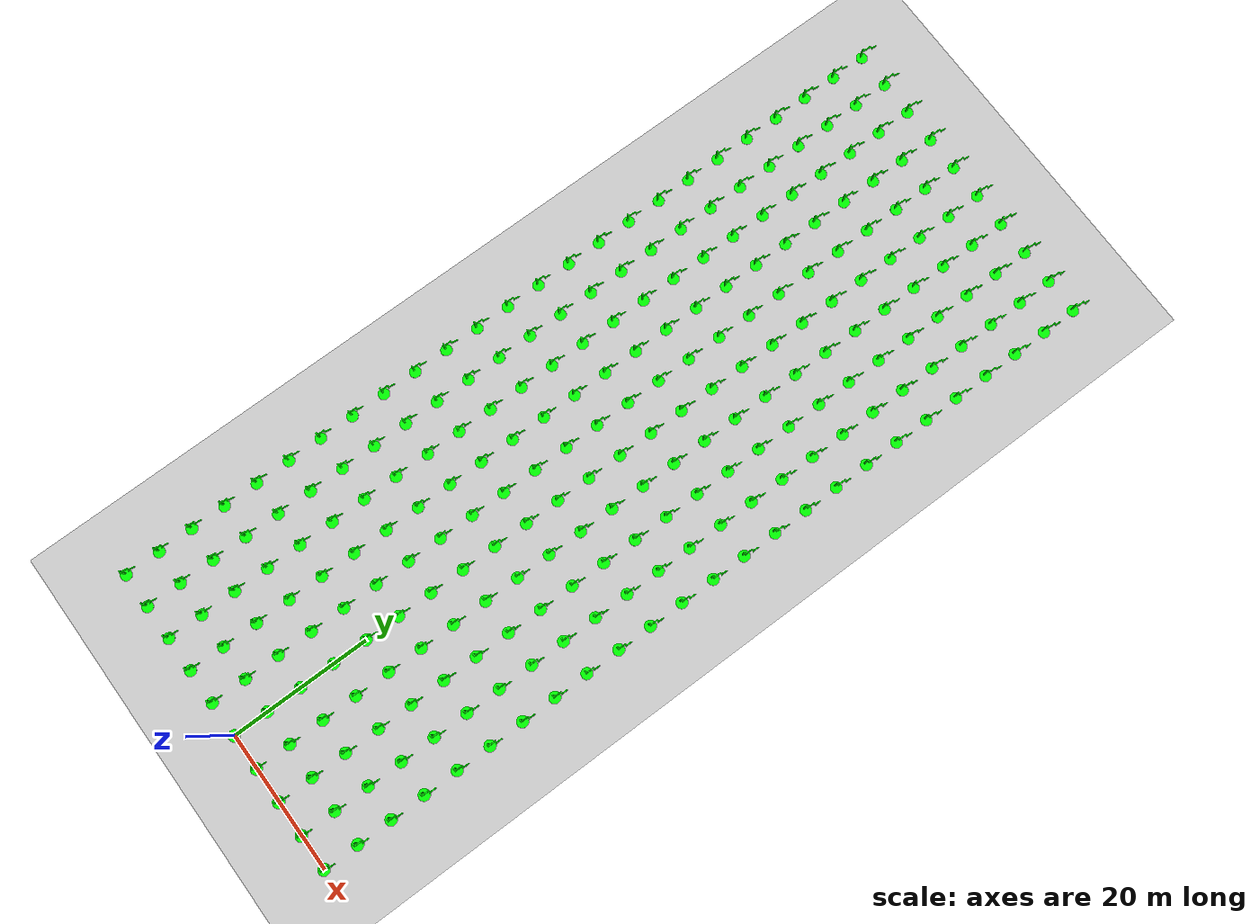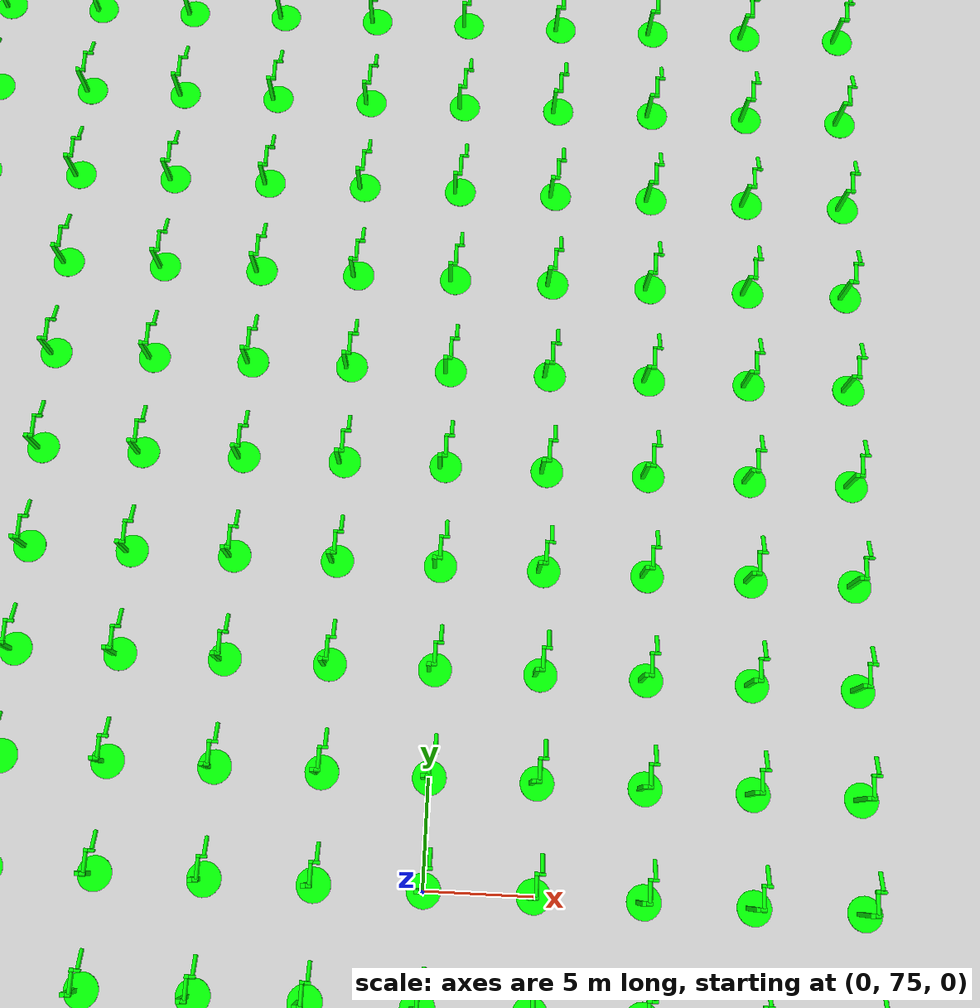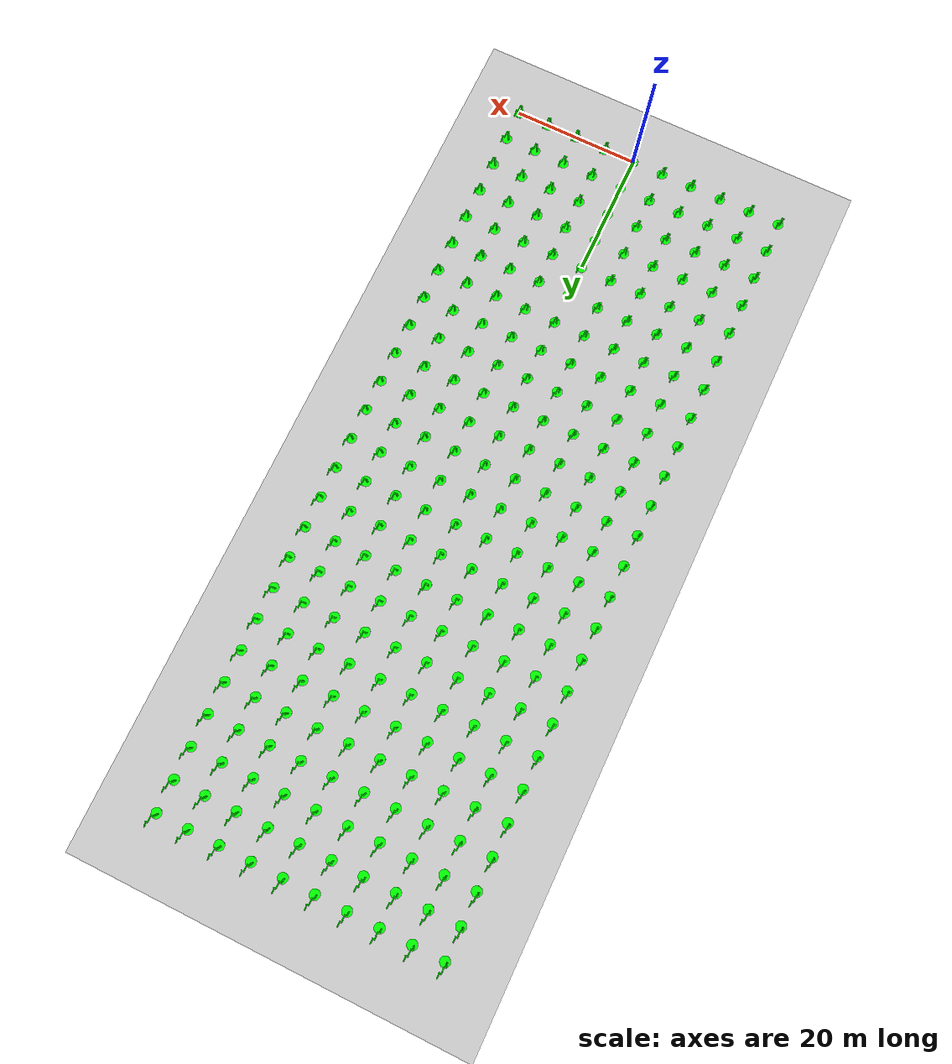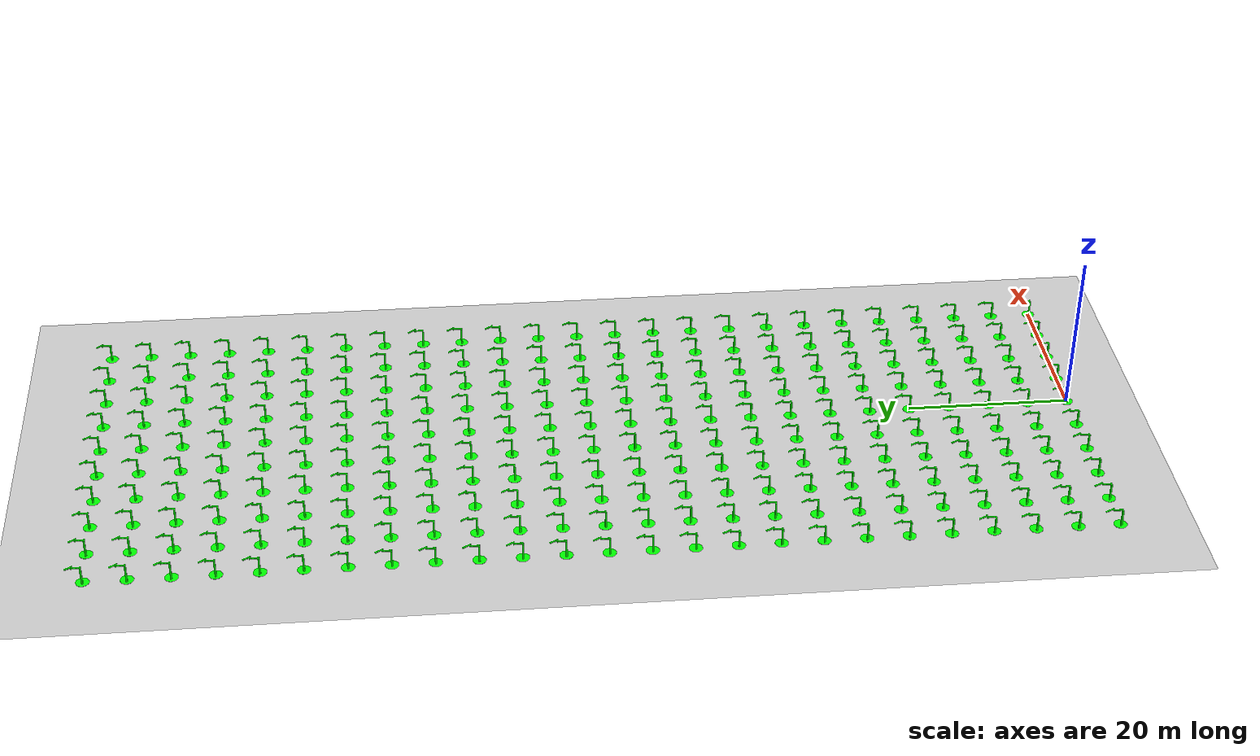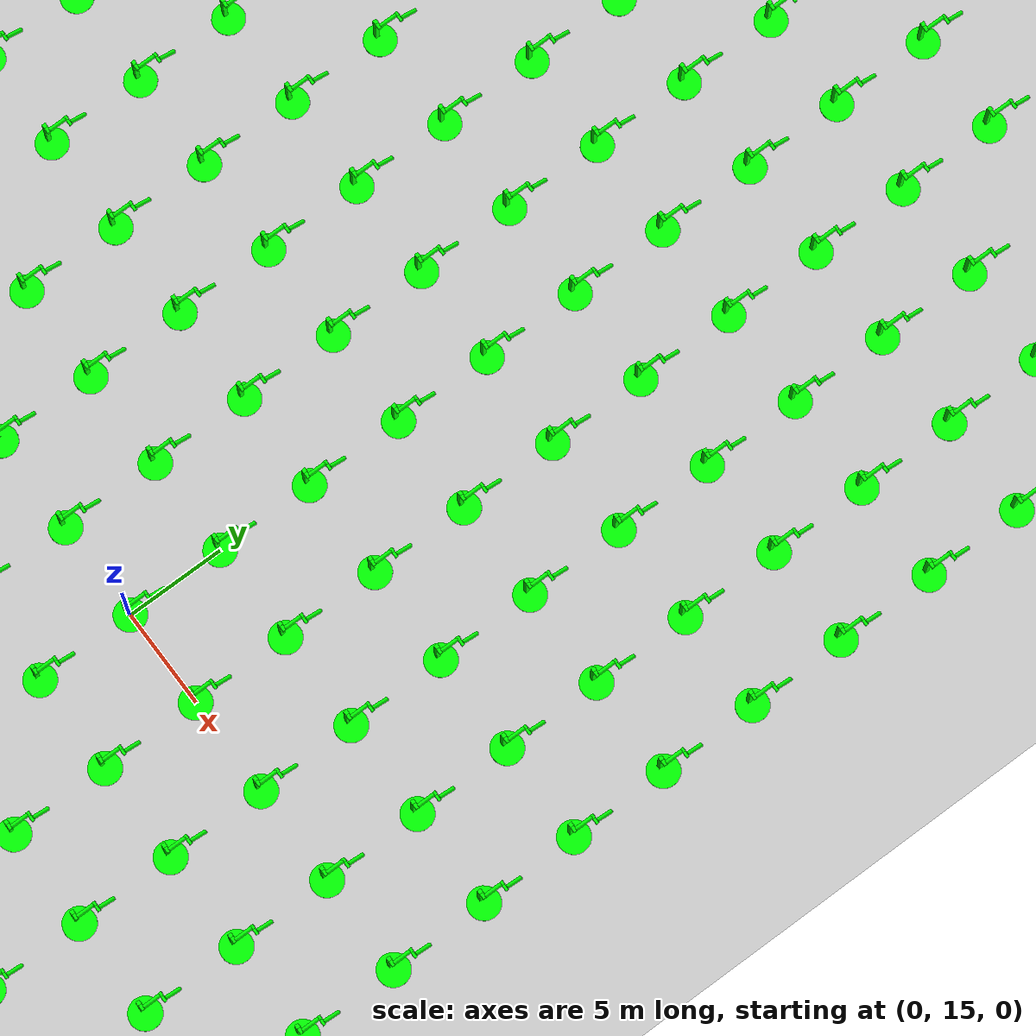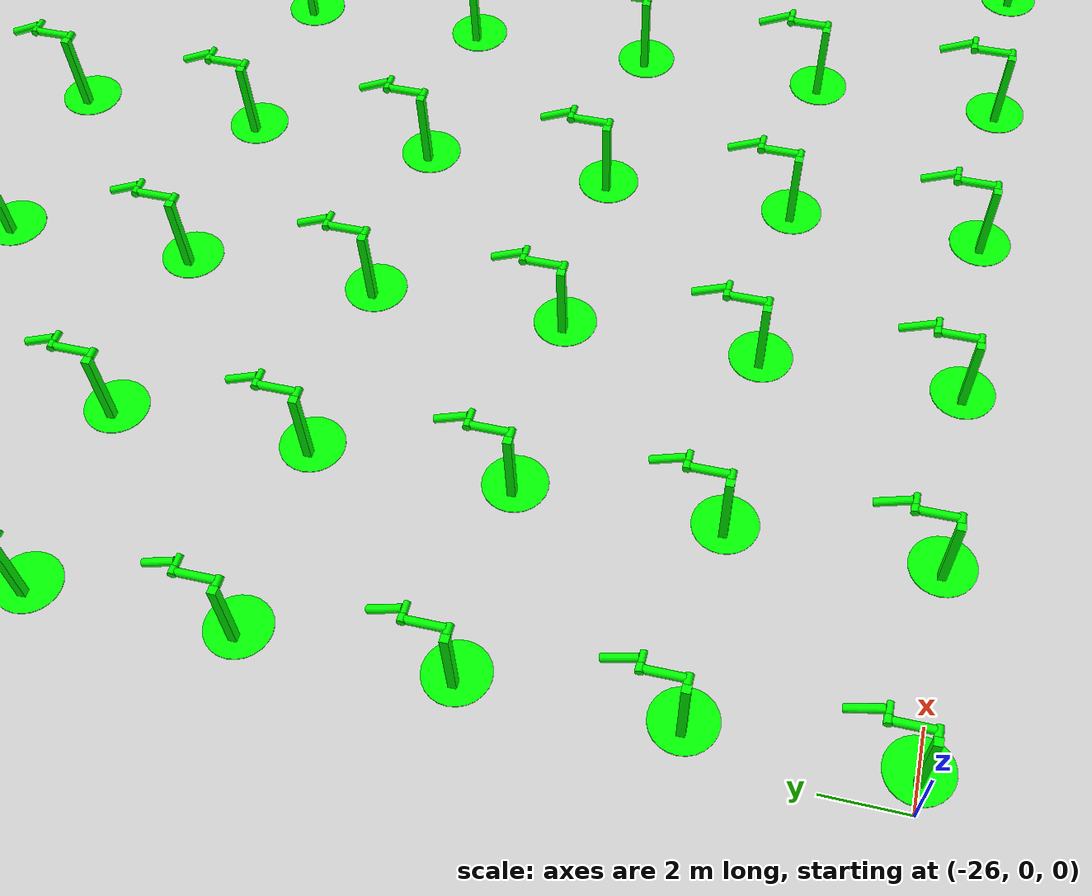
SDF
<?xml version="1.0" ?>
<!--
  to generate a world of 100 pendulums in a 10x10 grid,
  run `erb r=10 c=10 double_pendulums.sdf.erb > double_pendulums.sdf`
-->
<sdf version="1.6">
  <world name="double_pendulums">
    <model name="ground_plane">
      <static>true</static>
      <link name="link">
        <collision name="collision">
          <geometry>
            <plane>
              <normal>0 0 1</normal>
              <size>100 100</size>
            </plane>
          </geometry>
        </collision>
        <visual name="visual">
          <geometry>
            <plane>
              <normal>0 0 1</normal>
              <size>100 100</size>
            </plane>
          </geometry>
          <material>
            <ambient>0.8 0.8 0.8 1</ambient>
            <diffuse>0.8 0.8 0.8 1</diffuse>
            <specular>0.8 0.8 0.8 1</specular>
          </material>
        </visual>
      </link>
    </model>

    <model name="dbl_pendulum_0">
      <pose>-25 0 0 0 0 0</pose>
      <link name="base">
        <inertial>
          <mass>100</mass>
        </inertial>
        <visual name="vis_plate_on_ground">
          <pose>0 0 0.01 0 0 0</pose>
          <geometry>
            <cylinder>
              <radius>0.8</radius>
              <length>0.02</length>
            </cylinder>
          </geometry>
          <material>
            <ambient>0 1 0 1</ambient>
            <diffuse>0 1 0 1</diffuse>
            <specular>0 1 0 1</specular>
          </material>
        </visual>
        <visual name="vis_pole">
          <pose>-0.275 0 1.1 0 0 0</pose>
          <geometry>
            <box>
              <size>0.2 0.2 2.2</size>
            </box>
          </geometry>
          <material>
            <ambient>0 1 0 1</ambient>
            <diffuse>0 1 0 1</diffuse>
            <specular>0 1 0 1</specular>
          </material>
        </visual>
        <collision name="col_plate_on_ground">
          <pose>0 0 0.01 0 0 0</pose>
          <geometry>
            <cylinder>
              <radius>0.8</radius>
              <length>0.02</length>
            </cylinder>
          </geometry>
        </collision>
        <collision name="col_pole">
          <pose>-0.275 0 1.1 0 0 0</pose>
          <geometry>
            <box>
              <size>0.2 0.2 2.2</size>
            </box>
          </geometry>
        </collision>
      </link>
      <!-- upper link, length 1, IC -90 degrees -->
      <link name="upper_link">
        <pose>0 0 2.1 -1.5708 0 0</pose>
        <self_collide>0</self_collide>
        <inertial>
          <pose>0 0 0.5 0 0 0</pose>
        </inertial>
        <visual name="vis_upper_joint">
          <pose>-0.05 0 0 0 1.5708 0</pose>
          <geometry>
            <cylinder>
              <radius>0.1</radius>
              <length>0.3</length>
            </cylinder>
          </geometry>
          <material>
            <ambient>0 1 0 1</ambient>
            <diffuse>0 1 0 1</diffuse>
            <specular>0 1 0 1</specular>
          </material>
        </visual>
        <visual name="vis_lower_joint">
          <pose>0 0 1.0 0 1.5708 0</pose>
          <geometry>
            <cylinder>
              <radius>0.1</radius>
              <length>0.2</length>
            </cylinder>
          </geometry>
          <material>
            <ambient>0 1 0 1</ambient>
            <diffuse>0 1 0 1</diffuse>
            <specular>0 1 0 1</specular>
          </material>
        </visual>
        <visual name="vis_cylinder">
          <pose>0 0 0.5 0 0 0</pose>
          <geometry>
            <cylinder>
              <radius>0.1</radius>
              <length>0.9</length>
            </cylinder>
          </geometry>
          <material>
            <ambient>0 1 0 1</ambient>
            <diffuse>0 1 0 1</diffuse>
            <specular>0 1 0 1</specular>
          </material>
        </visual>
        <collision name="col_upper_joint">
          <pose>-0.05 0 0 0 1.5708 0</pose>
          <geometry>
            <cylinder>
              <radius>0.1</radius>
              <length>0.3</length>
            </cylinder>
          </geometry>
        </collision>
        <collision name="col_lower_joint">
          <pose>0 0 1.0 0 1.5708 0</pose>
          <geometry>
            <cylinder>
              <radius>0.1</radius>
              <length>0.2</length>
            </cylinder>
          </geometry>
        </collision>
        <collision name="col_cylinder">
          <pose>0 0 0.5 0 0 0</pose>
          <geometry>
            <cylinder>
              <radius>0.1</radius>
              <length>0.9</length>
            </cylinder>
          </geometry>
        </collision>
      </link>
      <!-- lower link, length 1, IC ~-120 degrees more -->
      <link name="lower_link">
        <pose>0.25 1.0 2.1 -2 0 0</pose>
        <self_collide>0</self_collide>
        <inertial>
          <pose>0 0 0.5 0 0 0</pose>
        </inertial>
        <visual name="vis_lower_joint">
          <pose>0 0 0 0 1.5708 0</pose>
          <geometry>
            <cylinder>
              <radius>0.08</radius>
              <length>0.3</length>
            </cylinder>
          </geometry>
          <material>
            <ambient>0 1 0 1</ambient>
            <diffuse>0 1 0 1</diffuse>
            <specular>0 1 0 1</specular>
          </material>
        </visual>
        <visual name="vis_cylinder">
          <pose>0 0 0.5 0 0 0</pose>
          <geometry>
            <cylinder>
              <radius>0.1</radius>
              <length>0.9</length>
            </cylinder>
          </geometry>
          <material>
            <ambient>0 1 0 1</ambient>
            <diffuse>0 1 0 1</diffuse>
            <specular>0 1 0 1</specular>
          </material>
        </visual>
        <collision name="col_lower_joint">
          <pose>0 0 0 0 1.5708 0</pose>
          <geometry>
            <cylinder>
              <radius>0.08</radius>
              <length>0.3</length>
            </cylinder>
          </geometry>
        </collision>
        <collision name="col_cylinder">
          <pose>0 0 0.5 0 0 0</pose>
          <geometry>
            <cylinder>
              <radius>0.1</radius>
              <length>0.9</length>
            </cylinder>
          </geometry>
        </collision>
      </link>
      <!-- pin joint for upper link, at origin of upper link -->
      <joint name="upper_joint" type="revolute">
        <parent>base</parent>
        <child>upper_link</child>
        <axis>
          <xyz>1.0 0 0</xyz>
        </axis>
      </joint>
      <!-- pin joint for lower link, at origin of child link -->
      <joint name="lower_joint" type="revolute">
        <parent>upper_link</parent>
        <child>lower_link</child>
        <axis>
          <xyz>1.0 0 0</xyz>
        </axis>
      </joint>
    </model>

    <model name="dbl_pendulum_1">
      <pose>-20 0 0 0 0 0</pose>
      <link name="base">
        <inertial>
          <mass>100</mass>
        </inertial>
        <visual name="vis_plate_on_ground">
          <pose>0 0 0.01 0 0 0</pose>
          <geometry>
            <cylinder>
              <radius>0.8</radius>
              <length>0.02</length>
            </cylinder>
          </geometry>
          <material>
            <ambient>0 1 0 1</ambient>
            <diffuse>0 1 0 1</diffuse>
            <specular>0 1 0 1</specular>
          </material>
        </visual>
        <visual name="vis_pole">
          <pose>-0.275 0 1.1 0 0 0</pose>
          <geometry>
            <box>
              <size>0.2 0.2 2.2</size>
            </box>
          </geometry>
          <material>
            <ambient>0 1 0 1</ambient>
            <diffuse>0 1 0 1</diffuse>
            <specular>0 1 0 1</specular>
          </material>
        </visual>
        <collision name="col_plate_on_ground">
          <pose>0 0 0.01 0 0 0</pose>
          <geometry>
            <cylinder>
              <radius>0.8</radius>
              <length>0.02</length>
            </cylinder>
          </geometry>
        </collision>
        <collision name="col_pole">
          <pose>-0.275 0 1.1 0 0 0</pose>
          <geometry>
            <box>
              <size>0.2 0.2 2.2</size>
            </box>
          </geometry>
        </collision>
      </link>
      <!-- upper link, length 1, IC -90 degrees -->
      <link name="upper_link">
        <pose>0 0 2.1 -1.5708 0 0</pose>
        <self_collide>0</self_collide>
        <inertial>
          <pose>0 0 0.5 0 0 0</pose>
        </inertial>
        <visual name="vis_upper_joint">
          <pose>-0.05 0 0 0 1.5708 0</pose>
          <geometry>
            <cylinder>
              <radius>0.1</radius>
              <length>0.3</length>
            </cylinder>
          </geometry>
          <material>
            <ambient>0 1 0 1</ambient>
            <diffuse>0 1 0 1</diffuse>
            <specular>0 1 0 1</specular>
          </material>
        </visual>
        <visual name="vis_lower_joint">
          <pose>0 0 1.0 0 1.5708 0</pose>
          <geometry>
            <cylinder>
              <radius>0.1</radius>
              <length>0.2</length>
            </cylinder>
          </geometry>
          <material>
            <ambient>0 1 0 1</ambient>
            <diffuse>0 1 0 1</diffuse>
            <specular>0 1 0 1</specular>
          </material>
        </visual>
        <visual name="vis_cylinder">
          <pose>0 0 0.5 0 0 0</pose>
          <geometry>
            <cylinder>
              <radius>0.1</radius>
              <length>0.9</length>
            </cylinder>
          </geometry>
          <material>
            <ambient>0 1 0 1</ambient>
            <diffuse>0 1 0 1</diffuse>
            <specular>0 1 0 1</specular>
          </material>
        </visual>
        <collision name="col_upper_joint">
          <pose>-0.05 0 0 0 1.5708 0</pose>
          <geometry>
            <cylinder>
              <radius>0.1</radius>
              <length>0.3</length>
            </cylinder>
          </geometry>
        </collision>
        <collision name="col_lower_joint">
          <pose>0 0 1.0 0 1.5708 0</pose>
          <geometry>
            <cylinder>
              <radius>0.1</radius>
              <length>0.2</length>
            </cylinder>
          </geometry>
        </collision>
        <collision name="col_cylinder">
          <pose>0 0 0.5 0 0 0</pose>
          <geometry>
            <cylinder>
              <radius>0.1</radius>
              <length>0.9</length>
            </cylinder>
          </geometry>
        </collision>
      </link>
      <!-- lower link, length 1, IC ~-120 degrees more -->
      <link name="lower_link">
        <pose>0.25 1.0 2.1 -2 0 0</pose>
        <self_collide>0</self_collide>
        <inertial>
          <pose>0 0 0.5 0 0 0</pose>
        </inertial>
        <visual name="vis_lower_joint">
          <pose>0 0 0 0 1.5708 0</pose>
          <geometry>
            <cylinder>
              <radius>0.08</radius>
              <length>0.3</length>
            </cylinder>
          </geometry>
          <material>
            <ambient>0 1 0 1</ambient>
            <diffuse>0 1 0 1</diffuse>
            <specular>0 1 0 1</specular>
          </material>
        </visual>
        <visual name="vis_cylinder">
          <pose>0 0 0.5 0 0 0</pose>
          <geometry>
            <cylinder>
              <radius>0.1</radius>
              <length>0.9</length>
            </cylinder>
          </geometry>
          <material>
            <ambient>0 1 0 1</ambient>
            <diffuse>0 1 0 1</diffuse>
            <specular>0 1 0 1</specular>
          </material>
        </visual>
        <collision name="col_lower_joint">
          <pose>0 0 0 0 1.5708 0</pose>
          <geometry>
            <cylinder>
              <radius>0.08</radius>
              <length>0.3</length>
            </cylinder>
          </geometry>
        </collision>
        <collision name="col_cylinder">
          <pose>0 0 0.5 0 0 0</pose>
          <geometry>
            <cylinder>
              <radius>0.1</radius>
              <length>0.9</length>
            </cylinder>
          </geometry>
        </collision>
      </link>
      <!-- pin joint for upper link, at origin of upper link -->
      <joint name="upper_joint" type="revolute">
        <parent>base</parent>
        <child>upper_link</child>
        <axis>
          <xyz>1.0 0 0</xyz>
        </axis>
      </joint>
      <!-- pin joint for lower link, at origin of child link -->
      <joint name="lower_joint" type="revolute">
        <parent>upper_link</parent>
        <child>lower_link</child>
        <axis>
          <xyz>1.0 0 0</xyz>
        </axis>
      </joint>
    </model>

    <model name="dbl_pendulum_2">
      <pose>-15 0 0 0 0 0</pose>
      <link name="base">
        <inertial>
          <mass>100</mass>
        </inertial>
        <visual name="vis_plate_on_ground">
          <pose>0 0 0.01 0 0 0</pose>
          <geometry>
            <cylinder>
              <radius>0.8</radius>
              <length>0.02</length>
            </cylinder>
          </geometry>
          <material>
            <ambient>0 1 0 1</ambient>
            <diffuse>0 1 0 1</diffuse>
            <specular>0 1 0 1</specular>
          </material>
        </visual>
        <visual name="vis_pole">
          <pose>-0.275 0 1.1 0 0 0</pose>
          <geometry>
            <box>
              <size>0.2 0.2 2.2</size>
            </box>
          </geometry>
          <material>
            <ambient>0 1 0 1</ambient>
            <diffuse>0 1 0 1</diffuse>
            <specular>0 1 0 1</specular>
          </material>
        </visual>
        <collision name="col_plate_on_ground">
          <pose>0 0 0.01 0 0 0</pose>
          <geometry>
            <cylinder>
              <radius>0.8</radius>
              <length>0.02</length>
            </cylinder>
          </geometry>
        </collision>
        <collision name="col_pole">
          <pose>-0.275 0 1.1 0 0 0</pose>
          <geometry>
            <box>
              <size>0.2 0.2 2.2</size>
            </box>
          </geometry>
        </collision>
      </link>
      <!-- upper link, length 1, IC -90 degrees -->
      <link name="upper_link">
        <pose>0 0 2.1 -1.5708 0 0</pose>
        <self_collide>0</self_collide>
        <inertial>
          <pose>0 0 0.5 0 0 0</pose>
        </inertial>
        <visual name="vis_upper_joint">
          <pose>-0.05 0 0 0 1.5708 0</pose>
          <geometry>
            <cylinder>
              <radius>0.1</radius>
              <length>0.3</length>
            </cylinder>
          </geometry>
          <material>
            <ambient>0 1 0 1</ambient>
            <diffuse>0 1 0 1</diffuse>
            <specular>0 1 0 1</specular>
          </material>
        </visual>
        <visual name="vis_lower_joint">
          <pose>0 0 1.0 0 1.5708 0</pose>
          <geometry>
            <cylinder>
              <radius>0.1</radius>
              <length>0.2</length>
            </cylinder>
          </geometry>
          <material>
            <ambient>0 1 0 1</ambient>
            <diffuse>0 1 0 1</diffuse>
            <specular>0 1 0 1</specular>
          </material>
        </visual>
        <visual name="vis_cylinder">
          <pose>0 0 0.5 0 0 0</pose>
          <geometry>
            <cylinder>
              <radius>0.1</radius>
              <length>0.9</length>
            </cylinder>
          </geometry>
          <material>
            <ambient>0 1 0 1</ambient>
            <diffuse>0 1 0 1</diffuse>
            <specular>0 1 0 1</specular>
          </material>
        </visual>
        <collision name="col_upper_joint">
          <pose>-0.05 0 0 0 1.5708 0</pose>
          <geometry>
            <cylinder>
              <radius>0.1</radius>
              <length>0.3</length>
            </cylinder>
          </geometry>
        </collision>
        <collision name="col_lower_joint">
          <pose>0 0 1.0 0 1.5708 0</pose>
          <geometry>
            <cylinder>
              <radius>0.1</radius>
              <length>0.2</length>
            </cylinder>
          </geometry>
        </collision>
        <collision name="col_cylinder">
          <pose>0 0 0.5 0 0 0</pose>
          <geometry>
            <cylinder>
              <radius>0.1</radius>
              <length>0.9</length>
            </cylinder>
          </geometry>
        </collision>
      </link>
      <!-- lower link, length 1, IC ~-120 degrees more -->
      <link name="lower_link">
        <pose>0.25 1.0 2.1 -2 0 0</pose>
        <self_collide>0</self_collide>
        <inertial>
          <pose>0 0 0.5 0 0 0</pose>
        </inertial>
        <visual name="vis_lower_joint">
          <pose>0 0 0 0 1.5708 0</pose>
          <geometry>
            <cylinder>
              <radius>0.08</radius>
              <length>0.3</length>
            </cylinder>
          </geometry>
          <material>
            <ambient>0 1 0 1</ambient>
            <diffuse>0 1 0 1</diffuse>
            <specular>0 1 0 1</specular>
          </material>
        </visual>
        <visual name="vis_cylinder">
          <pose>0 0 0.5 0 0 0</pose>
          <geometry>
            <cylinder>
              <radius>0.1</radius>
              <length>0.9</length>
            </cylinder>
          </geometry>
          <material>
            <ambient>0 1 0 1</ambient>
            <diffuse>0 1 0 1</diffuse>
            <specular>0 1 0 1</specular>
          </material>
        </visual>
        <collision name="col_lower_joint">
          <pose>0 0 0 0 1.5708 0</pose>
          <geometry>
            <cylinder>
              <radius>0.08</radius>
              <length>0.3</length>
            </cylinder>
          </geometry>
        </collision>
        <collision name="col_cylinder">
          <pose>0 0 0.5 0 0 0</pose>
          <geometry>
            <cylinder>
              <radius>0.1</radius>
              <length>0.9</length>
            </cylinder>
          </geometry>
        </collision>
      </link>
      <!-- pin joint for upper link, at origin of upper link -->
      <joint name="upper_joint" type="revolute">
        <parent>base</parent>
        <child>upper_link</child>
        <axis>
          <xyz>1.0 0 0</xyz>
        </axis>
      </joint>
      <!-- pin joint for lower link, at origin of child link -->
      <joint name="lower_joint" type="revolute">
        <parent>upper_link</parent>
        <child>lower_link</child>
        <axis>
          <xyz>1.0 0 0</xyz>
        </axis>
      </joint>
    </model>

    <model name="dbl_pendulum_3">
      <pose>-10 0 0 0 0 0</pose>
      <link name="base">
        <inertial>
          <mass>100</mass>
        </inertial>
        <visual name="vis_plate_on_ground">
          <pose>0 0 0.01 0 0 0</pose>
          <geometry>
            <cylinder>
              <radius>0.8</radius>
              <length>0.02</length>
            </cylinder>
          </geometry>
          <material>
            <ambient>0 1 0 1</ambient>
            <diffuse>0 1 0 1</diffuse>
            <specular>0 1 0 1</specular>
          </material>
        </visual>
        <visual name="vis_pole">
          <pose>-0.275 0 1.1 0 0 0</pose>
          <geometry>
            <box>
              <size>0.2 0.2 2.2</size>
            </box>
          </geometry>
          <material>
            <ambient>0 1 0 1</ambient>
            <diffuse>0 1 0 1</diffuse>
            <specular>0 1 0 1</specular>
          </material>
        </visual>
        <collision name="col_plate_on_ground">
          <pose>0 0 0.01 0 0 0</pose>
          <geometry>
            <cylinder>
              <radius>0.8</radius>
              <length>0.02</length>
            </cylinder>
          </geometry>
        </collision>
        <collision name="col_pole">
          <pose>-0.275 0 1.1 0 0 0</pose>
          <geometry>
            <box>
              <size>0.2 0.2 2.2</size>
            </box>
          </geometry>
        </collision>
      </link>
      <!-- upper link, length 1, IC -90 degrees -->
      <link name="upper_link">
        <pose>0 0 2.1 -1.5708 0 0</pose>
        <self_collide>0</self_collide>
        <inertial>
          <pose>0 0 0.5 0 0 0</pose>
        </inertial>
        <visual name="vis_upper_joint">
          <pose>-0.05 0 0 0 1.5708 0</pose>
          <geometry>
            <cylinder>
              <radius>0.1</radius>
              <length>0.3</length>
            </cylinder>
          </geometry>
          <material>
            <ambient>0 1 0 1</ambient>
            <diffuse>0 1 0 1</diffuse>
            <specular>0 1 0 1</specular>
          </material>
        </visual>
        <visual name="vis_lower_joint">
          <pose>0 0 1.0 0 1.5708 0</pose>
          <geometry>
            <cylinder>
              <radius>0.1</radius>
              <length>0.2</length>
            </cylinder>
          </geometry>
          <material>
            <ambient>0 1 0 1</ambient>
            <diffuse>0 1 0 1</diffuse>
            <specular>0 1 0 1</specular>
          </material>
        </visual>
        <visual name="vis_cylinder">
          <pose>0 0 0.5 0 0 0</pose>
          <geometry>
            <cylinder>
              <radius>0.1</radius>
              <length>0.9</length>
            </cylinder>
          </geometry>
          <material>
            <ambient>0 1 0 1</ambient>
            <diffuse>0 1 0 1</diffuse>
            <specular>0 1 0 1</specular>
          </material>
        </visual>
        <collision name="col_upper_joint">
          <pose>-0.05 0 0 0 1.5708 0</pose>
          <geometry>
            <cylinder>
              <radius>0.1</radius>
              <length>0.3</length>
            </cylinder>
          </geometry>
        </collision>
        <collision name="col_lower_joint">
          <pose>0 0 1.0 0 1.5708 0</pose>
          <geometry>
            <cylinder>
              <radius>0.1</radius>
              <length>0.2</length>
            </cylinder>
          </geometry>
        </collision>
        <collision name="col_cylinder">
          <pose>0 0 0.5 0 0 0</pose>
          <geometry>
            <cylinder>
              <radius>0.1</radius>
              <length>0.9</length>
            </cylinder>
          </geometry>
        </collision>
      </link>
      <!-- lower link, length 1, IC ~-120 degrees more -->
      <link name="lower_link">
        <pose>0.25 1.0 2.1 -2 0 0</pose>
        <self_collide>0</self_collide>
        <inertial>
          <pose>0 0 0.5 0 0 0</pose>
        </inertial>
        <visual name="vis_lower_joint">
          <pose>0 0 0 0 1.5708 0</pose>
          <geometry>
            <cylinder>
              <radius>0.08</radius>
              <length>0.3</length>
            </cylinder>
          </geometry>
          <material>
            <ambient>0 1 0 1</ambient>
            <diffuse>0 1 0 1</diffuse>
            <specular>0 1 0 1</specular>
          </material>
        </visual>
        <visual name="vis_cylinder">
          <pose>0 0 0.5 0 0 0</pose>
          <geometry>
            <cylinder>
              <radius>0.1</radius>
              <length>0.9</length>
            </cylinder>
          </geometry>
          <material>
            <ambient>0 1 0 1</ambient>
            <diffuse>0 1 0 1</diffuse>
            <specular>0 1 0 1</specular>
          </material>
        </visual>
        <collision name="col_lower_joint">
          <pose>0 0 0 0 1.5708 0</pose>
          <geometry>
            <cylinder>
              <radius>0.08</radius>
              <length>0.3</length>
            </cylinder>
          </geometry>
        </collision>
        <collision name="col_cylinder">
          <pose>0 0 0.5 0 0 0</pose>
          <geometry>
            <cylinder>
              <radius>0.1</radius>
              <length>0.9</length>
            </cylinder>
          </geometry>
        </collision>
      </link>
      <!-- pin joint for upper link, at origin of upper link -->
      <joint name="upper_joint" type="revolute">
        <parent>base</parent>
        <child>upper_link</child>
        <axis>
          <xyz>1.0 0 0</xyz>
        </axis>
      </joint>
      <!-- pin joint for lower link, at origin of child link -->
      <joint name="lower_joint" type="revolute">
        <parent>upper_link</parent>
        <child>lower_link</child>
        <axis>
          <xyz>1.0 0 0</xyz>
        </axis>
      </joint>
    </model>

    <model name="dbl_pendulum_4">
      <pose>-5 0 0 0 0 0</pose>
      <link name="base">
        <inertial>
          <mass>100</mass>
        </inertial>
        <visual name="vis_plate_on_ground">
          <pose>0 0 0.01 0 0 0</pose>
          <geometry>
            <cylinder>
              <radius>0.8</radius>
              <length>0.02</length>
            </cylinder>
          </geometry>
          <material>
            <ambient>0 1 0 1</ambient>
            <diffuse>0 1 0 1</diffuse>
            <specular>0 1 0 1</specular>
          </material>
        </visual>
        <visual name="vis_pole">
          <pose>-0.275 0 1.1 0 0 0</pose>
          <geometry>
            <box>
              <size>0.2 0.2 2.2</size>
            </box>
          </geometry>
          <material>
            <ambient>0 1 0 1</ambient>
            <diffuse>0 1 0 1</diffuse>
            <specular>0 1 0 1</specular>
          </material>
        </visual>
        <collision name="col_plate_on_ground">
          <pose>0 0 0.01 0 0 0</pose>
          <geometry>
            <cylinder>
              <radius>0.8</radius>
              <length>0.02</length>
            </cylinder>
          </geometry>
        </collision>
        <collision name="col_pole">
          <pose>-0.275 0 1.1 0 0 0</pose>
          <geometry>
            <box>
              <size>0.2 0.2 2.2</size>
            </box>
          </geometry>
        </collision>
      </link>
      <!-- upper link, length 1, IC -90 degrees -->
      <link name="upper_link">
        <pose>0 0 2.1 -1.5708 0 0</pose>
        <self_collide>0</self_collide>
        <inertial>
          <pose>0 0 0.5 0 0 0</pose>
        </inertial>
        <visual name="vis_upper_joint">
          <pose>-0.05 0 0 0 1.5708 0</pose>
          <geometry>
            <cylinder>
              <radius>0.1</radius>
              <length>0.3</length>
            </cylinder>
          </geometry>
          <material>
            <ambient>0 1 0 1</ambient>
            <diffuse>0 1 0 1</diffuse>
            <specular>0 1 0 1</specular>
          </material>
        </visual>
        <visual name="vis_lower_joint">
          <pose>0 0 1.0 0 1.5708 0</pose>
          <geometry>
            <cylinder>
              <radius>0.1</radius>
              <length>0.2</length>
            </cylinder>
          </geometry>
          <material>
            <ambient>0 1 0 1</ambient>
            <diffuse>0 1 0 1</diffuse>
            <specular>0 1 0 1</specular>
          </material>
        </visual>
        <visual name="vis_cylinder">
          <pose>0 0 0.5 0 0 0</pose>
          <geometry>
            <cylinder>
              <radius>0.1</radius>
              <length>0.9</length>
            </cylinder>
          </geometry>
          <material>
            <ambient>0 1 0 1</ambient>
            <diffuse>0 1 0 1</diffuse>
            <specular>0 1 0 1</specular>
          </material>
        </visual>
        <collision name="col_upper_joint">
          <pose>-0.05 0 0 0 1.5708 0</pose>
          <geometry>
            <cylinder>
              <radius>0.1</radius>
              <length>0.3</length>
            </cylinder>
          </geometry>
        </collision>
        <collision name="col_lower_joint">
          <pose>0 0 1.0 0 1.5708 0</pose>
          <geometry>
            <cylinder>
              <radius>0.1</radius>
              <length>0.2</length>
            </cylinder>
          </geometry>
        </collision>
        <collision name="col_cylinder">
          <pose>0 0 0.5 0 0 0</pose>
          <geometry>
            <cylinder>
              <radius>0.1</radius>
              <length>0.9</length>
            </cylinder>
          </geometry>
        </collision>
      </link>
      <!-- lower link, length 1, IC ~-120 degrees more -->
      <link name="lower_link">
        <pose>0.25 1.0 2.1 -2 0 0</pose>
        <self_collide>0</self_collide>
        <inertial>
          <pose>0 0 0.5 0 0 0</pose>
        </inertial>
        <visual name="vis_lower_joint">
          <pose>0 0 0 0 1.5708 0</pose>
          <geometry>
            <cylinder>
              <radius>0.08</radius>
              <length>0.3</length>
            </cylinder>
          </geometry>
          <material>
            <ambient>0 1 0 1</ambient>
            <diffuse>0 1 0 1</diffuse>
            <specular>0 1 0 1</specular>
          </material>
        </visual>
        <visual name="vis_cylinder">
          <pose>0 0 0.5 0 0 0</pose>
          <geometry>
            <cylinder>
              <radius>0.1</radius>
              <length>0.9</length>
            </cylinder>
          </geometry>
          <material>
            <ambient>0 1 0 1</ambient>
            <diffuse>0 1 0 1</diffuse>
            <specular>0 1 0 1</specular>
          </material>
        </visual>
        <collision name="col_lower_joint">
          <pose>0 0 0 0 1.5708 0</pose>
          <geometry>
            <cylinder>
              <radius>0.08</radius>
              <length>0.3</length>
            </cylinder>
          </geometry>
        </collision>
        <collision name="col_cylinder">
          <pose>0 0 0.5 0 0 0</pose>
          <geometry>
            <cylinder>
              <radius>0.1</radius>
              <length>0.9</length>
            </cylinder>
          </geometry>
        </collision>
      </link>
      <!-- pin joint for upper link, at origin of upper link -->
      <joint name="upper_joint" type="revolute">
        <parent>base</parent>
        <child>upper_link</child>
        <axis>
          <xyz>1.0 0 0</xyz>
        </axis>
      </joint>
      <!-- pin joint for lower link, at origin of child link -->
      <joint name="lower_joint" type="revolute">
        <parent>upper_link</parent>
        <child>lower_link</child>
        <axis>
          <xyz>1.0 0 0</xyz>
        </axis>
      </joint>
    </model>

    <model name="dbl_pendulum_5">
      <pose>0 0 0 0 0 0</pose>
      <link name="base">
        <inertial>
          <mass>100</mass>
        </inertial>
        <visual name="vis_plate_on_ground">
          <pose>0 0 0.01 0 0 0</pose>
          <geometry>
            <cylinder>
              <radius>0.8</radius>
              <length>0.02</length>
            </cylinder>
          </geometry>
          <material>
            <ambient>0 1 0 1</ambient>
            <diffuse>0 1 0 1</diffuse>
            <specular>0 1 0 1</specular>
          </material>
        </visual>
        <visual name="vis_pole">
          <pose>-0.275 0 1.1 0 0 0</pose>
          <geometry>
            <box>
              <size>0.2 0.2 2.2</size>
            </box>
          </geometry>
          <material>
            <ambient>0 1 0 1</ambient>
            <diffuse>0 1 0 1</diffuse>
            <specular>0 1 0 1</specular>
          </material>
        </visual>
        <collision name="col_plate_on_ground">
          <pose>0 0 0.01 0 0 0</pose>
          <geometry>
            <cylinder>
              <radius>0.8</radius>
              <length>0.02</length>
            </cylinder>
          </geometry>
        </collision>
        <collision name="col_pole">
          <pose>-0.275 0 1.1 0 0 0</pose>
          <geometry>
            <box>
              <size>0.2 0.2 2.2</size>
            </box>
          </geometry>
        </collision>
      </link>
      <!-- upper link, length 1, IC -90 degrees -->
      <link name="upper_link">
        <pose>0 0 2.1 -1.5708 0 0</pose>
        <self_collide>0</self_collide>
        <inertial>
          <pose>0 0 0.5 0 0 0</pose>
        </inertial>
        <visual name="vis_upper_joint">
          <pose>-0.05 0 0 0 1.5708 0</pose>
          <geometry>
            <cylinder>
              <radius>0.1</radius>
              <length>0.3</length>
            </cylinder>
          </geometry>
          <material>
            <ambient>0 1 0 1</ambient>
            <diffuse>0 1 0 1</diffuse>
            <specular>0 1 0 1</specular>
          </material>
        </visual>
        <visual name="vis_lower_joint">
          <pose>0 0 1.0 0 1.5708 0</pose>
          <geometry>
            <cylinder>
              <radius>0.1</radius>
              <length>0.2</length>
            </cylinder>
          </geometry>
          <material>
            <ambient>0 1 0 1</ambient>
            <diffuse>0 1 0 1</diffuse>
            <specular>0 1 0 1</specular>
          </material>
        </visual>
        <visual name="vis_cylinder">
          <pose>0 0 0.5 0 0 0</pose>
          <geometry>
            <cylinder>
              <radius>0.1</radius>
              <length>0.9</length>
            </cylinder>
          </geometry>
          <material>
            <ambient>0 1 0 1</ambient>
            <diffuse>0 1 0 1</diffuse>
            <specular>0 1 0 1</specular>
          </material>
        </visual>
        <collision name="col_upper_joint">
          <pose>-0.05 0 0 0 1.5708 0</pose>
          <geometry>
            <cylinder>
              <radius>0.1</radius>
              <length>0.3</length>
            </cylinder>
          </geometry>
        </collision>
        <collision name="col_lower_joint">
          <pose>0 0 1.0 0 1.5708 0</pose>
          <geometry>
            <cylinder>
              <radius>0.1</radius>
              <length>0.2</length>
            </cylinder>
          </geometry>
        </collision>
        <collision name="col_cylinder">
          <pose>0 0 0.5 0 0 0</pose>
          <geometry>
            <cylinder>
              <radius>0.1</radius>
              <length>0.9</length>
            </cylinder>
          </geometry>
        </collision>
      </link>
      <!-- lower link, length 1, IC ~-120 degrees more -->
      <link name="lower_link">
        <pose>0.25 1.0 2.1 -2 0 0</pose>
        <self_collide>0</self_collide>
        <inertial>
          <pose>0 0 0.5 0 0 0</pose>
        </inertial>
        <visual name="vis_lower_joint">
          <pose>0 0 0 0 1.5708 0</pose>
          <geometry>
            <cylinder>
              <radius>0.08</radius>
              <length>0.3</length>
            </cylinder>
          </geometry>
          <material>
            <ambient>0 1 0 1</ambient>
            <diffuse>0 1 0 1</diffuse>
            <specular>0 1 0 1</specular>
          </material>
        </visual>
        <visual name="vis_cylinder">
          <pose>0 0 0.5 0 0 0</pose>
          <geometry>
            <cylinder>
              <radius>0.1</radius>
              <length>0.9</length>
            </cylinder>
          </geometry>
          <material>
            <ambient>0 1 0 1</ambient>
            <diffuse>0 1 0 1</diffuse>
            <specular>0 1 0 1</specular>
          </material>
        </visual>
        <collision name="col_lower_joint">
          <pose>0 0 0 0 1.5708 0</pose>
          <geometry>
            <cylinder>
              <radius>0.08</radius>
              <length>0.3</length>
            </cylinder>
          </geometry>
        </collision>
        <collision name="col_cylinder">
          <pose>0 0 0.5 0 0 0</pose>
          <geometry>
            <cylinder>
              <radius>0.1</radius>
              <length>0.9</length>
            </cylinder>
          </geometry>
        </collision>
      </link>
      <!-- pin joint for upper link, at origin of upper link -->
      <joint name="upper_joint" type="revolute">
        <parent>base</parent>
        <child>upper_link</child>
        <axis>
          <xyz>1.0 0 0</xyz>
        </axis>
      </joint>
      <!-- pin joint for lower link, at origin of child link -->
      <joint name="lower_joint" type="revolute">
        <parent>upper_link</parent>
        <child>lower_link</child>
        <axis>
          <xyz>1.0 0 0</xyz>
        </axis>
      </joint>
    </model>

    <model name="dbl_pendulum_6">
      <pose>5 0 0 0 0 0</pose>
      <link name="base">
        <inertial>
          <mass>100</mass>
        </inertial>
        <visual name="vis_plate_on_ground">
          <pose>0 0 0.01 0 0 0</pose>
          <geometry>
            <cylinder>
              <radius>0.8</radius>
              <length>0.02</length>
            </cylinder>
          </geometry>
          <material>
            <ambient>0 1 0 1</ambient>
            <diffuse>0 1 0 1</diffuse>
            <specular>0 1 0 1</specular>
          </material>
        </visual>
        <visual name="vis_pole">
          <pose>-0.275 0 1.1 0 0 0</pose>
          <geometry>
            <box>
              <size>0.2 0.2 2.2</size>
            </box>
          </geometry>
          <material>
            <ambient>0 1 0 1</ambient>
            <diffuse>0 1 0 1</diffuse>
            <specular>0 1 0 1</specular>
          </material>
        </visual>
        <collision name="col_plate_on_ground">
          <pose>0 0 0.01 0 0 0</pose>
          <geometry>
            <cylinder>
              <radius>0.8</radius>
              <length>0.02</length>
            </cylinder>
          </geometry>
        </collision>
        <collision name="col_pole">
          <pose>-0.275 0 1.1 0 0 0</pose>
          <geometry>
            <box>
              <size>0.2 0.2 2.2</size>
            </box>
          </geometry>
        </collision>
      </link>
      <!-- upper link, length 1, IC -90 degrees -->
      <link name="upper_link">
        <pose>0 0 2.1 -1.5708 0 0</pose>
        <self_collide>0</self_collide>
        <inertial>
          <pose>0 0 0.5 0 0 0</pose>
        </inertial>
        <visual name="vis_upper_joint">
          <pose>-0.05 0 0 0 1.5708 0</pose>
          <geometry>
            <cylinder>
              <radius>0.1</radius>
              <length>0.3</length>
            </cylinder>
          </geometry>
          <material>
            <ambient>0 1 0 1</ambient>
            <diffuse>0 1 0 1</diffuse>
            <specular>0 1 0 1</specular>
          </material>
        </visual>
        <visual name="vis_lower_joint">
          <pose>0 0 1.0 0 1.5708 0</pose>
          <geometry>
            <cylinder>
              <radius>0.1</radius>
              <length>0.2</length>
            </cylinder>
          </geometry>
          <material>
            <ambient>0 1 0 1</ambient>
            <diffuse>0 1 0 1</diffuse>
            <specular>0 1 0 1</specular>
          </material>
        </visual>
        <visual name="vis_cylinder">
          <pose>0 0 0.5 0 0 0</pose>
          <geometry>
            <cylinder>
              <radius>0.1</radius>
              <length>0.9</length>
            </cylinder>
          </geometry>
          <material>
            <ambient>0 1 0 1</ambient>
            <diffuse>0 1 0 1</diffuse>
            <specular>0 1 0 1</specular>
          </material>
        </visual>
        <collision name="col_upper_joint">
          <pose>-0.05 0 0 0 1.5708 0</pose>
          <geometry>
            <cylinder>
              <radius>0.1</radius>
              <length>0.3</length>
            </cylinder>
          </geometry>
        </collision>
        <collision name="col_lower_joint">
          <pose>0 0 1.0 0 1.5708 0</pose>
          <geometry>
            <cylinder>
              <radius>0.1</radius>
              <length>0.2</length>
            </cylinder>
          </geometry>
        </collision>
        <collision name="col_cylinder">
          <pose>0 0 0.5 0 0 0</pose>
          <geometry>
            <cylinder>
              <radius>0.1</radius>
              <length>0.9</length>
            </cylinder>
          </geometry>
        </collision>
      </link>
      <!-- lower link, length 1, IC ~-120 degrees more -->
      <link name="lower_link">
        <pose>0.25 1.0 2.1 -2 0 0</pose>
        <self_collide>0</self_collide>
        <inertial>
          <pose>0 0 0.5 0 0 0</pose>
        </inertial>
        <visual name="vis_lower_joint">
          <pose>0 0 0 0 1.5708 0</pose>
          <geometry>
            <cylinder>
              <radius>0.08</radius>
              <length>0.3</length>
            </cylinder>
          </geometry>
          <material>
            <ambient>0 1 0 1</ambient>
            <diffuse>0 1 0 1</diffuse>
            <specular>0 1 0 1</specular>
          </material>
        </visual>
        <visual name="vis_cylinder">
          <pose>0 0 0.5 0 0 0</pose>
          <geometry>
            <cylinder>
              <radius>0.1</radius>
              <length>0.9</length>
            </cylinder>
          </geometry>
          <material>
            <ambient>0 1 0 1</ambient>
            <diffuse>0 1 0 1</diffuse>
            <specular>0 1 0 1</specular>
          </material>
        </visual>
        <collision name="col_lower_joint">
          <pose>0 0 0 0 1.5708 0</pose>
          <geometry>
            <cylinder>
              <radius>0.08</radius>
              <length>0.3</length>
            </cylinder>
          </geometry>
        </collision>
        <collision name="col_cylinder">
          <pose>0 0 0.5 0 0 0</pose>
          <geometry>
            <cylinder>
              <radius>0.1</radius>
              <length>0.9</length>
            </cylinder>
          </geometry>
        </collision>
      </link>
      <!-- pin joint for upper link, at origin of upper link -->
      <joint name="upper_joint" type="revolute">
        <parent>base</parent>
        <child>upper_link</child>
        <axis>
          <xyz>1.0 0 0</xyz>
        </axis>
      </joint>
      <!-- pin joint for lower link, at origin of child link -->
      <joint name="lower_joint" type="revolute">
        <parent>upper_link</parent>
        <child>lower_link</child>
        <axis>
          <xyz>1.0 0 0</xyz>
        </axis>
      </joint>
    </model>

    <model name="dbl_pendulum_7">
      <pose>10 0 0 0 0 0</pose>
      <link name="base">
        <inertial>
          <mass>100</mass>
        </inertial>
        <visual name="vis_plate_on_ground">
          <pose>0 0 0.01 0 0 0</pose>
          <geometry>
            <cylinder>
              <radius>0.8</radius>
              <length>0.02</length>
            </cylinder>
          </geometry>
          <material>
            <ambient>0 1 0 1</ambient>
            <diffuse>0 1 0 1</diffuse>
            <specular>0 1 0 1</specular>
          </material>
        </visual>
        <visual name="vis_pole">
          <pose>-0.275 0 1.1 0 0 0</pose>
          <geometry>
            <box>
              <size>0.2 0.2 2.2</size>
            </box>
          </geometry>
          <material>
            <ambient>0 1 0 1</ambient>
            <diffuse>0 1 0 1</diffuse>
            <specular>0 1 0 1</specular>
          </material>
        </visual>
        <collision name="col_plate_on_ground">
          <pose>0 0 0.01 0 0 0</pose>
          <geometry>
            <cylinder>
              <radius>0.8</radius>
              <length>0.02</length>
            </cylinder>
          </geometry>
        </collision>
        <collision name="col_pole">
          <pose>-0.275 0 1.1 0 0 0</pose>
          <geometry>
            <box>
              <size>0.2 0.2 2.2</size>
            </box>
          </geometry>
        </collision>
      </link>
      <!-- upper link, length 1, IC -90 degrees -->
      <link name="upper_link">
        <pose>0 0 2.1 -1.5708 0 0</pose>
        <self_collide>0</self_collide>
        <inertial>
          <pose>0 0 0.5 0 0 0</pose>
        </inertial>
        <visual name="vis_upper_joint">
          <pose>-0.05 0 0 0 1.5708 0</pose>
          <geometry>
            <cylinder>
              <radius>0.1</radius>
              <length>0.3</length>
            </cylinder>
          </geometry>
          <material>
            <ambient>0 1 0 1</ambient>
            <diffuse>0 1 0 1</diffuse>
            <specular>0 1 0 1</specular>
          </material>
        </visual>
        <visual name="vis_lower_joint">
          <pose>0 0 1.0 0 1.5708 0</pose>
          <geometry>
            <cylinder>
              <radius>0.1</radius>
              <length>0.2</length>
            </cylinder>
          </geometry>
          <material>
            <ambient>0 1 0 1</ambient>
            <diffuse>0 1 0 1</diffuse>
            <specular>0 1 0 1</specular>
          </material>
        </visual>
        <visual name="vis_cylinder">
          <pose>0 0 0.5 0 0 0</pose>
          <geometry>
            <cylinder>
              <radius>0.1</radius>
              <length>0.9</length>
            </cylinder>
          </geometry>
          <material>
            <ambient>0 1 0 1</ambient>
            <diffuse>0 1 0 1</diffuse>
            <specular>0 1 0 1</specular>
          </material>
        </visual>
        <collision name="col_upper_joint">
          <pose>-0.05 0 0 0 1.5708 0</pose>
          <geometry>
            <cylinder>
              <radius>0.1</radius>
              <length>0.3</length>
            </cylinder>
          </geometry>
        </collision>
        <collision name="col_lower_joint">
          <pose>0 0 1.0 0 1.5708 0</pose>
          <geometry>
            <cylinder>
              <radius>0.1</radius>
              <length>0.2</length>
            </cylinder>
          </geometry>
        </collision>
        <collision name="col_cylinder">
          <pose>0 0 0.5 0 0 0</pose>
          <geometry>
            <cylinder>
              <radius>0.1</radius>
              <length>0.9</length>
            </cylinder>
          </geometry>
        </collision>
      </link>
      <!-- lower link, length 1, IC ~-120 degrees more -->
      <link name="lower_link">
        <pose>0.25 1.0 2.1 -2 0 0</pose>
        <self_collide>0</self_collide>
        <inertial>
          <pose>0 0 0.5 0 0 0</pose>
        </inertial>
        <visual name="vis_lower_joint">
          <pose>0 0 0 0 1.5708 0</pose>
          <geometry>
            <cylinder>
              <radius>0.08</radius>
              <length>0.3</length>
            </cylinder>
          </geometry>
          <material>
            <ambient>0 1 0 1</ambient>
            <diffuse>0 1 0 1</diffuse>
            <specular>0 1 0 1</specular>
          </material>
        </visual>
        <visual name="vis_cylinder">
          <pose>0 0 0.5 0 0 0</pose>
          <geometry>
            <cylinder>
              <radius>0.1</radius>
              <length>0.9</length>
            </cylinder>
          </geometry>
          <material>
            <ambient>0 1 0 1</ambient>
            <diffuse>0 1 0 1</diffuse>
            <specular>0 1 0 1</specular>
          </material>
        </visual>
        <collision name="col_lower_joint">
          <pose>0 0 0 0 1.5708 0</pose>
          <geometry>
            <cylinder>
              <radius>0.08</radius>
              <length>0.3</length>
            </cylinder>
          </geometry>
        </collision>
        <collision name="col_cylinder">
          <pose>0 0 0.5 0 0 0</pose>
          <geometry>
            <cylinder>
              <radius>0.1</radius>
              <length>0.9</length>
            </cylinder>
          </geometry>
        </collision>
      </link>
      <!-- pin joint for upper link, at origin of upper link -->
      <joint name="upper_joint" type="revolute">
        <parent>base</parent>
        <child>upper_link</child>
        <axis>
          <xyz>1.0 0 0</xyz>
        </axis>
      </joint>
      <!-- pin joint for lower link, at origin of child link -->
      <joint name="lower_joint" type="revolute">
        <parent>upper_link</parent>
        <child>lower_link</child>
        <axis>
          <xyz>1.0 0 0</xyz>
        </axis>
      </joint>
    </model>

    <model name="dbl_pendulum_8">
      <pose>15 0 0 0 0 0</pose>
      <link name="base">
        <inertial>
          <mass>100</mass>
        </inertial>
        <visual name="vis_plate_on_ground">
          <pose>0 0 0.01 0 0 0</pose>
          <geometry>
            <cylinder>
              <radius>0.8</radius>
              <length>0.02</length>
            </cylinder>
          </geometry>
          <material>
            <ambient>0 1 0 1</ambient>
            <diffuse>0 1 0 1</diffuse>
            <specular>0 1 0 1</specular>
          </material>
        </visual>
        <visual name="vis_pole">
          <pose>-0.275 0 1.1 0 0 0</pose>
          <geometry>
            <box>
              <size>0.2 0.2 2.2</size>
            </box>
          </geometry>
          <material>
            <ambient>0 1 0 1</ambient>
            <diffuse>0 1 0 1</diffuse>
            <specular>0 1 0 1</specular>
          </material>
        </visual>
        <collision name="col_plate_on_ground">
          <pose>0 0 0.01 0 0 0</pose>
          <geometry>
            <cylinder>
              <radius>0.8</radius>
              <length>0.02</length>
            </cylinder>
          </geometry>
        </collision>
        <collision name="col_pole">
          <pose>-0.275 0 1.1 0 0 0</pose>
          <geometry>
            <box>
              <size>0.2 0.2 2.2</size>
            </box>
          </geometry>
        </collision>
      </link>
      <!-- upper link, length 1, IC -90 degrees -->
      <link name="upper_link">
        <pose>0 0 2.1 -1.5708 0 0</pose>
        <self_collide>0</self_collide>
        <inertial>
          <pose>0 0 0.5 0 0 0</pose>
        </inertial>
        <visual name="vis_upper_joint">
          <pose>-0.05 0 0 0 1.5708 0</pose>
          <geometry>
            <cylinder>
              <radius>0.1</radius>
              <length>0.3</length>
            </cylinder>
          </geometry>
          <material>
            <ambient>0 1 0 1</ambient>
            <diffuse>0 1 0 1</diffuse>
            <specular>0 1 0 1</specular>
          </material>
        </visual>
        <visual name="vis_lower_joint">
          <pose>0 0 1.0 0 1.5708 0</pose>
          <geometry>
            <cylinder>
              <radius>0.1</radius>
              <length>0.2</length>
            </cylinder>
          </geometry>
          <material>
            <ambient>0 1 0 1</ambient>
            <diffuse>0 1 0 1</diffuse>
            <specular>0 1 0 1</specular>
          </material>
        </visual>
        <visual name="vis_cylinder">
          <pose>0 0 0.5 0 0 0</pose>
          <geometry>
            <cylinder>
              <radius>0.1</radius>
              <length>0.9</length>
            </cylinder>
          </geometry>
          <material>
            <ambient>0 1 0 1</ambient>
            <diffuse>0 1 0 1</diffuse>
            <specular>0 1 0 1</specular>
          </material>
        </visual>
        <collision name="col_upper_joint">
          <pose>-0.05 0 0 0 1.5708 0</pose>
          <geometry>
            <cylinder>
              <radius>0.1</radius>
              <length>0.3</length>
            </cylinder>
          </geometry>
        </collision>
        <collision name="col_lower_joint">
          <pose>0 0 1.0 0 1.5708 0</pose>
          <geometry>
            <cylinder>
              <radius>0.1</radius>
              <length>0.2</length>
            </cylinder>
          </geometry>
        </collision>
        <collision name="col_cylinder">
          <pose>0 0 0.5 0 0 0</pose>
          <geometry>
            <cylinder>
              <radius>0.1</radius>
              <length>0.9</length>
            </cylinder>
          </geometry>
        </collision>
      </link>
      <!-- lower link, length 1, IC ~-120 degrees more -->
      <link name="lower_link">
        <pose>0.25 1.0 2.1 -2 0 0</pose>
        <self_collide>0</self_collide>
        <inertial>
          <pose>0 0 0.5 0 0 0</pose>
        </inertial>
        <visual name="vis_lower_joint">
          <pose>0 0 0 0 1.5708 0</pose>
          <geometry>
            <cylinder>
              <radius>0.08</radius>
              <length>0.3</length>
            </cylinder>
          </geometry>
          <material>
            <ambient>0 1 0 1</ambient>
            <diffuse>0 1 0 1</diffuse>
            <specular>0 1 0 1</specular>
          </material>
        </visual>
        <visual name="vis_cylinder">
          <pose>0 0 0.5 0 0 0</pose>
          <geometry>
            <cylinder>
              <radius>0.1</radius>
              <length>0.9</length>
            </cylinder>
          </geometry>
          <material>
            <ambient>0 1 0 1</ambient>
            <diffuse>0 1 0 1</diffuse>
            <specular>0 1 0 1</specular>
          </material>
        </visual>
        <collision name="col_lower_joint">
          <pose>0 0 0 0 1.5708 0</pose>
          <geometry>
            <cylinder>
              <radius>0.08</radius>
              <length>0.3</length>
            </cylinder>
          </geometry>
        </collision>
        <collision name="col_cylinder">
          <pose>0 0 0.5 0 0 0</pose>
          <geometry>
            <cylinder>
              <radius>0.1</radius>
              <length>0.9</length>
            </cylinder>
          </geometry>
        </collision>
      </link>
      <!-- pin joint for upper link, at origin of upper link -->
      <joint name="upper_joint" type="revolute">
        <parent>base</parent>
        <child>upper_link</child>
        <axis>
          <xyz>1.0 0 0</xyz>
        </axis>
      </joint>
      <!-- pin joint for lower link, at origin of child link -->
      <joint name="lower_joint" type="revolute">
        <parent>upper_link</parent>
        <child>lower_link</child>
        <axis>
          <xyz>1.0 0 0</xyz>
        </axis>
      </joint>
    </model>

    <model name="dbl_pendulum_9">
      <pose>20 0 0 0 0 0</pose>
      <link name="base">
        <inertial>
          <mass>100</mass>
        </inertial>
        <visual name="vis_plate_on_ground">
          <pose>0 0 0.01 0 0 0</pose>
          <geometry>
            <cylinder>
              <radius>0.8</radius>
              <length>0.02</length>
            </cylinder>
          </geometry>
          <material>
            <ambient>0 1 0 1</ambient>
            <diffuse>0 1 0 1</diffuse>
            <specular>0 1 0 1</specular>
          </material>
        </visual>
        <visual name="vis_pole">
          <pose>-0.275 0 1.1 0 0 0</pose>
          <geometry>
            <box>
              <size>0.2 0.2 2.2</size>
            </box>
          </geometry>
          <material>
            <ambient>0 1 0 1</ambient>
            <diffuse>0 1 0 1</diffuse>
            <specular>0 1 0 1</specular>
          </material>
        </visual>
        <collision name="col_plate_on_ground">
          <pose>0 0 0.01 0 0 0</pose>
          <geometry>
            <cylinder>
              <radius>0.8</radius>
              <length>0.02</length>
            </cylinder>
          </geometry>
        </collision>
        <collision name="col_pole">
          <pose>-0.275 0 1.1 0 0 0</pose>
          <geometry>
            <box>
              <size>0.2 0.2 2.2</size>
            </box>
          </geometry>
        </collision>
      </link>
      <!-- upper link, length 1, IC -90 degrees -->
      <link name="upper_link">
        <pose>0 0 2.1 -1.5708 0 0</pose>
        <self_collide>0</self_collide>
        <inertial>
          <pose>0 0 0.5 0 0 0</pose>
        </inertial>
        <visual name="vis_upper_joint">
          <pose>-0.05 0 0 0 1.5708 0</pose>
          <geometry>
            <cylinder>
              <radius>0.1</radius>
              <length>0.3</length>
            </cylinder>
          </geometry>
          <material>
            <ambient>0 1 0 1</ambient>
            <diffuse>0 1 0 1</diffuse>
            <specular>0 1 0 1</specular>
          </material>
        </visual>
        <visual name="vis_lower_joint">
          <pose>0 0 1.0 0 1.5708 0</pose>
          <geometry>
            <cylinder>
              <radius>0.1</radius>
              <length>0.2</length>
            </cylinder>
          </geometry>
          <material>
            <ambient>0 1 0 1</ambient>
            <diffuse>0 1 0 1</diffuse>
            <specular>0 1 0 1</specular>
          </material>
        </visual>
        <visual name="vis_cylinder">
          <pose>0 0 0.5 0 0 0</pose>
          <geometry>
            <cylinder>
              <radius>0.1</radius>
              <length>0.9</length>
            </cylinder>
          </geometry>
          <material>
            <ambient>0 1 0 1</ambient>
            <diffuse>0 1 0 1</diffuse>
            <specular>0 1 0 1</specular>
          </material>
        </visual>
        <collision name="col_upper_joint">
          <pose>-0.05 0 0 0 1.5708 0</pose>
          <geometry>
            <cylinder>
              <radius>0.1</radius>
              <length>0.3</length>
            </cylinder>
          </geometry>
        </collision>
        <collision name="col_lower_joint">
          <pose>0 0 1.0 0 1.5708 0</pose>
          <geometry>
            <cylinder>
              <radius>0.1</radius>
              <length>0.2</length>
            </cylinder>
          </geometry>
        </collision>
        <collision name="col_cylinder">
          <pose>0 0 0.5 0 0 0</pose>
          <geometry>
            <cylinder>
              <radius>0.1</radius>
              <length>0.9</length>
            </cylinder>
          </geometry>
        </collision>
      </link>
      <!-- lower link, length 1, IC ~-120 degrees more -->
      <link name="lower_link">
        <pose>0.25 1.0 2.1 -2 0 0</pose>
        <self_collide>0</self_collide>
        <inertial>
          <pose>0 0 0.5 0 0 0</pose>
        </inertial>
        <visual name="vis_lower_joint">
          <pose>0 0 0 0 1.5708 0</pose>
          <geometry>
            <cylinder>
              <radius>0.08</radius>
              <length>0.3</length>
            </cylinder>
          </geometry>
          <material>
            <ambient>0 1 0 1</ambient>
            <diffuse>0 1 0 1</diffuse>
            <specular>0 1 0 1</specular>
          </material>
        </visual>
        <visual name="vis_cylinder">
          <pose>0 0 0.5 0 0 0</pose>
          <geometry>
            <cylinder>
              <radius>0.1</radius>
              <length>0.9</length>
            </cylinder>
          </geometry>
          <material>
            <ambient>0 1 0 1</ambient>
            <diffuse>0 1 0 1</diffuse>
            <specular>0 1 0 1</specular>
          </material>
        </visual>
        <collision name="col_lower_joint">
          <pose>0 0 0 0 1.5708 0</pose>
          <geometry>
            <cylinder>
              <radius>0.08</radius>
              <length>0.3</length>
            </cylinder>
          </geometry>
        </collision>
        <collision name="col_cylinder">
          <pose>0 0 0.5 0 0 0</pose>
          <geometry>
            <cylinder>
              <radius>0.1</radius>
              <length>0.9</length>
            </cylinder>
          </geometry>
        </collision>
      </link>
      <!-- pin joint for upper link, at origin of upper link -->
      <joint name="upper_joint" type="revolute">
        <parent>base</parent>
        <child>upper_link</child>
        <axis>
          <xyz>1.0 0 0</xyz>
        </axis>
      </joint>
      <!-- pin joint for lower link, at origin of child link -->
      <joint name="lower_joint" type="revolute">
        <parent>upper_link</parent>
        <child>lower_link</child>
        <axis>
          <xyz>1.0 0 0</xyz>
        </axis>
      </joint>
    </model>

    <model name="dbl_pendulum_25">
      <pose>-25 5 0 0 0 0</pose>
      <link name="base">
        <inertial>
          <mass>100</mass>
        </inertial>
        <visual name="vis_plate_on_ground">
          <pose>0 0 0.01 0 0 0</pose>
          <geometry>
            <cylinder>
              <radius>0.8</radius>
              <length>0.02</length>
            </cylinder>
          </geometry>
          <material>
            <ambient>0 1 0 1</ambient>
            <diffuse>0 1 0 1</diffuse>
            <specular>0 1 0 1</specular>
          </material>
        </visual>
        <visual name="vis_pole">
          <pose>-0.275 0 1.1 0 0 0</pose>
          <geometry>
            <box>
              <size>0.2 0.2 2.2</size>
            </box>
          </geometry>
          <material>
            <ambient>0 1 0 1</ambient>
            <diffuse>0 1 0 1</diffuse>
            <specular>0 1 0 1</specular>
          </material>
        </visual>
        <collision name="col_plate_on_ground">
          <pose>0 0 0.01 0 0 0</pose>
          <geometry>
            <cylinder>
              <radius>0.8</radius>
              <length>0.02</length>
            </cylinder>
          </geometry>
        </collision>
        <collision name="col_pole">
          <pose>-0.275 0 1.1 0 0 0</pose>
          <geometry>
            <box>
              <size>0.2 0.2 2.2</size>
            </box>
          </geometry>
        </collision>
      </link>
      <!-- upper link, length 1, IC -90 degrees -->
      <link name="upper_link">
        <pose>0 0 2.1 -1.5708 0 0</pose>
        <self_collide>0</self_collide>
        <inertial>
          <pose>0 0 0.5 0 0 0</pose>
        </inertial>
        <visual name="vis_upper_joint">
          <pose>-0.05 0 0 0 1.5708 0</pose>
          <geometry>
            <cylinder>
              <radius>0.1</radius>
              <length>0.3</length>
            </cylinder>
          </geometry>
          <material>
            <ambient>0 1 0 1</ambient>
            <diffuse>0 1 0 1</diffuse>
            <specular>0 1 0 1</specular>
          </material>
        </visual>
        <visual name="vis_lower_joint">
          <pose>0 0 1.0 0 1.5708 0</pose>
          <geometry>
            <cylinder>
              <radius>0.1</radius>
              <length>0.2</length>
            </cylinder>
          </geometry>
          <material>
            <ambient>0 1 0 1</ambient>
            <diffuse>0 1 0 1</diffuse>
            <specular>0 1 0 1</specular>
          </material>
        </visual>
        <visual name="vis_cylinder">
          <pose>0 0 0.5 0 0 0</pose>
          <geometry>
            <cylinder>
              <radius>0.1</radius>
              <length>0.9</length>
            </cylinder>
          </geometry>
          <material>
            <ambient>0 1 0 1</ambient>
            <diffuse>0 1 0 1</diffuse>
            <specular>0 1 0 1</specular>
          </material>
        </visual>
        <collision name="col_upper_joint">
          <pose>-0.05 0 0 0 1.5708 0</pose>
          <geometry>
            <cylinder>
              <radius>0.1</radius>
              <length>0.3</length>
            </cylinder>
          </geometry>
        </collision>
        <collision name="col_lower_joint">
          <pose>0 0 1.0 0 1.5708 0</pose>
          <geometry>
            <cylinder>
              <radius>0.1</radius>
              <length>0.2</length>
            </cylinder>
          </geometry>
        </collision>
        <collision name="col_cylinder">
          <pose>0 0 0.5 0 0 0</pose>
          <geometry>
            <cylinder>
              <radius>0.1</radius>
              <length>0.9</length>
            </cylinder>
          </geometry>
        </collision>
      </link>
      <!-- lower link, length 1, IC ~-120 degrees more -->
      <link name="lower_link">
        <pose>0.25 1.0 2.1 -2 0 0</pose>
        <self_collide>0</self_collide>
        <inertial>
          <pose>0 0 0.5 0 0 0</pose>
        </inertial>
        <visual name="vis_lower_joint">
          <pose>0 0 0 0 1.5708 0</pose>
          <geometry>
            <cylinder>
              <radius>0.08</radius>
              <length>0.3</length>
            </cylinder>
          </geometry>
          <material>
            <ambient>0 1 0 1</ambient>
            <diffuse>0 1 0 1</diffuse>
            <specular>0 1 0 1</specular>
          </material>
        </visual>
        <visual name="vis_cylinder">
          <pose>0 0 0.5 0 0 0</pose>
          <geometry>
            <cylinder>
              <radius>0.1</radius>
              <length>0.9</length>
            </cylinder>
          </geometry>
          <material>
            <ambient>0 1 0 1</ambient>
            <diffuse>0 1 0 1</diffuse>
            <specular>0 1 0 1</specular>
          </material>
        </visual>
        <collision name="col_lower_joint">
          <pose>0 0 0 0 1.5708 0</pose>
          <geometry>
            <cylinder>
              <radius>0.08</radius>
              <length>0.3</length>
            </cylinder>
          </geometry>
        </collision>
        <collision name="col_cylinder">
          <pose>0 0 0.5 0 0 0</pose>
          <geometry>
            <cylinder>
              <radius>0.1</radius>
              <length>0.9</length>
            </cylinder>
          </geometry>
        </collision>
      </link>
      <!-- pin joint for upper link, at origin of upper link -->
      <joint name="upper_joint" type="revolute">
        <parent>base</parent>
        <child>upper_link</child>
        <axis>
          <xyz>1.0 0 0</xyz>
        </axis>
      </joint>
      <!-- pin joint for lower link, at origin of child link -->
      <joint name="lower_joint" type="revolute">
        <parent>upper_link</parent>
        <child>lower_link</child>
        <axis>
          <xyz>1.0 0 0</xyz>
        </axis>
      </joint>
    </model>

    <model name="dbl_pendulum_26">
      <pose>-20 5 0 0 0 0</pose>
      <link name="base">
        <inertial>
          <mass>100</mass>
        </inertial>
        <visual name="vis_plate_on_ground">
          <pose>0 0 0.01 0 0 0</pose>
          <geometry>
            <cylinder>
              <radius>0.8</radius>
              <length>0.02</length>
            </cylinder>
          </geometry>
          <material>
            <ambient>0 1 0 1</ambient>
            <diffuse>0 1 0 1</diffuse>
            <specular>0 1 0 1</specular>
          </material>
        </visual>
        <visual name="vis_pole">
          <pose>-0.275 0 1.1 0 0 0</pose>
          <geometry>
            <box>
              <size>0.2 0.2 2.2</size>
            </box>
          </geometry>
          <material>
            <ambient>0 1 0 1</ambient>
            <diffuse>0 1 0 1</diffuse>
            <specular>0 1 0 1</specular>
          </material>
        </visual>
        <collision name="col_plate_on_ground">
          <pose>0 0 0.01 0 0 0</pose>
          <geometry>
            <cylinder>
              <radius>0.8</radius>
              <length>0.02</length>
            </cylinder>
          </geometry>
        </collision>
        <collision name="col_pole">
          <pose>-0.275 0 1.1 0 0 0</pose>
          <geometry>
            <box>
              <size>0.2 0.2 2.2</size>
            </box>
          </geometry>
        </collision>
      </link>
      <!-- upper link, length 1, IC -90 degrees -->
      <link name="upper_link">
        <pose>0 0 2.1 -1.5708 0 0</pose>
        <self_collide>0</self_collide>
        <inertial>
          <pose>0 0 0.5 0 0 0</pose>
        </inertial>
        <visual name="vis_upper_joint">
          <pose>-0.05 0 0 0 1.5708 0</pose>
          <geometry>
            <cylinder>
              <radius>0.1</radius>
              <length>0.3</length>
            </cylinder>
          </geometry>
          <material>
            <ambient>0 1 0 1</ambient>
            <diffuse>0 1 0 1</diffuse>
            <specular>0 1 0 1</specular>
          </material>
        </visual>
        <visual name="vis_lower_joint">
          <pose>0 0 1.0 0 1.5708 0</pose>
          <geometry>
            <cylinder>
              <radius>0.1</radius>
              <length>0.2</length>
            </cylinder>
          </geometry>
          <material>
            <ambient>0 1 0 1</ambient>
            <diffuse>0 1 0 1</diffuse>
            <specular>0 1 0 1</specular>
          </material>
        </visual>
        <visual name="vis_cylinder">
          <pose>0 0 0.5 0 0 0</pose>
          <geometry>
            <cylinder>
              <radius>0.1</radius>
              <length>0.9</length>
            </cylinder>
          </geometry>
          <material>
            <ambient>0 1 0 1</ambient>
            <diffuse>0 1 0 1</diffuse>
            <specular>0 1 0 1</specular>
          </material>
        </visual>
        <collision name="col_upper_joint">
          <pose>-0.05 0 0 0 1.5708 0</pose>
          <geometry>
            <cylinder>
              <radius>0.1</radius>
              <length>0.3</length>
            </cylinder>
          </geometry>
        </collision>
        <collision name="col_lower_joint">
          <pose>0 0 1.0 0 1.5708 0</pose>
          <geometry>
            <cylinder>
              <radius>0.1</radius>
              <length>0.2</length>
            </cylinder>
          </geometry>
        </collision>
        <collision name="col_cylinder">
          <pose>0 0 0.5 0 0 0</pose>
          <geometry>
            <cylinder>
              <radius>0.1</radius>
              <length>0.9</length>
            </cylinder>
          </geometry>
        </collision>
      </link>
      <!-- lower link, length 1, IC ~-120 degrees more -->
      <link name="lower_link">
        <pose>0.25 1.0 2.1 -2 0 0</pose>
        <self_collide>0</self_collide>
        <inertial>
          <pose>0 0 0.5 0 0 0</pose>
        </inertial>
        <visual name="vis_lower_joint">
          <pose>0 0 0 0 1.5708 0</pose>
          <geometry>
            <cylinder>
              <radius>0.08</radius>
              <length>0.3</length>
            </cylinder>
          </geometry>
          <material>
            <ambient>0 1 0 1</ambient>
            <diffuse>0 1 0 1</diffuse>
            <specular>0 1 0 1</specular>
          </material>
        </visual>
        <visual name="vis_cylinder">
          <pose>0 0 0.5 0 0 0</pose>
          <geometry>
            <cylinder>
              <radius>0.1</radius>
              <length>0.9</length>
            </cylinder>
          </geometry>
          <material>
            <ambient>0 1 0 1</ambient>
            <diffuse>0 1 0 1</diffuse>
            <specular>0 1 0 1</specular>
          </material>
        </visual>
        <collision name="col_lower_joint">
          <pose>0 0 0 0 1.5708 0</pose>
          <geometry>
            <cylinder>
              <radius>0.08</radius>
              <length>0.3</length>
            </cylinder>
          </geometry>
        </collision>
        <collision name="col_cylinder">
          <pose>0 0 0.5 0 0 0</pose>
          <geometry>
            <cylinder>
              <radius>0.1</radius>
              <length>0.9</length>
            </cylinder>
          </geometry>
        </collision>
      </link>
      <!-- pin joint for upper link, at origin of upper link -->
      <joint name="upper_joint" type="revolute">
        <parent>base</parent>
        <child>upper_link</child>
        <axis>
          <xyz>1.0 0 0</xyz>
        </axis>
      </joint>
      <!-- pin joint for lower link, at origin of child link -->
      <joint name="lower_joint" type="revolute">
        <parent>upper_link</parent>
        <child>lower_link</child>
        <axis>
          <xyz>1.0 0 0</xyz>
        </axis>
      </joint>
    </model>

    <model name="dbl_pendulum_27">
      <pose>-15 5 0 0 0 0</pose>
      <link name="base">
        <inertial>
          <mass>100</mass>
        </inertial>
        <visual name="vis_plate_on_ground">
          <pose>0 0 0.01 0 0 0</pose>
          <geometry>
            <cylinder>
              <radius>0.8</radius>
              <length>0.02</length>
            </cylinder>
          </geometry>
          <material>
            <ambient>0 1 0 1</ambient>
            <diffuse>0 1 0 1</diffuse>
            <specular>0 1 0 1</specular>
          </material>
        </visual>
        <visual name="vis_pole">
          <pose>-0.275 0 1.1 0 0 0</pose>
          <geometry>
            <box>
              <size>0.2 0.2 2.2</size>
            </box>
          </geometry>
          <material>
            <ambient>0 1 0 1</ambient>
            <diffuse>0 1 0 1</diffuse>
            <specular>0 1 0 1</specular>
          </material>
        </visual>
        <collision name="col_plate_on_ground">
          <pose>0 0 0.01 0 0 0</pose>
          <geometry>
            <cylinder>
              <radius>0.8</radius>
              <length>0.02</length>
            </cylinder>
          </geometry>
        </collision>
        <collision name="col_pole">
          <pose>-0.275 0 1.1 0 0 0</pose>
          <geometry>
            <box>
              <size>0.2 0.2 2.2</size>
            </box>
          </geometry>
        </collision>
      </link>
      <!-- upper link, length 1, IC -90 degrees -->
      <link name="upper_link">
        <pose>0 0 2.1 -1.5708 0 0</pose>
        <self_collide>0</self_collide>
        <inertial>
          <pose>0 0 0.5 0 0 0</pose>
        </inertial>
        <visual name="vis_upper_joint">
          <pose>-0.05 0 0 0 1.5708 0</pose>
          <geometry>
            <cylinder>
              <radius>0.1</radius>
              <length>0.3</length>
            </cylinder>
          </geometry>
          <material>
            <ambient>0 1 0 1</ambient>
            <diffuse>0 1 0 1</diffuse>
            <specular>0 1 0 1</specular>
          </material>
        </visual>
        <visual name="vis_lower_joint">
          <pose>0 0 1.0 0 1.5708 0</pose>
          <geometry>
            <cylinder>
              <radius>0.1</radius>
              <length>0.2</length>
            </cylinder>
          </geometry>
          <material>
            <ambient>0 1 0 1</ambient>
            <diffuse>0 1 0 1</diffuse>
            <specular>0 1 0 1</specular>
          </material>
        </visual>
        <visual name="vis_cylinder">
          <pose>0 0 0.5 0 0 0</pose>
          <geometry>
            <cylinder>
              <radius>0.1</radius>
              <length>0.9</length>
            </cylinder>
          </geometry>
          <material>
            <ambient>0 1 0 1</ambient>
            <diffuse>0 1 0 1</diffuse>
            <specular>0 1 0 1</specular>
          </material>
        </visual>
        <collision name="col_upper_joint">
          <pose>-0.05 0 0 0 1.5708 0</pose>
          <geometry>
            <cylinder>
              <radius>0.1</radius>
              <length>0.3</length>
            </cylinder>
          </geometry>
        </collision>
        <collision name="col_lower_joint">
          <pose>0 0 1.0 0 1.5708 0</pose>
          <geometry>
            <cylinder>
              <radius>0.1</radius>
              <length>0.2</length>
            </cylinder>
          </geometry>
        </collision>
        <collision name="col_cylinder">
          <pose>0 0 0.5 0 0 0</pose>
          <geometry>
            <cylinder>
              <radius>0.1</radius>
              <length>0.9</length>
            </cylinder>
          </geometry>
        </collision>
      </link>
      <!-- lower link, length 1, IC ~-120 degrees more -->
      <link name="lower_link">
        <pose>0.25 1.0 2.1 -2 0 0</pose>
        <self_collide>0</self_collide>
        <inertial>
          <pose>0 0 0.5 0 0 0</pose>
        </inertial>
        <visual name="vis_lower_joint">
          <pose>0 0 0 0 1.5708 0</pose>
          <geometry>
            <cylinder>
              <radius>0.08</radius>
              <length>0.3</length>
            </cylinder>
          </geometry>
          <material>
            <ambient>0 1 0 1</ambient>
            <diffuse>0 1 0 1</diffuse>
            <specular>0 1 0 1</specular>
          </material>
        </visual>
        <visual name="vis_cylinder">
          <pose>0 0 0.5 0 0 0</pose>
          <geometry>
            <cylinder>
              <radius>0.1</radius>
              <length>0.9</length>
            </cylinder>
          </geometry>
          <material>
            <ambient>0 1 0 1</ambient>
            <diffuse>0 1 0 1</diffuse>
            <specular>0 1 0 1</specular>
          </material>
        </visual>
        <collision name="col_lower_joint">
          <pose>0 0 0 0 1.5708 0</pose>
          <geometry>
            <cylinder>
              <radius>0.08</radius>
              <length>0.3</length>
            </cylinder>
          </geometry>
        </collision>
        <collision name="col_cylinder">
          <pose>0 0 0.5 0 0 0</pose>
          <geometry>
            <cylinder>
              <radius>0.1</radius>
              <length>0.9</length>
            </cylinder>
          </geometry>
        </collision>
      </link>
      <!-- pin joint for upper link, at origin of upper link -->
      <joint name="upper_joint" type="revolute">
        <parent>base</parent>
        <child>upper_link</child>
        <axis>
          <xyz>1.0 0 0</xyz>
        </axis>
      </joint>
      <!-- pin joint for lower link, at origin of child link -->
      <joint name="lower_joint" type="revolute">
        <parent>upper_link</parent>
        <child>lower_link</child>
        <axis>
          <xyz>1.0 0 0</xyz>
        </axis>
      </joint>
    </model>

    <model name="dbl_pendulum_28">
      <pose>-10 5 0 0 0 0</pose>
      <link name="base">
        <inertial>
          <mass>100</mass>
        </inertial>
        <visual name="vis_plate_on_ground">
          <pose>0 0 0.01 0 0 0</pose>
          <geometry>
            <cylinder>
              <radius>0.8</radius>
              <length>0.02</length>
            </cylinder>
          </geometry>
          <material>
            <ambient>0 1 0 1</ambient>
            <diffuse>0 1 0 1</diffuse>
            <specular>0 1 0 1</specular>
          </material>
        </visual>
        <visual name="vis_pole">
          <pose>-0.275 0 1.1 0 0 0</pose>
          <geometry>
            <box>
              <size>0.2 0.2 2.2</size>
            </box>
          </geometry>
          <material>
            <ambient>0 1 0 1</ambient>
            <diffuse>0 1 0 1</diffuse>
            <specular>0 1 0 1</specular>
          </material>
        </visual>
        <collision name="col_plate_on_ground">
          <pose>0 0 0.01 0 0 0</pose>
          <geometry>
            <cylinder>
              <radius>0.8</radius>
              <length>0.02</length>
            </cylinder>
          </geometry>
        </collision>
        <collision name="col_pole">
          <pose>-0.275 0 1.1 0 0 0</pose>
          <geometry>
            <box>
              <size>0.2 0.2 2.2</size>
            </box>
          </geometry>
        </collision>
      </link>
      <!-- upper link, length 1, IC -90 degrees -->
      <link name="upper_link">
        <pose>0 0 2.1 -1.5708 0 0</pose>
        <self_collide>0</self_collide>
        <inertial>
          <pose>0 0 0.5 0 0 0</pose>
        </inertial>
        <visual name="vis_upper_joint">
          <pose>-0.05 0 0 0 1.5708 0</pose>
          <geometry>
            <cylinder>
              <radius>0.1</radius>
              <length>0.3</length>
            </cylinder>
          </geometry>
          <material>
            <ambient>0 1 0 1</ambient>
            <diffuse>0 1 0 1</diffuse>
            <specular>0 1 0 1</specular>
          </material>
        </visual>
        <visual name="vis_lower_joint">
          <pose>0 0 1.0 0 1.5708 0</pose>
          <geometry>
            <cylinder>
              <radius>0.1</radius>
              <length>0.2</length>
            </cylinder>
          </geometry>
          <material>
            <ambient>0 1 0 1</ambient>
            <diffuse>0 1 0 1</diffuse>
            <specular>0 1 0 1</specular>
          </material>
        </visual>
        <visual name="vis_cylinder">
          <pose>0 0 0.5 0 0 0</pose>
          <geometry>
            <cylinder>
              <radius>0.1</radius>
              <length>0.9</length>
            </cylinder>
          </geometry>
          <material>
            <ambient>0 1 0 1</ambient>
            <diffuse>0 1 0 1</diffuse>
            <specular>0 1 0 1</specular>
          </material>
        </visual>
        <collision name="col_upper_joint">
          <pose>-0.05 0 0 0 1.5708 0</pose>
          <geometry>
            <cylinder>
              <radius>0.1</radius>
              <length>0.3</length>
            </cylinder>
          </geometry>
        </collision>
        <collision name="col_lower_joint">
          <pose>0 0 1.0 0 1.5708 0</pose>
          <geometry>
            <cylinder>
              <radius>0.1</radius>
              <length>0.2</length>
            </cylinder>
          </geometry>
        </collision>
        <collision name="col_cylinder">
          <pose>0 0 0.5 0 0 0</pose>
          <geometry>
            <cylinder>
              <radius>0.1</radius>
              <length>0.9</length>
            </cylinder>
          </geometry>
        </collision>
      </link>
      <!-- lower link, length 1, IC ~-120 degrees more -->
      <link name="lower_link">
        <pose>0.25 1.0 2.1 -2 0 0</pose>
        <self_collide>0</self_collide>
        <inertial>
          <pose>0 0 0.5 0 0 0</pose>
        </inertial>
        <visual name="vis_lower_joint">
          <pose>0 0 0 0 1.5708 0</pose>
          <geometry>
            <cylinder>
              <radius>0.08</radius>
              <length>0.3</length>
            </cylinder>
          </geometry>
          <material>
            <ambient>0 1 0 1</ambient>
            <diffuse>0 1 0 1</diffuse>
            <specular>0 1 0 1</specular>
          </material>
        </visual>
        <visual name="vis_cylinder">
          <pose>0 0 0.5 0 0 0</pose>
          <geometry>
            <cylinder>
              <radius>0.1</radius>
              <length>0.9</length>
            </cylinder>
          </geometry>
          <material>
            <ambient>0 1 0 1</ambient>
            <diffuse>0 1 0 1</diffuse>
            <specular>0 1 0 1</specular>
          </material>
        </visual>
        <collision name="col_lower_joint">
          <pose>0 0 0 0 1.5708 0</pose>
          <geometry>
            <cylinder>
              <radius>0.08</radius>
              <length>0.3</length>
            </cylinder>
          </geometry>
        </collision>
        <collision name="col_cylinder">
          <pose>0 0 0.5 0 0 0</pose>
          <geometry>
            <cylinder>
              <radius>0.1</radius>
              <length>0.9</length>
            </cylinder>
          </geometry>
        </collision>
      </link>
      <!-- pin joint for upper link, at origin of upper link -->
      <joint name="upper_joint" type="revolute">
        <parent>base</parent>
        <child>upper_link</child>
        <axis>
          <xyz>1.0 0 0</xyz>
        </axis>
      </joint>
      <!-- pin joint for lower link, at origin of child link -->
      <joint name="lower_joint" type="revolute">
        <parent>upper_link</parent>
        <child>lower_link</child>
        <axis>
          <xyz>1.0 0 0</xyz>
        </axis>
      </joint>
    </model>

    <model name="dbl_pendulum_29">
      <pose>-5 5 0 0 0 0</pose>
      <link name="base">
        <inertial>
          <mass>100</mass>
        </inertial>
        <visual name="vis_plate_on_ground">
          <pose>0 0 0.01 0 0 0</pose>
          <geometry>
            <cylinder>
              <radius>0.8</radius>
              <length>0.02</length>
            </cylinder>
          </geometry>
          <material>
            <ambient>0 1 0 1</ambient>
            <diffuse>0 1 0 1</diffuse>
            <specular>0 1 0 1</specular>
          </material>
        </visual>
        <visual name="vis_pole">
          <pose>-0.275 0 1.1 0 0 0</pose>
          <geometry>
            <box>
              <size>0.2 0.2 2.2</size>
            </box>
          </geometry>
          <material>
            <ambient>0 1 0 1</ambient>
            <diffuse>0 1 0 1</diffuse>
            <specular>0 1 0 1</specular>
          </material>
        </visual>
        <collision name="col_plate_on_ground">
          <pose>0 0 0.01 0 0 0</pose>
          <geometry>
            <cylinder>
              <radius>0.8</radius>
              <length>0.02</length>
            </cylinder>
          </geometry>
        </collision>
        <collision name="col_pole">
          <pose>-0.275 0 1.1 0 0 0</pose>
          <geometry>
            <box>
              <size>0.2 0.2 2.2</size>
            </box>
          </geometry>
        </collision>
      </link>
      <!-- upper link, length 1, IC -90 degrees -->
      <link name="upper_link">
        <pose>0 0 2.1 -1.5708 0 0</pose>
        <self_collide>0</self_collide>
        <inertial>
          <pose>0 0 0.5 0 0 0</pose>
        </inertial>
        <visual name="vis_upper_joint">
          <pose>-0.05 0 0 0 1.5708 0</pose>
          <geometry>
            <cylinder>
              <radius>0.1</radius>
              <length>0.3</length>
            </cylinder>
          </geometry>
          <material>
            <ambient>0 1 0 1</ambient>
            <diffuse>0 1 0 1</diffuse>
            <specular>0 1 0 1</specular>
          </material>
        </visual>
        <visual name="vis_lower_joint">
          <pose>0 0 1.0 0 1.5708 0</pose>
          <geometry>
            <cylinder>
              <radius>0.1</radius>
              <length>0.2</length>
            </cylinder>
          </geometry>
          <material>
            <ambient>0 1 0 1</ambient>
            <diffuse>0 1 0 1</diffuse>
            <specular>0 1 0 1</specular>
          </material>
        </visual>
        <visual name="vis_cylinder">
          <pose>0 0 0.5 0 0 0</pose>
          <geometry>
            <cylinder>
              <radius>0.1</radius>
              <length>0.9</length>
            </cylinder>
          </geometry>
          <material>
            <ambient>0 1 0 1</ambient>
            <diffuse>0 1 0 1</diffuse>
            <specular>0 1 0 1</specular>
          </material>
        </visual>
        <collision name="col_upper_joint">
          <pose>-0.05 0 0 0 1.5708 0</pose>
          <geometry>
            <cylinder>
              <radius>0.1</radius>
              <length>0.3</length>
            </cylinder>
          </geometry>
        </collision>
        <collision name="col_lower_joint">
          <pose>0 0 1.0 0 1.5708 0</pose>
          <geometry>
            <cylinder>
              <radius>0.1</radius>
              <length>0.2</length>
            </cylinder>
          </geometry>
        </collision>
        <collision name="col_cylinder">
          <pose>0 0 0.5 0 0 0</pose>
          <geometry>
            <cylinder>
              <radius>0.1</radius>
              <length>0.9</length>
            </cylinder>
          </geometry>
        </collision>
      </link>
      <!-- lower link, length 1, IC ~-120 degrees more -->
      <link name="lower_link">
        <pose>0.25 1.0 2.1 -2 0 0</pose>
        <self_collide>0</self_collide>
        <inertial>
          <pose>0 0 0.5 0 0 0</pose>
        </inertial>
        <visual name="vis_lower_joint">
          <pose>0 0 0 0 1.5708 0</pose>
          <geometry>
            <cylinder>
              <radius>0.08</radius>
              <length>0.3</length>
            </cylinder>
          </geometry>
          <material>
            <ambient>0 1 0 1</ambient>
            <diffuse>0 1 0 1</diffuse>
            <specular>0 1 0 1</specular>
          </material>
        </visual>
        <visual name="vis_cylinder">
          <pose>0 0 0.5 0 0 0</pose>
          <geometry>
            <cylinder>
              <radius>0.1</radius>
              <length>0.9</length>
            </cylinder>
          </geometry>
          <material>
            <ambient>0 1 0 1</ambient>
            <diffuse>0 1 0 1</diffuse>
            <specular>0 1 0 1</specular>
          </material>
        </visual>
        <collision name="col_lower_joint">
          <pose>0 0 0 0 1.5708 0</pose>
          <geometry>
            <cylinder>
              <radius>0.08</radius>
              <length>0.3</length>
            </cylinder>
          </geometry>
        </collision>
        <collision name="col_cylinder">
          <pose>0 0 0.5 0 0 0</pose>
          <geometry>
            <cylinder>
              <radius>0.1</radius>
              <length>0.9</length>
            </cylinder>
          </geometry>
        </collision>
      </link>
      <!-- pin joint for upper link, at origin of upper link -->
      <joint name="upper_joint" type="revolute">
        <parent>base</parent>
        <child>upper_link</child>
        <axis>
          <xyz>1.0 0 0</xyz>
        </axis>
      </joint>
      <!-- pin joint for lower link, at origin of child link -->
      <joint name="lower_joint" type="revolute">
        <parent>upper_link</parent>
        <child>lower_link</child>
        <axis>
          <xyz>1.0 0 0</xyz>
        </axis>
      </joint>
    </model>

    <model name="dbl_pendulum_30">
      <pose>0 5 0 0 0 0</pose>
      <link name="base">
        <inertial>
          <mass>100</mass>
        </inertial>
        <visual name="vis_plate_on_ground">
          <pose>0 0 0.01 0 0 0</pose>
          <geometry>
            <cylinder>
              <radius>0.8</radius>
              <length>0.02</length>
            </cylinder>
          </geometry>
          <material>
            <ambient>0 1 0 1</ambient>
            <diffuse>0 1 0 1</diffuse>
            <specular>0 1 0 1</specular>
          </material>
        </visual>
        <visual name="vis_pole">
          <pose>-0.275 0 1.1 0 0 0</pose>
          <geometry>
            <box>
              <size>0.2 0.2 2.2</size>
            </box>
          </geometry>
          <material>
            <ambient>0 1 0 1</ambient>
            <diffuse>0 1 0 1</diffuse>
            <specular>0 1 0 1</specular>
          </material>
        </visual>
        <collision name="col_plate_on_ground">
          <pose>0 0 0.01 0 0 0</pose>
          <geometry>
            <cylinder>
              <radius>0.8</radius>
              <length>0.02</length>
            </cylinder>
          </geometry>
        </collision>
        <collision name="col_pole">
          <pose>-0.275 0 1.1 0 0 0</pose>
          <geometry>
            <box>
              <size>0.2 0.2 2.2</size>
            </box>
          </geometry>
        </collision>
      </link>
      <!-- upper link, length 1, IC -90 degrees -->
      <link name="upper_link">
        <pose>0 0 2.1 -1.5708 0 0</pose>
        <self_collide>0</self_collide>
        <inertial>
          <pose>0 0 0.5 0 0 0</pose>
        </inertial>
        <visual name="vis_upper_joint">
          <pose>-0.05 0 0 0 1.5708 0</pose>
          <geometry>
            <cylinder>
              <radius>0.1</radius>
              <length>0.3</length>
            </cylinder>
          </geometry>
          <material>
            <ambient>0 1 0 1</ambient>
            <diffuse>0 1 0 1</diffuse>
            <specular>0 1 0 1</specular>
          </material>
        </visual>
        <visual name="vis_lower_joint">
          <pose>0 0 1.0 0 1.5708 0</pose>
          <geometry>
            <cylinder>
              <radius>0.1</radius>
              <length>0.2</length>
            </cylinder>
          </geometry>
          <material>
            <ambient>0 1 0 1</ambient>
            <diffuse>0 1 0 1</diffuse>
            <specular>0 1 0 1</specular>
          </material>
        </visual>
        <visual name="vis_cylinder">
          <pose>0 0 0.5 0 0 0</pose>
          <geometry>
            <cylinder>
              <radius>0.1</radius>
              <length>0.9</length>
            </cylinder>
          </geometry>
          <material>
            <ambient>0 1 0 1</ambient>
            <diffuse>0 1 0 1</diffuse>
            <specular>0 1 0 1</specular>
          </material>
        </visual>
        <collision name="col_upper_joint">
          <pose>-0.05 0 0 0 1.5708 0</pose>
          <geometry>
            <cylinder>
              <radius>0.1</radius>
              <length>0.3</length>
            </cylinder>
          </geometry>
        </collision>
        <collision name="col_lower_joint">
          <pose>0 0 1.0 0 1.5708 0</pose>
          <geometry>
            <cylinder>
              <radius>0.1</radius>
              <length>0.2</length>
            </cylinder>
          </geometry>
        </collision>
        <collision name="col_cylinder">
          <pose>0 0 0.5 0 0 0</pose>
          <geometry>
            <cylinder>
              <radius>0.1</radius>
              <length>0.9</length>
            </cylinder>
          </geometry>
        </collision>
      </link>
      <!-- lower link, length 1, IC ~-120 degrees more -->
      <link name="lower_link">
        <pose>0.25 1.0 2.1 -2 0 0</pose>
        <self_collide>0</self_collide>
        <inertial>
          <pose>0 0 0.5 0 0 0</pose>
        </inertial>
        <visual name="vis_lower_joint">
          <pose>0 0 0 0 1.5708 0</pose>
          <geometry>
            <cylinder>
              <radius>0.08</radius>
              <length>0.3</length>
            </cylinder>
          </geometry>
          <material>
            <ambient>0 1 0 1</ambient>
            <diffuse>0 1 0 1</diffuse>
            <specular>0 1 0 1</specular>
          </material>
        </visual>
        <visual name="vis_cylinder">
          <pose>0 0 0.5 0 0 0</pose>
          <geometry>
            <cylinder>
              <radius>0.1</radius>
              <length>0.9</length>
            </cylinder>
          </geometry>
          <material>
            <ambient>0 1 0 1</ambient>
            <diffuse>0 1 0 1</diffuse>
            <specular>0 1 0 1</specular>
          </material>
        </visual>
        <collision name="col_lower_joint">
          <pose>0 0 0 0 1.5708 0</pose>
          <geometry>
            <cylinder>
              <radius>0.08</radius>
              <length>0.3</length>
            </cylinder>
          </geometry>
        </collision>
        <collision name="col_cylinder">
          <pose>0 0 0.5 0 0 0</pose>
          <geometry>
            <cylinder>
              <radius>0.1</radius>
              <length>0.9</length>
            </cylinder>
          </geometry>
        </collision>
      </link>
      <!-- pin joint for upper link, at origin of upper link -->
      <joint name="upper_joint" type="revolute">
        <parent>base</parent>
        <child>upper_link</child>
        <axis>
          <xyz>1.0 0 0</xyz>
        </axis>
      </joint>
      <!-- pin joint for lower link, at origin of child link -->
      <joint name="lower_joint" type="revolute">
        <parent>upper_link</parent>
        <child>lower_link</child>
        <axis>
          <xyz>1.0 0 0</xyz>
        </axis>
      </joint>
    </model>

    <model name="dbl_pendulum_31">
      <pose>5 5 0 0 0 0</pose>
      <link name="base">
        <inertial>
          <mass>100</mass>
        </inertial>
        <visual name="vis_plate_on_ground">
          <pose>0 0 0.01 0 0 0</pose>
          <geometry>
            <cylinder>
              <radius>0.8</radius>
              <length>0.02</length>
            </cylinder>
          </geometry>
          <material>
            <ambient>0 1 0 1</ambient>
            <diffuse>0 1 0 1</diffuse>
            <specular>0 1 0 1</specular>
          </material>
        </visual>
        <visual name="vis_pole">
          <pose>-0.275 0 1.1 0 0 0</pose>
          <geometry>
            <box>
              <size>0.2 0.2 2.2</size>
            </box>
          </geometry>
          <material>
            <ambient>0 1 0 1</ambient>
            <diffuse>0 1 0 1</diffuse>
            <specular>0 1 0 1</specular>
          </material>
        </visual>
        <collision name="col_plate_on_ground">
          <pose>0 0 0.01 0 0 0</pose>
          <geometry>
            <cylinder>
              <radius>0.8</radius>
              <length>0.02</length>
            </cylinder>
          </geometry>
        </collision>
        <collision name="col_pole">
          <pose>-0.275 0 1.1 0 0 0</pose>
          <geometry>
            <box>
              <size>0.2 0.2 2.2</size>
            </box>
          </geometry>
        </collision>
      </link>
      <!-- upper link, length 1, IC -90 degrees -->
      <link name="upper_link">
        <pose>0 0 2.1 -1.5708 0 0</pose>
        <self_collide>0</self_collide>
        <inertial>
          <pose>0 0 0.5 0 0 0</pose>
        </inertial>
        <visual name="vis_upper_joint">
          <pose>-0.05 0 0 0 1.5708 0</pose>
          <geometry>
            <cylinder>
              <radius>0.1</radius>
              <length>0.3</length>
            </cylinder>
          </geometry>
          <material>
            <ambient>0 1 0 1</ambient>
            <diffuse>0 1 0 1</diffuse>
            <specular>0 1 0 1</specular>
          </material>
        </visual>
        <visual name="vis_lower_joint">
          <pose>0 0 1.0 0 1.5708 0</pose>
          <geometry>
            <cylinder>
              <radius>0.1</radius>
              <length>0.2</length>
            </cylinder>
          </geometry>
          <material>
            <ambient>0 1 0 1</ambient>
            <diffuse>0 1 0 1</diffuse>
            <specular>0 1 0 1</specular>
          </material>
        </visual>
        <visual name="vis_cylinder">
          <pose>0 0 0.5 0 0 0</pose>
          <geometry>
            <cylinder>
              <radius>0.1</radius>
              <length>0.9</length>
            </cylinder>
          </geometry>
          <material>
            <ambient>0 1 0 1</ambient>
            <diffuse>0 1 0 1</diffuse>
            <specular>0 1 0 1</specular>
          </material>
        </visual>
        <collision name="col_upper_joint">
          <pose>-0.05 0 0 0 1.5708 0</pose>
          <geometry>
            <cylinder>
              <radius>0.1</radius>
              <length>0.3</length>
            </cylinder>
          </geometry>
        </collision>
        <collision name="col_lower_joint">
          <pose>0 0 1.0 0 1.5708 0</pose>
          <geometry>
            <cylinder>
              <radius>0.1</radius>
              <length>0.2</length>
            </cylinder>
          </geometry>
        </collision>
        <collision name="col_cylinder">
          <pose>0 0 0.5 0 0 0</pose>
          <geometry>
            <cylinder>
              <radius>0.1</radius>
              <length>0.9</length>
            </cylinder>
          </geometry>
        </collision>
      </link>
      <!-- lower link, length 1, IC ~-120 degrees more -->
      <link name="lower_link">
        <pose>0.25 1.0 2.1 -2 0 0</pose>
        <self_collide>0</self_collide>
        <inertial>
          <pose>0 0 0.5 0 0 0</pose>
        </inertial>
        <visual name="vis_lower_joint">
          <pose>0 0 0 0 1.5708 0</pose>
          <geometry>
            <cylinder>
              <radius>0.08</radius>
              <length>0.3</length>
            </cylinder>
          </geometry>
          <material>
            <ambient>0 1 0 1</ambient>
            <diffuse>0 1 0 1</diffuse>
            <specular>0 1 0 1</specular>
          </material>
        </visual>
        <visual name="vis_cylinder">
          <pose>0 0 0.5 0 0 0</pose>
          <geometry>
            <cylinder>
              <radius>0.1</radius>
              <length>0.9</length>
            </cylinder>
          </geometry>
          <material>
            <ambient>0 1 0 1</ambient>
            <diffuse>0 1 0 1</diffuse>
            <specular>0 1 0 1</specular>
          </material>
        </visual>
        <collision name="col_lower_joint">
          <pose>0 0 0 0 1.5708 0</pose>
          <geometry>
            <cylinder>
              <radius>0.08</radius>
              <length>0.3</length>
            </cylinder>
          </geometry>
        </collision>
        <collision name="col_cylinder">
          <pose>0 0 0.5 0 0 0</pose>
          <geometry>
            <cylinder>
              <radius>0.1</radius>
              <length>0.9</length>
            </cylinder>
          </geometry>
        </collision>
      </link>
      <!-- pin joint for upper link, at origin of upper link -->
      <joint name="upper_joint" type="revolute">
        <parent>base</parent>
        <child>upper_link</child>
        <axis>
          <xyz>1.0 0 0</xyz>
        </axis>
      </joint>
      <!-- pin joint for lower link, at origin of child link -->
      <joint name="lower_joint" type="revolute">
        <parent>upper_link</parent>
        <child>lower_link</child>
        <axis>
          <xyz>1.0 0 0</xyz>
        </axis>
      </joint>
    </model>

    <model name="dbl_pendulum_32">
      <pose>10 5 0 0 0 0</pose>
      <link name="base">
        <inertial>
          <mass>100</mass>
        </inertial>
        <visual name="vis_plate_on_ground">
          <pose>0 0 0.01 0 0 0</pose>
          <geometry>
            <cylinder>
              <radius>0.8</radius>
              <length>0.02</length>
            </cylinder>
          </geometry>
          <material>
            <ambient>0 1 0 1</ambient>
            <diffuse>0 1 0 1</diffuse>
            <specular>0 1 0 1</specular>
          </material>
        </visual>
        <visual name="vis_pole">
          <pose>-0.275 0 1.1 0 0 0</pose>
          <geometry>
            <box>
              <size>0.2 0.2 2.2</size>
            </box>
          </geometry>
          <material>
            <ambient>0 1 0 1</ambient>
            <diffuse>0 1 0 1</diffuse>
            <specular>0 1 0 1</specular>
          </material>
        </visual>
        <collision name="col_plate_on_ground">
          <pose>0 0 0.01 0 0 0</pose>
          <geometry>
            <cylinder>
              <radius>0.8</radius>
              <length>0.02</length>
            </cylinder>
          </geometry>
        </collision>
        <collision name="col_pole">
          <pose>-0.275 0 1.1 0 0 0</pose>
          <geometry>
            <box>
              <size>0.2 0.2 2.2</size>
            </box>
          </geometry>
        </collision>
      </link>
      <!-- upper link, length 1, IC -90 degrees -->
      <link name="upper_link">
        <pose>0 0 2.1 -1.5708 0 0</pose>
        <self_collide>0</self_collide>
        <inertial>
          <pose>0 0 0.5 0 0 0</pose>
        </inertial>
        <visual name="vis_upper_joint">
          <pose>-0.05 0 0 0 1.5708 0</pose>
          <geometry>
            <cylinder>
              <radius>0.1</radius>
              <length>0.3</length>
            </cylinder>
          </geometry>
          <material>
            <ambient>0 1 0 1</ambient>
            <diffuse>0 1 0 1</diffuse>
            <specular>0 1 0 1</specular>
          </material>
        </visual>
        <visual name="vis_lower_joint">
          <pose>0 0 1.0 0 1.5708 0</pose>
          <geometry>
            <cylinder>
              <radius>0.1</radius>
              <length>0.2</length>
            </cylinder>
          </geometry>
          <material>
            <ambient>0 1 0 1</ambient>
            <diffuse>0 1 0 1</diffuse>
            <specular>0 1 0 1</specular>
          </material>
        </visual>
        <visual name="vis_cylinder">
          <pose>0 0 0.5 0 0 0</pose>
          <geometry>
            <cylinder>
              <radius>0.1</radius>
              <length>0.9</length>
            </cylinder>
          </geometry>
          <material>
            <ambient>0 1 0 1</ambient>
            <diffuse>0 1 0 1</diffuse>
            <specular>0 1 0 1</specular>
          </material>
        </visual>
        <collision name="col_upper_joint">
          <pose>-0.05 0 0 0 1.5708 0</pose>
          <geometry>
            <cylinder>
              <radius>0.1</radius>
              <length>0.3</length>
            </cylinder>
          </geometry>
        </collision>
        <collision name="col_lower_joint">
          <pose>0 0 1.0 0 1.5708 0</pose>
          <geometry>
            <cylinder>
              <radius>0.1</radius>
              <length>0.2</length>
            </cylinder>
          </geometry>
        </collision>
        <collision name="col_cylinder">
          <pose>0 0 0.5 0 0 0</pose>
          <geometry>
            <cylinder>
              <radius>0.1</radius>
              <length>0.9</length>
            </cylinder>
          </geometry>
        </collision>
      </link>
      <!-- lower link, length 1, IC ~-120 degrees more -->
      <link name="lower_link">
        <pose>0.25 1.0 2.1 -2 0 0</pose>
        <self_collide>0</self_collide>
        <inertial>
          <pose>0 0 0.5 0 0 0</pose>
        </inertial>
        <visual name="vis_lower_joint">
          <pose>0 0 0 0 1.5708 0</pose>
          <geometry>
            <cylinder>
              <radius>0.08</radius>
              <length>0.3</length>
            </cylinder>
          </geometry>
          <material>
            <ambient>0 1 0 1</ambient>
            <diffuse>0 1 0 1</diffuse>
            <specular>0 1 0 1</specular>
          </material>
        </visual>
        <visual name="vis_cylinder">
          <pose>0 0 0.5 0 0 0</pose>
          <geometry>
            <cylinder>
              <radius>0.1</radius>
              <length>0.9</length>
            </cylinder>
          </geometry>
          <material>
            <ambient>0 1 0 1</ambient>
            <diffuse>0 1 0 1</diffuse>
            <specular>0 1 0 1</specular>
          </material>
        </visual>
        <collision name="col_lower_joint">
          <pose>0 0 0 0 1.5708 0</pose>
          <geometry>
            <cylinder>
              <radius>0.08</radius>
              <length>0.3</length>
            </cylinder>
          </geometry>
        </collision>
        <collision name="col_cylinder">
          <pose>0 0 0.5 0 0 0</pose>
          <geometry>
            <cylinder>
              <radius>0.1</radius>
              <length>0.9</length>
            </cylinder>
          </geometry>
        </collision>
      </link>
      <!-- pin joint for upper link, at origin of upper link -->
      <joint name="upper_joint" type="revolute">
        <parent>base</parent>
        <child>upper_link</child>
        <axis>
          <xyz>1.0 0 0</xyz>
        </axis>
      </joint>
      <!-- pin joint for lower link, at origin of child link -->
      <joint name="lower_joint" type="revolute">
        <parent>upper_link</parent>
        <child>lower_link</child>
        <axis>
          <xyz>1.0 0 0</xyz>
        </axis>
      </joint>
    </model>

    <model name="dbl_pendulum_33">
      <pose>15 5 0 0 0 0</pose>
      <link name="base">
        <inertial>
          <mass>100</mass>
        </inertial>
        <visual name="vis_plate_on_ground">
          <pose>0 0 0.01 0 0 0</pose>
          <geometry>
            <cylinder>
              <radius>0.8</radius>
              <length>0.02</length>
            </cylinder>
          </geometry>
          <material>
            <ambient>0 1 0 1</ambient>
            <diffuse>0 1 0 1</diffuse>
            <specular>0 1 0 1</specular>
          </material>
        </visual>
        <visual name="vis_pole">
          <pose>-0.275 0 1.1 0 0 0</pose>
          <geometry>
            <box>
              <size>0.2 0.2 2.2</size>
            </box>
          </geometry>
          <material>
            <ambient>0 1 0 1</ambient>
            <diffuse>0 1 0 1</diffuse>
            <specular>0 1 0 1</specular>
          </material>
        </visual>
        <collision name="col_plate_on_ground">
          <pose>0 0 0.01 0 0 0</pose>
          <geometry>
            <cylinder>
              <radius>0.8</radius>
              <length>0.02</length>
            </cylinder>
          </geometry>
        </collision>
        <collision name="col_pole">
          <pose>-0.275 0 1.1 0 0 0</pose>
          <geometry>
            <box>
              <size>0.2 0.2 2.2</size>
            </box>
          </geometry>
        </collision>
      </link>
      <!-- upper link, length 1, IC -90 degrees -->
      <link name="upper_link">
        <pose>0 0 2.1 -1.5708 0 0</pose>
        <self_collide>0</self_collide>
        <inertial>
          <pose>0 0 0.5 0 0 0</pose>
        </inertial>
        <visual name="vis_upper_joint">
          <pose>-0.05 0 0 0 1.5708 0</pose>
          <geometry>
            <cylinder>
              <radius>0.1</radius>
              <length>0.3</length>
            </cylinder>
          </geometry>
          <material>
            <ambient>0 1 0 1</ambient>
            <diffuse>0 1 0 1</diffuse>
            <specular>0 1 0 1</specular>
          </material>
        </visual>
        <visual name="vis_lower_joint">
          <pose>0 0 1.0 0 1.5708 0</pose>
          <geometry>
            <cylinder>
              <radius>0.1</radius>
              <length>0.2</length>
            </cylinder>
          </geometry>
          <material>
            <ambient>0 1 0 1</ambient>
            <diffuse>0 1 0 1</diffuse>
            <specular>0 1 0 1</specular>
          </material>
        </visual>
        <visual name="vis_cylinder">
          <pose>0 0 0.5 0 0 0</pose>
          <geometry>
            <cylinder>
              <radius>0.1</radius>
              <length>0.9</length>
            </cylinder>
          </geometry>
          <material>
            <ambient>0 1 0 1</ambient>
            <diffuse>0 1 0 1</diffuse>
            <specular>0 1 0 1</specular>
          </material>
        </visual>
        <collision name="col_upper_joint">
          <pose>-0.05 0 0 0 1.5708 0</pose>
          <geometry>
            <cylinder>
              <radius>0.1</radius>
              <length>0.3</length>
            </cylinder>
          </geometry>
        </collision>
        <collision name="col_lower_joint">
          <pose>0 0 1.0 0 1.5708 0</pose>
          <geometry>
            <cylinder>
              <radius>0.1</radius>
              <length>0.2</length>
            </cylinder>
          </geometry>
        </collision>
        <collision name="col_cylinder">
          <pose>0 0 0.5 0 0 0</pose>
          <geometry>
            <cylinder>
              <radius>0.1</radius>
              <length>0.9</length>
            </cylinder>
          </geometry>
        </collision>
      </link>
      <!-- lower link, length 1, IC ~-120 degrees more -->
      <link name="lower_link">
        <pose>0.25 1.0 2.1 -2 0 0</pose>
        <self_collide>0</self_collide>
        <inertial>
          <pose>0 0 0.5 0 0 0</pose>
        </inertial>
        <visual name="vis_lower_joint">
          <pose>0 0 0 0 1.5708 0</pose>
          <geometry>
            <cylinder>
              <radius>0.08</radius>
              <length>0.3</length>
            </cylinder>
          </geometry>
          <material>
            <ambient>0 1 0 1</ambient>
            <diffuse>0 1 0 1</diffuse>
            <specular>0 1 0 1</specular>
          </material>
        </visual>
        <visual name="vis_cylinder">
          <pose>0 0 0.5 0 0 0</pose>
          <geometry>
            <cylinder>
              <radius>0.1</radius>
              <length>0.9</length>
            </cylinder>
          </geometry>
          <material>
            <ambient>0 1 0 1</ambient>
            <diffuse>0 1 0 1</diffuse>
            <specular>0 1 0 1</specular>
          </material>
        </visual>
        <collision name="col_lower_joint">
          <pose>0 0 0 0 1.5708 0</pose>
          <geometry>
            <cylinder>
              <radius>0.08</radius>
              <length>0.3</length>
            </cylinder>
          </geometry>
        </collision>
        <collision name="col_cylinder">
          <pose>0 0 0.5 0 0 0</pose>
          <geometry>
            <cylinder>
              <radius>0.1</radius>
              <length>0.9</length>
            </cylinder>
          </geometry>
        </collision>
      </link>
      <!-- pin joint for upper link, at origin of upper link -->
      <joint name="upper_joint" type="revolute">
        <parent>base</parent>
        <child>upper_link</child>
        <axis>
          <xyz>1.0 0 0</xyz>
        </axis>
      </joint>
      <!-- pin joint for lower link, at origin of child link -->
      <joint name="lower_joint" type="revolute">
        <parent>upper_link</parent>
        <child>lower_link</child>
        <axis>
          <xyz>1.0 0 0</xyz>
        </axis>
      </joint>
    </model>

    <model name="dbl_pendulum_34">
      <pose>20 5 0 0 0 0</pose>
      <link name="base">
        <inertial>
          <mass>100</mass>
        </inertial>
        <visual name="vis_plate_on_ground">
          <pose>0 0 0.01 0 0 0</pose>
          <geometry>
            <cylinder>
              <radius>0.8</radius>
              <length>0.02</length>
            </cylinder>
          </geometry>
          <material>
            <ambient>0 1 0 1</ambient>
            <diffuse>0 1 0 1</diffuse>
            <specular>0 1 0 1</specular>
          </material>
        </visual>
        <visual name="vis_pole">
          <pose>-0.275 0 1.1 0 0 0</pose>
          <geometry>
            <box>
              <size>0.2 0.2 2.2</size>
            </box>
          </geometry>
          <material>
            <ambient>0 1 0 1</ambient>
            <diffuse>0 1 0 1</diffuse>
            <specular>0 1 0 1</specular>
          </material>
        </visual>
        <collision name="col_plate_on_ground">
          <pose>0 0 0.01 0 0 0</pose>
          <geometry>
            <cylinder>
              <radius>0.8</radius>
              <length>0.02</length>
            </cylinder>
          </geometry>
        </collision>
        <collision name="col_pole">
          <pose>-0.275 0 1.1 0 0 0</pose>
          <geometry>
            <box>
              <size>0.2 0.2 2.2</size>
            </box>
          </geometry>
        </collision>
      </link>
      <!-- upper link, length 1, IC -90 degrees -->
      <link name="upper_link">
        <pose>0 0 2.1 -1.5708 0 0</pose>
        <self_collide>0</self_collide>
        <inertial>
          <pose>0 0 0.5 0 0 0</pose>
        </inertial>
        <visual name="vis_upper_joint">
          <pose>-0.05 0 0 0 1.5708 0</pose>
          <geometry>
            <cylinder>
              <radius>0.1</radius>
              <length>0.3</length>
            </cylinder>
          </geometry>
          <material>
            <ambient>0 1 0 1</ambient>
            <diffuse>0 1 0 1</diffuse>
            <specular>0 1 0 1</specular>
          </material>
        </visual>
        <visual name="vis_lower_joint">
          <pose>0 0 1.0 0 1.5708 0</pose>
          <geometry>
            <cylinder>
              <radius>0.1</radius>
              <length>0.2</length>
            </cylinder>
          </geometry>
          <material>
            <ambient>0 1 0 1</ambient>
            <diffuse>0 1 0 1</diffuse>
            <specular>0 1 0 1</specular>
          </material>
        </visual>
        <visual name="vis_cylinder">
          <pose>0 0 0.5 0 0 0</pose>
          <geometry>
            <cylinder>
              <radius>0.1</radius>
              <length>0.9</length>
            </cylinder>
          </geometry>
          <material>
            <ambient>0 1 0 1</ambient>
            <diffuse>0 1 0 1</diffuse>
            <specular>0 1 0 1</specular>
          </material>
        </visual>
        <collision name="col_upper_joint">
          <pose>-0.05 0 0 0 1.5708 0</pose>
          <geometry>
            <cylinder>
              <radius>0.1</radius>
              <length>0.3</length>
            </cylinder>
          </geometry>
        </collision>
        <collision name="col_lower_joint">
          <pose>0 0 1.0 0 1.5708 0</pose>
          <geometry>
            <cylinder>
              <radius>0.1</radius>
              <length>0.2</length>
            </cylinder>
          </geometry>
        </collision>
        <collision name="col_cylinder">
          <pose>0 0 0.5 0 0 0</pose>
          <geometry>
            <cylinder>
              <radius>0.1</radius>
              <length>0.9</length>
            </cylinder>
          </geometry>
        </collision>
      </link>
      <!-- lower link, length 1, IC ~-120 degrees more -->
      <link name="lower_link">
        <pose>0.25 1.0 2.1 -2 0 0</pose>
        <self_collide>0</self_collide>
        <inertial>
          <pose>0 0 0.5 0 0 0</pose>
        </inertial>
        <visual name="vis_lower_joint">
          <pose>0 0 0 0 1.5708 0</pose>
          <geometry>
            <cylinder>
              <radius>0.08</radius>
              <length>0.3</length>
            </cylinder>
          </geometry>
          <material>
            <ambient>0 1 0 1</ambient>
            <diffuse>0 1 0 1</diffuse>
            <specular>0 1 0 1</specular>
          </material>
        </visual>
        <visual name="vis_cylinder">
          <pose>0 0 0.5 0 0 0</pose>
          <geometry>
            <cylinder>
              <radius>0.1</radius>
              <length>0.9</length>
            </cylinder>
          </geometry>
          <material>
            <ambient>0 1 0 1</ambient>
            <diffuse>0 1 0 1</diffuse>
            <specular>0 1 0 1</specular>
          </material>
        </visual>
        <collision name="col_lower_joint">
          <pose>0 0 0 0 1.5708 0</pose>
          <geometry>
            <cylinder>
              <radius>0.08</radius>
              <length>0.3</length>
            </cylinder>
          </geometry>
        </collision>
        <collision name="col_cylinder">
          <pose>0 0 0.5 0 0 0</pose>
          <geometry>
            <cylinder>
              <radius>0.1</radius>
              <length>0.9</length>
            </cylinder>
          </geometry>
        </collision>
      </link>
      <!-- pin joint for upper link, at origin of upper link -->
      <joint name="upper_joint" type="revolute">
        <parent>base</parent>
        <child>upper_link</child>
        <axis>
          <xyz>1.0 0 0</xyz>
        </axis>
      </joint>
      <!-- pin joint for lower link, at origin of child link -->
      <joint name="lower_joint" type="revolute">
        <parent>upper_link</parent>
        <child>lower_link</child>
        <axis>
          <xyz>1.0 0 0</xyz>
        </axis>
      </joint>
    </model>

    <model name="dbl_pendulum_50">
      <pose>-25 10 0 0 0 0</pose>
      <link name="base">
        <inertial>
          <mass>100</mass>
        </inertial>
        <visual name="vis_plate_on_ground">
          <pose>0 0 0.01 0 0 0</pose>
          <geometry>
            <cylinder>
              <radius>0.8</radius>
              <length>0.02</length>
            </cylinder>
          </geometry>
          <material>
            <ambient>0 1 0 1</ambient>
            <diffuse>0 1 0 1</diffuse>
            <specular>0 1 0 1</specular>
          </material>
        </visual>
        <visual name="vis_pole">
          <pose>-0.275 0 1.1 0 0 0</pose>
          <geometry>
            <box>
              <size>0.2 0.2 2.2</size>
            </box>
          </geometry>
          <material>
            <ambient>0 1 0 1</ambient>
            <diffuse>0 1 0 1</diffuse>
            <specular>0 1 0 1</specular>
          </material>
        </visual>
        <collision name="col_plate_on_ground">
          <pose>0 0 0.01 0 0 0</pose>
          <geometry>
            <cylinder>
              <radius>0.8</radius>
              <length>0.02</length>
            </cylinder>
          </geometry>
        </collision>
        <collision name="col_pole">
          <pose>-0.275 0 1.1 0 0 0</pose>
          <geometry>
            <box>
              <size>0.2 0.2 2.2</size>
            </box>
          </geometry>
        </collision>
      </link>
      <!-- upper link, length 1, IC -90 degrees -->
      <link name="upper_link">
        <pose>0 0 2.1 -1.5708 0 0</pose>
        <self_collide>0</self_collide>
        <inertial>
          <pose>0 0 0.5 0 0 0</pose>
        </inertial>
        <visual name="vis_upper_joint">
          <pose>-0.05 0 0 0 1.5708 0</pose>
          <geometry>
            <cylinder>
              <radius>0.1</radius>
              <length>0.3</length>
            </cylinder>
          </geometry>
          <material>
            <ambient>0 1 0 1</ambient>
            <diffuse>0 1 0 1</diffuse>
            <specular>0 1 0 1</specular>
          </material>
        </visual>
        <visual name="vis_lower_joint">
          <pose>0 0 1.0 0 1.5708 0</pose>
          <geometry>
            <cylinder>
              <radius>0.1</radius>
              <length>0.2</length>
            </cylinder>
          </geometry>
          <material>
            <ambient>0 1 0 1</ambient>
            <diffuse>0 1 0 1</diffuse>
            <specular>0 1 0 1</specular>
          </material>
        </visual>
        <visual name="vis_cylinder">
          <pose>0 0 0.5 0 0 0</pose>
          <geometry>
            <cylinder>
              <radius>0.1</radius>
              <length>0.9</length>
            </cylinder>
          </geometry>
          <material>
            <ambient>0 1 0 1</ambient>
            <diffuse>0 1 0 1</diffuse>
            <specular>0 1 0 1</specular>
          </material>
        </visual>
        <collision name="col_upper_joint">
          <pose>-0.05 0 0 0 1.5708 0</pose>
          <geometry>
            <cylinder>
              <radius>0.1</radius>
              <length>0.3</length>
            </cylinder>
          </geometry>
        </collision>
        <collision name="col_lower_joint">
          <pose>0 0 1.0 0 1.5708 0</pose>
          <geometry>
            <cylinder>
              <radius>0.1</radius>
              <length>0.2</length>
            </cylinder>
          </geometry>
        </collision>
        <collision name="col_cylinder">
          <pose>0 0 0.5 0 0 0</pose>
          <geometry>
            <cylinder>
              <radius>0.1</radius>
              <length>0.9</length>
            </cylinder>
          </geometry>
        </collision>
      </link>
      <!-- lower link, length 1, IC ~-120 degrees more -->
      <link name="lower_link">
        <pose>0.25 1.0 2.1 -2 0 0</pose>
        <self_collide>0</self_collide>
        <inertial>
          <pose>0 0 0.5 0 0 0</pose>
        </inertial>
        <visual name="vis_lower_joint">
          <pose>0 0 0 0 1.5708 0</pose>
          <geometry>
            <cylinder>
              <radius>0.08</radius>
              <length>0.3</length>
            </cylinder>
          </geometry>
          <material>
            <ambient>0 1 0 1</ambient>
            <diffuse>0 1 0 1</diffuse>
            <specular>0 1 0 1</specular>
          </material>
        </visual>
        <visual name="vis_cylinder">
          <pose>0 0 0.5 0 0 0</pose>
          <geometry>
            <cylinder>
              <radius>0.1</radius>
              <length>0.9</length>
            </cylinder>
          </geometry>
          <material>
            <ambient>0 1 0 1</ambient>
            <diffuse>0 1 0 1</diffuse>
            <specular>0 1 0 1</specular>
          </material>
        </visual>
        <collision name="col_lower_joint">
          <pose>0 0 0 0 1.5708 0</pose>
          <geometry>
            <cylinder>
              <radius>0.08</radius>
              <length>0.3</length>
            </cylinder>
          </geometry>
        </collision>
        <collision name="col_cylinder">
          <pose>0 0 0.5 0 0 0</pose>
          <geometry>
            <cylinder>
              <radius>0.1</radius>
              <length>0.9</length>
            </cylinder>
          </geometry>
        </collision>
      </link>
      <!-- pin joint for upper link, at origin of upper link -->
      <joint name="upper_joint" type="revolute">
        <parent>base</parent>
        <child>upper_link</child>
        <axis>
          <xyz>1.0 0 0</xyz>
        </axis>
      </joint>
      <!-- pin joint for lower link, at origin of child link -->
      <joint name="lower_joint" type="revolute">
        <parent>upper_link</parent>
        <child>lower_link</child>
        <axis>
          <xyz>1.0 0 0</xyz>
        </axis>
      </joint>
    </model>

    <model name="dbl_pendulum_51">
      <pose>-20 10 0 0 0 0</pose>
      <link name="base">
        <inertial>
          <mass>100</mass>
        </inertial>
        <visual name="vis_plate_on_ground">
          <pose>0 0 0.01 0 0 0</pose>
          <geometry>
            <cylinder>
              <radius>0.8</radius>
              <length>0.02</length>
            </cylinder>
          </geometry>
          <material>
            <ambient>0 1 0 1</ambient>
            <diffuse>0 1 0 1</diffuse>
            <specular>0 1 0 1</specular>
          </material>
        </visual>
        <visual name="vis_pole">
          <pose>-0.275 0 1.1 0 0 0</pose>
          <geometry>
            <box>
              <size>0.2 0.2 2.2</size>
            </box>
          </geometry>
          <material>
            <ambient>0 1 0 1</ambient>
            <diffuse>0 1 0 1</diffuse>
            <specular>0 1 0 1</specular>
          </material>
        </visual>
        <collision name="col_plate_on_ground">
          <pose>0 0 0.01 0 0 0</pose>
          <geometry>
            <cylinder>
              <radius>0.8</radius>
              <length>0.02</length>
            </cylinder>
          </geometry>
        </collision>
        <collision name="col_pole">
          <pose>-0.275 0 1.1 0 0 0</pose>
          <geometry>
            <box>
              <size>0.2 0.2 2.2</size>
            </box>
          </geometry>
        </collision>
      </link>
      <!-- upper link, length 1, IC -90 degrees -->
      <link name="upper_link">
        <pose>0 0 2.1 -1.5708 0 0</pose>
        <self_collide>0</self_collide>
        <inertial>
          <pose>0 0 0.5 0 0 0</pose>
        </inertial>
        <visual name="vis_upper_joint">
          <pose>-0.05 0 0 0 1.5708 0</pose>
          <geometry>
            <cylinder>
              <radius>0.1</radius>
              <length>0.3</length>
            </cylinder>
          </geometry>
          <material>
            <ambient>0 1 0 1</ambient>
            <diffuse>0 1 0 1</diffuse>
            <specular>0 1 0 1</specular>
          </material>
        </visual>
        <visual name="vis_lower_joint">
          <pose>0 0 1.0 0 1.5708 0</pose>
          <geometry>
            <cylinder>
              <radius>0.1</radius>
              <length>0.2</length>
            </cylinder>
          </geometry>
          <material>
            <ambient>0 1 0 1</ambient>
            <diffuse>0 1 0 1</diffuse>
            <specular>0 1 0 1</specular>
          </material>
        </visual>
        <visual name="vis_cylinder">
          <pose>0 0 0.5 0 0 0</pose>
          <geometry>
            <cylinder>
              <radius>0.1</radius>
              <length>0.9</length>
            </cylinder>
          </geometry>
          <material>
            <ambient>0 1 0 1</ambient>
            <diffuse>0 1 0 1</diffuse>
            <specular>0 1 0 1</specular>
          </material>
        </visual>
        <collision name="col_upper_joint">
          <pose>-0.05 0 0 0 1.5708 0</pose>
          <geometry>
            <cylinder>
              <radius>0.1</radius>
              <length>0.3</length>
            </cylinder>
          </geometry>
        </collision>
        <collision name="col_lower_joint">
          <pose>0 0 1.0 0 1.5708 0</pose>
          <geometry>
            <cylinder>
              <radius>0.1</radius>
              <length>0.2</length>
            </cylinder>
          </geometry>
        </collision>
        <collision name="col_cylinder">
          <pose>0 0 0.5 0 0 0</pose>
          <geometry>
            <cylinder>
              <radius>0.1</radius>
              <length>0.9</length>
            </cylinder>
          </geometry>
        </collision>
      </link>
      <!-- lower link, length 1, IC ~-120 degrees more -->
      <link name="lower_link">
        <pose>0.25 1.0 2.1 -2 0 0</pose>
        <self_collide>0</self_collide>
        <inertial>
          <pose>0 0 0.5 0 0 0</pose>
        </inertial>
        <visual name="vis_lower_joint">
          <pose>0 0 0 0 1.5708 0</pose>
          <geometry>
            <cylinder>
              <radius>0.08</radius>
              <length>0.3</length>
            </cylinder>
          </geometry>
          <material>
            <ambient>0 1 0 1</ambient>
            <diffuse>0 1 0 1</diffuse>
            <specular>0 1 0 1</specular>
          </material>
        </visual>
        <visual name="vis_cylinder">
          <pose>0 0 0.5 0 0 0</pose>
          <geometry>
            <cylinder>
              <radius>0.1</radius>
              <length>0.9</length>
            </cylinder>
          </geometry>
          <material>
            <ambient>0 1 0 1</ambient>
            <diffuse>0 1 0 1</diffuse>
            <specular>0 1 0 1</specular>
          </material>
        </visual>
        <collision name="col_lower_joint">
          <pose>0 0 0 0 1.5708 0</pose>
          <geometry>
            <cylinder>
              <radius>0.08</radius>
              <length>0.3</length>
            </cylinder>
          </geometry>
        </collision>
        <collision name="col_cylinder">
          <pose>0 0 0.5 0 0 0</pose>
          <geometry>
            <cylinder>
              <radius>0.1</radius>
              <length>0.9</length>
            </cylinder>
          </geometry>
        </collision>
      </link>
      <!-- pin joint for upper link, at origin of upper link -->
      <joint name="upper_joint" type="revolute">
        <parent>base</parent>
        <child>upper_link</child>
        <axis>
          <xyz>1.0 0 0</xyz>
        </axis>
      </joint>
      <!-- pin joint for lower link, at origin of child link -->
      <joint name="lower_joint" type="revolute">
        <parent>upper_link</parent>
        <child>lower_link</child>
        <axis>
          <xyz>1.0 0 0</xyz>
        </axis>
      </joint>
    </model>

    <model name="dbl_pendulum_52">
      <pose>-15 10 0 0 0 0</pose>
      <link name="base">
        <inertial>
          <mass>100</mass>
        </inertial>
        <visual name="vis_plate_on_ground">
          <pose>0 0 0.01 0 0 0</pose>
          <geometry>
            <cylinder>
              <radius>0.8</radius>
              <length>0.02</length>
            </cylinder>
          </geometry>
          <material>
            <ambient>0 1 0 1</ambient>
            <diffuse>0 1 0 1</diffuse>
            <specular>0 1 0 1</specular>
          </material>
        </visual>
        <visual name="vis_pole">
          <pose>-0.275 0 1.1 0 0 0</pose>
          <geometry>
            <box>
              <size>0.2 0.2 2.2</size>
            </box>
          </geometry>
          <material>
            <ambient>0 1 0 1</ambient>
            <diffuse>0 1 0 1</diffuse>
            <specular>0 1 0 1</specular>
          </material>
        </visual>
        <collision name="col_plate_on_ground">
          <pose>0 0 0.01 0 0 0</pose>
          <geometry>
            <cylinder>
              <radius>0.8</radius>
              <length>0.02</length>
            </cylinder>
          </geometry>
        </collision>
        <collision name="col_pole">
          <pose>-0.275 0 1.1 0 0 0</pose>
          <geometry>
            <box>
              <size>0.2 0.2 2.2</size>
            </box>
          </geometry>
        </collision>
      </link>
      <!-- upper link, length 1, IC -90 degrees -->
      <link name="upper_link">
        <pose>0 0 2.1 -1.5708 0 0</pose>
        <self_collide>0</self_collide>
        <inertial>
          <pose>0 0 0.5 0 0 0</pose>
        </inertial>
        <visual name="vis_upper_joint">
          <pose>-0.05 0 0 0 1.5708 0</pose>
          <geometry>
            <cylinder>
              <radius>0.1</radius>
              <length>0.3</length>
            </cylinder>
          </geometry>
          <material>
            <ambient>0 1 0 1</ambient>
            <diffuse>0 1 0 1</diffuse>
            <specular>0 1 0 1</specular>
          </material>
        </visual>
        <visual name="vis_lower_joint">
          <pose>0 0 1.0 0 1.5708 0</pose>
          <geometry>
            <cylinder>
              <radius>0.1</radius>
              <length>0.2</length>
            </cylinder>
          </geometry>
          <material>
            <ambient>0 1 0 1</ambient>
            <diffuse>0 1 0 1</diffuse>
            <specular>0 1 0 1</specular>
          </material>
        </visual>
        <visual name="vis_cylinder">
          <pose>0 0 0.5 0 0 0</pose>
          <geometry>
            <cylinder>
              <radius>0.1</radius>
              <length>0.9</length>
            </cylinder>
          </geometry>
          <material>
            <ambient>0 1 0 1</ambient>
            <diffuse>0 1 0 1</diffuse>
            <specular>0 1 0 1</specular>
          </material>
        </visual>
        <collision name="col_upper_joint">
          <pose>-0.05 0 0 0 1.5708 0</pose>
          <geometry>
            <cylinder>
              <radius>0.1</radius>
              <length>0.3</length>
            </cylinder>
          </geometry>
        </collision>
        <collision name="col_lower_joint">
          <pose>0 0 1.0 0 1.5708 0</pose>
          <geometry>
            <cylinder>
              <radius>0.1</radius>
              <length>0.2</length>
            </cylinder>
          </geometry>
        </collision>
        <collision name="col_cylinder">
          <pose>0 0 0.5 0 0 0</pose>
          <geometry>
            <cylinder>
              <radius>0.1</radius>
              <length>0.9</length>
            </cylinder>
          </geometry>
        </collision>
      </link>
      <!-- lower link, length 1, IC ~-120 degrees more -->
      <link name="lower_link">
        <pose>0.25 1.0 2.1 -2 0 0</pose>
        <self_collide>0</self_collide>
        <inertial>
          <pose>0 0 0.5 0 0 0</pose>
        </inertial>
        <visual name="vis_lower_joint">
          <pose>0 0 0 0 1.5708 0</pose>
          <geometry>
            <cylinder>
              <radius>0.08</radius>
              <length>0.3</length>
            </cylinder>
          </geometry>
          <material>
            <ambient>0 1 0 1</ambient>
            <diffuse>0 1 0 1</diffuse>
            <specular>0 1 0 1</specular>
          </material>
        </visual>
        <visual name="vis_cylinder">
          <pose>0 0 0.5 0 0 0</pose>
          <geometry>
            <cylinder>
              <radius>0.1</radius>
              <length>0.9</length>
            </cylinder>
          </geometry>
          <material>
            <ambient>0 1 0 1</ambient>
            <diffuse>0 1 0 1</diffuse>
            <specular>0 1 0 1</specular>
          </material>
        </visual>
        <collision name="col_lower_joint">
          <pose>0 0 0 0 1.5708 0</pose>
          <geometry>
            <cylinder>
              <radius>0.08</radius>
              <length>0.3</length>
            </cylinder>
          </geometry>
        </collision>
        <collision name="col_cylinder">
          <pose>0 0 0.5 0 0 0</pose>
          <geometry>
            <cylinder>
              <radius>0.1</radius>
              <length>0.9</length>
            </cylinder>
          </geometry>
        </collision>
      </link>
      <!-- pin joint for upper link, at origin of upper link -->
      <joint name="upper_joint" type="revolute">
        <parent>base</parent>
        <child>upper_link</child>
        <axis>
          <xyz>1.0 0 0</xyz>
        </axis>
      </joint>
      <!-- pin joint for lower link, at origin of child link -->
      <joint name="lower_joint" type="revolute">
        <parent>upper_link</parent>
        <child>lower_link</child>
        <axis>
          <xyz>1.0 0 0</xyz>
        </axis>
      </joint>
    </model>

    <model name="dbl_pendulum_53">
      <pose>-10 10 0 0 0 0</pose>
      <link name="base">
        <inertial>
          <mass>100</mass>
        </inertial>
        <visual name="vis_plate_on_ground">
          <pose>0 0 0.01 0 0 0</pose>
          <geometry>
            <cylinder>
              <radius>0.8</radius>
              <length>0.02</length>
            </cylinder>
          </geometry>
          <material>
            <ambient>0 1 0 1</ambient>
            <diffuse>0 1 0 1</diffuse>
            <specular>0 1 0 1</specular>
          </material>
        </visual>
        <visual name="vis_pole">
          <pose>-0.275 0 1.1 0 0 0</pose>
          <geometry>
            <box>
              <size>0.2 0.2 2.2</size>
            </box>
          </geometry>
          <material>
            <ambient>0 1 0 1</ambient>
            <diffuse>0 1 0 1</diffuse>
            <specular>0 1 0 1</specular>
          </material>
        </visual>
        <collision name="col_plate_on_ground">
          <pose>0 0 0.01 0 0 0</pose>
          <geometry>
            <cylinder>
              <radius>0.8</radius>
              <length>0.02</length>
            </cylinder>
          </geometry>
        </collision>
        <collision name="col_pole">
          <pose>-0.275 0 1.1 0 0 0</pose>
          <geometry>
            <box>
              <size>0.2 0.2 2.2</size>
            </box>
          </geometry>
        </collision>
      </link>
      <!-- upper link, length 1, IC -90 degrees -->
      <link name="upper_link">
        <pose>0 0 2.1 -1.5708 0 0</pose>
        <self_collide>0</self_collide>
        <inertial>
          <pose>0 0 0.5 0 0 0</pose>
        </inertial>
        <visual name="vis_upper_joint">
          <pose>-0.05 0 0 0 1.5708 0</pose>
          <geometry>
            <cylinder>
              <radius>0.1</radius>
              <length>0.3</length>
            </cylinder>
          </geometry>
          <material>
            <ambient>0 1 0 1</ambient>
            <diffuse>0 1 0 1</diffuse>
            <specular>0 1 0 1</specular>
          </material>
        </visual>
        <visual name="vis_lower_joint">
          <pose>0 0 1.0 0 1.5708 0</pose>
          <geometry>
            <cylinder>
              <radius>0.1</radius>
              <length>0.2</length>
            </cylinder>
          </geometry>
          <material>
            <ambient>0 1 0 1</ambient>
            <diffuse>0 1 0 1</diffuse>
            <specular>0 1 0 1</specular>
          </material>
        </visual>
        <visual name="vis_cylinder">
          <pose>0 0 0.5 0 0 0</pose>
          <geometry>
            <cylinder>
              <radius>0.1</radius>
              <length>0.9</length>
            </cylinder>
          </geometry>
          <material>
            <ambient>0 1 0 1</ambient>
            <diffuse>0 1 0 1</diffuse>
            <specular>0 1 0 1</specular>
          </material>
        </visual>
        <collision name="col_upper_joint">
          <pose>-0.05 0 0 0 1.5708 0</pose>
          <geometry>
            <cylinder>
              <radius>0.1</radius>
              <length>0.3</length>
            </cylinder>
          </geometry>
        </collision>
        <collision name="col_lower_joint">
          <pose>0 0 1.0 0 1.5708 0</pose>
          <geometry>
            <cylinder>
              <radius>0.1</radius>
              <length>0.2</length>
            </cylinder>
          </geometry>
        </collision>
        <collision name="col_cylinder">
          <pose>0 0 0.5 0 0 0</pose>
          <geometry>
            <cylinder>
              <radius>0.1</radius>
              <length>0.9</length>
            </cylinder>
          </geometry>
        </collision>
      </link>
      <!-- lower link, length 1, IC ~-120 degrees more -->
      <link name="lower_link">
        <pose>0.25 1.0 2.1 -2 0 0</pose>
        <self_collide>0</self_collide>
        <inertial>
          <pose>0 0 0.5 0 0 0</pose>
        </inertial>
        <visual name="vis_lower_joint">
          <pose>0 0 0 0 1.5708 0</pose>
          <geometry>
            <cylinder>
              <radius>0.08</radius>
              <length>0.3</length>
            </cylinder>
          </geometry>
          <material>
            <ambient>0 1 0 1</ambient>
            <diffuse>0 1 0 1</diffuse>
            <specular>0 1 0 1</specular>
          </material>
        </visual>
        <visual name="vis_cylinder">
          <pose>0 0 0.5 0 0 0</pose>
          <geometry>
            <cylinder>
              <radius>0.1</radius>
              <length>0.9</length>
            </cylinder>
          </geometry>
          <material>
            <ambient>0 1 0 1</ambient>
            <diffuse>0 1 0 1</diffuse>
            <specular>0 1 0 1</specular>
          </material>
        </visual>
        <collision name="col_lower_joint">
          <pose>0 0 0 0 1.5708 0</pose>
          <geometry>
            <cylinder>
              <radius>0.08</radius>
              <length>0.3</length>
            </cylinder>
          </geometry>
        </collision>
        <collision name="col_cylinder">
          <pose>0 0 0.5 0 0 0</pose>
          <geometry>
            <cylinder>
              <radius>0.1</radius>
              <length>0.9</length>
            </cylinder>
          </geometry>
        </collision>
      </link>
      <!-- pin joint for upper link, at origin of upper link -->
      <joint name="upper_joint" type="revolute">
        <parent>base</parent>
        <child>upper_link</child>
        <axis>
          <xyz>1.0 0 0</xyz>
        </axis>
      </joint>
      <!-- pin joint for lower link, at origin of child link -->
      <joint name="lower_joint" type="revolute">
        <parent>upper_link</parent>
        <child>lower_link</child>
        <axis>
          <xyz>1.0 0 0</xyz>
        </axis>
      </joint>
    </model>

    <model name="dbl_pendulum_54">
      <pose>-5 10 0 0 0 0</pose>
      <link name="base">
        <inertial>
          <mass>100</mass>
        </inertial>
        <visual name="vis_plate_on_ground">
          <pose>0 0 0.01 0 0 0</pose>
          <geometry>
            <cylinder>
              <radius>0.8</radius>
              <length>0.02</length>
            </cylinder>
          </geometry>
          <material>
            <ambient>0 1 0 1</ambient>
            <diffuse>0 1 0 1</diffuse>
            <specular>0 1 0 1</specular>
          </material>
        </visual>
        <visual name="vis_pole">
          <pose>-0.275 0 1.1 0 0 0</pose>
          <geometry>
            <box>
              <size>0.2 0.2 2.2</size>
            </box>
          </geometry>
          <material>
            <ambient>0 1 0 1</ambient>
            <diffuse>0 1 0 1</diffuse>
            <specular>0 1 0 1</specular>
          </material>
        </visual>
        <collision name="col_plate_on_ground">
          <pose>0 0 0.01 0 0 0</pose>
          <geometry>
            <cylinder>
              <radius>0.8</radius>
              <length>0.02</length>
            </cylinder>
          </geometry>
        </collision>
        <collision name="col_pole">
          <pose>-0.275 0 1.1 0 0 0</pose>
          <geometry>
            <box>
              <size>0.2 0.2 2.2</size>
            </box>
          </geometry>
        </collision>
      </link>
      <!-- upper link, length 1, IC -90 degrees -->
      <link name="upper_link">
        <pose>0 0 2.1 -1.5708 0 0</pose>
        <self_collide>0</self_collide>
        <inertial>
          <pose>0 0 0.5 0 0 0</pose>
        </inertial>
        <visual name="vis_upper_joint">
          <pose>-0.05 0 0 0 1.5708 0</pose>
          <geometry>
            <cylinder>
              <radius>0.1</radius>
              <length>0.3</length>
            </cylinder>
          </geometry>
          <material>
            <ambient>0 1 0 1</ambient>
            <diffuse>0 1 0 1</diffuse>
            <specular>0 1 0 1</specular>
          </material>
        </visual>
        <visual name="vis_lower_joint">
          <pose>0 0 1.0 0 1.5708 0</pose>
          <geometry>
            <cylinder>
              <radius>0.1</radius>
              <length>0.2</length>
            </cylinder>
          </geometry>
          <material>
            <ambient>0 1 0 1</ambient>
            <diffuse>0 1 0 1</diffuse>
            <specular>0 1 0 1</specular>
          </material>
        </visual>
        <visual name="vis_cylinder">
          <pose>0 0 0.5 0 0 0</pose>
          <geometry>
            <cylinder>
              <radius>0.1</radius>
              <length>0.9</length>
            </cylinder>
          </geometry>
          <material>
            <ambient>0 1 0 1</ambient>
            <diffuse>0 1 0 1</diffuse>
            <specular>0 1 0 1</specular>
          </material>
        </visual>
        <collision name="col_upper_joint">
          <pose>-0.05 0 0 0 1.5708 0</pose>
          <geometry>
            <cylinder>
              <radius>0.1</radius>
              <length>0.3</length>
            </cylinder>
          </geometry>
        </collision>
        <collision name="col_lower_joint">
          <pose>0 0 1.0 0 1.5708 0</pose>
          <geometry>
            <cylinder>
              <radius>0.1</radius>
              <length>0.2</length>
            </cylinder>
          </geometry>
        </collision>
        <collision name="col_cylinder">
          <pose>0 0 0.5 0 0 0</pose>
          <geometry>
            <cylinder>
              <radius>0.1</radius>
              <length>0.9</length>
            </cylinder>
          </geometry>
        </collision>
      </link>
      <!-- lower link, length 1, IC ~-120 degrees more -->
      <link name="lower_link">
        <pose>0.25 1.0 2.1 -2 0 0</pose>
        <self_collide>0</self_collide>
        <inertial>
          <pose>0 0 0.5 0 0 0</pose>
        </inertial>
        <visual name="vis_lower_joint">
          <pose>0 0 0 0 1.5708 0</pose>
          <geometry>
            <cylinder>
              <radius>0.08</radius>
              <length>0.3</length>
            </cylinder>
          </geometry>
          <material>
            <ambient>0 1 0 1</ambient>
            <diffuse>0 1 0 1</diffuse>
            <specular>0 1 0 1</specular>
          </material>
        </visual>
        <visual name="vis_cylinder">
          <pose>0 0 0.5 0 0 0</pose>
          <geometry>
            <cylinder>
              <radius>0.1</radius>
              <length>0.9</length>
            </cylinder>
          </geometry>
          <material>
            <ambient>0 1 0 1</ambient>
            <diffuse>0 1 0 1</diffuse>
            <specular>0 1 0 1</specular>
          </material>
        </visual>
        <collision name="col_lower_joint">
          <pose>0 0 0 0 1.5708 0</pose>
          <geometry>
            <cylinder>
              <radius>0.08</radius>
              <length>0.3</length>
            </cylinder>
          </geometry>
        </collision>
        <collision name="col_cylinder">
          <pose>0 0 0.5 0 0 0</pose>
          <geometry>
            <cylinder>
              <radius>0.1</radius>
              <length>0.9</length>
            </cylinder>
          </geometry>
        </collision>
      </link>
      <!-- pin joint for upper link, at origin of upper link -->
      <joint name="upper_joint" type="revolute">
        <parent>base</parent>
        <child>upper_link</child>
        <axis>
          <xyz>1.0 0 0</xyz>
        </axis>
      </joint>
      <!-- pin joint for lower link, at origin of child link -->
      <joint name="lower_joint" type="revolute">
        <parent>upper_link</parent>
        <child>lower_link</child>
        <axis>
          <xyz>1.0 0 0</xyz>
        </axis>
      </joint>
    </model>

    <model name="dbl_pendulum_55">
      <pose>0 10 0 0 0 0</pose>
      <link name="base">
        <inertial>
          <mass>100</mass>
        </inertial>
        <visual name="vis_plate_on_ground">
          <pose>0 0 0.01 0 0 0</pose>
          <geometry>
            <cylinder>
              <radius>0.8</radius>
              <length>0.02</length>
            </cylinder>
          </geometry>
          <material>
            <ambient>0 1 0 1</ambient>
            <diffuse>0 1 0 1</diffuse>
            <specular>0 1 0 1</specular>
          </material>
        </visual>
        <visual name="vis_pole">
          <pose>-0.275 0 1.1 0 0 0</pose>
          <geometry>
            <box>
              <size>0.2 0.2 2.2</size>
            </box>
          </geometry>
          <material>
            <ambient>0 1 0 1</ambient>
            <diffuse>0 1 0 1</diffuse>
            <specular>0 1 0 1</specular>
          </material>
        </visual>
        <collision name="col_plate_on_ground">
          <pose>0 0 0.01 0 0 0</pose>
          <geometry>
            <cylinder>
              <radius>0.8</radius>
              <length>0.02</length>
            </cylinder>
          </geometry>
        </collision>
        <collision name="col_pole">
          <pose>-0.275 0 1.1 0 0 0</pose>
          <geometry>
            <box>
              <size>0.2 0.2 2.2</size>
            </box>
          </geometry>
        </collision>
      </link>
      <!-- upper link, length 1, IC -90 degrees -->
      <link name="upper_link">
        <pose>0 0 2.1 -1.5708 0 0</pose>
        <self_collide>0</self_collide>
        <inertial>
          <pose>0 0 0.5 0 0 0</pose>
        </inertial>
        <visual name="vis_upper_joint">
          <pose>-0.05 0 0 0 1.5708 0</pose>
          <geometry>
            <cylinder>
              <radius>0.1</radius>
              <length>0.3</length>
            </cylinder>
          </geometry>
          <material>
            <ambient>0 1 0 1</ambient>
            <diffuse>0 1 0 1</diffuse>
            <specular>0 1 0 1</specular>
          </material>
        </visual>
        <visual name="vis_lower_joint">
          <pose>0 0 1.0 0 1.5708 0</pose>
          <geometry>
            <cylinder>
              <radius>0.1</radius>
              <length>0.2</length>
            </cylinder>
          </geometry>
          <material>
            <ambient>0 1 0 1</ambient>
            <diffuse>0 1 0 1</diffuse>
            <specular>0 1 0 1</specular>
          </material>
        </visual>
        <visual name="vis_cylinder">
          <pose>0 0 0.5 0 0 0</pose>
          <geometry>
            <cylinder>
              <radius>0.1</radius>
              <length>0.9</length>
            </cylinder>
          </geometry>
          <material>
            <ambient>0 1 0 1</ambient>
            <diffuse>0 1 0 1</diffuse>
            <specular>0 1 0 1</specular>
          </material>
        </visual>
        <collision name="col_upper_joint">
          <pose>-0.05 0 0 0 1.5708 0</pose>
          <geometry>
            <cylinder>
              <radius>0.1</radius>
              <length>0.3</length>
            </cylinder>
          </geometry>
        </collision>
        <collision name="col_lower_joint">
          <pose>0 0 1.0 0 1.5708 0</pose>
          <geometry>
            <cylinder>
              <radius>0.1</radius>
              <length>0.2</length>
            </cylinder>
          </geometry>
        </collision>
        <collision name="col_cylinder">
          <pose>0 0 0.5 0 0 0</pose>
          <geometry>
            <cylinder>
              <radius>0.1</radius>
              <length>0.9</length>
            </cylinder>
          </geometry>
        </collision>
      </link>
      <!-- lower link, length 1, IC ~-120 degrees more -->
      <link name="lower_link">
        <pose>0.25 1.0 2.1 -2 0 0</pose>
        <self_collide>0</self_collide>
        <inertial>
          <pose>0 0 0.5 0 0 0</pose>
        </inertial>
        <visual name="vis_lower_joint">
          <pose>0 0 0 0 1.5708 0</pose>
          <geometry>
            <cylinder>
              <radius>0.08</radius>
              <length>0.3</length>
            </cylinder>
          </geometry>
          <material>
            <ambient>0 1 0 1</ambient>
            <diffuse>0 1 0 1</diffuse>
            <specular>0 1 0 1</specular>
          </material>
        </visual>
        <visual name="vis_cylinder">
          <pose>0 0 0.5 0 0 0</pose>
          <geometry>
            <cylinder>
              <radius>0.1</radius>
              <length>0.9</length>
            </cylinder>
          </geometry>
          <material>
            <ambient>0 1 0 1</ambient>
            <diffuse>0 1 0 1</diffuse>
            <specular>0 1 0 1</specular>
          </material>
        </visual>
        <collision name="col_lower_joint">
          <pose>0 0 0 0 1.5708 0</pose>
          <geometry>
            <cylinder>
              <radius>0.08</radius>
              <length>0.3</length>
            </cylinder>
          </geometry>
        </collision>
        <collision name="col_cylinder">
          <pose>0 0 0.5 0 0 0</pose>
          <geometry>
            <cylinder>
              <radius>0.1</radius>
              <length>0.9</length>
            </cylinder>
          </geometry>
        </collision>
      </link>
      <!-- pin joint for upper link, at origin of upper link -->
      <joint name="upper_joint" type="revolute">
        <parent>base</parent>
        <child>upper_link</child>
        <axis>
          <xyz>1.0 0 0</xyz>
        </axis>
      </joint>
      <!-- pin joint for lower link, at origin of child link -->
      <joint name="lower_joint" type="revolute">
        <parent>upper_link</parent>
        <child>lower_link</child>
        <axis>
          <xyz>1.0 0 0</xyz>
        </axis>
      </joint>
    </model>

    <model name="dbl_pendulum_56">
      <pose>5 10 0 0 0 0</pose>
      <link name="base">
        <inertial>
          <mass>100</mass>
        </inertial>
        <visual name="vis_plate_on_ground">
          <pose>0 0 0.01 0 0 0</pose>
          <geometry>
            <cylinder>
              <radius>0.8</radius>
              <length>0.02</length>
            </cylinder>
          </geometry>
          <material>
            <ambient>0 1 0 1</ambient>
            <diffuse>0 1 0 1</diffuse>
            <specular>0 1 0 1</specular>
          </material>
        </visual>
        <visual name="vis_pole">
          <pose>-0.275 0 1.1 0 0 0</pose>
          <geometry>
            <box>
              <size>0.2 0.2 2.2</size>
            </box>
          </geometry>
          <material>
            <ambient>0 1 0 1</ambient>
            <diffuse>0 1 0 1</diffuse>
            <specular>0 1 0 1</specular>
          </material>
        </visual>
        <collision name="col_plate_on_ground">
          <pose>0 0 0.01 0 0 0</pose>
          <geometry>
            <cylinder>
              <radius>0.8</radius>
              <length>0.02</length>
            </cylinder>
          </geometry>
        </collision>
        <collision name="col_pole">
          <pose>-0.275 0 1.1 0 0 0</pose>
          <geometry>
            <box>
              <size>0.2 0.2 2.2</size>
            </box>
          </geometry>
        </collision>
      </link>
      <!-- upper link, length 1, IC -90 degrees -->
      <link name="upper_link">
        <pose>0 0 2.1 -1.5708 0 0</pose>
        <self_collide>0</self_collide>
        <inertial>
          <pose>0 0 0.5 0 0 0</pose>
        </inertial>
        <visual name="vis_upper_joint">
          <pose>-0.05 0 0 0 1.5708 0</pose>
          <geometry>
            <cylinder>
              <radius>0.1</radius>
              <length>0.3</length>
            </cylinder>
          </geometry>
          <material>
            <ambient>0 1 0 1</ambient>
            <diffuse>0 1 0 1</diffuse>
            <specular>0 1 0 1</specular>
          </material>
        </visual>
        <visual name="vis_lower_joint">
          <pose>0 0 1.0 0 1.5708 0</pose>
          <geometry>
            <cylinder>
              <radius>0.1</radius>
              <length>0.2</length>
            </cylinder>
          </geometry>
          <material>
            <ambient>0 1 0 1</ambient>
            <diffuse>0 1 0 1</diffuse>
            <specular>0 1 0 1</specular>
          </material>
        </visual>
        <visual name="vis_cylinder">
          <pose>0 0 0.5 0 0 0</pose>
          <geometry>
            <cylinder>
              <radius>0.1</radius>
              <length>0.9</length>
            </cylinder>
          </geometry>
          <material>
            <ambient>0 1 0 1</ambient>
            <diffuse>0 1 0 1</diffuse>
            <specular>0 1 0 1</specular>
          </material>
        </visual>
        <collision name="col_upper_joint">
          <pose>-0.05 0 0 0 1.5708 0</pose>
          <geometry>
            <cylinder>
              <radius>0.1</radius>
              <length>0.3</length>
            </cylinder>
          </geometry>
        </collision>
        <collision name="col_lower_joint">
          <pose>0 0 1.0 0 1.5708 0</pose>
          <geometry>
            <cylinder>
              <radius>0.1</radius>
              <length>0.2</length>
            </cylinder>
          </geometry>
        </collision>
        <collision name="col_cylinder">
          <pose>0 0 0.5 0 0 0</pose>
          <geometry>
            <cylinder>
              <radius>0.1</radius>
              <length>0.9</length>
            </cylinder>
          </geometry>
        </collision>
      </link>
      <!-- lower link, length 1, IC ~-120 degrees more -->
      <link name="lower_link">
        <pose>0.25 1.0 2.1 -2 0 0</pose>
        <self_collide>0</self_collide>
        <inertial>
          <pose>0 0 0.5 0 0 0</pose>
        </inertial>
        <visual name="vis_lower_joint">
          <pose>0 0 0 0 1.5708 0</pose>
          <geometry>
            <cylinder>
              <radius>0.08</radius>
              <length>0.3</length>
            </cylinder>
          </geometry>
          <material>
            <ambient>0 1 0 1</ambient>
            <diffuse>0 1 0 1</diffuse>
            <specular>0 1 0 1</specular>
          </material>
        </visual>
        <visual name="vis_cylinder">
          <pose>0 0 0.5 0 0 0</pose>
          <geometry>
            <cylinder>
              <radius>0.1</radius>
              <length>0.9</length>
            </cylinder>
          </geometry>
          <material>
            <ambient>0 1 0 1</ambient>
            <diffuse>0 1 0 1</diffuse>
            <specular>0 1 0 1</specular>
          </material>
        </visual>
        <collision name="col_lower_joint">
          <pose>0 0 0 0 1.5708 0</pose>
          <geometry>
            <cylinder>
              <radius>0.08</radius>
              <length>0.3</length>
            </cylinder>
          </geometry>
        </collision>
        <collision name="col_cylinder">
          <pose>0 0 0.5 0 0 0</pose>
          <geometry>
            <cylinder>
              <radius>0.1</radius>
              <length>0.9</length>
            </cylinder>
          </geometry>
        </collision>
      </link>
      <!-- pin joint for upper link, at origin of upper link -->
      <joint name="upper_joint" type="revolute">
        <parent>base</parent>
        <child>upper_link</child>
        <axis>
          <xyz>1.0 0 0</xyz>
        </axis>
      </joint>
      <!-- pin joint for lower link, at origin of child link -->
      <joint name="lower_joint" type="revolute">
        <parent>upper_link</parent>
        <child>lower_link</child>
        <axis>
          <xyz>1.0 0 0</xyz>
        </axis>
      </joint>
    </model>

    <model name="dbl_pendulum_57">
      <pose>10 10 0 0 0 0</pose>
      <link name="base">
        <inertial>
          <mass>100</mass>
        </inertial>
        <visual name="vis_plate_on_ground">
          <pose>0 0 0.01 0 0 0</pose>
          <geometry>
            <cylinder>
              <radius>0.8</radius>
              <length>0.02</length>
            </cylinder>
          </geometry>
          <material>
            <ambient>0 1 0 1</ambient>
            <diffuse>0 1 0 1</diffuse>
            <specular>0 1 0 1</specular>
          </material>
        </visual>
        <visual name="vis_pole">
          <pose>-0.275 0 1.1 0 0 0</pose>
          <geometry>
            <box>
              <size>0.2 0.2 2.2</size>
            </box>
          </geometry>
          <material>
            <ambient>0 1 0 1</ambient>
            <diffuse>0 1 0 1</diffuse>
            <specular>0 1 0 1</specular>
          </material>
        </visual>
        <collision name="col_plate_on_ground">
          <pose>0 0 0.01 0 0 0</pose>
          <geometry>
            <cylinder>
              <radius>0.8</radius>
              <length>0.02</length>
            </cylinder>
          </geometry>
        </collision>
        <collision name="col_pole">
          <pose>-0.275 0 1.1 0 0 0</pose>
          <geometry>
            <box>
              <size>0.2 0.2 2.2</size>
            </box>
          </geometry>
        </collision>
      </link>
      <!-- upper link, length 1, IC -90 degrees -->
      <link name="upper_link">
        <pose>0 0 2.1 -1.5708 0 0</pose>
        <self_collide>0</self_collide>
        <inertial>
          <pose>0 0 0.5 0 0 0</pose>
        </inertial>
        <visual name="vis_upper_joint">
          <pose>-0.05 0 0 0 1.5708 0</pose>
          <geometry>
            <cylinder>
              <radius>0.1</radius>
              <length>0.3</length>
            </cylinder>
          </geometry>
          <material>
            <ambient>0 1 0 1</ambient>
            <diffuse>0 1 0 1</diffuse>
            <specular>0 1 0 1</specular>
          </material>
        </visual>
        <visual name="vis_lower_joint">
          <pose>0 0 1.0 0 1.5708 0</pose>
          <geometry>
            <cylinder>
              <radius>0.1</radius>
              <length>0.2</length>
            </cylinder>
          </geometry>
          <material>
            <ambient>0 1 0 1</ambient>
            <diffuse>0 1 0 1</diffuse>
            <specular>0 1 0 1</specular>
          </material>
        </visual>
        <visual name="vis_cylinder">
          <pose>0 0 0.5 0 0 0</pose>
          <geometry>
            <cylinder>
              <radius>0.1</radius>
              <length>0.9</length>
            </cylinder>
          </geometry>
          <material>
            <ambient>0 1 0 1</ambient>
            <diffuse>0 1 0 1</diffuse>
            <specular>0 1 0 1</specular>
          </material>
        </visual>
        <collision name="col_upper_joint">
          <pose>-0.05 0 0 0 1.5708 0</pose>
          <geometry>
            <cylinder>
              <radius>0.1</radius>
              <length>0.3</length>
            </cylinder>
          </geometry>
        </collision>
        <collision name="col_lower_joint">
          <pose>0 0 1.0 0 1.5708 0</pose>
          <geometry>
            <cylinder>
              <radius>0.1</radius>
              <length>0.2</length>
            </cylinder>
          </geometry>
        </collision>
        <collision name="col_cylinder">
          <pose>0 0 0.5 0 0 0</pose>
          <geometry>
            <cylinder>
              <radius>0.1</radius>
              <length>0.9</length>
            </cylinder>
          </geometry>
        </collision>
      </link>
      <!-- lower link, length 1, IC ~-120 degrees more -->
      <link name="lower_link">
        <pose>0.25 1.0 2.1 -2 0 0</pose>
        <self_collide>0</self_collide>
        <inertial>
          <pose>0 0 0.5 0 0 0</pose>
        </inertial>
        <visual name="vis_lower_joint">
          <pose>0 0 0 0 1.5708 0</pose>
          <geometry>
            <cylinder>
              <radius>0.08</radius>
              <length>0.3</length>
            </cylinder>
          </geometry>
          <material>
            <ambient>0 1 0 1</ambient>
            <diffuse>0 1 0 1</diffuse>
            <specular>0 1 0 1</specular>
          </material>
        </visual>
        <visual name="vis_cylinder">
          <pose>0 0 0.5 0 0 0</pose>
          <geometry>
            <cylinder>
              <radius>0.1</radius>
              <length>0.9</length>
            </cylinder>
          </geometry>
          <material>
            <ambient>0 1 0 1</ambient>
            <diffuse>0 1 0 1</diffuse>
            <specular>0 1 0 1</specular>
          </material>
        </visual>
        <collision name="col_lower_joint">
          <pose>0 0 0 0 1.5708 0</pose>
          <geometry>
            <cylinder>
              <radius>0.08</radius>
              <length>0.3</length>
            </cylinder>
          </geometry>
        </collision>
        <collision name="col_cylinder">
          <pose>0 0 0.5 0 0 0</pose>
          <geometry>
            <cylinder>
              <radius>0.1</radius>
              <length>0.9</length>
            </cylinder>
          </geometry>
        </collision>
      </link>
      <!-- pin joint for upper link, at origin of upper link -->
      <joint name="upper_joint" type="revolute">
        <parent>base</parent>
        <child>upper_link</child>
        <axis>
          <xyz>1.0 0 0</xyz>
        </axis>
      </joint>
      <!-- pin joint for lower link, at origin of child link -->
      <joint name="lower_joint" type="revolute">
        <parent>upper_link</parent>
        <child>lower_link</child>
        <axis>
          <xyz>1.0 0 0</xyz>
        </axis>
      </joint>
    </model>

    <model name="dbl_pendulum_58">
      <pose>15 10 0 0 0 0</pose>
      <link name="base">
        <inertial>
          <mass>100</mass>
        </inertial>
        <visual name="vis_plate_on_ground">
          <pose>0 0 0.01 0 0 0</pose>
          <geometry>
            <cylinder>
              <radius>0.8</radius>
              <length>0.02</length>
            </cylinder>
          </geometry>
          <material>
            <ambient>0 1 0 1</ambient>
            <diffuse>0 1 0 1</diffuse>
            <specular>0 1 0 1</specular>
          </material>
        </visual>
        <visual name="vis_pole">
          <pose>-0.275 0 1.1 0 0 0</pose>
          <geometry>
            <box>
              <size>0.2 0.2 2.2</size>
            </box>
          </geometry>
          <material>
            <ambient>0 1 0 1</ambient>
            <diffuse>0 1 0 1</diffuse>
            <specular>0 1 0 1</specular>
          </material>
        </visual>
        <collision name="col_plate_on_ground">
          <pose>0 0 0.01 0 0 0</pose>
          <geometry>
            <cylinder>
              <radius>0.8</radius>
              <length>0.02</length>
            </cylinder>
          </geometry>
        </collision>
        <collision name="col_pole">
          <pose>-0.275 0 1.1 0 0 0</pose>
          <geometry>
            <box>
              <size>0.2 0.2 2.2</size>
            </box>
          </geometry>
        </collision>
      </link>
      <!-- upper link, length 1, IC -90 degrees -->
      <link name="upper_link">
        <pose>0 0 2.1 -1.5708 0 0</pose>
        <self_collide>0</self_collide>
        <inertial>
          <pose>0 0 0.5 0 0 0</pose>
        </inertial>
        <visual name="vis_upper_joint">
          <pose>-0.05 0 0 0 1.5708 0</pose>
          <geometry>
            <cylinder>
              <radius>0.1</radius>
              <length>0.3</length>
            </cylinder>
          </geometry>
          <material>
            <ambient>0 1 0 1</ambient>
            <diffuse>0 1 0 1</diffuse>
            <specular>0 1 0 1</specular>
          </material>
        </visual>
        <visual name="vis_lower_joint">
          <pose>0 0 1.0 0 1.5708 0</pose>
          <geometry>
            <cylinder>
              <radius>0.1</radius>
              <length>0.2</length>
            </cylinder>
          </geometry>
          <material>
            <ambient>0 1 0 1</ambient>
            <diffuse>0 1 0 1</diffuse>
            <specular>0 1 0 1</specular>
          </material>
        </visual>
        <visual name="vis_cylinder">
          <pose>0 0 0.5 0 0 0</pose>
          <geometry>
            <cylinder>
              <radius>0.1</radius>
              <length>0.9</length>
            </cylinder>
          </geometry>
          <material>
            <ambient>0 1 0 1</ambient>
            <diffuse>0 1 0 1</diffuse>
            <specular>0 1 0 1</specular>
          </material>
        </visual>
        <collision name="col_upper_joint">
          <pose>-0.05 0 0 0 1.5708 0</pose>
          <geometry>
            <cylinder>
              <radius>0.1</radius>
              <length>0.3</length>
            </cylinder>
          </geometry>
        </collision>
        <collision name="col_lower_joint">
          <pose>0 0 1.0 0 1.5708 0</pose>
          <geometry>
            <cylinder>
              <radius>0.1</radius>
              <length>0.2</length>
            </cylinder>
          </geometry>
        </collision>
        <collision name="col_cylinder">
          <pose>0 0 0.5 0 0 0</pose>
          <geometry>
            <cylinder>
              <radius>0.1</radius>
              <length>0.9</length>
            </cylinder>
          </geometry>
        </collision>
      </link>
      <!-- lower link, length 1, IC ~-120 degrees more -->
      <link name="lower_link">
        <pose>0.25 1.0 2.1 -2 0 0</pose>
        <self_collide>0</self_collide>
        <inertial>
          <pose>0 0 0.5 0 0 0</pose>
        </inertial>
        <visual name="vis_lower_joint">
          <pose>0 0 0 0 1.5708 0</pose>
          <geometry>
            <cylinder>
              <radius>0.08</radius>
              <length>0.3</length>
            </cylinder>
          </geometry>
          <material>
            <ambient>0 1 0 1</ambient>
            <diffuse>0 1 0 1</diffuse>
            <specular>0 1 0 1</specular>
          </material>
        </visual>
        <visual name="vis_cylinder">
          <pose>0 0 0.5 0 0 0</pose>
          <geometry>
            <cylinder>
              <radius>0.1</radius>
              <length>0.9</length>
            </cylinder>
          </geometry>
          <material>
            <ambient>0 1 0 1</ambient>
            <diffuse>0 1 0 1</diffuse>
            <specular>0 1 0 1</specular>
          </material>
        </visual>
        <collision name="col_lower_joint">
          <pose>0 0 0 0 1.5708 0</pose>
          <geometry>
            <cylinder>
              <radius>0.08</radius>
              <length>0.3</length>
            </cylinder>
          </geometry>
        </collision>
        <collision name="col_cylinder">
          <pose>0 0 0.5 0 0 0</pose>
          <geometry>
            <cylinder>
              <radius>0.1</radius>
              <length>0.9</length>
            </cylinder>
          </geometry>
        </collision>
      </link>
      <!-- pin joint for upper link, at origin of upper link -->
      <joint name="upper_joint" type="revolute">
        <parent>base</parent>
        <child>upper_link</child>
        <axis>
          <xyz>1.0 0 0</xyz>
        </axis>
      </joint>
      <!-- pin joint for lower link, at origin of child link -->
      <joint name="lower_joint" type="revolute">
        <parent>upper_link</parent>
        <child>lower_link</child>
        <axis>
          <xyz>1.0 0 0</xyz>
        </axis>
      </joint>
    </model>

    <model name="dbl_pendulum_59">
      <pose>20 10 0 0 0 0</pose>
      <link name="base">
        <inertial>
          <mass>100</mass>
        </inertial>
        <visual name="vis_plate_on_ground">
          <pose>0 0 0.01 0 0 0</pose>
          <geometry>
            <cylinder>
              <radius>0.8</radius>
              <length>0.02</length>
            </cylinder>
          </geometry>
          <material>
            <ambient>0 1 0 1</ambient>
            <diffuse>0 1 0 1</diffuse>
            <specular>0 1 0 1</specular>
          </material>
        </visual>
        <visual name="vis_pole">
          <pose>-0.275 0 1.1 0 0 0</pose>
          <geometry>
            <box>
              <size>0.2 0.2 2.2</size>
            </box>
          </geometry>
          <material>
            <ambient>0 1 0 1</ambient>
            <diffuse>0 1 0 1</diffuse>
            <specular>0 1 0 1</specular>
          </material>
        </visual>
        <collision name="col_plate_on_ground">
          <pose>0 0 0.01 0 0 0</pose>
          <geometry>
            <cylinder>
              <radius>0.8</radius>
              <length>0.02</length>
            </cylinder>
          </geometry>
        </collision>
        <collision name="col_pole">
          <pose>-0.275 0 1.1 0 0 0</pose>
          <geometry>
            <box>
              <size>0.2 0.2 2.2</size>
            </box>
          </geometry>
        </collision>
      </link>
      <!-- upper link, length 1, IC -90 degrees -->
      <link name="upper_link">
        <pose>0 0 2.1 -1.5708 0 0</pose>
        <self_collide>0</self_collide>
        <inertial>
          <pose>0 0 0.5 0 0 0</pose>
        </inertial>
        <visual name="vis_upper_joint">
          <pose>-0.05 0 0 0 1.5708 0</pose>
          <geometry>
            <cylinder>
              <radius>0.1</radius>
              <length>0.3</length>
            </cylinder>
          </geometry>
          <material>
            <ambient>0 1 0 1</ambient>
            <diffuse>0 1 0 1</diffuse>
            <specular>0 1 0 1</specular>
          </material>
        </visual>
        <visual name="vis_lower_joint">
          <pose>0 0 1.0 0 1.5708 0</pose>
          <geometry>
            <cylinder>
              <radius>0.1</radius>
              <length>0.2</length>
            </cylinder>
          </geometry>
          <material>
            <ambient>0 1 0 1</ambient>
            <diffuse>0 1 0 1</diffuse>
            <specular>0 1 0 1</specular>
          </material>
        </visual>
        <visual name="vis_cylinder">
          <pose>0 0 0.5 0 0 0</pose>
          <geometry>
            <cylinder>
              <radius>0.1</radius>
              <length>0.9</length>
            </cylinder>
          </geometry>
          <material>
            <ambient>0 1 0 1</ambient>
            <diffuse>0 1 0 1</diffuse>
            <specular>0 1 0 1</specular>
          </material>
        </visual>
        <collision name="col_upper_joint">
          <pose>-0.05 0 0 0 1.5708 0</pose>
          <geometry>
            <cylinder>
              <radius>0.1</radius>
              <length>0.3</length>
            </cylinder>
          </geometry>
        </collision>
        <collision name="col_lower_joint">
          <pose>0 0 1.0 0 1.5708 0</pose>
          <geometry>
            <cylinder>
              <radius>0.1</radius>
              <length>0.2</length>
            </cylinder>
          </geometry>
        </collision>
        <collision name="col_cylinder">
          <pose>0 0 0.5 0 0 0</pose>
          <geometry>
            <cylinder>
              <radius>0.1</radius>
              <length>0.9</length>
            </cylinder>
          </geometry>
        </collision>
      </link>
      <!-- lower link, length 1, IC ~-120 degrees more -->
      <link name="lower_link">
        <pose>0.25 1.0 2.1 -2 0 0</pose>
        <self_collide>0</self_collide>
        <inertial>
          <pose>0 0 0.5 0 0 0</pose>
        </inertial>
        <visual name="vis_lower_joint">
          <pose>0 0 0 0 1.5708 0</pose>
          <geometry>
            <cylinder>
              <radius>0.08</radius>
              <length>0.3</length>
            </cylinder>
          </geometry>
          <material>
            <ambient>0 1 0 1</ambient>
            <diffuse>0 1 0 1</diffuse>
            <specular>0 1 0 1</specular>
          </material>
        </visual>
        <visual name="vis_cylinder">
          <pose>0 0 0.5 0 0 0</pose>
          <geometry>
            <cylinder>
              <radius>0.1</radius>
              <length>0.9</length>
            </cylinder>
          </geometry>
          <material>
            <ambient>0 1 0 1</ambient>
            <diffuse>0 1 0 1</diffuse>
            <specular>0 1 0 1</specular>
          </material>
        </visual>
        <collision name="col_lower_joint">
          <pose>0 0 0 0 1.5708 0</pose>
          <geometry>
            <cylinder>
              <radius>0.08</radius>
              <length>0.3</length>
            </cylinder>
          </geometry>
        </collision>
        <collision name="col_cylinder">
          <pose>0 0 0.5 0 0 0</pose>
          <geometry>
            <cylinder>
              <radius>0.1</radius>
              <length>0.9</length>
            </cylinder>
          </geometry>
        </collision>
      </link>
      <!-- pin joint for upper link, at origin of upper link -->
      <joint name="upper_joint" type="revolute">
        <parent>base</parent>
        <child>upper_link</child>
        <axis>
          <xyz>1.0 0 0</xyz>
        </axis>
      </joint>
      <!-- pin joint for lower link, at origin of child link -->
      <joint name="lower_joint" type="revolute">
        <parent>upper_link</parent>
        <child>lower_link</child>
        <axis>
          <xyz>1.0 0 0</xyz>
        </axis>
      </joint>
    </model>

    <model name="dbl_pendulum_75">
      <pose>-25 15 0 0 0 0</pose>
      <link name="base">
        <inertial>
          <mass>100</mass>
        </inertial>
        <visual name="vis_plate_on_ground">
          <pose>0 0 0.01 0 0 0</pose>
          <geometry>
            <cylinder>
              <radius>0.8</radius>
              <length>0.02</length>
            </cylinder>
          </geometry>
          <material>
            <ambient>0 1 0 1</ambient>
            <diffuse>0 1 0 1</diffuse>
            <specular>0 1 0 1</specular>
          </material>
        </visual>
        <visual name="vis_pole">
          <pose>-0.275 0 1.1 0 0 0</pose>
          <geometry>
            <box>
              <size>0.2 0.2 2.2</size>
            </box>
          </geometry>
          <material>
            <ambient>0 1 0 1</ambient>
            <diffuse>0 1 0 1</diffuse>
            <specular>0 1 0 1</specular>
          </material>
        </visual>
        <collision name="col_plate_on_ground">
          <pose>0 0 0.01 0 0 0</pose>
          <geometry>
            <cylinder>
              <radius>0.8</radius>
              <length>0.02</length>
            </cylinder>
          </geometry>
        </collision>
        <collision name="col_pole">
          <pose>-0.275 0 1.1 0 0 0</pose>
          <geometry>
            <box>
              <size>0.2 0.2 2.2</size>
            </box>
          </geometry>
        </collision>
      </link>
      <!-- upper link, length 1, IC -90 degrees -->
      <link name="upper_link">
        <pose>0 0 2.1 -1.5708 0 0</pose>
        <self_collide>0</self_collide>
        <inertial>
          <pose>0 0 0.5 0 0 0</pose>
        </inertial>
        <visual name="vis_upper_joint">
          <pose>-0.05 0 0 0 1.5708 0</pose>
          <geometry>
            <cylinder>
              <radius>0.1</radius>
              <length>0.3</length>
            </cylinder>
          </geometry>
          <material>
            <ambient>0 1 0 1</ambient>
            <diffuse>0 1 0 1</diffuse>
            <specular>0 1 0 1</specular>
          </material>
        </visual>
        <visual name="vis_lower_joint">
          <pose>0 0 1.0 0 1.5708 0</pose>
          <geometry>
            <cylinder>
              <radius>0.1</radius>
              <length>0.2</length>
            </cylinder>
          </geometry>
          <material>
            <ambient>0 1 0 1</ambient>
            <diffuse>0 1 0 1</diffuse>
            <specular>0 1 0 1</specular>
          </material>
        </visual>
        <visual name="vis_cylinder">
          <pose>0 0 0.5 0 0 0</pose>
          <geometry>
            <cylinder>
              <radius>0.1</radius>
              <length>0.9</length>
            </cylinder>
          </geometry>
          <material>
            <ambient>0 1 0 1</ambient>
            <diffuse>0 1 0 1</diffuse>
            <specular>0 1 0 1</specular>
          </material>
        </visual>
        <collision name="col_upper_joint">
          <pose>-0.05 0 0 0 1.5708 0</pose>
          <geometry>
            <cylinder>
              <radius>0.1</radius>
              <length>0.3</length>
            </cylinder>
          </geometry>
        </collision>
        <collision name="col_lower_joint">
          <pose>0 0 1.0 0 1.5708 0</pose>
          <geometry>
            <cylinder>
              <radius>0.1</radius>
              <length>0.2</length>
            </cylinder>
          </geometry>
        </collision>
        <collision name="col_cylinder">
          <pose>0 0 0.5 0 0 0</pose>
          <geometry>
            <cylinder>
              <radius>0.1</radius>
              <length>0.9</length>
            </cylinder>
          </geometry>
        </collision>
      </link>
      <!-- lower link, length 1, IC ~-120 degrees more -->
      <link name="lower_link">
        <pose>0.25 1.0 2.1 -2 0 0</pose>
        <self_collide>0</self_collide>
        <inertial>
          <pose>0 0 0.5 0 0 0</pose>
        </inertial>
        <visual name="vis_lower_joint">
          <pose>0 0 0 0 1.5708 0</pose>
          <geometry>
            <cylinder>
              <radius>0.08</radius>
              <length>0.3</length>
            </cylinder>
          </geometry>
          <material>
            <ambient>0 1 0 1</ambient>
            <diffuse>0 1 0 1</diffuse>
            <specular>0 1 0 1</specular>
          </material>
        </visual>
        <visual name="vis_cylinder">
          <pose>0 0 0.5 0 0 0</pose>
          <geometry>
            <cylinder>
              <radius>0.1</radius>
              <length>0.9</length>
            </cylinder>
          </geometry>
          <material>
            <ambient>0 1 0 1</ambient>
            <diffuse>0 1 0 1</diffuse>
            <specular>0 1 0 1</specular>
          </material>
        </visual>
        <collision name="col_lower_joint">
          <pose>0 0 0 0 1.5708 0</pose>
          <geometry>
            <cylinder>
              <radius>0.08</radius>
              <length>0.3</length>
            </cylinder>
          </geometry>
        </collision>
        <collision name="col_cylinder">
          <pose>0 0 0.5 0 0 0</pose>
          <geometry>
            <cylinder>
              <radius>0.1</radius>
              <length>0.9</length>
            </cylinder>
          </geometry>
        </collision>
      </link>
      <!-- pin joint for upper link, at origin of upper link -->
      <joint name="upper_joint" type="revolute">
        <parent>base</parent>
        <child>upper_link</child>
        <axis>
          <xyz>1.0 0 0</xyz>
        </axis>
      </joint>
      <!-- pin joint for lower link, at origin of child link -->
      <joint name="lower_joint" type="revolute">
        <parent>upper_link</parent>
        <child>lower_link</child>
        <axis>
          <xyz>1.0 0 0</xyz>
        </axis>
      </joint>
    </model>

    <model name="dbl_pendulum_76">
      <pose>-20 15 0 0 0 0</pose>
      <link name="base">
        <inertial>
          <mass>100</mass>
        </inertial>
        <visual name="vis_plate_on_ground">
          <pose>0 0 0.01 0 0 0</pose>
          <geometry>
            <cylinder>
              <radius>0.8</radius>
              <length>0.02</length>
            </cylinder>
          </geometry>
          <material>
            <ambient>0 1 0 1</ambient>
            <diffuse>0 1 0 1</diffuse>
            <specular>0 1 0 1</specular>
          </material>
        </visual>
        <visual name="vis_pole">
          <pose>-0.275 0 1.1 0 0 0</pose>
          <geometry>
            <box>
              <size>0.2 0.2 2.2</size>
            </box>
          </geometry>
          <material>
            <ambient>0 1 0 1</ambient>
            <diffuse>0 1 0 1</diffuse>
            <specular>0 1 0 1</specular>
          </material>
        </visual>
        <collision name="col_plate_on_ground">
          <pose>0 0 0.01 0 0 0</pose>
          <geometry>
            <cylinder>
              <radius>0.8</radius>
              <length>0.02</length>
            </cylinder>
          </geometry>
        </collision>
        <collision name="col_pole">
          <pose>-0.275 0 1.1 0 0 0</pose>
          <geometry>
            <box>
              <size>0.2 0.2 2.2</size>
            </box>
          </geometry>
        </collision>
      </link>
      <!-- upper link, length 1, IC -90 degrees -->
      <link name="upper_link">
        <pose>0 0 2.1 -1.5708 0 0</pose>
        <self_collide>0</self_collide>
        <inertial>
          <pose>0 0 0.5 0 0 0</pose>
        </inertial>
        <visual name="vis_upper_joint">
          <pose>-0.05 0 0 0 1.5708 0</pose>
          <geometry>
            <cylinder>
              <radius>0.1</radius>
              <length>0.3</length>
            </cylinder>
          </geometry>
          <material>
            <ambient>0 1 0 1</ambient>
            <diffuse>0 1 0 1</diffuse>
            <specular>0 1 0 1</specular>
          </material>
        </visual>
        <visual name="vis_lower_joint">
          <pose>0 0 1.0 0 1.5708 0</pose>
          <geometry>
            <cylinder>
              <radius>0.1</radius>
              <length>0.2</length>
            </cylinder>
          </geometry>
          <material>
            <ambient>0 1 0 1</ambient>
            <diffuse>0 1 0 1</diffuse>
            <specular>0 1 0 1</specular>
          </material>
        </visual>
        <visual name="vis_cylinder">
          <pose>0 0 0.5 0 0 0</pose>
          <geometry>
            <cylinder>
              <radius>0.1</radius>
              <length>0.9</length>
            </cylinder>
          </geometry>
          <material>
            <ambient>0 1 0 1</ambient>
            <diffuse>0 1 0 1</diffuse>
            <specular>0 1 0 1</specular>
          </material>
        </visual>
        <collision name="col_upper_joint">
          <pose>-0.05 0 0 0 1.5708 0</pose>
          <geometry>
            <cylinder>
              <radius>0.1</radius>
              <length>0.3</length>
            </cylinder>
          </geometry>
        </collision>
        <collision name="col_lower_joint">
          <pose>0 0 1.0 0 1.5708 0</pose>
          <geometry>
            <cylinder>
              <radius>0.1</radius>
              <length>0.2</length>
            </cylinder>
          </geometry>
        </collision>
        <collision name="col_cylinder">
          <pose>0 0 0.5 0 0 0</pose>
          <geometry>
            <cylinder>
              <radius>0.1</radius>
              <length>0.9</length>
            </cylinder>
          </geometry>
        </collision>
      </link>
      <!-- lower link, length 1, IC ~-120 degrees more -->
      <link name="lower_link">
        <pose>0.25 1.0 2.1 -2 0 0</pose>
        <self_collide>0</self_collide>
        <inertial>
          <pose>0 0 0.5 0 0 0</pose>
        </inertial>
        <visual name="vis_lower_joint">
          <pose>0 0 0 0 1.5708 0</pose>
          <geometry>
            <cylinder>
              <radius>0.08</radius>
              <length>0.3</length>
            </cylinder>
          </geometry>
          <material>
            <ambient>0 1 0 1</ambient>
            <diffuse>0 1 0 1</diffuse>
            <specular>0 1 0 1</specular>
          </material>
        </visual>
        <visual name="vis_cylinder">
          <pose>0 0 0.5 0 0 0</pose>
          <geometry>
            <cylinder>
              <radius>0.1</radius>
              <length>0.9</length>
            </cylinder>
          </geometry>
          <material>
            <ambient>0 1 0 1</ambient>
            <diffuse>0 1 0 1</diffuse>
            <specular>0 1 0 1</specular>
          </material>
        </visual>
        <collision name="col_lower_joint">
          <pose>0 0 0 0 1.5708 0</pose>
          <geometry>
            <cylinder>
              <radius>0.08</radius>
              <length>0.3</length>
            </cylinder>
          </geometry>
        </collision>
        <collision name="col_cylinder">
          <pose>0 0 0.5 0 0 0</pose>
          <geometry>
            <cylinder>
              <radius>0.1</radius>
              <length>0.9</length>
            </cylinder>
          </geometry>
        </collision>
      </link>
      <!-- pin joint for upper link, at origin of upper link -->
      <joint name="upper_joint" type="revolute">
        <parent>base</parent>
        <child>upper_link</child>
        <axis>
          <xyz>1.0 0 0</xyz>
        </axis>
      </joint>
      <!-- pin joint for lower link, at origin of child link -->
      <joint name="lower_joint" type="revolute">
        <parent>upper_link</parent>
        <child>lower_link</child>
        <axis>
          <xyz>1.0 0 0</xyz>
        </axis>
      </joint>
    </model>

    <model name="dbl_pendulum_77">
      <pose>-15 15 0 0 0 0</pose>
      <link name="base">
        <inertial>
          <mass>100</mass>
        </inertial>
        <visual name="vis_plate_on_ground">
          <pose>0 0 0.01 0 0 0</pose>
          <geometry>
            <cylinder>
              <radius>0.8</radius>
              <length>0.02</length>
            </cylinder>
          </geometry>
          <material>
            <ambient>0 1 0 1</ambient>
            <diffuse>0 1 0 1</diffuse>
            <specular>0 1 0 1</specular>
          </material>
        </visual>
        <visual name="vis_pole">
          <pose>-0.275 0 1.1 0 0 0</pose>
          <geometry>
            <box>
              <size>0.2 0.2 2.2</size>
            </box>
          </geometry>
          <material>
            <ambient>0 1 0 1</ambient>
            <diffuse>0 1 0 1</diffuse>
            <specular>0 1 0 1</specular>
          </material>
        </visual>
        <collision name="col_plate_on_ground">
          <pose>0 0 0.01 0 0 0</pose>
          <geometry>
            <cylinder>
              <radius>0.8</radius>
              <length>0.02</length>
            </cylinder>
          </geometry>
        </collision>
        <collision name="col_pole">
          <pose>-0.275 0 1.1 0 0 0</pose>
          <geometry>
            <box>
              <size>0.2 0.2 2.2</size>
            </box>
          </geometry>
        </collision>
      </link>
      <!-- upper link, length 1, IC -90 degrees -->
      <link name="upper_link">
        <pose>0 0 2.1 -1.5708 0 0</pose>
        <self_collide>0</self_collide>
        <inertial>
          <pose>0 0 0.5 0 0 0</pose>
        </inertial>
        <visual name="vis_upper_joint">
          <pose>-0.05 0 0 0 1.5708 0</pose>
          <geometry>
            <cylinder>
              <radius>0.1</radius>
              <length>0.3</length>
            </cylinder>
          </geometry>
          <material>
            <ambient>0 1 0 1</ambient>
            <diffuse>0 1 0 1</diffuse>
            <specular>0 1 0 1</specular>
          </material>
        </visual>
        <visual name="vis_lower_joint">
          <pose>0 0 1.0 0 1.5708 0</pose>
          <geometry>
            <cylinder>
              <radius>0.1</radius>
              <length>0.2</length>
            </cylinder>
          </geometry>
          <material>
            <ambient>0 1 0 1</ambient>
            <diffuse>0 1 0 1</diffuse>
            <specular>0 1 0 1</specular>
          </material>
        </visual>
        <visual name="vis_cylinder">
          <pose>0 0 0.5 0 0 0</pose>
          <geometry>
            <cylinder>
              <radius>0.1</radius>
              <length>0.9</length>
            </cylinder>
          </geometry>
          <material>
            <ambient>0 1 0 1</ambient>
            <diffuse>0 1 0 1</diffuse>
            <specular>0 1 0 1</specular>
          </material>
        </visual>
        <collision name="col_upper_joint">
          <pose>-0.05 0 0 0 1.5708 0</pose>
          <geometry>
            <cylinder>
              <radius>0.1</radius>
              <length>0.3</length>
            </cylinder>
          </geometry>
        </collision>
        <collision name="col_lower_joint">
          <pose>0 0 1.0 0 1.5708 0</pose>
          <geometry>
            <cylinder>
              <radius>0.1</radius>
              <length>0.2</length>
            </cylinder>
          </geometry>
        </collision>
        <collision name="col_cylinder">
          <pose>0 0 0.5 0 0 0</pose>
          <geometry>
            <cylinder>
              <radius>0.1</radius>
              <length>0.9</length>
            </cylinder>
          </geometry>
        </collision>
      </link>
      <!-- lower link, length 1, IC ~-120 degrees more -->
      <link name="lower_link">
        <pose>0.25 1.0 2.1 -2 0 0</pose>
        <self_collide>0</self_collide>
        <inertial>
          <pose>0 0 0.5 0 0 0</pose>
        </inertial>
        <visual name="vis_lower_joint">
          <pose>0 0 0 0 1.5708 0</pose>
          <geometry>
            <cylinder>
              <radius>0.08</radius>
              <length>0.3</length>
            </cylinder>
          </geometry>
          <material>
            <ambient>0 1 0 1</ambient>
            <diffuse>0 1 0 1</diffuse>
            <specular>0 1 0 1</specular>
          </material>
        </visual>
        <visual name="vis_cylinder">
          <pose>0 0 0.5 0 0 0</pose>
          <geometry>
            <cylinder>
              <radius>0.1</radius>
              <length>0.9</length>
            </cylinder>
          </geometry>
          <material>
            <ambient>0 1 0 1</ambient>
            <diffuse>0 1 0 1</diffuse>
            <specular>0 1 0 1</specular>
          </material>
        </visual>
        <collision name="col_lower_joint">
          <pose>0 0 0 0 1.5708 0</pose>
          <geometry>
            <cylinder>
              <radius>0.08</radius>
              <length>0.3</length>
            </cylinder>
          </geometry>
        </collision>
        <collision name="col_cylinder">
          <pose>0 0 0.5 0 0 0</pose>
          <geometry>
            <cylinder>
              <radius>0.1</radius>
              <length>0.9</length>
            </cylinder>
          </geometry>
        </collision>
      </link>
      <!-- pin joint for upper link, at origin of upper link -->
      <joint name="upper_joint" type="revolute">
        <parent>base</parent>
        <child>upper_link</child>
        <axis>
          <xyz>1.0 0 0</xyz>
        </axis>
      </joint>
      <!-- pin joint for lower link, at origin of child link -->
      <joint name="lower_joint" type="revolute">
        <parent>upper_link</parent>
        <child>lower_link</child>
        <axis>
          <xyz>1.0 0 0</xyz>
        </axis>
      </joint>
    </model>

    <model name="dbl_pendulum_78">
      <pose>-10 15 0 0 0 0</pose>
      <link name="base">
        <inertial>
          <mass>100</mass>
        </inertial>
        <visual name="vis_plate_on_ground">
          <pose>0 0 0.01 0 0 0</pose>
          <geometry>
            <cylinder>
              <radius>0.8</radius>
              <length>0.02</length>
            </cylinder>
          </geometry>
          <material>
            <ambient>0 1 0 1</ambient>
            <diffuse>0 1 0 1</diffuse>
            <specular>0 1 0 1</specular>
          </material>
        </visual>
        <visual name="vis_pole">
          <pose>-0.275 0 1.1 0 0 0</pose>
          <geometry>
            <box>
              <size>0.2 0.2 2.2</size>
            </box>
          </geometry>
          <material>
            <ambient>0 1 0 1</ambient>
            <diffuse>0 1 0 1</diffuse>
            <specular>0 1 0 1</specular>
          </material>
        </visual>
        <collision name="col_plate_on_ground">
          <pose>0 0 0.01 0 0 0</pose>
          <geometry>
            <cylinder>
              <radius>0.8</radius>
              <length>0.02</length>
            </cylinder>
          </geometry>
        </collision>
        <collision name="col_pole">
          <pose>-0.275 0 1.1 0 0 0</pose>
          <geometry>
            <box>
              <size>0.2 0.2 2.2</size>
            </box>
          </geometry>
        </collision>
      </link>
      <!-- upper link, length 1, IC -90 degrees -->
      <link name="upper_link">
        <pose>0 0 2.1 -1.5708 0 0</pose>
        <self_collide>0</self_collide>
        <inertial>
          <pose>0 0 0.5 0 0 0</pose>
        </inertial>
        <visual name="vis_upper_joint">
          <pose>-0.05 0 0 0 1.5708 0</pose>
          <geometry>
            <cylinder>
              <radius>0.1</radius>
              <length>0.3</length>
            </cylinder>
          </geometry>
          <material>
            <ambient>0 1 0 1</ambient>
            <diffuse>0 1 0 1</diffuse>
            <specular>0 1 0 1</specular>
          </material>
        </visual>
        <visual name="vis_lower_joint">
          <pose>0 0 1.0 0 1.5708 0</pose>
          <geometry>
            <cylinder>
              <radius>0.1</radius>
              <length>0.2</length>
            </cylinder>
          </geometry>
          <material>
            <ambient>0 1 0 1</ambient>
            <diffuse>0 1 0 1</diffuse>
            <specular>0 1 0 1</specular>
          </material>
        </visual>
        <visual name="vis_cylinder">
          <pose>0 0 0.5 0 0 0</pose>
          <geometry>
            <cylinder>
              <radius>0.1</radius>
              <length>0.9</length>
            </cylinder>
          </geometry>
          <material>
            <ambient>0 1 0 1</ambient>
            <diffuse>0 1 0 1</diffuse>
            <specular>0 1 0 1</specular>
          </material>
        </visual>
        <collision name="col_upper_joint">
          <pose>-0.05 0 0 0 1.5708 0</pose>
          <geometry>
            <cylinder>
              <radius>0.1</radius>
              <length>0.3</length>
            </cylinder>
          </geometry>
        </collision>
        <collision name="col_lower_joint">
          <pose>0 0 1.0 0 1.5708 0</pose>
          <geometry>
            <cylinder>
              <radius>0.1</radius>
              <length>0.2</length>
            </cylinder>
          </geometry>
        </collision>
        <collision name="col_cylinder">
          <pose>0 0 0.5 0 0 0</pose>
          <geometry>
            <cylinder>
              <radius>0.1</radius>
              <length>0.9</length>
            </cylinder>
          </geometry>
        </collision>
      </link>
      <!-- lower link, length 1, IC ~-120 degrees more -->
      <link name="lower_link">
        <pose>0.25 1.0 2.1 -2 0 0</pose>
        <self_collide>0</self_collide>
        <inertial>
          <pose>0 0 0.5 0 0 0</pose>
        </inertial>
        <visual name="vis_lower_joint">
          <pose>0 0 0 0 1.5708 0</pose>
          <geometry>
            <cylinder>
              <radius>0.08</radius>
              <length>0.3</length>
            </cylinder>
          </geometry>
          <material>
            <ambient>0 1 0 1</ambient>
            <diffuse>0 1 0 1</diffuse>
            <specular>0 1 0 1</specular>
          </material>
        </visual>
        <visual name="vis_cylinder">
          <pose>0 0 0.5 0 0 0</pose>
          <geometry>
            <cylinder>
              <radius>0.1</radius>
              <length>0.9</length>
            </cylinder>
          </geometry>
          <material>
            <ambient>0 1 0 1</ambient>
            <diffuse>0 1 0 1</diffuse>
            <specular>0 1 0 1</specular>
          </material>
        </visual>
        <collision name="col_lower_joint">
          <pose>0 0 0 0 1.5708 0</pose>
          <geometry>
            <cylinder>
              <radius>0.08</radius>
              <length>0.3</length>
            </cylinder>
          </geometry>
        </collision>
        <collision name="col_cylinder">
          <pose>0 0 0.5 0 0 0</pose>
          <geometry>
            <cylinder>
              <radius>0.1</radius>
              <length>0.9</length>
            </cylinder>
          </geometry>
        </collision>
      </link>
      <!-- pin joint for upper link, at origin of upper link -->
      <joint name="upper_joint" type="revolute">
        <parent>base</parent>
        <child>upper_link</child>
        <axis>
          <xyz>1.0 0 0</xyz>
        </axis>
      </joint>
      <!-- pin joint for lower link, at origin of child link -->
      <joint name="lower_joint" type="revolute">
        <parent>upper_link</parent>
        <child>lower_link</child>
        <axis>
          <xyz>1.0 0 0</xyz>
        </axis>
      </joint>
    </model>

    <model name="dbl_pendulum_79">
      <pose>-5 15 0 0 0 0</pose>
      <link name="base">
        <inertial>
          <mass>100</mass>
        </inertial>
        <visual name="vis_plate_on_ground">
          <pose>0 0 0.01 0 0 0</pose>
          <geometry>
            <cylinder>
              <radius>0.8</radius>
              <length>0.02</length>
            </cylinder>
          </geometry>
          <material>
            <ambient>0 1 0 1</ambient>
            <diffuse>0 1 0 1</diffuse>
            <specular>0 1 0 1</specular>
          </material>
        </visual>
        <visual name="vis_pole">
          <pose>-0.275 0 1.1 0 0 0</pose>
          <geometry>
            <box>
              <size>0.2 0.2 2.2</size>
            </box>
          </geometry>
          <material>
            <ambient>0 1 0 1</ambient>
            <diffuse>0 1 0 1</diffuse>
            <specular>0 1 0 1</specular>
          </material>
        </visual>
        <collision name="col_plate_on_ground">
          <pose>0 0 0.01 0 0 0</pose>
          <geometry>
            <cylinder>
              <radius>0.8</radius>
              <length>0.02</length>
            </cylinder>
          </geometry>
        </collision>
        <collision name="col_pole">
          <pose>-0.275 0 1.1 0 0 0</pose>
          <geometry>
            <box>
              <size>0.2 0.2 2.2</size>
            </box>
          </geometry>
        </collision>
      </link>
      <!-- upper link, length 1, IC -90 degrees -->
      <link name="upper_link">
        <pose>0 0 2.1 -1.5708 0 0</pose>
        <self_collide>0</self_collide>
        <inertial>
          <pose>0 0 0.5 0 0 0</pose>
        </inertial>
        <visual name="vis_upper_joint">
          <pose>-0.05 0 0 0 1.5708 0</pose>
          <geometry>
            <cylinder>
              <radius>0.1</radius>
              <length>0.3</length>
            </cylinder>
          </geometry>
          <material>
            <ambient>0 1 0 1</ambient>
            <diffuse>0 1 0 1</diffuse>
            <specular>0 1 0 1</specular>
          </material>
        </visual>
        <visual name="vis_lower_joint">
          <pose>0 0 1.0 0 1.5708 0</pose>
          <geometry>
            <cylinder>
              <radius>0.1</radius>
              <length>0.2</length>
            </cylinder>
          </geometry>
          <material>
            <ambient>0 1 0 1</ambient>
            <diffuse>0 1 0 1</diffuse>
            <specular>0 1 0 1</specular>
          </material>
        </visual>
        <visual name="vis_cylinder">
          <pose>0 0 0.5 0 0 0</pose>
          <geometry>
            <cylinder>
              <radius>0.1</radius>
              <length>0.9</length>
            </cylinder>
          </geometry>
          <material>
            <ambient>0 1 0 1</ambient>
            <diffuse>0 1 0 1</diffuse>
            <specular>0 1 0 1</specular>
          </material>
        </visual>
        <collision name="col_upper_joint">
          <pose>-0.05 0 0 0 1.5708 0</pose>
          <geometry>
            <cylinder>
              <radius>0.1</radius>
              <length>0.3</length>
            </cylinder>
          </geometry>
        </collision>
        <collision name="col_lower_joint">
          <pose>0 0 1.0 0 1.5708 0</pose>
          <geometry>
            <cylinder>
              <radius>0.1</radius>
              <length>0.2</length>
            </cylinder>
          </geometry>
        </collision>
        <collision name="col_cylinder">
          <pose>0 0 0.5 0 0 0</pose>
          <geometry>
            <cylinder>
              <radius>0.1</radius>
              <length>0.9</length>
            </cylinder>
          </geometry>
        </collision>
      </link>
      <!-- lower link, length 1, IC ~-120 degrees more -->
      <link name="lower_link">
        <pose>0.25 1.0 2.1 -2 0 0</pose>
        <self_collide>0</self_collide>
        <inertial>
          <pose>0 0 0.5 0 0 0</pose>
        </inertial>
        <visual name="vis_lower_joint">
          <pose>0 0 0 0 1.5708 0</pose>
          <geometry>
            <cylinder>
              <radius>0.08</radius>
              <length>0.3</length>
            </cylinder>
          </geometry>
          <material>
            <ambient>0 1 0 1</ambient>
            <diffuse>0 1 0 1</diffuse>
            <specular>0 1 0 1</specular>
          </material>
        </visual>
        <visual name="vis_cylinder">
          <pose>0 0 0.5 0 0 0</pose>
          <geometry>
            <cylinder>
              <radius>0.1</radius>
              <length>0.9</length>
            </cylinder>
          </geometry>
          <material>
            <ambient>0 1 0 1</ambient>
            <diffuse>0 1 0 1</diffuse>
            <specular>0 1 0 1</specular>
          </material>
        </visual>
        <collision name="col_lower_joint">
          <pose>0 0 0 0 1.5708 0</pose>
          <geometry>
            <cylinder>
              <radius>0.08</radius>
              <length>0.3</length>
            </cylinder>
          </geometry>
        </collision>
        <collision name="col_cylinder">
          <pose>0 0 0.5 0 0 0</pose>
          <geometry>
            <cylinder>
              <radius>0.1</radius>
              <length>0.9</length>
            </cylinder>
          </geometry>
        </collision>
      </link>
      <!-- pin joint for upper link, at origin of upper link -->
      <joint name="upper_joint" type="revolute">
        <parent>base</parent>
        <child>upper_link</child>
        <axis>
          <xyz>1.0 0 0</xyz>
        </axis>
      </joint>
      <!-- pin joint for lower link, at origin of child link -->
      <joint name="lower_joint" type="revolute">
        <parent>upper_link</parent>
        <child>lower_link</child>
        <axis>
          <xyz>1.0 0 0</xyz>
        </axis>
      </joint>
    </model>

    <model name="dbl_pendulum_80">
      <pose>0 15 0 0 0 0</pose>
      <link name="base">
        <inertial>
          <mass>100</mass>
        </inertial>
        <visual name="vis_plate_on_ground">
          <pose>0 0 0.01 0 0 0</pose>
          <geometry>
            <cylinder>
              <radius>0.8</radius>
              <length>0.02</length>
            </cylinder>
          </geometry>
          <material>
            <ambient>0 1 0 1</ambient>
            <diffuse>0 1 0 1</diffuse>
            <specular>0 1 0 1</specular>
          </material>
        </visual>
        <visual name="vis_pole">
          <pose>-0.275 0 1.1 0 0 0</pose>
          <geometry>
            <box>
              <size>0.2 0.2 2.2</size>
            </box>
          </geometry>
          <material>
            <ambient>0 1 0 1</ambient>
            <diffuse>0 1 0 1</diffuse>
            <specular>0 1 0 1</specular>
          </material>
        </visual>
        <collision name="col_plate_on_ground">
          <pose>0 0 0.01 0 0 0</pose>
          <geometry>
            <cylinder>
              <radius>0.8</radius>
              <length>0.02</length>
            </cylinder>
          </geometry>
        </collision>
        <collision name="col_pole">
          <pose>-0.275 0 1.1 0 0 0</pose>
          <geometry>
            <box>
              <size>0.2 0.2 2.2</size>
            </box>
          </geometry>
        </collision>
      </link>
      <!-- upper link, length 1, IC -90 degrees -->
      <link name="upper_link">
        <pose>0 0 2.1 -1.5708 0 0</pose>
        <self_collide>0</self_collide>
        <inertial>
          <pose>0 0 0.5 0 0 0</pose>
        </inertial>
        <visual name="vis_upper_joint">
          <pose>-0.05 0 0 0 1.5708 0</pose>
          <geometry>
            <cylinder>
              <radius>0.1</radius>
              <length>0.3</length>
            </cylinder>
          </geometry>
          <material>
            <ambient>0 1 0 1</ambient>
            <diffuse>0 1 0 1</diffuse>
            <specular>0 1 0 1</specular>
          </material>
        </visual>
        <visual name="vis_lower_joint">
          <pose>0 0 1.0 0 1.5708 0</pose>
          <geometry>
            <cylinder>
              <radius>0.1</radius>
              <length>0.2</length>
            </cylinder>
          </geometry>
          <material>
            <ambient>0 1 0 1</ambient>
            <diffuse>0 1 0 1</diffuse>
            <specular>0 1 0 1</specular>
          </material>
        </visual>
        <visual name="vis_cylinder">
          <pose>0 0 0.5 0 0 0</pose>
          <geometry>
            <cylinder>
              <radius>0.1</radius>
              <length>0.9</length>
            </cylinder>
          </geometry>
          <material>
            <ambient>0 1 0 1</ambient>
            <diffuse>0 1 0 1</diffuse>
            <specular>0 1 0 1</specular>
          </material>
        </visual>
        <collision name="col_upper_joint">
          <pose>-0.05 0 0 0 1.5708 0</pose>
          <geometry>
            <cylinder>
              <radius>0.1</radius>
              <length>0.3</length>
            </cylinder>
          </geometry>
        </collision>
        <collision name="col_lower_joint">
          <pose>0 0 1.0 0 1.5708 0</pose>
          <geometry>
            <cylinder>
              <radius>0.1</radius>
              <length>0.2</length>
            </cylinder>
          </geometry>
        </collision>
        <collision name="col_cylinder">
          <pose>0 0 0.5 0 0 0</pose>
          <geometry>
            <cylinder>
              <radius>0.1</radius>
              <length>0.9</length>
            </cylinder>
          </geometry>
        </collision>
      </link>
      <!-- lower link, length 1, IC ~-120 degrees more -->
      <link name="lower_link">
        <pose>0.25 1.0 2.1 -2 0 0</pose>
        <self_collide>0</self_collide>
        <inertial>
          <pose>0 0 0.5 0 0 0</pose>
        </inertial>
        <visual name="vis_lower_joint">
          <pose>0 0 0 0 1.5708 0</pose>
          <geometry>
            <cylinder>
              <radius>0.08</radius>
              <length>0.3</length>
            </cylinder>
          </geometry>
          <material>
            <ambient>0 1 0 1</ambient>
            <diffuse>0 1 0 1</diffuse>
            <specular>0 1 0 1</specular>
          </material>
        </visual>
        <visual name="vis_cylinder">
          <pose>0 0 0.5 0 0 0</pose>
          <geometry>
            <cylinder>
              <radius>0.1</radius>
              <length>0.9</length>
            </cylinder>
          </geometry>
          <material>
            <ambient>0 1 0 1</ambient>
            <diffuse>0 1 0 1</diffuse>
            <specular>0 1 0 1</specular>
          </material>
        </visual>
        <collision name="col_lower_joint">
          <pose>0 0 0 0 1.5708 0</pose>
          <geometry>
            <cylinder>
              <radius>0.08</radius>
              <length>0.3</length>
            </cylinder>
          </geometry>
        </collision>
        <collision name="col_cylinder">
          <pose>0 0 0.5 0 0 0</pose>
          <geometry>
            <cylinder>
              <radius>0.1</radius>
              <length>0.9</length>
            </cylinder>
          </geometry>
        </collision>
      </link>
      <!-- pin joint for upper link, at origin of upper link -->
      <joint name="upper_joint" type="revolute">
        <parent>base</parent>
        <child>upper_link</child>
        <axis>
          <xyz>1.0 0 0</xyz>
        </axis>
      </joint>
      <!-- pin joint for lower link, at origin of child link -->
      <joint name="lower_joint" type="revolute">
        <parent>upper_link</parent>
        <child>lower_link</child>
        <axis>
          <xyz>1.0 0 0</xyz>
        </axis>
      </joint>
    </model>

    <model name="dbl_pendulum_81">
      <pose>5 15 0 0 0 0</pose>
      <link name="base">
        <inertial>
          <mass>100</mass>
        </inertial>
        <visual name="vis_plate_on_ground">
          <pose>0 0 0.01 0 0 0</pose>
          <geometry>
            <cylinder>
              <radius>0.8</radius>
              <length>0.02</length>
            </cylinder>
          </geometry>
          <material>
            <ambient>0 1 0 1</ambient>
            <diffuse>0 1 0 1</diffuse>
            <specular>0 1 0 1</specular>
          </material>
        </visual>
        <visual name="vis_pole">
          <pose>-0.275 0 1.1 0 0 0</pose>
          <geometry>
            <box>
              <size>0.2 0.2 2.2</size>
            </box>
          </geometry>
          <material>
            <ambient>0 1 0 1</ambient>
            <diffuse>0 1 0 1</diffuse>
            <specular>0 1 0 1</specular>
          </material>
        </visual>
        <collision name="col_plate_on_ground">
          <pose>0 0 0.01 0 0 0</pose>
          <geometry>
            <cylinder>
              <radius>0.8</radius>
              <length>0.02</length>
            </cylinder>
          </geometry>
        </collision>
        <collision name="col_pole">
          <pose>-0.275 0 1.1 0 0 0</pose>
          <geometry>
            <box>
              <size>0.2 0.2 2.2</size>
            </box>
          </geometry>
        </collision>
      </link>
      <!-- upper link, length 1, IC -90 degrees -->
      <link name="upper_link">
        <pose>0 0 2.1 -1.5708 0 0</pose>
        <self_collide>0</self_collide>
        <inertial>
          <pose>0 0 0.5 0 0 0</pose>
        </inertial>
        <visual name="vis_upper_joint">
          <pose>-0.05 0 0 0 1.5708 0</pose>
          <geometry>
            <cylinder>
              <radius>0.1</radius>
              <length>0.3</length>
            </cylinder>
          </geometry>
          <material>
            <ambient>0 1 0 1</ambient>
            <diffuse>0 1 0 1</diffuse>
            <specular>0 1 0 1</specular>
          </material>
        </visual>
        <visual name="vis_lower_joint">
          <pose>0 0 1.0 0 1.5708 0</pose>
          <geometry>
            <cylinder>
              <radius>0.1</radius>
              <length>0.2</length>
            </cylinder>
          </geometry>
          <material>
            <ambient>0 1 0 1</ambient>
            <diffuse>0 1 0 1</diffuse>
            <specular>0 1 0 1</specular>
          </material>
        </visual>
        <visual name="vis_cylinder">
          <pose>0 0 0.5 0 0 0</pose>
          <geometry>
            <cylinder>
              <radius>0.1</radius>
              <length>0.9</length>
            </cylinder>
          </geometry>
          <material>
            <ambient>0 1 0 1</ambient>
            <diffuse>0 1 0 1</diffuse>
            <specular>0 1 0 1</specular>
          </material>
        </visual>
        <collision name="col_upper_joint">
          <pose>-0.05 0 0 0 1.5708 0</pose>
          <geometry>
            <cylinder>
              <radius>0.1</radius>
              <length>0.3</length>
            </cylinder>
          </geometry>
        </collision>
        <collision name="col_lower_joint">
          <pose>0 0 1.0 0 1.5708 0</pose>
          <geometry>
            <cylinder>
              <radius>0.1</radius>
              <length>0.2</length>
            </cylinder>
          </geometry>
        </collision>
        <collision name="col_cylinder">
          <pose>0 0 0.5 0 0 0</pose>
          <geometry>
            <cylinder>
              <radius>0.1</radius>
              <length>0.9</length>
            </cylinder>
          </geometry>
        </collision>
      </link>
      <!-- lower link, length 1, IC ~-120 degrees more -->
      <link name="lower_link">
        <pose>0.25 1.0 2.1 -2 0 0</pose>
        <self_collide>0</self_collide>
        <inertial>
          <pose>0 0 0.5 0 0 0</pose>
        </inertial>
        <visual name="vis_lower_joint">
          <pose>0 0 0 0 1.5708 0</pose>
          <geometry>
            <cylinder>
              <radius>0.08</radius>
              <length>0.3</length>
            </cylinder>
          </geometry>
          <material>
            <ambient>0 1 0 1</ambient>
            <diffuse>0 1 0 1</diffuse>
            <specular>0 1 0 1</specular>
          </material>
        </visual>
        <visual name="vis_cylinder">
          <pose>0 0 0.5 0 0 0</pose>
          <geometry>
            <cylinder>
              <radius>0.1</radius>
              <length>0.9</length>
            </cylinder>
          </geometry>
          <material>
            <ambient>0 1 0 1</ambient>
            <diffuse>0 1 0 1</diffuse>
            <specular>0 1 0 1</specular>
          </material>
        </visual>
        <collision name="col_lower_joint">
          <pose>0 0 0 0 1.5708 0</pose>
          <geometry>
            <cylinder>
              <radius>0.08</radius>
              <length>0.3</length>
            </cylinder>
          </geometry>
        </collision>
        <collision name="col_cylinder">
          <pose>0 0 0.5 0 0 0</pose>
          <geometry>
            <cylinder>
              <radius>0.1</radius>
              <length>0.9</length>
            </cylinder>
          </geometry>
        </collision>
      </link>
      <!-- pin joint for upper link, at origin of upper link -->
      <joint name="upper_joint" type="revolute">
        <parent>base</parent>
        <child>upper_link</child>
        <axis>
          <xyz>1.0 0 0</xyz>
        </axis>
      </joint>
      <!-- pin joint for lower link, at origin of child link -->
      <joint name="lower_joint" type="revolute">
        <parent>upper_link</parent>
        <child>lower_link</child>
        <axis>
          <xyz>1.0 0 0</xyz>
        </axis>
      </joint>
    </model>

    <model name="dbl_pendulum_82">
      <pose>10 15 0 0 0 0</pose>
      <link name="base">
        <inertial>
          <mass>100</mass>
        </inertial>
        <visual name="vis_plate_on_ground">
          <pose>0 0 0.01 0 0 0</pose>
          <geometry>
            <cylinder>
              <radius>0.8</radius>
              <length>0.02</length>
            </cylinder>
          </geometry>
          <material>
            <ambient>0 1 0 1</ambient>
            <diffuse>0 1 0 1</diffuse>
            <specular>0 1 0 1</specular>
          </material>
        </visual>
        <visual name="vis_pole">
          <pose>-0.275 0 1.1 0 0 0</pose>
          <geometry>
            <box>
              <size>0.2 0.2 2.2</size>
            </box>
          </geometry>
          <material>
            <ambient>0 1 0 1</ambient>
            <diffuse>0 1 0 1</diffuse>
            <specular>0 1 0 1</specular>
          </material>
        </visual>
        <collision name="col_plate_on_ground">
          <pose>0 0 0.01 0 0 0</pose>
          <geometry>
            <cylinder>
              <radius>0.8</radius>
              <length>0.02</length>
            </cylinder>
          </geometry>
        </collision>
        <collision name="col_pole">
          <pose>-0.275 0 1.1 0 0 0</pose>
          <geometry>
            <box>
              <size>0.2 0.2 2.2</size>
            </box>
          </geometry>
        </collision>
      </link>
      <!-- upper link, length 1, IC -90 degrees -->
      <link name="upper_link">
        <pose>0 0 2.1 -1.5708 0 0</pose>
        <self_collide>0</self_collide>
        <inertial>
          <pose>0 0 0.5 0 0 0</pose>
        </inertial>
        <visual name="vis_upper_joint">
          <pose>-0.05 0 0 0 1.5708 0</pose>
          <geometry>
            <cylinder>
              <radius>0.1</radius>
              <length>0.3</length>
            </cylinder>
          </geometry>
          <material>
            <ambient>0 1 0 1</ambient>
            <diffuse>0 1 0 1</diffuse>
            <specular>0 1 0 1</specular>
          </material>
        </visual>
        <visual name="vis_lower_joint">
          <pose>0 0 1.0 0 1.5708 0</pose>
          <geometry>
            <cylinder>
              <radius>0.1</radius>
              <length>0.2</length>
            </cylinder>
          </geometry>
          <material>
            <ambient>0 1 0 1</ambient>
            <diffuse>0 1 0 1</diffuse>
            <specular>0 1 0 1</specular>
          </material>
        </visual>
        <visual name="vis_cylinder">
          <pose>0 0 0.5 0 0 0</pose>
          <geometry>
            <cylinder>
              <radius>0.1</radius>
              <length>0.9</length>
            </cylinder>
          </geometry>
          <material>
            <ambient>0 1 0 1</ambient>
            <diffuse>0 1 0 1</diffuse>
            <specular>0 1 0 1</specular>
          </material>
        </visual>
        <collision name="col_upper_joint">
          <pose>-0.05 0 0 0 1.5708 0</pose>
          <geometry>
            <cylinder>
              <radius>0.1</radius>
              <length>0.3</length>
            </cylinder>
          </geometry>
        </collision>
        <collision name="col_lower_joint">
          <pose>0 0 1.0 0 1.5708 0</pose>
          <geometry>
            <cylinder>
              <radius>0.1</radius>
              <length>0.2</length>
            </cylinder>
          </geometry>
        </collision>
        <collision name="col_cylinder">
          <pose>0 0 0.5 0 0 0</pose>
          <geometry>
            <cylinder>
              <radius>0.1</radius>
              <length>0.9</length>
            </cylinder>
          </geometry>
        </collision>
      </link>
      <!-- lower link, length 1, IC ~-120 degrees more -->
      <link name="lower_link">
        <pose>0.25 1.0 2.1 -2 0 0</pose>
        <self_collide>0</self_collide>
        <inertial>
          <pose>0 0 0.5 0 0 0</pose>
        </inertial>
        <visual name="vis_lower_joint">
          <pose>0 0 0 0 1.5708 0</pose>
          <geometry>
            <cylinder>
              <radius>0.08</radius>
              <length>0.3</length>
            </cylinder>
          </geometry>
          <material>
            <ambient>0 1 0 1</ambient>
            <diffuse>0 1 0 1</diffuse>
            <specular>0 1 0 1</specular>
          </material>
        </visual>
        <visual name="vis_cylinder">
          <pose>0 0 0.5 0 0 0</pose>
          <geometry>
            <cylinder>
              <radius>0.1</radius>
              <length>0.9</length>
            </cylinder>
          </geometry>
          <material>
            <ambient>0 1 0 1</ambient>
            <diffuse>0 1 0 1</diffuse>
            <specular>0 1 0 1</specular>
          </material>
        </visual>
        <collision name="col_lower_joint">
          <pose>0 0 0 0 1.5708 0</pose>
          <geometry>
            <cylinder>
              <radius>0.08</radius>
              <length>0.3</length>
            </cylinder>
          </geometry>
        </collision>
        <collision name="col_cylinder">
          <pose>0 0 0.5 0 0 0</pose>
          <geometry>
            <cylinder>
              <radius>0.1</radius>
              <length>0.9</length>
            </cylinder>
          </geometry>
        </collision>
      </link>
      <!-- pin joint for upper link, at origin of upper link -->
      <joint name="upper_joint" type="revolute">
        <parent>base</parent>
        <child>upper_link</child>
        <axis>
          <xyz>1.0 0 0</xyz>
        </axis>
      </joint>
      <!-- pin joint for lower link, at origin of child link -->
      <joint name="lower_joint" type="revolute">
        <parent>upper_link</parent>
        <child>lower_link</child>
        <axis>
          <xyz>1.0 0 0</xyz>
        </axis>
      </joint>
    </model>

    <model name="dbl_pendulum_83">
      <pose>15 15 0 0 0 0</pose>
      <link name="base">
        <inertial>
          <mass>100</mass>
        </inertial>
        <visual name="vis_plate_on_ground">
          <pose>0 0 0.01 0 0 0</pose>
          <geometry>
            <cylinder>
              <radius>0.8</radius>
              <length>0.02</length>
            </cylinder>
          </geometry>
          <material>
            <ambient>0 1 0 1</ambient>
            <diffuse>0 1 0 1</diffuse>
            <specular>0 1 0 1</specular>
          </material>
        </visual>
        <visual name="vis_pole">
          <pose>-0.275 0 1.1 0 0 0</pose>
          <geometry>
            <box>
              <size>0.2 0.2 2.2</size>
            </box>
          </geometry>
          <material>
            <ambient>0 1 0 1</ambient>
            <diffuse>0 1 0 1</diffuse>
            <specular>0 1 0 1</specular>
          </material>
        </visual>
        <collision name="col_plate_on_ground">
          <pose>0 0 0.01 0 0 0</pose>
          <geometry>
            <cylinder>
              <radius>0.8</radius>
              <length>0.02</length>
            </cylinder>
          </geometry>
        </collision>
        <collision name="col_pole">
          <pose>-0.275 0 1.1 0 0 0</pose>
          <geometry>
            <box>
              <size>0.2 0.2 2.2</size>
            </box>
          </geometry>
        </collision>
      </link>
      <!-- upper link, length 1, IC -90 degrees -->
      <link name="upper_link">
        <pose>0 0 2.1 -1.5708 0 0</pose>
        <self_collide>0</self_collide>
        <inertial>
          <pose>0 0 0.5 0 0 0</pose>
        </inertial>
        <visual name="vis_upper_joint">
          <pose>-0.05 0 0 0 1.5708 0</pose>
          <geometry>
            <cylinder>
              <radius>0.1</radius>
              <length>0.3</length>
            </cylinder>
          </geometry>
          <material>
            <ambient>0 1 0 1</ambient>
            <diffuse>0 1 0 1</diffuse>
            <specular>0 1 0 1</specular>
          </material>
        </visual>
        <visual name="vis_lower_joint">
          <pose>0 0 1.0 0 1.5708 0</pose>
          <geometry>
            <cylinder>
              <radius>0.1</radius>
              <length>0.2</length>
            </cylinder>
          </geometry>
          <material>
            <ambient>0 1 0 1</ambient>
            <diffuse>0 1 0 1</diffuse>
            <specular>0 1 0 1</specular>
          </material>
        </visual>
        <visual name="vis_cylinder">
          <pose>0 0 0.5 0 0 0</pose>
          <geometry>
            <cylinder>
              <radius>0.1</radius>
              <length>0.9</length>
            </cylinder>
          </geometry>
          <material>
            <ambient>0 1 0 1</ambient>
            <diffuse>0 1 0 1</diffuse>
            <specular>0 1 0 1</specular>
          </material>
        </visual>
        <collision name="col_upper_joint">
          <pose>-0.05 0 0 0 1.5708 0</pose>
          <geometry>
            <cylinder>
              <radius>0.1</radius>
              <length>0.3</length>
            </cylinder>
          </geometry>
        </collision>
        <collision name="col_lower_joint">
          <pose>0 0 1.0 0 1.5708 0</pose>
          <geometry>
            <cylinder>
              <radius>0.1</radius>
              <length>0.2</length>
            </cylinder>
          </geometry>
        </collision>
        <collision name="col_cylinder">
          <pose>0 0 0.5 0 0 0</pose>
          <geometry>
            <cylinder>
              <radius>0.1</radius>
              <length>0.9</length>
            </cylinder>
          </geometry>
        </collision>
      </link>
      <!-- lower link, length 1, IC ~-120 degrees more -->
      <link name="lower_link">
        <pose>0.25 1.0 2.1 -2 0 0</pose>
        <self_collide>0</self_collide>
        <inertial>
          <pose>0 0 0.5 0 0 0</pose>
        </inertial>
        <visual name="vis_lower_joint">
          <pose>0 0 0 0 1.5708 0</pose>
          <geometry>
            <cylinder>
              <radius>0.08</radius>
              <length>0.3</length>
            </cylinder>
          </geometry>
          <material>
            <ambient>0 1 0 1</ambient>
            <diffuse>0 1 0 1</diffuse>
            <specular>0 1 0 1</specular>
          </material>
        </visual>
        <visual name="vis_cylinder">
          <pose>0 0 0.5 0 0 0</pose>
          <geometry>
            <cylinder>
              <radius>0.1</radius>
              <length>0.9</length>
            </cylinder>
          </geometry>
          <material>
            <ambient>0 1 0 1</ambient>
            <diffuse>0 1 0 1</diffuse>
            <specular>0 1 0 1</specular>
          </material>
        </visual>
        <collision name="col_lower_joint">
          <pose>0 0 0 0 1.5708 0</pose>
          <geometry>
            <cylinder>
              <radius>0.08</radius>
              <length>0.3</length>
            </cylinder>
          </geometry>
        </collision>
        <collision name="col_cylinder">
          <pose>0 0 0.5 0 0 0</pose>
          <geometry>
            <cylinder>
              <radius>0.1</radius>
              <length>0.9</length>
            </cylinder>
          </geometry>
        </collision>
      </link>
      <!-- pin joint for upper link, at origin of upper link -->
      <joint name="upper_joint" type="revolute">
        <parent>base</parent>
        <child>upper_link</child>
        <axis>
          <xyz>1.0 0 0</xyz>
        </axis>
      </joint>
      <!-- pin joint for lower link, at origin of child link -->
      <joint name="lower_joint" type="revolute">
        <parent>upper_link</parent>
        <child>lower_link</child>
        <axis>
          <xyz>1.0 0 0</xyz>
        </axis>
      </joint>
    </model>

    <model name="dbl_pendulum_84">
      <pose>20 15 0 0 0 0</pose>
      <link name="base">
        <inertial>
          <mass>100</mass>
        </inertial>
        <visual name="vis_plate_on_ground">
          <pose>0 0 0.01 0 0 0</pose>
          <geometry>
            <cylinder>
              <radius>0.8</radius>
              <length>0.02</length>
            </cylinder>
          </geometry>
          <material>
            <ambient>0 1 0 1</ambient>
            <diffuse>0 1 0 1</diffuse>
            <specular>0 1 0 1</specular>
          </material>
        </visual>
        <visual name="vis_pole">
          <pose>-0.275 0 1.1 0 0 0</pose>
          <geometry>
            <box>
              <size>0.2 0.2 2.2</size>
            </box>
          </geometry>
          <material>
            <ambient>0 1 0 1</ambient>
            <diffuse>0 1 0 1</diffuse>
            <specular>0 1 0 1</specular>
          </material>
        </visual>
        <collision name="col_plate_on_ground">
          <pose>0 0 0.01 0 0 0</pose>
          <geometry>
            <cylinder>
              <radius>0.8</radius>
              <length>0.02</length>
            </cylinder>
          </geometry>
        </collision>
        <collision name="col_pole">
          <pose>-0.275 0 1.1 0 0 0</pose>
          <geometry>
            <box>
              <size>0.2 0.2 2.2</size>
            </box>
          </geometry>
        </collision>
      </link>
      <!-- upper link, length 1, IC -90 degrees -->
      <link name="upper_link">
        <pose>0 0 2.1 -1.5708 0 0</pose>
        <self_collide>0</self_collide>
        <inertial>
          <pose>0 0 0.5 0 0 0</pose>
        </inertial>
        <visual name="vis_upper_joint">
          <pose>-0.05 0 0 0 1.5708 0</pose>
          <geometry>
            <cylinder>
              <radius>0.1</radius>
              <length>0.3</length>
            </cylinder>
          </geometry>
          <material>
            <ambient>0 1 0 1</ambient>
            <diffuse>0 1 0 1</diffuse>
            <specular>0 1 0 1</specular>
          </material>
        </visual>
        <visual name="vis_lower_joint">
          <pose>0 0 1.0 0 1.5708 0</pose>
          <geometry>
            <cylinder>
              <radius>0.1</radius>
              <length>0.2</length>
            </cylinder>
          </geometry>
          <material>
            <ambient>0 1 0 1</ambient>
            <diffuse>0 1 0 1</diffuse>
            <specular>0 1 0 1</specular>
          </material>
        </visual>
        <visual name="vis_cylinder">
          <pose>0 0 0.5 0 0 0</pose>
          <geometry>
            <cylinder>
              <radius>0.1</radius>
              <length>0.9</length>
            </cylinder>
          </geometry>
          <material>
            <ambient>0 1 0 1</ambient>
            <diffuse>0 1 0 1</diffuse>
            <specular>0 1 0 1</specular>
          </material>
        </visual>
        <collision name="col_upper_joint">
          <pose>-0.05 0 0 0 1.5708 0</pose>
          <geometry>
            <cylinder>
              <radius>0.1</radius>
              <length>0.3</length>
            </cylinder>
          </geometry>
        </collision>
        <collision name="col_lower_joint">
          <pose>0 0 1.0 0 1.5708 0</pose>
          <geometry>
            <cylinder>
              <radius>0.1</radius>
              <length>0.2</length>
            </cylinder>
          </geometry>
        </collision>
        <collision name="col_cylinder">
          <pose>0 0 0.5 0 0 0</pose>
          <geometry>
            <cylinder>
              <radius>0.1</radius>
              <length>0.9</length>
            </cylinder>
          </geometry>
        </collision>
      </link>
      <!-- lower link, length 1, IC ~-120 degrees more -->
      <link name="lower_link">
        <pose>0.25 1.0 2.1 -2 0 0</pose>
        <self_collide>0</self_collide>
        <inertial>
          <pose>0 0 0.5 0 0 0</pose>
        </inertial>
        <visual name="vis_lower_joint">
          <pose>0 0 0 0 1.5708 0</pose>
          <geometry>
            <cylinder>
              <radius>0.08</radius>
              <length>0.3</length>
            </cylinder>
          </geometry>
          <material>
            <ambient>0 1 0 1</ambient>
            <diffuse>0 1 0 1</diffuse>
            <specular>0 1 0 1</specular>
          </material>
        </visual>
        <visual name="vis_cylinder">
          <pose>0 0 0.5 0 0 0</pose>
          <geometry>
            <cylinder>
              <radius>0.1</radius>
              <length>0.9</length>
            </cylinder>
          </geometry>
          <material>
            <ambient>0 1 0 1</ambient>
            <diffuse>0 1 0 1</diffuse>
            <specular>0 1 0 1</specular>
          </material>
        </visual>
        <collision name="col_lower_joint">
          <pose>0 0 0 0 1.5708 0</pose>
          <geometry>
            <cylinder>
              <radius>0.08</radius>
              <length>0.3</length>
            </cylinder>
          </geometry>
        </collision>
        <collision name="col_cylinder">
          <pose>0 0 0.5 0 0 0</pose>
          <geometry>
            <cylinder>
              <radius>0.1</radius>
              <length>0.9</length>
            </cylinder>
          </geometry>
        </collision>
      </link>
      <!-- pin joint for upper link, at origin of upper link -->
      <joint name="upper_joint" type="revolute">
        <parent>base</parent>
        <child>upper_link</child>
        <axis>
          <xyz>1.0 0 0</xyz>
        </axis>
      </joint>
      <!-- pin joint for lower link, at origin of child link -->
      <joint name="lower_joint" type="revolute">
        <parent>upper_link</parent>
        <child>lower_link</child>
        <axis>
          <xyz>1.0 0 0</xyz>
        </axis>
      </joint>
    </model>

    <model name="dbl_pendulum_100">
      <pose>-25 20 0 0 0 0</pose>
      <link name="base">
        <inertial>
          <mass>100</mass>
        </inertial>
        <visual name="vis_plate_on_ground">
          <pose>0 0 0.01 0 0 0</pose>
          <geometry>
            <cylinder>
              <radius>0.8</radius>
              <length>0.02</length>
            </cylinder>
          </geometry>
          <material>
            <ambient>0 1 0 1</ambient>
            <diffuse>0 1 0 1</diffuse>
            <specular>0 1 0 1</specular>
          </material>
        </visual>
        <visual name="vis_pole">
          <pose>-0.275 0 1.1 0 0 0</pose>
          <geometry>
            <box>
              <size>0.2 0.2 2.2</size>
            </box>
          </geometry>
          <material>
            <ambient>0 1 0 1</ambient>
            <diffuse>0 1 0 1</diffuse>
            <specular>0 1 0 1</specular>
          </material>
        </visual>
        <collision name="col_plate_on_ground">
          <pose>0 0 0.01 0 0 0</pose>
          <geometry>
            <cylinder>
              <radius>0.8</radius>
              <length>0.02</length>
            </cylinder>
          </geometry>
        </collision>
        <collision name="col_pole">
          <pose>-0.275 0 1.1 0 0 0</pose>
          <geometry>
            <box>
              <size>0.2 0.2 2.2</size>
            </box>
          </geometry>
        </collision>
      </link>
      <!-- upper link, length 1, IC -90 degrees -->
      <link name="upper_link">
        <pose>0 0 2.1 -1.5708 0 0</pose>
        <self_collide>0</self_collide>
        <inertial>
          <pose>0 0 0.5 0 0 0</pose>
        </inertial>
        <visual name="vis_upper_joint">
          <pose>-0.05 0 0 0 1.5708 0</pose>
          <geometry>
            <cylinder>
              <radius>0.1</radius>
              <length>0.3</length>
            </cylinder>
          </geometry>
          <material>
            <ambient>0 1 0 1</ambient>
            <diffuse>0 1 0 1</diffuse>
            <specular>0 1 0 1</specular>
          </material>
        </visual>
        <visual name="vis_lower_joint">
          <pose>0 0 1.0 0 1.5708 0</pose>
          <geometry>
            <cylinder>
              <radius>0.1</radius>
              <length>0.2</length>
            </cylinder>
          </geometry>
          <material>
            <ambient>0 1 0 1</ambient>
            <diffuse>0 1 0 1</diffuse>
            <specular>0 1 0 1</specular>
          </material>
        </visual>
        <visual name="vis_cylinder">
          <pose>0 0 0.5 0 0 0</pose>
          <geometry>
            <cylinder>
              <radius>0.1</radius>
              <length>0.9</length>
            </cylinder>
          </geometry>
          <material>
            <ambient>0 1 0 1</ambient>
            <diffuse>0 1 0 1</diffuse>
            <specular>0 1 0 1</specular>
          </material>
        </visual>
        <collision name="col_upper_joint">
          <pose>-0.05 0 0 0 1.5708 0</pose>
          <geometry>
            <cylinder>
              <radius>0.1</radius>
              <length>0.3</length>
            </cylinder>
          </geometry>
        </collision>
        <collision name="col_lower_joint">
          <pose>0 0 1.0 0 1.5708 0</pose>
          <geometry>
            <cylinder>
              <radius>0.1</radius>
              <length>0.2</length>
            </cylinder>
          </geometry>
        </collision>
        <collision name="col_cylinder">
          <pose>0 0 0.5 0 0 0</pose>
          <geometry>
            <cylinder>
              <radius>0.1</radius>
              <length>0.9</length>
            </cylinder>
          </geometry>
        </collision>
      </link>
      <!-- lower link, length 1, IC ~-120 degrees more -->
      <link name="lower_link">
        <pose>0.25 1.0 2.1 -2 0 0</pose>
        <self_collide>0</self_collide>
        <inertial>
          <pose>0 0 0.5 0 0 0</pose>
        </inertial>
        <visual name="vis_lower_joint">
          <pose>0 0 0 0 1.5708 0</pose>
          <geometry>
            <cylinder>
              <radius>0.08</radius>
              <length>0.3</length>
            </cylinder>
          </geometry>
          <material>
            <ambient>0 1 0 1</ambient>
            <diffuse>0 1 0 1</diffuse>
            <specular>0 1 0 1</specular>
          </material>
        </visual>
        <visual name="vis_cylinder">
          <pose>0 0 0.5 0 0 0</pose>
          <geometry>
            <cylinder>
              <radius>0.1</radius>
              <length>0.9</length>
            </cylinder>
          </geometry>
          <material>
            <ambient>0 1 0 1</ambient>
            <diffuse>0 1 0 1</diffuse>
            <specular>0 1 0 1</specular>
          </material>
        </visual>
        <collision name="col_lower_joint">
          <pose>0 0 0 0 1.5708 0</pose>
          <geometry>
            <cylinder>
              <radius>0.08</radius>
              <length>0.3</length>
            </cylinder>
          </geometry>
        </collision>
        <collision name="col_cylinder">
          <pose>0 0 0.5 0 0 0</pose>
          <geometry>
            <cylinder>
              <radius>0.1</radius>
              <length>0.9</length>
            </cylinder>
          </geometry>
        </collision>
      </link>
      <!-- pin joint for upper link, at origin of upper link -->
      <joint name="upper_joint" type="revolute">
        <parent>base</parent>
        <child>upper_link</child>
        <axis>
          <xyz>1.0 0 0</xyz>
        </axis>
      </joint>
      <!-- pin joint for lower link, at origin of child link -->
      <joint name="lower_joint" type="revolute">
        <parent>upper_link</parent>
        <child>lower_link</child>
        <axis>
          <xyz>1.0 0 0</xyz>
        </axis>
      </joint>
    </model>

    <model name="dbl_pendulum_101">
      <pose>-20 20 0 0 0 0</pose>
      <link name="base">
        <inertial>
          <mass>100</mass>
        </inertial>
        <visual name="vis_plate_on_ground">
          <pose>0 0 0.01 0 0 0</pose>
          <geometry>
            <cylinder>
              <radius>0.8</radius>
              <length>0.02</length>
            </cylinder>
          </geometry>
          <material>
            <ambient>0 1 0 1</ambient>
            <diffuse>0 1 0 1</diffuse>
            <specular>0 1 0 1</specular>
          </material>
        </visual>
        <visual name="vis_pole">
          <pose>-0.275 0 1.1 0 0 0</pose>
          <geometry>
            <box>
              <size>0.2 0.2 2.2</size>
            </box>
          </geometry>
          <material>
            <ambient>0 1 0 1</ambient>
            <diffuse>0 1 0 1</diffuse>
            <specular>0 1 0 1</specular>
          </material>
        </visual>
        <collision name="col_plate_on_ground">
          <pose>0 0 0.01 0 0 0</pose>
          <geometry>
            <cylinder>
              <radius>0.8</radius>
              <length>0.02</length>
            </cylinder>
          </geometry>
        </collision>
        <collision name="col_pole">
          <pose>-0.275 0 1.1 0 0 0</pose>
          <geometry>
            <box>
              <size>0.2 0.2 2.2</size>
            </box>
          </geometry>
        </collision>
      </link>
      <!-- upper link, length 1, IC -90 degrees -->
      <link name="upper_link">
        <pose>0 0 2.1 -1.5708 0 0</pose>
        <self_collide>0</self_collide>
        <inertial>
          <pose>0 0 0.5 0 0 0</pose>
        </inertial>
        <visual name="vis_upper_joint">
          <pose>-0.05 0 0 0 1.5708 0</pose>
          <geometry>
            <cylinder>
              <radius>0.1</radius>
              <length>0.3</length>
            </cylinder>
          </geometry>
          <material>
            <ambient>0 1 0 1</ambient>
            <diffuse>0 1 0 1</diffuse>
            <specular>0 1 0 1</specular>
          </material>
        </visual>
        <visual name="vis_lower_joint">
          <pose>0 0 1.0 0 1.5708 0</pose>
          <geometry>
            <cylinder>
              <radius>0.1</radius>
              <length>0.2</length>
            </cylinder>
          </geometry>
          <material>
            <ambient>0 1 0 1</ambient>
            <diffuse>0 1 0 1</diffuse>
            <specular>0 1 0 1</specular>
          </material>
        </visual>
        <visual name="vis_cylinder">
          <pose>0 0 0.5 0 0 0</pose>
          <geometry>
            <cylinder>
              <radius>0.1</radius>
              <length>0.9</length>
            </cylinder>
          </geometry>
          <material>
            <ambient>0 1 0 1</ambient>
            <diffuse>0 1 0 1</diffuse>
            <specular>0 1 0 1</specular>
          </material>
        </visual>
        <collision name="col_upper_joint">
          <pose>-0.05 0 0 0 1.5708 0</pose>
          <geometry>
            <cylinder>
              <radius>0.1</radius>
              <length>0.3</length>
            </cylinder>
          </geometry>
        </collision>
        <collision name="col_lower_joint">
          <pose>0 0 1.0 0 1.5708 0</pose>
          <geometry>
            <cylinder>
              <radius>0.1</radius>
              <length>0.2</length>
            </cylinder>
          </geometry>
        </collision>
        <collision name="col_cylinder">
          <pose>0 0 0.5 0 0 0</pose>
          <geometry>
            <cylinder>
              <radius>0.1</radius>
              <length>0.9</length>
            </cylinder>
          </geometry>
        </collision>
      </link>
      <!-- lower link, length 1, IC ~-120 degrees more -->
      <link name="lower_link">
        <pose>0.25 1.0 2.1 -2 0 0</pose>
        <self_collide>0</self_collide>
        <inertial>
          <pose>0 0 0.5 0 0 0</pose>
        </inertial>
        <visual name="vis_lower_joint">
          <pose>0 0 0 0 1.5708 0</pose>
          <geometry>
            <cylinder>
              <radius>0.08</radius>
              <length>0.3</length>
            </cylinder>
          </geometry>
          <material>
            <ambient>0 1 0 1</ambient>
            <diffuse>0 1 0 1</diffuse>
            <specular>0 1 0 1</specular>
          </material>
        </visual>
        <visual name="vis_cylinder">
          <pose>0 0 0.5 0 0 0</pose>
          <geometry>
            <cylinder>
              <radius>0.1</radius>
              <length>0.9</length>
            </cylinder>
          </geometry>
          <material>
            <ambient>0 1 0 1</ambient>
            <diffuse>0 1 0 1</diffuse>
            <specular>0 1 0 1</specular>
          </material>
        </visual>
        <collision name="col_lower_joint">
          <pose>0 0 0 0 1.5708 0</pose>
          <geometry>
            <cylinder>
              <radius>0.08</radius>
              <length>0.3</length>
            </cylinder>
          </geometry>
        </collision>
        <collision name="col_cylinder">
          <pose>0 0 0.5 0 0 0</pose>
          <geometry>
            <cylinder>
              <radius>0.1</radius>
              <length>0.9</length>
            </cylinder>
          </geometry>
        </collision>
      </link>
      <!-- pin joint for upper link, at origin of upper link -->
      <joint name="upper_joint" type="revolute">
        <parent>base</parent>
        <child>upper_link</child>
        <axis>
          <xyz>1.0 0 0</xyz>
        </axis>
      </joint>
      <!-- pin joint for lower link, at origin of child link -->
      <joint name="lower_joint" type="revolute">
        <parent>upper_link</parent>
        <child>lower_link</child>
        <axis>
          <xyz>1.0 0 0</xyz>
        </axis>
      </joint>
    </model>

    <model name="dbl_pendulum_102">
      <pose>-15 20 0 0 0 0</pose>
      <link name="base">
        <inertial>
          <mass>100</mass>
        </inertial>
        <visual name="vis_plate_on_ground">
          <pose>0 0 0.01 0 0 0</pose>
          <geometry>
            <cylinder>
              <radius>0.8</radius>
              <length>0.02</length>
            </cylinder>
          </geometry>
          <material>
            <ambient>0 1 0 1</ambient>
            <diffuse>0 1 0 1</diffuse>
            <specular>0 1 0 1</specular>
          </material>
        </visual>
        <visual name="vis_pole">
          <pose>-0.275 0 1.1 0 0 0</pose>
          <geometry>
            <box>
              <size>0.2 0.2 2.2</size>
            </box>
          </geometry>
          <material>
            <ambient>0 1 0 1</ambient>
            <diffuse>0 1 0 1</diffuse>
            <specular>0 1 0 1</specular>
          </material>
        </visual>
        <collision name="col_plate_on_ground">
          <pose>0 0 0.01 0 0 0</pose>
          <geometry>
            <cylinder>
              <radius>0.8</radius>
              <length>0.02</length>
            </cylinder>
          </geometry>
        </collision>
        <collision name="col_pole">
          <pose>-0.275 0 1.1 0 0 0</pose>
          <geometry>
            <box>
              <size>0.2 0.2 2.2</size>
            </box>
          </geometry>
        </collision>
      </link>
      <!-- upper link, length 1, IC -90 degrees -->
      <link name="upper_link">
        <pose>0 0 2.1 -1.5708 0 0</pose>
        <self_collide>0</self_collide>
        <inertial>
          <pose>0 0 0.5 0 0 0</pose>
        </inertial>
        <visual name="vis_upper_joint">
          <pose>-0.05 0 0 0 1.5708 0</pose>
          <geometry>
            <cylinder>
              <radius>0.1</radius>
              <length>0.3</length>
            </cylinder>
          </geometry>
          <material>
            <ambient>0 1 0 1</ambient>
            <diffuse>0 1 0 1</diffuse>
            <specular>0 1 0 1</specular>
          </material>
        </visual>
        <visual name="vis_lower_joint">
          <pose>0 0 1.0 0 1.5708 0</pose>
          <geometry>
            <cylinder>
              <radius>0.1</radius>
              <length>0.2</length>
            </cylinder>
          </geometry>
          <material>
            <ambient>0 1 0 1</ambient>
            <diffuse>0 1 0 1</diffuse>
            <specular>0 1 0 1</specular>
          </material>
        </visual>
        <visual name="vis_cylinder">
          <pose>0 0 0.5 0 0 0</pose>
          <geometry>
            <cylinder>
              <radius>0.1</radius>
              <length>0.9</length>
            </cylinder>
          </geometry>
          <material>
            <ambient>0 1 0 1</ambient>
            <diffuse>0 1 0 1</diffuse>
            <specular>0 1 0 1</specular>
          </material>
        </visual>
        <collision name="col_upper_joint">
          <pose>-0.05 0 0 0 1.5708 0</pose>
          <geometry>
            <cylinder>
              <radius>0.1</radius>
              <length>0.3</length>
            </cylinder>
          </geometry>
        </collision>
        <collision name="col_lower_joint">
          <pose>0 0 1.0 0 1.5708 0</pose>
          <geometry>
            <cylinder>
              <radius>0.1</radius>
              <length>0.2</length>
            </cylinder>
          </geometry>
        </collision>
        <collision name="col_cylinder">
          <pose>0 0 0.5 0 0 0</pose>
          <geometry>
            <cylinder>
              <radius>0.1</radius>
              <length>0.9</length>
            </cylinder>
          </geometry>
        </collision>
      </link>
      <!-- lower link, length 1, IC ~-120 degrees more -->
      <link name="lower_link">
        <pose>0.25 1.0 2.1 -2 0 0</pose>
        <self_collide>0</self_collide>
        <inertial>
          <pose>0 0 0.5 0 0 0</pose>
        </inertial>
        <visual name="vis_lower_joint">
          <pose>0 0 0 0 1.5708 0</pose>
          <geometry>
            <cylinder>
              <radius>0.08</radius>
              <length>0.3</length>
            </cylinder>
          </geometry>
          <material>
            <ambient>0 1 0 1</ambient>
            <diffuse>0 1 0 1</diffuse>
            <specular>0 1 0 1</specular>
          </material>
        </visual>
        <visual name="vis_cylinder">
          <pose>0 0 0.5 0 0 0</pose>
          <geometry>
            <cylinder>
              <radius>0.1</radius>
              <length>0.9</length>
            </cylinder>
          </geometry>
          <material>
            <ambient>0 1 0 1</ambient>
            <diffuse>0 1 0 1</diffuse>
            <specular>0 1 0 1</specular>
          </material>
        </visual>
        <collision name="col_lower_joint">
          <pose>0 0 0 0 1.5708 0</pose>
          <geometry>
            <cylinder>
              <radius>0.08</radius>
              <length>0.3</length>
            </cylinder>
          </geometry>
        </collision>
        <collision name="col_cylinder">
          <pose>0 0 0.5 0 0 0</pose>
          <geometry>
            <cylinder>
              <radius>0.1</radius>
              <length>0.9</length>
            </cylinder>
          </geometry>
        </collision>
      </link>
      <!-- pin joint for upper link, at origin of upper link -->
      <joint name="upper_joint" type="revolute">
        <parent>base</parent>
        <child>upper_link</child>
        <axis>
          <xyz>1.0 0 0</xyz>
        </axis>
      </joint>
      <!-- pin joint for lower link, at origin of child link -->
      <joint name="lower_joint" type="revolute">
        <parent>upper_link</parent>
        <child>lower_link</child>
        <axis>
          <xyz>1.0 0 0</xyz>
        </axis>
      </joint>
    </model>

    <model name="dbl_pendulum_103">
      <pose>-10 20 0 0 0 0</pose>
      <link name="base">
        <inertial>
          <mass>100</mass>
        </inertial>
        <visual name="vis_plate_on_ground">
          <pose>0 0 0.01 0 0 0</pose>
          <geometry>
            <cylinder>
              <radius>0.8</radius>
              <length>0.02</length>
            </cylinder>
          </geometry>
          <material>
            <ambient>0 1 0 1</ambient>
            <diffuse>0 1 0 1</diffuse>
            <specular>0 1 0 1</specular>
          </material>
        </visual>
        <visual name="vis_pole">
          <pose>-0.275 0 1.1 0 0 0</pose>
          <geometry>
            <box>
              <size>0.2 0.2 2.2</size>
            </box>
          </geometry>
          <material>
            <ambient>0 1 0 1</ambient>
            <diffuse>0 1 0 1</diffuse>
            <specular>0 1 0 1</specular>
          </material>
        </visual>
        <collision name="col_plate_on_ground">
          <pose>0 0 0.01 0 0 0</pose>
          <geometry>
            <cylinder>
              <radius>0.8</radius>
              <length>0.02</length>
            </cylinder>
          </geometry>
        </collision>
        <collision name="col_pole">
          <pose>-0.275 0 1.1 0 0 0</pose>
          <geometry>
            <box>
              <size>0.2 0.2 2.2</size>
            </box>
          </geometry>
        </collision>
      </link>
      <!-- upper link, length 1, IC -90 degrees -->
      <link name="upper_link">
        <pose>0 0 2.1 -1.5708 0 0</pose>
        <self_collide>0</self_collide>
        <inertial>
          <pose>0 0 0.5 0 0 0</pose>
        </inertial>
        <visual name="vis_upper_joint">
          <pose>-0.05 0 0 0 1.5708 0</pose>
          <geometry>
            <cylinder>
              <radius>0.1</radius>
              <length>0.3</length>
            </cylinder>
          </geometry>
          <material>
            <ambient>0 1 0 1</ambient>
            <diffuse>0 1 0 1</diffuse>
            <specular>0 1 0 1</specular>
          </material>
        </visual>
        <visual name="vis_lower_joint">
          <pose>0 0 1.0 0 1.5708 0</pose>
          <geometry>
            <cylinder>
              <radius>0.1</radius>
              <length>0.2</length>
            </cylinder>
          </geometry>
          <material>
            <ambient>0 1 0 1</ambient>
            <diffuse>0 1 0 1</diffuse>
            <specular>0 1 0 1</specular>
          </material>
        </visual>
        <visual name="vis_cylinder">
          <pose>0 0 0.5 0 0 0</pose>
          <geometry>
            <cylinder>
              <radius>0.1</radius>
              <length>0.9</length>
            </cylinder>
          </geometry>
          <material>
            <ambient>0 1 0 1</ambient>
            <diffuse>0 1 0 1</diffuse>
            <specular>0 1 0 1</specular>
          </material>
        </visual>
        <collision name="col_upper_joint">
          <pose>-0.05 0 0 0 1.5708 0</pose>
          <geometry>
            <cylinder>
              <radius>0.1</radius>
              <length>0.3</length>
            </cylinder>
          </geometry>
        </collision>
        <collision name="col_lower_joint">
          <pose>0 0 1.0 0 1.5708 0</pose>
          <geometry>
            <cylinder>
              <radius>0.1</radius>
              <length>0.2</length>
            </cylinder>
          </geometry>
        </collision>
        <collision name="col_cylinder">
          <pose>0 0 0.5 0 0 0</pose>
          <geometry>
            <cylinder>
              <radius>0.1</radius>
              <length>0.9</length>
            </cylinder>
          </geometry>
        </collision>
      </link>
      <!-- lower link, length 1, IC ~-120 degrees more -->
      <link name="lower_link">
        <pose>0.25 1.0 2.1 -2 0 0</pose>
        <self_collide>0</self_collide>
        <inertial>
          <pose>0 0 0.5 0 0 0</pose>
        </inertial>
        <visual name="vis_lower_joint">
          <pose>0 0 0 0 1.5708 0</pose>
          <geometry>
            <cylinder>
              <radius>0.08</radius>
              <length>0.3</length>
            </cylinder>
          </geometry>
          <material>
            <ambient>0 1 0 1</ambient>
            <diffuse>0 1 0 1</diffuse>
            <specular>0 1 0 1</specular>
          </material>
        </visual>
        <visual name="vis_cylinder">
          <pose>0 0 0.5 0 0 0</pose>
          <geometry>
            <cylinder>
              <radius>0.1</radius>
              <length>0.9</length>
            </cylinder>
          </geometry>
          <material>
            <ambient>0 1 0 1</ambient>
            <diffuse>0 1 0 1</diffuse>
            <specular>0 1 0 1</specular>
          </material>
        </visual>
        <collision name="col_lower_joint">
          <pose>0 0 0 0 1.5708 0</pose>
          <geometry>
            <cylinder>
              <radius>0.08</radius>
              <length>0.3</length>
            </cylinder>
          </geometry>
        </collision>
        <collision name="col_cylinder">
          <pose>0 0 0.5 0 0 0</pose>
          <geometry>
            <cylinder>
              <radius>0.1</radius>
              <length>0.9</length>
            </cylinder>
          </geometry>
        </collision>
      </link>
      <!-- pin joint for upper link, at origin of upper link -->
      <joint name="upper_joint" type="revolute">
        <parent>base</parent>
        <child>upper_link</child>
        <axis>
          <xyz>1.0 0 0</xyz>
        </axis>
      </joint>
      <!-- pin joint for lower link, at origin of child link -->
      <joint name="lower_joint" type="revolute">
        <parent>upper_link</parent>
        <child>lower_link</child>
        <axis>
          <xyz>1.0 0 0</xyz>
        </axis>
      </joint>
    </model>

    <model name="dbl_pendulum_104">
      <pose>-5 20 0 0 0 0</pose>
      <link name="base">
        <inertial>
          <mass>100</mass>
        </inertial>
        <visual name="vis_plate_on_ground">
          <pose>0 0 0.01 0 0 0</pose>
          <geometry>
            <cylinder>
              <radius>0.8</radius>
              <length>0.02</length>
            </cylinder>
          </geometry>
          <material>
            <ambient>0 1 0 1</ambient>
            <diffuse>0 1 0 1</diffuse>
            <specular>0 1 0 1</specular>
          </material>
        </visual>
        <visual name="vis_pole">
          <pose>-0.275 0 1.1 0 0 0</pose>
          <geometry>
            <box>
              <size>0.2 0.2 2.2</size>
            </box>
          </geometry>
          <material>
            <ambient>0 1 0 1</ambient>
            <diffuse>0 1 0 1</diffuse>
            <specular>0 1 0 1</specular>
          </material>
        </visual>
        <collision name="col_plate_on_ground">
          <pose>0 0 0.01 0 0 0</pose>
          <geometry>
            <cylinder>
              <radius>0.8</radius>
              <length>0.02</length>
            </cylinder>
          </geometry>
        </collision>
        <collision name="col_pole">
          <pose>-0.275 0 1.1 0 0 0</pose>
          <geometry>
            <box>
              <size>0.2 0.2 2.2</size>
            </box>
          </geometry>
        </collision>
      </link>
      <!-- upper link, length 1, IC -90 degrees -->
      <link name="upper_link">
        <pose>0 0 2.1 -1.5708 0 0</pose>
        <self_collide>0</self_collide>
        <inertial>
          <pose>0 0 0.5 0 0 0</pose>
        </inertial>
        <visual name="vis_upper_joint">
          <pose>-0.05 0 0 0 1.5708 0</pose>
          <geometry>
            <cylinder>
              <radius>0.1</radius>
              <length>0.3</length>
            </cylinder>
          </geometry>
          <material>
            <ambient>0 1 0 1</ambient>
            <diffuse>0 1 0 1</diffuse>
            <specular>0 1 0 1</specular>
          </material>
        </visual>
        <visual name="vis_lower_joint">
          <pose>0 0 1.0 0 1.5708 0</pose>
          <geometry>
            <cylinder>
              <radius>0.1</radius>
              <length>0.2</length>
            </cylinder>
          </geometry>
          <material>
            <ambient>0 1 0 1</ambient>
            <diffuse>0 1 0 1</diffuse>
            <specular>0 1 0 1</specular>
          </material>
        </visual>
        <visual name="vis_cylinder">
          <pose>0 0 0.5 0 0 0</pose>
          <geometry>
            <cylinder>
              <radius>0.1</radius>
              <length>0.9</length>
            </cylinder>
          </geometry>
          <material>
            <ambient>0 1 0 1</ambient>
            <diffuse>0 1 0 1</diffuse>
            <specular>0 1 0 1</specular>
          </material>
        </visual>
        <collision name="col_upper_joint">
          <pose>-0.05 0 0 0 1.5708 0</pose>
          <geometry>
            <cylinder>
              <radius>0.1</radius>
              <length>0.3</length>
            </cylinder>
          </geometry>
        </collision>
        <collision name="col_lower_joint">
          <pose>0 0 1.0 0 1.5708 0</pose>
          <geometry>
            <cylinder>
              <radius>0.1</radius>
              <length>0.2</length>
            </cylinder>
          </geometry>
        </collision>
        <collision name="col_cylinder">
          <pose>0 0 0.5 0 0 0</pose>
          <geometry>
            <cylinder>
              <radius>0.1</radius>
              <length>0.9</length>
            </cylinder>
          </geometry>
        </collision>
      </link>
      <!-- lower link, length 1, IC ~-120 degrees more -->
      <link name="lower_link">
        <pose>0.25 1.0 2.1 -2 0 0</pose>
        <self_collide>0</self_collide>
        <inertial>
          <pose>0 0 0.5 0 0 0</pose>
        </inertial>
        <visual name="vis_lower_joint">
          <pose>0 0 0 0 1.5708 0</pose>
          <geometry>
            <cylinder>
              <radius>0.08</radius>
              <length>0.3</length>
            </cylinder>
          </geometry>
          <material>
            <ambient>0 1 0 1</ambient>
            <diffuse>0 1 0 1</diffuse>
            <specular>0 1 0 1</specular>
          </material>
        </visual>
        <visual name="vis_cylinder">
          <pose>0 0 0.5 0 0 0</pose>
          <geometry>
            <cylinder>
              <radius>0.1</radius>
              <length>0.9</length>
            </cylinder>
          </geometry>
          <material>
            <ambient>0 1 0 1</ambient>
            <diffuse>0 1 0 1</diffuse>
            <specular>0 1 0 1</specular>
          </material>
        </visual>
        <collision name="col_lower_joint">
          <pose>0 0 0 0 1.5708 0</pose>
          <geometry>
            <cylinder>
              <radius>0.08</radius>
              <length>0.3</length>
            </cylinder>
          </geometry>
        </collision>
        <collision name="col_cylinder">
          <pose>0 0 0.5 0 0 0</pose>
          <geometry>
            <cylinder>
              <radius>0.1</radius>
              <length>0.9</length>
            </cylinder>
          </geometry>
        </collision>
      </link>
      <!-- pin joint for upper link, at origin of upper link -->
      <joint name="upper_joint" type="revolute">
        <parent>base</parent>
        <child>upper_link</child>
        <axis>
          <xyz>1.0 0 0</xyz>
        </axis>
      </joint>
      <!-- pin joint for lower link, at origin of child link -->
      <joint name="lower_joint" type="revolute">
        <parent>upper_link</parent>
        <child>lower_link</child>
        <axis>
          <xyz>1.0 0 0</xyz>
        </axis>
      </joint>
    </model>

    <model name="dbl_pendulum_105">
      <pose>0 20 0 0 0 0</pose>
      <link name="base">
        <inertial>
          <mass>100</mass>
        </inertial>
        <visual name="vis_plate_on_ground">
          <pose>0 0 0.01 0 0 0</pose>
          <geometry>
            <cylinder>
              <radius>0.8</radius>
              <length>0.02</length>
            </cylinder>
          </geometry>
          <material>
            <ambient>0 1 0 1</ambient>
            <diffuse>0 1 0 1</diffuse>
            <specular>0 1 0 1</specular>
          </material>
        </visual>
        <visual name="vis_pole">
          <pose>-0.275 0 1.1 0 0 0</pose>
          <geometry>
            <box>
              <size>0.2 0.2 2.2</size>
            </box>
          </geometry>
          <material>
            <ambient>0 1 0 1</ambient>
            <diffuse>0 1 0 1</diffuse>
            <specular>0 1 0 1</specular>
          </material>
        </visual>
        <collision name="col_plate_on_ground">
          <pose>0 0 0.01 0 0 0</pose>
          <geometry>
            <cylinder>
              <radius>0.8</radius>
              <length>0.02</length>
            </cylinder>
          </geometry>
        </collision>
        <collision name="col_pole">
          <pose>-0.275 0 1.1 0 0 0</pose>
          <geometry>
            <box>
              <size>0.2 0.2 2.2</size>
            </box>
          </geometry>
        </collision>
      </link>
      <!-- upper link, length 1, IC -90 degrees -->
      <link name="upper_link">
        <pose>0 0 2.1 -1.5708 0 0</pose>
        <self_collide>0</self_collide>
        <inertial>
          <pose>0 0 0.5 0 0 0</pose>
        </inertial>
        <visual name="vis_upper_joint">
          <pose>-0.05 0 0 0 1.5708 0</pose>
          <geometry>
            <cylinder>
              <radius>0.1</radius>
              <length>0.3</length>
            </cylinder>
          </geometry>
          <material>
            <ambient>0 1 0 1</ambient>
            <diffuse>0 1 0 1</diffuse>
            <specular>0 1 0 1</specular>
          </material>
        </visual>
        <visual name="vis_lower_joint">
          <pose>0 0 1.0 0 1.5708 0</pose>
          <geometry>
            <cylinder>
              <radius>0.1</radius>
              <length>0.2</length>
            </cylinder>
          </geometry>
          <material>
            <ambient>0 1 0 1</ambient>
            <diffuse>0 1 0 1</diffuse>
            <specular>0 1 0 1</specular>
          </material>
        </visual>
        <visual name="vis_cylinder">
          <pose>0 0 0.5 0 0 0</pose>
          <geometry>
            <cylinder>
              <radius>0.1</radius>
              <length>0.9</length>
            </cylinder>
          </geometry>
          <material>
            <ambient>0 1 0 1</ambient>
            <diffuse>0 1 0 1</diffuse>
            <specular>0 1 0 1</specular>
          </material>
        </visual>
        <collision name="col_upper_joint">
          <pose>-0.05 0 0 0 1.5708 0</pose>
          <geometry>
            <cylinder>
              <radius>0.1</radius>
              <length>0.3</length>
            </cylinder>
          </geometry>
        </collision>
        <collision name="col_lower_joint">
          <pose>0 0 1.0 0 1.5708 0</pose>
          <geometry>
            <cylinder>
              <radius>0.1</radius>
              <length>0.2</length>
            </cylinder>
          </geometry>
        </collision>
        <collision name="col_cylinder">
          <pose>0 0 0.5 0 0 0</pose>
          <geometry>
            <cylinder>
              <radius>0.1</radius>
              <length>0.9</length>
            </cylinder>
          </geometry>
        </collision>
      </link>
      <!-- lower link, length 1, IC ~-120 degrees more -->
      <link name="lower_link">
        <pose>0.25 1.0 2.1 -2 0 0</pose>
        <self_collide>0</self_collide>
        <inertial>
          <pose>0 0 0.5 0 0 0</pose>
        </inertial>
        <visual name="vis_lower_joint">
          <pose>0 0 0 0 1.5708 0</pose>
          <geometry>
            <cylinder>
              <radius>0.08</radius>
              <length>0.3</length>
            </cylinder>
          </geometry>
          <material>
            <ambient>0 1 0 1</ambient>
            <diffuse>0 1 0 1</diffuse>
            <specular>0 1 0 1</specular>
          </material>
        </visual>
        <visual name="vis_cylinder">
          <pose>0 0 0.5 0 0 0</pose>
          <geometry>
            <cylinder>
              <radius>0.1</radius>
              <length>0.9</length>
            </cylinder>
          </geometry>
          <material>
            <ambient>0 1 0 1</ambient>
            <diffuse>0 1 0 1</diffuse>
            <specular>0 1 0 1</specular>
          </material>
        </visual>
        <collision name="col_lower_joint">
          <pose>0 0 0 0 1.5708 0</pose>
          <geometry>
            <cylinder>
              <radius>0.08</radius>
              <length>0.3</length>
            </cylinder>
          </geometry>
        </collision>
        <collision name="col_cylinder">
          <pose>0 0 0.5 0 0 0</pose>
          <geometry>
            <cylinder>
              <radius>0.1</radius>
              <length>0.9</length>
            </cylinder>
          </geometry>
        </collision>
      </link>
      <!-- pin joint for upper link, at origin of upper link -->
      <joint name="upper_joint" type="revolute">
        <parent>base</parent>
        <child>upper_link</child>
        <axis>
          <xyz>1.0 0 0</xyz>
        </axis>
      </joint>
      <!-- pin joint for lower link, at origin of child link -->
      <joint name="lower_joint" type="revolute">
        <parent>upper_link</parent>
        <child>lower_link</child>
        <axis>
          <xyz>1.0 0 0</xyz>
        </axis>
      </joint>
    </model>

    <model name="dbl_pendulum_106">
      <pose>5 20 0 0 0 0</pose>
      <link name="base">
        <inertial>
          <mass>100</mass>
        </inertial>
        <visual name="vis_plate_on_ground">
          <pose>0 0 0.01 0 0 0</pose>
          <geometry>
            <cylinder>
              <radius>0.8</radius>
              <length>0.02</length>
            </cylinder>
          </geometry>
          <material>
            <ambient>0 1 0 1</ambient>
            <diffuse>0 1 0 1</diffuse>
            <specular>0 1 0 1</specular>
          </material>
        </visual>
        <visual name="vis_pole">
          <pose>-0.275 0 1.1 0 0 0</pose>
          <geometry>
            <box>
              <size>0.2 0.2 2.2</size>
            </box>
          </geometry>
          <material>
            <ambient>0 1 0 1</ambient>
            <diffuse>0 1 0 1</diffuse>
            <specular>0 1 0 1</specular>
          </material>
        </visual>
        <collision name="col_plate_on_ground">
          <pose>0 0 0.01 0 0 0</pose>
          <geometry>
            <cylinder>
              <radius>0.8</radius>
              <length>0.02</length>
            </cylinder>
          </geometry>
        </collision>
        <collision name="col_pole">
          <pose>-0.275 0 1.1 0 0 0</pose>
          <geometry>
            <box>
              <size>0.2 0.2 2.2</size>
            </box>
          </geometry>
        </collision>
      </link>
      <!-- upper link, length 1, IC -90 degrees -->
      <link name="upper_link">
        <pose>0 0 2.1 -1.5708 0 0</pose>
        <self_collide>0</self_collide>
        <inertial>
          <pose>0 0 0.5 0 0 0</pose>
        </inertial>
        <visual name="vis_upper_joint">
          <pose>-0.05 0 0 0 1.5708 0</pose>
          <geometry>
            <cylinder>
              <radius>0.1</radius>
              <length>0.3</length>
            </cylinder>
          </geometry>
          <material>
            <ambient>0 1 0 1</ambient>
            <diffuse>0 1 0 1</diffuse>
            <specular>0 1 0 1</specular>
          </material>
        </visual>
        <visual name="vis_lower_joint">
          <pose>0 0 1.0 0 1.5708 0</pose>
          <geometry>
            <cylinder>
              <radius>0.1</radius>
              <length>0.2</length>
            </cylinder>
          </geometry>
          <material>
            <ambient>0 1 0 1</ambient>
            <diffuse>0 1 0 1</diffuse>
            <specular>0 1 0 1</specular>
          </material>
        </visual>
        <visual name="vis_cylinder">
          <pose>0 0 0.5 0 0 0</pose>
          <geometry>
            <cylinder>
              <radius>0.1</radius>
              <length>0.9</length>
            </cylinder>
          </geometry>
          <material>
            <ambient>0 1 0 1</ambient>
            <diffuse>0 1 0 1</diffuse>
            <specular>0 1 0 1</specular>
          </material>
        </visual>
        <collision name="col_upper_joint">
          <pose>-0.05 0 0 0 1.5708 0</pose>
          <geometry>
            <cylinder>
              <radius>0.1</radius>
              <length>0.3</length>
            </cylinder>
          </geometry>
        </collision>
        <collision name="col_lower_joint">
          <pose>0 0 1.0 0 1.5708 0</pose>
          <geometry>
            <cylinder>
              <radius>0.1</radius>
              <length>0.2</length>
            </cylinder>
          </geometry>
        </collision>
        <collision name="col_cylinder">
          <pose>0 0 0.5 0 0 0</pose>
          <geometry>
            <cylinder>
              <radius>0.1</radius>
              <length>0.9</length>
            </cylinder>
          </geometry>
        </collision>
      </link>
      <!-- lower link, length 1, IC ~-120 degrees more -->
      <link name="lower_link">
        <pose>0.25 1.0 2.1 -2 0 0</pose>
        <self_collide>0</self_collide>
        <inertial>
          <pose>0 0 0.5 0 0 0</pose>
        </inertial>
        <visual name="vis_lower_joint">
          <pose>0 0 0 0 1.5708 0</pose>
          <geometry>
            <cylinder>
              <radius>0.08</radius>
              <length>0.3</length>
            </cylinder>
          </geometry>
          <material>
            <ambient>0 1 0 1</ambient>
            <diffuse>0 1 0 1</diffuse>
            <specular>0 1 0 1</specular>
          </material>
        </visual>
        <visual name="vis_cylinder">
          <pose>0 0 0.5 0 0 0</pose>
          <geometry>
            <cylinder>
              <radius>0.1</radius>
              <length>0.9</length>
            </cylinder>
          </geometry>
          <material>
            <ambient>0 1 0 1</ambient>
            <diffuse>0 1 0 1</diffuse>
            <specular>0 1 0 1</specular>
          </material>
        </visual>
        <collision name="col_lower_joint">
          <pose>0 0 0 0 1.5708 0</pose>
          <geometry>
            <cylinder>
              <radius>0.08</radius>
              <length>0.3</length>
            </cylinder>
          </geometry>
        </collision>
        <collision name="col_cylinder">
          <pose>0 0 0.5 0 0 0</pose>
          <geometry>
            <cylinder>
              <radius>0.1</radius>
              <length>0.9</length>
            </cylinder>
          </geometry>
        </collision>
      </link>
      <!-- pin joint for upper link, at origin of upper link -->
      <joint name="upper_joint" type="revolute">
        <parent>base</parent>
        <child>upper_link</child>
        <axis>
          <xyz>1.0 0 0</xyz>
        </axis>
      </joint>
      <!-- pin joint for lower link, at origin of child link -->
      <joint name="lower_joint" type="revolute">
        <parent>upper_link</parent>
        <child>lower_link</child>
        <axis>
          <xyz>1.0 0 0</xyz>
        </axis>
      </joint>
    </model>

    <model name="dbl_pendulum_107">
      <pose>10 20 0 0 0 0</pose>
      <link name="base">
        <inertial>
          <mass>100</mass>
        </inertial>
        <visual name="vis_plate_on_ground">
          <pose>0 0 0.01 0 0 0</pose>
          <geometry>
            <cylinder>
              <radius>0.8</radius>
              <length>0.02</length>
            </cylinder>
          </geometry>
          <material>
            <ambient>0 1 0 1</ambient>
            <diffuse>0 1 0 1</diffuse>
            <specular>0 1 0 1</specular>
          </material>
        </visual>
        <visual name="vis_pole">
          <pose>-0.275 0 1.1 0 0 0</pose>
          <geometry>
            <box>
              <size>0.2 0.2 2.2</size>
            </box>
          </geometry>
          <material>
            <ambient>0 1 0 1</ambient>
            <diffuse>0 1 0 1</diffuse>
            <specular>0 1 0 1</specular>
          </material>
        </visual>
        <collision name="col_plate_on_ground">
          <pose>0 0 0.01 0 0 0</pose>
          <geometry>
            <cylinder>
              <radius>0.8</radius>
              <length>0.02</length>
            </cylinder>
          </geometry>
        </collision>
        <collision name="col_pole">
          <pose>-0.275 0 1.1 0 0 0</pose>
          <geometry>
            <box>
              <size>0.2 0.2 2.2</size>
            </box>
          </geometry>
        </collision>
      </link>
      <!-- upper link, length 1, IC -90 degrees -->
      <link name="upper_link">
        <pose>0 0 2.1 -1.5708 0 0</pose>
        <self_collide>0</self_collide>
        <inertial>
          <pose>0 0 0.5 0 0 0</pose>
        </inertial>
        <visual name="vis_upper_joint">
          <pose>-0.05 0 0 0 1.5708 0</pose>
          <geometry>
            <cylinder>
              <radius>0.1</radius>
              <length>0.3</length>
            </cylinder>
          </geometry>
          <material>
            <ambient>0 1 0 1</ambient>
            <diffuse>0 1 0 1</diffuse>
            <specular>0 1 0 1</specular>
          </material>
        </visual>
        <visual name="vis_lower_joint">
          <pose>0 0 1.0 0 1.5708 0</pose>
          <geometry>
            <cylinder>
              <radius>0.1</radius>
              <length>0.2</length>
            </cylinder>
          </geometry>
          <material>
            <ambient>0 1 0 1</ambient>
            <diffuse>0 1 0 1</diffuse>
            <specular>0 1 0 1</specular>
          </material>
        </visual>
        <visual name="vis_cylinder">
          <pose>0 0 0.5 0 0 0</pose>
          <geometry>
            <cylinder>
              <radius>0.1</radius>
              <length>0.9</length>
            </cylinder>
          </geometry>
          <material>
            <ambient>0 1 0 1</ambient>
            <diffuse>0 1 0 1</diffuse>
            <specular>0 1 0 1</specular>
          </material>
        </visual>
        <collision name="col_upper_joint">
          <pose>-0.05 0 0 0 1.5708 0</pose>
          <geometry>
            <cylinder>
              <radius>0.1</radius>
              <length>0.3</length>
            </cylinder>
          </geometry>
        </collision>
        <collision name="col_lower_joint">
          <pose>0 0 1.0 0 1.5708 0</pose>
          <geometry>
            <cylinder>
              <radius>0.1</radius>
              <length>0.2</length>
            </cylinder>
          </geometry>
        </collision>
        <collision name="col_cylinder">
          <pose>0 0 0.5 0 0 0</pose>
          <geometry>
            <cylinder>
              <radius>0.1</radius>
              <length>0.9</length>
            </cylinder>
          </geometry>
        </collision>
      </link>
      <!-- lower link, length 1, IC ~-120 degrees more -->
      <link name="lower_link">
        <pose>0.25 1.0 2.1 -2 0 0</pose>
        <self_collide>0</self_collide>
        <inertial>
          <pose>0 0 0.5 0 0 0</pose>
        </inertial>
        <visual name="vis_lower_joint">
          <pose>0 0 0 0 1.5708 0</pose>
          <geometry>
            <cylinder>
              <radius>0.08</radius>
              <length>0.3</length>
            </cylinder>
          </geometry>
          <material>
            <ambient>0 1 0 1</ambient>
            <diffuse>0 1 0 1</diffuse>
            <specular>0 1 0 1</specular>
          </material>
        </visual>
        <visual name="vis_cylinder">
          <pose>0 0 0.5 0 0 0</pose>
          <geometry>
            <cylinder>
              <radius>0.1</radius>
              <length>0.9</length>
            </cylinder>
          </geometry>
          <material>
            <ambient>0 1 0 1</ambient>
            <diffuse>0 1 0 1</diffuse>
            <specular>0 1 0 1</specular>
          </material>
        </visual>
        <collision name="col_lower_joint">
          <pose>0 0 0 0 1.5708 0</pose>
          <geometry>
            <cylinder>
              <radius>0.08</radius>
              <length>0.3</length>
            </cylinder>
          </geometry>
        </collision>
        <collision name="col_cylinder">
          <pose>0 0 0.5 0 0 0</pose>
          <geometry>
            <cylinder>
              <radius>0.1</radius>
              <length>0.9</length>
            </cylinder>
          </geometry>
        </collision>
      </link>
      <!-- pin joint for upper link, at origin of upper link -->
      <joint name="upper_joint" type="revolute">
        <parent>base</parent>
        <child>upper_link</child>
        <axis>
          <xyz>1.0 0 0</xyz>
        </axis>
      </joint>
      <!-- pin joint for lower link, at origin of child link -->
      <joint name="lower_joint" type="revolute">
        <parent>upper_link</parent>
        <child>lower_link</child>
        <axis>
          <xyz>1.0 0 0</xyz>
        </axis>
      </joint>
    </model>

    <model name="dbl_pendulum_108">
      <pose>15 20 0 0 0 0</pose>
      <link name="base">
        <inertial>
          <mass>100</mass>
        </inertial>
        <visual name="vis_plate_on_ground">
          <pose>0 0 0.01 0 0 0</pose>
          <geometry>
            <cylinder>
              <radius>0.8</radius>
              <length>0.02</length>
            </cylinder>
          </geometry>
          <material>
            <ambient>0 1 0 1</ambient>
            <diffuse>0 1 0 1</diffuse>
            <specular>0 1 0 1</specular>
          </material>
        </visual>
        <visual name="vis_pole">
          <pose>-0.275 0 1.1 0 0 0</pose>
          <geometry>
            <box>
              <size>0.2 0.2 2.2</size>
            </box>
          </geometry>
          <material>
            <ambient>0 1 0 1</ambient>
            <diffuse>0 1 0 1</diffuse>
            <specular>0 1 0 1</specular>
          </material>
        </visual>
        <collision name="col_plate_on_ground">
          <pose>0 0 0.01 0 0 0</pose>
          <geometry>
            <cylinder>
              <radius>0.8</radius>
              <length>0.02</length>
            </cylinder>
          </geometry>
        </collision>
        <collision name="col_pole">
          <pose>-0.275 0 1.1 0 0 0</pose>
          <geometry>
            <box>
              <size>0.2 0.2 2.2</size>
            </box>
          </geometry>
        </collision>
      </link>
      <!-- upper link, length 1, IC -90 degrees -->
      <link name="upper_link">
        <pose>0 0 2.1 -1.5708 0 0</pose>
        <self_collide>0</self_collide>
        <inertial>
          <pose>0 0 0.5 0 0 0</pose>
        </inertial>
        <visual name="vis_upper_joint">
          <pose>-0.05 0 0 0 1.5708 0</pose>
          <geometry>
            <cylinder>
              <radius>0.1</radius>
              <length>0.3</length>
            </cylinder>
          </geometry>
          <material>
            <ambient>0 1 0 1</ambient>
            <diffuse>0 1 0 1</diffuse>
            <specular>0 1 0 1</specular>
          </material>
        </visual>
        <visual name="vis_lower_joint">
          <pose>0 0 1.0 0 1.5708 0</pose>
          <geometry>
            <cylinder>
              <radius>0.1</radius>
              <length>0.2</length>
            </cylinder>
          </geometry>
          <material>
            <ambient>0 1 0 1</ambient>
            <diffuse>0 1 0 1</diffuse>
            <specular>0 1 0 1</specular>
          </material>
        </visual>
        <visual name="vis_cylinder">
          <pose>0 0 0.5 0 0 0</pose>
          <geometry>
            <cylinder>
              <radius>0.1</radius>
              <length>0.9</length>
            </cylinder>
          </geometry>
          <material>
            <ambient>0 1 0 1</ambient>
            <diffuse>0 1 0 1</diffuse>
            <specular>0 1 0 1</specular>
          </material>
        </visual>
        <collision name="col_upper_joint">
          <pose>-0.05 0 0 0 1.5708 0</pose>
          <geometry>
            <cylinder>
              <radius>0.1</radius>
              <length>0.3</length>
            </cylinder>
          </geometry>
        </collision>
        <collision name="col_lower_joint">
          <pose>0 0 1.0 0 1.5708 0</pose>
          <geometry>
            <cylinder>
              <radius>0.1</radius>
              <length>0.2</length>
            </cylinder>
          </geometry>
        </collision>
        <collision name="col_cylinder">
          <pose>0 0 0.5 0 0 0</pose>
          <geometry>
            <cylinder>
              <radius>0.1</radius>
              <length>0.9</length>
            </cylinder>
          </geometry>
        </collision>
      </link>
      <!-- lower link, length 1, IC ~-120 degrees more -->
      <link name="lower_link">
        <pose>0.25 1.0 2.1 -2 0 0</pose>
        <self_collide>0</self_collide>
        <inertial>
          <pose>0 0 0.5 0 0 0</pose>
        </inertial>
        <visual name="vis_lower_joint">
          <pose>0 0 0 0 1.5708 0</pose>
          <geometry>
            <cylinder>
              <radius>0.08</radius>
              <length>0.3</length>
            </cylinder>
          </geometry>
          <material>
            <ambient>0 1 0 1</ambient>
            <diffuse>0 1 0 1</diffuse>
            <specular>0 1 0 1</specular>
          </material>
        </visual>
        <visual name="vis_cylinder">
          <pose>0 0 0.5 0 0 0</pose>
          <geometry>
            <cylinder>
              <radius>0.1</radius>
              <length>0.9</length>
            </cylinder>
          </geometry>
          <material>
            <ambient>0 1 0 1</ambient>
            <diffuse>0 1 0 1</diffuse>
            <specular>0 1 0 1</specular>
          </material>
        </visual>
        <collision name="col_lower_joint">
          <pose>0 0 0 0 1.5708 0</pose>
          <geometry>
            <cylinder>
              <radius>0.08</radius>
              <length>0.3</length>
            </cylinder>
          </geometry>
        </collision>
        <collision name="col_cylinder">
          <pose>0 0 0.5 0 0 0</pose>
          <geometry>
            <cylinder>
              <radius>0.1</radius>
              <length>0.9</length>
            </cylinder>
          </geometry>
        </collision>
      </link>
      <!-- pin joint for upper link, at origin of upper link -->
      <joint name="upper_joint" type="revolute">
        <parent>base</parent>
        <child>upper_link</child>
        <axis>
          <xyz>1.0 0 0</xyz>
        </axis>
      </joint>
      <!-- pin joint for lower link, at origin of child link -->
      <joint name="lower_joint" type="revolute">
        <parent>upper_link</parent>
        <child>lower_link</child>
        <axis>
          <xyz>1.0 0 0</xyz>
        </axis>
      </joint>
    </model>

    <model name="dbl_pendulum_109">
      <pose>20 20 0 0 0 0</pose>
      <link name="base">
        <inertial>
          <mass>100</mass>
        </inertial>
        <visual name="vis_plate_on_ground">
          <pose>0 0 0.01 0 0 0</pose>
          <geometry>
            <cylinder>
              <radius>0.8</radius>
              <length>0.02</length>
            </cylinder>
          </geometry>
          <material>
            <ambient>0 1 0 1</ambient>
            <diffuse>0 1 0 1</diffuse>
            <specular>0 1 0 1</specular>
          </material>
        </visual>
        <visual name="vis_pole">
          <pose>-0.275 0 1.1 0 0 0</pose>
          <geometry>
            <box>
              <size>0.2 0.2 2.2</size>
            </box>
          </geometry>
          <material>
            <ambient>0 1 0 1</ambient>
            <diffuse>0 1 0 1</diffuse>
            <specular>0 1 0 1</specular>
          </material>
        </visual>
        <collision name="col_plate_on_ground">
          <pose>0 0 0.01 0 0 0</pose>
          <geometry>
            <cylinder>
              <radius>0.8</radius>
              <length>0.02</length>
            </cylinder>
          </geometry>
        </collision>
        <collision name="col_pole">
          <pose>-0.275 0 1.1 0 0 0</pose>
          <geometry>
            <box>
              <size>0.2 0.2 2.2</size>
            </box>
          </geometry>
        </collision>
      </link>
      <!-- upper link, length 1, IC -90 degrees -->
      <link name="upper_link">
        <pose>0 0 2.1 -1.5708 0 0</pose>
        <self_collide>0</self_collide>
        <inertial>
          <pose>0 0 0.5 0 0 0</pose>
        </inertial>
        <visual name="vis_upper_joint">
          <pose>-0.05 0 0 0 1.5708 0</pose>
          <geometry>
            <cylinder>
              <radius>0.1</radius>
              <length>0.3</length>
            </cylinder>
          </geometry>
          <material>
            <ambient>0 1 0 1</ambient>
            <diffuse>0 1 0 1</diffuse>
            <specular>0 1 0 1</specular>
          </material>
        </visual>
        <visual name="vis_lower_joint">
          <pose>0 0 1.0 0 1.5708 0</pose>
          <geometry>
            <cylinder>
              <radius>0.1</radius>
              <length>0.2</length>
            </cylinder>
          </geometry>
          <material>
            <ambient>0 1 0 1</ambient>
            <diffuse>0 1 0 1</diffuse>
            <specular>0 1 0 1</specular>
          </material>
        </visual>
        <visual name="vis_cylinder">
          <pose>0 0 0.5 0 0 0</pose>
          <geometry>
            <cylinder>
              <radius>0.1</radius>
              <length>0.9</length>
            </cylinder>
          </geometry>
          <material>
            <ambient>0 1 0 1</ambient>
            <diffuse>0 1 0 1</diffuse>
            <specular>0 1 0 1</specular>
          </material>
        </visual>
        <collision name="col_upper_joint">
          <pose>-0.05 0 0 0 1.5708 0</pose>
          <geometry>
            <cylinder>
              <radius>0.1</radius>
              <length>0.3</length>
            </cylinder>
          </geometry>
        </collision>
        <collision name="col_lower_joint">
          <pose>0 0 1.0 0 1.5708 0</pose>
          <geometry>
            <cylinder>
              <radius>0.1</radius>
              <length>0.2</length>
            </cylinder>
          </geometry>
        </collision>
        <collision name="col_cylinder">
          <pose>0 0 0.5 0 0 0</pose>
          <geometry>
            <cylinder>
              <radius>0.1</radius>
              <length>0.9</length>
            </cylinder>
          </geometry>
        </collision>
      </link>
      <!-- lower link, length 1, IC ~-120 degrees more -->
      <link name="lower_link">
        <pose>0.25 1.0 2.1 -2 0 0</pose>
        <self_collide>0</self_collide>
        <inertial>
          <pose>0 0 0.5 0 0 0</pose>
        </inertial>
        <visual name="vis_lower_joint">
          <pose>0 0 0 0 1.5708 0</pose>
          <geometry>
            <cylinder>
              <radius>0.08</radius>
              <length>0.3</length>
            </cylinder>
          </geometry>
          <material>
            <ambient>0 1 0 1</ambient>
            <diffuse>0 1 0 1</diffuse>
            <specular>0 1 0 1</specular>
          </material>
        </visual>
        <visual name="vis_cylinder">
          <pose>0 0 0.5 0 0 0</pose>
          <geometry>
            <cylinder>
              <radius>0.1</radius>
              <length>0.9</length>
            </cylinder>
          </geometry>
          <material>
            <ambient>0 1 0 1</ambient>
            <diffuse>0 1 0 1</diffuse>
            <specular>0 1 0 1</specular>
          </material>
        </visual>
        <collision name="col_lower_joint">
          <pose>0 0 0 0 1.5708 0</pose>
          <geometry>
            <cylinder>
              <radius>0.08</radius>
              <length>0.3</length>
            </cylinder>
          </geometry>
        </collision>
        <collision name="col_cylinder">
          <pose>0 0 0.5 0 0 0</pose>
          <geometry>
            <cylinder>
              <radius>0.1</radius>
              <length>0.9</length>
            </cylinder>
          </geometry>
        </collision>
      </link>
      <!-- pin joint for upper link, at origin of upper link -->
      <joint name="upper_joint" type="revolute">
        <parent>base</parent>
        <child>upper_link</child>
        <axis>
          <xyz>1.0 0 0</xyz>
        </axis>
      </joint>
      <!-- pin joint for lower link, at origin of child link -->
      <joint name="lower_joint" type="revolute">
        <parent>upper_link</parent>
        <child>lower_link</child>
        <axis>
          <xyz>1.0 0 0</xyz>
        </axis>
      </joint>
    </model>

    <model name="dbl_pendulum_125">
      <pose>-25 25 0 0 0 0</pose>
      <link name="base">
        <inertial>
          <mass>100</mass>
        </inertial>
        <visual name="vis_plate_on_ground">
          <pose>0 0 0.01 0 0 0</pose>
          <geometry>
            <cylinder>
              <radius>0.8</radius>
              <length>0.02</length>
            </cylinder>
          </geometry>
          <material>
            <ambient>0 1 0 1</ambient>
            <diffuse>0 1 0 1</diffuse>
            <specular>0 1 0 1</specular>
          </material>
        </visual>
        <visual name="vis_pole">
          <pose>-0.275 0 1.1 0 0 0</pose>
          <geometry>
            <box>
              <size>0.2 0.2 2.2</size>
            </box>
          </geometry>
          <material>
            <ambient>0 1 0 1</ambient>
            <diffuse>0 1 0 1</diffuse>
            <specular>0 1 0 1</specular>
          </material>
        </visual>
        <collision name="col_plate_on_ground">
          <pose>0 0 0.01 0 0 0</pose>
          <geometry>
            <cylinder>
              <radius>0.8</radius>
              <length>0.02</length>
            </cylinder>
          </geometry>
        </collision>
        <collision name="col_pole">
          <pose>-0.275 0 1.1 0 0 0</pose>
          <geometry>
            <box>
              <size>0.2 0.2 2.2</size>
            </box>
          </geometry>
        </collision>
      </link>
      <!-- upper link, length 1, IC -90 degrees -->
      <link name="upper_link">
        <pose>0 0 2.1 -1.5708 0 0</pose>
        <self_collide>0</self_collide>
        <inertial>
          <pose>0 0 0.5 0 0 0</pose>
        </inertial>
        <visual name="vis_upper_joint">
          <pose>-0.05 0 0 0 1.5708 0</pose>
          <geometry>
            <cylinder>
              <radius>0.1</radius>
              <length>0.3</length>
            </cylinder>
          </geometry>
          <material>
            <ambient>0 1 0 1</ambient>
            <diffuse>0 1 0 1</diffuse>
            <specular>0 1 0 1</specular>
          </material>
        </visual>
        <visual name="vis_lower_joint">
          <pose>0 0 1.0 0 1.5708 0</pose>
          <geometry>
            <cylinder>
              <radius>0.1</radius>
              <length>0.2</length>
            </cylinder>
          </geometry>
          <material>
            <ambient>0 1 0 1</ambient>
            <diffuse>0 1 0 1</diffuse>
            <specular>0 1 0 1</specular>
          </material>
        </visual>
        <visual name="vis_cylinder">
          <pose>0 0 0.5 0 0 0</pose>
          <geometry>
            <cylinder>
              <radius>0.1</radius>
              <length>0.9</length>
            </cylinder>
          </geometry>
          <material>
            <ambient>0 1 0 1</ambient>
            <diffuse>0 1 0 1</diffuse>
            <specular>0 1 0 1</specular>
          </material>
        </visual>
        <collision name="col_upper_joint">
          <pose>-0.05 0 0 0 1.5708 0</pose>
          <geometry>
            <cylinder>
              <radius>0.1</radius>
              <length>0.3</length>
            </cylinder>
          </geometry>
        </collision>
        <collision name="col_lower_joint">
          <pose>0 0 1.0 0 1.5708 0</pose>
          <geometry>
            <cylinder>
              <radius>0.1</radius>
              <length>0.2</length>
            </cylinder>
          </geometry>
        </collision>
        <collision name="col_cylinder">
          <pose>0 0 0.5 0 0 0</pose>
          <geometry>
            <cylinder>
              <radius>0.1</radius>
              <length>0.9</length>
            </cylinder>
          </geometry>
        </collision>
      </link>
      <!-- lower link, length 1, IC ~-120 degrees more -->
      <link name="lower_link">
        <pose>0.25 1.0 2.1 -2 0 0</pose>
        <self_collide>0</self_collide>
        <inertial>
          <pose>0 0 0.5 0 0 0</pose>
        </inertial>
        <visual name="vis_lower_joint">
          <pose>0 0 0 0 1.5708 0</pose>
          <geometry>
            <cylinder>
              <radius>0.08</radius>
              <length>0.3</length>
            </cylinder>
          </geometry>
          <material>
            <ambient>0 1 0 1</ambient>
            <diffuse>0 1 0 1</diffuse>
            <specular>0 1 0 1</specular>
          </material>
        </visual>
        <visual name="vis_cylinder">
          <pose>0 0 0.5 0 0 0</pose>
          <geometry>
            <cylinder>
              <radius>0.1</radius>
              <length>0.9</length>
            </cylinder>
          </geometry>
          <material>
            <ambient>0 1 0 1</ambient>
            <diffuse>0 1 0 1</diffuse>
            <specular>0 1 0 1</specular>
          </material>
        </visual>
        <collision name="col_lower_joint">
          <pose>0 0 0 0 1.5708 0</pose>
          <geometry>
            <cylinder>
              <radius>0.08</radius>
              <length>0.3</length>
            </cylinder>
          </geometry>
        </collision>
        <collision name="col_cylinder">
          <pose>0 0 0.5 0 0 0</pose>
          <geometry>
            <cylinder>
              <radius>0.1</radius>
              <length>0.9</length>
            </cylinder>
          </geometry>
        </collision>
      </link>
      <!-- pin joint for upper link, at origin of upper link -->
      <joint name="upper_joint" type="revolute">
        <parent>base</parent>
        <child>upper_link</child>
        <axis>
          <xyz>1.0 0 0</xyz>
        </axis>
      </joint>
      <!-- pin joint for lower link, at origin of child link -->
      <joint name="lower_joint" type="revolute">
        <parent>upper_link</parent>
        <child>lower_link</child>
        <axis>
          <xyz>1.0 0 0</xyz>
        </axis>
      </joint>
    </model>

    <model name="dbl_pendulum_126">
      <pose>-20 25 0 0 0 0</pose>
      <link name="base">
        <inertial>
          <mass>100</mass>
        </inertial>
        <visual name="vis_plate_on_ground">
          <pose>0 0 0.01 0 0 0</pose>
          <geometry>
            <cylinder>
              <radius>0.8</radius>
              <length>0.02</length>
            </cylinder>
          </geometry>
          <material>
            <ambient>0 1 0 1</ambient>
            <diffuse>0 1 0 1</diffuse>
            <specular>0 1 0 1</specular>
          </material>
        </visual>
        <visual name="vis_pole">
          <pose>-0.275 0 1.1 0 0 0</pose>
          <geometry>
            <box>
              <size>0.2 0.2 2.2</size>
            </box>
          </geometry>
          <material>
            <ambient>0 1 0 1</ambient>
            <diffuse>0 1 0 1</diffuse>
            <specular>0 1 0 1</specular>
          </material>
        </visual>
        <collision name="col_plate_on_ground">
          <pose>0 0 0.01 0 0 0</pose>
          <geometry>
            <cylinder>
              <radius>0.8</radius>
              <length>0.02</length>
            </cylinder>
          </geometry>
        </collision>
        <collision name="col_pole">
          <pose>-0.275 0 1.1 0 0 0</pose>
          <geometry>
            <box>
              <size>0.2 0.2 2.2</size>
            </box>
          </geometry>
        </collision>
      </link>
      <!-- upper link, length 1, IC -90 degrees -->
      <link name="upper_link">
        <pose>0 0 2.1 -1.5708 0 0</pose>
        <self_collide>0</self_collide>
        <inertial>
          <pose>0 0 0.5 0 0 0</pose>
        </inertial>
        <visual name="vis_upper_joint">
          <pose>-0.05 0 0 0 1.5708 0</pose>
          <geometry>
            <cylinder>
              <radius>0.1</radius>
              <length>0.3</length>
            </cylinder>
          </geometry>
          <material>
            <ambient>0 1 0 1</ambient>
            <diffuse>0 1 0 1</diffuse>
            <specular>0 1 0 1</specular>
          </material>
        </visual>
        <visual name="vis_lower_joint">
          <pose>0 0 1.0 0 1.5708 0</pose>
          <geometry>
            <cylinder>
              <radius>0.1</radius>
              <length>0.2</length>
            </cylinder>
          </geometry>
          <material>
            <ambient>0 1 0 1</ambient>
            <diffuse>0 1 0 1</diffuse>
            <specular>0 1 0 1</specular>
          </material>
        </visual>
        <visual name="vis_cylinder">
          <pose>0 0 0.5 0 0 0</pose>
          <geometry>
            <cylinder>
              <radius>0.1</radius>
              <length>0.9</length>
            </cylinder>
          </geometry>
          <material>
            <ambient>0 1 0 1</ambient>
            <diffuse>0 1 0 1</diffuse>
            <specular>0 1 0 1</specular>
          </material>
        </visual>
        <collision name="col_upper_joint">
          <pose>-0.05 0 0 0 1.5708 0</pose>
          <geometry>
            <cylinder>
              <radius>0.1</radius>
              <length>0.3</length>
            </cylinder>
          </geometry>
        </collision>
        <collision name="col_lower_joint">
          <pose>0 0 1.0 0 1.5708 0</pose>
          <geometry>
            <cylinder>
              <radius>0.1</radius>
              <length>0.2</length>
            </cylinder>
          </geometry>
        </collision>
        <collision name="col_cylinder">
          <pose>0 0 0.5 0 0 0</pose>
          <geometry>
            <cylinder>
              <radius>0.1</radius>
              <length>0.9</length>
            </cylinder>
          </geometry>
        </collision>
      </link>
      <!-- lower link, length 1, IC ~-120 degrees more -->
      <link name="lower_link">
        <pose>0.25 1.0 2.1 -2 0 0</pose>
        <self_collide>0</self_collide>
        <inertial>
          <pose>0 0 0.5 0 0 0</pose>
        </inertial>
        <visual name="vis_lower_joint">
          <pose>0 0 0 0 1.5708 0</pose>
          <geometry>
            <cylinder>
              <radius>0.08</radius>
              <length>0.3</length>
            </cylinder>
          </geometry>
          <material>
            <ambient>0 1 0 1</ambient>
            <diffuse>0 1 0 1</diffuse>
            <specular>0 1 0 1</specular>
          </material>
        </visual>
        <visual name="vis_cylinder">
          <pose>0 0 0.5 0 0 0</pose>
          <geometry>
            <cylinder>
              <radius>0.1</radius>
              <length>0.9</length>
            </cylinder>
          </geometry>
          <material>
            <ambient>0 1 0 1</ambient>
            <diffuse>0 1 0 1</diffuse>
            <specular>0 1 0 1</specular>
          </material>
        </visual>
        <collision name="col_lower_joint">
          <pose>0 0 0 0 1.5708 0</pose>
          <geometry>
            <cylinder>
              <radius>0.08</radius>
              <length>0.3</length>
            </cylinder>
          </geometry>
        </collision>
        <collision name="col_cylinder">
          <pose>0 0 0.5 0 0 0</pose>
          <geometry>
            <cylinder>
              <radius>0.1</radius>
              <length>0.9</length>
            </cylinder>
          </geometry>
        </collision>
      </link>
      <!-- pin joint for upper link, at origin of upper link -->
      <joint name="upper_joint" type="revolute">
        <parent>base</parent>
        <child>upper_link</child>
        <axis>
          <xyz>1.0 0 0</xyz>
        </axis>
      </joint>
      <!-- pin joint for lower link, at origin of child link -->
      <joint name="lower_joint" type="revolute">
        <parent>upper_link</parent>
        <child>lower_link</child>
        <axis>
          <xyz>1.0 0 0</xyz>
        </axis>
      </joint>
    </model>

    <model name="dbl_pendulum_127">
      <pose>-15 25 0 0 0 0</pose>
      <link name="base">
        <inertial>
          <mass>100</mass>
        </inertial>
        <visual name="vis_plate_on_ground">
          <pose>0 0 0.01 0 0 0</pose>
          <geometry>
            <cylinder>
              <radius>0.8</radius>
              <length>0.02</length>
            </cylinder>
          </geometry>
          <material>
            <ambient>0 1 0 1</ambient>
            <diffuse>0 1 0 1</diffuse>
            <specular>0 1 0 1</specular>
          </material>
        </visual>
        <visual name="vis_pole">
          <pose>-0.275 0 1.1 0 0 0</pose>
          <geometry>
            <box>
              <size>0.2 0.2 2.2</size>
            </box>
          </geometry>
          <material>
            <ambient>0 1 0 1</ambient>
            <diffuse>0 1 0 1</diffuse>
            <specular>0 1 0 1</specular>
          </material>
        </visual>
        <collision name="col_plate_on_ground">
          <pose>0 0 0.01 0 0 0</pose>
          <geometry>
            <cylinder>
              <radius>0.8</radius>
              <length>0.02</length>
            </cylinder>
          </geometry>
        </collision>
        <collision name="col_pole">
          <pose>-0.275 0 1.1 0 0 0</pose>
          <geometry>
            <box>
              <size>0.2 0.2 2.2</size>
            </box>
          </geometry>
        </collision>
      </link>
      <!-- upper link, length 1, IC -90 degrees -->
      <link name="upper_link">
        <pose>0 0 2.1 -1.5708 0 0</pose>
        <self_collide>0</self_collide>
        <inertial>
          <pose>0 0 0.5 0 0 0</pose>
        </inertial>
        <visual name="vis_upper_joint">
          <pose>-0.05 0 0 0 1.5708 0</pose>
          <geometry>
            <cylinder>
              <radius>0.1</radius>
              <length>0.3</length>
            </cylinder>
          </geometry>
          <material>
            <ambient>0 1 0 1</ambient>
            <diffuse>0 1 0 1</diffuse>
            <specular>0 1 0 1</specular>
          </material>
        </visual>
        <visual name="vis_lower_joint">
          <pose>0 0 1.0 0 1.5708 0</pose>
          <geometry>
            <cylinder>
              <radius>0.1</radius>
              <length>0.2</length>
            </cylinder>
          </geometry>
          <material>
            <ambient>0 1 0 1</ambient>
            <diffuse>0 1 0 1</diffuse>
            <specular>0 1 0 1</specular>
          </material>
        </visual>
        <visual name="vis_cylinder">
          <pose>0 0 0.5 0 0 0</pose>
          <geometry>
            <cylinder>
              <radius>0.1</radius>
              <length>0.9</length>
            </cylinder>
          </geometry>
          <material>
            <ambient>0 1 0 1</ambient>
            <diffuse>0 1 0 1</diffuse>
            <specular>0 1 0 1</specular>
          </material>
        </visual>
        <collision name="col_upper_joint">
          <pose>-0.05 0 0 0 1.5708 0</pose>
          <geometry>
            <cylinder>
              <radius>0.1</radius>
              <length>0.3</length>
            </cylinder>
          </geometry>
        </collision>
        <collision name="col_lower_joint">
          <pose>0 0 1.0 0 1.5708 0</pose>
          <geometry>
            <cylinder>
              <radius>0.1</radius>
              <length>0.2</length>
            </cylinder>
          </geometry>
        </collision>
        <collision name="col_cylinder">
          <pose>0 0 0.5 0 0 0</pose>
          <geometry>
            <cylinder>
              <radius>0.1</radius>
              <length>0.9</length>
            </cylinder>
          </geometry>
        </collision>
      </link>
      <!-- lower link, length 1, IC ~-120 degrees more -->
      <link name="lower_link">
        <pose>0.25 1.0 2.1 -2 0 0</pose>
        <self_collide>0</self_collide>
        <inertial>
          <pose>0 0 0.5 0 0 0</pose>
        </inertial>
        <visual name="vis_lower_joint">
          <pose>0 0 0 0 1.5708 0</pose>
          <geometry>
            <cylinder>
              <radius>0.08</radius>
              <length>0.3</length>
            </cylinder>
          </geometry>
          <material>
            <ambient>0 1 0 1</ambient>
            <diffuse>0 1 0 1</diffuse>
            <specular>0 1 0 1</specular>
          </material>
        </visual>
        <visual name="vis_cylinder">
          <pose>0 0 0.5 0 0 0</pose>
          <geometry>
            <cylinder>
              <radius>0.1</radius>
              <length>0.9</length>
            </cylinder>
          </geometry>
          <material>
            <ambient>0 1 0 1</ambient>
            <diffuse>0 1 0 1</diffuse>
            <specular>0 1 0 1</specular>
          </material>
        </visual>
        <collision name="col_lower_joint">
          <pose>0 0 0 0 1.5708 0</pose>
          <geometry>
            <cylinder>
              <radius>0.08</radius>
              <length>0.3</length>
            </cylinder>
          </geometry>
        </collision>
        <collision name="col_cylinder">
          <pose>0 0 0.5 0 0 0</pose>
          <geometry>
            <cylinder>
              <radius>0.1</radius>
              <length>0.9</length>
            </cylinder>
          </geometry>
        </collision>
      </link>
      <!-- pin joint for upper link, at origin of upper link -->
      <joint name="upper_joint" type="revolute">
        <parent>base</parent>
        <child>upper_link</child>
        <axis>
          <xyz>1.0 0 0</xyz>
        </axis>
      </joint>
      <!-- pin joint for lower link, at origin of child link -->
      <joint name="lower_joint" type="revolute">
        <parent>upper_link</parent>
        <child>lower_link</child>
        <axis>
          <xyz>1.0 0 0</xyz>
        </axis>
      </joint>
    </model>

    <model name="dbl_pendulum_128">
      <pose>-10 25 0 0 0 0</pose>
      <link name="base">
        <inertial>
          <mass>100</mass>
        </inertial>
        <visual name="vis_plate_on_ground">
          <pose>0 0 0.01 0 0 0</pose>
          <geometry>
            <cylinder>
              <radius>0.8</radius>
              <length>0.02</length>
            </cylinder>
          </geometry>
          <material>
            <ambient>0 1 0 1</ambient>
            <diffuse>0 1 0 1</diffuse>
            <specular>0 1 0 1</specular>
          </material>
        </visual>
        <visual name="vis_pole">
          <pose>-0.275 0 1.1 0 0 0</pose>
          <geometry>
            <box>
              <size>0.2 0.2 2.2</size>
            </box>
          </geometry>
          <material>
            <ambient>0 1 0 1</ambient>
            <diffuse>0 1 0 1</diffuse>
            <specular>0 1 0 1</specular>
          </material>
        </visual>
        <collision name="col_plate_on_ground">
          <pose>0 0 0.01 0 0 0</pose>
          <geometry>
            <cylinder>
              <radius>0.8</radius>
              <length>0.02</length>
            </cylinder>
          </geometry>
        </collision>
        <collision name="col_pole">
          <pose>-0.275 0 1.1 0 0 0</pose>
          <geometry>
            <box>
              <size>0.2 0.2 2.2</size>
            </box>
          </geometry>
        </collision>
      </link>
      <!-- upper link, length 1, IC -90 degrees -->
      <link name="upper_link">
        <pose>0 0 2.1 -1.5708 0 0</pose>
        <self_collide>0</self_collide>
        <inertial>
          <pose>0 0 0.5 0 0 0</pose>
        </inertial>
        <visual name="vis_upper_joint">
          <pose>-0.05 0 0 0 1.5708 0</pose>
          <geometry>
            <cylinder>
              <radius>0.1</radius>
              <length>0.3</length>
            </cylinder>
          </geometry>
          <material>
            <ambient>0 1 0 1</ambient>
            <diffuse>0 1 0 1</diffuse>
            <specular>0 1 0 1</specular>
          </material>
        </visual>
        <visual name="vis_lower_joint">
          <pose>0 0 1.0 0 1.5708 0</pose>
          <geometry>
            <cylinder>
              <radius>0.1</radius>
              <length>0.2</length>
            </cylinder>
          </geometry>
          <material>
            <ambient>0 1 0 1</ambient>
            <diffuse>0 1 0 1</diffuse>
            <specular>0 1 0 1</specular>
          </material>
        </visual>
        <visual name="vis_cylinder">
          <pose>0 0 0.5 0 0 0</pose>
          <geometry>
            <cylinder>
              <radius>0.1</radius>
              <length>0.9</length>
            </cylinder>
          </geometry>
          <material>
            <ambient>0 1 0 1</ambient>
            <diffuse>0 1 0 1</diffuse>
            <specular>0 1 0 1</specular>
          </material>
        </visual>
        <collision name="col_upper_joint">
          <pose>-0.05 0 0 0 1.5708 0</pose>
          <geometry>
            <cylinder>
              <radius>0.1</radius>
              <length>0.3</length>
            </cylinder>
          </geometry>
        </collision>
        <collision name="col_lower_joint">
          <pose>0 0 1.0 0 1.5708 0</pose>
          <geometry>
            <cylinder>
              <radius>0.1</radius>
              <length>0.2</length>
            </cylinder>
          </geometry>
        </collision>
        <collision name="col_cylinder">
          <pose>0 0 0.5 0 0 0</pose>
          <geometry>
            <cylinder>
              <radius>0.1</radius>
              <length>0.9</length>
            </cylinder>
          </geometry>
        </collision>
      </link>
      <!-- lower link, length 1, IC ~-120 degrees more -->
      <link name="lower_link">
        <pose>0.25 1.0 2.1 -2 0 0</pose>
        <self_collide>0</self_collide>
        <inertial>
          <pose>0 0 0.5 0 0 0</pose>
        </inertial>
        <visual name="vis_lower_joint">
          <pose>0 0 0 0 1.5708 0</pose>
          <geometry>
            <cylinder>
              <radius>0.08</radius>
              <length>0.3</length>
            </cylinder>
          </geometry>
          <material>
            <ambient>0 1 0 1</ambient>
            <diffuse>0 1 0 1</diffuse>
            <specular>0 1 0 1</specular>
          </material>
        </visual>
        <visual name="vis_cylinder">
          <pose>0 0 0.5 0 0 0</pose>
          <geometry>
            <cylinder>
              <radius>0.1</radius>
              <length>0.9</length>
            </cylinder>
          </geometry>
          <material>
            <ambient>0 1 0 1</ambient>
            <diffuse>0 1 0 1</diffuse>
            <specular>0 1 0 1</specular>
          </material>
        </visual>
        <collision name="col_lower_joint">
          <pose>0 0 0 0 1.5708 0</pose>
          <geometry>
            <cylinder>
              <radius>0.08</radius>
              <length>0.3</length>
            </cylinder>
          </geometry>
        </collision>
        <collision name="col_cylinder">
          <pose>0 0 0.5 0 0 0</pose>
          <geometry>
            <cylinder>
              <radius>0.1</radius>
              <length>0.9</length>
            </cylinder>
          </geometry>
        </collision>
      </link>
      <!-- pin joint for upper link, at origin of upper link -->
      <joint name="upper_joint" type="revolute">
        <parent>base</parent>
        <child>upper_link</child>
        <axis>
          <xyz>1.0 0 0</xyz>
        </axis>
      </joint>
      <!-- pin joint for lower link, at origin of child link -->
      <joint name="lower_joint" type="revolute">
        <parent>upper_link</parent>
        <child>lower_link</child>
        <axis>
          <xyz>1.0 0 0</xyz>
        </axis>
      </joint>
    </model>

    <model name="dbl_pendulum_129">
      <pose>-5 25 0 0 0 0</pose>
      <link name="base">
        <inertial>
          <mass>100</mass>
        </inertial>
        <visual name="vis_plate_on_ground">
          <pose>0 0 0.01 0 0 0</pose>
          <geometry>
            <cylinder>
              <radius>0.8</radius>
              <length>0.02</length>
            </cylinder>
          </geometry>
          <material>
            <ambient>0 1 0 1</ambient>
            <diffuse>0 1 0 1</diffuse>
            <specular>0 1 0 1</specular>
          </material>
        </visual>
        <visual name="vis_pole">
          <pose>-0.275 0 1.1 0 0 0</pose>
          <geometry>
            <box>
              <size>0.2 0.2 2.2</size>
            </box>
          </geometry>
          <material>
            <ambient>0 1 0 1</ambient>
            <diffuse>0 1 0 1</diffuse>
            <specular>0 1 0 1</specular>
          </material>
        </visual>
        <collision name="col_plate_on_ground">
          <pose>0 0 0.01 0 0 0</pose>
          <geometry>
            <cylinder>
              <radius>0.8</radius>
              <length>0.02</length>
            </cylinder>
          </geometry>
        </collision>
        <collision name="col_pole">
          <pose>-0.275 0 1.1 0 0 0</pose>
          <geometry>
            <box>
              <size>0.2 0.2 2.2</size>
            </box>
          </geometry>
        </collision>
      </link>
      <!-- upper link, length 1, IC -90 degrees -->
      <link name="upper_link">
        <pose>0 0 2.1 -1.5708 0 0</pose>
        <self_collide>0</self_collide>
        <inertial>
          <pose>0 0 0.5 0 0 0</pose>
        </inertial>
        <visual name="vis_upper_joint">
          <pose>-0.05 0 0 0 1.5708 0</pose>
          <geometry>
            <cylinder>
              <radius>0.1</radius>
              <length>0.3</length>
            </cylinder>
          </geometry>
          <material>
            <ambient>0 1 0 1</ambient>
            <diffuse>0 1 0 1</diffuse>
            <specular>0 1 0 1</specular>
          </material>
        </visual>
        <visual name="vis_lower_joint">
          <pose>0 0 1.0 0 1.5708 0</pose>
          <geometry>
            <cylinder>
              <radius>0.1</radius>
              <length>0.2</length>
            </cylinder>
          </geometry>
          <material>
            <ambient>0 1 0 1</ambient>
            <diffuse>0 1 0 1</diffuse>
            <specular>0 1 0 1</specular>
          </material>
        </visual>
        <visual name="vis_cylinder">
          <pose>0 0 0.5 0 0 0</pose>
          <geometry>
            <cylinder>
              <radius>0.1</radius>
              <length>0.9</length>
            </cylinder>
          </geometry>
          <material>
            <ambient>0 1 0 1</ambient>
            <diffuse>0 1 0 1</diffuse>
            <specular>0 1 0 1</specular>
          </material>
        </visual>
        <collision name="col_upper_joint">
          <pose>-0.05 0 0 0 1.5708 0</pose>
          <geometry>
            <cylinder>
              <radius>0.1</radius>
              <length>0.3</length>
            </cylinder>
          </geometry>
        </collision>
        <collision name="col_lower_joint">
          <pose>0 0 1.0 0 1.5708 0</pose>
          <geometry>
            <cylinder>
              <radius>0.1</radius>
              <length>0.2</length>
            </cylinder>
          </geometry>
        </collision>
        <collision name="col_cylinder">
          <pose>0 0 0.5 0 0 0</pose>
          <geometry>
            <cylinder>
              <radius>0.1</radius>
              <length>0.9</length>
            </cylinder>
          </geometry>
        </collision>
      </link>
      <!-- lower link, length 1, IC ~-120 degrees more -->
      <link name="lower_link">
        <pose>0.25 1.0 2.1 -2 0 0</pose>
        <self_collide>0</self_collide>
        <inertial>
          <pose>0 0 0.5 0 0 0</pose>
        </inertial>
        <visual name="vis_lower_joint">
          <pose>0 0 0 0 1.5708 0</pose>
          <geometry>
            <cylinder>
              <radius>0.08</radius>
              <length>0.3</length>
            </cylinder>
          </geometry>
          <material>
            <ambient>0 1 0 1</ambient>
            <diffuse>0 1 0 1</diffuse>
            <specular>0 1 0 1</specular>
          </material>
        </visual>
        <visual name="vis_cylinder">
          <pose>0 0 0.5 0 0 0</pose>
          <geometry>
            <cylinder>
              <radius>0.1</radius>
              <length>0.9</length>
            </cylinder>
          </geometry>
          <material>
            <ambient>0 1 0 1</ambient>
            <diffuse>0 1 0 1</diffuse>
            <specular>0 1 0 1</specular>
          </material>
        </visual>
        <collision name="col_lower_joint">
          <pose>0 0 0 0 1.5708 0</pose>
          <geometry>
            <cylinder>
              <radius>0.08</radius>
              <length>0.3</length>
            </cylinder>
          </geometry>
        </collision>
        <collision name="col_cylinder">
          <pose>0 0 0.5 0 0 0</pose>
          <geometry>
            <cylinder>
              <radius>0.1</radius>
              <length>0.9</length>
            </cylinder>
          </geometry>
        </collision>
      </link>
      <!-- pin joint for upper link, at origin of upper link -->
      <joint name="upper_joint" type="revolute">
        <parent>base</parent>
        <child>upper_link</child>
        <axis>
          <xyz>1.0 0 0</xyz>
        </axis>
      </joint>
      <!-- pin joint for lower link, at origin of child link -->
      <joint name="lower_joint" type="revolute">
        <parent>upper_link</parent>
        <child>lower_link</child>
        <axis>
          <xyz>1.0 0 0</xyz>
        </axis>
      </joint>
    </model>

    <model name="dbl_pendulum_130">
      <pose>0 25 0 0 0 0</pose>
      <link name="base">
        <inertial>
          <mass>100</mass>
        </inertial>
        <visual name="vis_plate_on_ground">
          <pose>0 0 0.01 0 0 0</pose>
          <geometry>
            <cylinder>
              <radius>0.8</radius>
              <length>0.02</length>
            </cylinder>
          </geometry>
          <material>
            <ambient>0 1 0 1</ambient>
            <diffuse>0 1 0 1</diffuse>
            <specular>0 1 0 1</specular>
          </material>
        </visual>
        <visual name="vis_pole">
          <pose>-0.275 0 1.1 0 0 0</pose>
          <geometry>
            <box>
              <size>0.2 0.2 2.2</size>
            </box>
          </geometry>
          <material>
            <ambient>0 1 0 1</ambient>
            <diffuse>0 1 0 1</diffuse>
            <specular>0 1 0 1</specular>
          </material>
        </visual>
        <collision name="col_plate_on_ground">
          <pose>0 0 0.01 0 0 0</pose>
          <geometry>
            <cylinder>
              <radius>0.8</radius>
              <length>0.02</length>
            </cylinder>
          </geometry>
        </collision>
        <collision name="col_pole">
          <pose>-0.275 0 1.1 0 0 0</pose>
          <geometry>
            <box>
              <size>0.2 0.2 2.2</size>
            </box>
          </geometry>
        </collision>
      </link>
      <!-- upper link, length 1, IC -90 degrees -->
      <link name="upper_link">
        <pose>0 0 2.1 -1.5708 0 0</pose>
        <self_collide>0</self_collide>
        <inertial>
          <pose>0 0 0.5 0 0 0</pose>
        </inertial>
        <visual name="vis_upper_joint">
          <pose>-0.05 0 0 0 1.5708 0</pose>
          <geometry>
            <cylinder>
              <radius>0.1</radius>
              <length>0.3</length>
            </cylinder>
          </geometry>
          <material>
            <ambient>0 1 0 1</ambient>
            <diffuse>0 1 0 1</diffuse>
            <specular>0 1 0 1</specular>
          </material>
        </visual>
        <visual name="vis_lower_joint">
          <pose>0 0 1.0 0 1.5708 0</pose>
          <geometry>
            <cylinder>
              <radius>0.1</radius>
              <length>0.2</length>
            </cylinder>
          </geometry>
          <material>
            <ambient>0 1 0 1</ambient>
            <diffuse>0 1 0 1</diffuse>
            <specular>0 1 0 1</specular>
          </material>
        </visual>
        <visual name="vis_cylinder">
          <pose>0 0 0.5 0 0 0</pose>
          <geometry>
            <cylinder>
              <radius>0.1</radius>
              <length>0.9</length>
            </cylinder>
          </geometry>
          <material>
            <ambient>0 1 0 1</ambient>
            <diffuse>0 1 0 1</diffuse>
            <specular>0 1 0 1</specular>
          </material>
        </visual>
        <collision name="col_upper_joint">
          <pose>-0.05 0 0 0 1.5708 0</pose>
          <geometry>
            <cylinder>
              <radius>0.1</radius>
              <length>0.3</length>
            </cylinder>
          </geometry>
        </collision>
        <collision name="col_lower_joint">
          <pose>0 0 1.0 0 1.5708 0</pose>
          <geometry>
            <cylinder>
              <radius>0.1</radius>
              <length>0.2</length>
            </cylinder>
          </geometry>
        </collision>
        <collision name="col_cylinder">
          <pose>0 0 0.5 0 0 0</pose>
          <geometry>
            <cylinder>
              <radius>0.1</radius>
              <length>0.9</length>
            </cylinder>
          </geometry>
        </collision>
      </link>
      <!-- lower link, length 1, IC ~-120 degrees more -->
      <link name="lower_link">
        <pose>0.25 1.0 2.1 -2 0 0</pose>
        <self_collide>0</self_collide>
        <inertial>
          <pose>0 0 0.5 0 0 0</pose>
        </inertial>
        <visual name="vis_lower_joint">
          <pose>0 0 0 0 1.5708 0</pose>
          <geometry>
            <cylinder>
              <radius>0.08</radius>
              <length>0.3</length>
            </cylinder>
          </geometry>
          <material>
            <ambient>0 1 0 1</ambient>
            <diffuse>0 1 0 1</diffuse>
            <specular>0 1 0 1</specular>
          </material>
        </visual>
        <visual name="vis_cylinder">
          <pose>0 0 0.5 0 0 0</pose>
          <geometry>
            <cylinder>
              <radius>0.1</radius>
              <length>0.9</length>
            </cylinder>
          </geometry>
          <material>
            <ambient>0 1 0 1</ambient>
            <diffuse>0 1 0 1</diffuse>
            <specular>0 1 0 1</specular>
          </material>
        </visual>
        <collision name="col_lower_joint">
          <pose>0 0 0 0 1.5708 0</pose>
          <geometry>
            <cylinder>
              <radius>0.08</radius>
              <length>0.3</length>
            </cylinder>
          </geometry>
        </collision>
        <collision name="col_cylinder">
          <pose>0 0 0.5 0 0 0</pose>
          <geometry>
            <cylinder>
              <radius>0.1</radius>
              <length>0.9</length>
            </cylinder>
          </geometry>
        </collision>
      </link>
      <!-- pin joint for upper link, at origin of upper link -->
      <joint name="upper_joint" type="revolute">
        <parent>base</parent>
        <child>upper_link</child>
        <axis>
          <xyz>1.0 0 0</xyz>
        </axis>
      </joint>
      <!-- pin joint for lower link, at origin of child link -->
      <joint name="lower_joint" type="revolute">
        <parent>upper_link</parent>
        <child>lower_link</child>
        <axis>
          <xyz>1.0 0 0</xyz>
        </axis>
      </joint>
    </model>

    <model name="dbl_pendulum_131">
      <pose>5 25 0 0 0 0</pose>
      <link name="base">
        <inertial>
          <mass>100</mass>
        </inertial>
        <visual name="vis_plate_on_ground">
          <pose>0 0 0.01 0 0 0</pose>
          <geometry>
            <cylinder>
              <radius>0.8</radius>
              <length>0.02</length>
            </cylinder>
          </geometry>
          <material>
            <ambient>0 1 0 1</ambient>
            <diffuse>0 1 0 1</diffuse>
            <specular>0 1 0 1</specular>
          </material>
        </visual>
        <visual name="vis_pole">
          <pose>-0.275 0 1.1 0 0 0</pose>
          <geometry>
            <box>
              <size>0.2 0.2 2.2</size>
            </box>
          </geometry>
          <material>
            <ambient>0 1 0 1</ambient>
            <diffuse>0 1 0 1</diffuse>
            <specular>0 1 0 1</specular>
          </material>
        </visual>
        <collision name="col_plate_on_ground">
          <pose>0 0 0.01 0 0 0</pose>
          <geometry>
            <cylinder>
              <radius>0.8</radius>
              <length>0.02</length>
            </cylinder>
          </geometry>
        </collision>
        <collision name="col_pole">
          <pose>-0.275 0 1.1 0 0 0</pose>
          <geometry>
            <box>
              <size>0.2 0.2 2.2</size>
            </box>
          </geometry>
        </collision>
      </link>
      <!-- upper link, length 1, IC -90 degrees -->
      <link name="upper_link">
        <pose>0 0 2.1 -1.5708 0 0</pose>
        <self_collide>0</self_collide>
        <inertial>
          <pose>0 0 0.5 0 0 0</pose>
        </inertial>
        <visual name="vis_upper_joint">
          <pose>-0.05 0 0 0 1.5708 0</pose>
          <geometry>
            <cylinder>
              <radius>0.1</radius>
              <length>0.3</length>
            </cylinder>
          </geometry>
          <material>
            <ambient>0 1 0 1</ambient>
            <diffuse>0 1 0 1</diffuse>
            <specular>0 1 0 1</specular>
          </material>
        </visual>
        <visual name="vis_lower_joint">
          <pose>0 0 1.0 0 1.5708 0</pose>
          <geometry>
            <cylinder>
              <radius>0.1</radius>
              <length>0.2</length>
            </cylinder>
          </geometry>
          <material>
            <ambient>0 1 0 1</ambient>
            <diffuse>0 1 0 1</diffuse>
            <specular>0 1 0 1</specular>
          </material>
        </visual>
        <visual name="vis_cylinder">
          <pose>0 0 0.5 0 0 0</pose>
          <geometry>
            <cylinder>
              <radius>0.1</radius>
              <length>0.9</length>
            </cylinder>
          </geometry>
          <material>
            <ambient>0 1 0 1</ambient>
            <diffuse>0 1 0 1</diffuse>
            <specular>0 1 0 1</specular>
          </material>
        </visual>
        <collision name="col_upper_joint">
          <pose>-0.05 0 0 0 1.5708 0</pose>
          <geometry>
            <cylinder>
              <radius>0.1</radius>
              <length>0.3</length>
            </cylinder>
          </geometry>
        </collision>
        <collision name="col_lower_joint">
          <pose>0 0 1.0 0 1.5708 0</pose>
          <geometry>
            <cylinder>
              <radius>0.1</radius>
              <length>0.2</length>
            </cylinder>
          </geometry>
        </collision>
        <collision name="col_cylinder">
          <pose>0 0 0.5 0 0 0</pose>
          <geometry>
            <cylinder>
              <radius>0.1</radius>
              <length>0.9</length>
            </cylinder>
          </geometry>
        </collision>
      </link>
      <!-- lower link, length 1, IC ~-120 degrees more -->
      <link name="lower_link">
        <pose>0.25 1.0 2.1 -2 0 0</pose>
        <self_collide>0</self_collide>
        <inertial>
          <pose>0 0 0.5 0 0 0</pose>
        </inertial>
        <visual name="vis_lower_joint">
          <pose>0 0 0 0 1.5708 0</pose>
          <geometry>
            <cylinder>
              <radius>0.08</radius>
              <length>0.3</length>
            </cylinder>
          </geometry>
          <material>
            <ambient>0 1 0 1</ambient>
            <diffuse>0 1 0 1</diffuse>
            <specular>0 1 0 1</specular>
          </material>
        </visual>
        <visual name="vis_cylinder">
          <pose>0 0 0.5 0 0 0</pose>
          <geometry>
            <cylinder>
              <radius>0.1</radius>
              <length>0.9</length>
            </cylinder>
          </geometry>
          <material>
            <ambient>0 1 0 1</ambient>
            <diffuse>0 1 0 1</diffuse>
            <specular>0 1 0 1</specular>
          </material>
        </visual>
        <collision name="col_lower_joint">
          <pose>0 0 0 0 1.5708 0</pose>
          <geometry>
            <cylinder>
              <radius>0.08</radius>
              <length>0.3</length>
            </cylinder>
          </geometry>
        </collision>
        <collision name="col_cylinder">
          <pose>0 0 0.5 0 0 0</pose>
          <geometry>
            <cylinder>
              <radius>0.1</radius>
              <length>0.9</length>
            </cylinder>
          </geometry>
        </collision>
      </link>
      <!-- pin joint for upper link, at origin of upper link -->
      <joint name="upper_joint" type="revolute">
        <parent>base</parent>
        <child>upper_link</child>
        <axis>
          <xyz>1.0 0 0</xyz>
        </axis>
      </joint>
      <!-- pin joint for lower link, at origin of child link -->
      <joint name="lower_joint" type="revolute">
        <parent>upper_link</parent>
        <child>lower_link</child>
        <axis>
          <xyz>1.0 0 0</xyz>
        </axis>
      </joint>
    </model>

    <model name="dbl_pendulum_132">
      <pose>10 25 0 0 0 0</pose>
      <link name="base">
        <inertial>
          <mass>100</mass>
        </inertial>
        <visual name="vis_plate_on_ground">
          <pose>0 0 0.01 0 0 0</pose>
          <geometry>
            <cylinder>
              <radius>0.8</radius>
              <length>0.02</length>
            </cylinder>
          </geometry>
          <material>
            <ambient>0 1 0 1</ambient>
            <diffuse>0 1 0 1</diffuse>
            <specular>0 1 0 1</specular>
          </material>
        </visual>
        <visual name="vis_pole">
          <pose>-0.275 0 1.1 0 0 0</pose>
          <geometry>
            <box>
              <size>0.2 0.2 2.2</size>
            </box>
          </geometry>
          <material>
            <ambient>0 1 0 1</ambient>
            <diffuse>0 1 0 1</diffuse>
            <specular>0 1 0 1</specular>
          </material>
        </visual>
        <collision name="col_plate_on_ground">
          <pose>0 0 0.01 0 0 0</pose>
          <geometry>
            <cylinder>
              <radius>0.8</radius>
              <length>0.02</length>
            </cylinder>
          </geometry>
        </collision>
        <collision name="col_pole">
          <pose>-0.275 0 1.1 0 0 0</pose>
          <geometry>
            <box>
              <size>0.2 0.2 2.2</size>
            </box>
          </geometry>
        </collision>
      </link>
      <!-- upper link, length 1, IC -90 degrees -->
      <link name="upper_link">
        <pose>0 0 2.1 -1.5708 0 0</pose>
        <self_collide>0</self_collide>
        <inertial>
          <pose>0 0 0.5 0 0 0</pose>
        </inertial>
        <visual name="vis_upper_joint">
          <pose>-0.05 0 0 0 1.5708 0</pose>
          <geometry>
            <cylinder>
              <radius>0.1</radius>
              <length>0.3</length>
            </cylinder>
          </geometry>
          <material>
            <ambient>0 1 0 1</ambient>
            <diffuse>0 1 0 1</diffuse>
            <specular>0 1 0 1</specular>
          </material>
        </visual>
        <visual name="vis_lower_joint">
          <pose>0 0 1.0 0 1.5708 0</pose>
          <geometry>
            <cylinder>
              <radius>0.1</radius>
              <length>0.2</length>
            </cylinder>
          </geometry>
          <material>
            <ambient>0 1 0 1</ambient>
            <diffuse>0 1 0 1</diffuse>
            <specular>0 1 0 1</specular>
          </material>
        </visual>
        <visual name="vis_cylinder">
          <pose>0 0 0.5 0 0 0</pose>
          <geometry>
            <cylinder>
              <radius>0.1</radius>
              <length>0.9</length>
            </cylinder>
          </geometry>
          <material>
            <ambient>0 1 0 1</ambient>
            <diffuse>0 1 0 1</diffuse>
            <specular>0 1 0 1</specular>
          </material>
        </visual>
        <collision name="col_upper_joint">
          <pose>-0.05 0 0 0 1.5708 0</pose>
          <geometry>
            <cylinder>
              <radius>0.1</radius>
              <length>0.3</length>
            </cylinder>
          </geometry>
        </collision>
        <collision name="col_lower_joint">
          <pose>0 0 1.0 0 1.5708 0</pose>
          <geometry>
            <cylinder>
              <radius>0.1</radius>
              <length>0.2</length>
            </cylinder>
          </geometry>
        </collision>
        <collision name="col_cylinder">
          <pose>0 0 0.5 0 0 0</pose>
          <geometry>
            <cylinder>
              <radius>0.1</radius>
              <length>0.9</length>
            </cylinder>
          </geometry>
        </collision>
      </link>
      <!-- lower link, length 1, IC ~-120 degrees more -->
      <link name="lower_link">
        <pose>0.25 1.0 2.1 -2 0 0</pose>
        <self_collide>0</self_collide>
        <inertial>
          <pose>0 0 0.5 0 0 0</pose>
        </inertial>
        <visual name="vis_lower_joint">
          <pose>0 0 0 0 1.5708 0</pose>
          <geometry>
            <cylinder>
              <radius>0.08</radius>
              <length>0.3</length>
            </cylinder>
          </geometry>
          <material>
            <ambient>0 1 0 1</ambient>
            <diffuse>0 1 0 1</diffuse>
            <specular>0 1 0 1</specular>
          </material>
        </visual>
        <visual name="vis_cylinder">
          <pose>0 0 0.5 0 0 0</pose>
          <geometry>
            <cylinder>
              <radius>0.1</radius>
              <length>0.9</length>
            </cylinder>
          </geometry>
          <material>
            <ambient>0 1 0 1</ambient>
            <diffuse>0 1 0 1</diffuse>
            <specular>0 1 0 1</specular>
          </material>
        </visual>
        <collision name="col_lower_joint">
          <pose>0 0 0 0 1.5708 0</pose>
          <geometry>
            <cylinder>
              <radius>0.08</radius>
              <length>0.3</length>
            </cylinder>
          </geometry>
        </collision>
        <collision name="col_cylinder">
          <pose>0 0 0.5 0 0 0</pose>
          <geometry>
            <cylinder>
              <radius>0.1</radius>
              <length>0.9</length>
            </cylinder>
          </geometry>
        </collision>
      </link>
      <!-- pin joint for upper link, at origin of upper link -->
      <joint name="upper_joint" type="revolute">
        <parent>base</parent>
        <child>upper_link</child>
        <axis>
          <xyz>1.0 0 0</xyz>
        </axis>
      </joint>
      <!-- pin joint for lower link, at origin of child link -->
      <joint name="lower_joint" type="revolute">
        <parent>upper_link</parent>
        <child>lower_link</child>
        <axis>
          <xyz>1.0 0 0</xyz>
        </axis>
      </joint>
    </model>

    <model name="dbl_pendulum_133">
      <pose>15 25 0 0 0 0</pose>
      <link name="base">
        <inertial>
          <mass>100</mass>
        </inertial>
        <visual name="vis_plate_on_ground">
          <pose>0 0 0.01 0 0 0</pose>
          <geometry>
            <cylinder>
              <radius>0.8</radius>
              <length>0.02</length>
            </cylinder>
          </geometry>
          <material>
            <ambient>0 1 0 1</ambient>
            <diffuse>0 1 0 1</diffuse>
            <specular>0 1 0 1</specular>
          </material>
        </visual>
        <visual name="vis_pole">
          <pose>-0.275 0 1.1 0 0 0</pose>
          <geometry>
            <box>
              <size>0.2 0.2 2.2</size>
            </box>
          </geometry>
          <material>
            <ambient>0 1 0 1</ambient>
            <diffuse>0 1 0 1</diffuse>
            <specular>0 1 0 1</specular>
          </material>
        </visual>
        <collision name="col_plate_on_ground">
          <pose>0 0 0.01 0 0 0</pose>
          <geometry>
            <cylinder>
              <radius>0.8</radius>
              <length>0.02</length>
            </cylinder>
          </geometry>
        </collision>
        <collision name="col_pole">
          <pose>-0.275 0 1.1 0 0 0</pose>
          <geometry>
            <box>
              <size>0.2 0.2 2.2</size>
            </box>
          </geometry>
        </collision>
      </link>
      <!-- upper link, length 1, IC -90 degrees -->
      <link name="upper_link">
        <pose>0 0 2.1 -1.5708 0 0</pose>
        <self_collide>0</self_collide>
        <inertial>
          <pose>0 0 0.5 0 0 0</pose>
        </inertial>
        <visual name="vis_upper_joint">
          <pose>-0.05 0 0 0 1.5708 0</pose>
          <geometry>
            <cylinder>
              <radius>0.1</radius>
              <length>0.3</length>
            </cylinder>
          </geometry>
          <material>
            <ambient>0 1 0 1</ambient>
            <diffuse>0 1 0 1</diffuse>
            <specular>0 1 0 1</specular>
          </material>
        </visual>
        <visual name="vis_lower_joint">
          <pose>0 0 1.0 0 1.5708 0</pose>
          <geometry>
            <cylinder>
              <radius>0.1</radius>
              <length>0.2</length>
            </cylinder>
          </geometry>
          <material>
            <ambient>0 1 0 1</ambient>
            <diffuse>0 1 0 1</diffuse>
            <specular>0 1 0 1</specular>
          </material>
        </visual>
        <visual name="vis_cylinder">
          <pose>0 0 0.5 0 0 0</pose>
          <geometry>
            <cylinder>
              <radius>0.1</radius>
              <length>0.9</length>
            </cylinder>
          </geometry>
          <material>
            <ambient>0 1 0 1</ambient>
            <diffuse>0 1 0 1</diffuse>
            <specular>0 1 0 1</specular>
          </material>
        </visual>
        <collision name="col_upper_joint">
          <pose>-0.05 0 0 0 1.5708 0</pose>
          <geometry>
            <cylinder>
              <radius>0.1</radius>
              <length>0.3</length>
            </cylinder>
          </geometry>
        </collision>
        <collision name="col_lower_joint">
          <pose>0 0 1.0 0 1.5708 0</pose>
          <geometry>
            <cylinder>
              <radius>0.1</radius>
              <length>0.2</length>
            </cylinder>
          </geometry>
        </collision>
        <collision name="col_cylinder">
          <pose>0 0 0.5 0 0 0</pose>
          <geometry>
            <cylinder>
              <radius>0.1</radius>
              <length>0.9</length>
            </cylinder>
          </geometry>
        </collision>
      </link>
      <!-- lower link, length 1, IC ~-120 degrees more -->
      <link name="lower_link">
        <pose>0.25 1.0 2.1 -2 0 0</pose>
        <self_collide>0</self_collide>
        <inertial>
          <pose>0 0 0.5 0 0 0</pose>
        </inertial>
        <visual name="vis_lower_joint">
          <pose>0 0 0 0 1.5708 0</pose>
          <geometry>
            <cylinder>
              <radius>0.08</radius>
              <length>0.3</length>
            </cylinder>
          </geometry>
          <material>
            <ambient>0 1 0 1</ambient>
            <diffuse>0 1 0 1</diffuse>
            <specular>0 1 0 1</specular>
          </material>
        </visual>
        <visual name="vis_cylinder">
          <pose>0 0 0.5 0 0 0</pose>
          <geometry>
            <cylinder>
              <radius>0.1</radius>
              <length>0.9</length>
            </cylinder>
          </geometry>
          <material>
            <ambient>0 1 0 1</ambient>
            <diffuse>0 1 0 1</diffuse>
            <specular>0 1 0 1</specular>
          </material>
        </visual>
        <collision name="col_lower_joint">
          <pose>0 0 0 0 1.5708 0</pose>
          <geometry>
            <cylinder>
              <radius>0.08</radius>
              <length>0.3</length>
            </cylinder>
          </geometry>
        </collision>
        <collision name="col_cylinder">
          <pose>0 0 0.5 0 0 0</pose>
          <geometry>
            <cylinder>
              <radius>0.1</radius>
              <length>0.9</length>
            </cylinder>
          </geometry>
        </collision>
      </link>
      <!-- pin joint for upper link, at origin of upper link -->
      <joint name="upper_joint" type="revolute">
        <parent>base</parent>
        <child>upper_link</child>
        <axis>
          <xyz>1.0 0 0</xyz>
        </axis>
      </joint>
      <!-- pin joint for lower link, at origin of child link -->
      <joint name="lower_joint" type="revolute">
        <parent>upper_link</parent>
        <child>lower_link</child>
        <axis>
          <xyz>1.0 0 0</xyz>
        </axis>
      </joint>
    </model>

    <model name="dbl_pendulum_134">
      <pose>20 25 0 0 0 0</pose>
      <link name="base">
        <inertial>
          <mass>100</mass>
        </inertial>
        <visual name="vis_plate_on_ground">
          <pose>0 0 0.01 0 0 0</pose>
          <geometry>
            <cylinder>
              <radius>0.8</radius>
              <length>0.02</length>
            </cylinder>
          </geometry>
          <material>
            <ambient>0 1 0 1</ambient>
            <diffuse>0 1 0 1</diffuse>
            <specular>0 1 0 1</specular>
          </material>
        </visual>
        <visual name="vis_pole">
          <pose>-0.275 0 1.1 0 0 0</pose>
          <geometry>
            <box>
              <size>0.2 0.2 2.2</size>
            </box>
          </geometry>
          <material>
            <ambient>0 1 0 1</ambient>
            <diffuse>0 1 0 1</diffuse>
            <specular>0 1 0 1</specular>
          </material>
        </visual>
        <collision name="col_plate_on_ground">
          <pose>0 0 0.01 0 0 0</pose>
          <geometry>
            <cylinder>
              <radius>0.8</radius>
              <length>0.02</length>
            </cylinder>
          </geometry>
        </collision>
        <collision name="col_pole">
          <pose>-0.275 0 1.1 0 0 0</pose>
          <geometry>
            <box>
              <size>0.2 0.2 2.2</size>
            </box>
          </geometry>
        </collision>
      </link>
      <!-- upper link, length 1, IC -90 degrees -->
      <link name="upper_link">
        <pose>0 0 2.1 -1.5708 0 0</pose>
        <self_collide>0</self_collide>
        <inertial>
          <pose>0 0 0.5 0 0 0</pose>
        </inertial>
        <visual name="vis_upper_joint">
          <pose>-0.05 0 0 0 1.5708 0</pose>
          <geometry>
            <cylinder>
              <radius>0.1</radius>
              <length>0.3</length>
            </cylinder>
          </geometry>
          <material>
            <ambient>0 1 0 1</ambient>
            <diffuse>0 1 0 1</diffuse>
            <specular>0 1 0 1</specular>
          </material>
        </visual>
        <visual name="vis_lower_joint">
          <pose>0 0 1.0 0 1.5708 0</pose>
          <geometry>
            <cylinder>
              <radius>0.1</radius>
              <length>0.2</length>
            </cylinder>
          </geometry>
          <material>
            <ambient>0 1 0 1</ambient>
            <diffuse>0 1 0 1</diffuse>
            <specular>0 1 0 1</specular>
          </material>
        </visual>
        <visual name="vis_cylinder">
          <pose>0 0 0.5 0 0 0</pose>
          <geometry>
            <cylinder>
              <radius>0.1</radius>
              <length>0.9</length>
            </cylinder>
          </geometry>
          <material>
            <ambient>0 1 0 1</ambient>
            <diffuse>0 1 0 1</diffuse>
            <specular>0 1 0 1</specular>
          </material>
        </visual>
        <collision name="col_upper_joint">
          <pose>-0.05 0 0 0 1.5708 0</pose>
          <geometry>
            <cylinder>
              <radius>0.1</radius>
              <length>0.3</length>
            </cylinder>
          </geometry>
        </collision>
        <collision name="col_lower_joint">
          <pose>0 0 1.0 0 1.5708 0</pose>
          <geometry>
            <cylinder>
              <radius>0.1</radius>
              <length>0.2</length>
            </cylinder>
          </geometry>
        </collision>
        <collision name="col_cylinder">
          <pose>0 0 0.5 0 0 0</pose>
          <geometry>
            <cylinder>
              <radius>0.1</radius>
              <length>0.9</length>
            </cylinder>
          </geometry>
        </collision>
      </link>
      <!-- lower link, length 1, IC ~-120 degrees more -->
      <link name="lower_link">
        <pose>0.25 1.0 2.1 -2 0 0</pose>
        <self_collide>0</self_collide>
        <inertial>
          <pose>0 0 0.5 0 0 0</pose>
        </inertial>
        <visual name="vis_lower_joint">
          <pose>0 0 0 0 1.5708 0</pose>
          <geometry>
            <cylinder>
              <radius>0.08</radius>
              <length>0.3</length>
            </cylinder>
          </geometry>
          <material>
            <ambient>0 1 0 1</ambient>
            <diffuse>0 1 0 1</diffuse>
            <specular>0 1 0 1</specular>
          </material>
        </visual>
        <visual name="vis_cylinder">
          <pose>0 0 0.5 0 0 0</pose>
          <geometry>
            <cylinder>
              <radius>0.1</radius>
              <length>0.9</length>
            </cylinder>
          </geometry>
          <material>
            <ambient>0 1 0 1</ambient>
            <diffuse>0 1 0 1</diffuse>
            <specular>0 1 0 1</specular>
          </material>
        </visual>
        <collision name="col_lower_joint">
          <pose>0 0 0 0 1.5708 0</pose>
          <geometry>
            <cylinder>
              <radius>0.08</radius>
              <length>0.3</length>
            </cylinder>
          </geometry>
        </collision>
        <collision name="col_cylinder">
          <pose>0 0 0.5 0 0 0</pose>
          <geometry>
            <cylinder>
              <radius>0.1</radius>
              <length>0.9</length>
            </cylinder>
          </geometry>
        </collision>
      </link>
      <!-- pin joint for upper link, at origin of upper link -->
      <joint name="upper_joint" type="revolute">
        <parent>base</parent>
        <child>upper_link</child>
        <axis>
          <xyz>1.0 0 0</xyz>
        </axis>
      </joint>
      <!-- pin joint for lower link, at origin of child link -->
      <joint name="lower_joint" type="revolute">
        <parent>upper_link</parent>
        <child>lower_link</child>
        <axis>
          <xyz>1.0 0 0</xyz>
        </axis>
      </joint>
    </model>

    <model name="dbl_pendulum_150">
      <pose>-25 30 0 0 0 0</pose>
      <link name="base">
        <inertial>
          <mass>100</mass>
        </inertial>
        <visual name="vis_plate_on_ground">
          <pose>0 0 0.01 0 0 0</pose>
          <geometry>
            <cylinder>
              <radius>0.8</radius>
              <length>0.02</length>
            </cylinder>
          </geometry>
          <material>
            <ambient>0 1 0 1</ambient>
            <diffuse>0 1 0 1</diffuse>
            <specular>0 1 0 1</specular>
          </material>
        </visual>
        <visual name="vis_pole">
          <pose>-0.275 0 1.1 0 0 0</pose>
          <geometry>
            <box>
              <size>0.2 0.2 2.2</size>
            </box>
          </geometry>
          <material>
            <ambient>0 1 0 1</ambient>
            <diffuse>0 1 0 1</diffuse>
            <specular>0 1 0 1</specular>
          </material>
        </visual>
        <collision name="col_plate_on_ground">
          <pose>0 0 0.01 0 0 0</pose>
          <geometry>
            <cylinder>
              <radius>0.8</radius>
              <length>0.02</length>
            </cylinder>
          </geometry>
        </collision>
        <collision name="col_pole">
          <pose>-0.275 0 1.1 0 0 0</pose>
          <geometry>
            <box>
              <size>0.2 0.2 2.2</size>
            </box>
          </geometry>
        </collision>
      </link>
      <!-- upper link, length 1, IC -90 degrees -->
      <link name="upper_link">
        <pose>0 0 2.1 -1.5708 0 0</pose>
        <self_collide>0</self_collide>
        <inertial>
          <pose>0 0 0.5 0 0 0</pose>
        </inertial>
        <visual name="vis_upper_joint">
          <pose>-0.05 0 0 0 1.5708 0</pose>
          <geometry>
            <cylinder>
              <radius>0.1</radius>
              <length>0.3</length>
            </cylinder>
          </geometry>
          <material>
            <ambient>0 1 0 1</ambient>
            <diffuse>0 1 0 1</diffuse>
            <specular>0 1 0 1</specular>
          </material>
        </visual>
        <visual name="vis_lower_joint">
          <pose>0 0 1.0 0 1.5708 0</pose>
          <geometry>
            <cylinder>
              <radius>0.1</radius>
              <length>0.2</length>
            </cylinder>
          </geometry>
          <material>
            <ambient>0 1 0 1</ambient>
            <diffuse>0 1 0 1</diffuse>
            <specular>0 1 0 1</specular>
          </material>
        </visual>
        <visual name="vis_cylinder">
          <pose>0 0 0.5 0 0 0</pose>
          <geometry>
            <cylinder>
              <radius>0.1</radius>
              <length>0.9</length>
            </cylinder>
          </geometry>
          <material>
            <ambient>0 1 0 1</ambient>
            <diffuse>0 1 0 1</diffuse>
            <specular>0 1 0 1</specular>
          </material>
        </visual>
        <collision name="col_upper_joint">
          <pose>-0.05 0 0 0 1.5708 0</pose>
          <geometry>
            <cylinder>
              <radius>0.1</radius>
              <length>0.3</length>
            </cylinder>
          </geometry>
        </collision>
        <collision name="col_lower_joint">
          <pose>0 0 1.0 0 1.5708 0</pose>
          <geometry>
            <cylinder>
              <radius>0.1</radius>
              <length>0.2</length>
            </cylinder>
          </geometry>
        </collision>
        <collision name="col_cylinder">
          <pose>0 0 0.5 0 0 0</pose>
          <geometry>
            <cylinder>
              <radius>0.1</radius>
              <length>0.9</length>
            </cylinder>
          </geometry>
        </collision>
      </link>
      <!-- lower link, length 1, IC ~-120 degrees more -->
      <link name="lower_link">
        <pose>0.25 1.0 2.1 -2 0 0</pose>
        <self_collide>0</self_collide>
        <inertial>
          <pose>0 0 0.5 0 0 0</pose>
        </inertial>
        <visual name="vis_lower_joint">
          <pose>0 0 0 0 1.5708 0</pose>
          <geometry>
            <cylinder>
              <radius>0.08</radius>
              <length>0.3</length>
            </cylinder>
          </geometry>
          <material>
            <ambient>0 1 0 1</ambient>
            <diffuse>0 1 0 1</diffuse>
            <specular>0 1 0 1</specular>
          </material>
        </visual>
        <visual name="vis_cylinder">
          <pose>0 0 0.5 0 0 0</pose>
          <geometry>
            <cylinder>
              <radius>0.1</radius>
              <length>0.9</length>
            </cylinder>
          </geometry>
          <material>
            <ambient>0 1 0 1</ambient>
            <diffuse>0 1 0 1</diffuse>
            <specular>0 1 0 1</specular>
          </material>
        </visual>
        <collision name="col_lower_joint">
          <pose>0 0 0 0 1.5708 0</pose>
          <geometry>
            <cylinder>
              <radius>0.08</radius>
              <length>0.3</length>
            </cylinder>
          </geometry>
        </collision>
        <collision name="col_cylinder">
          <pose>0 0 0.5 0 0 0</pose>
          <geometry>
            <cylinder>
              <radius>0.1</radius>
              <length>0.9</length>
            </cylinder>
          </geometry>
        </collision>
      </link>
      <!-- pin joint for upper link, at origin of upper link -->
      <joint name="upper_joint" type="revolute">
        <parent>base</parent>
        <child>upper_link</child>
        <axis>
          <xyz>1.0 0 0</xyz>
        </axis>
      </joint>
      <!-- pin joint for lower link, at origin of child link -->
      <joint name="lower_joint" type="revolute">
        <parent>upper_link</parent>
        <child>lower_link</child>
        <axis>
          <xyz>1.0 0 0</xyz>
        </axis>
      </joint>
    </model>

    <model name="dbl_pendulum_151">
      <pose>-20 30 0 0 0 0</pose>
      <link name="base">
        <inertial>
          <mass>100</mass>
        </inertial>
        <visual name="vis_plate_on_ground">
          <pose>0 0 0.01 0 0 0</pose>
          <geometry>
            <cylinder>
              <radius>0.8</radius>
              <length>0.02</length>
            </cylinder>
          </geometry>
          <material>
            <ambient>0 1 0 1</ambient>
            <diffuse>0 1 0 1</diffuse>
            <specular>0 1 0 1</specular>
          </material>
        </visual>
        <visual name="vis_pole">
          <pose>-0.275 0 1.1 0 0 0</pose>
          <geometry>
            <box>
              <size>0.2 0.2 2.2</size>
            </box>
          </geometry>
          <material>
            <ambient>0 1 0 1</ambient>
            <diffuse>0 1 0 1</diffuse>
            <specular>0 1 0 1</specular>
          </material>
        </visual>
        <collision name="col_plate_on_ground">
          <pose>0 0 0.01 0 0 0</pose>
          <geometry>
            <cylinder>
              <radius>0.8</radius>
              <length>0.02</length>
            </cylinder>
          </geometry>
        </collision>
        <collision name="col_pole">
          <pose>-0.275 0 1.1 0 0 0</pose>
          <geometry>
            <box>
              <size>0.2 0.2 2.2</size>
            </box>
          </geometry>
        </collision>
      </link>
      <!-- upper link, length 1, IC -90 degrees -->
      <link name="upper_link">
        <pose>0 0 2.1 -1.5708 0 0</pose>
        <self_collide>0</self_collide>
        <inertial>
          <pose>0 0 0.5 0 0 0</pose>
        </inertial>
        <visual name="vis_upper_joint">
          <pose>-0.05 0 0 0 1.5708 0</pose>
          <geometry>
            <cylinder>
              <radius>0.1</radius>
              <length>0.3</length>
            </cylinder>
          </geometry>
          <material>
            <ambient>0 1 0 1</ambient>
            <diffuse>0 1 0 1</diffuse>
            <specular>0 1 0 1</specular>
          </material>
        </visual>
        <visual name="vis_lower_joint">
          <pose>0 0 1.0 0 1.5708 0</pose>
          <geometry>
            <cylinder>
              <radius>0.1</radius>
              <length>0.2</length>
            </cylinder>
          </geometry>
          <material>
            <ambient>0 1 0 1</ambient>
            <diffuse>0 1 0 1</diffuse>
            <specular>0 1 0 1</specular>
          </material>
        </visual>
        <visual name="vis_cylinder">
          <pose>0 0 0.5 0 0 0</pose>
          <geometry>
            <cylinder>
              <radius>0.1</radius>
              <length>0.9</length>
            </cylinder>
          </geometry>
          <material>
            <ambient>0 1 0 1</ambient>
            <diffuse>0 1 0 1</diffuse>
            <specular>0 1 0 1</specular>
          </material>
        </visual>
        <collision name="col_upper_joint">
          <pose>-0.05 0 0 0 1.5708 0</pose>
          <geometry>
            <cylinder>
              <radius>0.1</radius>
              <length>0.3</length>
            </cylinder>
          </geometry>
        </collision>
        <collision name="col_lower_joint">
          <pose>0 0 1.0 0 1.5708 0</pose>
          <geometry>
            <cylinder>
              <radius>0.1</radius>
              <length>0.2</length>
            </cylinder>
          </geometry>
        </collision>
        <collision name="col_cylinder">
          <pose>0 0 0.5 0 0 0</pose>
          <geometry>
            <cylinder>
              <radius>0.1</radius>
              <length>0.9</length>
            </cylinder>
          </geometry>
        </collision>
      </link>
      <!-- lower link, length 1, IC ~-120 degrees more -->
      <link name="lower_link">
        <pose>0.25 1.0 2.1 -2 0 0</pose>
        <self_collide>0</self_collide>
        <inertial>
          <pose>0 0 0.5 0 0 0</pose>
        </inertial>
        <visual name="vis_lower_joint">
          <pose>0 0 0 0 1.5708 0</pose>
          <geometry>
            <cylinder>
              <radius>0.08</radius>
              <length>0.3</length>
            </cylinder>
          </geometry>
          <material>
            <ambient>0 1 0 1</ambient>
            <diffuse>0 1 0 1</diffuse>
            <specular>0 1 0 1</specular>
          </material>
        </visual>
        <visual name="vis_cylinder">
          <pose>0 0 0.5 0 0 0</pose>
          <geometry>
            <cylinder>
              <radius>0.1</radius>
              <length>0.9</length>
            </cylinder>
          </geometry>
          <material>
            <ambient>0 1 0 1</ambient>
            <diffuse>0 1 0 1</diffuse>
            <specular>0 1 0 1</specular>
          </material>
        </visual>
        <collision name="col_lower_joint">
          <pose>0 0 0 0 1.5708 0</pose>
          <geometry>
            <cylinder>
              <radius>0.08</radius>
              <length>0.3</length>
            </cylinder>
          </geometry>
        </collision>
        <collision name="col_cylinder">
          <pose>0 0 0.5 0 0 0</pose>
          <geometry>
            <cylinder>
              <radius>0.1</radius>
              <length>0.9</length>
            </cylinder>
          </geometry>
        </collision>
      </link>
      <!-- pin joint for upper link, at origin of upper link -->
      <joint name="upper_joint" type="revolute">
        <parent>base</parent>
        <child>upper_link</child>
        <axis>
          <xyz>1.0 0 0</xyz>
        </axis>
      </joint>
      <!-- pin joint for lower link, at origin of child link -->
      <joint name="lower_joint" type="revolute">
        <parent>upper_link</parent>
        <child>lower_link</child>
        <axis>
          <xyz>1.0 0 0</xyz>
        </axis>
      </joint>
    </model>

    <model name="dbl_pendulum_152">
      <pose>-15 30 0 0 0 0</pose>
      <link name="base">
        <inertial>
          <mass>100</mass>
        </inertial>
        <visual name="vis_plate_on_ground">
          <pose>0 0 0.01 0 0 0</pose>
          <geometry>
            <cylinder>
              <radius>0.8</radius>
              <length>0.02</length>
            </cylinder>
          </geometry>
          <material>
            <ambient>0 1 0 1</ambient>
            <diffuse>0 1 0 1</diffuse>
            <specular>0 1 0 1</specular>
          </material>
        </visual>
        <visual name="vis_pole">
          <pose>-0.275 0 1.1 0 0 0</pose>
          <geometry>
            <box>
              <size>0.2 0.2 2.2</size>
            </box>
          </geometry>
          <material>
            <ambient>0 1 0 1</ambient>
            <diffuse>0 1 0 1</diffuse>
            <specular>0 1 0 1</specular>
          </material>
        </visual>
        <collision name="col_plate_on_ground">
          <pose>0 0 0.01 0 0 0</pose>
          <geometry>
            <cylinder>
              <radius>0.8</radius>
              <length>0.02</length>
            </cylinder>
          </geometry>
        </collision>
        <collision name="col_pole">
          <pose>-0.275 0 1.1 0 0 0</pose>
          <geometry>
            <box>
              <size>0.2 0.2 2.2</size>
            </box>
          </geometry>
        </collision>
      </link>
      <!-- upper link, length 1, IC -90 degrees -->
      <link name="upper_link">
        <pose>0 0 2.1 -1.5708 0 0</pose>
        <self_collide>0</self_collide>
        <inertial>
          <pose>0 0 0.5 0 0 0</pose>
        </inertial>
        <visual name="vis_upper_joint">
          <pose>-0.05 0 0 0 1.5708 0</pose>
          <geometry>
            <cylinder>
              <radius>0.1</radius>
              <length>0.3</length>
            </cylinder>
          </geometry>
          <material>
            <ambient>0 1 0 1</ambient>
            <diffuse>0 1 0 1</diffuse>
            <specular>0 1 0 1</specular>
          </material>
        </visual>
        <visual name="vis_lower_joint">
          <pose>0 0 1.0 0 1.5708 0</pose>
          <geometry>
            <cylinder>
              <radius>0.1</radius>
              <length>0.2</length>
            </cylinder>
          </geometry>
          <material>
            <ambient>0 1 0 1</ambient>
            <diffuse>0 1 0 1</diffuse>
            <specular>0 1 0 1</specular>
          </material>
        </visual>
        <visual name="vis_cylinder">
          <pose>0 0 0.5 0 0 0</pose>
          <geometry>
            <cylinder>
              <radius>0.1</radius>
              <length>0.9</length>
            </cylinder>
          </geometry>
          <material>
            <ambient>0 1 0 1</ambient>
            <diffuse>0 1 0 1</diffuse>
            <specular>0 1 0 1</specular>
          </material>
        </visual>
        <collision name="col_upper_joint">
          <pose>-0.05 0 0 0 1.5708 0</pose>
          <geometry>
            <cylinder>
              <radius>0.1</radius>
              <length>0.3</length>
            </cylinder>
          </geometry>
        </collision>
        <collision name="col_lower_joint">
          <pose>0 0 1.0 0 1.5708 0</pose>
          <geometry>
            <cylinder>
              <radius>0.1</radius>
              <length>0.2</length>
            </cylinder>
          </geometry>
        </collision>
        <collision name="col_cylinder">
          <pose>0 0 0.5 0 0 0</pose>
          <geometry>
            <cylinder>
              <radius>0.1</radius>
              <length>0.9</length>
            </cylinder>
          </geometry>
        </collision>
      </link>
      <!-- lower link, length 1, IC ~-120 degrees more -->
      <link name="lower_link">
        <pose>0.25 1.0 2.1 -2 0 0</pose>
        <self_collide>0</self_collide>
        <inertial>
          <pose>0 0 0.5 0 0 0</pose>
        </inertial>
        <visual name="vis_lower_joint">
          <pose>0 0 0 0 1.5708 0</pose>
          <geometry>
            <cylinder>
              <radius>0.08</radius>
              <length>0.3</length>
            </cylinder>
          </geometry>
          <material>
            <ambient>0 1 0 1</ambient>
            <diffuse>0 1 0 1</diffuse>
            <specular>0 1 0 1</specular>
          </material>
        </visual>
        <visual name="vis_cylinder">
          <pose>0 0 0.5 0 0 0</pose>
          <geometry>
            <cylinder>
              <radius>0.1</radius>
              <length>0.9</length>
            </cylinder>
          </geometry>
          <material>
            <ambient>0 1 0 1</ambient>
            <diffuse>0 1 0 1</diffuse>
            <specular>0 1 0 1</specular>
          </material>
        </visual>
        <collision name="col_lower_joint">
          <pose>0 0 0 0 1.5708 0</pose>
          <geometry>
            <cylinder>
              <radius>0.08</radius>
              <length>0.3</length>
            </cylinder>
          </geometry>
        </collision>
        <collision name="col_cylinder">
          <pose>0 0 0.5 0 0 0</pose>
          <geometry>
            <cylinder>
              <radius>0.1</radius>
              <length>0.9</length>
            </cylinder>
          </geometry>
        </collision>
      </link>
      <!-- pin joint for upper link, at origin of upper link -->
      <joint name="upper_joint" type="revolute">
        <parent>base</parent>
        <child>upper_link</child>
        <axis>
          <xyz>1.0 0 0</xyz>
        </axis>
      </joint>
      <!-- pin joint for lower link, at origin of child link -->
      <joint name="lower_joint" type="revolute">
        <parent>upper_link</parent>
        <child>lower_link</child>
        <axis>
          <xyz>1.0 0 0</xyz>
        </axis>
      </joint>
    </model>

    <model name="dbl_pendulum_153">
      <pose>-10 30 0 0 0 0</pose>
      <link name="base">
        <inertial>
          <mass>100</mass>
        </inertial>
        <visual name="vis_plate_on_ground">
          <pose>0 0 0.01 0 0 0</pose>
          <geometry>
            <cylinder>
              <radius>0.8</radius>
              <length>0.02</length>
            </cylinder>
          </geometry>
          <material>
            <ambient>0 1 0 1</ambient>
            <diffuse>0 1 0 1</diffuse>
            <specular>0 1 0 1</specular>
          </material>
        </visual>
        <visual name="vis_pole">
          <pose>-0.275 0 1.1 0 0 0</pose>
          <geometry>
            <box>
              <size>0.2 0.2 2.2</size>
            </box>
          </geometry>
          <material>
            <ambient>0 1 0 1</ambient>
            <diffuse>0 1 0 1</diffuse>
            <specular>0 1 0 1</specular>
          </material>
        </visual>
        <collision name="col_plate_on_ground">
          <pose>0 0 0.01 0 0 0</pose>
          <geometry>
            <cylinder>
              <radius>0.8</radius>
              <length>0.02</length>
            </cylinder>
          </geometry>
        </collision>
        <collision name="col_pole">
          <pose>-0.275 0 1.1 0 0 0</pose>
          <geometry>
            <box>
              <size>0.2 0.2 2.2</size>
            </box>
          </geometry>
        </collision>
      </link>
      <!-- upper link, length 1, IC -90 degrees -->
      <link name="upper_link">
        <pose>0 0 2.1 -1.5708 0 0</pose>
        <self_collide>0</self_collide>
        <inertial>
          <pose>0 0 0.5 0 0 0</pose>
        </inertial>
        <visual name="vis_upper_joint">
          <pose>-0.05 0 0 0 1.5708 0</pose>
          <geometry>
            <cylinder>
              <radius>0.1</radius>
              <length>0.3</length>
            </cylinder>
          </geometry>
          <material>
            <ambient>0 1 0 1</ambient>
            <diffuse>0 1 0 1</diffuse>
            <specular>0 1 0 1</specular>
          </material>
        </visual>
        <visual name="vis_lower_joint">
          <pose>0 0 1.0 0 1.5708 0</pose>
          <geometry>
            <cylinder>
              <radius>0.1</radius>
              <length>0.2</length>
            </cylinder>
          </geometry>
          <material>
            <ambient>0 1 0 1</ambient>
            <diffuse>0 1 0 1</diffuse>
            <specular>0 1 0 1</specular>
          </material>
        </visual>
        <visual name="vis_cylinder">
          <pose>0 0 0.5 0 0 0</pose>
          <geometry>
            <cylinder>
              <radius>0.1</radius>
              <length>0.9</length>
            </cylinder>
          </geometry>
          <material>
            <ambient>0 1 0 1</ambient>
            <diffuse>0 1 0 1</diffuse>
            <specular>0 1 0 1</specular>
          </material>
        </visual>
        <collision name="col_upper_joint">
          <pose>-0.05 0 0 0 1.5708 0</pose>
          <geometry>
            <cylinder>
              <radius>0.1</radius>
              <length>0.3</length>
            </cylinder>
          </geometry>
        </collision>
        <collision name="col_lower_joint">
          <pose>0 0 1.0 0 1.5708 0</pose>
          <geometry>
            <cylinder>
              <radius>0.1</radius>
              <length>0.2</length>
            </cylinder>
          </geometry>
        </collision>
        <collision name="col_cylinder">
          <pose>0 0 0.5 0 0 0</pose>
          <geometry>
            <cylinder>
              <radius>0.1</radius>
              <length>0.9</length>
            </cylinder>
          </geometry>
        </collision>
      </link>
      <!-- lower link, length 1, IC ~-120 degrees more -->
      <link name="lower_link">
        <pose>0.25 1.0 2.1 -2 0 0</pose>
        <self_collide>0</self_collide>
        <inertial>
          <pose>0 0 0.5 0 0 0</pose>
        </inertial>
        <visual name="vis_lower_joint">
          <pose>0 0 0 0 1.5708 0</pose>
          <geometry>
            <cylinder>
              <radius>0.08</radius>
              <length>0.3</length>
            </cylinder>
          </geometry>
          <material>
            <ambient>0 1 0 1</ambient>
            <diffuse>0 1 0 1</diffuse>
            <specular>0 1 0 1</specular>
          </material>
        </visual>
        <visual name="vis_cylinder">
          <pose>0 0 0.5 0 0 0</pose>
          <geometry>
            <cylinder>
              <radius>0.1</radius>
              <length>0.9</length>
            </cylinder>
          </geometry>
          <material>
            <ambient>0 1 0 1</ambient>
            <diffuse>0 1 0 1</diffuse>
            <specular>0 1 0 1</specular>
          </material>
        </visual>
        <collision name="col_lower_joint">
          <pose>0 0 0 0 1.5708 0</pose>
          <geometry>
            <cylinder>
              <radius>0.08</radius>
              <length>0.3</length>
            </cylinder>
          </geometry>
        </collision>
        <collision name="col_cylinder">
          <pose>0 0 0.5 0 0 0</pose>
          <geometry>
            <cylinder>
              <radius>0.1</radius>
              <length>0.9</length>
            </cylinder>
          </geometry>
        </collision>
      </link>
      <!-- pin joint for upper link, at origin of upper link -->
      <joint name="upper_joint" type="revolute">
        <parent>base</parent>
        <child>upper_link</child>
        <axis>
          <xyz>1.0 0 0</xyz>
        </axis>
      </joint>
      <!-- pin joint for lower link, at origin of child link -->
      <joint name="lower_joint" type="revolute">
        <parent>upper_link</parent>
        <child>lower_link</child>
        <axis>
          <xyz>1.0 0 0</xyz>
        </axis>
      </joint>
    </model>

    <model name="dbl_pendulum_154">
      <pose>-5 30 0 0 0 0</pose>
      <link name="base">
        <inertial>
          <mass>100</mass>
        </inertial>
        <visual name="vis_plate_on_ground">
          <pose>0 0 0.01 0 0 0</pose>
          <geometry>
            <cylinder>
              <radius>0.8</radius>
              <length>0.02</length>
            </cylinder>
          </geometry>
          <material>
            <ambient>0 1 0 1</ambient>
            <diffuse>0 1 0 1</diffuse>
            <specular>0 1 0 1</specular>
          </material>
        </visual>
        <visual name="vis_pole">
          <pose>-0.275 0 1.1 0 0 0</pose>
          <geometry>
            <box>
              <size>0.2 0.2 2.2</size>
            </box>
          </geometry>
          <material>
            <ambient>0 1 0 1</ambient>
            <diffuse>0 1 0 1</diffuse>
            <specular>0 1 0 1</specular>
          </material>
        </visual>
        <collision name="col_plate_on_ground">
          <pose>0 0 0.01 0 0 0</pose>
          <geometry>
            <cylinder>
              <radius>0.8</radius>
              <length>0.02</length>
            </cylinder>
          </geometry>
        </collision>
        <collision name="col_pole">
          <pose>-0.275 0 1.1 0 0 0</pose>
          <geometry>
            <box>
              <size>0.2 0.2 2.2</size>
            </box>
          </geometry>
        </collision>
      </link>
      <!-- upper link, length 1, IC -90 degrees -->
      <link name="upper_link">
        <pose>0 0 2.1 -1.5708 0 0</pose>
        <self_collide>0</self_collide>
        <inertial>
          <pose>0 0 0.5 0 0 0</pose>
        </inertial>
        <visual name="vis_upper_joint">
          <pose>-0.05 0 0 0 1.5708 0</pose>
          <geometry>
            <cylinder>
              <radius>0.1</radius>
              <length>0.3</length>
            </cylinder>
          </geometry>
          <material>
            <ambient>0 1 0 1</ambient>
            <diffuse>0 1 0 1</diffuse>
            <specular>0 1 0 1</specular>
          </material>
        </visual>
        <visual name="vis_lower_joint">
          <pose>0 0 1.0 0 1.5708 0</pose>
          <geometry>
            <cylinder>
              <radius>0.1</radius>
              <length>0.2</length>
            </cylinder>
          </geometry>
          <material>
            <ambient>0 1 0 1</ambient>
            <diffuse>0 1 0 1</diffuse>
            <specular>0 1 0 1</specular>
          </material>
        </visual>
        <visual name="vis_cylinder">
          <pose>0 0 0.5 0 0 0</pose>
          <geometry>
            <cylinder>
              <radius>0.1</radius>
              <length>0.9</length>
            </cylinder>
          </geometry>
          <material>
            <ambient>0 1 0 1</ambient>
            <diffuse>0 1 0 1</diffuse>
            <specular>0 1 0 1</specular>
          </material>
        </visual>
        <collision name="col_upper_joint">
          <pose>-0.05 0 0 0 1.5708 0</pose>
          <geometry>
            <cylinder>
              <radius>0.1</radius>
              <length>0.3</length>
            </cylinder>
          </geometry>
        </collision>
        <collision name="col_lower_joint">
          <pose>0 0 1.0 0 1.5708 0</pose>
          <geometry>
            <cylinder>
              <radius>0.1</radius>
              <length>0.2</length>
            </cylinder>
          </geometry>
        </collision>
        <collision name="col_cylinder">
          <pose>0 0 0.5 0 0 0</pose>
          <geometry>
            <cylinder>
              <radius>0.1</radius>
              <length>0.9</length>
            </cylinder>
          </geometry>
        </collision>
      </link>
      <!-- lower link, length 1, IC ~-120 degrees more -->
      <link name="lower_link">
        <pose>0.25 1.0 2.1 -2 0 0</pose>
        <self_collide>0</self_collide>
        <inertial>
          <pose>0 0 0.5 0 0 0</pose>
        </inertial>
        <visual name="vis_lower_joint">
          <pose>0 0 0 0 1.5708 0</pose>
          <geometry>
            <cylinder>
              <radius>0.08</radius>
              <length>0.3</length>
            </cylinder>
          </geometry>
          <material>
            <ambient>0 1 0 1</ambient>
            <diffuse>0 1 0 1</diffuse>
            <specular>0 1 0 1</specular>
          </material>
        </visual>
        <visual name="vis_cylinder">
          <pose>0 0 0.5 0 0 0</pose>
          <geometry>
            <cylinder>
              <radius>0.1</radius>
              <length>0.9</length>
            </cylinder>
          </geometry>
          <material>
            <ambient>0 1 0 1</ambient>
            <diffuse>0 1 0 1</diffuse>
            <specular>0 1 0 1</specular>
          </material>
        </visual>
        <collision name="col_lower_joint">
          <pose>0 0 0 0 1.5708 0</pose>
          <geometry>
            <cylinder>
              <radius>0.08</radius>
              <length>0.3</length>
            </cylinder>
          </geometry>
        </collision>
        <collision name="col_cylinder">
          <pose>0 0 0.5 0 0 0</pose>
          <geometry>
            <cylinder>
              <radius>0.1</radius>
              <length>0.9</length>
            </cylinder>
          </geometry>
        </collision>
      </link>
      <!-- pin joint for upper link, at origin of upper link -->
      <joint name="upper_joint" type="revolute">
        <parent>base</parent>
        <child>upper_link</child>
        <axis>
          <xyz>1.0 0 0</xyz>
        </axis>
      </joint>
      <!-- pin joint for lower link, at origin of child link -->
      <joint name="lower_joint" type="revolute">
        <parent>upper_link</parent>
        <child>lower_link</child>
        <axis>
          <xyz>1.0 0 0</xyz>
        </axis>
      </joint>
    </model>

    <model name="dbl_pendulum_155">
      <pose>0 30 0 0 0 0</pose>
      <link name="base">
        <inertial>
          <mass>100</mass>
        </inertial>
        <visual name="vis_plate_on_ground">
          <pose>0 0 0.01 0 0 0</pose>
          <geometry>
            <cylinder>
              <radius>0.8</radius>
              <length>0.02</length>
            </cylinder>
          </geometry>
          <material>
            <ambient>0 1 0 1</ambient>
            <diffuse>0 1 0 1</diffuse>
            <specular>0 1 0 1</specular>
          </material>
        </visual>
        <visual name="vis_pole">
          <pose>-0.275 0 1.1 0 0 0</pose>
          <geometry>
            <box>
              <size>0.2 0.2 2.2</size>
            </box>
          </geometry>
          <material>
            <ambient>0 1 0 1</ambient>
            <diffuse>0 1 0 1</diffuse>
            <specular>0 1 0 1</specular>
          </material>
        </visual>
        <collision name="col_plate_on_ground">
          <pose>0 0 0.01 0 0 0</pose>
          <geometry>
            <cylinder>
              <radius>0.8</radius>
              <length>0.02</length>
            </cylinder>
          </geometry>
        </collision>
        <collision name="col_pole">
          <pose>-0.275 0 1.1 0 0 0</pose>
          <geometry>
            <box>
              <size>0.2 0.2 2.2</size>
            </box>
          </geometry>
        </collision>
      </link>
      <!-- upper link, length 1, IC -90 degrees -->
      <link name="upper_link">
        <pose>0 0 2.1 -1.5708 0 0</pose>
        <self_collide>0</self_collide>
        <inertial>
          <pose>0 0 0.5 0 0 0</pose>
        </inertial>
        <visual name="vis_upper_joint">
          <pose>-0.05 0 0 0 1.5708 0</pose>
          <geometry>
            <cylinder>
              <radius>0.1</radius>
              <length>0.3</length>
            </cylinder>
          </geometry>
          <material>
            <ambient>0 1 0 1</ambient>
            <diffuse>0 1 0 1</diffuse>
            <specular>0 1 0 1</specular>
          </material>
        </visual>
        <visual name="vis_lower_joint">
          <pose>0 0 1.0 0 1.5708 0</pose>
          <geometry>
            <cylinder>
              <radius>0.1</radius>
              <length>0.2</length>
            </cylinder>
          </geometry>
          <material>
            <ambient>0 1 0 1</ambient>
            <diffuse>0 1 0 1</diffuse>
            <specular>0 1 0 1</specular>
          </material>
        </visual>
        <visual name="vis_cylinder">
          <pose>0 0 0.5 0 0 0</pose>
          <geometry>
            <cylinder>
              <radius>0.1</radius>
              <length>0.9</length>
            </cylinder>
          </geometry>
          <material>
            <ambient>0 1 0 1</ambient>
            <diffuse>0 1 0 1</diffuse>
            <specular>0 1 0 1</specular>
          </material>
        </visual>
        <collision name="col_upper_joint">
          <pose>-0.05 0 0 0 1.5708 0</pose>
          <geometry>
            <cylinder>
              <radius>0.1</radius>
              <length>0.3</length>
            </cylinder>
          </geometry>
        </collision>
        <collision name="col_lower_joint">
          <pose>0 0 1.0 0 1.5708 0</pose>
          <geometry>
            <cylinder>
              <radius>0.1</radius>
              <length>0.2</length>
            </cylinder>
          </geometry>
        </collision>
        <collision name="col_cylinder">
          <pose>0 0 0.5 0 0 0</pose>
          <geometry>
            <cylinder>
              <radius>0.1</radius>
              <length>0.9</length>
            </cylinder>
          </geometry>
        </collision>
      </link>
      <!-- lower link, length 1, IC ~-120 degrees more -->
      <link name="lower_link">
        <pose>0.25 1.0 2.1 -2 0 0</pose>
        <self_collide>0</self_collide>
        <inertial>
          <pose>0 0 0.5 0 0 0</pose>
        </inertial>
        <visual name="vis_lower_joint">
          <pose>0 0 0 0 1.5708 0</pose>
          <geometry>
            <cylinder>
              <radius>0.08</radius>
              <length>0.3</length>
            </cylinder>
          </geometry>
          <material>
            <ambient>0 1 0 1</ambient>
            <diffuse>0 1 0 1</diffuse>
            <specular>0 1 0 1</specular>
          </material>
        </visual>
        <visual name="vis_cylinder">
          <pose>0 0 0.5 0 0 0</pose>
          <geometry>
            <cylinder>
              <radius>0.1</radius>
              <length>0.9</length>
            </cylinder>
          </geometry>
          <material>
            <ambient>0 1 0 1</ambient>
            <diffuse>0 1 0 1</diffuse>
            <specular>0 1 0 1</specular>
          </material>
        </visual>
        <collision name="col_lower_joint">
          <pose>0 0 0 0 1.5708 0</pose>
          <geometry>
            <cylinder>
              <radius>0.08</radius>
              <length>0.3</length>
            </cylinder>
          </geometry>
        </collision>
        <collision name="col_cylinder">
          <pose>0 0 0.5 0 0 0</pose>
          <geometry>
            <cylinder>
              <radius>0.1</radius>
              <length>0.9</length>
            </cylinder>
          </geometry>
        </collision>
      </link>
      <!-- pin joint for upper link, at origin of upper link -->
      <joint name="upper_joint" type="revolute">
        <parent>base</parent>
        <child>upper_link</child>
        <axis>
          <xyz>1.0 0 0</xyz>
        </axis>
      </joint>
      <!-- pin joint for lower link, at origin of child link -->
      <joint name="lower_joint" type="revolute">
        <parent>upper_link</parent>
        <child>lower_link</child>
        <axis>
          <xyz>1.0 0 0</xyz>
        </axis>
      </joint>
    </model>

    <model name="dbl_pendulum_156">
      <pose>5 30 0 0 0 0</pose>
      <link name="base">
        <inertial>
          <mass>100</mass>
        </inertial>
        <visual name="vis_plate_on_ground">
          <pose>0 0 0.01 0 0 0</pose>
          <geometry>
            <cylinder>
              <radius>0.8</radius>
              <length>0.02</length>
            </cylinder>
          </geometry>
          <material>
            <ambient>0 1 0 1</ambient>
            <diffuse>0 1 0 1</diffuse>
            <specular>0 1 0 1</specular>
          </material>
        </visual>
        <visual name="vis_pole">
          <pose>-0.275 0 1.1 0 0 0</pose>
          <geometry>
            <box>
              <size>0.2 0.2 2.2</size>
            </box>
          </geometry>
          <material>
            <ambient>0 1 0 1</ambient>
            <diffuse>0 1 0 1</diffuse>
            <specular>0 1 0 1</specular>
          </material>
        </visual>
        <collision name="col_plate_on_ground">
          <pose>0 0 0.01 0 0 0</pose>
          <geometry>
            <cylinder>
              <radius>0.8</radius>
              <length>0.02</length>
            </cylinder>
          </geometry>
        </collision>
        <collision name="col_pole">
          <pose>-0.275 0 1.1 0 0 0</pose>
          <geometry>
            <box>
              <size>0.2 0.2 2.2</size>
            </box>
          </geometry>
        </collision>
      </link>
      <!-- upper link, length 1, IC -90 degrees -->
      <link name="upper_link">
        <pose>0 0 2.1 -1.5708 0 0</pose>
        <self_collide>0</self_collide>
        <inertial>
          <pose>0 0 0.5 0 0 0</pose>
        </inertial>
        <visual name="vis_upper_joint">
          <pose>-0.05 0 0 0 1.5708 0</pose>
          <geometry>
            <cylinder>
              <radius>0.1</radius>
              <length>0.3</length>
            </cylinder>
          </geometry>
          <material>
            <ambient>0 1 0 1</ambient>
            <diffuse>0 1 0 1</diffuse>
            <specular>0 1 0 1</specular>
          </material>
        </visual>
        <visual name="vis_lower_joint">
          <pose>0 0 1.0 0 1.5708 0</pose>
          <geometry>
            <cylinder>
              <radius>0.1</radius>
              <length>0.2</length>
            </cylinder>
          </geometry>
          <material>
            <ambient>0 1 0 1</ambient>
            <diffuse>0 1 0 1</diffuse>
            <specular>0 1 0 1</specular>
          </material>
        </visual>
        <visual name="vis_cylinder">
          <pose>0 0 0.5 0 0 0</pose>
          <geometry>
            <cylinder>
              <radius>0.1</radius>
              <length>0.9</length>
            </cylinder>
          </geometry>
          <material>
            <ambient>0 1 0 1</ambient>
            <diffuse>0 1 0 1</diffuse>
            <specular>0 1 0 1</specular>
          </material>
        </visual>
        <collision name="col_upper_joint">
          <pose>-0.05 0 0 0 1.5708 0</pose>
          <geometry>
            <cylinder>
              <radius>0.1</radius>
              <length>0.3</length>
            </cylinder>
          </geometry>
        </collision>
        <collision name="col_lower_joint">
          <pose>0 0 1.0 0 1.5708 0</pose>
          <geometry>
            <cylinder>
              <radius>0.1</radius>
              <length>0.2</length>
            </cylinder>
          </geometry>
        </collision>
        <collision name="col_cylinder">
          <pose>0 0 0.5 0 0 0</pose>
          <geometry>
            <cylinder>
              <radius>0.1</radius>
              <length>0.9</length>
            </cylinder>
          </geometry>
        </collision>
      </link>
      <!-- lower link, length 1, IC ~-120 degrees more -->
      <link name="lower_link">
        <pose>0.25 1.0 2.1 -2 0 0</pose>
        <self_collide>0</self_collide>
        <inertial>
          <pose>0 0 0.5 0 0 0</pose>
        </inertial>
        <visual name="vis_lower_joint">
          <pose>0 0 0 0 1.5708 0</pose>
          <geometry>
            <cylinder>
              <radius>0.08</radius>
              <length>0.3</length>
            </cylinder>
          </geometry>
          <material>
            <ambient>0 1 0 1</ambient>
            <diffuse>0 1 0 1</diffuse>
            <specular>0 1 0 1</specular>
          </material>
        </visual>
        <visual name="vis_cylinder">
          <pose>0 0 0.5 0 0 0</pose>
          <geometry>
            <cylinder>
              <radius>0.1</radius>
              <length>0.9</length>
            </cylinder>
          </geometry>
          <material>
            <ambient>0 1 0 1</ambient>
            <diffuse>0 1 0 1</diffuse>
            <specular>0 1 0 1</specular>
          </material>
        </visual>
        <collision name="col_lower_joint">
          <pose>0 0 0 0 1.5708 0</pose>
          <geometry>
            <cylinder>
              <radius>0.08</radius>
              <length>0.3</length>
            </cylinder>
          </geometry>
        </collision>
        <collision name="col_cylinder">
          <pose>0 0 0.5 0 0 0</pose>
          <geometry>
            <cylinder>
              <radius>0.1</radius>
              <length>0.9</length>
            </cylinder>
          </geometry>
        </collision>
      </link>
      <!-- pin joint for upper link, at origin of upper link -->
      <joint name="upper_joint" type="revolute">
        <parent>base</parent>
        <child>upper_link</child>
        <axis>
          <xyz>1.0 0 0</xyz>
        </axis>
      </joint>
      <!-- pin joint for lower link, at origin of child link -->
      <joint name="lower_joint" type="revolute">
        <parent>upper_link</parent>
        <child>lower_link</child>
        <axis>
          <xyz>1.0 0 0</xyz>
        </axis>
      </joint>
    </model>

    <model name="dbl_pendulum_157">
      <pose>10 30 0 0 0 0</pose>
      <link name="base">
        <inertial>
          <mass>100</mass>
        </inertial>
        <visual name="vis_plate_on_ground">
          <pose>0 0 0.01 0 0 0</pose>
          <geometry>
            <cylinder>
              <radius>0.8</radius>
              <length>0.02</length>
            </cylinder>
          </geometry>
          <material>
            <ambient>0 1 0 1</ambient>
            <diffuse>0 1 0 1</diffuse>
            <specular>0 1 0 1</specular>
          </material>
        </visual>
        <visual name="vis_pole">
          <pose>-0.275 0 1.1 0 0 0</pose>
          <geometry>
            <box>
              <size>0.2 0.2 2.2</size>
            </box>
          </geometry>
          <material>
            <ambient>0 1 0 1</ambient>
            <diffuse>0 1 0 1</diffuse>
            <specular>0 1 0 1</specular>
          </material>
        </visual>
        <collision name="col_plate_on_ground">
          <pose>0 0 0.01 0 0 0</pose>
          <geometry>
            <cylinder>
              <radius>0.8</radius>
              <length>0.02</length>
            </cylinder>
          </geometry>
        </collision>
        <collision name="col_pole">
          <pose>-0.275 0 1.1 0 0 0</pose>
          <geometry>
            <box>
              <size>0.2 0.2 2.2</size>
            </box>
          </geometry>
        </collision>
      </link>
      <!-- upper link, length 1, IC -90 degrees -->
      <link name="upper_link">
        <pose>0 0 2.1 -1.5708 0 0</pose>
        <self_collide>0</self_collide>
        <inertial>
          <pose>0 0 0.5 0 0 0</pose>
        </inertial>
        <visual name="vis_upper_joint">
          <pose>-0.05 0 0 0 1.5708 0</pose>
          <geometry>
            <cylinder>
              <radius>0.1</radius>
              <length>0.3</length>
            </cylinder>
          </geometry>
          <material>
            <ambient>0 1 0 1</ambient>
            <diffuse>0 1 0 1</diffuse>
            <specular>0 1 0 1</specular>
          </material>
        </visual>
        <visual name="vis_lower_joint">
          <pose>0 0 1.0 0 1.5708 0</pose>
          <geometry>
            <cylinder>
              <radius>0.1</radius>
              <length>0.2</length>
            </cylinder>
          </geometry>
          <material>
            <ambient>0 1 0 1</ambient>
            <diffuse>0 1 0 1</diffuse>
            <specular>0 1 0 1</specular>
          </material>
        </visual>
        <visual name="vis_cylinder">
          <pose>0 0 0.5 0 0 0</pose>
          <geometry>
            <cylinder>
              <radius>0.1</radius>
              <length>0.9</length>
            </cylinder>
          </geometry>
          <material>
            <ambient>0 1 0 1</ambient>
            <diffuse>0 1 0 1</diffuse>
            <specular>0 1 0 1</specular>
          </material>
        </visual>
        <collision name="col_upper_joint">
          <pose>-0.05 0 0 0 1.5708 0</pose>
          <geometry>
            <cylinder>
              <radius>0.1</radius>
              <length>0.3</length>
            </cylinder>
          </geometry>
        </collision>
        <collision name="col_lower_joint">
          <pose>0 0 1.0 0 1.5708 0</pose>
          <geometry>
            <cylinder>
              <radius>0.1</radius>
              <length>0.2</length>
            </cylinder>
          </geometry>
        </collision>
        <collision name="col_cylinder">
          <pose>0 0 0.5 0 0 0</pose>
          <geometry>
            <cylinder>
              <radius>0.1</radius>
              <length>0.9</length>
            </cylinder>
          </geometry>
        </collision>
      </link>
      <!-- lower link, length 1, IC ~-120 degrees more -->
      <link name="lower_link">
        <pose>0.25 1.0 2.1 -2 0 0</pose>
        <self_collide>0</self_collide>
        <inertial>
          <pose>0 0 0.5 0 0 0</pose>
        </inertial>
        <visual name="vis_lower_joint">
          <pose>0 0 0 0 1.5708 0</pose>
          <geometry>
            <cylinder>
              <radius>0.08</radius>
              <length>0.3</length>
            </cylinder>
          </geometry>
          <material>
            <ambient>0 1 0 1</ambient>
            <diffuse>0 1 0 1</diffuse>
            <specular>0 1 0 1</specular>
          </material>
        </visual>
        <visual name="vis_cylinder">
          <pose>0 0 0.5 0 0 0</pose>
          <geometry>
            <cylinder>
              <radius>0.1</radius>
              <length>0.9</length>
            </cylinder>
          </geometry>
          <material>
            <ambient>0 1 0 1</ambient>
            <diffuse>0 1 0 1</diffuse>
            <specular>0 1 0 1</specular>
          </material>
        </visual>
        <collision name="col_lower_joint">
          <pose>0 0 0 0 1.5708 0</pose>
          <geometry>
            <cylinder>
              <radius>0.08</radius>
              <length>0.3</length>
            </cylinder>
          </geometry>
        </collision>
        <collision name="col_cylinder">
          <pose>0 0 0.5 0 0 0</pose>
          <geometry>
            <cylinder>
              <radius>0.1</radius>
              <length>0.9</length>
            </cylinder>
          </geometry>
        </collision>
      </link>
      <!-- pin joint for upper link, at origin of upper link -->
      <joint name="upper_joint" type="revolute">
        <parent>base</parent>
        <child>upper_link</child>
        <axis>
          <xyz>1.0 0 0</xyz>
        </axis>
      </joint>
      <!-- pin joint for lower link, at origin of child link -->
      <joint name="lower_joint" type="revolute">
        <parent>upper_link</parent>
        <child>lower_link</child>
        <axis>
          <xyz>1.0 0 0</xyz>
        </axis>
      </joint>
    </model>

    <model name="dbl_pendulum_158">
      <pose>15 30 0 0 0 0</pose>
      <link name="base">
        <inertial>
          <mass>100</mass>
        </inertial>
        <visual name="vis_plate_on_ground">
          <pose>0 0 0.01 0 0 0</pose>
          <geometry>
            <cylinder>
              <radius>0.8</radius>
              <length>0.02</length>
            </cylinder>
          </geometry>
          <material>
            <ambient>0 1 0 1</ambient>
            <diffuse>0 1 0 1</diffuse>
            <specular>0 1 0 1</specular>
          </material>
        </visual>
        <visual name="vis_pole">
          <pose>-0.275 0 1.1 0 0 0</pose>
          <geometry>
            <box>
              <size>0.2 0.2 2.2</size>
            </box>
          </geometry>
          <material>
            <ambient>0 1 0 1</ambient>
            <diffuse>0 1 0 1</diffuse>
            <specular>0 1 0 1</specular>
          </material>
        </visual>
        <collision name="col_plate_on_ground">
          <pose>0 0 0.01 0 0 0</pose>
          <geometry>
            <cylinder>
              <radius>0.8</radius>
              <length>0.02</length>
            </cylinder>
          </geometry>
        </collision>
        <collision name="col_pole">
          <pose>-0.275 0 1.1 0 0 0</pose>
          <geometry>
            <box>
              <size>0.2 0.2 2.2</size>
            </box>
          </geometry>
        </collision>
      </link>
      <!-- upper link, length 1, IC -90 degrees -->
      <link name="upper_link">
        <pose>0 0 2.1 -1.5708 0 0</pose>
        <self_collide>0</self_collide>
        <inertial>
          <pose>0 0 0.5 0 0 0</pose>
        </inertial>
        <visual name="vis_upper_joint">
          <pose>-0.05 0 0 0 1.5708 0</pose>
          <geometry>
            <cylinder>
              <radius>0.1</radius>
              <length>0.3</length>
            </cylinder>
          </geometry>
          <material>
            <ambient>0 1 0 1</ambient>
            <diffuse>0 1 0 1</diffuse>
            <specular>0 1 0 1</specular>
          </material>
        </visual>
        <visual name="vis_lower_joint">
          <pose>0 0 1.0 0 1.5708 0</pose>
          <geometry>
            <cylinder>
              <radius>0.1</radius>
              <length>0.2</length>
            </cylinder>
          </geometry>
          <material>
            <ambient>0 1 0 1</ambient>
            <diffuse>0 1 0 1</diffuse>
            <specular>0 1 0 1</specular>
          </material>
        </visual>
        <visual name="vis_cylinder">
          <pose>0 0 0.5 0 0 0</pose>
          <geometry>
            <cylinder>
              <radius>0.1</radius>
              <length>0.9</length>
            </cylinder>
          </geometry>
          <material>
            <ambient>0 1 0 1</ambient>
            <diffuse>0 1 0 1</diffuse>
            <specular>0 1 0 1</specular>
          </material>
        </visual>
        <collision name="col_upper_joint">
          <pose>-0.05 0 0 0 1.5708 0</pose>
          <geometry>
            <cylinder>
              <radius>0.1</radius>
              <length>0.3</length>
            </cylinder>
          </geometry>
        </collision>
        <collision name="col_lower_joint">
          <pose>0 0 1.0 0 1.5708 0</pose>
          <geometry>
            <cylinder>
              <radius>0.1</radius>
              <length>0.2</length>
            </cylinder>
          </geometry>
        </collision>
        <collision name="col_cylinder">
          <pose>0 0 0.5 0 0 0</pose>
          <geometry>
            <cylinder>
              <radius>0.1</radius>
              <length>0.9</length>
            </cylinder>
          </geometry>
        </collision>
      </link>
      <!-- lower link, length 1, IC ~-120 degrees more -->
      <link name="lower_link">
        <pose>0.25 1.0 2.1 -2 0 0</pose>
        <self_collide>0</self_collide>
        <inertial>
          <pose>0 0 0.5 0 0 0</pose>
        </inertial>
        <visual name="vis_lower_joint">
          <pose>0 0 0 0 1.5708 0</pose>
          <geometry>
            <cylinder>
              <radius>0.08</radius>
              <length>0.3</length>
            </cylinder>
          </geometry>
          <material>
            <ambient>0 1 0 1</ambient>
            <diffuse>0 1 0 1</diffuse>
            <specular>0 1 0 1</specular>
          </material>
        </visual>
        <visual name="vis_cylinder">
          <pose>0 0 0.5 0 0 0</pose>
          <geometry>
            <cylinder>
              <radius>0.1</radius>
              <length>0.9</length>
            </cylinder>
          </geometry>
          <material>
            <ambient>0 1 0 1</ambient>
            <diffuse>0 1 0 1</diffuse>
            <specular>0 1 0 1</specular>
          </material>
        </visual>
        <collision name="col_lower_joint">
          <pose>0 0 0 0 1.5708 0</pose>
          <geometry>
            <cylinder>
              <radius>0.08</radius>
              <length>0.3</length>
            </cylinder>
          </geometry>
        </collision>
        <collision name="col_cylinder">
          <pose>0 0 0.5 0 0 0</pose>
          <geometry>
            <cylinder>
              <radius>0.1</radius>
              <length>0.9</length>
            </cylinder>
          </geometry>
        </collision>
      </link>
      <!-- pin joint for upper link, at origin of upper link -->
      <joint name="upper_joint" type="revolute">
        <parent>base</parent>
        <child>upper_link</child>
        <axis>
          <xyz>1.0 0 0</xyz>
        </axis>
      </joint>
      <!-- pin joint for lower link, at origin of child link -->
      <joint name="lower_joint" type="revolute">
        <parent>upper_link</parent>
        <child>lower_link</child>
        <axis>
          <xyz>1.0 0 0</xyz>
        </axis>
      </joint>
    </model>

    <model name="dbl_pendulum_159">
      <pose>20 30 0 0 0 0</pose>
      <link name="base">
        <inertial>
          <mass>100</mass>
        </inertial>
        <visual name="vis_plate_on_ground">
          <pose>0 0 0.01 0 0 0</pose>
          <geometry>
            <cylinder>
              <radius>0.8</radius>
              <length>0.02</length>
            </cylinder>
          </geometry>
          <material>
            <ambient>0 1 0 1</ambient>
            <diffuse>0 1 0 1</diffuse>
            <specular>0 1 0 1</specular>
          </material>
        </visual>
        <visual name="vis_pole">
          <pose>-0.275 0 1.1 0 0 0</pose>
          <geometry>
            <box>
              <size>0.2 0.2 2.2</size>
            </box>
          </geometry>
          <material>
            <ambient>0 1 0 1</ambient>
            <diffuse>0 1 0 1</diffuse>
            <specular>0 1 0 1</specular>
          </material>
        </visual>
        <collision name="col_plate_on_ground">
          <pose>0 0 0.01 0 0 0</pose>
          <geometry>
            <cylinder>
              <radius>0.8</radius>
              <length>0.02</length>
            </cylinder>
          </geometry>
        </collision>
        <collision name="col_pole">
          <pose>-0.275 0 1.1 0 0 0</pose>
          <geometry>
            <box>
              <size>0.2 0.2 2.2</size>
            </box>
          </geometry>
        </collision>
      </link>
      <!-- upper link, length 1, IC -90 degrees -->
      <link name="upper_link">
        <pose>0 0 2.1 -1.5708 0 0</pose>
        <self_collide>0</self_collide>
        <inertial>
          <pose>0 0 0.5 0 0 0</pose>
        </inertial>
        <visual name="vis_upper_joint">
          <pose>-0.05 0 0 0 1.5708 0</pose>
          <geometry>
            <cylinder>
              <radius>0.1</radius>
              <length>0.3</length>
            </cylinder>
          </geometry>
          <material>
            <ambient>0 1 0 1</ambient>
            <diffuse>0 1 0 1</diffuse>
            <specular>0 1 0 1</specular>
          </material>
        </visual>
        <visual name="vis_lower_joint">
          <pose>0 0 1.0 0 1.5708 0</pose>
          <geometry>
            <cylinder>
              <radius>0.1</radius>
              <length>0.2</length>
            </cylinder>
          </geometry>
          <material>
            <ambient>0 1 0 1</ambient>
            <diffuse>0 1 0 1</diffuse>
            <specular>0 1 0 1</specular>
          </material>
        </visual>
        <visual name="vis_cylinder">
          <pose>0 0 0.5 0 0 0</pose>
          <geometry>
            <cylinder>
              <radius>0.1</radius>
              <length>0.9</length>
            </cylinder>
          </geometry>
          <material>
            <ambient>0 1 0 1</ambient>
            <diffuse>0 1 0 1</diffuse>
            <specular>0 1 0 1</specular>
          </material>
        </visual>
        <collision name="col_upper_joint">
          <pose>-0.05 0 0 0 1.5708 0</pose>
          <geometry>
            <cylinder>
              <radius>0.1</radius>
              <length>0.3</length>
            </cylinder>
          </geometry>
        </collision>
        <collision name="col_lower_joint">
          <pose>0 0 1.0 0 1.5708 0</pose>
          <geometry>
            <cylinder>
              <radius>0.1</radius>
              <length>0.2</length>
            </cylinder>
          </geometry>
        </collision>
        <collision name="col_cylinder">
          <pose>0 0 0.5 0 0 0</pose>
          <geometry>
            <cylinder>
              <radius>0.1</radius>
              <length>0.9</length>
            </cylinder>
          </geometry>
        </collision>
      </link>
      <!-- lower link, length 1, IC ~-120 degrees more -->
      <link name="lower_link">
        <pose>0.25 1.0 2.1 -2 0 0</pose>
        <self_collide>0</self_collide>
        <inertial>
          <pose>0 0 0.5 0 0 0</pose>
        </inertial>
        <visual name="vis_lower_joint">
          <pose>0 0 0 0 1.5708 0</pose>
          <geometry>
            <cylinder>
              <radius>0.08</radius>
              <length>0.3</length>
            </cylinder>
          </geometry>
          <material>
            <ambient>0 1 0 1</ambient>
            <diffuse>0 1 0 1</diffuse>
            <specular>0 1 0 1</specular>
          </material>
        </visual>
        <visual name="vis_cylinder">
          <pose>0 0 0.5 0 0 0</pose>
          <geometry>
            <cylinder>
              <radius>0.1</radius>
              <length>0.9</length>
            </cylinder>
          </geometry>
          <material>
            <ambient>0 1 0 1</ambient>
            <diffuse>0 1 0 1</diffuse>
            <specular>0 1 0 1</specular>
          </material>
        </visual>
        <collision name="col_lower_joint">
          <pose>0 0 0 0 1.5708 0</pose>
          <geometry>
            <cylinder>
              <radius>0.08</radius>
              <length>0.3</length>
            </cylinder>
          </geometry>
        </collision>
        <collision name="col_cylinder">
          <pose>0 0 0.5 0 0 0</pose>
          <geometry>
            <cylinder>
              <radius>0.1</radius>
              <length>0.9</length>
            </cylinder>
          </geometry>
        </collision>
      </link>
      <!-- pin joint for upper link, at origin of upper link -->
      <joint name="upper_joint" type="revolute">
        <parent>base</parent>
        <child>upper_link</child>
        <axis>
          <xyz>1.0 0 0</xyz>
        </axis>
      </joint>
      <!-- pin joint for lower link, at origin of child link -->
      <joint name="lower_joint" type="revolute">
        <parent>upper_link</parent>
        <child>lower_link</child>
        <axis>
          <xyz>1.0 0 0</xyz>
        </axis>
      </joint>
    </model>

    <model name="dbl_pendulum_175">
      <pose>-25 35 0 0 0 0</pose>
      <link name="base">
        <inertial>
          <mass>100</mass>
        </inertial>
        <visual name="vis_plate_on_ground">
          <pose>0 0 0.01 0 0 0</pose>
          <geometry>
            <cylinder>
              <radius>0.8</radius>
              <length>0.02</length>
            </cylinder>
          </geometry>
          <material>
            <ambient>0 1 0 1</ambient>
            <diffuse>0 1 0 1</diffuse>
            <specular>0 1 0 1</specular>
          </material>
        </visual>
        <visual name="vis_pole">
          <pose>-0.275 0 1.1 0 0 0</pose>
          <geometry>
            <box>
              <size>0.2 0.2 2.2</size>
            </box>
          </geometry>
          <material>
            <ambient>0 1 0 1</ambient>
            <diffuse>0 1 0 1</diffuse>
            <specular>0 1 0 1</specular>
          </material>
        </visual>
        <collision name="col_plate_on_ground">
          <pose>0 0 0.01 0 0 0</pose>
          <geometry>
            <cylinder>
              <radius>0.8</radius>
              <length>0.02</length>
            </cylinder>
          </geometry>
        </collision>
        <collision name="col_pole">
          <pose>-0.275 0 1.1 0 0 0</pose>
          <geometry>
            <box>
              <size>0.2 0.2 2.2</size>
            </box>
          </geometry>
        </collision>
      </link>
      <!-- upper link, length 1, IC -90 degrees -->
      <link name="upper_link">
        <pose>0 0 2.1 -1.5708 0 0</pose>
        <self_collide>0</self_collide>
        <inertial>
          <pose>0 0 0.5 0 0 0</pose>
        </inertial>
        <visual name="vis_upper_joint">
          <pose>-0.05 0 0 0 1.5708 0</pose>
          <geometry>
            <cylinder>
              <radius>0.1</radius>
              <length>0.3</length>
            </cylinder>
          </geometry>
          <material>
            <ambient>0 1 0 1</ambient>
            <diffuse>0 1 0 1</diffuse>
            <specular>0 1 0 1</specular>
          </material>
        </visual>
        <visual name="vis_lower_joint">
          <pose>0 0 1.0 0 1.5708 0</pose>
          <geometry>
            <cylinder>
              <radius>0.1</radius>
              <length>0.2</length>
            </cylinder>
          </geometry>
          <material>
            <ambient>0 1 0 1</ambient>
            <diffuse>0 1 0 1</diffuse>
            <specular>0 1 0 1</specular>
          </material>
        </visual>
        <visual name="vis_cylinder">
          <pose>0 0 0.5 0 0 0</pose>
          <geometry>
            <cylinder>
              <radius>0.1</radius>
              <length>0.9</length>
            </cylinder>
          </geometry>
          <material>
            <ambient>0 1 0 1</ambient>
            <diffuse>0 1 0 1</diffuse>
            <specular>0 1 0 1</specular>
          </material>
        </visual>
        <collision name="col_upper_joint">
          <pose>-0.05 0 0 0 1.5708 0</pose>
          <geometry>
            <cylinder>
              <radius>0.1</radius>
              <length>0.3</length>
            </cylinder>
          </geometry>
        </collision>
        <collision name="col_lower_joint">
          <pose>0 0 1.0 0 1.5708 0</pose>
          <geometry>
            <cylinder>
              <radius>0.1</radius>
              <length>0.2</length>
            </cylinder>
          </geometry>
        </collision>
        <collision name="col_cylinder">
          <pose>0 0 0.5 0 0 0</pose>
          <geometry>
            <cylinder>
              <radius>0.1</radius>
              <length>0.9</length>
            </cylinder>
          </geometry>
        </collision>
      </link>
      <!-- lower link, length 1, IC ~-120 degrees more -->
      <link name="lower_link">
        <pose>0.25 1.0 2.1 -2 0 0</pose>
        <self_collide>0</self_collide>
        <inertial>
          <pose>0 0 0.5 0 0 0</pose>
        </inertial>
        <visual name="vis_lower_joint">
          <pose>0 0 0 0 1.5708 0</pose>
          <geometry>
            <cylinder>
              <radius>0.08</radius>
              <length>0.3</length>
            </cylinder>
          </geometry>
          <material>
            <ambient>0 1 0 1</ambient>
            <diffuse>0 1 0 1</diffuse>
            <specular>0 1 0 1</specular>
          </material>
        </visual>
        <visual name="vis_cylinder">
          <pose>0 0 0.5 0 0 0</pose>
          <geometry>
            <cylinder>
              <radius>0.1</radius>
              <length>0.9</length>
            </cylinder>
          </geometry>
          <material>
            <ambient>0 1 0 1</ambient>
            <diffuse>0 1 0 1</diffuse>
            <specular>0 1 0 1</specular>
          </material>
        </visual>
        <collision name="col_lower_joint">
          <pose>0 0 0 0 1.5708 0</pose>
          <geometry>
            <cylinder>
              <radius>0.08</radius>
              <length>0.3</length>
            </cylinder>
          </geometry>
        </collision>
        <collision name="col_cylinder">
          <pose>0 0 0.5 0 0 0</pose>
          <geometry>
            <cylinder>
              <radius>0.1</radius>
              <length>0.9</length>
            </cylinder>
          </geometry>
        </collision>
      </link>
      <!-- pin joint for upper link, at origin of upper link -->
      <joint name="upper_joint" type="revolute">
        <parent>base</parent>
        <child>upper_link</child>
        <axis>
          <xyz>1.0 0 0</xyz>
        </axis>
      </joint>
      <!-- pin joint for lower link, at origin of child link -->
      <joint name="lower_joint" type="revolute">
        <parent>upper_link</parent>
        <child>lower_link</child>
        <axis>
          <xyz>1.0 0 0</xyz>
        </axis>
      </joint>
    </model>

    <model name="dbl_pendulum_176">
      <pose>-20 35 0 0 0 0</pose>
      <link name="base">
        <inertial>
          <mass>100</mass>
        </inertial>
        <visual name="vis_plate_on_ground">
          <pose>0 0 0.01 0 0 0</pose>
          <geometry>
            <cylinder>
              <radius>0.8</radius>
              <length>0.02</length>
            </cylinder>
          </geometry>
          <material>
            <ambient>0 1 0 1</ambient>
            <diffuse>0 1 0 1</diffuse>
            <specular>0 1 0 1</specular>
          </material>
        </visual>
        <visual name="vis_pole">
          <pose>-0.275 0 1.1 0 0 0</pose>
          <geometry>
            <box>
              <size>0.2 0.2 2.2</size>
            </box>
          </geometry>
          <material>
            <ambient>0 1 0 1</ambient>
            <diffuse>0 1 0 1</diffuse>
            <specular>0 1 0 1</specular>
          </material>
        </visual>
        <collision name="col_plate_on_ground">
          <pose>0 0 0.01 0 0 0</pose>
          <geometry>
            <cylinder>
              <radius>0.8</radius>
              <length>0.02</length>
            </cylinder>
          </geometry>
        </collision>
        <collision name="col_pole">
          <pose>-0.275 0 1.1 0 0 0</pose>
          <geometry>
            <box>
              <size>0.2 0.2 2.2</size>
            </box>
          </geometry>
        </collision>
      </link>
      <!-- upper link, length 1, IC -90 degrees -->
      <link name="upper_link">
        <pose>0 0 2.1 -1.5708 0 0</pose>
        <self_collide>0</self_collide>
        <inertial>
          <pose>0 0 0.5 0 0 0</pose>
        </inertial>
        <visual name="vis_upper_joint">
          <pose>-0.05 0 0 0 1.5708 0</pose>
          <geometry>
            <cylinder>
              <radius>0.1</radius>
              <length>0.3</length>
            </cylinder>
          </geometry>
          <material>
            <ambient>0 1 0 1</ambient>
            <diffuse>0 1 0 1</diffuse>
            <specular>0 1 0 1</specular>
          </material>
        </visual>
        <visual name="vis_lower_joint">
          <pose>0 0 1.0 0 1.5708 0</pose>
          <geometry>
            <cylinder>
              <radius>0.1</radius>
              <length>0.2</length>
            </cylinder>
          </geometry>
          <material>
            <ambient>0 1 0 1</ambient>
            <diffuse>0 1 0 1</diffuse>
            <specular>0 1 0 1</specular>
          </material>
        </visual>
        <visual name="vis_cylinder">
          <pose>0 0 0.5 0 0 0</pose>
          <geometry>
            <cylinder>
              <radius>0.1</radius>
              <length>0.9</length>
            </cylinder>
          </geometry>
          <material>
            <ambient>0 1 0 1</ambient>
            <diffuse>0 1 0 1</diffuse>
            <specular>0 1 0 1</specular>
          </material>
        </visual>
        <collision name="col_upper_joint">
          <pose>-0.05 0 0 0 1.5708 0</pose>
          <geometry>
            <cylinder>
              <radius>0.1</radius>
              <length>0.3</length>
            </cylinder>
          </geometry>
        </collision>
        <collision name="col_lower_joint">
          <pose>0 0 1.0 0 1.5708 0</pose>
          <geometry>
            <cylinder>
              <radius>0.1</radius>
              <length>0.2</length>
            </cylinder>
          </geometry>
        </collision>
        <collision name="col_cylinder">
          <pose>0 0 0.5 0 0 0</pose>
          <geometry>
            <cylinder>
              <radius>0.1</radius>
              <length>0.9</length>
            </cylinder>
          </geometry>
        </collision>
      </link>
      <!-- lower link, length 1, IC ~-120 degrees more -->
      <link name="lower_link">
        <pose>0.25 1.0 2.1 -2 0 0</pose>
        <self_collide>0</self_collide>
        <inertial>
          <pose>0 0 0.5 0 0 0</pose>
        </inertial>
        <visual name="vis_lower_joint">
          <pose>0 0 0 0 1.5708 0</pose>
          <geometry>
            <cylinder>
              <radius>0.08</radius>
              <length>0.3</length>
            </cylinder>
          </geometry>
          <material>
            <ambient>0 1 0 1</ambient>
            <diffuse>0 1 0 1</diffuse>
            <specular>0 1 0 1</specular>
          </material>
        </visual>
        <visual name="vis_cylinder">
          <pose>0 0 0.5 0 0 0</pose>
          <geometry>
            <cylinder>
              <radius>0.1</radius>
              <length>0.9</length>
            </cylinder>
          </geometry>
          <material>
            <ambient>0 1 0 1</ambient>
            <diffuse>0 1 0 1</diffuse>
            <specular>0 1 0 1</specular>
          </material>
        </visual>
        <collision name="col_lower_joint">
          <pose>0 0 0 0 1.5708 0</pose>
          <geometry>
            <cylinder>
              <radius>0.08</radius>
              <length>0.3</length>
            </cylinder>
          </geometry>
        </collision>
        <collision name="col_cylinder">
          <pose>0 0 0.5 0 0 0</pose>
          <geometry>
            <cylinder>
              <radius>0.1</radius>
              <length>0.9</length>
            </cylinder>
          </geometry>
        </collision>
      </link>
      <!-- pin joint for upper link, at origin of upper link -->
      <joint name="upper_joint" type="revolute">
        <parent>base</parent>
        <child>upper_link</child>
        <axis>
          <xyz>1.0 0 0</xyz>
        </axis>
      </joint>
      <!-- pin joint for lower link, at origin of child link -->
      <joint name="lower_joint" type="revolute">
        <parent>upper_link</parent>
        <child>lower_link</child>
        <axis>
          <xyz>1.0 0 0</xyz>
        </axis>
      </joint>
    </model>

    <model name="dbl_pendulum_177">
      <pose>-15 35 0 0 0 0</pose>
      <link name="base">
        <inertial>
          <mass>100</mass>
        </inertial>
        <visual name="vis_plate_on_ground">
          <pose>0 0 0.01 0 0 0</pose>
          <geometry>
            <cylinder>
              <radius>0.8</radius>
              <length>0.02</length>
            </cylinder>
          </geometry>
          <material>
            <ambient>0 1 0 1</ambient>
            <diffuse>0 1 0 1</diffuse>
            <specular>0 1 0 1</specular>
          </material>
        </visual>
        <visual name="vis_pole">
          <pose>-0.275 0 1.1 0 0 0</pose>
          <geometry>
            <box>
              <size>0.2 0.2 2.2</size>
            </box>
          </geometry>
          <material>
            <ambient>0 1 0 1</ambient>
            <diffuse>0 1 0 1</diffuse>
            <specular>0 1 0 1</specular>
          </material>
        </visual>
        <collision name="col_plate_on_ground">
          <pose>0 0 0.01 0 0 0</pose>
          <geometry>
            <cylinder>
              <radius>0.8</radius>
              <length>0.02</length>
            </cylinder>
          </geometry>
        </collision>
        <collision name="col_pole">
          <pose>-0.275 0 1.1 0 0 0</pose>
          <geometry>
            <box>
              <size>0.2 0.2 2.2</size>
            </box>
          </geometry>
        </collision>
      </link>
      <!-- upper link, length 1, IC -90 degrees -->
      <link name="upper_link">
        <pose>0 0 2.1 -1.5708 0 0</pose>
        <self_collide>0</self_collide>
        <inertial>
          <pose>0 0 0.5 0 0 0</pose>
        </inertial>
        <visual name="vis_upper_joint">
          <pose>-0.05 0 0 0 1.5708 0</pose>
          <geometry>
            <cylinder>
              <radius>0.1</radius>
              <length>0.3</length>
            </cylinder>
          </geometry>
          <material>
            <ambient>0 1 0 1</ambient>
            <diffuse>0 1 0 1</diffuse>
            <specular>0 1 0 1</specular>
          </material>
        </visual>
        <visual name="vis_lower_joint">
          <pose>0 0 1.0 0 1.5708 0</pose>
          <geometry>
            <cylinder>
              <radius>0.1</radius>
              <length>0.2</length>
            </cylinder>
          </geometry>
          <material>
            <ambient>0 1 0 1</ambient>
            <diffuse>0 1 0 1</diffuse>
            <specular>0 1 0 1</specular>
          </material>
        </visual>
        <visual name="vis_cylinder">
          <pose>0 0 0.5 0 0 0</pose>
          <geometry>
            <cylinder>
              <radius>0.1</radius>
              <length>0.9</length>
            </cylinder>
          </geometry>
          <material>
            <ambient>0 1 0 1</ambient>
            <diffuse>0 1 0 1</diffuse>
            <specular>0 1 0 1</specular>
          </material>
        </visual>
        <collision name="col_upper_joint">
          <pose>-0.05 0 0 0 1.5708 0</pose>
          <geometry>
            <cylinder>
              <radius>0.1</radius>
              <length>0.3</length>
            </cylinder>
          </geometry>
        </collision>
        <collision name="col_lower_joint">
          <pose>0 0 1.0 0 1.5708 0</pose>
          <geometry>
            <cylinder>
              <radius>0.1</radius>
              <length>0.2</length>
            </cylinder>
          </geometry>
        </collision>
        <collision name="col_cylinder">
          <pose>0 0 0.5 0 0 0</pose>
          <geometry>
            <cylinder>
              <radius>0.1</radius>
              <length>0.9</length>
            </cylinder>
          </geometry>
        </collision>
      </link>
      <!-- lower link, length 1, IC ~-120 degrees more -->
      <link name="lower_link">
        <pose>0.25 1.0 2.1 -2 0 0</pose>
        <self_collide>0</self_collide>
        <inertial>
          <pose>0 0 0.5 0 0 0</pose>
        </inertial>
        <visual name="vis_lower_joint">
          <pose>0 0 0 0 1.5708 0</pose>
          <geometry>
            <cylinder>
              <radius>0.08</radius>
              <length>0.3</length>
            </cylinder>
          </geometry>
          <material>
            <ambient>0 1 0 1</ambient>
            <diffuse>0 1 0 1</diffuse>
            <specular>0 1 0 1</specular>
          </material>
        </visual>
        <visual name="vis_cylinder">
          <pose>0 0 0.5 0 0 0</pose>
          <geometry>
            <cylinder>
              <radius>0.1</radius>
              <length>0.9</length>
            </cylinder>
          </geometry>
          <material>
            <ambient>0 1 0 1</ambient>
            <diffuse>0 1 0 1</diffuse>
            <specular>0 1 0 1</specular>
          </material>
        </visual>
        <collision name="col_lower_joint">
          <pose>0 0 0 0 1.5708 0</pose>
          <geometry>
            <cylinder>
              <radius>0.08</radius>
              <length>0.3</length>
            </cylinder>
          </geometry>
        </collision>
        <collision name="col_cylinder">
          <pose>0 0 0.5 0 0 0</pose>
          <geometry>
            <cylinder>
              <radius>0.1</radius>
              <length>0.9</length>
            </cylinder>
          </geometry>
        </collision>
      </link>
      <!-- pin joint for upper link, at origin of upper link -->
      <joint name="upper_joint" type="revolute">
        <parent>base</parent>
        <child>upper_link</child>
        <axis>
          <xyz>1.0 0 0</xyz>
        </axis>
      </joint>
      <!-- pin joint for lower link, at origin of child link -->
      <joint name="lower_joint" type="revolute">
        <parent>upper_link</parent>
        <child>lower_link</child>
        <axis>
          <xyz>1.0 0 0</xyz>
        </axis>
      </joint>
    </model>

    <model name="dbl_pendulum_178">
      <pose>-10 35 0 0 0 0</pose>
      <link name="base">
        <inertial>
          <mass>100</mass>
        </inertial>
        <visual name="vis_plate_on_ground">
          <pose>0 0 0.01 0 0 0</pose>
          <geometry>
            <cylinder>
              <radius>0.8</radius>
              <length>0.02</length>
            </cylinder>
          </geometry>
          <material>
            <ambient>0 1 0 1</ambient>
            <diffuse>0 1 0 1</diffuse>
            <specular>0 1 0 1</specular>
          </material>
        </visual>
        <visual name="vis_pole">
          <pose>-0.275 0 1.1 0 0 0</pose>
          <geometry>
            <box>
              <size>0.2 0.2 2.2</size>
            </box>
          </geometry>
          <material>
            <ambient>0 1 0 1</ambient>
            <diffuse>0 1 0 1</diffuse>
            <specular>0 1 0 1</specular>
          </material>
        </visual>
        <collision name="col_plate_on_ground">
          <pose>0 0 0.01 0 0 0</pose>
          <geometry>
            <cylinder>
              <radius>0.8</radius>
              <length>0.02</length>
            </cylinder>
          </geometry>
        </collision>
        <collision name="col_pole">
          <pose>-0.275 0 1.1 0 0 0</pose>
          <geometry>
            <box>
              <size>0.2 0.2 2.2</size>
            </box>
          </geometry>
        </collision>
      </link>
      <!-- upper link, length 1, IC -90 degrees -->
      <link name="upper_link">
        <pose>0 0 2.1 -1.5708 0 0</pose>
        <self_collide>0</self_collide>
        <inertial>
          <pose>0 0 0.5 0 0 0</pose>
        </inertial>
        <visual name="vis_upper_joint">
          <pose>-0.05 0 0 0 1.5708 0</pose>
          <geometry>
            <cylinder>
              <radius>0.1</radius>
              <length>0.3</length>
            </cylinder>
          </geometry>
          <material>
            <ambient>0 1 0 1</ambient>
            <diffuse>0 1 0 1</diffuse>
            <specular>0 1 0 1</specular>
          </material>
        </visual>
        <visual name="vis_lower_joint">
          <pose>0 0 1.0 0 1.5708 0</pose>
          <geometry>
            <cylinder>
              <radius>0.1</radius>
              <length>0.2</length>
            </cylinder>
          </geometry>
          <material>
            <ambient>0 1 0 1</ambient>
            <diffuse>0 1 0 1</diffuse>
            <specular>0 1 0 1</specular>
          </material>
        </visual>
        <visual name="vis_cylinder">
          <pose>0 0 0.5 0 0 0</pose>
          <geometry>
            <cylinder>
              <radius>0.1</radius>
              <length>0.9</length>
            </cylinder>
          </geometry>
          <material>
            <ambient>0 1 0 1</ambient>
            <diffuse>0 1 0 1</diffuse>
            <specular>0 1 0 1</specular>
          </material>
        </visual>
        <collision name="col_upper_joint">
          <pose>-0.05 0 0 0 1.5708 0</pose>
          <geometry>
            <cylinder>
              <radius>0.1</radius>
              <length>0.3</length>
            </cylinder>
          </geometry>
        </collision>
        <collision name="col_lower_joint">
          <pose>0 0 1.0 0 1.5708 0</pose>
          <geometry>
            <cylinder>
              <radius>0.1</radius>
              <length>0.2</length>
            </cylinder>
          </geometry>
        </collision>
        <collision name="col_cylinder">
          <pose>0 0 0.5 0 0 0</pose>
          <geometry>
            <cylinder>
              <radius>0.1</radius>
              <length>0.9</length>
            </cylinder>
          </geometry>
        </collision>
      </link>
      <!-- lower link, length 1, IC ~-120 degrees more -->
      <link name="lower_link">
        <pose>0.25 1.0 2.1 -2 0 0</pose>
        <self_collide>0</self_collide>
        <inertial>
          <pose>0 0 0.5 0 0 0</pose>
        </inertial>
        <visual name="vis_lower_joint">
          <pose>0 0 0 0 1.5708 0</pose>
          <geometry>
            <cylinder>
              <radius>0.08</radius>
              <length>0.3</length>
            </cylinder>
          </geometry>
          <material>
            <ambient>0 1 0 1</ambient>
            <diffuse>0 1 0 1</diffuse>
            <specular>0 1 0 1</specular>
          </material>
        </visual>
        <visual name="vis_cylinder">
          <pose>0 0 0.5 0 0 0</pose>
          <geometry>
            <cylinder>
              <radius>0.1</radius>
              <length>0.9</length>
            </cylinder>
          </geometry>
          <material>
            <ambient>0 1 0 1</ambient>
            <diffuse>0 1 0 1</diffuse>
            <specular>0 1 0 1</specular>
          </material>
        </visual>
        <collision name="col_lower_joint">
          <pose>0 0 0 0 1.5708 0</pose>
          <geometry>
            <cylinder>
              <radius>0.08</radius>
              <length>0.3</length>
            </cylinder>
          </geometry>
        </collision>
        <collision name="col_cylinder">
          <pose>0 0 0.5 0 0 0</pose>
          <geometry>
            <cylinder>
              <radius>0.1</radius>
              <length>0.9</length>
            </cylinder>
          </geometry>
        </collision>
      </link>
      <!-- pin joint for upper link, at origin of upper link -->
      <joint name="upper_joint" type="revolute">
        <parent>base</parent>
        <child>upper_link</child>
        <axis>
          <xyz>1.0 0 0</xyz>
        </axis>
      </joint>
      <!-- pin joint for lower link, at origin of child link -->
      <joint name="lower_joint" type="revolute">
        <parent>upper_link</parent>
        <child>lower_link</child>
        <axis>
          <xyz>1.0 0 0</xyz>
        </axis>
      </joint>
    </model>

    <model name="dbl_pendulum_179">
      <pose>-5 35 0 0 0 0</pose>
      <link name="base">
        <inertial>
          <mass>100</mass>
        </inertial>
        <visual name="vis_plate_on_ground">
          <pose>0 0 0.01 0 0 0</pose>
          <geometry>
            <cylinder>
              <radius>0.8</radius>
              <length>0.02</length>
            </cylinder>
          </geometry>
          <material>
            <ambient>0 1 0 1</ambient>
            <diffuse>0 1 0 1</diffuse>
            <specular>0 1 0 1</specular>
          </material>
        </visual>
        <visual name="vis_pole">
          <pose>-0.275 0 1.1 0 0 0</pose>
          <geometry>
            <box>
              <size>0.2 0.2 2.2</size>
            </box>
          </geometry>
          <material>
            <ambient>0 1 0 1</ambient>
            <diffuse>0 1 0 1</diffuse>
            <specular>0 1 0 1</specular>
          </material>
        </visual>
        <collision name="col_plate_on_ground">
          <pose>0 0 0.01 0 0 0</pose>
          <geometry>
            <cylinder>
              <radius>0.8</radius>
              <length>0.02</length>
            </cylinder>
          </geometry>
        </collision>
        <collision name="col_pole">
          <pose>-0.275 0 1.1 0 0 0</pose>
          <geometry>
            <box>
              <size>0.2 0.2 2.2</size>
            </box>
          </geometry>
        </collision>
      </link>
      <!-- upper link, length 1, IC -90 degrees -->
      <link name="upper_link">
        <pose>0 0 2.1 -1.5708 0 0</pose>
        <self_collide>0</self_collide>
        <inertial>
          <pose>0 0 0.5 0 0 0</pose>
        </inertial>
        <visual name="vis_upper_joint">
          <pose>-0.05 0 0 0 1.5708 0</pose>
          <geometry>
            <cylinder>
              <radius>0.1</radius>
              <length>0.3</length>
            </cylinder>
          </geometry>
          <material>
            <ambient>0 1 0 1</ambient>
            <diffuse>0 1 0 1</diffuse>
            <specular>0 1 0 1</specular>
          </material>
        </visual>
        <visual name="vis_lower_joint">
          <pose>0 0 1.0 0 1.5708 0</pose>
          <geometry>
            <cylinder>
              <radius>0.1</radius>
              <length>0.2</length>
            </cylinder>
          </geometry>
          <material>
            <ambient>0 1 0 1</ambient>
            <diffuse>0 1 0 1</diffuse>
            <specular>0 1 0 1</specular>
          </material>
        </visual>
        <visual name="vis_cylinder">
          <pose>0 0 0.5 0 0 0</pose>
          <geometry>
            <cylinder>
              <radius>0.1</radius>
              <length>0.9</length>
            </cylinder>
          </geometry>
          <material>
            <ambient>0 1 0 1</ambient>
            <diffuse>0 1 0 1</diffuse>
            <specular>0 1 0 1</specular>
          </material>
        </visual>
        <collision name="col_upper_joint">
          <pose>-0.05 0 0 0 1.5708 0</pose>
          <geometry>
            <cylinder>
              <radius>0.1</radius>
              <length>0.3</length>
            </cylinder>
          </geometry>
        </collision>
        <collision name="col_lower_joint">
          <pose>0 0 1.0 0 1.5708 0</pose>
          <geometry>
            <cylinder>
              <radius>0.1</radius>
              <length>0.2</length>
            </cylinder>
          </geometry>
        </collision>
        <collision name="col_cylinder">
          <pose>0 0 0.5 0 0 0</pose>
          <geometry>
            <cylinder>
              <radius>0.1</radius>
              <length>0.9</length>
            </cylinder>
          </geometry>
        </collision>
      </link>
      <!-- lower link, length 1, IC ~-120 degrees more -->
      <link name="lower_link">
        <pose>0.25 1.0 2.1 -2 0 0</pose>
        <self_collide>0</self_collide>
        <inertial>
          <pose>0 0 0.5 0 0 0</pose>
        </inertial>
        <visual name="vis_lower_joint">
          <pose>0 0 0 0 1.5708 0</pose>
          <geometry>
            <cylinder>
              <radius>0.08</radius>
              <length>0.3</length>
            </cylinder>
          </geometry>
          <material>
            <ambient>0 1 0 1</ambient>
            <diffuse>0 1 0 1</diffuse>
            <specular>0 1 0 1</specular>
          </material>
        </visual>
        <visual name="vis_cylinder">
          <pose>0 0 0.5 0 0 0</pose>
          <geometry>
            <cylinder>
              <radius>0.1</radius>
              <length>0.9</length>
            </cylinder>
          </geometry>
          <material>
            <ambient>0 1 0 1</ambient>
            <diffuse>0 1 0 1</diffuse>
            <specular>0 1 0 1</specular>
          </material>
        </visual>
        <collision name="col_lower_joint">
          <pose>0 0 0 0 1.5708 0</pose>
          <geometry>
            <cylinder>
              <radius>0.08</radius>
              <length>0.3</length>
            </cylinder>
          </geometry>
        </collision>
        <collision name="col_cylinder">
          <pose>0 0 0.5 0 0 0</pose>
          <geometry>
            <cylinder>
              <radius>0.1</radius>
              <length>0.9</length>
            </cylinder>
          </geometry>
        </collision>
      </link>
      <!-- pin joint for upper link, at origin of upper link -->
      <joint name="upper_joint" type="revolute">
        <parent>base</parent>
        <child>upper_link</child>
        <axis>
          <xyz>1.0 0 0</xyz>
        </axis>
      </joint>
      <!-- pin joint for lower link, at origin of child link -->
      <joint name="lower_joint" type="revolute">
        <parent>upper_link</parent>
        <child>lower_link</child>
        <axis>
          <xyz>1.0 0 0</xyz>
        </axis>
      </joint>
    </model>

    <model name="dbl_pendulum_180">
      <pose>0 35 0 0 0 0</pose>
      <link name="base">
        <inertial>
          <mass>100</mass>
        </inertial>
        <visual name="vis_plate_on_ground">
          <pose>0 0 0.01 0 0 0</pose>
          <geometry>
            <cylinder>
              <radius>0.8</radius>
              <length>0.02</length>
            </cylinder>
          </geometry>
          <material>
            <ambient>0 1 0 1</ambient>
            <diffuse>0 1 0 1</diffuse>
            <specular>0 1 0 1</specular>
          </material>
        </visual>
        <visual name="vis_pole">
          <pose>-0.275 0 1.1 0 0 0</pose>
          <geometry>
            <box>
              <size>0.2 0.2 2.2</size>
            </box>
          </geometry>
          <material>
            <ambient>0 1 0 1</ambient>
            <diffuse>0 1 0 1</diffuse>
            <specular>0 1 0 1</specular>
          </material>
        </visual>
        <collision name="col_plate_on_ground">
          <pose>0 0 0.01 0 0 0</pose>
          <geometry>
            <cylinder>
              <radius>0.8</radius>
              <length>0.02</length>
            </cylinder>
          </geometry>
        </collision>
        <collision name="col_pole">
          <pose>-0.275 0 1.1 0 0 0</pose>
          <geometry>
            <box>
              <size>0.2 0.2 2.2</size>
            </box>
          </geometry>
        </collision>
      </link>
      <!-- upper link, length 1, IC -90 degrees -->
      <link name="upper_link">
        <pose>0 0 2.1 -1.5708 0 0</pose>
        <self_collide>0</self_collide>
        <inertial>
          <pose>0 0 0.5 0 0 0</pose>
        </inertial>
        <visual name="vis_upper_joint">
          <pose>-0.05 0 0 0 1.5708 0</pose>
          <geometry>
            <cylinder>
              <radius>0.1</radius>
              <length>0.3</length>
            </cylinder>
          </geometry>
          <material>
            <ambient>0 1 0 1</ambient>
            <diffuse>0 1 0 1</diffuse>
            <specular>0 1 0 1</specular>
          </material>
        </visual>
        <visual name="vis_lower_joint">
          <pose>0 0 1.0 0 1.5708 0</pose>
          <geometry>
            <cylinder>
              <radius>0.1</radius>
              <length>0.2</length>
            </cylinder>
          </geometry>
          <material>
            <ambient>0 1 0 1</ambient>
            <diffuse>0 1 0 1</diffuse>
            <specular>0 1 0 1</specular>
          </material>
        </visual>
        <visual name="vis_cylinder">
          <pose>0 0 0.5 0 0 0</pose>
          <geometry>
            <cylinder>
              <radius>0.1</radius>
              <length>0.9</length>
            </cylinder>
          </geometry>
          <material>
            <ambient>0 1 0 1</ambient>
            <diffuse>0 1 0 1</diffuse>
            <specular>0 1 0 1</specular>
          </material>
        </visual>
        <collision name="col_upper_joint">
          <pose>-0.05 0 0 0 1.5708 0</pose>
          <geometry>
            <cylinder>
              <radius>0.1</radius>
              <length>0.3</length>
            </cylinder>
          </geometry>
        </collision>
        <collision name="col_lower_joint">
          <pose>0 0 1.0 0 1.5708 0</pose>
          <geometry>
            <cylinder>
              <radius>0.1</radius>
              <length>0.2</length>
            </cylinder>
          </geometry>
        </collision>
        <collision name="col_cylinder">
          <pose>0 0 0.5 0 0 0</pose>
          <geometry>
            <cylinder>
              <radius>0.1</radius>
              <length>0.9</length>
            </cylinder>
          </geometry>
        </collision>
      </link>
      <!-- lower link, length 1, IC ~-120 degrees more -->
      <link name="lower_link">
        <pose>0.25 1.0 2.1 -2 0 0</pose>
        <self_collide>0</self_collide>
        <inertial>
          <pose>0 0 0.5 0 0 0</pose>
        </inertial>
        <visual name="vis_lower_joint">
          <pose>0 0 0 0 1.5708 0</pose>
          <geometry>
            <cylinder>
              <radius>0.08</radius>
              <length>0.3</length>
            </cylinder>
          </geometry>
          <material>
            <ambient>0 1 0 1</ambient>
            <diffuse>0 1 0 1</diffuse>
            <specular>0 1 0 1</specular>
          </material>
        </visual>
        <visual name="vis_cylinder">
          <pose>0 0 0.5 0 0 0</pose>
          <geometry>
            <cylinder>
              <radius>0.1</radius>
              <length>0.9</length>
            </cylinder>
          </geometry>
          <material>
            <ambient>0 1 0 1</ambient>
            <diffuse>0 1 0 1</diffuse>
            <specular>0 1 0 1</specular>
          </material>
        </visual>
        <collision name="col_lower_joint">
          <pose>0 0 0 0 1.5708 0</pose>
          <geometry>
            <cylinder>
              <radius>0.08</radius>
              <length>0.3</length>
            </cylinder>
          </geometry>
        </collision>
        <collision name="col_cylinder">
          <pose>0 0 0.5 0 0 0</pose>
          <geometry>
            <cylinder>
              <radius>0.1</radius>
              <length>0.9</length>
            </cylinder>
          </geometry>
        </collision>
      </link>
      <!-- pin joint for upper link, at origin of upper link -->
      <joint name="upper_joint" type="revolute">
        <parent>base</parent>
        <child>upper_link</child>
        <axis>
          <xyz>1.0 0 0</xyz>
        </axis>
      </joint>
      <!-- pin joint for lower link, at origin of child link -->
      <joint name="lower_joint" type="revolute">
        <parent>upper_link</parent>
        <child>lower_link</child>
        <axis>
          <xyz>1.0 0 0</xyz>
        </axis>
      </joint>
    </model>

    <model name="dbl_pendulum_181">
      <pose>5 35 0 0 0 0</pose>
      <link name="base">
        <inertial>
          <mass>100</mass>
        </inertial>
        <visual name="vis_plate_on_ground">
          <pose>0 0 0.01 0 0 0</pose>
          <geometry>
            <cylinder>
              <radius>0.8</radius>
              <length>0.02</length>
            </cylinder>
          </geometry>
          <material>
            <ambient>0 1 0 1</ambient>
            <diffuse>0 1 0 1</diffuse>
            <specular>0 1 0 1</specular>
          </material>
        </visual>
        <visual name="vis_pole">
          <pose>-0.275 0 1.1 0 0 0</pose>
          <geometry>
            <box>
              <size>0.2 0.2 2.2</size>
            </box>
          </geometry>
          <material>
            <ambient>0 1 0 1</ambient>
            <diffuse>0 1 0 1</diffuse>
            <specular>0 1 0 1</specular>
          </material>
        </visual>
        <collision name="col_plate_on_ground">
          <pose>0 0 0.01 0 0 0</pose>
          <geometry>
            <cylinder>
              <radius>0.8</radius>
              <length>0.02</length>
            </cylinder>
          </geometry>
        </collision>
        <collision name="col_pole">
          <pose>-0.275 0 1.1 0 0 0</pose>
          <geometry>
            <box>
              <size>0.2 0.2 2.2</size>
            </box>
          </geometry>
        </collision>
      </link>
      <!-- upper link, length 1, IC -90 degrees -->
      <link name="upper_link">
        <pose>0 0 2.1 -1.5708 0 0</pose>
        <self_collide>0</self_collide>
        <inertial>
          <pose>0 0 0.5 0 0 0</pose>
        </inertial>
        <visual name="vis_upper_joint">
          <pose>-0.05 0 0 0 1.5708 0</pose>
          <geometry>
            <cylinder>
              <radius>0.1</radius>
              <length>0.3</length>
            </cylinder>
          </geometry>
          <material>
            <ambient>0 1 0 1</ambient>
            <diffuse>0 1 0 1</diffuse>
            <specular>0 1 0 1</specular>
          </material>
        </visual>
        <visual name="vis_lower_joint">
          <pose>0 0 1.0 0 1.5708 0</pose>
          <geometry>
            <cylinder>
              <radius>0.1</radius>
              <length>0.2</length>
            </cylinder>
          </geometry>
          <material>
            <ambient>0 1 0 1</ambient>
            <diffuse>0 1 0 1</diffuse>
            <specular>0 1 0 1</specular>
          </material>
        </visual>
        <visual name="vis_cylinder">
          <pose>0 0 0.5 0 0 0</pose>
          <geometry>
            <cylinder>
              <radius>0.1</radius>
              <length>0.9</length>
            </cylinder>
          </geometry>
          <material>
            <ambient>0 1 0 1</ambient>
            <diffuse>0 1 0 1</diffuse>
            <specular>0 1 0 1</specular>
          </material>
        </visual>
        <collision name="col_upper_joint">
          <pose>-0.05 0 0 0 1.5708 0</pose>
          <geometry>
            <cylinder>
              <radius>0.1</radius>
              <length>0.3</length>
            </cylinder>
          </geometry>
        </collision>
        <collision name="col_lower_joint">
          <pose>0 0 1.0 0 1.5708 0</pose>
          <geometry>
            <cylinder>
              <radius>0.1</radius>
              <length>0.2</length>
            </cylinder>
          </geometry>
        </collision>
        <collision name="col_cylinder">
          <pose>0 0 0.5 0 0 0</pose>
          <geometry>
            <cylinder>
              <radius>0.1</radius>
              <length>0.9</length>
            </cylinder>
          </geometry>
        </collision>
      </link>
      <!-- lower link, length 1, IC ~-120 degrees more -->
      <link name="lower_link">
        <pose>0.25 1.0 2.1 -2 0 0</pose>
        <self_collide>0</self_collide>
        <inertial>
          <pose>0 0 0.5 0 0 0</pose>
        </inertial>
        <visual name="vis_lower_joint">
          <pose>0 0 0 0 1.5708 0</pose>
          <geometry>
            <cylinder>
              <radius>0.08</radius>
              <length>0.3</length>
            </cylinder>
          </geometry>
          <material>
            <ambient>0 1 0 1</ambient>
            <diffuse>0 1 0 1</diffuse>
            <specular>0 1 0 1</specular>
          </material>
        </visual>
        <visual name="vis_cylinder">
          <pose>0 0 0.5 0 0 0</pose>
          <geometry>
            <cylinder>
              <radius>0.1</radius>
              <length>0.9</length>
            </cylinder>
          </geometry>
          <material>
            <ambient>0 1 0 1</ambient>
            <diffuse>0 1 0 1</diffuse>
            <specular>0 1 0 1</specular>
          </material>
        </visual>
        <collision name="col_lower_joint">
          <pose>0 0 0 0 1.5708 0</pose>
          <geometry>
            <cylinder>
              <radius>0.08</radius>
              <length>0.3</length>
            </cylinder>
          </geometry>
        </collision>
        <collision name="col_cylinder">
          <pose>0 0 0.5 0 0 0</pose>
          <geometry>
            <cylinder>
              <radius>0.1</radius>
              <length>0.9</length>
            </cylinder>
          </geometry>
        </collision>
      </link>
      <!-- pin joint for upper link, at origin of upper link -->
      <joint name="upper_joint" type="revolute">
        <parent>base</parent>
        <child>upper_link</child>
        <axis>
          <xyz>1.0 0 0</xyz>
        </axis>
      </joint>
      <!-- pin joint for lower link, at origin of child link -->
      <joint name="lower_joint" type="revolute">
        <parent>upper_link</parent>
        <child>lower_link</child>
        <axis>
          <xyz>1.0 0 0</xyz>
        </axis>
      </joint>
    </model>

    <model name="dbl_pendulum_182">
      <pose>10 35 0 0 0 0</pose>
      <link name="base">
        <inertial>
          <mass>100</mass>
        </inertial>
        <visual name="vis_plate_on_ground">
          <pose>0 0 0.01 0 0 0</pose>
          <geometry>
            <cylinder>
              <radius>0.8</radius>
              <length>0.02</length>
            </cylinder>
          </geometry>
          <material>
            <ambient>0 1 0 1</ambient>
            <diffuse>0 1 0 1</diffuse>
            <specular>0 1 0 1</specular>
          </material>
        </visual>
        <visual name="vis_pole">
          <pose>-0.275 0 1.1 0 0 0</pose>
          <geometry>
            <box>
              <size>0.2 0.2 2.2</size>
            </box>
          </geometry>
          <material>
            <ambient>0 1 0 1</ambient>
            <diffuse>0 1 0 1</diffuse>
            <specular>0 1 0 1</specular>
          </material>
        </visual>
        <collision name="col_plate_on_ground">
          <pose>0 0 0.01 0 0 0</pose>
          <geometry>
            <cylinder>
              <radius>0.8</radius>
              <length>0.02</length>
            </cylinder>
          </geometry>
        </collision>
        <collision name="col_pole">
          <pose>-0.275 0 1.1 0 0 0</pose>
          <geometry>
            <box>
              <size>0.2 0.2 2.2</size>
            </box>
          </geometry>
        </collision>
      </link>
      <!-- upper link, length 1, IC -90 degrees -->
      <link name="upper_link">
        <pose>0 0 2.1 -1.5708 0 0</pose>
        <self_collide>0</self_collide>
        <inertial>
          <pose>0 0 0.5 0 0 0</pose>
        </inertial>
        <visual name="vis_upper_joint">
          <pose>-0.05 0 0 0 1.5708 0</pose>
          <geometry>
            <cylinder>
              <radius>0.1</radius>
              <length>0.3</length>
            </cylinder>
          </geometry>
          <material>
            <ambient>0 1 0 1</ambient>
            <diffuse>0 1 0 1</diffuse>
            <specular>0 1 0 1</specular>
          </material>
        </visual>
        <visual name="vis_lower_joint">
          <pose>0 0 1.0 0 1.5708 0</pose>
          <geometry>
            <cylinder>
              <radius>0.1</radius>
              <length>0.2</length>
            </cylinder>
          </geometry>
          <material>
            <ambient>0 1 0 1</ambient>
            <diffuse>0 1 0 1</diffuse>
            <specular>0 1 0 1</specular>
          </material>
        </visual>
        <visual name="vis_cylinder">
          <pose>0 0 0.5 0 0 0</pose>
          <geometry>
            <cylinder>
              <radius>0.1</radius>
              <length>0.9</length>
            </cylinder>
          </geometry>
          <material>
            <ambient>0 1 0 1</ambient>
            <diffuse>0 1 0 1</diffuse>
            <specular>0 1 0 1</specular>
          </material>
        </visual>
        <collision name="col_upper_joint">
          <pose>-0.05 0 0 0 1.5708 0</pose>
          <geometry>
            <cylinder>
              <radius>0.1</radius>
              <length>0.3</length>
            </cylinder>
          </geometry>
        </collision>
        <collision name="col_lower_joint">
          <pose>0 0 1.0 0 1.5708 0</pose>
          <geometry>
            <cylinder>
              <radius>0.1</radius>
              <length>0.2</length>
            </cylinder>
          </geometry>
        </collision>
        <collision name="col_cylinder">
          <pose>0 0 0.5 0 0 0</pose>
          <geometry>
            <cylinder>
              <radius>0.1</radius>
              <length>0.9</length>
            </cylinder>
          </geometry>
        </collision>
      </link>
      <!-- lower link, length 1, IC ~-120 degrees more -->
      <link name="lower_link">
        <pose>0.25 1.0 2.1 -2 0 0</pose>
        <self_collide>0</self_collide>
        <inertial>
          <pose>0 0 0.5 0 0 0</pose>
        </inertial>
        <visual name="vis_lower_joint">
          <pose>0 0 0 0 1.5708 0</pose>
          <geometry>
            <cylinder>
              <radius>0.08</radius>
              <length>0.3</length>
            </cylinder>
          </geometry>
          <material>
            <ambient>0 1 0 1</ambient>
            <diffuse>0 1 0 1</diffuse>
            <specular>0 1 0 1</specular>
          </material>
        </visual>
        <visual name="vis_cylinder">
          <pose>0 0 0.5 0 0 0</pose>
          <geometry>
            <cylinder>
              <radius>0.1</radius>
              <length>0.9</length>
            </cylinder>
          </geometry>
          <material>
            <ambient>0 1 0 1</ambient>
            <diffuse>0 1 0 1</diffuse>
            <specular>0 1 0 1</specular>
          </material>
        </visual>
        <collision name="col_lower_joint">
          <pose>0 0 0 0 1.5708 0</pose>
          <geometry>
            <cylinder>
              <radius>0.08</radius>
              <length>0.3</length>
            </cylinder>
          </geometry>
        </collision>
        <collision name="col_cylinder">
          <pose>0 0 0.5 0 0 0</pose>
          <geometry>
            <cylinder>
              <radius>0.1</radius>
              <length>0.9</length>
            </cylinder>
          </geometry>
        </collision>
      </link>
      <!-- pin joint for upper link, at origin of upper link -->
      <joint name="upper_joint" type="revolute">
        <parent>base</parent>
        <child>upper_link</child>
        <axis>
          <xyz>1.0 0 0</xyz>
        </axis>
      </joint>
      <!-- pin joint for lower link, at origin of child link -->
      <joint name="lower_joint" type="revolute">
        <parent>upper_link</parent>
        <child>lower_link</child>
        <axis>
          <xyz>1.0 0 0</xyz>
        </axis>
      </joint>
    </model>

    <model name="dbl_pendulum_183">
      <pose>15 35 0 0 0 0</pose>
      <link name="base">
        <inertial>
          <mass>100</mass>
        </inertial>
        <visual name="vis_plate_on_ground">
          <pose>0 0 0.01 0 0 0</pose>
          <geometry>
            <cylinder>
              <radius>0.8</radius>
              <length>0.02</length>
            </cylinder>
          </geometry>
          <material>
            <ambient>0 1 0 1</ambient>
            <diffuse>0 1 0 1</diffuse>
            <specular>0 1 0 1</specular>
          </material>
        </visual>
        <visual name="vis_pole">
          <pose>-0.275 0 1.1 0 0 0</pose>
          <geometry>
            <box>
              <size>0.2 0.2 2.2</size>
            </box>
          </geometry>
          <material>
            <ambient>0 1 0 1</ambient>
            <diffuse>0 1 0 1</diffuse>
            <specular>0 1 0 1</specular>
          </material>
        </visual>
        <collision name="col_plate_on_ground">
          <pose>0 0 0.01 0 0 0</pose>
          <geometry>
            <cylinder>
              <radius>0.8</radius>
              <length>0.02</length>
            </cylinder>
          </geometry>
        </collision>
        <collision name="col_pole">
          <pose>-0.275 0 1.1 0 0 0</pose>
          <geometry>
            <box>
              <size>0.2 0.2 2.2</size>
            </box>
          </geometry>
        </collision>
      </link>
      <!-- upper link, length 1, IC -90 degrees -->
      <link name="upper_link">
        <pose>0 0 2.1 -1.5708 0 0</pose>
        <self_collide>0</self_collide>
        <inertial>
          <pose>0 0 0.5 0 0 0</pose>
        </inertial>
        <visual name="vis_upper_joint">
          <pose>-0.05 0 0 0 1.5708 0</pose>
          <geometry>
            <cylinder>
              <radius>0.1</radius>
              <length>0.3</length>
            </cylinder>
          </geometry>
          <material>
            <ambient>0 1 0 1</ambient>
            <diffuse>0 1 0 1</diffuse>
            <specular>0 1 0 1</specular>
          </material>
        </visual>
        <visual name="vis_lower_joint">
          <pose>0 0 1.0 0 1.5708 0</pose>
          <geometry>
            <cylinder>
              <radius>0.1</radius>
              <length>0.2</length>
            </cylinder>
          </geometry>
          <material>
            <ambient>0 1 0 1</ambient>
            <diffuse>0 1 0 1</diffuse>
            <specular>0 1 0 1</specular>
          </material>
        </visual>
        <visual name="vis_cylinder">
          <pose>0 0 0.5 0 0 0</pose>
          <geometry>
            <cylinder>
              <radius>0.1</radius>
              <length>0.9</length>
            </cylinder>
          </geometry>
          <material>
            <ambient>0 1 0 1</ambient>
            <diffuse>0 1 0 1</diffuse>
            <specular>0 1 0 1</specular>
          </material>
        </visual>
        <collision name="col_upper_joint">
          <pose>-0.05 0 0 0 1.5708 0</pose>
          <geometry>
            <cylinder>
              <radius>0.1</radius>
              <length>0.3</length>
            </cylinder>
          </geometry>
        </collision>
        <collision name="col_lower_joint">
          <pose>0 0 1.0 0 1.5708 0</pose>
          <geometry>
            <cylinder>
              <radius>0.1</radius>
              <length>0.2</length>
            </cylinder>
          </geometry>
        </collision>
        <collision name="col_cylinder">
          <pose>0 0 0.5 0 0 0</pose>
          <geometry>
            <cylinder>
              <radius>0.1</radius>
              <length>0.9</length>
            </cylinder>
          </geometry>
        </collision>
      </link>
      <!-- lower link, length 1, IC ~-120 degrees more -->
      <link name="lower_link">
        <pose>0.25 1.0 2.1 -2 0 0</pose>
        <self_collide>0</self_collide>
        <inertial>
          <pose>0 0 0.5 0 0 0</pose>
        </inertial>
        <visual name="vis_lower_joint">
          <pose>0 0 0 0 1.5708 0</pose>
          <geometry>
            <cylinder>
              <radius>0.08</radius>
              <length>0.3</length>
            </cylinder>
          </geometry>
          <material>
            <ambient>0 1 0 1</ambient>
            <diffuse>0 1 0 1</diffuse>
            <specular>0 1 0 1</specular>
          </material>
        </visual>
        <visual name="vis_cylinder">
          <pose>0 0 0.5 0 0 0</pose>
          <geometry>
            <cylinder>
              <radius>0.1</radius>
              <length>0.9</length>
            </cylinder>
          </geometry>
          <material>
            <ambient>0 1 0 1</ambient>
            <diffuse>0 1 0 1</diffuse>
            <specular>0 1 0 1</specular>
          </material>
        </visual>
        <collision name="col_lower_joint">
          <pose>0 0 0 0 1.5708 0</pose>
          <geometry>
            <cylinder>
              <radius>0.08</radius>
              <length>0.3</length>
            </cylinder>
          </geometry>
        </collision>
        <collision name="col_cylinder">
          <pose>0 0 0.5 0 0 0</pose>
          <geometry>
            <cylinder>
              <radius>0.1</radius>
              <length>0.9</length>
            </cylinder>
          </geometry>
        </collision>
      </link>
      <!-- pin joint for upper link, at origin of upper link -->
      <joint name="upper_joint" type="revolute">
        <parent>base</parent>
        <child>upper_link</child>
        <axis>
          <xyz>1.0 0 0</xyz>
        </axis>
      </joint>
      <!-- pin joint for lower link, at origin of child link -->
      <joint name="lower_joint" type="revolute">
        <parent>upper_link</parent>
        <child>lower_link</child>
        <axis>
          <xyz>1.0 0 0</xyz>
        </axis>
      </joint>
    </model>

    <model name="dbl_pendulum_184">
      <pose>20 35 0 0 0 0</pose>
      <link name="base">
        <inertial>
          <mass>100</mass>
        </inertial>
        <visual name="vis_plate_on_ground">
          <pose>0 0 0.01 0 0 0</pose>
          <geometry>
            <cylinder>
              <radius>0.8</radius>
              <length>0.02</length>
            </cylinder>
          </geometry>
          <material>
            <ambient>0 1 0 1</ambient>
            <diffuse>0 1 0 1</diffuse>
            <specular>0 1 0 1</specular>
          </material>
        </visual>
        <visual name="vis_pole">
          <pose>-0.275 0 1.1 0 0 0</pose>
          <geometry>
            <box>
              <size>0.2 0.2 2.2</size>
            </box>
          </geometry>
          <material>
            <ambient>0 1 0 1</ambient>
            <diffuse>0 1 0 1</diffuse>
            <specular>0 1 0 1</specular>
          </material>
        </visual>
        <collision name="col_plate_on_ground">
          <pose>0 0 0.01 0 0 0</pose>
          <geometry>
            <cylinder>
              <radius>0.8</radius>
              <length>0.02</length>
            </cylinder>
          </geometry>
        </collision>
        <collision name="col_pole">
          <pose>-0.275 0 1.1 0 0 0</pose>
          <geometry>
            <box>
              <size>0.2 0.2 2.2</size>
            </box>
          </geometry>
        </collision>
      </link>
      <!-- upper link, length 1, IC -90 degrees -->
      <link name="upper_link">
        <pose>0 0 2.1 -1.5708 0 0</pose>
        <self_collide>0</self_collide>
        <inertial>
          <pose>0 0 0.5 0 0 0</pose>
        </inertial>
        <visual name="vis_upper_joint">
          <pose>-0.05 0 0 0 1.5708 0</pose>
          <geometry>
            <cylinder>
              <radius>0.1</radius>
              <length>0.3</length>
            </cylinder>
          </geometry>
          <material>
            <ambient>0 1 0 1</ambient>
            <diffuse>0 1 0 1</diffuse>
            <specular>0 1 0 1</specular>
          </material>
        </visual>
        <visual name="vis_lower_joint">
          <pose>0 0 1.0 0 1.5708 0</pose>
          <geometry>
            <cylinder>
              <radius>0.1</radius>
              <length>0.2</length>
            </cylinder>
          </geometry>
          <material>
            <ambient>0 1 0 1</ambient>
            <diffuse>0 1 0 1</diffuse>
            <specular>0 1 0 1</specular>
          </material>
        </visual>
        <visual name="vis_cylinder">
          <pose>0 0 0.5 0 0 0</pose>
          <geometry>
            <cylinder>
              <radius>0.1</radius>
              <length>0.9</length>
            </cylinder>
          </geometry>
          <material>
            <ambient>0 1 0 1</ambient>
            <diffuse>0 1 0 1</diffuse>
            <specular>0 1 0 1</specular>
          </material>
        </visual>
        <collision name="col_upper_joint">
          <pose>-0.05 0 0 0 1.5708 0</pose>
          <geometry>
            <cylinder>
              <radius>0.1</radius>
              <length>0.3</length>
            </cylinder>
          </geometry>
        </collision>
        <collision name="col_lower_joint">
          <pose>0 0 1.0 0 1.5708 0</pose>
          <geometry>
            <cylinder>
              <radius>0.1</radius>
              <length>0.2</length>
            </cylinder>
          </geometry>
        </collision>
        <collision name="col_cylinder">
          <pose>0 0 0.5 0 0 0</pose>
          <geometry>
            <cylinder>
              <radius>0.1</radius>
              <length>0.9</length>
            </cylinder>
          </geometry>
        </collision>
      </link>
      <!-- lower link, length 1, IC ~-120 degrees more -->
      <link name="lower_link">
        <pose>0.25 1.0 2.1 -2 0 0</pose>
        <self_collide>0</self_collide>
        <inertial>
          <pose>0 0 0.5 0 0 0</pose>
        </inertial>
        <visual name="vis_lower_joint">
          <pose>0 0 0 0 1.5708 0</pose>
          <geometry>
            <cylinder>
              <radius>0.08</radius>
              <length>0.3</length>
            </cylinder>
          </geometry>
          <material>
            <ambient>0 1 0 1</ambient>
            <diffuse>0 1 0 1</diffuse>
            <specular>0 1 0 1</specular>
          </material>
        </visual>
        <visual name="vis_cylinder">
          <pose>0 0 0.5 0 0 0</pose>
          <geometry>
            <cylinder>
              <radius>0.1</radius>
              <length>0.9</length>
            </cylinder>
          </geometry>
          <material>
            <ambient>0 1 0 1</ambient>
            <diffuse>0 1 0 1</diffuse>
            <specular>0 1 0 1</specular>
          </material>
        </visual>
        <collision name="col_lower_joint">
          <pose>0 0 0 0 1.5708 0</pose>
          <geometry>
            <cylinder>
              <radius>0.08</radius>
              <length>0.3</length>
            </cylinder>
          </geometry>
        </collision>
        <collision name="col_cylinder">
          <pose>0 0 0.5 0 0 0</pose>
          <geometry>
            <cylinder>
              <radius>0.1</radius>
              <length>0.9</length>
            </cylinder>
          </geometry>
        </collision>
      </link>
      <!-- pin joint for upper link, at origin of upper link -->
      <joint name="upper_joint" type="revolute">
        <parent>base</parent>
        <child>upper_link</child>
        <axis>
          <xyz>1.0 0 0</xyz>
        </axis>
      </joint>
      <!-- pin joint for lower link, at origin of child link -->
      <joint name="lower_joint" type="revolute">
        <parent>upper_link</parent>
        <child>lower_link</child>
        <axis>
          <xyz>1.0 0 0</xyz>
        </axis>
      </joint>
    </model>

    <model name="dbl_pendulum_200">
      <pose>-25 40 0 0 0 0</pose>
      <link name="base">
        <inertial>
          <mass>100</mass>
        </inertial>
        <visual name="vis_plate_on_ground">
          <pose>0 0 0.01 0 0 0</pose>
          <geometry>
            <cylinder>
              <radius>0.8</radius>
              <length>0.02</length>
            </cylinder>
          </geometry>
          <material>
            <ambient>0 1 0 1</ambient>
            <diffuse>0 1 0 1</diffuse>
            <specular>0 1 0 1</specular>
          </material>
        </visual>
        <visual name="vis_pole">
          <pose>-0.275 0 1.1 0 0 0</pose>
          <geometry>
            <box>
              <size>0.2 0.2 2.2</size>
            </box>
          </geometry>
          <material>
            <ambient>0 1 0 1</ambient>
            <diffuse>0 1 0 1</diffuse>
            <specular>0 1 0 1</specular>
          </material>
        </visual>
        <collision name="col_plate_on_ground">
          <pose>0 0 0.01 0 0 0</pose>
          <geometry>
            <cylinder>
              <radius>0.8</radius>
              <length>0.02</length>
            </cylinder>
          </geometry>
        </collision>
        <collision name="col_pole">
          <pose>-0.275 0 1.1 0 0 0</pose>
          <geometry>
            <box>
              <size>0.2 0.2 2.2</size>
            </box>
          </geometry>
        </collision>
      </link>
      <!-- upper link, length 1, IC -90 degrees -->
      <link name="upper_link">
        <pose>0 0 2.1 -1.5708 0 0</pose>
        <self_collide>0</self_collide>
        <inertial>
          <pose>0 0 0.5 0 0 0</pose>
        </inertial>
        <visual name="vis_upper_joint">
          <pose>-0.05 0 0 0 1.5708 0</pose>
          <geometry>
            <cylinder>
              <radius>0.1</radius>
              <length>0.3</length>
            </cylinder>
          </geometry>
          <material>
            <ambient>0 1 0 1</ambient>
            <diffuse>0 1 0 1</diffuse>
            <specular>0 1 0 1</specular>
          </material>
        </visual>
        <visual name="vis_lower_joint">
          <pose>0 0 1.0 0 1.5708 0</pose>
          <geometry>
            <cylinder>
              <radius>0.1</radius>
              <length>0.2</length>
            </cylinder>
          </geometry>
          <material>
            <ambient>0 1 0 1</ambient>
            <diffuse>0 1 0 1</diffuse>
            <specular>0 1 0 1</specular>
          </material>
        </visual>
        <visual name="vis_cylinder">
          <pose>0 0 0.5 0 0 0</pose>
          <geometry>
            <cylinder>
              <radius>0.1</radius>
              <length>0.9</length>
            </cylinder>
          </geometry>
          <material>
            <ambient>0 1 0 1</ambient>
            <diffuse>0 1 0 1</diffuse>
            <specular>0 1 0 1</specular>
          </material>
        </visual>
        <collision name="col_upper_joint">
          <pose>-0.05 0 0 0 1.5708 0</pose>
          <geometry>
            <cylinder>
              <radius>0.1</radius>
              <length>0.3</length>
            </cylinder>
          </geometry>
        </collision>
        <collision name="col_lower_joint">
          <pose>0 0 1.0 0 1.5708 0</pose>
          <geometry>
            <cylinder>
              <radius>0.1</radius>
              <length>0.2</length>
            </cylinder>
          </geometry>
        </collision>
        <collision name="col_cylinder">
          <pose>0 0 0.5 0 0 0</pose>
          <geometry>
            <cylinder>
              <radius>0.1</radius>
              <length>0.9</length>
            </cylinder>
          </geometry>
        </collision>
      </link>
      <!-- lower link, length 1, IC ~-120 degrees more -->
      <link name="lower_link">
        <pose>0.25 1.0 2.1 -2 0 0</pose>
        <self_collide>0</self_collide>
        <inertial>
          <pose>0 0 0.5 0 0 0</pose>
        </inertial>
        <visual name="vis_lower_joint">
          <pose>0 0 0 0 1.5708 0</pose>
          <geometry>
            <cylinder>
              <radius>0.08</radius>
              <length>0.3</length>
            </cylinder>
          </geometry>
          <material>
            <ambient>0 1 0 1</ambient>
            <diffuse>0 1 0 1</diffuse>
            <specular>0 1 0 1</specular>
          </material>
        </visual>
        <visual name="vis_cylinder">
          <pose>0 0 0.5 0 0 0</pose>
          <geometry>
            <cylinder>
              <radius>0.1</radius>
              <length>0.9</length>
            </cylinder>
          </geometry>
          <material>
            <ambient>0 1 0 1</ambient>
            <diffuse>0 1 0 1</diffuse>
            <specular>0 1 0 1</specular>
          </material>
        </visual>
        <collision name="col_lower_joint">
          <pose>0 0 0 0 1.5708 0</pose>
          <geometry>
            <cylinder>
              <radius>0.08</radius>
              <length>0.3</length>
            </cylinder>
          </geometry>
        </collision>
        <collision name="col_cylinder">
          <pose>0 0 0.5 0 0 0</pose>
          <geometry>
            <cylinder>
              <radius>0.1</radius>
              <length>0.9</length>
            </cylinder>
          </geometry>
        </collision>
      </link>
      <!-- pin joint for upper link, at origin of upper link -->
      <joint name="upper_joint" type="revolute">
        <parent>base</parent>
        <child>upper_link</child>
        <axis>
          <xyz>1.0 0 0</xyz>
        </axis>
      </joint>
      <!-- pin joint for lower link, at origin of child link -->
      <joint name="lower_joint" type="revolute">
        <parent>upper_link</parent>
        <child>lower_link</child>
        <axis>
          <xyz>1.0 0 0</xyz>
        </axis>
      </joint>
    </model>

    <model name="dbl_pendulum_201">
      <pose>-20 40 0 0 0 0</pose>
      <link name="base">
        <inertial>
          <mass>100</mass>
        </inertial>
        <visual name="vis_plate_on_ground">
          <pose>0 0 0.01 0 0 0</pose>
          <geometry>
            <cylinder>
              <radius>0.8</radius>
              <length>0.02</length>
            </cylinder>
          </geometry>
          <material>
            <ambient>0 1 0 1</ambient>
            <diffuse>0 1 0 1</diffuse>
            <specular>0 1 0 1</specular>
          </material>
        </visual>
        <visual name="vis_pole">
          <pose>-0.275 0 1.1 0 0 0</pose>
          <geometry>
            <box>
              <size>0.2 0.2 2.2</size>
            </box>
          </geometry>
          <material>
            <ambient>0 1 0 1</ambient>
            <diffuse>0 1 0 1</diffuse>
            <specular>0 1 0 1</specular>
          </material>
        </visual>
        <collision name="col_plate_on_ground">
          <pose>0 0 0.01 0 0 0</pose>
          <geometry>
            <cylinder>
              <radius>0.8</radius>
              <length>0.02</length>
            </cylinder>
          </geometry>
        </collision>
        <collision name="col_pole">
          <pose>-0.275 0 1.1 0 0 0</pose>
          <geometry>
            <box>
              <size>0.2 0.2 2.2</size>
            </box>
          </geometry>
        </collision>
      </link>
      <!-- upper link, length 1, IC -90 degrees -->
      <link name="upper_link">
        <pose>0 0 2.1 -1.5708 0 0</pose>
        <self_collide>0</self_collide>
        <inertial>
          <pose>0 0 0.5 0 0 0</pose>
        </inertial>
        <visual name="vis_upper_joint">
          <pose>-0.05 0 0 0 1.5708 0</pose>
          <geometry>
            <cylinder>
              <radius>0.1</radius>
              <length>0.3</length>
            </cylinder>
          </geometry>
          <material>
            <ambient>0 1 0 1</ambient>
            <diffuse>0 1 0 1</diffuse>
            <specular>0 1 0 1</specular>
          </material>
        </visual>
        <visual name="vis_lower_joint">
          <pose>0 0 1.0 0 1.5708 0</pose>
          <geometry>
            <cylinder>
              <radius>0.1</radius>
              <length>0.2</length>
            </cylinder>
          </geometry>
          <material>
            <ambient>0 1 0 1</ambient>
            <diffuse>0 1 0 1</diffuse>
            <specular>0 1 0 1</specular>
          </material>
        </visual>
        <visual name="vis_cylinder">
          <pose>0 0 0.5 0 0 0</pose>
          <geometry>
            <cylinder>
              <radius>0.1</radius>
              <length>0.9</length>
            </cylinder>
          </geometry>
          <material>
            <ambient>0 1 0 1</ambient>
            <diffuse>0 1 0 1</diffuse>
            <specular>0 1 0 1</specular>
          </material>
        </visual>
        <collision name="col_upper_joint">
          <pose>-0.05 0 0 0 1.5708 0</pose>
          <geometry>
            <cylinder>
              <radius>0.1</radius>
              <length>0.3</length>
            </cylinder>
          </geometry>
        </collision>
        <collision name="col_lower_joint">
          <pose>0 0 1.0 0 1.5708 0</pose>
          <geometry>
            <cylinder>
              <radius>0.1</radius>
              <length>0.2</length>
            </cylinder>
          </geometry>
        </collision>
        <collision name="col_cylinder">
          <pose>0 0 0.5 0 0 0</pose>
          <geometry>
            <cylinder>
              <radius>0.1</radius>
              <length>0.9</length>
            </cylinder>
          </geometry>
        </collision>
      </link>
      <!-- lower link, length 1, IC ~-120 degrees more -->
      <link name="lower_link">
        <pose>0.25 1.0 2.1 -2 0 0</pose>
        <self_collide>0</self_collide>
        <inertial>
          <pose>0 0 0.5 0 0 0</pose>
        </inertial>
        <visual name="vis_lower_joint">
          <pose>0 0 0 0 1.5708 0</pose>
          <geometry>
            <cylinder>
              <radius>0.08</radius>
              <length>0.3</length>
            </cylinder>
          </geometry>
          <material>
            <ambient>0 1 0 1</ambient>
            <diffuse>0 1 0 1</diffuse>
            <specular>0 1 0 1</specular>
          </material>
        </visual>
        <visual name="vis_cylinder">
          <pose>0 0 0.5 0 0 0</pose>
          <geometry>
            <cylinder>
              <radius>0.1</radius>
              <length>0.9</length>
            </cylinder>
          </geometry>
          <material>
            <ambient>0 1 0 1</ambient>
            <diffuse>0 1 0 1</diffuse>
            <specular>0 1 0 1</specular>
          </material>
        </visual>
        <collision name="col_lower_joint">
          <pose>0 0 0 0 1.5708 0</pose>
          <geometry>
            <cylinder>
              <radius>0.08</radius>
              <length>0.3</length>
            </cylinder>
          </geometry>
        </collision>
        <collision name="col_cylinder">
          <pose>0 0 0.5 0 0 0</pose>
          <geometry>
            <cylinder>
              <radius>0.1</radius>
              <length>0.9</length>
            </cylinder>
          </geometry>
        </collision>
      </link>
      <!-- pin joint for upper link, at origin of upper link -->
      <joint name="upper_joint" type="revolute">
        <parent>base</parent>
        <child>upper_link</child>
        <axis>
          <xyz>1.0 0 0</xyz>
        </axis>
      </joint>
      <!-- pin joint for lower link, at origin of child link -->
      <joint name="lower_joint" type="revolute">
        <parent>upper_link</parent>
        <child>lower_link</child>
        <axis>
          <xyz>1.0 0 0</xyz>
        </axis>
      </joint>
    </model>

    <model name="dbl_pendulum_202">
      <pose>-15 40 0 0 0 0</pose>
      <link name="base">
        <inertial>
          <mass>100</mass>
        </inertial>
        <visual name="vis_plate_on_ground">
          <pose>0 0 0.01 0 0 0</pose>
          <geometry>
            <cylinder>
              <radius>0.8</radius>
              <length>0.02</length>
            </cylinder>
          </geometry>
          <material>
            <ambient>0 1 0 1</ambient>
            <diffuse>0 1 0 1</diffuse>
            <specular>0 1 0 1</specular>
          </material>
        </visual>
        <visual name="vis_pole">
          <pose>-0.275 0 1.1 0 0 0</pose>
          <geometry>
            <box>
              <size>0.2 0.2 2.2</size>
            </box>
          </geometry>
          <material>
            <ambient>0 1 0 1</ambient>
            <diffuse>0 1 0 1</diffuse>
            <specular>0 1 0 1</specular>
          </material>
        </visual>
        <collision name="col_plate_on_ground">
          <pose>0 0 0.01 0 0 0</pose>
          <geometry>
            <cylinder>
              <radius>0.8</radius>
              <length>0.02</length>
            </cylinder>
          </geometry>
        </collision>
        <collision name="col_pole">
          <pose>-0.275 0 1.1 0 0 0</pose>
          <geometry>
            <box>
              <size>0.2 0.2 2.2</size>
            </box>
          </geometry>
        </collision>
      </link>
      <!-- upper link, length 1, IC -90 degrees -->
      <link name="upper_link">
        <pose>0 0 2.1 -1.5708 0 0</pose>
        <self_collide>0</self_collide>
        <inertial>
          <pose>0 0 0.5 0 0 0</pose>
        </inertial>
        <visual name="vis_upper_joint">
          <pose>-0.05 0 0 0 1.5708 0</pose>
          <geometry>
            <cylinder>
              <radius>0.1</radius>
              <length>0.3</length>
            </cylinder>
          </geometry>
          <material>
            <ambient>0 1 0 1</ambient>
            <diffuse>0 1 0 1</diffuse>
            <specular>0 1 0 1</specular>
          </material>
        </visual>
        <visual name="vis_lower_joint">
          <pose>0 0 1.0 0 1.5708 0</pose>
          <geometry>
            <cylinder>
              <radius>0.1</radius>
              <length>0.2</length>
            </cylinder>
          </geometry>
          <material>
            <ambient>0 1 0 1</ambient>
            <diffuse>0 1 0 1</diffuse>
            <specular>0 1 0 1</specular>
          </material>
        </visual>
        <visual name="vis_cylinder">
          <pose>0 0 0.5 0 0 0</pose>
          <geometry>
            <cylinder>
              <radius>0.1</radius>
              <length>0.9</length>
            </cylinder>
          </geometry>
          <material>
            <ambient>0 1 0 1</ambient>
            <diffuse>0 1 0 1</diffuse>
            <specular>0 1 0 1</specular>
          </material>
        </visual>
        <collision name="col_upper_joint">
          <pose>-0.05 0 0 0 1.5708 0</pose>
          <geometry>
            <cylinder>
              <radius>0.1</radius>
              <length>0.3</length>
            </cylinder>
          </geometry>
        </collision>
        <collision name="col_lower_joint">
          <pose>0 0 1.0 0 1.5708 0</pose>
          <geometry>
            <cylinder>
              <radius>0.1</radius>
              <length>0.2</length>
            </cylinder>
          </geometry>
        </collision>
        <collision name="col_cylinder">
          <pose>0 0 0.5 0 0 0</pose>
          <geometry>
            <cylinder>
              <radius>0.1</radius>
              <length>0.9</length>
            </cylinder>
          </geometry>
        </collision>
      </link>
      <!-- lower link, length 1, IC ~-120 degrees more -->
      <link name="lower_link">
        <pose>0.25 1.0 2.1 -2 0 0</pose>
        <self_collide>0</self_collide>
        <inertial>
          <pose>0 0 0.5 0 0 0</pose>
        </inertial>
        <visual name="vis_lower_joint">
          <pose>0 0 0 0 1.5708 0</pose>
          <geometry>
            <cylinder>
              <radius>0.08</radius>
              <length>0.3</length>
            </cylinder>
          </geometry>
          <material>
            <ambient>0 1 0 1</ambient>
            <diffuse>0 1 0 1</diffuse>
            <specular>0 1 0 1</specular>
          </material>
        </visual>
        <visual name="vis_cylinder">
          <pose>0 0 0.5 0 0 0</pose>
          <geometry>
            <cylinder>
              <radius>0.1</radius>
              <length>0.9</length>
            </cylinder>
          </geometry>
          <material>
            <ambient>0 1 0 1</ambient>
            <diffuse>0 1 0 1</diffuse>
            <specular>0 1 0 1</specular>
          </material>
        </visual>
        <collision name="col_lower_joint">
          <pose>0 0 0 0 1.5708 0</pose>
          <geometry>
            <cylinder>
              <radius>0.08</radius>
              <length>0.3</length>
            </cylinder>
          </geometry>
        </collision>
        <collision name="col_cylinder">
          <pose>0 0 0.5 0 0 0</pose>
          <geometry>
            <cylinder>
              <radius>0.1</radius>
              <length>0.9</length>
            </cylinder>
          </geometry>
        </collision>
      </link>
      <!-- pin joint for upper link, at origin of upper link -->
      <joint name="upper_joint" type="revolute">
        <parent>base</parent>
        <child>upper_link</child>
        <axis>
          <xyz>1.0 0 0</xyz>
        </axis>
      </joint>
      <!-- pin joint for lower link, at origin of child link -->
      <joint name="lower_joint" type="revolute">
        <parent>upper_link</parent>
        <child>lower_link</child>
        <axis>
          <xyz>1.0 0 0</xyz>
        </axis>
      </joint>
    </model>

    <model name="dbl_pendulum_203">
      <pose>-10 40 0 0 0 0</pose>
      <link name="base">
        <inertial>
          <mass>100</mass>
        </inertial>
        <visual name="vis_plate_on_ground">
          <pose>0 0 0.01 0 0 0</pose>
          <geometry>
            <cylinder>
              <radius>0.8</radius>
              <length>0.02</length>
            </cylinder>
          </geometry>
          <material>
            <ambient>0 1 0 1</ambient>
            <diffuse>0 1 0 1</diffuse>
            <specular>0 1 0 1</specular>
          </material>
        </visual>
        <visual name="vis_pole">
          <pose>-0.275 0 1.1 0 0 0</pose>
          <geometry>
            <box>
              <size>0.2 0.2 2.2</size>
            </box>
          </geometry>
          <material>
            <ambient>0 1 0 1</ambient>
            <diffuse>0 1 0 1</diffuse>
            <specular>0 1 0 1</specular>
          </material>
        </visual>
        <collision name="col_plate_on_ground">
          <pose>0 0 0.01 0 0 0</pose>
          <geometry>
            <cylinder>
              <radius>0.8</radius>
              <length>0.02</length>
            </cylinder>
          </geometry>
        </collision>
        <collision name="col_pole">
          <pose>-0.275 0 1.1 0 0 0</pose>
          <geometry>
            <box>
              <size>0.2 0.2 2.2</size>
            </box>
          </geometry>
        </collision>
      </link>
      <!-- upper link, length 1, IC -90 degrees -->
      <link name="upper_link">
        <pose>0 0 2.1 -1.5708 0 0</pose>
        <self_collide>0</self_collide>
        <inertial>
          <pose>0 0 0.5 0 0 0</pose>
        </inertial>
        <visual name="vis_upper_joint">
          <pose>-0.05 0 0 0 1.5708 0</pose>
          <geometry>
            <cylinder>
              <radius>0.1</radius>
              <length>0.3</length>
            </cylinder>
          </geometry>
          <material>
            <ambient>0 1 0 1</ambient>
            <diffuse>0 1 0 1</diffuse>
            <specular>0 1 0 1</specular>
          </material>
        </visual>
        <visual name="vis_lower_joint">
          <pose>0 0 1.0 0 1.5708 0</pose>
          <geometry>
            <cylinder>
              <radius>0.1</radius>
              <length>0.2</length>
            </cylinder>
          </geometry>
          <material>
            <ambient>0 1 0 1</ambient>
            <diffuse>0 1 0 1</diffuse>
            <specular>0 1 0 1</specular>
          </material>
        </visual>
        <visual name="vis_cylinder">
          <pose>0 0 0.5 0 0 0</pose>
          <geometry>
            <cylinder>
              <radius>0.1</radius>
              <length>0.9</length>
            </cylinder>
          </geometry>
          <material>
            <ambient>0 1 0 1</ambient>
            <diffuse>0 1 0 1</diffuse>
            <specular>0 1 0 1</specular>
          </material>
        </visual>
        <collision name="col_upper_joint">
          <pose>-0.05 0 0 0 1.5708 0</pose>
          <geometry>
            <cylinder>
              <radius>0.1</radius>
              <length>0.3</length>
            </cylinder>
          </geometry>
        </collision>
        <collision name="col_lower_joint">
          <pose>0 0 1.0 0 1.5708 0</pose>
          <geometry>
            <cylinder>
              <radius>0.1</radius>
              <length>0.2</length>
            </cylinder>
          </geometry>
        </collision>
        <collision name="col_cylinder">
          <pose>0 0 0.5 0 0 0</pose>
          <geometry>
            <cylinder>
              <radius>0.1</radius>
              <length>0.9</length>
            </cylinder>
          </geometry>
        </collision>
      </link>
      <!-- lower link, length 1, IC ~-120 degrees more -->
      <link name="lower_link">
        <pose>0.25 1.0 2.1 -2 0 0</pose>
        <self_collide>0</self_collide>
        <inertial>
          <pose>0 0 0.5 0 0 0</pose>
        </inertial>
        <visual name="vis_lower_joint">
          <pose>0 0 0 0 1.5708 0</pose>
          <geometry>
            <cylinder>
              <radius>0.08</radius>
              <length>0.3</length>
            </cylinder>
          </geometry>
          <material>
            <ambient>0 1 0 1</ambient>
            <diffuse>0 1 0 1</diffuse>
            <specular>0 1 0 1</specular>
          </material>
        </visual>
        <visual name="vis_cylinder">
          <pose>0 0 0.5 0 0 0</pose>
          <geometry>
            <cylinder>
              <radius>0.1</radius>
              <length>0.9</length>
            </cylinder>
          </geometry>
          <material>
            <ambient>0 1 0 1</ambient>
            <diffuse>0 1 0 1</diffuse>
            <specular>0 1 0 1</specular>
          </material>
        </visual>
        <collision name="col_lower_joint">
          <pose>0 0 0 0 1.5708 0</pose>
          <geometry>
            <cylinder>
              <radius>0.08</radius>
              <length>0.3</length>
            </cylinder>
          </geometry>
        </collision>
        <collision name="col_cylinder">
          <pose>0 0 0.5 0 0 0</pose>
          <geometry>
            <cylinder>
              <radius>0.1</radius>
              <length>0.9</length>
            </cylinder>
          </geometry>
        </collision>
      </link>
      <!-- pin joint for upper link, at origin of upper link -->
      <joint name="upper_joint" type="revolute">
        <parent>base</parent>
        <child>upper_link</child>
        <axis>
          <xyz>1.0 0 0</xyz>
        </axis>
      </joint>
      <!-- pin joint for lower link, at origin of child link -->
      <joint name="lower_joint" type="revolute">
        <parent>upper_link</parent>
        <child>lower_link</child>
        <axis>
          <xyz>1.0 0 0</xyz>
        </axis>
      </joint>
    </model>

    <model name="dbl_pendulum_204">
      <pose>-5 40 0 0 0 0</pose>
      <link name="base">
        <inertial>
          <mass>100</mass>
        </inertial>
        <visual name="vis_plate_on_ground">
          <pose>0 0 0.01 0 0 0</pose>
          <geometry>
            <cylinder>
              <radius>0.8</radius>
              <length>0.02</length>
            </cylinder>
          </geometry>
          <material>
            <ambient>0 1 0 1</ambient>
            <diffuse>0 1 0 1</diffuse>
            <specular>0 1 0 1</specular>
          </material>
        </visual>
        <visual name="vis_pole">
          <pose>-0.275 0 1.1 0 0 0</pose>
          <geometry>
            <box>
              <size>0.2 0.2 2.2</size>
            </box>
          </geometry>
          <material>
            <ambient>0 1 0 1</ambient>
            <diffuse>0 1 0 1</diffuse>
            <specular>0 1 0 1</specular>
          </material>
        </visual>
        <collision name="col_plate_on_ground">
          <pose>0 0 0.01 0 0 0</pose>
          <geometry>
            <cylinder>
              <radius>0.8</radius>
              <length>0.02</length>
            </cylinder>
          </geometry>
        </collision>
        <collision name="col_pole">
          <pose>-0.275 0 1.1 0 0 0</pose>
          <geometry>
            <box>
              <size>0.2 0.2 2.2</size>
            </box>
          </geometry>
        </collision>
      </link>
      <!-- upper link, length 1, IC -90 degrees -->
      <link name="upper_link">
        <pose>0 0 2.1 -1.5708 0 0</pose>
        <self_collide>0</self_collide>
        <inertial>
          <pose>0 0 0.5 0 0 0</pose>
        </inertial>
        <visual name="vis_upper_joint">
          <pose>-0.05 0 0 0 1.5708 0</pose>
          <geometry>
            <cylinder>
              <radius>0.1</radius>
              <length>0.3</length>
            </cylinder>
          </geometry>
          <material>
            <ambient>0 1 0 1</ambient>
            <diffuse>0 1 0 1</diffuse>
            <specular>0 1 0 1</specular>
          </material>
        </visual>
        <visual name="vis_lower_joint">
          <pose>0 0 1.0 0 1.5708 0</pose>
          <geometry>
            <cylinder>
              <radius>0.1</radius>
              <length>0.2</length>
            </cylinder>
          </geometry>
          <material>
            <ambient>0 1 0 1</ambient>
            <diffuse>0 1 0 1</diffuse>
            <specular>0 1 0 1</specular>
          </material>
        </visual>
        <visual name="vis_cylinder">
          <pose>0 0 0.5 0 0 0</pose>
          <geometry>
            <cylinder>
              <radius>0.1</radius>
              <length>0.9</length>
            </cylinder>
          </geometry>
          <material>
            <ambient>0 1 0 1</ambient>
            <diffuse>0 1 0 1</diffuse>
            <specular>0 1 0 1</specular>
          </material>
        </visual>
        <collision name="col_upper_joint">
          <pose>-0.05 0 0 0 1.5708 0</pose>
          <geometry>
            <cylinder>
              <radius>0.1</radius>
              <length>0.3</length>
            </cylinder>
          </geometry>
        </collision>
        <collision name="col_lower_joint">
          <pose>0 0 1.0 0 1.5708 0</pose>
          <geometry>
            <cylinder>
              <radius>0.1</radius>
              <length>0.2</length>
            </cylinder>
          </geometry>
        </collision>
        <collision name="col_cylinder">
          <pose>0 0 0.5 0 0 0</pose>
          <geometry>
            <cylinder>
              <radius>0.1</radius>
              <length>0.9</length>
            </cylinder>
          </geometry>
        </collision>
      </link>
      <!-- lower link, length 1, IC ~-120 degrees more -->
      <link name="lower_link">
        <pose>0.25 1.0 2.1 -2 0 0</pose>
        <self_collide>0</self_collide>
        <inertial>
          <pose>0 0 0.5 0 0 0</pose>
        </inertial>
        <visual name="vis_lower_joint">
          <pose>0 0 0 0 1.5708 0</pose>
          <geometry>
            <cylinder>
              <radius>0.08</radius>
              <length>0.3</length>
            </cylinder>
          </geometry>
          <material>
            <ambient>0 1 0 1</ambient>
            <diffuse>0 1 0 1</diffuse>
            <specular>0 1 0 1</specular>
          </material>
        </visual>
        <visual name="vis_cylinder">
          <pose>0 0 0.5 0 0 0</pose>
          <geometry>
            <cylinder>
              <radius>0.1</radius>
              <length>0.9</length>
            </cylinder>
          </geometry>
          <material>
            <ambient>0 1 0 1</ambient>
            <diffuse>0 1 0 1</diffuse>
            <specular>0 1 0 1</specular>
          </material>
        </visual>
        <collision name="col_lower_joint">
          <pose>0 0 0 0 1.5708 0</pose>
          <geometry>
            <cylinder>
              <radius>0.08</radius>
              <length>0.3</length>
            </cylinder>
          </geometry>
        </collision>
        <collision name="col_cylinder">
          <pose>0 0 0.5 0 0 0</pose>
          <geometry>
            <cylinder>
              <radius>0.1</radius>
              <length>0.9</length>
            </cylinder>
          </geometry>
        </collision>
      </link>
      <!-- pin joint for upper link, at origin of upper link -->
      <joint name="upper_joint" type="revolute">
        <parent>base</parent>
        <child>upper_link</child>
        <axis>
          <xyz>1.0 0 0</xyz>
        </axis>
      </joint>
      <!-- pin joint for lower link, at origin of child link -->
      <joint name="lower_joint" type="revolute">
        <parent>upper_link</parent>
        <child>lower_link</child>
        <axis>
          <xyz>1.0 0 0</xyz>
        </axis>
      </joint>
    </model>

    <model name="dbl_pendulum_205">
      <pose>0 40 0 0 0 0</pose>
      <link name="base">
        <inertial>
          <mass>100</mass>
        </inertial>
        <visual name="vis_plate_on_ground">
          <pose>0 0 0.01 0 0 0</pose>
          <geometry>
            <cylinder>
              <radius>0.8</radius>
              <length>0.02</length>
            </cylinder>
          </geometry>
          <material>
            <ambient>0 1 0 1</ambient>
            <diffuse>0 1 0 1</diffuse>
            <specular>0 1 0 1</specular>
          </material>
        </visual>
        <visual name="vis_pole">
          <pose>-0.275 0 1.1 0 0 0</pose>
          <geometry>
            <box>
              <size>0.2 0.2 2.2</size>
            </box>
          </geometry>
          <material>
            <ambient>0 1 0 1</ambient>
            <diffuse>0 1 0 1</diffuse>
            <specular>0 1 0 1</specular>
          </material>
        </visual>
        <collision name="col_plate_on_ground">
          <pose>0 0 0.01 0 0 0</pose>
          <geometry>
            <cylinder>
              <radius>0.8</radius>
              <length>0.02</length>
            </cylinder>
          </geometry>
        </collision>
        <collision name="col_pole">
          <pose>-0.275 0 1.1 0 0 0</pose>
          <geometry>
            <box>
              <size>0.2 0.2 2.2</size>
            </box>
          </geometry>
        </collision>
      </link>
      <!-- upper link, length 1, IC -90 degrees -->
      <link name="upper_link">
        <pose>0 0 2.1 -1.5708 0 0</pose>
        <self_collide>0</self_collide>
        <inertial>
          <pose>0 0 0.5 0 0 0</pose>
        </inertial>
        <visual name="vis_upper_joint">
          <pose>-0.05 0 0 0 1.5708 0</pose>
          <geometry>
            <cylinder>
              <radius>0.1</radius>
              <length>0.3</length>
            </cylinder>
          </geometry>
          <material>
            <ambient>0 1 0 1</ambient>
            <diffuse>0 1 0 1</diffuse>
            <specular>0 1 0 1</specular>
          </material>
        </visual>
        <visual name="vis_lower_joint">
          <pose>0 0 1.0 0 1.5708 0</pose>
          <geometry>
            <cylinder>
              <radius>0.1</radius>
              <length>0.2</length>
            </cylinder>
          </geometry>
          <material>
            <ambient>0 1 0 1</ambient>
            <diffuse>0 1 0 1</diffuse>
            <specular>0 1 0 1</specular>
          </material>
        </visual>
        <visual name="vis_cylinder">
          <pose>0 0 0.5 0 0 0</pose>
          <geometry>
            <cylinder>
              <radius>0.1</radius>
              <length>0.9</length>
            </cylinder>
          </geometry>
          <material>
            <ambient>0 1 0 1</ambient>
            <diffuse>0 1 0 1</diffuse>
            <specular>0 1 0 1</specular>
          </material>
        </visual>
        <collision name="col_upper_joint">
          <pose>-0.05 0 0 0 1.5708 0</pose>
          <geometry>
            <cylinder>
              <radius>0.1</radius>
              <length>0.3</length>
            </cylinder>
          </geometry>
        </collision>
        <collision name="col_lower_joint">
          <pose>0 0 1.0 0 1.5708 0</pose>
          <geometry>
            <cylinder>
              <radius>0.1</radius>
              <length>0.2</length>
            </cylinder>
          </geometry>
        </collision>
        <collision name="col_cylinder">
          <pose>0 0 0.5 0 0 0</pose>
          <geometry>
            <cylinder>
              <radius>0.1</radius>
              <length>0.9</length>
            </cylinder>
          </geometry>
        </collision>
      </link>
      <!-- lower link, length 1, IC ~-120 degrees more -->
      <link name="lower_link">
        <pose>0.25 1.0 2.1 -2 0 0</pose>
        <self_collide>0</self_collide>
        <inertial>
          <pose>0 0 0.5 0 0 0</pose>
        </inertial>
        <visual name="vis_lower_joint">
          <pose>0 0 0 0 1.5708 0</pose>
          <geometry>
            <cylinder>
              <radius>0.08</radius>
              <length>0.3</length>
            </cylinder>
          </geometry>
          <material>
            <ambient>0 1 0 1</ambient>
            <diffuse>0 1 0 1</diffuse>
            <specular>0 1 0 1</specular>
          </material>
        </visual>
        <visual name="vis_cylinder">
          <pose>0 0 0.5 0 0 0</pose>
          <geometry>
            <cylinder>
              <radius>0.1</radius>
              <length>0.9</length>
            </cylinder>
          </geometry>
          <material>
            <ambient>0 1 0 1</ambient>
            <diffuse>0 1 0 1</diffuse>
            <specular>0 1 0 1</specular>
          </material>
        </visual>
        <collision name="col_lower_joint">
          <pose>0 0 0 0 1.5708 0</pose>
          <geometry>
            <cylinder>
              <radius>0.08</radius>
              <length>0.3</length>
            </cylinder>
          </geometry>
        </collision>
        <collision name="col_cylinder">
          <pose>0 0 0.5 0 0 0</pose>
          <geometry>
            <cylinder>
              <radius>0.1</radius>
              <length>0.9</length>
            </cylinder>
          </geometry>
        </collision>
      </link>
      <!-- pin joint for upper link, at origin of upper link -->
      <joint name="upper_joint" type="revolute">
        <parent>base</parent>
        <child>upper_link</child>
        <axis>
          <xyz>1.0 0 0</xyz>
        </axis>
      </joint>
      <!-- pin joint for lower link, at origin of child link -->
      <joint name="lower_joint" type="revolute">
        <parent>upper_link</parent>
        <child>lower_link</child>
        <axis>
          <xyz>1.0 0 0</xyz>
        </axis>
      </joint>
    </model>

    <model name="dbl_pendulum_206">
      <pose>5 40 0 0 0 0</pose>
      <link name="base">
        <inertial>
          <mass>100</mass>
        </inertial>
        <visual name="vis_plate_on_ground">
          <pose>0 0 0.01 0 0 0</pose>
          <geometry>
            <cylinder>
              <radius>0.8</radius>
              <length>0.02</length>
            </cylinder>
          </geometry>
          <material>
            <ambient>0 1 0 1</ambient>
            <diffuse>0 1 0 1</diffuse>
            <specular>0 1 0 1</specular>
          </material>
        </visual>
        <visual name="vis_pole">
          <pose>-0.275 0 1.1 0 0 0</pose>
          <geometry>
            <box>
              <size>0.2 0.2 2.2</size>
            </box>
          </geometry>
          <material>
            <ambient>0 1 0 1</ambient>
            <diffuse>0 1 0 1</diffuse>
            <specular>0 1 0 1</specular>
          </material>
        </visual>
        <collision name="col_plate_on_ground">
          <pose>0 0 0.01 0 0 0</pose>
          <geometry>
            <cylinder>
              <radius>0.8</radius>
              <length>0.02</length>
            </cylinder>
          </geometry>
        </collision>
        <collision name="col_pole">
          <pose>-0.275 0 1.1 0 0 0</pose>
          <geometry>
            <box>
              <size>0.2 0.2 2.2</size>
            </box>
          </geometry>
        </collision>
      </link>
      <!-- upper link, length 1, IC -90 degrees -->
      <link name="upper_link">
        <pose>0 0 2.1 -1.5708 0 0</pose>
        <self_collide>0</self_collide>
        <inertial>
          <pose>0 0 0.5 0 0 0</pose>
        </inertial>
        <visual name="vis_upper_joint">
          <pose>-0.05 0 0 0 1.5708 0</pose>
          <geometry>
            <cylinder>
              <radius>0.1</radius>
              <length>0.3</length>
            </cylinder>
          </geometry>
          <material>
            <ambient>0 1 0 1</ambient>
            <diffuse>0 1 0 1</diffuse>
            <specular>0 1 0 1</specular>
          </material>
        </visual>
        <visual name="vis_lower_joint">
          <pose>0 0 1.0 0 1.5708 0</pose>
          <geometry>
            <cylinder>
              <radius>0.1</radius>
              <length>0.2</length>
            </cylinder>
          </geometry>
          <material>
            <ambient>0 1 0 1</ambient>
            <diffuse>0 1 0 1</diffuse>
            <specular>0 1 0 1</specular>
          </material>
        </visual>
        <visual name="vis_cylinder">
          <pose>0 0 0.5 0 0 0</pose>
          <geometry>
            <cylinder>
              <radius>0.1</radius>
              <length>0.9</length>
            </cylinder>
          </geometry>
          <material>
            <ambient>0 1 0 1</ambient>
            <diffuse>0 1 0 1</diffuse>
            <specular>0 1 0 1</specular>
          </material>
        </visual>
        <collision name="col_upper_joint">
          <pose>-0.05 0 0 0 1.5708 0</pose>
          <geometry>
            <cylinder>
              <radius>0.1</radius>
              <length>0.3</length>
            </cylinder>
          </geometry>
        </collision>
        <collision name="col_lower_joint">
          <pose>0 0 1.0 0 1.5708 0</pose>
          <geometry>
            <cylinder>
              <radius>0.1</radius>
              <length>0.2</length>
            </cylinder>
          </geometry>
        </collision>
        <collision name="col_cylinder">
          <pose>0 0 0.5 0 0 0</pose>
          <geometry>
            <cylinder>
              <radius>0.1</radius>
              <length>0.9</length>
            </cylinder>
          </geometry>
        </collision>
      </link>
      <!-- lower link, length 1, IC ~-120 degrees more -->
      <link name="lower_link">
        <pose>0.25 1.0 2.1 -2 0 0</pose>
        <self_collide>0</self_collide>
        <inertial>
          <pose>0 0 0.5 0 0 0</pose>
        </inertial>
        <visual name="vis_lower_joint">
          <pose>0 0 0 0 1.5708 0</pose>
          <geometry>
            <cylinder>
              <radius>0.08</radius>
              <length>0.3</length>
            </cylinder>
          </geometry>
          <material>
            <ambient>0 1 0 1</ambient>
            <diffuse>0 1 0 1</diffuse>
            <specular>0 1 0 1</specular>
          </material>
        </visual>
        <visual name="vis_cylinder">
          <pose>0 0 0.5 0 0 0</pose>
          <geometry>
            <cylinder>
              <radius>0.1</radius>
              <length>0.9</length>
            </cylinder>
          </geometry>
          <material>
            <ambient>0 1 0 1</ambient>
            <diffuse>0 1 0 1</diffuse>
            <specular>0 1 0 1</specular>
          </material>
        </visual>
        <collision name="col_lower_joint">
          <pose>0 0 0 0 1.5708 0</pose>
          <geometry>
            <cylinder>
              <radius>0.08</radius>
              <length>0.3</length>
            </cylinder>
          </geometry>
        </collision>
        <collision name="col_cylinder">
          <pose>0 0 0.5 0 0 0</pose>
          <geometry>
            <cylinder>
              <radius>0.1</radius>
              <length>0.9</length>
            </cylinder>
          </geometry>
        </collision>
      </link>
      <!-- pin joint for upper link, at origin of upper link -->
      <joint name="upper_joint" type="revolute">
        <parent>base</parent>
        <child>upper_link</child>
        <axis>
          <xyz>1.0 0 0</xyz>
        </axis>
      </joint>
      <!-- pin joint for lower link, at origin of child link -->
      <joint name="lower_joint" type="revolute">
        <parent>upper_link</parent>
        <child>lower_link</child>
        <axis>
          <xyz>1.0 0 0</xyz>
        </axis>
      </joint>
    </model>

    <model name="dbl_pendulum_207">
      <pose>10 40 0 0 0 0</pose>
      <link name="base">
        <inertial>
          <mass>100</mass>
        </inertial>
        <visual name="vis_plate_on_ground">
          <pose>0 0 0.01 0 0 0</pose>
          <geometry>
            <cylinder>
              <radius>0.8</radius>
              <length>0.02</length>
            </cylinder>
          </geometry>
          <material>
            <ambient>0 1 0 1</ambient>
            <diffuse>0 1 0 1</diffuse>
            <specular>0 1 0 1</specular>
          </material>
        </visual>
        <visual name="vis_pole">
          <pose>-0.275 0 1.1 0 0 0</pose>
          <geometry>
            <box>
              <size>0.2 0.2 2.2</size>
            </box>
          </geometry>
          <material>
            <ambient>0 1 0 1</ambient>
            <diffuse>0 1 0 1</diffuse>
            <specular>0 1 0 1</specular>
          </material>
        </visual>
        <collision name="col_plate_on_ground">
          <pose>0 0 0.01 0 0 0</pose>
          <geometry>
            <cylinder>
              <radius>0.8</radius>
              <length>0.02</length>
            </cylinder>
          </geometry>
        </collision>
        <collision name="col_pole">
          <pose>-0.275 0 1.1 0 0 0</pose>
          <geometry>
            <box>
              <size>0.2 0.2 2.2</size>
            </box>
          </geometry>
        </collision>
      </link>
      <!-- upper link, length 1, IC -90 degrees -->
      <link name="upper_link">
        <pose>0 0 2.1 -1.5708 0 0</pose>
        <self_collide>0</self_collide>
        <inertial>
          <pose>0 0 0.5 0 0 0</pose>
        </inertial>
        <visual name="vis_upper_joint">
          <pose>-0.05 0 0 0 1.5708 0</pose>
          <geometry>
            <cylinder>
              <radius>0.1</radius>
              <length>0.3</length>
            </cylinder>
          </geometry>
          <material>
            <ambient>0 1 0 1</ambient>
            <diffuse>0 1 0 1</diffuse>
            <specular>0 1 0 1</specular>
          </material>
        </visual>
        <visual name="vis_lower_joint">
          <pose>0 0 1.0 0 1.5708 0</pose>
          <geometry>
            <cylinder>
              <radius>0.1</radius>
              <length>0.2</length>
            </cylinder>
          </geometry>
          <material>
            <ambient>0 1 0 1</ambient>
            <diffuse>0 1 0 1</diffuse>
            <specular>0 1 0 1</specular>
          </material>
        </visual>
        <visual name="vis_cylinder">
          <pose>0 0 0.5 0 0 0</pose>
          <geometry>
            <cylinder>
              <radius>0.1</radius>
              <length>0.9</length>
            </cylinder>
          </geometry>
          <material>
            <ambient>0 1 0 1</ambient>
            <diffuse>0 1 0 1</diffuse>
            <specular>0 1 0 1</specular>
          </material>
        </visual>
        <collision name="col_upper_joint">
          <pose>-0.05 0 0 0 1.5708 0</pose>
          <geometry>
            <cylinder>
              <radius>0.1</radius>
              <length>0.3</length>
            </cylinder>
          </geometry>
        </collision>
        <collision name="col_lower_joint">
          <pose>0 0 1.0 0 1.5708 0</pose>
          <geometry>
            <cylinder>
              <radius>0.1</radius>
              <length>0.2</length>
            </cylinder>
          </geometry>
        </collision>
        <collision name="col_cylinder">
          <pose>0 0 0.5 0 0 0</pose>
          <geometry>
            <cylinder>
              <radius>0.1</radius>
              <length>0.9</length>
            </cylinder>
          </geometry>
        </collision>
      </link>
      <!-- lower link, length 1, IC ~-120 degrees more -->
      <link name="lower_link">
        <pose>0.25 1.0 2.1 -2 0 0</pose>
        <self_collide>0</self_collide>
        <inertial>
          <pose>0 0 0.5 0 0 0</pose>
        </inertial>
        <visual name="vis_lower_joint">
          <pose>0 0 0 0 1.5708 0</pose>
          <geometry>
            <cylinder>
              <radius>0.08</radius>
              <length>0.3</length>
            </cylinder>
          </geometry>
          <material>
            <ambient>0 1 0 1</ambient>
            <diffuse>0 1 0 1</diffuse>
            <specular>0 1 0 1</specular>
          </material>
        </visual>
        <visual name="vis_cylinder">
          <pose>0 0 0.5 0 0 0</pose>
          <geometry>
            <cylinder>
              <radius>0.1</radius>
              <length>0.9</length>
            </cylinder>
          </geometry>
          <material>
            <ambient>0 1 0 1</ambient>
            <diffuse>0 1 0 1</diffuse>
            <specular>0 1 0 1</specular>
          </material>
        </visual>
        <collision name="col_lower_joint">
          <pose>0 0 0 0 1.5708 0</pose>
          <geometry>
            <cylinder>
              <radius>0.08</radius>
              <length>0.3</length>
            </cylinder>
          </geometry>
        </collision>
        <collision name="col_cylinder">
          <pose>0 0 0.5 0 0 0</pose>
          <geometry>
            <cylinder>
              <radius>0.1</radius>
              <length>0.9</length>
            </cylinder>
          </geometry>
        </collision>
      </link>
      <!-- pin joint for upper link, at origin of upper link -->
      <joint name="upper_joint" type="revolute">
        <parent>base</parent>
        <child>upper_link</child>
        <axis>
          <xyz>1.0 0 0</xyz>
        </axis>
      </joint>
      <!-- pin joint for lower link, at origin of child link -->
      <joint name="lower_joint" type="revolute">
        <parent>upper_link</parent>
        <child>lower_link</child>
        <axis>
          <xyz>1.0 0 0</xyz>
        </axis>
      </joint>
    </model>

    <model name="dbl_pendulum_208">
      <pose>15 40 0 0 0 0</pose>
      <link name="base">
        <inertial>
          <mass>100</mass>
        </inertial>
        <visual name="vis_plate_on_ground">
          <pose>0 0 0.01 0 0 0</pose>
          <geometry>
            <cylinder>
              <radius>0.8</radius>
              <length>0.02</length>
            </cylinder>
          </geometry>
          <material>
            <ambient>0 1 0 1</ambient>
            <diffuse>0 1 0 1</diffuse>
            <specular>0 1 0 1</specular>
          </material>
        </visual>
        <visual name="vis_pole">
          <pose>-0.275 0 1.1 0 0 0</pose>
          <geometry>
            <box>
              <size>0.2 0.2 2.2</size>
            </box>
          </geometry>
          <material>
            <ambient>0 1 0 1</ambient>
            <diffuse>0 1 0 1</diffuse>
            <specular>0 1 0 1</specular>
          </material>
        </visual>
        <collision name="col_plate_on_ground">
          <pose>0 0 0.01 0 0 0</pose>
          <geometry>
            <cylinder>
              <radius>0.8</radius>
              <length>0.02</length>
            </cylinder>
          </geometry>
        </collision>
        <collision name="col_pole">
          <pose>-0.275 0 1.1 0 0 0</pose>
          <geometry>
            <box>
              <size>0.2 0.2 2.2</size>
            </box>
          </geometry>
        </collision>
      </link>
      <!-- upper link, length 1, IC -90 degrees -->
      <link name="upper_link">
        <pose>0 0 2.1 -1.5708 0 0</pose>
        <self_collide>0</self_collide>
        <inertial>
          <pose>0 0 0.5 0 0 0</pose>
        </inertial>
        <visual name="vis_upper_joint">
          <pose>-0.05 0 0 0 1.5708 0</pose>
          <geometry>
            <cylinder>
              <radius>0.1</radius>
              <length>0.3</length>
            </cylinder>
          </geometry>
          <material>
            <ambient>0 1 0 1</ambient>
            <diffuse>0 1 0 1</diffuse>
            <specular>0 1 0 1</specular>
          </material>
        </visual>
        <visual name="vis_lower_joint">
          <pose>0 0 1.0 0 1.5708 0</pose>
          <geometry>
            <cylinder>
              <radius>0.1</radius>
              <length>0.2</length>
            </cylinder>
          </geometry>
          <material>
            <ambient>0 1 0 1</ambient>
            <diffuse>0 1 0 1</diffuse>
            <specular>0 1 0 1</specular>
          </material>
        </visual>
        <visual name="vis_cylinder">
          <pose>0 0 0.5 0 0 0</pose>
          <geometry>
            <cylinder>
              <radius>0.1</radius>
              <length>0.9</length>
            </cylinder>
          </geometry>
          <material>
            <ambient>0 1 0 1</ambient>
            <diffuse>0 1 0 1</diffuse>
            <specular>0 1 0 1</specular>
          </material>
        </visual>
        <collision name="col_upper_joint">
          <pose>-0.05 0 0 0 1.5708 0</pose>
          <geometry>
            <cylinder>
              <radius>0.1</radius>
              <length>0.3</length>
            </cylinder>
          </geometry>
        </collision>
        <collision name="col_lower_joint">
          <pose>0 0 1.0 0 1.5708 0</pose>
          <geometry>
            <cylinder>
              <radius>0.1</radius>
              <length>0.2</length>
            </cylinder>
          </geometry>
        </collision>
        <collision name="col_cylinder">
          <pose>0 0 0.5 0 0 0</pose>
          <geometry>
            <cylinder>
              <radius>0.1</radius>
              <length>0.9</length>
            </cylinder>
          </geometry>
        </collision>
      </link>
      <!-- lower link, length 1, IC ~-120 degrees more -->
      <link name="lower_link">
        <pose>0.25 1.0 2.1 -2 0 0</pose>
        <self_collide>0</self_collide>
        <inertial>
          <pose>0 0 0.5 0 0 0</pose>
        </inertial>
        <visual name="vis_lower_joint">
          <pose>0 0 0 0 1.5708 0</pose>
          <geometry>
            <cylinder>
              <radius>0.08</radius>
              <length>0.3</length>
            </cylinder>
          </geometry>
          <material>
            <ambient>0 1 0 1</ambient>
            <diffuse>0 1 0 1</diffuse>
            <specular>0 1 0 1</specular>
          </material>
        </visual>
        <visual name="vis_cylinder">
          <pose>0 0 0.5 0 0 0</pose>
          <geometry>
            <cylinder>
              <radius>0.1</radius>
              <length>0.9</length>
            </cylinder>
          </geometry>
          <material>
            <ambient>0 1 0 1</ambient>
            <diffuse>0 1 0 1</diffuse>
            <specular>0 1 0 1</specular>
          </material>
        </visual>
        <collision name="col_lower_joint">
          <pose>0 0 0 0 1.5708 0</pose>
          <geometry>
            <cylinder>
              <radius>0.08</radius>
              <length>0.3</length>
            </cylinder>
          </geometry>
        </collision>
        <collision name="col_cylinder">
          <pose>0 0 0.5 0 0 0</pose>
          <geometry>
            <cylinder>
              <radius>0.1</radius>
              <length>0.9</length>
            </cylinder>
          </geometry>
        </collision>
      </link>
      <!-- pin joint for upper link, at origin of upper link -->
      <joint name="upper_joint" type="revolute">
        <parent>base</parent>
        <child>upper_link</child>
        <axis>
          <xyz>1.0 0 0</xyz>
        </axis>
      </joint>
      <!-- pin joint for lower link, at origin of child link -->
      <joint name="lower_joint" type="revolute">
        <parent>upper_link</parent>
        <child>lower_link</child>
        <axis>
          <xyz>1.0 0 0</xyz>
        </axis>
      </joint>
    </model>

    <model name="dbl_pendulum_209">
      <pose>20 40 0 0 0 0</pose>
      <link name="base">
        <inertial>
          <mass>100</mass>
        </inertial>
        <visual name="vis_plate_on_ground">
          <pose>0 0 0.01 0 0 0</pose>
          <geometry>
            <cylinder>
              <radius>0.8</radius>
              <length>0.02</length>
            </cylinder>
          </geometry>
          <material>
            <ambient>0 1 0 1</ambient>
            <diffuse>0 1 0 1</diffuse>
            <specular>0 1 0 1</specular>
          </material>
        </visual>
        <visual name="vis_pole">
          <pose>-0.275 0 1.1 0 0 0</pose>
          <geometry>
            <box>
              <size>0.2 0.2 2.2</size>
            </box>
          </geometry>
          <material>
            <ambient>0 1 0 1</ambient>
            <diffuse>0 1 0 1</diffuse>
            <specular>0 1 0 1</specular>
          </material>
        </visual>
        <collision name="col_plate_on_ground">
          <pose>0 0 0.01 0 0 0</pose>
          <geometry>
            <cylinder>
              <radius>0.8</radius>
              <length>0.02</length>
            </cylinder>
          </geometry>
        </collision>
        <collision name="col_pole">
          <pose>-0.275 0 1.1 0 0 0</pose>
          <geometry>
            <box>
              <size>0.2 0.2 2.2</size>
            </box>
          </geometry>
        </collision>
      </link>
      <!-- upper link, length 1, IC -90 degrees -->
      <link name="upper_link">
        <pose>0 0 2.1 -1.5708 0 0</pose>
        <self_collide>0</self_collide>
        <inertial>
          <pose>0 0 0.5 0 0 0</pose>
        </inertial>
        <visual name="vis_upper_joint">
          <pose>-0.05 0 0 0 1.5708 0</pose>
          <geometry>
            <cylinder>
              <radius>0.1</radius>
              <length>0.3</length>
            </cylinder>
          </geometry>
          <material>
            <ambient>0 1 0 1</ambient>
            <diffuse>0 1 0 1</diffuse>
            <specular>0 1 0 1</specular>
          </material>
        </visual>
        <visual name="vis_lower_joint">
          <pose>0 0 1.0 0 1.5708 0</pose>
          <geometry>
            <cylinder>
              <radius>0.1</radius>
              <length>0.2</length>
            </cylinder>
          </geometry>
          <material>
            <ambient>0 1 0 1</ambient>
            <diffuse>0 1 0 1</diffuse>
            <specular>0 1 0 1</specular>
          </material>
        </visual>
        <visual name="vis_cylinder">
          <pose>0 0 0.5 0 0 0</pose>
          <geometry>
            <cylinder>
              <radius>0.1</radius>
              <length>0.9</length>
            </cylinder>
          </geometry>
          <material>
            <ambient>0 1 0 1</ambient>
            <diffuse>0 1 0 1</diffuse>
            <specular>0 1 0 1</specular>
          </material>
        </visual>
        <collision name="col_upper_joint">
          <pose>-0.05 0 0 0 1.5708 0</pose>
          <geometry>
            <cylinder>
              <radius>0.1</radius>
              <length>0.3</length>
            </cylinder>
          </geometry>
        </collision>
        <collision name="col_lower_joint">
          <pose>0 0 1.0 0 1.5708 0</pose>
          <geometry>
            <cylinder>
              <radius>0.1</radius>
              <length>0.2</length>
            </cylinder>
          </geometry>
        </collision>
        <collision name="col_cylinder">
          <pose>0 0 0.5 0 0 0</pose>
          <geometry>
            <cylinder>
              <radius>0.1</radius>
              <length>0.9</length>
            </cylinder>
          </geometry>
        </collision>
      </link>
      <!-- lower link, length 1, IC ~-120 degrees more -->
      <link name="lower_link">
        <pose>0.25 1.0 2.1 -2 0 0</pose>
        <self_collide>0</self_collide>
        <inertial>
          <pose>0 0 0.5 0 0 0</pose>
        </inertial>
        <visual name="vis_lower_joint">
          <pose>0 0 0 0 1.5708 0</pose>
          <geometry>
            <cylinder>
              <radius>0.08</radius>
              <length>0.3</length>
            </cylinder>
          </geometry>
          <material>
            <ambient>0 1 0 1</ambient>
            <diffuse>0 1 0 1</diffuse>
            <specular>0 1 0 1</specular>
          </material>
        </visual>
        <visual name="vis_cylinder">
          <pose>0 0 0.5 0 0 0</pose>
          <geometry>
            <cylinder>
              <radius>0.1</radius>
              <length>0.9</length>
            </cylinder>
          </geometry>
          <material>
            <ambient>0 1 0 1</ambient>
            <diffuse>0 1 0 1</diffuse>
            <specular>0 1 0 1</specular>
          </material>
        </visual>
        <collision name="col_lower_joint">
          <pose>0 0 0 0 1.5708 0</pose>
          <geometry>
            <cylinder>
              <radius>0.08</radius>
              <length>0.3</length>
            </cylinder>
          </geometry>
        </collision>
        <collision name="col_cylinder">
          <pose>0 0 0.5 0 0 0</pose>
          <geometry>
            <cylinder>
              <radius>0.1</radius>
              <length>0.9</length>
            </cylinder>
          </geometry>
        </collision>
      </link>
      <!-- pin joint for upper link, at origin of upper link -->
      <joint name="upper_joint" type="revolute">
        <parent>base</parent>
        <child>upper_link</child>
        <axis>
          <xyz>1.0 0 0</xyz>
        </axis>
      </joint>
      <!-- pin joint for lower link, at origin of child link -->
      <joint name="lower_joint" type="revolute">
        <parent>upper_link</parent>
        <child>lower_link</child>
        <axis>
          <xyz>1.0 0 0</xyz>
        </axis>
      </joint>
    </model>

    <model name="dbl_pendulum_225">
      <pose>-25 45 0 0 0 0</pose>
      <link name="base">
        <inertial>
          <mass>100</mass>
        </inertial>
        <visual name="vis_plate_on_ground">
          <pose>0 0 0.01 0 0 0</pose>
          <geometry>
            <cylinder>
              <radius>0.8</radius>
              <length>0.02</length>
            </cylinder>
          </geometry>
          <material>
            <ambient>0 1 0 1</ambient>
            <diffuse>0 1 0 1</diffuse>
            <specular>0 1 0 1</specular>
          </material>
        </visual>
        <visual name="vis_pole">
          <pose>-0.275 0 1.1 0 0 0</pose>
          <geometry>
            <box>
              <size>0.2 0.2 2.2</size>
            </box>
          </geometry>
          <material>
            <ambient>0 1 0 1</ambient>
            <diffuse>0 1 0 1</diffuse>
            <specular>0 1 0 1</specular>
          </material>
        </visual>
        <collision name="col_plate_on_ground">
          <pose>0 0 0.01 0 0 0</pose>
          <geometry>
            <cylinder>
              <radius>0.8</radius>
              <length>0.02</length>
            </cylinder>
          </geometry>
        </collision>
        <collision name="col_pole">
          <pose>-0.275 0 1.1 0 0 0</pose>
          <geometry>
            <box>
              <size>0.2 0.2 2.2</size>
            </box>
          </geometry>
        </collision>
      </link>
      <!-- upper link, length 1, IC -90 degrees -->
      <link name="upper_link">
        <pose>0 0 2.1 -1.5708 0 0</pose>
        <self_collide>0</self_collide>
        <inertial>
          <pose>0 0 0.5 0 0 0</pose>
        </inertial>
        <visual name="vis_upper_joint">
          <pose>-0.05 0 0 0 1.5708 0</pose>
          <geometry>
            <cylinder>
              <radius>0.1</radius>
              <length>0.3</length>
            </cylinder>
          </geometry>
          <material>
            <ambient>0 1 0 1</ambient>
            <diffuse>0 1 0 1</diffuse>
            <specular>0 1 0 1</specular>
          </material>
        </visual>
        <visual name="vis_lower_joint">
          <pose>0 0 1.0 0 1.5708 0</pose>
          <geometry>
            <cylinder>
              <radius>0.1</radius>
              <length>0.2</length>
            </cylinder>
          </geometry>
          <material>
            <ambient>0 1 0 1</ambient>
            <diffuse>0 1 0 1</diffuse>
            <specular>0 1 0 1</specular>
          </material>
        </visual>
        <visual name="vis_cylinder">
          <pose>0 0 0.5 0 0 0</pose>
          <geometry>
            <cylinder>
              <radius>0.1</radius>
              <length>0.9</length>
            </cylinder>
          </geometry>
          <material>
            <ambient>0 1 0 1</ambient>
            <diffuse>0 1 0 1</diffuse>
            <specular>0 1 0 1</specular>
          </material>
        </visual>
        <collision name="col_upper_joint">
          <pose>-0.05 0 0 0 1.5708 0</pose>
          <geometry>
            <cylinder>
              <radius>0.1</radius>
              <length>0.3</length>
            </cylinder>
          </geometry>
        </collision>
        <collision name="col_lower_joint">
          <pose>0 0 1.0 0 1.5708 0</pose>
          <geometry>
            <cylinder>
              <radius>0.1</radius>
              <length>0.2</length>
            </cylinder>
          </geometry>
        </collision>
        <collision name="col_cylinder">
          <pose>0 0 0.5 0 0 0</pose>
          <geometry>
            <cylinder>
              <radius>0.1</radius>
              <length>0.9</length>
            </cylinder>
          </geometry>
        </collision>
      </link>
      <!-- lower link, length 1, IC ~-120 degrees more -->
      <link name="lower_link">
        <pose>0.25 1.0 2.1 -2 0 0</pose>
        <self_collide>0</self_collide>
        <inertial>
          <pose>0 0 0.5 0 0 0</pose>
        </inertial>
        <visual name="vis_lower_joint">
          <pose>0 0 0 0 1.5708 0</pose>
          <geometry>
            <cylinder>
              <radius>0.08</radius>
              <length>0.3</length>
            </cylinder>
          </geometry>
          <material>
            <ambient>0 1 0 1</ambient>
            <diffuse>0 1 0 1</diffuse>
            <specular>0 1 0 1</specular>
          </material>
        </visual>
        <visual name="vis_cylinder">
          <pose>0 0 0.5 0 0 0</pose>
          <geometry>
            <cylinder>
              <radius>0.1</radius>
              <length>0.9</length>
            </cylinder>
          </geometry>
          <material>
            <ambient>0 1 0 1</ambient>
            <diffuse>0 1 0 1</diffuse>
            <specular>0 1 0 1</specular>
          </material>
        </visual>
        <collision name="col_lower_joint">
          <pose>0 0 0 0 1.5708 0</pose>
          <geometry>
            <cylinder>
              <radius>0.08</radius>
              <length>0.3</length>
            </cylinder>
          </geometry>
        </collision>
        <collision name="col_cylinder">
          <pose>0 0 0.5 0 0 0</pose>
          <geometry>
            <cylinder>
              <radius>0.1</radius>
              <length>0.9</length>
            </cylinder>
          </geometry>
        </collision>
      </link>
      <!-- pin joint for upper link, at origin of upper link -->
      <joint name="upper_joint" type="revolute">
        <parent>base</parent>
        <child>upper_link</child>
        <axis>
          <xyz>1.0 0 0</xyz>
        </axis>
      </joint>
      <!-- pin joint for lower link, at origin of child link -->
      <joint name="lower_joint" type="revolute">
        <parent>upper_link</parent>
        <child>lower_link</child>
        <axis>
          <xyz>1.0 0 0</xyz>
        </axis>
      </joint>
    </model>

    <model name="dbl_pendulum_226">
      <pose>-20 45 0 0 0 0</pose>
      <link name="base">
        <inertial>
          <mass>100</mass>
        </inertial>
        <visual name="vis_plate_on_ground">
          <pose>0 0 0.01 0 0 0</pose>
          <geometry>
            <cylinder>
              <radius>0.8</radius>
              <length>0.02</length>
            </cylinder>
          </geometry>
          <material>
            <ambient>0 1 0 1</ambient>
            <diffuse>0 1 0 1</diffuse>
            <specular>0 1 0 1</specular>
          </material>
        </visual>
        <visual name="vis_pole">
          <pose>-0.275 0 1.1 0 0 0</pose>
          <geometry>
            <box>
              <size>0.2 0.2 2.2</size>
            </box>
          </geometry>
          <material>
            <ambient>0 1 0 1</ambient>
            <diffuse>0 1 0 1</diffuse>
            <specular>0 1 0 1</specular>
          </material>
        </visual>
        <collision name="col_plate_on_ground">
          <pose>0 0 0.01 0 0 0</pose>
          <geometry>
            <cylinder>
              <radius>0.8</radius>
              <length>0.02</length>
            </cylinder>
          </geometry>
        </collision>
        <collision name="col_pole">
          <pose>-0.275 0 1.1 0 0 0</pose>
          <geometry>
            <box>
              <size>0.2 0.2 2.2</size>
            </box>
          </geometry>
        </collision>
      </link>
      <!-- upper link, length 1, IC -90 degrees -->
      <link name="upper_link">
        <pose>0 0 2.1 -1.5708 0 0</pose>
        <self_collide>0</self_collide>
        <inertial>
          <pose>0 0 0.5 0 0 0</pose>
        </inertial>
        <visual name="vis_upper_joint">
          <pose>-0.05 0 0 0 1.5708 0</pose>
          <geometry>
            <cylinder>
              <radius>0.1</radius>
              <length>0.3</length>
            </cylinder>
          </geometry>
          <material>
            <ambient>0 1 0 1</ambient>
            <diffuse>0 1 0 1</diffuse>
            <specular>0 1 0 1</specular>
          </material>
        </visual>
        <visual name="vis_lower_joint">
          <pose>0 0 1.0 0 1.5708 0</pose>
          <geometry>
            <cylinder>
              <radius>0.1</radius>
              <length>0.2</length>
            </cylinder>
          </geometry>
          <material>
            <ambient>0 1 0 1</ambient>
            <diffuse>0 1 0 1</diffuse>
            <specular>0 1 0 1</specular>
          </material>
        </visual>
        <visual name="vis_cylinder">
          <pose>0 0 0.5 0 0 0</pose>
          <geometry>
            <cylinder>
              <radius>0.1</radius>
              <length>0.9</length>
            </cylinder>
          </geometry>
          <material>
            <ambient>0 1 0 1</ambient>
            <diffuse>0 1 0 1</diffuse>
            <specular>0 1 0 1</specular>
          </material>
        </visual>
        <collision name="col_upper_joint">
          <pose>-0.05 0 0 0 1.5708 0</pose>
          <geometry>
            <cylinder>
              <radius>0.1</radius>
              <length>0.3</length>
            </cylinder>
          </geometry>
        </collision>
        <collision name="col_lower_joint">
          <pose>0 0 1.0 0 1.5708 0</pose>
          <geometry>
            <cylinder>
              <radius>0.1</radius>
              <length>0.2</length>
            </cylinder>
          </geometry>
        </collision>
        <collision name="col_cylinder">
          <pose>0 0 0.5 0 0 0</pose>
          <geometry>
            <cylinder>
              <radius>0.1</radius>
              <length>0.9</length>
            </cylinder>
          </geometry>
        </collision>
      </link>
      <!-- lower link, length 1, IC ~-120 degrees more -->
      <link name="lower_link">
        <pose>0.25 1.0 2.1 -2 0 0</pose>
        <self_collide>0</self_collide>
        <inertial>
          <pose>0 0 0.5 0 0 0</pose>
        </inertial>
        <visual name="vis_lower_joint">
          <pose>0 0 0 0 1.5708 0</pose>
          <geometry>
            <cylinder>
              <radius>0.08</radius>
              <length>0.3</length>
            </cylinder>
          </geometry>
          <material>
            <ambient>0 1 0 1</ambient>
            <diffuse>0 1 0 1</diffuse>
            <specular>0 1 0 1</specular>
          </material>
        </visual>
        <visual name="vis_cylinder">
          <pose>0 0 0.5 0 0 0</pose>
          <geometry>
            <cylinder>
              <radius>0.1</radius>
              <length>0.9</length>
            </cylinder>
          </geometry>
          <material>
            <ambient>0 1 0 1</ambient>
            <diffuse>0 1 0 1</diffuse>
            <specular>0 1 0 1</specular>
          </material>
        </visual>
        <collision name="col_lower_joint">
          <pose>0 0 0 0 1.5708 0</pose>
          <geometry>
            <cylinder>
              <radius>0.08</radius>
              <length>0.3</length>
            </cylinder>
          </geometry>
        </collision>
        <collision name="col_cylinder">
          <pose>0 0 0.5 0 0 0</pose>
          <geometry>
            <cylinder>
              <radius>0.1</radius>
              <length>0.9</length>
            </cylinder>
          </geometry>
        </collision>
      </link>
      <!-- pin joint for upper link, at origin of upper link -->
      <joint name="upper_joint" type="revolute">
        <parent>base</parent>
        <child>upper_link</child>
        <axis>
          <xyz>1.0 0 0</xyz>
        </axis>
      </joint>
      <!-- pin joint for lower link, at origin of child link -->
      <joint name="lower_joint" type="revolute">
        <parent>upper_link</parent>
        <child>lower_link</child>
        <axis>
          <xyz>1.0 0 0</xyz>
        </axis>
      </joint>
    </model>

    <model name="dbl_pendulum_227">
      <pose>-15 45 0 0 0 0</pose>
      <link name="base">
        <inertial>
          <mass>100</mass>
        </inertial>
        <visual name="vis_plate_on_ground">
          <pose>0 0 0.01 0 0 0</pose>
          <geometry>
            <cylinder>
              <radius>0.8</radius>
              <length>0.02</length>
            </cylinder>
          </geometry>
          <material>
            <ambient>0 1 0 1</ambient>
            <diffuse>0 1 0 1</diffuse>
            <specular>0 1 0 1</specular>
          </material>
        </visual>
        <visual name="vis_pole">
          <pose>-0.275 0 1.1 0 0 0</pose>
          <geometry>
            <box>
              <size>0.2 0.2 2.2</size>
            </box>
          </geometry>
          <material>
            <ambient>0 1 0 1</ambient>
            <diffuse>0 1 0 1</diffuse>
            <specular>0 1 0 1</specular>
          </material>
        </visual>
        <collision name="col_plate_on_ground">
          <pose>0 0 0.01 0 0 0</pose>
          <geometry>
            <cylinder>
              <radius>0.8</radius>
              <length>0.02</length>
            </cylinder>
          </geometry>
        </collision>
        <collision name="col_pole">
          <pose>-0.275 0 1.1 0 0 0</pose>
          <geometry>
            <box>
              <size>0.2 0.2 2.2</size>
            </box>
          </geometry>
        </collision>
      </link>
      <!-- upper link, length 1, IC -90 degrees -->
      <link name="upper_link">
        <pose>0 0 2.1 -1.5708 0 0</pose>
        <self_collide>0</self_collide>
        <inertial>
          <pose>0 0 0.5 0 0 0</pose>
        </inertial>
        <visual name="vis_upper_joint">
          <pose>-0.05 0 0 0 1.5708 0</pose>
          <geometry>
            <cylinder>
              <radius>0.1</radius>
              <length>0.3</length>
            </cylinder>
          </geometry>
          <material>
            <ambient>0 1 0 1</ambient>
            <diffuse>0 1 0 1</diffuse>
            <specular>0 1 0 1</specular>
          </material>
        </visual>
        <visual name="vis_lower_joint">
          <pose>0 0 1.0 0 1.5708 0</pose>
          <geometry>
            <cylinder>
              <radius>0.1</radius>
              <length>0.2</length>
            </cylinder>
          </geometry>
          <material>
            <ambient>0 1 0 1</ambient>
            <diffuse>0 1 0 1</diffuse>
            <specular>0 1 0 1</specular>
          </material>
        </visual>
        <visual name="vis_cylinder">
          <pose>0 0 0.5 0 0 0</pose>
          <geometry>
            <cylinder>
              <radius>0.1</radius>
              <length>0.9</length>
            </cylinder>
          </geometry>
          <material>
            <ambient>0 1 0 1</ambient>
            <diffuse>0 1 0 1</diffuse>
            <specular>0 1 0 1</specular>
          </material>
        </visual>
        <collision name="col_upper_joint">
          <pose>-0.05 0 0 0 1.5708 0</pose>
          <geometry>
            <cylinder>
              <radius>0.1</radius>
              <length>0.3</length>
            </cylinder>
          </geometry>
        </collision>
        <collision name="col_lower_joint">
          <pose>0 0 1.0 0 1.5708 0</pose>
          <geometry>
            <cylinder>
              <radius>0.1</radius>
              <length>0.2</length>
            </cylinder>
          </geometry>
        </collision>
        <collision name="col_cylinder">
          <pose>0 0 0.5 0 0 0</pose>
          <geometry>
            <cylinder>
              <radius>0.1</radius>
              <length>0.9</length>
            </cylinder>
          </geometry>
        </collision>
      </link>
      <!-- lower link, length 1, IC ~-120 degrees more -->
      <link name="lower_link">
        <pose>0.25 1.0 2.1 -2 0 0</pose>
        <self_collide>0</self_collide>
        <inertial>
          <pose>0 0 0.5 0 0 0</pose>
        </inertial>
        <visual name="vis_lower_joint">
          <pose>0 0 0 0 1.5708 0</pose>
          <geometry>
            <cylinder>
              <radius>0.08</radius>
              <length>0.3</length>
            </cylinder>
          </geometry>
          <material>
            <ambient>0 1 0 1</ambient>
            <diffuse>0 1 0 1</diffuse>
            <specular>0 1 0 1</specular>
          </material>
        </visual>
        <visual name="vis_cylinder">
          <pose>0 0 0.5 0 0 0</pose>
          <geometry>
            <cylinder>
              <radius>0.1</radius>
              <length>0.9</length>
            </cylinder>
          </geometry>
          <material>
            <ambient>0 1 0 1</ambient>
            <diffuse>0 1 0 1</diffuse>
            <specular>0 1 0 1</specular>
          </material>
        </visual>
        <collision name="col_lower_joint">
          <pose>0 0 0 0 1.5708 0</pose>
          <geometry>
            <cylinder>
              <radius>0.08</radius>
              <length>0.3</length>
            </cylinder>
          </geometry>
        </collision>
        <collision name="col_cylinder">
          <pose>0 0 0.5 0 0 0</pose>
          <geometry>
            <cylinder>
              <radius>0.1</radius>
              <length>0.9</length>
            </cylinder>
          </geometry>
        </collision>
      </link>
      <!-- pin joint for upper link, at origin of upper link -->
      <joint name="upper_joint" type="revolute">
        <parent>base</parent>
        <child>upper_link</child>
        <axis>
          <xyz>1.0 0 0</xyz>
        </axis>
      </joint>
      <!-- pin joint for lower link, at origin of child link -->
      <joint name="lower_joint" type="revolute">
        <parent>upper_link</parent>
        <child>lower_link</child>
        <axis>
          <xyz>1.0 0 0</xyz>
        </axis>
      </joint>
    </model>

    <model name="dbl_pendulum_228">
      <pose>-10 45 0 0 0 0</pose>
      <link name="base">
        <inertial>
          <mass>100</mass>
        </inertial>
        <visual name="vis_plate_on_ground">
          <pose>0 0 0.01 0 0 0</pose>
          <geometry>
            <cylinder>
              <radius>0.8</radius>
              <length>0.02</length>
            </cylinder>
          </geometry>
          <material>
            <ambient>0 1 0 1</ambient>
            <diffuse>0 1 0 1</diffuse>
            <specular>0 1 0 1</specular>
          </material>
        </visual>
        <visual name="vis_pole">
          <pose>-0.275 0 1.1 0 0 0</pose>
          <geometry>
            <box>
              <size>0.2 0.2 2.2</size>
            </box>
          </geometry>
          <material>
            <ambient>0 1 0 1</ambient>
            <diffuse>0 1 0 1</diffuse>
            <specular>0 1 0 1</specular>
          </material>
        </visual>
        <collision name="col_plate_on_ground">
          <pose>0 0 0.01 0 0 0</pose>
          <geometry>
            <cylinder>
              <radius>0.8</radius>
              <length>0.02</length>
            </cylinder>
          </geometry>
        </collision>
        <collision name="col_pole">
          <pose>-0.275 0 1.1 0 0 0</pose>
          <geometry>
            <box>
              <size>0.2 0.2 2.2</size>
            </box>
          </geometry>
        </collision>
      </link>
      <!-- upper link, length 1, IC -90 degrees -->
      <link name="upper_link">
        <pose>0 0 2.1 -1.5708 0 0</pose>
        <self_collide>0</self_collide>
        <inertial>
          <pose>0 0 0.5 0 0 0</pose>
        </inertial>
        <visual name="vis_upper_joint">
          <pose>-0.05 0 0 0 1.5708 0</pose>
          <geometry>
            <cylinder>
              <radius>0.1</radius>
              <length>0.3</length>
            </cylinder>
          </geometry>
          <material>
            <ambient>0 1 0 1</ambient>
            <diffuse>0 1 0 1</diffuse>
            <specular>0 1 0 1</specular>
          </material>
        </visual>
        <visual name="vis_lower_joint">
          <pose>0 0 1.0 0 1.5708 0</pose>
          <geometry>
            <cylinder>
              <radius>0.1</radius>
              <length>0.2</length>
            </cylinder>
          </geometry>
          <material>
            <ambient>0 1 0 1</ambient>
            <diffuse>0 1 0 1</diffuse>
            <specular>0 1 0 1</specular>
          </material>
        </visual>
        <visual name="vis_cylinder">
          <pose>0 0 0.5 0 0 0</pose>
          <geometry>
            <cylinder>
              <radius>0.1</radius>
              <length>0.9</length>
            </cylinder>
          </geometry>
          <material>
            <ambient>0 1 0 1</ambient>
            <diffuse>0 1 0 1</diffuse>
            <specular>0 1 0 1</specular>
          </material>
        </visual>
        <collision name="col_upper_joint">
          <pose>-0.05 0 0 0 1.5708 0</pose>
          <geometry>
            <cylinder>
              <radius>0.1</radius>
              <length>0.3</length>
            </cylinder>
          </geometry>
        </collision>
        <collision name="col_lower_joint">
          <pose>0 0 1.0 0 1.5708 0</pose>
          <geometry>
            <cylinder>
              <radius>0.1</radius>
              <length>0.2</length>
            </cylinder>
          </geometry>
        </collision>
        <collision name="col_cylinder">
          <pose>0 0 0.5 0 0 0</pose>
          <geometry>
            <cylinder>
              <radius>0.1</radius>
              <length>0.9</length>
            </cylinder>
          </geometry>
        </collision>
      </link>
      <!-- lower link, length 1, IC ~-120 degrees more -->
      <link name="lower_link">
        <pose>0.25 1.0 2.1 -2 0 0</pose>
        <self_collide>0</self_collide>
        <inertial>
          <pose>0 0 0.5 0 0 0</pose>
        </inertial>
        <visual name="vis_lower_joint">
          <pose>0 0 0 0 1.5708 0</pose>
          <geometry>
            <cylinder>
              <radius>0.08</radius>
              <length>0.3</length>
            </cylinder>
          </geometry>
          <material>
            <ambient>0 1 0 1</ambient>
            <diffuse>0 1 0 1</diffuse>
            <specular>0 1 0 1</specular>
          </material>
        </visual>
        <visual name="vis_cylinder">
          <pose>0 0 0.5 0 0 0</pose>
          <geometry>
            <cylinder>
              <radius>0.1</radius>
              <length>0.9</length>
            </cylinder>
          </geometry>
          <material>
            <ambient>0 1 0 1</ambient>
            <diffuse>0 1 0 1</diffuse>
            <specular>0 1 0 1</specular>
          </material>
        </visual>
        <collision name="col_lower_joint">
          <pose>0 0 0 0 1.5708 0</pose>
          <geometry>
            <cylinder>
              <radius>0.08</radius>
              <length>0.3</length>
            </cylinder>
          </geometry>
        </collision>
        <collision name="col_cylinder">
          <pose>0 0 0.5 0 0 0</pose>
          <geometry>
            <cylinder>
              <radius>0.1</radius>
              <length>0.9</length>
            </cylinder>
          </geometry>
        </collision>
      </link>
      <!-- pin joint for upper link, at origin of upper link -->
      <joint name="upper_joint" type="revolute">
        <parent>base</parent>
        <child>upper_link</child>
        <axis>
          <xyz>1.0 0 0</xyz>
        </axis>
      </joint>
      <!-- pin joint for lower link, at origin of child link -->
      <joint name="lower_joint" type="revolute">
        <parent>upper_link</parent>
        <child>lower_link</child>
        <axis>
          <xyz>1.0 0 0</xyz>
        </axis>
      </joint>
    </model>

    <model name="dbl_pendulum_229">
      <pose>-5 45 0 0 0 0</pose>
      <link name="base">
        <inertial>
          <mass>100</mass>
        </inertial>
        <visual name="vis_plate_on_ground">
          <pose>0 0 0.01 0 0 0</pose>
          <geometry>
            <cylinder>
              <radius>0.8</radius>
              <length>0.02</length>
            </cylinder>
          </geometry>
          <material>
            <ambient>0 1 0 1</ambient>
            <diffuse>0 1 0 1</diffuse>
            <specular>0 1 0 1</specular>
          </material>
        </visual>
        <visual name="vis_pole">
          <pose>-0.275 0 1.1 0 0 0</pose>
          <geometry>
            <box>
              <size>0.2 0.2 2.2</size>
            </box>
          </geometry>
          <material>
            <ambient>0 1 0 1</ambient>
            <diffuse>0 1 0 1</diffuse>
            <specular>0 1 0 1</specular>
          </material>
        </visual>
        <collision name="col_plate_on_ground">
          <pose>0 0 0.01 0 0 0</pose>
          <geometry>
            <cylinder>
              <radius>0.8</radius>
              <length>0.02</length>
            </cylinder>
          </geometry>
        </collision>
        <collision name="col_pole">
          <pose>-0.275 0 1.1 0 0 0</pose>
          <geometry>
            <box>
              <size>0.2 0.2 2.2</size>
            </box>
          </geometry>
        </collision>
      </link>
      <!-- upper link, length 1, IC -90 degrees -->
      <link name="upper_link">
        <pose>0 0 2.1 -1.5708 0 0</pose>
        <self_collide>0</self_collide>
        <inertial>
          <pose>0 0 0.5 0 0 0</pose>
        </inertial>
        <visual name="vis_upper_joint">
          <pose>-0.05 0 0 0 1.5708 0</pose>
          <geometry>
            <cylinder>
              <radius>0.1</radius>
              <length>0.3</length>
            </cylinder>
          </geometry>
          <material>
            <ambient>0 1 0 1</ambient>
            <diffuse>0 1 0 1</diffuse>
            <specular>0 1 0 1</specular>
          </material>
        </visual>
        <visual name="vis_lower_joint">
          <pose>0 0 1.0 0 1.5708 0</pose>
          <geometry>
            <cylinder>
              <radius>0.1</radius>
              <length>0.2</length>
            </cylinder>
          </geometry>
          <material>
            <ambient>0 1 0 1</ambient>
            <diffuse>0 1 0 1</diffuse>
            <specular>0 1 0 1</specular>
          </material>
        </visual>
        <visual name="vis_cylinder">
          <pose>0 0 0.5 0 0 0</pose>
          <geometry>
            <cylinder>
              <radius>0.1</radius>
              <length>0.9</length>
            </cylinder>
          </geometry>
          <material>
            <ambient>0 1 0 1</ambient>
            <diffuse>0 1 0 1</diffuse>
            <specular>0 1 0 1</specular>
          </material>
        </visual>
        <collision name="col_upper_joint">
          <pose>-0.05 0 0 0 1.5708 0</pose>
          <geometry>
            <cylinder>
              <radius>0.1</radius>
              <length>0.3</length>
            </cylinder>
          </geometry>
        </collision>
        <collision name="col_lower_joint">
          <pose>0 0 1.0 0 1.5708 0</pose>
          <geometry>
            <cylinder>
              <radius>0.1</radius>
              <length>0.2</length>
            </cylinder>
          </geometry>
        </collision>
        <collision name="col_cylinder">
          <pose>0 0 0.5 0 0 0</pose>
          <geometry>
            <cylinder>
              <radius>0.1</radius>
              <length>0.9</length>
            </cylinder>
          </geometry>
        </collision>
      </link>
      <!-- lower link, length 1, IC ~-120 degrees more -->
      <link name="lower_link">
        <pose>0.25 1.0 2.1 -2 0 0</pose>
        <self_collide>0</self_collide>
        <inertial>
          <pose>0 0 0.5 0 0 0</pose>
        </inertial>
        <visual name="vis_lower_joint">
          <pose>0 0 0 0 1.5708 0</pose>
          <geometry>
            <cylinder>
              <radius>0.08</radius>
              <length>0.3</length>
            </cylinder>
          </geometry>
          <material>
            <ambient>0 1 0 1</ambient>
            <diffuse>0 1 0 1</diffuse>
            <specular>0 1 0 1</specular>
          </material>
        </visual>
        <visual name="vis_cylinder">
          <pose>0 0 0.5 0 0 0</pose>
          <geometry>
            <cylinder>
              <radius>0.1</radius>
              <length>0.9</length>
            </cylinder>
          </geometry>
          <material>
            <ambient>0 1 0 1</ambient>
            <diffuse>0 1 0 1</diffuse>
            <specular>0 1 0 1</specular>
          </material>
        </visual>
        <collision name="col_lower_joint">
          <pose>0 0 0 0 1.5708 0</pose>
          <geometry>
            <cylinder>
              <radius>0.08</radius>
              <length>0.3</length>
            </cylinder>
          </geometry>
        </collision>
        <collision name="col_cylinder">
          <pose>0 0 0.5 0 0 0</pose>
          <geometry>
            <cylinder>
              <radius>0.1</radius>
              <length>0.9</length>
            </cylinder>
          </geometry>
        </collision>
      </link>
      <!-- pin joint for upper link, at origin of upper link -->
      <joint name="upper_joint" type="revolute">
        <parent>base</parent>
        <child>upper_link</child>
        <axis>
          <xyz>1.0 0 0</xyz>
        </axis>
      </joint>
      <!-- pin joint for lower link, at origin of child link -->
      <joint name="lower_joint" type="revolute">
        <parent>upper_link</parent>
        <child>lower_link</child>
        <axis>
          <xyz>1.0 0 0</xyz>
        </axis>
      </joint>
    </model>

    <model name="dbl_pendulum_230">
      <pose>0 45 0 0 0 0</pose>
      <link name="base">
        <inertial>
          <mass>100</mass>
        </inertial>
        <visual name="vis_plate_on_ground">
          <pose>0 0 0.01 0 0 0</pose>
          <geometry>
            <cylinder>
              <radius>0.8</radius>
              <length>0.02</length>
            </cylinder>
          </geometry>
          <material>
            <ambient>0 1 0 1</ambient>
            <diffuse>0 1 0 1</diffuse>
            <specular>0 1 0 1</specular>
          </material>
        </visual>
        <visual name="vis_pole">
          <pose>-0.275 0 1.1 0 0 0</pose>
          <geometry>
            <box>
              <size>0.2 0.2 2.2</size>
            </box>
          </geometry>
          <material>
            <ambient>0 1 0 1</ambient>
            <diffuse>0 1 0 1</diffuse>
            <specular>0 1 0 1</specular>
          </material>
        </visual>
        <collision name="col_plate_on_ground">
          <pose>0 0 0.01 0 0 0</pose>
          <geometry>
            <cylinder>
              <radius>0.8</radius>
              <length>0.02</length>
            </cylinder>
          </geometry>
        </collision>
        <collision name="col_pole">
          <pose>-0.275 0 1.1 0 0 0</pose>
          <geometry>
            <box>
              <size>0.2 0.2 2.2</size>
            </box>
          </geometry>
        </collision>
      </link>
      <!-- upper link, length 1, IC -90 degrees -->
      <link name="upper_link">
        <pose>0 0 2.1 -1.5708 0 0</pose>
        <self_collide>0</self_collide>
        <inertial>
          <pose>0 0 0.5 0 0 0</pose>
        </inertial>
        <visual name="vis_upper_joint">
          <pose>-0.05 0 0 0 1.5708 0</pose>
          <geometry>
            <cylinder>
              <radius>0.1</radius>
              <length>0.3</length>
            </cylinder>
          </geometry>
          <material>
            <ambient>0 1 0 1</ambient>
            <diffuse>0 1 0 1</diffuse>
            <specular>0 1 0 1</specular>
          </material>
        </visual>
        <visual name="vis_lower_joint">
          <pose>0 0 1.0 0 1.5708 0</pose>
          <geometry>
            <cylinder>
              <radius>0.1</radius>
              <length>0.2</length>
            </cylinder>
          </geometry>
          <material>
            <ambient>0 1 0 1</ambient>
            <diffuse>0 1 0 1</diffuse>
            <specular>0 1 0 1</specular>
          </material>
        </visual>
        <visual name="vis_cylinder">
          <pose>0 0 0.5 0 0 0</pose>
          <geometry>
            <cylinder>
              <radius>0.1</radius>
              <length>0.9</length>
            </cylinder>
          </geometry>
          <material>
            <ambient>0 1 0 1</ambient>
            <diffuse>0 1 0 1</diffuse>
            <specular>0 1 0 1</specular>
          </material>
        </visual>
        <collision name="col_upper_joint">
          <pose>-0.05 0 0 0 1.5708 0</pose>
          <geometry>
            <cylinder>
              <radius>0.1</radius>
              <length>0.3</length>
            </cylinder>
          </geometry>
        </collision>
        <collision name="col_lower_joint">
          <pose>0 0 1.0 0 1.5708 0</pose>
          <geometry>
            <cylinder>
              <radius>0.1</radius>
              <length>0.2</length>
            </cylinder>
          </geometry>
        </collision>
        <collision name="col_cylinder">
          <pose>0 0 0.5 0 0 0</pose>
          <geometry>
            <cylinder>
              <radius>0.1</radius>
              <length>0.9</length>
            </cylinder>
          </geometry>
        </collision>
      </link>
      <!-- lower link, length 1, IC ~-120 degrees more -->
      <link name="lower_link">
        <pose>0.25 1.0 2.1 -2 0 0</pose>
        <self_collide>0</self_collide>
        <inertial>
          <pose>0 0 0.5 0 0 0</pose>
        </inertial>
        <visual name="vis_lower_joint">
          <pose>0 0 0 0 1.5708 0</pose>
          <geometry>
            <cylinder>
              <radius>0.08</radius>
              <length>0.3</length>
            </cylinder>
          </geometry>
          <material>
            <ambient>0 1 0 1</ambient>
            <diffuse>0 1 0 1</diffuse>
            <specular>0 1 0 1</specular>
          </material>
        </visual>
        <visual name="vis_cylinder">
          <pose>0 0 0.5 0 0 0</pose>
          <geometry>
            <cylinder>
              <radius>0.1</radius>
              <length>0.9</length>
            </cylinder>
          </geometry>
          <material>
            <ambient>0 1 0 1</ambient>
            <diffuse>0 1 0 1</diffuse>
            <specular>0 1 0 1</specular>
          </material>
        </visual>
        <collision name="col_lower_joint">
          <pose>0 0 0 0 1.5708 0</pose>
          <geometry>
            <cylinder>
              <radius>0.08</radius>
              <length>0.3</length>
            </cylinder>
          </geometry>
        </collision>
        <collision name="col_cylinder">
          <pose>0 0 0.5 0 0 0</pose>
          <geometry>
            <cylinder>
              <radius>0.1</radius>
              <length>0.9</length>
            </cylinder>
          </geometry>
        </collision>
      </link>
      <!-- pin joint for upper link, at origin of upper link -->
      <joint name="upper_joint" type="revolute">
        <parent>base</parent>
        <child>upper_link</child>
        <axis>
          <xyz>1.0 0 0</xyz>
        </axis>
      </joint>
      <!-- pin joint for lower link, at origin of child link -->
      <joint name="lower_joint" type="revolute">
        <parent>upper_link</parent>
        <child>lower_link</child>
        <axis>
          <xyz>1.0 0 0</xyz>
        </axis>
      </joint>
    </model>

    <model name="dbl_pendulum_231">
      <pose>5 45 0 0 0 0</pose>
      <link name="base">
        <inertial>
          <mass>100</mass>
        </inertial>
        <visual name="vis_plate_on_ground">
          <pose>0 0 0.01 0 0 0</pose>
          <geometry>
            <cylinder>
              <radius>0.8</radius>
              <length>0.02</length>
            </cylinder>
          </geometry>
          <material>
            <ambient>0 1 0 1</ambient>
            <diffuse>0 1 0 1</diffuse>
            <specular>0 1 0 1</specular>
          </material>
        </visual>
        <visual name="vis_pole">
          <pose>-0.275 0 1.1 0 0 0</pose>
          <geometry>
            <box>
              <size>0.2 0.2 2.2</size>
            </box>
          </geometry>
          <material>
            <ambient>0 1 0 1</ambient>
            <diffuse>0 1 0 1</diffuse>
            <specular>0 1 0 1</specular>
          </material>
        </visual>
        <collision name="col_plate_on_ground">
          <pose>0 0 0.01 0 0 0</pose>
          <geometry>
            <cylinder>
              <radius>0.8</radius>
              <length>0.02</length>
            </cylinder>
          </geometry>
        </collision>
        <collision name="col_pole">
          <pose>-0.275 0 1.1 0 0 0</pose>
          <geometry>
            <box>
              <size>0.2 0.2 2.2</size>
            </box>
          </geometry>
        </collision>
      </link>
      <!-- upper link, length 1, IC -90 degrees -->
      <link name="upper_link">
        <pose>0 0 2.1 -1.5708 0 0</pose>
        <self_collide>0</self_collide>
        <inertial>
          <pose>0 0 0.5 0 0 0</pose>
        </inertial>
        <visual name="vis_upper_joint">
          <pose>-0.05 0 0 0 1.5708 0</pose>
          <geometry>
            <cylinder>
              <radius>0.1</radius>
              <length>0.3</length>
            </cylinder>
          </geometry>
          <material>
            <ambient>0 1 0 1</ambient>
            <diffuse>0 1 0 1</diffuse>
            <specular>0 1 0 1</specular>
          </material>
        </visual>
        <visual name="vis_lower_joint">
          <pose>0 0 1.0 0 1.5708 0</pose>
          <geometry>
            <cylinder>
              <radius>0.1</radius>
              <length>0.2</length>
            </cylinder>
          </geometry>
          <material>
            <ambient>0 1 0 1</ambient>
            <diffuse>0 1 0 1</diffuse>
            <specular>0 1 0 1</specular>
          </material>
        </visual>
        <visual name="vis_cylinder">
          <pose>0 0 0.5 0 0 0</pose>
          <geometry>
            <cylinder>
              <radius>0.1</radius>
              <length>0.9</length>
            </cylinder>
          </geometry>
          <material>
            <ambient>0 1 0 1</ambient>
            <diffuse>0 1 0 1</diffuse>
            <specular>0 1 0 1</specular>
          </material>
        </visual>
        <collision name="col_upper_joint">
          <pose>-0.05 0 0 0 1.5708 0</pose>
          <geometry>
            <cylinder>
              <radius>0.1</radius>
              <length>0.3</length>
            </cylinder>
          </geometry>
        </collision>
        <collision name="col_lower_joint">
          <pose>0 0 1.0 0 1.5708 0</pose>
          <geometry>
            <cylinder>
              <radius>0.1</radius>
              <length>0.2</length>
            </cylinder>
          </geometry>
        </collision>
        <collision name="col_cylinder">
          <pose>0 0 0.5 0 0 0</pose>
          <geometry>
            <cylinder>
              <radius>0.1</radius>
              <length>0.9</length>
            </cylinder>
          </geometry>
        </collision>
      </link>
      <!-- lower link, length 1, IC ~-120 degrees more -->
      <link name="lower_link">
        <pose>0.25 1.0 2.1 -2 0 0</pose>
        <self_collide>0</self_collide>
        <inertial>
          <pose>0 0 0.5 0 0 0</pose>
        </inertial>
        <visual name="vis_lower_joint">
          <pose>0 0 0 0 1.5708 0</pose>
          <geometry>
            <cylinder>
              <radius>0.08</radius>
              <length>0.3</length>
            </cylinder>
          </geometry>
          <material>
            <ambient>0 1 0 1</ambient>
            <diffuse>0 1 0 1</diffuse>
            <specular>0 1 0 1</specular>
          </material>
        </visual>
        <visual name="vis_cylinder">
          <pose>0 0 0.5 0 0 0</pose>
          <geometry>
            <cylinder>
              <radius>0.1</radius>
              <length>0.9</length>
            </cylinder>
          </geometry>
          <material>
            <ambient>0 1 0 1</ambient>
            <diffuse>0 1 0 1</diffuse>
            <specular>0 1 0 1</specular>
          </material>
        </visual>
        <collision name="col_lower_joint">
          <pose>0 0 0 0 1.5708 0</pose>
          <geometry>
            <cylinder>
              <radius>0.08</radius>
              <length>0.3</length>
            </cylinder>
          </geometry>
        </collision>
        <collision name="col_cylinder">
          <pose>0 0 0.5 0 0 0</pose>
          <geometry>
            <cylinder>
              <radius>0.1</radius>
              <length>0.9</length>
            </cylinder>
          </geometry>
        </collision>
      </link>
      <!-- pin joint for upper link, at origin of upper link -->
      <joint name="upper_joint" type="revolute">
        <parent>base</parent>
        <child>upper_link</child>
        <axis>
          <xyz>1.0 0 0</xyz>
        </axis>
      </joint>
      <!-- pin joint for lower link, at origin of child link -->
      <joint name="lower_joint" type="revolute">
        <parent>upper_link</parent>
        <child>lower_link</child>
        <axis>
          <xyz>1.0 0 0</xyz>
        </axis>
      </joint>
    </model>

    <model name="dbl_pendulum_232">
      <pose>10 45 0 0 0 0</pose>
      <link name="base">
        <inertial>
          <mass>100</mass>
        </inertial>
        <visual name="vis_plate_on_ground">
          <pose>0 0 0.01 0 0 0</pose>
          <geometry>
            <cylinder>
              <radius>0.8</radius>
              <length>0.02</length>
            </cylinder>
          </geometry>
          <material>
            <ambient>0 1 0 1</ambient>
            <diffuse>0 1 0 1</diffuse>
            <specular>0 1 0 1</specular>
          </material>
        </visual>
        <visual name="vis_pole">
          <pose>-0.275 0 1.1 0 0 0</pose>
          <geometry>
            <box>
              <size>0.2 0.2 2.2</size>
            </box>
          </geometry>
          <material>
            <ambient>0 1 0 1</ambient>
            <diffuse>0 1 0 1</diffuse>
            <specular>0 1 0 1</specular>
          </material>
        </visual>
        <collision name="col_plate_on_ground">
          <pose>0 0 0.01 0 0 0</pose>
          <geometry>
            <cylinder>
              <radius>0.8</radius>
              <length>0.02</length>
            </cylinder>
          </geometry>
        </collision>
        <collision name="col_pole">
          <pose>-0.275 0 1.1 0 0 0</pose>
          <geometry>
            <box>
              <size>0.2 0.2 2.2</size>
            </box>
          </geometry>
        </collision>
      </link>
      <!-- upper link, length 1, IC -90 degrees -->
      <link name="upper_link">
        <pose>0 0 2.1 -1.5708 0 0</pose>
        <self_collide>0</self_collide>
        <inertial>
          <pose>0 0 0.5 0 0 0</pose>
        </inertial>
        <visual name="vis_upper_joint">
          <pose>-0.05 0 0 0 1.5708 0</pose>
          <geometry>
            <cylinder>
              <radius>0.1</radius>
              <length>0.3</length>
            </cylinder>
          </geometry>
          <material>
            <ambient>0 1 0 1</ambient>
            <diffuse>0 1 0 1</diffuse>
            <specular>0 1 0 1</specular>
          </material>
        </visual>
        <visual name="vis_lower_joint">
          <pose>0 0 1.0 0 1.5708 0</pose>
          <geometry>
            <cylinder>
              <radius>0.1</radius>
              <length>0.2</length>
            </cylinder>
          </geometry>
          <material>
            <ambient>0 1 0 1</ambient>
            <diffuse>0 1 0 1</diffuse>
            <specular>0 1 0 1</specular>
          </material>
        </visual>
        <visual name="vis_cylinder">
          <pose>0 0 0.5 0 0 0</pose>
          <geometry>
            <cylinder>
              <radius>0.1</radius>
              <length>0.9</length>
            </cylinder>
          </geometry>
          <material>
            <ambient>0 1 0 1</ambient>
            <diffuse>0 1 0 1</diffuse>
            <specular>0 1 0 1</specular>
          </material>
        </visual>
        <collision name="col_upper_joint">
          <pose>-0.05 0 0 0 1.5708 0</pose>
          <geometry>
            <cylinder>
              <radius>0.1</radius>
              <length>0.3</length>
            </cylinder>
          </geometry>
        </collision>
        <collision name="col_lower_joint">
          <pose>0 0 1.0 0 1.5708 0</pose>
          <geometry>
            <cylinder>
              <radius>0.1</radius>
              <length>0.2</length>
            </cylinder>
          </geometry>
        </collision>
        <collision name="col_cylinder">
          <pose>0 0 0.5 0 0 0</pose>
          <geometry>
            <cylinder>
              <radius>0.1</radius>
              <length>0.9</length>
            </cylinder>
          </geometry>
        </collision>
      </link>
      <!-- lower link, length 1, IC ~-120 degrees more -->
      <link name="lower_link">
        <pose>0.25 1.0 2.1 -2 0 0</pose>
        <self_collide>0</self_collide>
        <inertial>
          <pose>0 0 0.5 0 0 0</pose>
        </inertial>
        <visual name="vis_lower_joint">
          <pose>0 0 0 0 1.5708 0</pose>
          <geometry>
            <cylinder>
              <radius>0.08</radius>
              <length>0.3</length>
            </cylinder>
          </geometry>
          <material>
            <ambient>0 1 0 1</ambient>
            <diffuse>0 1 0 1</diffuse>
            <specular>0 1 0 1</specular>
          </material>
        </visual>
        <visual name="vis_cylinder">
          <pose>0 0 0.5 0 0 0</pose>
          <geometry>
            <cylinder>
              <radius>0.1</radius>
              <length>0.9</length>
            </cylinder>
          </geometry>
          <material>
            <ambient>0 1 0 1</ambient>
            <diffuse>0 1 0 1</diffuse>
            <specular>0 1 0 1</specular>
          </material>
        </visual>
        <collision name="col_lower_joint">
          <pose>0 0 0 0 1.5708 0</pose>
          <geometry>
            <cylinder>
              <radius>0.08</radius>
              <length>0.3</length>
            </cylinder>
          </geometry>
        </collision>
        <collision name="col_cylinder">
          <pose>0 0 0.5 0 0 0</pose>
          <geometry>
            <cylinder>
              <radius>0.1</radius>
              <length>0.9</length>
            </cylinder>
          </geometry>
        </collision>
      </link>
      <!-- pin joint for upper link, at origin of upper link -->
      <joint name="upper_joint" type="revolute">
        <parent>base</parent>
        <child>upper_link</child>
        <axis>
          <xyz>1.0 0 0</xyz>
        </axis>
      </joint>
      <!-- pin joint for lower link, at origin of child link -->
      <joint name="lower_joint" type="revolute">
        <parent>upper_link</parent>
        <child>lower_link</child>
        <axis>
          <xyz>1.0 0 0</xyz>
        </axis>
      </joint>
    </model>

    <model name="dbl_pendulum_233">
      <pose>15 45 0 0 0 0</pose>
      <link name="base">
        <inertial>
          <mass>100</mass>
        </inertial>
        <visual name="vis_plate_on_ground">
          <pose>0 0 0.01 0 0 0</pose>
          <geometry>
            <cylinder>
              <radius>0.8</radius>
              <length>0.02</length>
            </cylinder>
          </geometry>
          <material>
            <ambient>0 1 0 1</ambient>
            <diffuse>0 1 0 1</diffuse>
            <specular>0 1 0 1</specular>
          </material>
        </visual>
        <visual name="vis_pole">
          <pose>-0.275 0 1.1 0 0 0</pose>
          <geometry>
            <box>
              <size>0.2 0.2 2.2</size>
            </box>
          </geometry>
          <material>
            <ambient>0 1 0 1</ambient>
            <diffuse>0 1 0 1</diffuse>
            <specular>0 1 0 1</specular>
          </material>
        </visual>
        <collision name="col_plate_on_ground">
          <pose>0 0 0.01 0 0 0</pose>
          <geometry>
            <cylinder>
              <radius>0.8</radius>
              <length>0.02</length>
            </cylinder>
          </geometry>
        </collision>
        <collision name="col_pole">
          <pose>-0.275 0 1.1 0 0 0</pose>
          <geometry>
            <box>
              <size>0.2 0.2 2.2</size>
            </box>
          </geometry>
        </collision>
      </link>
      <!-- upper link, length 1, IC -90 degrees -->
      <link name="upper_link">
        <pose>0 0 2.1 -1.5708 0 0</pose>
        <self_collide>0</self_collide>
        <inertial>
          <pose>0 0 0.5 0 0 0</pose>
        </inertial>
        <visual name="vis_upper_joint">
          <pose>-0.05 0 0 0 1.5708 0</pose>
          <geometry>
            <cylinder>
              <radius>0.1</radius>
              <length>0.3</length>
            </cylinder>
          </geometry>
          <material>
            <ambient>0 1 0 1</ambient>
            <diffuse>0 1 0 1</diffuse>
            <specular>0 1 0 1</specular>
          </material>
        </visual>
        <visual name="vis_lower_joint">
          <pose>0 0 1.0 0 1.5708 0</pose>
          <geometry>
            <cylinder>
              <radius>0.1</radius>
              <length>0.2</length>
            </cylinder>
          </geometry>
          <material>
            <ambient>0 1 0 1</ambient>
            <diffuse>0 1 0 1</diffuse>
            <specular>0 1 0 1</specular>
          </material>
        </visual>
        <visual name="vis_cylinder">
          <pose>0 0 0.5 0 0 0</pose>
          <geometry>
            <cylinder>
              <radius>0.1</radius>
              <length>0.9</length>
            </cylinder>
          </geometry>
          <material>
            <ambient>0 1 0 1</ambient>
            <diffuse>0 1 0 1</diffuse>
            <specular>0 1 0 1</specular>
          </material>
        </visual>
        <collision name="col_upper_joint">
          <pose>-0.05 0 0 0 1.5708 0</pose>
          <geometry>
            <cylinder>
              <radius>0.1</radius>
              <length>0.3</length>
            </cylinder>
          </geometry>
        </collision>
        <collision name="col_lower_joint">
          <pose>0 0 1.0 0 1.5708 0</pose>
          <geometry>
            <cylinder>
              <radius>0.1</radius>
              <length>0.2</length>
            </cylinder>
          </geometry>
        </collision>
        <collision name="col_cylinder">
          <pose>0 0 0.5 0 0 0</pose>
          <geometry>
            <cylinder>
              <radius>0.1</radius>
              <length>0.9</length>
            </cylinder>
          </geometry>
        </collision>
      </link>
      <!-- lower link, length 1, IC ~-120 degrees more -->
      <link name="lower_link">
        <pose>0.25 1.0 2.1 -2 0 0</pose>
        <self_collide>0</self_collide>
        <inertial>
          <pose>0 0 0.5 0 0 0</pose>
        </inertial>
        <visual name="vis_lower_joint">
          <pose>0 0 0 0 1.5708 0</pose>
          <geometry>
            <cylinder>
              <radius>0.08</radius>
              <length>0.3</length>
            </cylinder>
          </geometry>
          <material>
            <ambient>0 1 0 1</ambient>
            <diffuse>0 1 0 1</diffuse>
            <specular>0 1 0 1</specular>
          </material>
        </visual>
        <visual name="vis_cylinder">
          <pose>0 0 0.5 0 0 0</pose>
          <geometry>
            <cylinder>
              <radius>0.1</radius>
              <length>0.9</length>
            </cylinder>
          </geometry>
          <material>
            <ambient>0 1 0 1</ambient>
            <diffuse>0 1 0 1</diffuse>
            <specular>0 1 0 1</specular>
          </material>
        </visual>
        <collision name="col_lower_joint">
          <pose>0 0 0 0 1.5708 0</pose>
          <geometry>
            <cylinder>
              <radius>0.08</radius>
              <length>0.3</length>
            </cylinder>
          </geometry>
        </collision>
        <collision name="col_cylinder">
          <pose>0 0 0.5 0 0 0</pose>
          <geometry>
            <cylinder>
              <radius>0.1</radius>
              <length>0.9</length>
            </cylinder>
          </geometry>
        </collision>
      </link>
      <!-- pin joint for upper link, at origin of upper link -->
      <joint name="upper_joint" type="revolute">
        <parent>base</parent>
        <child>upper_link</child>
        <axis>
          <xyz>1.0 0 0</xyz>
        </axis>
      </joint>
      <!-- pin joint for lower link, at origin of child link -->
      <joint name="lower_joint" type="revolute">
        <parent>upper_link</parent>
        <child>lower_link</child>
        <axis>
          <xyz>1.0 0 0</xyz>
        </axis>
      </joint>
    </model>

    <model name="dbl_pendulum_234">
      <pose>20 45 0 0 0 0</pose>
      <link name="base">
        <inertial>
          <mass>100</mass>
        </inertial>
        <visual name="vis_plate_on_ground">
          <pose>0 0 0.01 0 0 0</pose>
          <geometry>
            <cylinder>
              <radius>0.8</radius>
              <length>0.02</length>
            </cylinder>
          </geometry>
          <material>
            <ambient>0 1 0 1</ambient>
            <diffuse>0 1 0 1</diffuse>
            <specular>0 1 0 1</specular>
          </material>
        </visual>
        <visual name="vis_pole">
          <pose>-0.275 0 1.1 0 0 0</pose>
          <geometry>
            <box>
              <size>0.2 0.2 2.2</size>
            </box>
          </geometry>
          <material>
            <ambient>0 1 0 1</ambient>
            <diffuse>0 1 0 1</diffuse>
            <specular>0 1 0 1</specular>
          </material>
        </visual>
        <collision name="col_plate_on_ground">
          <pose>0 0 0.01 0 0 0</pose>
          <geometry>
            <cylinder>
              <radius>0.8</radius>
              <length>0.02</length>
            </cylinder>
          </geometry>
        </collision>
        <collision name="col_pole">
          <pose>-0.275 0 1.1 0 0 0</pose>
          <geometry>
            <box>
              <size>0.2 0.2 2.2</size>
            </box>
          </geometry>
        </collision>
      </link>
      <!-- upper link, length 1, IC -90 degrees -->
      <link name="upper_link">
        <pose>0 0 2.1 -1.5708 0 0</pose>
        <self_collide>0</self_collide>
        <inertial>
          <pose>0 0 0.5 0 0 0</pose>
        </inertial>
        <visual name="vis_upper_joint">
          <pose>-0.05 0 0 0 1.5708 0</pose>
          <geometry>
            <cylinder>
              <radius>0.1</radius>
              <length>0.3</length>
            </cylinder>
          </geometry>
          <material>
            <ambient>0 1 0 1</ambient>
            <diffuse>0 1 0 1</diffuse>
            <specular>0 1 0 1</specular>
          </material>
        </visual>
        <visual name="vis_lower_joint">
          <pose>0 0 1.0 0 1.5708 0</pose>
          <geometry>
            <cylinder>
              <radius>0.1</radius>
              <length>0.2</length>
            </cylinder>
          </geometry>
          <material>
            <ambient>0 1 0 1</ambient>
            <diffuse>0 1 0 1</diffuse>
            <specular>0 1 0 1</specular>
          </material>
        </visual>
        <visual name="vis_cylinder">
          <pose>0 0 0.5 0 0 0</pose>
          <geometry>
            <cylinder>
              <radius>0.1</radius>
              <length>0.9</length>
            </cylinder>
          </geometry>
          <material>
            <ambient>0 1 0 1</ambient>
            <diffuse>0 1 0 1</diffuse>
            <specular>0 1 0 1</specular>
          </material>
        </visual>
        <collision name="col_upper_joint">
          <pose>-0.05 0 0 0 1.5708 0</pose>
          <geometry>
            <cylinder>
              <radius>0.1</radius>
              <length>0.3</length>
            </cylinder>
          </geometry>
        </collision>
        <collision name="col_lower_joint">
          <pose>0 0 1.0 0 1.5708 0</pose>
          <geometry>
            <cylinder>
              <radius>0.1</radius>
              <length>0.2</length>
            </cylinder>
          </geometry>
        </collision>
        <collision name="col_cylinder">
          <pose>0 0 0.5 0 0 0</pose>
          <geometry>
            <cylinder>
              <radius>0.1</radius>
              <length>0.9</length>
            </cylinder>
          </geometry>
        </collision>
      </link>
      <!-- lower link, length 1, IC ~-120 degrees more -->
      <link name="lower_link">
        <pose>0.25 1.0 2.1 -2 0 0</pose>
        <self_collide>0</self_collide>
        <inertial>
          <pose>0 0 0.5 0 0 0</pose>
        </inertial>
        <visual name="vis_lower_joint">
          <pose>0 0 0 0 1.5708 0</pose>
          <geometry>
            <cylinder>
              <radius>0.08</radius>
              <length>0.3</length>
            </cylinder>
          </geometry>
          <material>
            <ambient>0 1 0 1</ambient>
            <diffuse>0 1 0 1</diffuse>
            <specular>0 1 0 1</specular>
          </material>
        </visual>
        <visual name="vis_cylinder">
          <pose>0 0 0.5 0 0 0</pose>
          <geometry>
            <cylinder>
              <radius>0.1</radius>
              <length>0.9</length>
            </cylinder>
          </geometry>
          <material>
            <ambient>0 1 0 1</ambient>
            <diffuse>0 1 0 1</diffuse>
            <specular>0 1 0 1</specular>
          </material>
        </visual>
        <collision name="col_lower_joint">
          <pose>0 0 0 0 1.5708 0</pose>
          <geometry>
            <cylinder>
              <radius>0.08</radius>
              <length>0.3</length>
            </cylinder>
          </geometry>
        </collision>
        <collision name="col_cylinder">
          <pose>0 0 0.5 0 0 0</pose>
          <geometry>
            <cylinder>
              <radius>0.1</radius>
              <length>0.9</length>
            </cylinder>
          </geometry>
        </collision>
      </link>
      <!-- pin joint for upper link, at origin of upper link -->
      <joint name="upper_joint" type="revolute">
        <parent>base</parent>
        <child>upper_link</child>
        <axis>
          <xyz>1.0 0 0</xyz>
        </axis>
      </joint>
      <!-- pin joint for lower link, at origin of child link -->
      <joint name="lower_joint" type="revolute">
        <parent>upper_link</parent>
        <child>lower_link</child>
        <axis>
          <xyz>1.0 0 0</xyz>
        </axis>
      </joint>
    </model>

    <model name="dbl_pendulum_250">
      <pose>-25 50 0 0 0 0</pose>
      <link name="base">
        <inertial>
          <mass>100</mass>
        </inertial>
        <visual name="vis_plate_on_ground">
          <pose>0 0 0.01 0 0 0</pose>
          <geometry>
            <cylinder>
              <radius>0.8</radius>
              <length>0.02</length>
            </cylinder>
          </geometry>
          <material>
            <ambient>0 1 0 1</ambient>
            <diffuse>0 1 0 1</diffuse>
            <specular>0 1 0 1</specular>
          </material>
        </visual>
        <visual name="vis_pole">
          <pose>-0.275 0 1.1 0 0 0</pose>
          <geometry>
            <box>
              <size>0.2 0.2 2.2</size>
            </box>
          </geometry>
          <material>
            <ambient>0 1 0 1</ambient>
            <diffuse>0 1 0 1</diffuse>
            <specular>0 1 0 1</specular>
          </material>
        </visual>
        <collision name="col_plate_on_ground">
          <pose>0 0 0.01 0 0 0</pose>
          <geometry>
            <cylinder>
              <radius>0.8</radius>
              <length>0.02</length>
            </cylinder>
          </geometry>
        </collision>
        <collision name="col_pole">
          <pose>-0.275 0 1.1 0 0 0</pose>
          <geometry>
            <box>
              <size>0.2 0.2 2.2</size>
            </box>
          </geometry>
        </collision>
      </link>
      <!-- upper link, length 1, IC -90 degrees -->
      <link name="upper_link">
        <pose>0 0 2.1 -1.5708 0 0</pose>
        <self_collide>0</self_collide>
        <inertial>
          <pose>0 0 0.5 0 0 0</pose>
        </inertial>
        <visual name="vis_upper_joint">
          <pose>-0.05 0 0 0 1.5708 0</pose>
          <geometry>
            <cylinder>
              <radius>0.1</radius>
              <length>0.3</length>
            </cylinder>
          </geometry>
          <material>
            <ambient>0 1 0 1</ambient>
            <diffuse>0 1 0 1</diffuse>
            <specular>0 1 0 1</specular>
          </material>
        </visual>
        <visual name="vis_lower_joint">
          <pose>0 0 1.0 0 1.5708 0</pose>
          <geometry>
            <cylinder>
              <radius>0.1</radius>
              <length>0.2</length>
            </cylinder>
          </geometry>
          <material>
            <ambient>0 1 0 1</ambient>
            <diffuse>0 1 0 1</diffuse>
            <specular>0 1 0 1</specular>
          </material>
        </visual>
        <visual name="vis_cylinder">
          <pose>0 0 0.5 0 0 0</pose>
          <geometry>
            <cylinder>
              <radius>0.1</radius>
              <length>0.9</length>
            </cylinder>
          </geometry>
          <material>
            <ambient>0 1 0 1</ambient>
            <diffuse>0 1 0 1</diffuse>
            <specular>0 1 0 1</specular>
          </material>
        </visual>
        <collision name="col_upper_joint">
          <pose>-0.05 0 0 0 1.5708 0</pose>
          <geometry>
            <cylinder>
              <radius>0.1</radius>
              <length>0.3</length>
            </cylinder>
          </geometry>
        </collision>
        <collision name="col_lower_joint">
          <pose>0 0 1.0 0 1.5708 0</pose>
          <geometry>
            <cylinder>
              <radius>0.1</radius>
              <length>0.2</length>
            </cylinder>
          </geometry>
        </collision>
        <collision name="col_cylinder">
          <pose>0 0 0.5 0 0 0</pose>
          <geometry>
            <cylinder>
              <radius>0.1</radius>
              <length>0.9</length>
            </cylinder>
          </geometry>
        </collision>
      </link>
      <!-- lower link, length 1, IC ~-120 degrees more -->
      <link name="lower_link">
        <pose>0.25 1.0 2.1 -2 0 0</pose>
        <self_collide>0</self_collide>
        <inertial>
          <pose>0 0 0.5 0 0 0</pose>
        </inertial>
        <visual name="vis_lower_joint">
          <pose>0 0 0 0 1.5708 0</pose>
          <geometry>
            <cylinder>
              <radius>0.08</radius>
              <length>0.3</length>
            </cylinder>
          </geometry>
          <material>
            <ambient>0 1 0 1</ambient>
            <diffuse>0 1 0 1</diffuse>
            <specular>0 1 0 1</specular>
          </material>
        </visual>
        <visual name="vis_cylinder">
          <pose>0 0 0.5 0 0 0</pose>
          <geometry>
            <cylinder>
              <radius>0.1</radius>
              <length>0.9</length>
            </cylinder>
          </geometry>
          <material>
            <ambient>0 1 0 1</ambient>
            <diffuse>0 1 0 1</diffuse>
            <specular>0 1 0 1</specular>
          </material>
        </visual>
        <collision name="col_lower_joint">
          <pose>0 0 0 0 1.5708 0</pose>
          <geometry>
            <cylinder>
              <radius>0.08</radius>
              <length>0.3</length>
            </cylinder>
          </geometry>
        </collision>
        <collision name="col_cylinder">
          <pose>0 0 0.5 0 0 0</pose>
          <geometry>
            <cylinder>
              <radius>0.1</radius>
              <length>0.9</length>
            </cylinder>
          </geometry>
        </collision>
      </link>
      <!-- pin joint for upper link, at origin of upper link -->
      <joint name="upper_joint" type="revolute">
        <parent>base</parent>
        <child>upper_link</child>
        <axis>
          <xyz>1.0 0 0</xyz>
        </axis>
      </joint>
      <!-- pin joint for lower link, at origin of child link -->
      <joint name="lower_joint" type="revolute">
        <parent>upper_link</parent>
        <child>lower_link</child>
        <axis>
          <xyz>1.0 0 0</xyz>
        </axis>
      </joint>
    </model>

    <model name="dbl_pendulum_251">
      <pose>-20 50 0 0 0 0</pose>
      <link name="base">
        <inertial>
          <mass>100</mass>
        </inertial>
        <visual name="vis_plate_on_ground">
          <pose>0 0 0.01 0 0 0</pose>
          <geometry>
            <cylinder>
              <radius>0.8</radius>
              <length>0.02</length>
            </cylinder>
          </geometry>
          <material>
            <ambient>0 1 0 1</ambient>
            <diffuse>0 1 0 1</diffuse>
            <specular>0 1 0 1</specular>
          </material>
        </visual>
        <visual name="vis_pole">
          <pose>-0.275 0 1.1 0 0 0</pose>
          <geometry>
            <box>
              <size>0.2 0.2 2.2</size>
            </box>
          </geometry>
          <material>
            <ambient>0 1 0 1</ambient>
            <diffuse>0 1 0 1</diffuse>
            <specular>0 1 0 1</specular>
          </material>
        </visual>
        <collision name="col_plate_on_ground">
          <pose>0 0 0.01 0 0 0</pose>
          <geometry>
            <cylinder>
              <radius>0.8</radius>
              <length>0.02</length>
            </cylinder>
          </geometry>
        </collision>
        <collision name="col_pole">
          <pose>-0.275 0 1.1 0 0 0</pose>
          <geometry>
            <box>
              <size>0.2 0.2 2.2</size>
            </box>
          </geometry>
        </collision>
      </link>
      <!-- upper link, length 1, IC -90 degrees -->
      <link name="upper_link">
        <pose>0 0 2.1 -1.5708 0 0</pose>
        <self_collide>0</self_collide>
        <inertial>
          <pose>0 0 0.5 0 0 0</pose>
        </inertial>
        <visual name="vis_upper_joint">
          <pose>-0.05 0 0 0 1.5708 0</pose>
          <geometry>
            <cylinder>
              <radius>0.1</radius>
              <length>0.3</length>
            </cylinder>
          </geometry>
          <material>
            <ambient>0 1 0 1</ambient>
            <diffuse>0 1 0 1</diffuse>
            <specular>0 1 0 1</specular>
          </material>
        </visual>
        <visual name="vis_lower_joint">
          <pose>0 0 1.0 0 1.5708 0</pose>
          <geometry>
            <cylinder>
              <radius>0.1</radius>
              <length>0.2</length>
            </cylinder>
          </geometry>
          <material>
            <ambient>0 1 0 1</ambient>
            <diffuse>0 1 0 1</diffuse>
            <specular>0 1 0 1</specular>
          </material>
        </visual>
        <visual name="vis_cylinder">
          <pose>0 0 0.5 0 0 0</pose>
          <geometry>
            <cylinder>
              <radius>0.1</radius>
              <length>0.9</length>
            </cylinder>
          </geometry>
          <material>
            <ambient>0 1 0 1</ambient>
            <diffuse>0 1 0 1</diffuse>
            <specular>0 1 0 1</specular>
          </material>
        </visual>
        <collision name="col_upper_joint">
          <pose>-0.05 0 0 0 1.5708 0</pose>
          <geometry>
            <cylinder>
              <radius>0.1</radius>
              <length>0.3</length>
            </cylinder>
          </geometry>
        </collision>
        <collision name="col_lower_joint">
          <pose>0 0 1.0 0 1.5708 0</pose>
          <geometry>
            <cylinder>
              <radius>0.1</radius>
              <length>0.2</length>
            </cylinder>
          </geometry>
        </collision>
        <collision name="col_cylinder">
          <pose>0 0 0.5 0 0 0</pose>
          <geometry>
            <cylinder>
              <radius>0.1</radius>
              <length>0.9</length>
            </cylinder>
          </geometry>
        </collision>
      </link>
      <!-- lower link, length 1, IC ~-120 degrees more -->
      <link name="lower_link">
        <pose>0.25 1.0 2.1 -2 0 0</pose>
        <self_collide>0</self_collide>
        <inertial>
          <pose>0 0 0.5 0 0 0</pose>
        </inertial>
        <visual name="vis_lower_joint">
          <pose>0 0 0 0 1.5708 0</pose>
          <geometry>
            <cylinder>
              <radius>0.08</radius>
              <length>0.3</length>
            </cylinder>
          </geometry>
          <material>
            <ambient>0 1 0 1</ambient>
            <diffuse>0 1 0 1</diffuse>
            <specular>0 1 0 1</specular>
          </material>
        </visual>
        <visual name="vis_cylinder">
          <pose>0 0 0.5 0 0 0</pose>
          <geometry>
            <cylinder>
              <radius>0.1</radius>
              <length>0.9</length>
            </cylinder>
          </geometry>
          <material>
            <ambient>0 1 0 1</ambient>
            <diffuse>0 1 0 1</diffuse>
            <specular>0 1 0 1</specular>
          </material>
        </visual>
        <collision name="col_lower_joint">
          <pose>0 0 0 0 1.5708 0</pose>
          <geometry>
            <cylinder>
              <radius>0.08</radius>
              <length>0.3</length>
            </cylinder>
          </geometry>
        </collision>
        <collision name="col_cylinder">
          <pose>0 0 0.5 0 0 0</pose>
          <geometry>
            <cylinder>
              <radius>0.1</radius>
              <length>0.9</length>
            </cylinder>
          </geometry>
        </collision>
      </link>
      <!-- pin joint for upper link, at origin of upper link -->
      <joint name="upper_joint" type="revolute">
        <parent>base</parent>
        <child>upper_link</child>
        <axis>
          <xyz>1.0 0 0</xyz>
        </axis>
      </joint>
      <!-- pin joint for lower link, at origin of child link -->
      <joint name="lower_joint" type="revolute">
        <parent>upper_link</parent>
        <child>lower_link</child>
        <axis>
          <xyz>1.0 0 0</xyz>
        </axis>
      </joint>
    </model>

    <model name="dbl_pendulum_252">
      <pose>-15 50 0 0 0 0</pose>
      <link name="base">
        <inertial>
          <mass>100</mass>
        </inertial>
        <visual name="vis_plate_on_ground">
          <pose>0 0 0.01 0 0 0</pose>
          <geometry>
            <cylinder>
              <radius>0.8</radius>
              <length>0.02</length>
            </cylinder>
          </geometry>
          <material>
            <ambient>0 1 0 1</ambient>
            <diffuse>0 1 0 1</diffuse>
            <specular>0 1 0 1</specular>
          </material>
        </visual>
        <visual name="vis_pole">
          <pose>-0.275 0 1.1 0 0 0</pose>
          <geometry>
            <box>
              <size>0.2 0.2 2.2</size>
            </box>
          </geometry>
          <material>
            <ambient>0 1 0 1</ambient>
            <diffuse>0 1 0 1</diffuse>
            <specular>0 1 0 1</specular>
          </material>
        </visual>
        <collision name="col_plate_on_ground">
          <pose>0 0 0.01 0 0 0</pose>
          <geometry>
            <cylinder>
              <radius>0.8</radius>
              <length>0.02</length>
            </cylinder>
          </geometry>
        </collision>
        <collision name="col_pole">
          <pose>-0.275 0 1.1 0 0 0</pose>
          <geometry>
            <box>
              <size>0.2 0.2 2.2</size>
            </box>
          </geometry>
        </collision>
      </link>
      <!-- upper link, length 1, IC -90 degrees -->
      <link name="upper_link">
        <pose>0 0 2.1 -1.5708 0 0</pose>
        <self_collide>0</self_collide>
        <inertial>
          <pose>0 0 0.5 0 0 0</pose>
        </inertial>
        <visual name="vis_upper_joint">
          <pose>-0.05 0 0 0 1.5708 0</pose>
          <geometry>
            <cylinder>
              <radius>0.1</radius>
              <length>0.3</length>
            </cylinder>
          </geometry>
          <material>
            <ambient>0 1 0 1</ambient>
            <diffuse>0 1 0 1</diffuse>
            <specular>0 1 0 1</specular>
          </material>
        </visual>
        <visual name="vis_lower_joint">
          <pose>0 0 1.0 0 1.5708 0</pose>
          <geometry>
            <cylinder>
              <radius>0.1</radius>
              <length>0.2</length>
            </cylinder>
          </geometry>
          <material>
            <ambient>0 1 0 1</ambient>
            <diffuse>0 1 0 1</diffuse>
            <specular>0 1 0 1</specular>
          </material>
        </visual>
        <visual name="vis_cylinder">
          <pose>0 0 0.5 0 0 0</pose>
          <geometry>
            <cylinder>
              <radius>0.1</radius>
              <length>0.9</length>
            </cylinder>
          </geometry>
          <material>
            <ambient>0 1 0 1</ambient>
            <diffuse>0 1 0 1</diffuse>
            <specular>0 1 0 1</specular>
          </material>
        </visual>
        <collision name="col_upper_joint">
          <pose>-0.05 0 0 0 1.5708 0</pose>
          <geometry>
            <cylinder>
              <radius>0.1</radius>
              <length>0.3</length>
            </cylinder>
          </geometry>
        </collision>
        <collision name="col_lower_joint">
          <pose>0 0 1.0 0 1.5708 0</pose>
          <geometry>
            <cylinder>
              <radius>0.1</radius>
              <length>0.2</length>
            </cylinder>
          </geometry>
        </collision>
        <collision name="col_cylinder">
          <pose>0 0 0.5 0 0 0</pose>
          <geometry>
            <cylinder>
              <radius>0.1</radius>
              <length>0.9</length>
            </cylinder>
          </geometry>
        </collision>
      </link>
      <!-- lower link, length 1, IC ~-120 degrees more -->
      <link name="lower_link">
        <pose>0.25 1.0 2.1 -2 0 0</pose>
        <self_collide>0</self_collide>
        <inertial>
          <pose>0 0 0.5 0 0 0</pose>
        </inertial>
        <visual name="vis_lower_joint">
          <pose>0 0 0 0 1.5708 0</pose>
          <geometry>
            <cylinder>
              <radius>0.08</radius>
              <length>0.3</length>
            </cylinder>
          </geometry>
          <material>
            <ambient>0 1 0 1</ambient>
            <diffuse>0 1 0 1</diffuse>
            <specular>0 1 0 1</specular>
          </material>
        </visual>
        <visual name="vis_cylinder">
          <pose>0 0 0.5 0 0 0</pose>
          <geometry>
            <cylinder>
              <radius>0.1</radius>
              <length>0.9</length>
            </cylinder>
          </geometry>
          <material>
            <ambient>0 1 0 1</ambient>
            <diffuse>0 1 0 1</diffuse>
            <specular>0 1 0 1</specular>
          </material>
        </visual>
        <collision name="col_lower_joint">
          <pose>0 0 0 0 1.5708 0</pose>
          <geometry>
            <cylinder>
              <radius>0.08</radius>
              <length>0.3</length>
            </cylinder>
          </geometry>
        </collision>
        <collision name="col_cylinder">
          <pose>0 0 0.5 0 0 0</pose>
          <geometry>
            <cylinder>
              <radius>0.1</radius>
              <length>0.9</length>
            </cylinder>
          </geometry>
        </collision>
      </link>
      <!-- pin joint for upper link, at origin of upper link -->
      <joint name="upper_joint" type="revolute">
        <parent>base</parent>
        <child>upper_link</child>
        <axis>
          <xyz>1.0 0 0</xyz>
        </axis>
      </joint>
      <!-- pin joint for lower link, at origin of child link -->
      <joint name="lower_joint" type="revolute">
        <parent>upper_link</parent>
        <child>lower_link</child>
        <axis>
          <xyz>1.0 0 0</xyz>
        </axis>
      </joint>
    </model>

    <model name="dbl_pendulum_253">
      <pose>-10 50 0 0 0 0</pose>
      <link name="base">
        <inertial>
          <mass>100</mass>
        </inertial>
        <visual name="vis_plate_on_ground">
          <pose>0 0 0.01 0 0 0</pose>
          <geometry>
            <cylinder>
              <radius>0.8</radius>
              <length>0.02</length>
            </cylinder>
          </geometry>
          <material>
            <ambient>0 1 0 1</ambient>
            <diffuse>0 1 0 1</diffuse>
            <specular>0 1 0 1</specular>
          </material>
        </visual>
        <visual name="vis_pole">
          <pose>-0.275 0 1.1 0 0 0</pose>
          <geometry>
            <box>
              <size>0.2 0.2 2.2</size>
            </box>
          </geometry>
          <material>
            <ambient>0 1 0 1</ambient>
            <diffuse>0 1 0 1</diffuse>
            <specular>0 1 0 1</specular>
          </material>
        </visual>
        <collision name="col_plate_on_ground">
          <pose>0 0 0.01 0 0 0</pose>
          <geometry>
            <cylinder>
              <radius>0.8</radius>
              <length>0.02</length>
            </cylinder>
          </geometry>
        </collision>
        <collision name="col_pole">
          <pose>-0.275 0 1.1 0 0 0</pose>
          <geometry>
            <box>
              <size>0.2 0.2 2.2</size>
            </box>
          </geometry>
        </collision>
      </link>
      <!-- upper link, length 1, IC -90 degrees -->
      <link name="upper_link">
        <pose>0 0 2.1 -1.5708 0 0</pose>
        <self_collide>0</self_collide>
        <inertial>
          <pose>0 0 0.5 0 0 0</pose>
        </inertial>
        <visual name="vis_upper_joint">
          <pose>-0.05 0 0 0 1.5708 0</pose>
          <geometry>
            <cylinder>
              <radius>0.1</radius>
              <length>0.3</length>
            </cylinder>
          </geometry>
          <material>
            <ambient>0 1 0 1</ambient>
            <diffuse>0 1 0 1</diffuse>
            <specular>0 1 0 1</specular>
          </material>
        </visual>
        <visual name="vis_lower_joint">
          <pose>0 0 1.0 0 1.5708 0</pose>
          <geometry>
            <cylinder>
              <radius>0.1</radius>
              <length>0.2</length>
            </cylinder>
          </geometry>
          <material>
            <ambient>0 1 0 1</ambient>
            <diffuse>0 1 0 1</diffuse>
            <specular>0 1 0 1</specular>
          </material>
        </visual>
        <visual name="vis_cylinder">
          <pose>0 0 0.5 0 0 0</pose>
          <geometry>
            <cylinder>
              <radius>0.1</radius>
              <length>0.9</length>
            </cylinder>
          </geometry>
          <material>
            <ambient>0 1 0 1</ambient>
            <diffuse>0 1 0 1</diffuse>
            <specular>0 1 0 1</specular>
          </material>
        </visual>
        <collision name="col_upper_joint">
          <pose>-0.05 0 0 0 1.5708 0</pose>
          <geometry>
            <cylinder>
              <radius>0.1</radius>
              <length>0.3</length>
            </cylinder>
          </geometry>
        </collision>
        <collision name="col_lower_joint">
          <pose>0 0 1.0 0 1.5708 0</pose>
          <geometry>
            <cylinder>
              <radius>0.1</radius>
              <length>0.2</length>
            </cylinder>
          </geometry>
        </collision>
        <collision name="col_cylinder">
          <pose>0 0 0.5 0 0 0</pose>
          <geometry>
            <cylinder>
              <radius>0.1</radius>
              <length>0.9</length>
            </cylinder>
          </geometry>
        </collision>
      </link>
      <!-- lower link, length 1, IC ~-120 degrees more -->
      <link name="lower_link">
        <pose>0.25 1.0 2.1 -2 0 0</pose>
        <self_collide>0</self_collide>
        <inertial>
          <pose>0 0 0.5 0 0 0</pose>
        </inertial>
        <visual name="vis_lower_joint">
          <pose>0 0 0 0 1.5708 0</pose>
          <geometry>
            <cylinder>
              <radius>0.08</radius>
              <length>0.3</length>
            </cylinder>
          </geometry>
          <material>
            <ambient>0 1 0 1</ambient>
            <diffuse>0 1 0 1</diffuse>
            <specular>0 1 0 1</specular>
          </material>
        </visual>
        <visual name="vis_cylinder">
          <pose>0 0 0.5 0 0 0</pose>
          <geometry>
            <cylinder>
              <radius>0.1</radius>
              <length>0.9</length>
            </cylinder>
          </geometry>
          <material>
            <ambient>0 1 0 1</ambient>
            <diffuse>0 1 0 1</diffuse>
            <specular>0 1 0 1</specular>
          </material>
        </visual>
        <collision name="col_lower_joint">
          <pose>0 0 0 0 1.5708 0</pose>
          <geometry>
            <cylinder>
              <radius>0.08</radius>
              <length>0.3</length>
            </cylinder>
          </geometry>
        </collision>
        <collision name="col_cylinder">
          <pose>0 0 0.5 0 0 0</pose>
          <geometry>
            <cylinder>
              <radius>0.1</radius>
              <length>0.9</length>
            </cylinder>
          </geometry>
        </collision>
      </link>
      <!-- pin joint for upper link, at origin of upper link -->
      <joint name="upper_joint" type="revolute">
        <parent>base</parent>
        <child>upper_link</child>
        <axis>
          <xyz>1.0 0 0</xyz>
        </axis>
      </joint>
      <!-- pin joint for lower link, at origin of child link -->
      <joint name="lower_joint" type="revolute">
        <parent>upper_link</parent>
        <child>lower_link</child>
        <axis>
          <xyz>1.0 0 0</xyz>
        </axis>
      </joint>
    </model>

    <model name="dbl_pendulum_254">
      <pose>-5 50 0 0 0 0</pose>
      <link name="base">
        <inertial>
          <mass>100</mass>
        </inertial>
        <visual name="vis_plate_on_ground">
          <pose>0 0 0.01 0 0 0</pose>
          <geometry>
            <cylinder>
              <radius>0.8</radius>
              <length>0.02</length>
            </cylinder>
          </geometry>
          <material>
            <ambient>0 1 0 1</ambient>
            <diffuse>0 1 0 1</diffuse>
            <specular>0 1 0 1</specular>
          </material>
        </visual>
        <visual name="vis_pole">
          <pose>-0.275 0 1.1 0 0 0</pose>
          <geometry>
            <box>
              <size>0.2 0.2 2.2</size>
            </box>
          </geometry>
          <material>
            <ambient>0 1 0 1</ambient>
            <diffuse>0 1 0 1</diffuse>
            <specular>0 1 0 1</specular>
          </material>
        </visual>
        <collision name="col_plate_on_ground">
          <pose>0 0 0.01 0 0 0</pose>
          <geometry>
            <cylinder>
              <radius>0.8</radius>
              <length>0.02</length>
            </cylinder>
          </geometry>
        </collision>
        <collision name="col_pole">
          <pose>-0.275 0 1.1 0 0 0</pose>
          <geometry>
            <box>
              <size>0.2 0.2 2.2</size>
            </box>
          </geometry>
        </collision>
      </link>
      <!-- upper link, length 1, IC -90 degrees -->
      <link name="upper_link">
        <pose>0 0 2.1 -1.5708 0 0</pose>
        <self_collide>0</self_collide>
        <inertial>
          <pose>0 0 0.5 0 0 0</pose>
        </inertial>
        <visual name="vis_upper_joint">
          <pose>-0.05 0 0 0 1.5708 0</pose>
          <geometry>
            <cylinder>
              <radius>0.1</radius>
              <length>0.3</length>
            </cylinder>
          </geometry>
          <material>
            <ambient>0 1 0 1</ambient>
            <diffuse>0 1 0 1</diffuse>
            <specular>0 1 0 1</specular>
          </material>
        </visual>
        <visual name="vis_lower_joint">
          <pose>0 0 1.0 0 1.5708 0</pose>
          <geometry>
            <cylinder>
              <radius>0.1</radius>
              <length>0.2</length>
            </cylinder>
          </geometry>
          <material>
            <ambient>0 1 0 1</ambient>
            <diffuse>0 1 0 1</diffuse>
            <specular>0 1 0 1</specular>
          </material>
        </visual>
        <visual name="vis_cylinder">
          <pose>0 0 0.5 0 0 0</pose>
          <geometry>
            <cylinder>
              <radius>0.1</radius>
              <length>0.9</length>
            </cylinder>
          </geometry>
          <material>
            <ambient>0 1 0 1</ambient>
            <diffuse>0 1 0 1</diffuse>
            <specular>0 1 0 1</specular>
          </material>
        </visual>
        <collision name="col_upper_joint">
          <pose>-0.05 0 0 0 1.5708 0</pose>
          <geometry>
            <cylinder>
              <radius>0.1</radius>
              <length>0.3</length>
            </cylinder>
          </geometry>
        </collision>
        <collision name="col_lower_joint">
          <pose>0 0 1.0 0 1.5708 0</pose>
          <geometry>
            <cylinder>
              <radius>0.1</radius>
              <length>0.2</length>
            </cylinder>
          </geometry>
        </collision>
        <collision name="col_cylinder">
          <pose>0 0 0.5 0 0 0</pose>
          <geometry>
            <cylinder>
              <radius>0.1</radius>
              <length>0.9</length>
            </cylinder>
          </geometry>
        </collision>
      </link>
      <!-- lower link, length 1, IC ~-120 degrees more -->
      <link name="lower_link">
        <pose>0.25 1.0 2.1 -2 0 0</pose>
        <self_collide>0</self_collide>
        <inertial>
          <pose>0 0 0.5 0 0 0</pose>
        </inertial>
        <visual name="vis_lower_joint">
          <pose>0 0 0 0 1.5708 0</pose>
          <geometry>
            <cylinder>
              <radius>0.08</radius>
              <length>0.3</length>
            </cylinder>
          </geometry>
          <material>
            <ambient>0 1 0 1</ambient>
            <diffuse>0 1 0 1</diffuse>
            <specular>0 1 0 1</specular>
          </material>
        </visual>
        <visual name="vis_cylinder">
          <pose>0 0 0.5 0 0 0</pose>
          <geometry>
            <cylinder>
              <radius>0.1</radius>
              <length>0.9</length>
            </cylinder>
          </geometry>
          <material>
            <ambient>0 1 0 1</ambient>
            <diffuse>0 1 0 1</diffuse>
            <specular>0 1 0 1</specular>
          </material>
        </visual>
        <collision name="col_lower_joint">
          <pose>0 0 0 0 1.5708 0</pose>
          <geometry>
            <cylinder>
              <radius>0.08</radius>
              <length>0.3</length>
            </cylinder>
          </geometry>
        </collision>
        <collision name="col_cylinder">
          <pose>0 0 0.5 0 0 0</pose>
          <geometry>
            <cylinder>
              <radius>0.1</radius>
              <length>0.9</length>
            </cylinder>
          </geometry>
        </collision>
      </link>
      <!-- pin joint for upper link, at origin of upper link -->
      <joint name="upper_joint" type="revolute">
        <parent>base</parent>
        <child>upper_link</child>
        <axis>
          <xyz>1.0 0 0</xyz>
        </axis>
      </joint>
      <!-- pin joint for lower link, at origin of child link -->
      <joint name="lower_joint" type="revolute">
        <parent>upper_link</parent>
        <child>lower_link</child>
        <axis>
          <xyz>1.0 0 0</xyz>
        </axis>
      </joint>
    </model>

    <model name="dbl_pendulum_255">
      <pose>0 50 0 0 0 0</pose>
      <link name="base">
        <inertial>
          <mass>100</mass>
        </inertial>
        <visual name="vis_plate_on_ground">
          <pose>0 0 0.01 0 0 0</pose>
          <geometry>
            <cylinder>
              <radius>0.8</radius>
              <length>0.02</length>
            </cylinder>
          </geometry>
          <material>
            <ambient>0 1 0 1</ambient>
            <diffuse>0 1 0 1</diffuse>
            <specular>0 1 0 1</specular>
          </material>
        </visual>
        <visual name="vis_pole">
          <pose>-0.275 0 1.1 0 0 0</pose>
          <geometry>
            <box>
              <size>0.2 0.2 2.2</size>
            </box>
          </geometry>
          <material>
            <ambient>0 1 0 1</ambient>
            <diffuse>0 1 0 1</diffuse>
            <specular>0 1 0 1</specular>
          </material>
        </visual>
        <collision name="col_plate_on_ground">
          <pose>0 0 0.01 0 0 0</pose>
          <geometry>
            <cylinder>
              <radius>0.8</radius>
              <length>0.02</length>
            </cylinder>
          </geometry>
        </collision>
        <collision name="col_pole">
          <pose>-0.275 0 1.1 0 0 0</pose>
          <geometry>
            <box>
              <size>0.2 0.2 2.2</size>
            </box>
          </geometry>
        </collision>
      </link>
      <!-- upper link, length 1, IC -90 degrees -->
      <link name="upper_link">
        <pose>0 0 2.1 -1.5708 0 0</pose>
        <self_collide>0</self_collide>
        <inertial>
          <pose>0 0 0.5 0 0 0</pose>
        </inertial>
        <visual name="vis_upper_joint">
          <pose>-0.05 0 0 0 1.5708 0</pose>
          <geometry>
            <cylinder>
              <radius>0.1</radius>
              <length>0.3</length>
            </cylinder>
          </geometry>
          <material>
            <ambient>0 1 0 1</ambient>
            <diffuse>0 1 0 1</diffuse>
            <specular>0 1 0 1</specular>
          </material>
        </visual>
        <visual name="vis_lower_joint">
          <pose>0 0 1.0 0 1.5708 0</pose>
          <geometry>
            <cylinder>
              <radius>0.1</radius>
              <length>0.2</length>
            </cylinder>
          </geometry>
          <material>
            <ambient>0 1 0 1</ambient>
            <diffuse>0 1 0 1</diffuse>
            <specular>0 1 0 1</specular>
          </material>
        </visual>
        <visual name="vis_cylinder">
          <pose>0 0 0.5 0 0 0</pose>
          <geometry>
            <cylinder>
              <radius>0.1</radius>
              <length>0.9</length>
            </cylinder>
          </geometry>
          <material>
            <ambient>0 1 0 1</ambient>
            <diffuse>0 1 0 1</diffuse>
            <specular>0 1 0 1</specular>
          </material>
        </visual>
        <collision name="col_upper_joint">
          <pose>-0.05 0 0 0 1.5708 0</pose>
          <geometry>
            <cylinder>
              <radius>0.1</radius>
              <length>0.3</length>
            </cylinder>
          </geometry>
        </collision>
        <collision name="col_lower_joint">
          <pose>0 0 1.0 0 1.5708 0</pose>
          <geometry>
            <cylinder>
              <radius>0.1</radius>
              <length>0.2</length>
            </cylinder>
          </geometry>
        </collision>
        <collision name="col_cylinder">
          <pose>0 0 0.5 0 0 0</pose>
          <geometry>
            <cylinder>
              <radius>0.1</radius>
              <length>0.9</length>
            </cylinder>
          </geometry>
        </collision>
      </link>
      <!-- lower link, length 1, IC ~-120 degrees more -->
      <link name="lower_link">
        <pose>0.25 1.0 2.1 -2 0 0</pose>
        <self_collide>0</self_collide>
        <inertial>
          <pose>0 0 0.5 0 0 0</pose>
        </inertial>
        <visual name="vis_lower_joint">
          <pose>0 0 0 0 1.5708 0</pose>
          <geometry>
            <cylinder>
              <radius>0.08</radius>
              <length>0.3</length>
            </cylinder>
          </geometry>
          <material>
            <ambient>0 1 0 1</ambient>
            <diffuse>0 1 0 1</diffuse>
            <specular>0 1 0 1</specular>
          </material>
        </visual>
        <visual name="vis_cylinder">
          <pose>0 0 0.5 0 0 0</pose>
          <geometry>
            <cylinder>
              <radius>0.1</radius>
              <length>0.9</length>
            </cylinder>
          </geometry>
          <material>
            <ambient>0 1 0 1</ambient>
            <diffuse>0 1 0 1</diffuse>
            <specular>0 1 0 1</specular>
          </material>
        </visual>
        <collision name="col_lower_joint">
          <pose>0 0 0 0 1.5708 0</pose>
          <geometry>
            <cylinder>
              <radius>0.08</radius>
              <length>0.3</length>
            </cylinder>
          </geometry>
        </collision>
        <collision name="col_cylinder">
          <pose>0 0 0.5 0 0 0</pose>
          <geometry>
            <cylinder>
              <radius>0.1</radius>
              <length>0.9</length>
            </cylinder>
          </geometry>
        </collision>
      </link>
      <!-- pin joint for upper link, at origin of upper link -->
      <joint name="upper_joint" type="revolute">
        <parent>base</parent>
        <child>upper_link</child>
        <axis>
          <xyz>1.0 0 0</xyz>
        </axis>
      </joint>
      <!-- pin joint for lower link, at origin of child link -->
      <joint name="lower_joint" type="revolute">
        <parent>upper_link</parent>
        <child>lower_link</child>
        <axis>
          <xyz>1.0 0 0</xyz>
        </axis>
      </joint>
    </model>

    <model name="dbl_pendulum_256">
      <pose>5 50 0 0 0 0</pose>
      <link name="base">
        <inertial>
          <mass>100</mass>
        </inertial>
        <visual name="vis_plate_on_ground">
          <pose>0 0 0.01 0 0 0</pose>
          <geometry>
            <cylinder>
              <radius>0.8</radius>
              <length>0.02</length>
            </cylinder>
          </geometry>
          <material>
            <ambient>0 1 0 1</ambient>
            <diffuse>0 1 0 1</diffuse>
            <specular>0 1 0 1</specular>
          </material>
        </visual>
        <visual name="vis_pole">
          <pose>-0.275 0 1.1 0 0 0</pose>
          <geometry>
            <box>
              <size>0.2 0.2 2.2</size>
            </box>
          </geometry>
          <material>
            <ambient>0 1 0 1</ambient>
            <diffuse>0 1 0 1</diffuse>
            <specular>0 1 0 1</specular>
          </material>
        </visual>
        <collision name="col_plate_on_ground">
          <pose>0 0 0.01 0 0 0</pose>
          <geometry>
            <cylinder>
              <radius>0.8</radius>
              <length>0.02</length>
            </cylinder>
          </geometry>
        </collision>
        <collision name="col_pole">
          <pose>-0.275 0 1.1 0 0 0</pose>
          <geometry>
            <box>
              <size>0.2 0.2 2.2</size>
            </box>
          </geometry>
        </collision>
      </link>
      <!-- upper link, length 1, IC -90 degrees -->
      <link name="upper_link">
        <pose>0 0 2.1 -1.5708 0 0</pose>
        <self_collide>0</self_collide>
        <inertial>
          <pose>0 0 0.5 0 0 0</pose>
        </inertial>
        <visual name="vis_upper_joint">
          <pose>-0.05 0 0 0 1.5708 0</pose>
          <geometry>
            <cylinder>
              <radius>0.1</radius>
              <length>0.3</length>
            </cylinder>
          </geometry>
          <material>
            <ambient>0 1 0 1</ambient>
            <diffuse>0 1 0 1</diffuse>
            <specular>0 1 0 1</specular>
          </material>
        </visual>
        <visual name="vis_lower_joint">
          <pose>0 0 1.0 0 1.5708 0</pose>
          <geometry>
            <cylinder>
              <radius>0.1</radius>
              <length>0.2</length>
            </cylinder>
          </geometry>
          <material>
            <ambient>0 1 0 1</ambient>
            <diffuse>0 1 0 1</diffuse>
            <specular>0 1 0 1</specular>
          </material>
        </visual>
        <visual name="vis_cylinder">
          <pose>0 0 0.5 0 0 0</pose>
          <geometry>
            <cylinder>
              <radius>0.1</radius>
              <length>0.9</length>
            </cylinder>
          </geometry>
          <material>
            <ambient>0 1 0 1</ambient>
            <diffuse>0 1 0 1</diffuse>
            <specular>0 1 0 1</specular>
          </material>
        </visual>
        <collision name="col_upper_joint">
          <pose>-0.05 0 0 0 1.5708 0</pose>
          <geometry>
            <cylinder>
              <radius>0.1</radius>
              <length>0.3</length>
            </cylinder>
          </geometry>
        </collision>
        <collision name="col_lower_joint">
          <pose>0 0 1.0 0 1.5708 0</pose>
          <geometry>
            <cylinder>
              <radius>0.1</radius>
              <length>0.2</length>
            </cylinder>
          </geometry>
        </collision>
        <collision name="col_cylinder">
          <pose>0 0 0.5 0 0 0</pose>
          <geometry>
            <cylinder>
              <radius>0.1</radius>
              <length>0.9</length>
            </cylinder>
          </geometry>
        </collision>
      </link>
      <!-- lower link, length 1, IC ~-120 degrees more -->
      <link name="lower_link">
        <pose>0.25 1.0 2.1 -2 0 0</pose>
        <self_collide>0</self_collide>
        <inertial>
          <pose>0 0 0.5 0 0 0</pose>
        </inertial>
        <visual name="vis_lower_joint">
          <pose>0 0 0 0 1.5708 0</pose>
          <geometry>
            <cylinder>
              <radius>0.08</radius>
              <length>0.3</length>
            </cylinder>
          </geometry>
          <material>
            <ambient>0 1 0 1</ambient>
            <diffuse>0 1 0 1</diffuse>
            <specular>0 1 0 1</specular>
          </material>
        </visual>
        <visual name="vis_cylinder">
          <pose>0 0 0.5 0 0 0</pose>
          <geometry>
            <cylinder>
              <radius>0.1</radius>
              <length>0.9</length>
            </cylinder>
          </geometry>
          <material>
            <ambient>0 1 0 1</ambient>
            <diffuse>0 1 0 1</diffuse>
            <specular>0 1 0 1</specular>
          </material>
        </visual>
        <collision name="col_lower_joint">
          <pose>0 0 0 0 1.5708 0</pose>
          <geometry>
            <cylinder>
              <radius>0.08</radius>
              <length>0.3</length>
            </cylinder>
          </geometry>
        </collision>
        <collision name="col_cylinder">
          <pose>0 0 0.5 0 0 0</pose>
          <geometry>
            <cylinder>
              <radius>0.1</radius>
              <length>0.9</length>
            </cylinder>
          </geometry>
        </collision>
      </link>
      <!-- pin joint for upper link, at origin of upper link -->
      <joint name="upper_joint" type="revolute">
        <parent>base</parent>
        <child>upper_link</child>
        <axis>
          <xyz>1.0 0 0</xyz>
        </axis>
      </joint>
      <!-- pin joint for lower link, at origin of child link -->
      <joint name="lower_joint" type="revolute">
        <parent>upper_link</parent>
        <child>lower_link</child>
        <axis>
          <xyz>1.0 0 0</xyz>
        </axis>
      </joint>
    </model>

    <model name="dbl_pendulum_257">
      <pose>10 50 0 0 0 0</pose>
      <link name="base">
        <inertial>
          <mass>100</mass>
        </inertial>
        <visual name="vis_plate_on_ground">
          <pose>0 0 0.01 0 0 0</pose>
          <geometry>
            <cylinder>
              <radius>0.8</radius>
              <length>0.02</length>
            </cylinder>
          </geometry>
          <material>
            <ambient>0 1 0 1</ambient>
            <diffuse>0 1 0 1</diffuse>
            <specular>0 1 0 1</specular>
          </material>
        </visual>
        <visual name="vis_pole">
          <pose>-0.275 0 1.1 0 0 0</pose>
          <geometry>
            <box>
              <size>0.2 0.2 2.2</size>
            </box>
          </geometry>
          <material>
            <ambient>0 1 0 1</ambient>
            <diffuse>0 1 0 1</diffuse>
            <specular>0 1 0 1</specular>
          </material>
        </visual>
        <collision name="col_plate_on_ground">
          <pose>0 0 0.01 0 0 0</pose>
          <geometry>
            <cylinder>
              <radius>0.8</radius>
              <length>0.02</length>
            </cylinder>
          </geometry>
        </collision>
        <collision name="col_pole">
          <pose>-0.275 0 1.1 0 0 0</pose>
          <geometry>
            <box>
              <size>0.2 0.2 2.2</size>
            </box>
          </geometry>
        </collision>
      </link>
      <!-- upper link, length 1, IC -90 degrees -->
      <link name="upper_link">
        <pose>0 0 2.1 -1.5708 0 0</pose>
        <self_collide>0</self_collide>
        <inertial>
          <pose>0 0 0.5 0 0 0</pose>
        </inertial>
        <visual name="vis_upper_joint">
          <pose>-0.05 0 0 0 1.5708 0</pose>
          <geometry>
            <cylinder>
              <radius>0.1</radius>
              <length>0.3</length>
            </cylinder>
          </geometry>
          <material>
            <ambient>0 1 0 1</ambient>
            <diffuse>0 1 0 1</diffuse>
            <specular>0 1 0 1</specular>
          </material>
        </visual>
        <visual name="vis_lower_joint">
          <pose>0 0 1.0 0 1.5708 0</pose>
          <geometry>
            <cylinder>
              <radius>0.1</radius>
              <length>0.2</length>
            </cylinder>
          </geometry>
          <material>
            <ambient>0 1 0 1</ambient>
            <diffuse>0 1 0 1</diffuse>
            <specular>0 1 0 1</specular>
          </material>
        </visual>
        <visual name="vis_cylinder">
          <pose>0 0 0.5 0 0 0</pose>
          <geometry>
            <cylinder>
              <radius>0.1</radius>
              <length>0.9</length>
            </cylinder>
          </geometry>
          <material>
            <ambient>0 1 0 1</ambient>
            <diffuse>0 1 0 1</diffuse>
            <specular>0 1 0 1</specular>
          </material>
        </visual>
        <collision name="col_upper_joint">
          <pose>-0.05 0 0 0 1.5708 0</pose>
          <geometry>
            <cylinder>
              <radius>0.1</radius>
              <length>0.3</length>
            </cylinder>
          </geometry>
        </collision>
        <collision name="col_lower_joint">
          <pose>0 0 1.0 0 1.5708 0</pose>
          <geometry>
            <cylinder>
              <radius>0.1</radius>
              <length>0.2</length>
            </cylinder>
          </geometry>
        </collision>
        <collision name="col_cylinder">
          <pose>0 0 0.5 0 0 0</pose>
          <geometry>
            <cylinder>
              <radius>0.1</radius>
              <length>0.9</length>
            </cylinder>
          </geometry>
        </collision>
      </link>
      <!-- lower link, length 1, IC ~-120 degrees more -->
      <link name="lower_link">
        <pose>0.25 1.0 2.1 -2 0 0</pose>
        <self_collide>0</self_collide>
        <inertial>
          <pose>0 0 0.5 0 0 0</pose>
        </inertial>
        <visual name="vis_lower_joint">
          <pose>0 0 0 0 1.5708 0</pose>
          <geometry>
            <cylinder>
              <radius>0.08</radius>
              <length>0.3</length>
            </cylinder>
          </geometry>
          <material>
            <ambient>0 1 0 1</ambient>
            <diffuse>0 1 0 1</diffuse>
            <specular>0 1 0 1</specular>
          </material>
        </visual>
        <visual name="vis_cylinder">
          <pose>0 0 0.5 0 0 0</pose>
          <geometry>
            <cylinder>
              <radius>0.1</radius>
              <length>0.9</length>
            </cylinder>
          </geometry>
          <material>
            <ambient>0 1 0 1</ambient>
            <diffuse>0 1 0 1</diffuse>
            <specular>0 1 0 1</specular>
          </material>
        </visual>
        <collision name="col_lower_joint">
          <pose>0 0 0 0 1.5708 0</pose>
          <geometry>
            <cylinder>
              <radius>0.08</radius>
              <length>0.3</length>
            </cylinder>
          </geometry>
        </collision>
        <collision name="col_cylinder">
          <pose>0 0 0.5 0 0 0</pose>
          <geometry>
            <cylinder>
              <radius>0.1</radius>
              <length>0.9</length>
            </cylinder>
          </geometry>
        </collision>
      </link>
      <!-- pin joint for upper link, at origin of upper link -->
      <joint name="upper_joint" type="revolute">
        <parent>base</parent>
        <child>upper_link</child>
        <axis>
          <xyz>1.0 0 0</xyz>
        </axis>
      </joint>
      <!-- pin joint for lower link, at origin of child link -->
      <joint name="lower_joint" type="revolute">
        <parent>upper_link</parent>
        <child>lower_link</child>
        <axis>
          <xyz>1.0 0 0</xyz>
        </axis>
      </joint>
    </model>

    <model name="dbl_pendulum_258">
      <pose>15 50 0 0 0 0</pose>
      <link name="base">
        <inertial>
          <mass>100</mass>
        </inertial>
        <visual name="vis_plate_on_ground">
          <pose>0 0 0.01 0 0 0</pose>
          <geometry>
            <cylinder>
              <radius>0.8</radius>
              <length>0.02</length>
            </cylinder>
          </geometry>
          <material>
            <ambient>0 1 0 1</ambient>
            <diffuse>0 1 0 1</diffuse>
            <specular>0 1 0 1</specular>
          </material>
        </visual>
        <visual name="vis_pole">
          <pose>-0.275 0 1.1 0 0 0</pose>
          <geometry>
            <box>
              <size>0.2 0.2 2.2</size>
            </box>
          </geometry>
          <material>
            <ambient>0 1 0 1</ambient>
            <diffuse>0 1 0 1</diffuse>
            <specular>0 1 0 1</specular>
          </material>
        </visual>
        <collision name="col_plate_on_ground">
          <pose>0 0 0.01 0 0 0</pose>
          <geometry>
            <cylinder>
              <radius>0.8</radius>
              <length>0.02</length>
            </cylinder>
          </geometry>
        </collision>
        <collision name="col_pole">
          <pose>-0.275 0 1.1 0 0 0</pose>
          <geometry>
            <box>
              <size>0.2 0.2 2.2</size>
            </box>
          </geometry>
        </collision>
      </link>
      <!-- upper link, length 1, IC -90 degrees -->
      <link name="upper_link">
        <pose>0 0 2.1 -1.5708 0 0</pose>
        <self_collide>0</self_collide>
        <inertial>
          <pose>0 0 0.5 0 0 0</pose>
        </inertial>
        <visual name="vis_upper_joint">
          <pose>-0.05 0 0 0 1.5708 0</pose>
          <geometry>
            <cylinder>
              <radius>0.1</radius>
              <length>0.3</length>
            </cylinder>
          </geometry>
          <material>
            <ambient>0 1 0 1</ambient>
            <diffuse>0 1 0 1</diffuse>
            <specular>0 1 0 1</specular>
          </material>
        </visual>
        <visual name="vis_lower_joint">
          <pose>0 0 1.0 0 1.5708 0</pose>
          <geometry>
            <cylinder>
              <radius>0.1</radius>
              <length>0.2</length>
            </cylinder>
          </geometry>
          <material>
            <ambient>0 1 0 1</ambient>
            <diffuse>0 1 0 1</diffuse>
            <specular>0 1 0 1</specular>
          </material>
        </visual>
        <visual name="vis_cylinder">
          <pose>0 0 0.5 0 0 0</pose>
          <geometry>
            <cylinder>
              <radius>0.1</radius>
              <length>0.9</length>
            </cylinder>
          </geometry>
          <material>
            <ambient>0 1 0 1</ambient>
            <diffuse>0 1 0 1</diffuse>
            <specular>0 1 0 1</specular>
          </material>
        </visual>
        <collision name="col_upper_joint">
          <pose>-0.05 0 0 0 1.5708 0</pose>
          <geometry>
            <cylinder>
              <radius>0.1</radius>
              <length>0.3</length>
            </cylinder>
          </geometry>
        </collision>
        <collision name="col_lower_joint">
          <pose>0 0 1.0 0 1.5708 0</pose>
          <geometry>
            <cylinder>
              <radius>0.1</radius>
              <length>0.2</length>
            </cylinder>
          </geometry>
        </collision>
        <collision name="col_cylinder">
          <pose>0 0 0.5 0 0 0</pose>
          <geometry>
            <cylinder>
              <radius>0.1</radius>
              <length>0.9</length>
            </cylinder>
          </geometry>
        </collision>
      </link>
      <!-- lower link, length 1, IC ~-120 degrees more -->
      <link name="lower_link">
        <pose>0.25 1.0 2.1 -2 0 0</pose>
        <self_collide>0</self_collide>
        <inertial>
          <pose>0 0 0.5 0 0 0</pose>
        </inertial>
        <visual name="vis_lower_joint">
          <pose>0 0 0 0 1.5708 0</pose>
          <geometry>
            <cylinder>
              <radius>0.08</radius>
              <length>0.3</length>
            </cylinder>
          </geometry>
          <material>
            <ambient>0 1 0 1</ambient>
            <diffuse>0 1 0 1</diffuse>
            <specular>0 1 0 1</specular>
          </material>
        </visual>
        <visual name="vis_cylinder">
          <pose>0 0 0.5 0 0 0</pose>
          <geometry>
            <cylinder>
              <radius>0.1</radius>
              <length>0.9</length>
            </cylinder>
          </geometry>
          <material>
            <ambient>0 1 0 1</ambient>
            <diffuse>0 1 0 1</diffuse>
            <specular>0 1 0 1</specular>
          </material>
        </visual>
        <collision name="col_lower_joint">
          <pose>0 0 0 0 1.5708 0</pose>
          <geometry>
            <cylinder>
              <radius>0.08</radius>
              <length>0.3</length>
            </cylinder>
          </geometry>
        </collision>
        <collision name="col_cylinder">
          <pose>0 0 0.5 0 0 0</pose>
          <geometry>
            <cylinder>
              <radius>0.1</radius>
              <length>0.9</length>
            </cylinder>
          </geometry>
        </collision>
      </link>
      <!-- pin joint for upper link, at origin of upper link -->
      <joint name="upper_joint" type="revolute">
        <parent>base</parent>
        <child>upper_link</child>
        <axis>
          <xyz>1.0 0 0</xyz>
        </axis>
      </joint>
      <!-- pin joint for lower link, at origin of child link -->
      <joint name="lower_joint" type="revolute">
        <parent>upper_link</parent>
        <child>lower_link</child>
        <axis>
          <xyz>1.0 0 0</xyz>
        </axis>
      </joint>
    </model>

    <model name="dbl_pendulum_259">
      <pose>20 50 0 0 0 0</pose>
      <link name="base">
        <inertial>
          <mass>100</mass>
        </inertial>
        <visual name="vis_plate_on_ground">
          <pose>0 0 0.01 0 0 0</pose>
          <geometry>
            <cylinder>
              <radius>0.8</radius>
              <length>0.02</length>
            </cylinder>
          </geometry>
          <material>
            <ambient>0 1 0 1</ambient>
            <diffuse>0 1 0 1</diffuse>
            <specular>0 1 0 1</specular>
          </material>
        </visual>
        <visual name="vis_pole">
          <pose>-0.275 0 1.1 0 0 0</pose>
          <geometry>
            <box>
              <size>0.2 0.2 2.2</size>
            </box>
          </geometry>
          <material>
            <ambient>0 1 0 1</ambient>
            <diffuse>0 1 0 1</diffuse>
            <specular>0 1 0 1</specular>
          </material>
        </visual>
        <collision name="col_plate_on_ground">
          <pose>0 0 0.01 0 0 0</pose>
          <geometry>
            <cylinder>
              <radius>0.8</radius>
              <length>0.02</length>
            </cylinder>
          </geometry>
        </collision>
        <collision name="col_pole">
          <pose>-0.275 0 1.1 0 0 0</pose>
          <geometry>
            <box>
              <size>0.2 0.2 2.2</size>
            </box>
          </geometry>
        </collision>
      </link>
      <!-- upper link, length 1, IC -90 degrees -->
      <link name="upper_link">
        <pose>0 0 2.1 -1.5708 0 0</pose>
        <self_collide>0</self_collide>
        <inertial>
          <pose>0 0 0.5 0 0 0</pose>
        </inertial>
        <visual name="vis_upper_joint">
          <pose>-0.05 0 0 0 1.5708 0</pose>
          <geometry>
            <cylinder>
              <radius>0.1</radius>
              <length>0.3</length>
            </cylinder>
          </geometry>
          <material>
            <ambient>0 1 0 1</ambient>
            <diffuse>0 1 0 1</diffuse>
            <specular>0 1 0 1</specular>
          </material>
        </visual>
        <visual name="vis_lower_joint">
          <pose>0 0 1.0 0 1.5708 0</pose>
          <geometry>
            <cylinder>
              <radius>0.1</radius>
              <length>0.2</length>
            </cylinder>
          </geometry>
          <material>
            <ambient>0 1 0 1</ambient>
            <diffuse>0 1 0 1</diffuse>
            <specular>0 1 0 1</specular>
          </material>
        </visual>
        <visual name="vis_cylinder">
          <pose>0 0 0.5 0 0 0</pose>
          <geometry>
            <cylinder>
              <radius>0.1</radius>
              <length>0.9</length>
            </cylinder>
          </geometry>
          <material>
            <ambient>0 1 0 1</ambient>
            <diffuse>0 1 0 1</diffuse>
            <specular>0 1 0 1</specular>
          </material>
        </visual>
        <collision name="col_upper_joint">
          <pose>-0.05 0 0 0 1.5708 0</pose>
          <geometry>
            <cylinder>
              <radius>0.1</radius>
              <length>0.3</length>
            </cylinder>
          </geometry>
        </collision>
        <collision name="col_lower_joint">
          <pose>0 0 1.0 0 1.5708 0</pose>
          <geometry>
            <cylinder>
              <radius>0.1</radius>
              <length>0.2</length>
            </cylinder>
          </geometry>
        </collision>
        <collision name="col_cylinder">
          <pose>0 0 0.5 0 0 0</pose>
          <geometry>
            <cylinder>
              <radius>0.1</radius>
              <length>0.9</length>
            </cylinder>
          </geometry>
        </collision>
      </link>
      <!-- lower link, length 1, IC ~-120 degrees more -->
      <link name="lower_link">
        <pose>0.25 1.0 2.1 -2 0 0</pose>
        <self_collide>0</self_collide>
        <inertial>
          <pose>0 0 0.5 0 0 0</pose>
        </inertial>
        <visual name="vis_lower_joint">
          <pose>0 0 0 0 1.5708 0</pose>
          <geometry>
            <cylinder>
              <radius>0.08</radius>
              <length>0.3</length>
            </cylinder>
          </geometry>
          <material>
            <ambient>0 1 0 1</ambient>
            <diffuse>0 1 0 1</diffuse>
            <specular>0 1 0 1</specular>
          </material>
        </visual>
        <visual name="vis_cylinder">
          <pose>0 0 0.5 0 0 0</pose>
          <geometry>
            <cylinder>
              <radius>0.1</radius>
              <length>0.9</length>
            </cylinder>
          </geometry>
          <material>
            <ambient>0 1 0 1</ambient>
            <diffuse>0 1 0 1</diffuse>
            <specular>0 1 0 1</specular>
          </material>
        </visual>
        <collision name="col_lower_joint">
          <pose>0 0 0 0 1.5708 0</pose>
          <geometry>
            <cylinder>
              <radius>0.08</radius>
              <length>0.3</length>
            </cylinder>
          </geometry>
        </collision>
        <collision name="col_cylinder">
          <pose>0 0 0.5 0 0 0</pose>
          <geometry>
            <cylinder>
              <radius>0.1</radius>
              <length>0.9</length>
            </cylinder>
          </geometry>
        </collision>
      </link>
      <!-- pin joint for upper link, at origin of upper link -->
      <joint name="upper_joint" type="revolute">
        <parent>base</parent>
        <child>upper_link</child>
        <axis>
          <xyz>1.0 0 0</xyz>
        </axis>
      </joint>
      <!-- pin joint for lower link, at origin of child link -->
      <joint name="lower_joint" type="revolute">
        <parent>upper_link</parent>
        <child>lower_link</child>
        <axis>
          <xyz>1.0 0 0</xyz>
        </axis>
      </joint>
    </model>

    <model name="dbl_pendulum_275">
      <pose>-25 55 0 0 0 0</pose>
      <link name="base">
        <inertial>
          <mass>100</mass>
        </inertial>
        <visual name="vis_plate_on_ground">
          <pose>0 0 0.01 0 0 0</pose>
          <geometry>
            <cylinder>
              <radius>0.8</radius>
              <length>0.02</length>
            </cylinder>
          </geometry>
          <material>
            <ambient>0 1 0 1</ambient>
            <diffuse>0 1 0 1</diffuse>
            <specular>0 1 0 1</specular>
          </material>
        </visual>
        <visual name="vis_pole">
          <pose>-0.275 0 1.1 0 0 0</pose>
          <geometry>
            <box>
              <size>0.2 0.2 2.2</size>
            </box>
          </geometry>
          <material>
            <ambient>0 1 0 1</ambient>
            <diffuse>0 1 0 1</diffuse>
            <specular>0 1 0 1</specular>
          </material>
        </visual>
        <collision name="col_plate_on_ground">
          <pose>0 0 0.01 0 0 0</pose>
          <geometry>
            <cylinder>
              <radius>0.8</radius>
              <length>0.02</length>
            </cylinder>
          </geometry>
        </collision>
        <collision name="col_pole">
          <pose>-0.275 0 1.1 0 0 0</pose>
          <geometry>
            <box>
              <size>0.2 0.2 2.2</size>
            </box>
          </geometry>
        </collision>
      </link>
      <!-- upper link, length 1, IC -90 degrees -->
      <link name="upper_link">
        <pose>0 0 2.1 -1.5708 0 0</pose>
        <self_collide>0</self_collide>
        <inertial>
          <pose>0 0 0.5 0 0 0</pose>
        </inertial>
        <visual name="vis_upper_joint">
          <pose>-0.05 0 0 0 1.5708 0</pose>
          <geometry>
            <cylinder>
              <radius>0.1</radius>
              <length>0.3</length>
            </cylinder>
          </geometry>
          <material>
            <ambient>0 1 0 1</ambient>
            <diffuse>0 1 0 1</diffuse>
            <specular>0 1 0 1</specular>
          </material>
        </visual>
        <visual name="vis_lower_joint">
          <pose>0 0 1.0 0 1.5708 0</pose>
          <geometry>
            <cylinder>
              <radius>0.1</radius>
              <length>0.2</length>
            </cylinder>
          </geometry>
          <material>
            <ambient>0 1 0 1</ambient>
            <diffuse>0 1 0 1</diffuse>
            <specular>0 1 0 1</specular>
          </material>
        </visual>
        <visual name="vis_cylinder">
          <pose>0 0 0.5 0 0 0</pose>
          <geometry>
            <cylinder>
              <radius>0.1</radius>
              <length>0.9</length>
            </cylinder>
          </geometry>
          <material>
            <ambient>0 1 0 1</ambient>
            <diffuse>0 1 0 1</diffuse>
            <specular>0 1 0 1</specular>
          </material>
        </visual>
        <collision name="col_upper_joint">
          <pose>-0.05 0 0 0 1.5708 0</pose>
          <geometry>
            <cylinder>
              <radius>0.1</radius>
              <length>0.3</length>
            </cylinder>
          </geometry>
        </collision>
        <collision name="col_lower_joint">
          <pose>0 0 1.0 0 1.5708 0</pose>
          <geometry>
            <cylinder>
              <radius>0.1</radius>
              <length>0.2</length>
            </cylinder>
          </geometry>
        </collision>
        <collision name="col_cylinder">
          <pose>0 0 0.5 0 0 0</pose>
          <geometry>
            <cylinder>
              <radius>0.1</radius>
              <length>0.9</length>
            </cylinder>
          </geometry>
        </collision>
      </link>
      <!-- lower link, length 1, IC ~-120 degrees more -->
      <link name="lower_link">
        <pose>0.25 1.0 2.1 -2 0 0</pose>
        <self_collide>0</self_collide>
        <inertial>
          <pose>0 0 0.5 0 0 0</pose>
        </inertial>
        <visual name="vis_lower_joint">
          <pose>0 0 0 0 1.5708 0</pose>
          <geometry>
            <cylinder>
              <radius>0.08</radius>
              <length>0.3</length>
            </cylinder>
          </geometry>
          <material>
            <ambient>0 1 0 1</ambient>
            <diffuse>0 1 0 1</diffuse>
            <specular>0 1 0 1</specular>
          </material>
        </visual>
        <visual name="vis_cylinder">
          <pose>0 0 0.5 0 0 0</pose>
          <geometry>
            <cylinder>
              <radius>0.1</radius>
              <length>0.9</length>
            </cylinder>
          </geometry>
          <material>
            <ambient>0 1 0 1</ambient>
            <diffuse>0 1 0 1</diffuse>
            <specular>0 1 0 1</specular>
          </material>
        </visual>
        <collision name="col_lower_joint">
          <pose>0 0 0 0 1.5708 0</pose>
          <geometry>
            <cylinder>
              <radius>0.08</radius>
              <length>0.3</length>
            </cylinder>
          </geometry>
        </collision>
        <collision name="col_cylinder">
          <pose>0 0 0.5 0 0 0</pose>
          <geometry>
            <cylinder>
              <radius>0.1</radius>
              <length>0.9</length>
            </cylinder>
          </geometry>
        </collision>
      </link>
      <!-- pin joint for upper link, at origin of upper link -->
      <joint name="upper_joint" type="revolute">
        <parent>base</parent>
        <child>upper_link</child>
        <axis>
          <xyz>1.0 0 0</xyz>
        </axis>
      </joint>
      <!-- pin joint for lower link, at origin of child link -->
      <joint name="lower_joint" type="revolute">
        <parent>upper_link</parent>
        <child>lower_link</child>
        <axis>
          <xyz>1.0 0 0</xyz>
        </axis>
      </joint>
    </model>

    <model name="dbl_pendulum_276">
      <pose>-20 55 0 0 0 0</pose>
      <link name="base">
        <inertial>
          <mass>100</mass>
        </inertial>
        <visual name="vis_plate_on_ground">
          <pose>0 0 0.01 0 0 0</pose>
          <geometry>
            <cylinder>
              <radius>0.8</radius>
              <length>0.02</length>
            </cylinder>
          </geometry>
          <material>
            <ambient>0 1 0 1</ambient>
            <diffuse>0 1 0 1</diffuse>
            <specular>0 1 0 1</specular>
          </material>
        </visual>
        <visual name="vis_pole">
          <pose>-0.275 0 1.1 0 0 0</pose>
          <geometry>
            <box>
              <size>0.2 0.2 2.2</size>
            </box>
          </geometry>
          <material>
            <ambient>0 1 0 1</ambient>
            <diffuse>0 1 0 1</diffuse>
            <specular>0 1 0 1</specular>
          </material>
        </visual>
        <collision name="col_plate_on_ground">
          <pose>0 0 0.01 0 0 0</pose>
          <geometry>
            <cylinder>
              <radius>0.8</radius>
              <length>0.02</length>
            </cylinder>
          </geometry>
        </collision>
        <collision name="col_pole">
          <pose>-0.275 0 1.1 0 0 0</pose>
          <geometry>
            <box>
              <size>0.2 0.2 2.2</size>
            </box>
          </geometry>
        </collision>
      </link>
      <!-- upper link, length 1, IC -90 degrees -->
      <link name="upper_link">
        <pose>0 0 2.1 -1.5708 0 0</pose>
        <self_collide>0</self_collide>
        <inertial>
          <pose>0 0 0.5 0 0 0</pose>
        </inertial>
        <visual name="vis_upper_joint">
          <pose>-0.05 0 0 0 1.5708 0</pose>
          <geometry>
            <cylinder>
              <radius>0.1</radius>
              <length>0.3</length>
            </cylinder>
          </geometry>
          <material>
            <ambient>0 1 0 1</ambient>
            <diffuse>0 1 0 1</diffuse>
            <specular>0 1 0 1</specular>
          </material>
        </visual>
        <visual name="vis_lower_joint">
          <pose>0 0 1.0 0 1.5708 0</pose>
          <geometry>
            <cylinder>
              <radius>0.1</radius>
              <length>0.2</length>
            </cylinder>
          </geometry>
          <material>
            <ambient>0 1 0 1</ambient>
            <diffuse>0 1 0 1</diffuse>
            <specular>0 1 0 1</specular>
          </material>
        </visual>
        <visual name="vis_cylinder">
          <pose>0 0 0.5 0 0 0</pose>
          <geometry>
            <cylinder>
              <radius>0.1</radius>
              <length>0.9</length>
            </cylinder>
          </geometry>
          <material>
            <ambient>0 1 0 1</ambient>
            <diffuse>0 1 0 1</diffuse>
            <specular>0 1 0 1</specular>
          </material>
        </visual>
        <collision name="col_upper_joint">
          <pose>-0.05 0 0 0 1.5708 0</pose>
          <geometry>
            <cylinder>
              <radius>0.1</radius>
              <length>0.3</length>
            </cylinder>
          </geometry>
        </collision>
        <collision name="col_lower_joint">
          <pose>0 0 1.0 0 1.5708 0</pose>
          <geometry>
            <cylinder>
              <radius>0.1</radius>
              <length>0.2</length>
            </cylinder>
          </geometry>
        </collision>
        <collision name="col_cylinder">
          <pose>0 0 0.5 0 0 0</pose>
          <geometry>
            <cylinder>
              <radius>0.1</radius>
              <length>0.9</length>
            </cylinder>
          </geometry>
        </collision>
      </link>
      <!-- lower link, length 1, IC ~-120 degrees more -->
      <link name="lower_link">
        <pose>0.25 1.0 2.1 -2 0 0</pose>
        <self_collide>0</self_collide>
        <inertial>
          <pose>0 0 0.5 0 0 0</pose>
        </inertial>
        <visual name="vis_lower_joint">
          <pose>0 0 0 0 1.5708 0</pose>
          <geometry>
            <cylinder>
              <radius>0.08</radius>
              <length>0.3</length>
            </cylinder>
          </geometry>
          <material>
            <ambient>0 1 0 1</ambient>
            <diffuse>0 1 0 1</diffuse>
            <specular>0 1 0 1</specular>
          </material>
        </visual>
        <visual name="vis_cylinder">
          <pose>0 0 0.5 0 0 0</pose>
          <geometry>
            <cylinder>
              <radius>0.1</radius>
              <length>0.9</length>
            </cylinder>
          </geometry>
          <material>
            <ambient>0 1 0 1</ambient>
            <diffuse>0 1 0 1</diffuse>
            <specular>0 1 0 1</specular>
          </material>
        </visual>
        <collision name="col_lower_joint">
          <pose>0 0 0 0 1.5708 0</pose>
          <geometry>
            <cylinder>
              <radius>0.08</radius>
              <length>0.3</length>
            </cylinder>
          </geometry>
        </collision>
        <collision name="col_cylinder">
          <pose>0 0 0.5 0 0 0</pose>
          <geometry>
            <cylinder>
              <radius>0.1</radius>
              <length>0.9</length>
            </cylinder>
          </geometry>
        </collision>
      </link>
      <!-- pin joint for upper link, at origin of upper link -->
      <joint name="upper_joint" type="revolute">
        <parent>base</parent>
        <child>upper_link</child>
        <axis>
          <xyz>1.0 0 0</xyz>
        </axis>
      </joint>
      <!-- pin joint for lower link, at origin of child link -->
      <joint name="lower_joint" type="revolute">
        <parent>upper_link</parent>
        <child>lower_link</child>
        <axis>
          <xyz>1.0 0 0</xyz>
        </axis>
      </joint>
    </model>

    <model name="dbl_pendulum_277">
      <pose>-15 55 0 0 0 0</pose>
      <link name="base">
        <inertial>
          <mass>100</mass>
        </inertial>
        <visual name="vis_plate_on_ground">
          <pose>0 0 0.01 0 0 0</pose>
          <geometry>
            <cylinder>
              <radius>0.8</radius>
              <length>0.02</length>
            </cylinder>
          </geometry>
          <material>
            <ambient>0 1 0 1</ambient>
            <diffuse>0 1 0 1</diffuse>
            <specular>0 1 0 1</specular>
          </material>
        </visual>
        <visual name="vis_pole">
          <pose>-0.275 0 1.1 0 0 0</pose>
          <geometry>
            <box>
              <size>0.2 0.2 2.2</size>
            </box>
          </geometry>
          <material>
            <ambient>0 1 0 1</ambient>
            <diffuse>0 1 0 1</diffuse>
            <specular>0 1 0 1</specular>
          </material>
        </visual>
        <collision name="col_plate_on_ground">
          <pose>0 0 0.01 0 0 0</pose>
          <geometry>
            <cylinder>
              <radius>0.8</radius>
              <length>0.02</length>
            </cylinder>
          </geometry>
        </collision>
        <collision name="col_pole">
          <pose>-0.275 0 1.1 0 0 0</pose>
          <geometry>
            <box>
              <size>0.2 0.2 2.2</size>
            </box>
          </geometry>
        </collision>
      </link>
      <!-- upper link, length 1, IC -90 degrees -->
      <link name="upper_link">
        <pose>0 0 2.1 -1.5708 0 0</pose>
        <self_collide>0</self_collide>
        <inertial>
          <pose>0 0 0.5 0 0 0</pose>
        </inertial>
        <visual name="vis_upper_joint">
          <pose>-0.05 0 0 0 1.5708 0</pose>
          <geometry>
            <cylinder>
              <radius>0.1</radius>
              <length>0.3</length>
            </cylinder>
          </geometry>
          <material>
            <ambient>0 1 0 1</ambient>
            <diffuse>0 1 0 1</diffuse>
            <specular>0 1 0 1</specular>
          </material>
        </visual>
        <visual name="vis_lower_joint">
          <pose>0 0 1.0 0 1.5708 0</pose>
          <geometry>
            <cylinder>
              <radius>0.1</radius>
              <length>0.2</length>
            </cylinder>
          </geometry>
          <material>
            <ambient>0 1 0 1</ambient>
            <diffuse>0 1 0 1</diffuse>
            <specular>0 1 0 1</specular>
          </material>
        </visual>
        <visual name="vis_cylinder">
          <pose>0 0 0.5 0 0 0</pose>
          <geometry>
            <cylinder>
              <radius>0.1</radius>
              <length>0.9</length>
            </cylinder>
          </geometry>
          <material>
            <ambient>0 1 0 1</ambient>
            <diffuse>0 1 0 1</diffuse>
            <specular>0 1 0 1</specular>
          </material>
        </visual>
        <collision name="col_upper_joint">
          <pose>-0.05 0 0 0 1.5708 0</pose>
          <geometry>
            <cylinder>
              <radius>0.1</radius>
              <length>0.3</length>
            </cylinder>
          </geometry>
        </collision>
        <collision name="col_lower_joint">
          <pose>0 0 1.0 0 1.5708 0</pose>
          <geometry>
            <cylinder>
              <radius>0.1</radius>
              <length>0.2</length>
            </cylinder>
          </geometry>
        </collision>
        <collision name="col_cylinder">
          <pose>0 0 0.5 0 0 0</pose>
          <geometry>
            <cylinder>
              <radius>0.1</radius>
              <length>0.9</length>
            </cylinder>
          </geometry>
        </collision>
      </link>
      <!-- lower link, length 1, IC ~-120 degrees more -->
      <link name="lower_link">
        <pose>0.25 1.0 2.1 -2 0 0</pose>
        <self_collide>0</self_collide>
        <inertial>
          <pose>0 0 0.5 0 0 0</pose>
        </inertial>
        <visual name="vis_lower_joint">
          <pose>0 0 0 0 1.5708 0</pose>
          <geometry>
            <cylinder>
              <radius>0.08</radius>
              <length>0.3</length>
            </cylinder>
          </geometry>
          <material>
            <ambient>0 1 0 1</ambient>
            <diffuse>0 1 0 1</diffuse>
            <specular>0 1 0 1</specular>
          </material>
        </visual>
        <visual name="vis_cylinder">
          <pose>0 0 0.5 0 0 0</pose>
          <geometry>
            <cylinder>
              <radius>0.1</radius>
              <length>0.9</length>
            </cylinder>
          </geometry>
          <material>
            <ambient>0 1 0 1</ambient>
            <diffuse>0 1 0 1</diffuse>
            <specular>0 1 0 1</specular>
          </material>
        </visual>
        <collision name="col_lower_joint">
          <pose>0 0 0 0 1.5708 0</pose>
          <geometry>
            <cylinder>
              <radius>0.08</radius>
              <length>0.3</length>
            </cylinder>
          </geometry>
        </collision>
        <collision name="col_cylinder">
          <pose>0 0 0.5 0 0 0</pose>
          <geometry>
            <cylinder>
              <radius>0.1</radius>
              <length>0.9</length>
            </cylinder>
          </geometry>
        </collision>
      </link>
      <!-- pin joint for upper link, at origin of upper link -->
      <joint name="upper_joint" type="revolute">
        <parent>base</parent>
        <child>upper_link</child>
        <axis>
          <xyz>1.0 0 0</xyz>
        </axis>
      </joint>
      <!-- pin joint for lower link, at origin of child link -->
      <joint name="lower_joint" type="revolute">
        <parent>upper_link</parent>
        <child>lower_link</child>
        <axis>
          <xyz>1.0 0 0</xyz>
        </axis>
      </joint>
    </model>

    <model name="dbl_pendulum_278">
      <pose>-10 55 0 0 0 0</pose>
      <link name="base">
        <inertial>
          <mass>100</mass>
        </inertial>
        <visual name="vis_plate_on_ground">
          <pose>0 0 0.01 0 0 0</pose>
          <geometry>
            <cylinder>
              <radius>0.8</radius>
              <length>0.02</length>
            </cylinder>
          </geometry>
          <material>
            <ambient>0 1 0 1</ambient>
            <diffuse>0 1 0 1</diffuse>
            <specular>0 1 0 1</specular>
          </material>
        </visual>
        <visual name="vis_pole">
          <pose>-0.275 0 1.1 0 0 0</pose>
          <geometry>
            <box>
              <size>0.2 0.2 2.2</size>
            </box>
          </geometry>
          <material>
            <ambient>0 1 0 1</ambient>
            <diffuse>0 1 0 1</diffuse>
            <specular>0 1 0 1</specular>
          </material>
        </visual>
        <collision name="col_plate_on_ground">
          <pose>0 0 0.01 0 0 0</pose>
          <geometry>
            <cylinder>
              <radius>0.8</radius>
              <length>0.02</length>
            </cylinder>
          </geometry>
        </collision>
        <collision name="col_pole">
          <pose>-0.275 0 1.1 0 0 0</pose>
          <geometry>
            <box>
              <size>0.2 0.2 2.2</size>
            </box>
          </geometry>
        </collision>
      </link>
      <!-- upper link, length 1, IC -90 degrees -->
      <link name="upper_link">
        <pose>0 0 2.1 -1.5708 0 0</pose>
        <self_collide>0</self_collide>
        <inertial>
          <pose>0 0 0.5 0 0 0</pose>
        </inertial>
        <visual name="vis_upper_joint">
          <pose>-0.05 0 0 0 1.5708 0</pose>
          <geometry>
            <cylinder>
              <radius>0.1</radius>
              <length>0.3</length>
            </cylinder>
          </geometry>
          <material>
            <ambient>0 1 0 1</ambient>
            <diffuse>0 1 0 1</diffuse>
            <specular>0 1 0 1</specular>
          </material>
        </visual>
        <visual name="vis_lower_joint">
          <pose>0 0 1.0 0 1.5708 0</pose>
          <geometry>
            <cylinder>
              <radius>0.1</radius>
              <length>0.2</length>
            </cylinder>
          </geometry>
          <material>
            <ambient>0 1 0 1</ambient>
            <diffuse>0 1 0 1</diffuse>
            <specular>0 1 0 1</specular>
          </material>
        </visual>
        <visual name="vis_cylinder">
          <pose>0 0 0.5 0 0 0</pose>
          <geometry>
            <cylinder>
              <radius>0.1</radius>
              <length>0.9</length>
            </cylinder>
          </geometry>
          <material>
            <ambient>0 1 0 1</ambient>
            <diffuse>0 1 0 1</diffuse>
            <specular>0 1 0 1</specular>
          </material>
        </visual>
        <collision name="col_upper_joint">
          <pose>-0.05 0 0 0 1.5708 0</pose>
          <geometry>
            <cylinder>
              <radius>0.1</radius>
              <length>0.3</length>
            </cylinder>
          </geometry>
        </collision>
        <collision name="col_lower_joint">
          <pose>0 0 1.0 0 1.5708 0</pose>
          <geometry>
            <cylinder>
              <radius>0.1</radius>
              <length>0.2</length>
            </cylinder>
          </geometry>
        </collision>
        <collision name="col_cylinder">
          <pose>0 0 0.5 0 0 0</pose>
          <geometry>
            <cylinder>
              <radius>0.1</radius>
              <length>0.9</length>
            </cylinder>
          </geometry>
        </collision>
      </link>
      <!-- lower link, length 1, IC ~-120 degrees more -->
      <link name="lower_link">
        <pose>0.25 1.0 2.1 -2 0 0</pose>
        <self_collide>0</self_collide>
        <inertial>
          <pose>0 0 0.5 0 0 0</pose>
        </inertial>
        <visual name="vis_lower_joint">
          <pose>0 0 0 0 1.5708 0</pose>
          <geometry>
            <cylinder>
              <radius>0.08</radius>
              <length>0.3</length>
            </cylinder>
          </geometry>
          <material>
            <ambient>0 1 0 1</ambient>
            <diffuse>0 1 0 1</diffuse>
            <specular>0 1 0 1</specular>
          </material>
        </visual>
        <visual name="vis_cylinder">
          <pose>0 0 0.5 0 0 0</pose>
          <geometry>
            <cylinder>
              <radius>0.1</radius>
              <length>0.9</length>
            </cylinder>
          </geometry>
          <material>
            <ambient>0 1 0 1</ambient>
            <diffuse>0 1 0 1</diffuse>
            <specular>0 1 0 1</specular>
          </material>
        </visual>
        <collision name="col_lower_joint">
          <pose>0 0 0 0 1.5708 0</pose>
          <geometry>
            <cylinder>
              <radius>0.08</radius>
              <length>0.3</length>
            </cylinder>
          </geometry>
        </collision>
        <collision name="col_cylinder">
          <pose>0 0 0.5 0 0 0</pose>
          <geometry>
            <cylinder>
              <radius>0.1</radius>
              <length>0.9</length>
            </cylinder>
          </geometry>
        </collision>
      </link>
      <!-- pin joint for upper link, at origin of upper link -->
      <joint name="upper_joint" type="revolute">
        <parent>base</parent>
        <child>upper_link</child>
        <axis>
          <xyz>1.0 0 0</xyz>
        </axis>
      </joint>
      <!-- pin joint for lower link, at origin of child link -->
      <joint name="lower_joint" type="revolute">
        <parent>upper_link</parent>
        <child>lower_link</child>
        <axis>
          <xyz>1.0 0 0</xyz>
        </axis>
      </joint>
    </model>

    <model name="dbl_pendulum_279">
      <pose>-5 55 0 0 0 0</pose>
      <link name="base">
        <inertial>
          <mass>100</mass>
        </inertial>
        <visual name="vis_plate_on_ground">
          <pose>0 0 0.01 0 0 0</pose>
          <geometry>
            <cylinder>
              <radius>0.8</radius>
              <length>0.02</length>
            </cylinder>
          </geometry>
          <material>
            <ambient>0 1 0 1</ambient>
            <diffuse>0 1 0 1</diffuse>
            <specular>0 1 0 1</specular>
          </material>
        </visual>
        <visual name="vis_pole">
          <pose>-0.275 0 1.1 0 0 0</pose>
          <geometry>
            <box>
              <size>0.2 0.2 2.2</size>
            </box>
          </geometry>
          <material>
            <ambient>0 1 0 1</ambient>
            <diffuse>0 1 0 1</diffuse>
            <specular>0 1 0 1</specular>
          </material>
        </visual>
        <collision name="col_plate_on_ground">
          <pose>0 0 0.01 0 0 0</pose>
          <geometry>
            <cylinder>
              <radius>0.8</radius>
              <length>0.02</length>
            </cylinder>
          </geometry>
        </collision>
        <collision name="col_pole">
          <pose>-0.275 0 1.1 0 0 0</pose>
          <geometry>
            <box>
              <size>0.2 0.2 2.2</size>
            </box>
          </geometry>
        </collision>
      </link>
      <!-- upper link, length 1, IC -90 degrees -->
      <link name="upper_link">
        <pose>0 0 2.1 -1.5708 0 0</pose>
        <self_collide>0</self_collide>
        <inertial>
          <pose>0 0 0.5 0 0 0</pose>
        </inertial>
        <visual name="vis_upper_joint">
          <pose>-0.05 0 0 0 1.5708 0</pose>
          <geometry>
            <cylinder>
              <radius>0.1</radius>
              <length>0.3</length>
            </cylinder>
          </geometry>
          <material>
            <ambient>0 1 0 1</ambient>
            <diffuse>0 1 0 1</diffuse>
            <specular>0 1 0 1</specular>
          </material>
        </visual>
        <visual name="vis_lower_joint">
          <pose>0 0 1.0 0 1.5708 0</pose>
          <geometry>
            <cylinder>
              <radius>0.1</radius>
              <length>0.2</length>
            </cylinder>
          </geometry>
          <material>
            <ambient>0 1 0 1</ambient>
            <diffuse>0 1 0 1</diffuse>
            <specular>0 1 0 1</specular>
          </material>
        </visual>
        <visual name="vis_cylinder">
          <pose>0 0 0.5 0 0 0</pose>
          <geometry>
            <cylinder>
              <radius>0.1</radius>
              <length>0.9</length>
            </cylinder>
          </geometry>
          <material>
            <ambient>0 1 0 1</ambient>
            <diffuse>0 1 0 1</diffuse>
            <specular>0 1 0 1</specular>
          </material>
        </visual>
        <collision name="col_upper_joint">
          <pose>-0.05 0 0 0 1.5708 0</pose>
          <geometry>
            <cylinder>
              <radius>0.1</radius>
              <length>0.3</length>
            </cylinder>
          </geometry>
        </collision>
        <collision name="col_lower_joint">
          <pose>0 0 1.0 0 1.5708 0</pose>
          <geometry>
            <cylinder>
              <radius>0.1</radius>
              <length>0.2</length>
            </cylinder>
          </geometry>
        </collision>
        <collision name="col_cylinder">
          <pose>0 0 0.5 0 0 0</pose>
          <geometry>
            <cylinder>
              <radius>0.1</radius>
              <length>0.9</length>
            </cylinder>
          </geometry>
        </collision>
      </link>
      <!-- lower link, length 1, IC ~-120 degrees more -->
      <link name="lower_link">
        <pose>0.25 1.0 2.1 -2 0 0</pose>
        <self_collide>0</self_collide>
        <inertial>
          <pose>0 0 0.5 0 0 0</pose>
        </inertial>
        <visual name="vis_lower_joint">
          <pose>0 0 0 0 1.5708 0</pose>
          <geometry>
            <cylinder>
              <radius>0.08</radius>
              <length>0.3</length>
            </cylinder>
          </geometry>
          <material>
            <ambient>0 1 0 1</ambient>
            <diffuse>0 1 0 1</diffuse>
            <specular>0 1 0 1</specular>
          </material>
        </visual>
        <visual name="vis_cylinder">
          <pose>0 0 0.5 0 0 0</pose>
          <geometry>
            <cylinder>
              <radius>0.1</radius>
              <length>0.9</length>
            </cylinder>
          </geometry>
          <material>
            <ambient>0 1 0 1</ambient>
            <diffuse>0 1 0 1</diffuse>
            <specular>0 1 0 1</specular>
          </material>
        </visual>
        <collision name="col_lower_joint">
          <pose>0 0 0 0 1.5708 0</pose>
          <geometry>
            <cylinder>
              <radius>0.08</radius>
              <length>0.3</length>
            </cylinder>
          </geometry>
        </collision>
        <collision name="col_cylinder">
          <pose>0 0 0.5 0 0 0</pose>
          <geometry>
            <cylinder>
              <radius>0.1</radius>
              <length>0.9</length>
            </cylinder>
          </geometry>
        </collision>
      </link>
      <!-- pin joint for upper link, at origin of upper link -->
      <joint name="upper_joint" type="revolute">
        <parent>base</parent>
        <child>upper_link</child>
        <axis>
          <xyz>1.0 0 0</xyz>
        </axis>
      </joint>
      <!-- pin joint for lower link, at origin of child link -->
      <joint name="lower_joint" type="revolute">
        <parent>upper_link</parent>
        <child>lower_link</child>
        <axis>
          <xyz>1.0 0 0</xyz>
        </axis>
      </joint>
    </model>

    <model name="dbl_pendulum_280">
      <pose>0 55 0 0 0 0</pose>
      <link name="base">
        <inertial>
          <mass>100</mass>
        </inertial>
        <visual name="vis_plate_on_ground">
          <pose>0 0 0.01 0 0 0</pose>
          <geometry>
            <cylinder>
              <radius>0.8</radius>
              <length>0.02</length>
            </cylinder>
          </geometry>
          <material>
            <ambient>0 1 0 1</ambient>
            <diffuse>0 1 0 1</diffuse>
            <specular>0 1 0 1</specular>
          </material>
        </visual>
        <visual name="vis_pole">
          <pose>-0.275 0 1.1 0 0 0</pose>
          <geometry>
            <box>
              <size>0.2 0.2 2.2</size>
            </box>
          </geometry>
          <material>
            <ambient>0 1 0 1</ambient>
            <diffuse>0 1 0 1</diffuse>
            <specular>0 1 0 1</specular>
          </material>
        </visual>
        <collision name="col_plate_on_ground">
          <pose>0 0 0.01 0 0 0</pose>
          <geometry>
            <cylinder>
              <radius>0.8</radius>
              <length>0.02</length>
            </cylinder>
          </geometry>
        </collision>
        <collision name="col_pole">
          <pose>-0.275 0 1.1 0 0 0</pose>
          <geometry>
            <box>
              <size>0.2 0.2 2.2</size>
            </box>
          </geometry>
        </collision>
      </link>
      <!-- upper link, length 1, IC -90 degrees -->
      <link name="upper_link">
        <pose>0 0 2.1 -1.5708 0 0</pose>
        <self_collide>0</self_collide>
        <inertial>
          <pose>0 0 0.5 0 0 0</pose>
        </inertial>
        <visual name="vis_upper_joint">
          <pose>-0.05 0 0 0 1.5708 0</pose>
          <geometry>
            <cylinder>
              <radius>0.1</radius>
              <length>0.3</length>
            </cylinder>
          </geometry>
          <material>
            <ambient>0 1 0 1</ambient>
            <diffuse>0 1 0 1</diffuse>
            <specular>0 1 0 1</specular>
          </material>
        </visual>
        <visual name="vis_lower_joint">
          <pose>0 0 1.0 0 1.5708 0</pose>
          <geometry>
            <cylinder>
              <radius>0.1</radius>
              <length>0.2</length>
            </cylinder>
          </geometry>
          <material>
            <ambient>0 1 0 1</ambient>
            <diffuse>0 1 0 1</diffuse>
            <specular>0 1 0 1</specular>
          </material>
        </visual>
        <visual name="vis_cylinder">
          <pose>0 0 0.5 0 0 0</pose>
          <geometry>
            <cylinder>
              <radius>0.1</radius>
              <length>0.9</length>
            </cylinder>
          </geometry>
          <material>
            <ambient>0 1 0 1</ambient>
            <diffuse>0 1 0 1</diffuse>
            <specular>0 1 0 1</specular>
          </material>
        </visual>
        <collision name="col_upper_joint">
          <pose>-0.05 0 0 0 1.5708 0</pose>
          <geometry>
            <cylinder>
              <radius>0.1</radius>
              <length>0.3</length>
            </cylinder>
          </geometry>
        </collision>
        <collision name="col_lower_joint">
          <pose>0 0 1.0 0 1.5708 0</pose>
          <geometry>
            <cylinder>
              <radius>0.1</radius>
              <length>0.2</length>
            </cylinder>
          </geometry>
        </collision>
        <collision name="col_cylinder">
          <pose>0 0 0.5 0 0 0</pose>
          <geometry>
            <cylinder>
              <radius>0.1</radius>
              <length>0.9</length>
            </cylinder>
          </geometry>
        </collision>
      </link>
      <!-- lower link, length 1, IC ~-120 degrees more -->
      <link name="lower_link">
        <pose>0.25 1.0 2.1 -2 0 0</pose>
        <self_collide>0</self_collide>
        <inertial>
          <pose>0 0 0.5 0 0 0</pose>
        </inertial>
        <visual name="vis_lower_joint">
          <pose>0 0 0 0 1.5708 0</pose>
          <geometry>
            <cylinder>
              <radius>0.08</radius>
              <length>0.3</length>
            </cylinder>
          </geometry>
          <material>
            <ambient>0 1 0 1</ambient>
            <diffuse>0 1 0 1</diffuse>
            <specular>0 1 0 1</specular>
          </material>
        </visual>
        <visual name="vis_cylinder">
          <pose>0 0 0.5 0 0 0</pose>
          <geometry>
            <cylinder>
              <radius>0.1</radius>
              <length>0.9</length>
            </cylinder>
          </geometry>
          <material>
            <ambient>0 1 0 1</ambient>
            <diffuse>0 1 0 1</diffuse>
            <specular>0 1 0 1</specular>
          </material>
        </visual>
        <collision name="col_lower_joint">
          <pose>0 0 0 0 1.5708 0</pose>
          <geometry>
            <cylinder>
              <radius>0.08</radius>
              <length>0.3</length>
            </cylinder>
          </geometry>
        </collision>
        <collision name="col_cylinder">
          <pose>0 0 0.5 0 0 0</pose>
          <geometry>
            <cylinder>
              <radius>0.1</radius>
              <length>0.9</length>
            </cylinder>
          </geometry>
        </collision>
      </link>
      <!-- pin joint for upper link, at origin of upper link -->
      <joint name="upper_joint" type="revolute">
        <parent>base</parent>
        <child>upper_link</child>
        <axis>
          <xyz>1.0 0 0</xyz>
        </axis>
      </joint>
      <!-- pin joint for lower link, at origin of child link -->
      <joint name="lower_joint" type="revolute">
        <parent>upper_link</parent>
        <child>lower_link</child>
        <axis>
          <xyz>1.0 0 0</xyz>
        </axis>
      </joint>
    </model>

    <model name="dbl_pendulum_281">
      <pose>5 55 0 0 0 0</pose>
      <link name="base">
        <inertial>
          <mass>100</mass>
        </inertial>
        <visual name="vis_plate_on_ground">
          <pose>0 0 0.01 0 0 0</pose>
          <geometry>
            <cylinder>
              <radius>0.8</radius>
              <length>0.02</length>
            </cylinder>
          </geometry>
          <material>
            <ambient>0 1 0 1</ambient>
            <diffuse>0 1 0 1</diffuse>
            <specular>0 1 0 1</specular>
          </material>
        </visual>
        <visual name="vis_pole">
          <pose>-0.275 0 1.1 0 0 0</pose>
          <geometry>
            <box>
              <size>0.2 0.2 2.2</size>
            </box>
          </geometry>
          <material>
            <ambient>0 1 0 1</ambient>
            <diffuse>0 1 0 1</diffuse>
            <specular>0 1 0 1</specular>
          </material>
        </visual>
        <collision name="col_plate_on_ground">
          <pose>0 0 0.01 0 0 0</pose>
          <geometry>
            <cylinder>
              <radius>0.8</radius>
              <length>0.02</length>
            </cylinder>
          </geometry>
        </collision>
        <collision name="col_pole">
          <pose>-0.275 0 1.1 0 0 0</pose>
          <geometry>
            <box>
              <size>0.2 0.2 2.2</size>
            </box>
          </geometry>
        </collision>
      </link>
      <!-- upper link, length 1, IC -90 degrees -->
      <link name="upper_link">
        <pose>0 0 2.1 -1.5708 0 0</pose>
        <self_collide>0</self_collide>
        <inertial>
          <pose>0 0 0.5 0 0 0</pose>
        </inertial>
        <visual name="vis_upper_joint">
          <pose>-0.05 0 0 0 1.5708 0</pose>
          <geometry>
            <cylinder>
              <radius>0.1</radius>
              <length>0.3</length>
            </cylinder>
          </geometry>
          <material>
            <ambient>0 1 0 1</ambient>
            <diffuse>0 1 0 1</diffuse>
            <specular>0 1 0 1</specular>
          </material>
        </visual>
        <visual name="vis_lower_joint">
          <pose>0 0 1.0 0 1.5708 0</pose>
          <geometry>
            <cylinder>
              <radius>0.1</radius>
              <length>0.2</length>
            </cylinder>
          </geometry>
          <material>
            <ambient>0 1 0 1</ambient>
            <diffuse>0 1 0 1</diffuse>
            <specular>0 1 0 1</specular>
          </material>
        </visual>
        <visual name="vis_cylinder">
          <pose>0 0 0.5 0 0 0</pose>
          <geometry>
            <cylinder>
              <radius>0.1</radius>
              <length>0.9</length>
            </cylinder>
          </geometry>
          <material>
            <ambient>0 1 0 1</ambient>
            <diffuse>0 1 0 1</diffuse>
            <specular>0 1 0 1</specular>
          </material>
        </visual>
        <collision name="col_upper_joint">
          <pose>-0.05 0 0 0 1.5708 0</pose>
          <geometry>
            <cylinder>
              <radius>0.1</radius>
              <length>0.3</length>
            </cylinder>
          </geometry>
        </collision>
        <collision name="col_lower_joint">
          <pose>0 0 1.0 0 1.5708 0</pose>
          <geometry>
            <cylinder>
              <radius>0.1</radius>
              <length>0.2</length>
            </cylinder>
          </geometry>
        </collision>
        <collision name="col_cylinder">
          <pose>0 0 0.5 0 0 0</pose>
          <geometry>
            <cylinder>
              <radius>0.1</radius>
              <length>0.9</length>
            </cylinder>
          </geometry>
        </collision>
      </link>
      <!-- lower link, length 1, IC ~-120 degrees more -->
      <link name="lower_link">
        <pose>0.25 1.0 2.1 -2 0 0</pose>
        <self_collide>0</self_collide>
        <inertial>
          <pose>0 0 0.5 0 0 0</pose>
        </inertial>
        <visual name="vis_lower_joint">
          <pose>0 0 0 0 1.5708 0</pose>
          <geometry>
            <cylinder>
              <radius>0.08</radius>
              <length>0.3</length>
            </cylinder>
          </geometry>
          <material>
            <ambient>0 1 0 1</ambient>
            <diffuse>0 1 0 1</diffuse>
            <specular>0 1 0 1</specular>
          </material>
        </visual>
        <visual name="vis_cylinder">
          <pose>0 0 0.5 0 0 0</pose>
          <geometry>
            <cylinder>
              <radius>0.1</radius>
              <length>0.9</length>
            </cylinder>
          </geometry>
          <material>
            <ambient>0 1 0 1</ambient>
            <diffuse>0 1 0 1</diffuse>
            <specular>0 1 0 1</specular>
          </material>
        </visual>
        <collision name="col_lower_joint">
          <pose>0 0 0 0 1.5708 0</pose>
          <geometry>
            <cylinder>
              <radius>0.08</radius>
              <length>0.3</length>
            </cylinder>
          </geometry>
        </collision>
        <collision name="col_cylinder">
          <pose>0 0 0.5 0 0 0</pose>
          <geometry>
            <cylinder>
              <radius>0.1</radius>
              <length>0.9</length>
            </cylinder>
          </geometry>
        </collision>
      </link>
      <!-- pin joint for upper link, at origin of upper link -->
      <joint name="upper_joint" type="revolute">
        <parent>base</parent>
        <child>upper_link</child>
        <axis>
          <xyz>1.0 0 0</xyz>
        </axis>
      </joint>
      <!-- pin joint for lower link, at origin of child link -->
      <joint name="lower_joint" type="revolute">
        <parent>upper_link</parent>
        <child>lower_link</child>
        <axis>
          <xyz>1.0 0 0</xyz>
        </axis>
      </joint>
    </model>

    <model name="dbl_pendulum_282">
      <pose>10 55 0 0 0 0</pose>
      <link name="base">
        <inertial>
          <mass>100</mass>
        </inertial>
        <visual name="vis_plate_on_ground">
          <pose>0 0 0.01 0 0 0</pose>
          <geometry>
            <cylinder>
              <radius>0.8</radius>
              <length>0.02</length>
            </cylinder>
          </geometry>
          <material>
            <ambient>0 1 0 1</ambient>
            <diffuse>0 1 0 1</diffuse>
            <specular>0 1 0 1</specular>
          </material>
        </visual>
        <visual name="vis_pole">
          <pose>-0.275 0 1.1 0 0 0</pose>
          <geometry>
            <box>
              <size>0.2 0.2 2.2</size>
            </box>
          </geometry>
          <material>
            <ambient>0 1 0 1</ambient>
            <diffuse>0 1 0 1</diffuse>
            <specular>0 1 0 1</specular>
          </material>
        </visual>
        <collision name="col_plate_on_ground">
          <pose>0 0 0.01 0 0 0</pose>
          <geometry>
            <cylinder>
              <radius>0.8</radius>
              <length>0.02</length>
            </cylinder>
          </geometry>
        </collision>
        <collision name="col_pole">
          <pose>-0.275 0 1.1 0 0 0</pose>
          <geometry>
            <box>
              <size>0.2 0.2 2.2</size>
            </box>
          </geometry>
        </collision>
      </link>
      <!-- upper link, length 1, IC -90 degrees -->
      <link name="upper_link">
        <pose>0 0 2.1 -1.5708 0 0</pose>
        <self_collide>0</self_collide>
        <inertial>
          <pose>0 0 0.5 0 0 0</pose>
        </inertial>
        <visual name="vis_upper_joint">
          <pose>-0.05 0 0 0 1.5708 0</pose>
          <geometry>
            <cylinder>
              <radius>0.1</radius>
              <length>0.3</length>
            </cylinder>
          </geometry>
          <material>
            <ambient>0 1 0 1</ambient>
            <diffuse>0 1 0 1</diffuse>
            <specular>0 1 0 1</specular>
          </material>
        </visual>
        <visual name="vis_lower_joint">
          <pose>0 0 1.0 0 1.5708 0</pose>
          <geometry>
            <cylinder>
              <radius>0.1</radius>
              <length>0.2</length>
            </cylinder>
          </geometry>
          <material>
            <ambient>0 1 0 1</ambient>
            <diffuse>0 1 0 1</diffuse>
            <specular>0 1 0 1</specular>
          </material>
        </visual>
        <visual name="vis_cylinder">
          <pose>0 0 0.5 0 0 0</pose>
          <geometry>
            <cylinder>
              <radius>0.1</radius>
              <length>0.9</length>
            </cylinder>
          </geometry>
          <material>
            <ambient>0 1 0 1</ambient>
            <diffuse>0 1 0 1</diffuse>
            <specular>0 1 0 1</specular>
          </material>
        </visual>
        <collision name="col_upper_joint">
          <pose>-0.05 0 0 0 1.5708 0</pose>
          <geometry>
            <cylinder>
              <radius>0.1</radius>
              <length>0.3</length>
            </cylinder>
          </geometry>
        </collision>
        <collision name="col_lower_joint">
          <pose>0 0 1.0 0 1.5708 0</pose>
          <geometry>
            <cylinder>
              <radius>0.1</radius>
              <length>0.2</length>
            </cylinder>
          </geometry>
        </collision>
        <collision name="col_cylinder">
          <pose>0 0 0.5 0 0 0</pose>
          <geometry>
            <cylinder>
              <radius>0.1</radius>
              <length>0.9</length>
            </cylinder>
          </geometry>
        </collision>
      </link>
      <!-- lower link, length 1, IC ~-120 degrees more -->
      <link name="lower_link">
        <pose>0.25 1.0 2.1 -2 0 0</pose>
        <self_collide>0</self_collide>
        <inertial>
          <pose>0 0 0.5 0 0 0</pose>
        </inertial>
        <visual name="vis_lower_joint">
          <pose>0 0 0 0 1.5708 0</pose>
          <geometry>
            <cylinder>
              <radius>0.08</radius>
              <length>0.3</length>
            </cylinder>
          </geometry>
          <material>
            <ambient>0 1 0 1</ambient>
            <diffuse>0 1 0 1</diffuse>
            <specular>0 1 0 1</specular>
          </material>
        </visual>
        <visual name="vis_cylinder">
          <pose>0 0 0.5 0 0 0</pose>
          <geometry>
            <cylinder>
              <radius>0.1</radius>
              <length>0.9</length>
            </cylinder>
          </geometry>
          <material>
            <ambient>0 1 0 1</ambient>
            <diffuse>0 1 0 1</diffuse>
            <specular>0 1 0 1</specular>
          </material>
        </visual>
        <collision name="col_lower_joint">
          <pose>0 0 0 0 1.5708 0</pose>
          <geometry>
            <cylinder>
              <radius>0.08</radius>
              <length>0.3</length>
            </cylinder>
          </geometry>
        </collision>
        <collision name="col_cylinder">
          <pose>0 0 0.5 0 0 0</pose>
          <geometry>
            <cylinder>
              <radius>0.1</radius>
              <length>0.9</length>
            </cylinder>
          </geometry>
        </collision>
      </link>
      <!-- pin joint for upper link, at origin of upper link -->
      <joint name="upper_joint" type="revolute">
        <parent>base</parent>
        <child>upper_link</child>
        <axis>
          <xyz>1.0 0 0</xyz>
        </axis>
      </joint>
      <!-- pin joint for lower link, at origin of child link -->
      <joint name="lower_joint" type="revolute">
        <parent>upper_link</parent>
        <child>lower_link</child>
        <axis>
          <xyz>1.0 0 0</xyz>
        </axis>
      </joint>
    </model>

    <model name="dbl_pendulum_283">
      <pose>15 55 0 0 0 0</pose>
      <link name="base">
        <inertial>
          <mass>100</mass>
        </inertial>
        <visual name="vis_plate_on_ground">
          <pose>0 0 0.01 0 0 0</pose>
          <geometry>
            <cylinder>
              <radius>0.8</radius>
              <length>0.02</length>
            </cylinder>
          </geometry>
          <material>
            <ambient>0 1 0 1</ambient>
            <diffuse>0 1 0 1</diffuse>
            <specular>0 1 0 1</specular>
          </material>
        </visual>
        <visual name="vis_pole">
          <pose>-0.275 0 1.1 0 0 0</pose>
          <geometry>
            <box>
              <size>0.2 0.2 2.2</size>
            </box>
          </geometry>
          <material>
            <ambient>0 1 0 1</ambient>
            <diffuse>0 1 0 1</diffuse>
            <specular>0 1 0 1</specular>
          </material>
        </visual>
        <collision name="col_plate_on_ground">
          <pose>0 0 0.01 0 0 0</pose>
          <geometry>
            <cylinder>
              <radius>0.8</radius>
              <length>0.02</length>
            </cylinder>
          </geometry>
        </collision>
        <collision name="col_pole">
          <pose>-0.275 0 1.1 0 0 0</pose>
          <geometry>
            <box>
              <size>0.2 0.2 2.2</size>
            </box>
          </geometry>
        </collision>
      </link>
      <!-- upper link, length 1, IC -90 degrees -->
      <link name="upper_link">
        <pose>0 0 2.1 -1.5708 0 0</pose>
        <self_collide>0</self_collide>
        <inertial>
          <pose>0 0 0.5 0 0 0</pose>
        </inertial>
        <visual name="vis_upper_joint">
          <pose>-0.05 0 0 0 1.5708 0</pose>
          <geometry>
            <cylinder>
              <radius>0.1</radius>
              <length>0.3</length>
            </cylinder>
          </geometry>
          <material>
            <ambient>0 1 0 1</ambient>
            <diffuse>0 1 0 1</diffuse>
            <specular>0 1 0 1</specular>
          </material>
        </visual>
        <visual name="vis_lower_joint">
          <pose>0 0 1.0 0 1.5708 0</pose>
          <geometry>
            <cylinder>
              <radius>0.1</radius>
              <length>0.2</length>
            </cylinder>
          </geometry>
          <material>
            <ambient>0 1 0 1</ambient>
            <diffuse>0 1 0 1</diffuse>
            <specular>0 1 0 1</specular>
          </material>
        </visual>
        <visual name="vis_cylinder">
          <pose>0 0 0.5 0 0 0</pose>
          <geometry>
            <cylinder>
              <radius>0.1</radius>
              <length>0.9</length>
            </cylinder>
          </geometry>
          <material>
            <ambient>0 1 0 1</ambient>
            <diffuse>0 1 0 1</diffuse>
            <specular>0 1 0 1</specular>
          </material>
        </visual>
        <collision name="col_upper_joint">
          <pose>-0.05 0 0 0 1.5708 0</pose>
          <geometry>
            <cylinder>
              <radius>0.1</radius>
              <length>0.3</length>
            </cylinder>
          </geometry>
        </collision>
        <collision name="col_lower_joint">
          <pose>0 0 1.0 0 1.5708 0</pose>
          <geometry>
            <cylinder>
              <radius>0.1</radius>
              <length>0.2</length>
            </cylinder>
          </geometry>
        </collision>
        <collision name="col_cylinder">
          <pose>0 0 0.5 0 0 0</pose>
          <geometry>
            <cylinder>
              <radius>0.1</radius>
              <length>0.9</length>
            </cylinder>
          </geometry>
        </collision>
      </link>
      <!-- lower link, length 1, IC ~-120 degrees more -->
      <link name="lower_link">
        <pose>0.25 1.0 2.1 -2 0 0</pose>
        <self_collide>0</self_collide>
        <inertial>
          <pose>0 0 0.5 0 0 0</pose>
        </inertial>
        <visual name="vis_lower_joint">
          <pose>0 0 0 0 1.5708 0</pose>
          <geometry>
            <cylinder>
              <radius>0.08</radius>
              <length>0.3</length>
            </cylinder>
          </geometry>
          <material>
            <ambient>0 1 0 1</ambient>
            <diffuse>0 1 0 1</diffuse>
            <specular>0 1 0 1</specular>
          </material>
        </visual>
        <visual name="vis_cylinder">
          <pose>0 0 0.5 0 0 0</pose>
          <geometry>
            <cylinder>
              <radius>0.1</radius>
              <length>0.9</length>
            </cylinder>
          </geometry>
          <material>
            <ambient>0 1 0 1</ambient>
            <diffuse>0 1 0 1</diffuse>
            <specular>0 1 0 1</specular>
          </material>
        </visual>
        <collision name="col_lower_joint">
          <pose>0 0 0 0 1.5708 0</pose>
          <geometry>
            <cylinder>
              <radius>0.08</radius>
              <length>0.3</length>
            </cylinder>
          </geometry>
        </collision>
        <collision name="col_cylinder">
          <pose>0 0 0.5 0 0 0</pose>
          <geometry>
            <cylinder>
              <radius>0.1</radius>
              <length>0.9</length>
            </cylinder>
          </geometry>
        </collision>
      </link>
      <!-- pin joint for upper link, at origin of upper link -->
      <joint name="upper_joint" type="revolute">
        <parent>base</parent>
        <child>upper_link</child>
        <axis>
          <xyz>1.0 0 0</xyz>
        </axis>
      </joint>
      <!-- pin joint for lower link, at origin of child link -->
      <joint name="lower_joint" type="revolute">
        <parent>upper_link</parent>
        <child>lower_link</child>
        <axis>
          <xyz>1.0 0 0</xyz>
        </axis>
      </joint>
    </model>

    <model name="dbl_pendulum_284">
      <pose>20 55 0 0 0 0</pose>
      <link name="base">
        <inertial>
          <mass>100</mass>
        </inertial>
        <visual name="vis_plate_on_ground">
          <pose>0 0 0.01 0 0 0</pose>
          <geometry>
            <cylinder>
              <radius>0.8</radius>
              <length>0.02</length>
            </cylinder>
          </geometry>
          <material>
            <ambient>0 1 0 1</ambient>
            <diffuse>0 1 0 1</diffuse>
            <specular>0 1 0 1</specular>
          </material>
        </visual>
        <visual name="vis_pole">
          <pose>-0.275 0 1.1 0 0 0</pose>
          <geometry>
            <box>
              <size>0.2 0.2 2.2</size>
            </box>
          </geometry>
          <material>
            <ambient>0 1 0 1</ambient>
            <diffuse>0 1 0 1</diffuse>
            <specular>0 1 0 1</specular>
          </material>
        </visual>
        <collision name="col_plate_on_ground">
          <pose>0 0 0.01 0 0 0</pose>
          <geometry>
            <cylinder>
              <radius>0.8</radius>
              <length>0.02</length>
            </cylinder>
          </geometry>
        </collision>
        <collision name="col_pole">
          <pose>-0.275 0 1.1 0 0 0</pose>
          <geometry>
            <box>
              <size>0.2 0.2 2.2</size>
            </box>
          </geometry>
        </collision>
      </link>
      <!-- upper link, length 1, IC -90 degrees -->
      <link name="upper_link">
        <pose>0 0 2.1 -1.5708 0 0</pose>
        <self_collide>0</self_collide>
        <inertial>
          <pose>0 0 0.5 0 0 0</pose>
        </inertial>
        <visual name="vis_upper_joint">
          <pose>-0.05 0 0 0 1.5708 0</pose>
          <geometry>
            <cylinder>
              <radius>0.1</radius>
              <length>0.3</length>
            </cylinder>
          </geometry>
          <material>
            <ambient>0 1 0 1</ambient>
            <diffuse>0 1 0 1</diffuse>
            <specular>0 1 0 1</specular>
          </material>
        </visual>
        <visual name="vis_lower_joint">
          <pose>0 0 1.0 0 1.5708 0</pose>
          <geometry>
            <cylinder>
              <radius>0.1</radius>
              <length>0.2</length>
            </cylinder>
          </geometry>
          <material>
            <ambient>0 1 0 1</ambient>
            <diffuse>0 1 0 1</diffuse>
            <specular>0 1 0 1</specular>
          </material>
        </visual>
        <visual name="vis_cylinder">
          <pose>0 0 0.5 0 0 0</pose>
          <geometry>
            <cylinder>
              <radius>0.1</radius>
              <length>0.9</length>
            </cylinder>
          </geometry>
          <material>
            <ambient>0 1 0 1</ambient>
            <diffuse>0 1 0 1</diffuse>
            <specular>0 1 0 1</specular>
          </material>
        </visual>
        <collision name="col_upper_joint">
          <pose>-0.05 0 0 0 1.5708 0</pose>
          <geometry>
            <cylinder>
              <radius>0.1</radius>
              <length>0.3</length>
            </cylinder>
          </geometry>
        </collision>
        <collision name="col_lower_joint">
          <pose>0 0 1.0 0 1.5708 0</pose>
          <geometry>
            <cylinder>
              <radius>0.1</radius>
              <length>0.2</length>
            </cylinder>
          </geometry>
        </collision>
        <collision name="col_cylinder">
          <pose>0 0 0.5 0 0 0</pose>
          <geometry>
            <cylinder>
              <radius>0.1</radius>
              <length>0.9</length>
            </cylinder>
          </geometry>
        </collision>
      </link>
      <!-- lower link, length 1, IC ~-120 degrees more -->
      <link name="lower_link">
        <pose>0.25 1.0 2.1 -2 0 0</pose>
        <self_collide>0</self_collide>
        <inertial>
          <pose>0 0 0.5 0 0 0</pose>
        </inertial>
        <visual name="vis_lower_joint">
          <pose>0 0 0 0 1.5708 0</pose>
          <geometry>
            <cylinder>
              <radius>0.08</radius>
              <length>0.3</length>
            </cylinder>
          </geometry>
          <material>
            <ambient>0 1 0 1</ambient>
            <diffuse>0 1 0 1</diffuse>
            <specular>0 1 0 1</specular>
          </material>
        </visual>
        <visual name="vis_cylinder">
          <pose>0 0 0.5 0 0 0</pose>
          <geometry>
            <cylinder>
              <radius>0.1</radius>
              <length>0.9</length>
            </cylinder>
          </geometry>
          <material>
            <ambient>0 1 0 1</ambient>
            <diffuse>0 1 0 1</diffuse>
            <specular>0 1 0 1</specular>
          </material>
        </visual>
        <collision name="col_lower_joint">
          <pose>0 0 0 0 1.5708 0</pose>
          <geometry>
            <cylinder>
              <radius>0.08</radius>
              <length>0.3</length>
            </cylinder>
          </geometry>
        </collision>
        <collision name="col_cylinder">
          <pose>0 0 0.5 0 0 0</pose>
          <geometry>
            <cylinder>
              <radius>0.1</radius>
              <length>0.9</length>
            </cylinder>
          </geometry>
        </collision>
      </link>
      <!-- pin joint for upper link, at origin of upper link -->
      <joint name="upper_joint" type="revolute">
        <parent>base</parent>
        <child>upper_link</child>
        <axis>
          <xyz>1.0 0 0</xyz>
        </axis>
      </joint>
      <!-- pin joint for lower link, at origin of child link -->
      <joint name="lower_joint" type="revolute">
        <parent>upper_link</parent>
        <child>lower_link</child>
        <axis>
          <xyz>1.0 0 0</xyz>
        </axis>
      </joint>
    </model>

    <model name="dbl_pendulum_300">
      <pose>-25 60 0 0 0 0</pose>
      <link name="base">
        <inertial>
          <mass>100</mass>
        </inertial>
        <visual name="vis_plate_on_ground">
          <pose>0 0 0.01 0 0 0</pose>
          <geometry>
            <cylinder>
              <radius>0.8</radius>
              <length>0.02</length>
            </cylinder>
          </geometry>
          <material>
            <ambient>0 1 0 1</ambient>
            <diffuse>0 1 0 1</diffuse>
            <specular>0 1 0 1</specular>
          </material>
        </visual>
        <visual name="vis_pole">
          <pose>-0.275 0 1.1 0 0 0</pose>
          <geometry>
            <box>
              <size>0.2 0.2 2.2</size>
            </box>
          </geometry>
          <material>
            <ambient>0 1 0 1</ambient>
            <diffuse>0 1 0 1</diffuse>
            <specular>0 1 0 1</specular>
          </material>
        </visual>
        <collision name="col_plate_on_ground">
          <pose>0 0 0.01 0 0 0</pose>
          <geometry>
            <cylinder>
              <radius>0.8</radius>
              <length>0.02</length>
            </cylinder>
          </geometry>
        </collision>
        <collision name="col_pole">
          <pose>-0.275 0 1.1 0 0 0</pose>
          <geometry>
            <box>
              <size>0.2 0.2 2.2</size>
            </box>
          </geometry>
        </collision>
      </link>
      <!-- upper link, length 1, IC -90 degrees -->
      <link name="upper_link">
        <pose>0 0 2.1 -1.5708 0 0</pose>
        <self_collide>0</self_collide>
        <inertial>
          <pose>0 0 0.5 0 0 0</pose>
        </inertial>
        <visual name="vis_upper_joint">
          <pose>-0.05 0 0 0 1.5708 0</pose>
          <geometry>
            <cylinder>
              <radius>0.1</radius>
              <length>0.3</length>
            </cylinder>
          </geometry>
          <material>
            <ambient>0 1 0 1</ambient>
            <diffuse>0 1 0 1</diffuse>
            <specular>0 1 0 1</specular>
          </material>
        </visual>
        <visual name="vis_lower_joint">
          <pose>0 0 1.0 0 1.5708 0</pose>
          <geometry>
            <cylinder>
              <radius>0.1</radius>
              <length>0.2</length>
            </cylinder>
          </geometry>
          <material>
            <ambient>0 1 0 1</ambient>
            <diffuse>0 1 0 1</diffuse>
            <specular>0 1 0 1</specular>
          </material>
        </visual>
        <visual name="vis_cylinder">
          <pose>0 0 0.5 0 0 0</pose>
          <geometry>
            <cylinder>
              <radius>0.1</radius>
              <length>0.9</length>
            </cylinder>
          </geometry>
          <material>
            <ambient>0 1 0 1</ambient>
            <diffuse>0 1 0 1</diffuse>
            <specular>0 1 0 1</specular>
          </material>
        </visual>
        <collision name="col_upper_joint">
          <pose>-0.05 0 0 0 1.5708 0</pose>
          <geometry>
            <cylinder>
              <radius>0.1</radius>
              <length>0.3</length>
            </cylinder>
          </geometry>
        </collision>
        <collision name="col_lower_joint">
          <pose>0 0 1.0 0 1.5708 0</pose>
          <geometry>
            <cylinder>
              <radius>0.1</radius>
              <length>0.2</length>
            </cylinder>
          </geometry>
        </collision>
        <collision name="col_cylinder">
          <pose>0 0 0.5 0 0 0</pose>
          <geometry>
            <cylinder>
              <radius>0.1</radius>
              <length>0.9</length>
            </cylinder>
          </geometry>
        </collision>
      </link>
      <!-- lower link, length 1, IC ~-120 degrees more -->
      <link name="lower_link">
        <pose>0.25 1.0 2.1 -2 0 0</pose>
        <self_collide>0</self_collide>
        <inertial>
          <pose>0 0 0.5 0 0 0</pose>
        </inertial>
        <visual name="vis_lower_joint">
          <pose>0 0 0 0 1.5708 0</pose>
          <geometry>
            <cylinder>
              <radius>0.08</radius>
              <length>0.3</length>
            </cylinder>
          </geometry>
          <material>
            <ambient>0 1 0 1</ambient>
            <diffuse>0 1 0 1</diffuse>
            <specular>0 1 0 1</specular>
          </material>
        </visual>
        <visual name="vis_cylinder">
          <pose>0 0 0.5 0 0 0</pose>
          <geometry>
            <cylinder>
              <radius>0.1</radius>
              <length>0.9</length>
            </cylinder>
          </geometry>
          <material>
            <ambient>0 1 0 1</ambient>
            <diffuse>0 1 0 1</diffuse>
            <specular>0 1 0 1</specular>
          </material>
        </visual>
        <collision name="col_lower_joint">
          <pose>0 0 0 0 1.5708 0</pose>
          <geometry>
            <cylinder>
              <radius>0.08</radius>
              <length>0.3</length>
            </cylinder>
          </geometry>
        </collision>
        <collision name="col_cylinder">
          <pose>0 0 0.5 0 0 0</pose>
          <geometry>
            <cylinder>
              <radius>0.1</radius>
              <length>0.9</length>
            </cylinder>
          </geometry>
        </collision>
      </link>
      <!-- pin joint for upper link, at origin of upper link -->
      <joint name="upper_joint" type="revolute">
        <parent>base</parent>
        <child>upper_link</child>
        <axis>
          <xyz>1.0 0 0</xyz>
        </axis>
      </joint>
      <!-- pin joint for lower link, at origin of child link -->
      <joint name="lower_joint" type="revolute">
        <parent>upper_link</parent>
        <child>lower_link</child>
        <axis>
          <xyz>1.0 0 0</xyz>
        </axis>
      </joint>
    </model>

    <model name="dbl_pendulum_301">
      <pose>-20 60 0 0 0 0</pose>
      <link name="base">
        <inertial>
          <mass>100</mass>
        </inertial>
        <visual name="vis_plate_on_ground">
          <pose>0 0 0.01 0 0 0</pose>
          <geometry>
            <cylinder>
              <radius>0.8</radius>
              <length>0.02</length>
            </cylinder>
          </geometry>
          <material>
            <ambient>0 1 0 1</ambient>
            <diffuse>0 1 0 1</diffuse>
            <specular>0 1 0 1</specular>
          </material>
        </visual>
        <visual name="vis_pole">
          <pose>-0.275 0 1.1 0 0 0</pose>
          <geometry>
            <box>
              <size>0.2 0.2 2.2</size>
            </box>
          </geometry>
          <material>
            <ambient>0 1 0 1</ambient>
            <diffuse>0 1 0 1</diffuse>
            <specular>0 1 0 1</specular>
          </material>
        </visual>
        <collision name="col_plate_on_ground">
          <pose>0 0 0.01 0 0 0</pose>
          <geometry>
            <cylinder>
              <radius>0.8</radius>
              <length>0.02</length>
            </cylinder>
          </geometry>
        </collision>
        <collision name="col_pole">
          <pose>-0.275 0 1.1 0 0 0</pose>
          <geometry>
            <box>
              <size>0.2 0.2 2.2</size>
            </box>
          </geometry>
        </collision>
      </link>
      <!-- upper link, length 1, IC -90 degrees -->
      <link name="upper_link">
        <pose>0 0 2.1 -1.5708 0 0</pose>
        <self_collide>0</self_collide>
        <inertial>
          <pose>0 0 0.5 0 0 0</pose>
        </inertial>
        <visual name="vis_upper_joint">
          <pose>-0.05 0 0 0 1.5708 0</pose>
          <geometry>
            <cylinder>
              <radius>0.1</radius>
              <length>0.3</length>
            </cylinder>
          </geometry>
          <material>
            <ambient>0 1 0 1</ambient>
            <diffuse>0 1 0 1</diffuse>
            <specular>0 1 0 1</specular>
          </material>
        </visual>
        <visual name="vis_lower_joint">
          <pose>0 0 1.0 0 1.5708 0</pose>
          <geometry>
            <cylinder>
              <radius>0.1</radius>
              <length>0.2</length>
            </cylinder>
          </geometry>
          <material>
            <ambient>0 1 0 1</ambient>
            <diffuse>0 1 0 1</diffuse>
            <specular>0 1 0 1</specular>
          </material>
        </visual>
        <visual name="vis_cylinder">
          <pose>0 0 0.5 0 0 0</pose>
          <geometry>
            <cylinder>
              <radius>0.1</radius>
              <length>0.9</length>
            </cylinder>
          </geometry>
          <material>
            <ambient>0 1 0 1</ambient>
            <diffuse>0 1 0 1</diffuse>
            <specular>0 1 0 1</specular>
          </material>
        </visual>
        <collision name="col_upper_joint">
          <pose>-0.05 0 0 0 1.5708 0</pose>
          <geometry>
            <cylinder>
              <radius>0.1</radius>
              <length>0.3</length>
            </cylinder>
          </geometry>
        </collision>
        <collision name="col_lower_joint">
          <pose>0 0 1.0 0 1.5708 0</pose>
          <geometry>
            <cylinder>
              <radius>0.1</radius>
              <length>0.2</length>
            </cylinder>
          </geometry>
        </collision>
        <collision name="col_cylinder">
          <pose>0 0 0.5 0 0 0</pose>
          <geometry>
            <cylinder>
              <radius>0.1</radius>
              <length>0.9</length>
            </cylinder>
          </geometry>
        </collision>
      </link>
      <!-- lower link, length 1, IC ~-120 degrees more -->
      <link name="lower_link">
        <pose>0.25 1.0 2.1 -2 0 0</pose>
        <self_collide>0</self_collide>
        <inertial>
          <pose>0 0 0.5 0 0 0</pose>
        </inertial>
        <visual name="vis_lower_joint">
          <pose>0 0 0 0 1.5708 0</pose>
          <geometry>
            <cylinder>
              <radius>0.08</radius>
              <length>0.3</length>
            </cylinder>
          </geometry>
          <material>
            <ambient>0 1 0 1</ambient>
            <diffuse>0 1 0 1</diffuse>
            <specular>0 1 0 1</specular>
          </material>
        </visual>
        <visual name="vis_cylinder">
          <pose>0 0 0.5 0 0 0</pose>
          <geometry>
            <cylinder>
              <radius>0.1</radius>
              <length>0.9</length>
            </cylinder>
          </geometry>
          <material>
            <ambient>0 1 0 1</ambient>
            <diffuse>0 1 0 1</diffuse>
            <specular>0 1 0 1</specular>
          </material>
        </visual>
        <collision name="col_lower_joint">
          <pose>0 0 0 0 1.5708 0</pose>
          <geometry>
            <cylinder>
              <radius>0.08</radius>
              <length>0.3</length>
            </cylinder>
          </geometry>
        </collision>
        <collision name="col_cylinder">
          <pose>0 0 0.5 0 0 0</pose>
          <geometry>
            <cylinder>
              <radius>0.1</radius>
              <length>0.9</length>
            </cylinder>
          </geometry>
        </collision>
      </link>
      <!-- pin joint for upper link, at origin of upper link -->
      <joint name="upper_joint" type="revolute">
        <parent>base</parent>
        <child>upper_link</child>
        <axis>
          <xyz>1.0 0 0</xyz>
        </axis>
      </joint>
      <!-- pin joint for lower link, at origin of child link -->
      <joint name="lower_joint" type="revolute">
        <parent>upper_link</parent>
        <child>lower_link</child>
        <axis>
          <xyz>1.0 0 0</xyz>
        </axis>
      </joint>
    </model>

    <model name="dbl_pendulum_302">
      <pose>-15 60 0 0 0 0</pose>
      <link name="base">
        <inertial>
          <mass>100</mass>
        </inertial>
        <visual name="vis_plate_on_ground">
          <pose>0 0 0.01 0 0 0</pose>
          <geometry>
            <cylinder>
              <radius>0.8</radius>
              <length>0.02</length>
            </cylinder>
          </geometry>
          <material>
            <ambient>0 1 0 1</ambient>
            <diffuse>0 1 0 1</diffuse>
            <specular>0 1 0 1</specular>
          </material>
        </visual>
        <visual name="vis_pole">
          <pose>-0.275 0 1.1 0 0 0</pose>
          <geometry>
            <box>
              <size>0.2 0.2 2.2</size>
            </box>
          </geometry>
          <material>
            <ambient>0 1 0 1</ambient>
            <diffuse>0 1 0 1</diffuse>
            <specular>0 1 0 1</specular>
          </material>
        </visual>
        <collision name="col_plate_on_ground">
          <pose>0 0 0.01 0 0 0</pose>
          <geometry>
            <cylinder>
              <radius>0.8</radius>
              <length>0.02</length>
            </cylinder>
          </geometry>
        </collision>
        <collision name="col_pole">
          <pose>-0.275 0 1.1 0 0 0</pose>
          <geometry>
            <box>
              <size>0.2 0.2 2.2</size>
            </box>
          </geometry>
        </collision>
      </link>
      <!-- upper link, length 1, IC -90 degrees -->
      <link name="upper_link">
        <pose>0 0 2.1 -1.5708 0 0</pose>
        <self_collide>0</self_collide>
        <inertial>
          <pose>0 0 0.5 0 0 0</pose>
        </inertial>
        <visual name="vis_upper_joint">
          <pose>-0.05 0 0 0 1.5708 0</pose>
          <geometry>
            <cylinder>
              <radius>0.1</radius>
              <length>0.3</length>
            </cylinder>
          </geometry>
          <material>
            <ambient>0 1 0 1</ambient>
            <diffuse>0 1 0 1</diffuse>
            <specular>0 1 0 1</specular>
          </material>
        </visual>
        <visual name="vis_lower_joint">
          <pose>0 0 1.0 0 1.5708 0</pose>
          <geometry>
            <cylinder>
              <radius>0.1</radius>
              <length>0.2</length>
            </cylinder>
          </geometry>
          <material>
            <ambient>0 1 0 1</ambient>
            <diffuse>0 1 0 1</diffuse>
            <specular>0 1 0 1</specular>
          </material>
        </visual>
        <visual name="vis_cylinder">
          <pose>0 0 0.5 0 0 0</pose>
          <geometry>
            <cylinder>
              <radius>0.1</radius>
              <length>0.9</length>
            </cylinder>
          </geometry>
          <material>
            <ambient>0 1 0 1</ambient>
            <diffuse>0 1 0 1</diffuse>
            <specular>0 1 0 1</specular>
          </material>
        </visual>
        <collision name="col_upper_joint">
          <pose>-0.05 0 0 0 1.5708 0</pose>
          <geometry>
            <cylinder>
              <radius>0.1</radius>
              <length>0.3</length>
            </cylinder>
          </geometry>
        </collision>
        <collision name="col_lower_joint">
          <pose>0 0 1.0 0 1.5708 0</pose>
          <geometry>
            <cylinder>
              <radius>0.1</radius>
              <length>0.2</length>
            </cylinder>
          </geometry>
        </collision>
        <collision name="col_cylinder">
          <pose>0 0 0.5 0 0 0</pose>
          <geometry>
            <cylinder>
              <radius>0.1</radius>
              <length>0.9</length>
            </cylinder>
          </geometry>
        </collision>
      </link>
      <!-- lower link, length 1, IC ~-120 degrees more -->
      <link name="lower_link">
        <pose>0.25 1.0 2.1 -2 0 0</pose>
        <self_collide>0</self_collide>
        <inertial>
          <pose>0 0 0.5 0 0 0</pose>
        </inertial>
        <visual name="vis_lower_joint">
          <pose>0 0 0 0 1.5708 0</pose>
          <geometry>
            <cylinder>
              <radius>0.08</radius>
              <length>0.3</length>
            </cylinder>
          </geometry>
          <material>
            <ambient>0 1 0 1</ambient>
            <diffuse>0 1 0 1</diffuse>
            <specular>0 1 0 1</specular>
          </material>
        </visual>
        <visual name="vis_cylinder">
          <pose>0 0 0.5 0 0 0</pose>
          <geometry>
            <cylinder>
              <radius>0.1</radius>
              <length>0.9</length>
            </cylinder>
          </geometry>
          <material>
            <ambient>0 1 0 1</ambient>
            <diffuse>0 1 0 1</diffuse>
            <specular>0 1 0 1</specular>
          </material>
        </visual>
        <collision name="col_lower_joint">
          <pose>0 0 0 0 1.5708 0</pose>
          <geometry>
            <cylinder>
              <radius>0.08</radius>
              <length>0.3</length>
            </cylinder>
          </geometry>
        </collision>
        <collision name="col_cylinder">
          <pose>0 0 0.5 0 0 0</pose>
          <geometry>
            <cylinder>
              <radius>0.1</radius>
              <length>0.9</length>
            </cylinder>
          </geometry>
        </collision>
      </link>
      <!-- pin joint for upper link, at origin of upper link -->
      <joint name="upper_joint" type="revolute">
        <parent>base</parent>
        <child>upper_link</child>
        <axis>
          <xyz>1.0 0 0</xyz>
        </axis>
      </joint>
      <!-- pin joint for lower link, at origin of child link -->
      <joint name="lower_joint" type="revolute">
        <parent>upper_link</parent>
        <child>lower_link</child>
        <axis>
          <xyz>1.0 0 0</xyz>
        </axis>
      </joint>
    </model>

    <model name="dbl_pendulum_303">
      <pose>-10 60 0 0 0 0</pose>
      <link name="base">
        <inertial>
          <mass>100</mass>
        </inertial>
        <visual name="vis_plate_on_ground">
          <pose>0 0 0.01 0 0 0</pose>
          <geometry>
            <cylinder>
              <radius>0.8</radius>
              <length>0.02</length>
            </cylinder>
          </geometry>
          <material>
            <ambient>0 1 0 1</ambient>
            <diffuse>0 1 0 1</diffuse>
            <specular>0 1 0 1</specular>
          </material>
        </visual>
        <visual name="vis_pole">
          <pose>-0.275 0 1.1 0 0 0</pose>
          <geometry>
            <box>
              <size>0.2 0.2 2.2</size>
            </box>
          </geometry>
          <material>
            <ambient>0 1 0 1</ambient>
            <diffuse>0 1 0 1</diffuse>
            <specular>0 1 0 1</specular>
          </material>
        </visual>
        <collision name="col_plate_on_ground">
          <pose>0 0 0.01 0 0 0</pose>
          <geometry>
            <cylinder>
              <radius>0.8</radius>
              <length>0.02</length>
            </cylinder>
          </geometry>
        </collision>
        <collision name="col_pole">
          <pose>-0.275 0 1.1 0 0 0</pose>
          <geometry>
            <box>
              <size>0.2 0.2 2.2</size>
            </box>
          </geometry>
        </collision>
      </link>
      <!-- upper link, length 1, IC -90 degrees -->
      <link name="upper_link">
        <pose>0 0 2.1 -1.5708 0 0</pose>
        <self_collide>0</self_collide>
        <inertial>
          <pose>0 0 0.5 0 0 0</pose>
        </inertial>
        <visual name="vis_upper_joint">
          <pose>-0.05 0 0 0 1.5708 0</pose>
          <geometry>
            <cylinder>
              <radius>0.1</radius>
              <length>0.3</length>
            </cylinder>
          </geometry>
          <material>
            <ambient>0 1 0 1</ambient>
            <diffuse>0 1 0 1</diffuse>
            <specular>0 1 0 1</specular>
          </material>
        </visual>
        <visual name="vis_lower_joint">
          <pose>0 0 1.0 0 1.5708 0</pose>
          <geometry>
            <cylinder>
              <radius>0.1</radius>
              <length>0.2</length>
            </cylinder>
          </geometry>
          <material>
            <ambient>0 1 0 1</ambient>
            <diffuse>0 1 0 1</diffuse>
            <specular>0 1 0 1</specular>
          </material>
        </visual>
        <visual name="vis_cylinder">
          <pose>0 0 0.5 0 0 0</pose>
          <geometry>
            <cylinder>
              <radius>0.1</radius>
              <length>0.9</length>
            </cylinder>
          </geometry>
          <material>
            <ambient>0 1 0 1</ambient>
            <diffuse>0 1 0 1</diffuse>
            <specular>0 1 0 1</specular>
          </material>
        </visual>
        <collision name="col_upper_joint">
          <pose>-0.05 0 0 0 1.5708 0</pose>
          <geometry>
            <cylinder>
              <radius>0.1</radius>
              <length>0.3</length>
            </cylinder>
          </geometry>
        </collision>
        <collision name="col_lower_joint">
          <pose>0 0 1.0 0 1.5708 0</pose>
          <geometry>
            <cylinder>
              <radius>0.1</radius>
              <length>0.2</length>
            </cylinder>
          </geometry>
        </collision>
        <collision name="col_cylinder">
          <pose>0 0 0.5 0 0 0</pose>
          <geometry>
            <cylinder>
              <radius>0.1</radius>
              <length>0.9</length>
            </cylinder>
          </geometry>
        </collision>
      </link>
      <!-- lower link, length 1, IC ~-120 degrees more -->
      <link name="lower_link">
        <pose>0.25 1.0 2.1 -2 0 0</pose>
        <self_collide>0</self_collide>
        <inertial>
          <pose>0 0 0.5 0 0 0</pose>
        </inertial>
        <visual name="vis_lower_joint">
          <pose>0 0 0 0 1.5708 0</pose>
          <geometry>
            <cylinder>
              <radius>0.08</radius>
              <length>0.3</length>
            </cylinder>
          </geometry>
          <material>
            <ambient>0 1 0 1</ambient>
            <diffuse>0 1 0 1</diffuse>
            <specular>0 1 0 1</specular>
          </material>
        </visual>
        <visual name="vis_cylinder">
          <pose>0 0 0.5 0 0 0</pose>
          <geometry>
            <cylinder>
              <radius>0.1</radius>
              <length>0.9</length>
            </cylinder>
          </geometry>
          <material>
            <ambient>0 1 0 1</ambient>
            <diffuse>0 1 0 1</diffuse>
            <specular>0 1 0 1</specular>
          </material>
        </visual>
        <collision name="col_lower_joint">
          <pose>0 0 0 0 1.5708 0</pose>
          <geometry>
            <cylinder>
              <radius>0.08</radius>
              <length>0.3</length>
            </cylinder>
          </geometry>
        </collision>
        <collision name="col_cylinder">
          <pose>0 0 0.5 0 0 0</pose>
          <geometry>
            <cylinder>
              <radius>0.1</radius>
              <length>0.9</length>
            </cylinder>
          </geometry>
        </collision>
      </link>
      <!-- pin joint for upper link, at origin of upper link -->
      <joint name="upper_joint" type="revolute">
        <parent>base</parent>
        <child>upper_link</child>
        <axis>
          <xyz>1.0 0 0</xyz>
        </axis>
      </joint>
      <!-- pin joint for lower link, at origin of child link -->
      <joint name="lower_joint" type="revolute">
        <parent>upper_link</parent>
        <child>lower_link</child>
        <axis>
          <xyz>1.0 0 0</xyz>
        </axis>
      </joint>
    </model>

    <model name="dbl_pendulum_304">
      <pose>-5 60 0 0 0 0</pose>
      <link name="base">
        <inertial>
          <mass>100</mass>
        </inertial>
        <visual name="vis_plate_on_ground">
          <pose>0 0 0.01 0 0 0</pose>
          <geometry>
            <cylinder>
              <radius>0.8</radius>
              <length>0.02</length>
            </cylinder>
          </geometry>
          <material>
            <ambient>0 1 0 1</ambient>
            <diffuse>0 1 0 1</diffuse>
            <specular>0 1 0 1</specular>
          </material>
        </visual>
        <visual name="vis_pole">
          <pose>-0.275 0 1.1 0 0 0</pose>
          <geometry>
            <box>
              <size>0.2 0.2 2.2</size>
            </box>
          </geometry>
          <material>
            <ambient>0 1 0 1</ambient>
            <diffuse>0 1 0 1</diffuse>
            <specular>0 1 0 1</specular>
          </material>
        </visual>
        <collision name="col_plate_on_ground">
          <pose>0 0 0.01 0 0 0</pose>
          <geometry>
            <cylinder>
              <radius>0.8</radius>
              <length>0.02</length>
            </cylinder>
          </geometry>
        </collision>
        <collision name="col_pole">
          <pose>-0.275 0 1.1 0 0 0</pose>
          <geometry>
            <box>
              <size>0.2 0.2 2.2</size>
            </box>
          </geometry>
        </collision>
      </link>
      <!-- upper link, length 1, IC -90 degrees -->
      <link name="upper_link">
        <pose>0 0 2.1 -1.5708 0 0</pose>
        <self_collide>0</self_collide>
        <inertial>
          <pose>0 0 0.5 0 0 0</pose>
        </inertial>
        <visual name="vis_upper_joint">
          <pose>-0.05 0 0 0 1.5708 0</pose>
          <geometry>
            <cylinder>
              <radius>0.1</radius>
              <length>0.3</length>
            </cylinder>
          </geometry>
          <material>
            <ambient>0 1 0 1</ambient>
            <diffuse>0 1 0 1</diffuse>
            <specular>0 1 0 1</specular>
          </material>
        </visual>
        <visual name="vis_lower_joint">
          <pose>0 0 1.0 0 1.5708 0</pose>
          <geometry>
            <cylinder>
              <radius>0.1</radius>
              <length>0.2</length>
            </cylinder>
          </geometry>
          <material>
            <ambient>0 1 0 1</ambient>
            <diffuse>0 1 0 1</diffuse>
            <specular>0 1 0 1</specular>
          </material>
        </visual>
        <visual name="vis_cylinder">
          <pose>0 0 0.5 0 0 0</pose>
          <geometry>
            <cylinder>
              <radius>0.1</radius>
              <length>0.9</length>
            </cylinder>
          </geometry>
          <material>
            <ambient>0 1 0 1</ambient>
            <diffuse>0 1 0 1</diffuse>
            <specular>0 1 0 1</specular>
          </material>
        </visual>
        <collision name="col_upper_joint">
          <pose>-0.05 0 0 0 1.5708 0</pose>
          <geometry>
            <cylinder>
              <radius>0.1</radius>
              <length>0.3</length>
            </cylinder>
          </geometry>
        </collision>
        <collision name="col_lower_joint">
          <pose>0 0 1.0 0 1.5708 0</pose>
          <geometry>
            <cylinder>
              <radius>0.1</radius>
              <length>0.2</length>
            </cylinder>
          </geometry>
        </collision>
        <collision name="col_cylinder">
          <pose>0 0 0.5 0 0 0</pose>
          <geometry>
            <cylinder>
              <radius>0.1</radius>
              <length>0.9</length>
            </cylinder>
          </geometry>
        </collision>
      </link>
      <!-- lower link, length 1, IC ~-120 degrees more -->
      <link name="lower_link">
        <pose>0.25 1.0 2.1 -2 0 0</pose>
        <self_collide>0</self_collide>
        <inertial>
          <pose>0 0 0.5 0 0 0</pose>
        </inertial>
        <visual name="vis_lower_joint">
          <pose>0 0 0 0 1.5708 0</pose>
          <geometry>
            <cylinder>
              <radius>0.08</radius>
              <length>0.3</length>
            </cylinder>
          </geometry>
          <material>
            <ambient>0 1 0 1</ambient>
            <diffuse>0 1 0 1</diffuse>
            <specular>0 1 0 1</specular>
          </material>
        </visual>
        <visual name="vis_cylinder">
          <pose>0 0 0.5 0 0 0</pose>
          <geometry>
            <cylinder>
              <radius>0.1</radius>
              <length>0.9</length>
            </cylinder>
          </geometry>
          <material>
            <ambient>0 1 0 1</ambient>
            <diffuse>0 1 0 1</diffuse>
            <specular>0 1 0 1</specular>
          </material>
        </visual>
        <collision name="col_lower_joint">
          <pose>0 0 0 0 1.5708 0</pose>
          <geometry>
            <cylinder>
              <radius>0.08</radius>
              <length>0.3</length>
            </cylinder>
          </geometry>
        </collision>
        <collision name="col_cylinder">
          <pose>0 0 0.5 0 0 0</pose>
          <geometry>
            <cylinder>
              <radius>0.1</radius>
              <length>0.9</length>
            </cylinder>
          </geometry>
        </collision>
      </link>
      <!-- pin joint for upper link, at origin of upper link -->
      <joint name="upper_joint" type="revolute">
        <parent>base</parent>
        <child>upper_link</child>
        <axis>
          <xyz>1.0 0 0</xyz>
        </axis>
      </joint>
      <!-- pin joint for lower link, at origin of child link -->
      <joint name="lower_joint" type="revolute">
        <parent>upper_link</parent>
        <child>lower_link</child>
        <axis>
          <xyz>1.0 0 0</xyz>
        </axis>
      </joint>
    </model>

    <model name="dbl_pendulum_305">
      <pose>0 60 0 0 0 0</pose>
      <link name="base">
        <inertial>
          <mass>100</mass>
        </inertial>
        <visual name="vis_plate_on_ground">
          <pose>0 0 0.01 0 0 0</pose>
          <geometry>
            <cylinder>
              <radius>0.8</radius>
              <length>0.02</length>
            </cylinder>
          </geometry>
          <material>
            <ambient>0 1 0 1</ambient>
            <diffuse>0 1 0 1</diffuse>
            <specular>0 1 0 1</specular>
          </material>
        </visual>
        <visual name="vis_pole">
          <pose>-0.275 0 1.1 0 0 0</pose>
          <geometry>
            <box>
              <size>0.2 0.2 2.2</size>
            </box>
          </geometry>
          <material>
            <ambient>0 1 0 1</ambient>
            <diffuse>0 1 0 1</diffuse>
            <specular>0 1 0 1</specular>
          </material>
        </visual>
        <collision name="col_plate_on_ground">
          <pose>0 0 0.01 0 0 0</pose>
          <geometry>
            <cylinder>
              <radius>0.8</radius>
              <length>0.02</length>
            </cylinder>
          </geometry>
        </collision>
        <collision name="col_pole">
          <pose>-0.275 0 1.1 0 0 0</pose>
          <geometry>
            <box>
              <size>0.2 0.2 2.2</size>
            </box>
          </geometry>
        </collision>
      </link>
      <!-- upper link, length 1, IC -90 degrees -->
      <link name="upper_link">
        <pose>0 0 2.1 -1.5708 0 0</pose>
        <self_collide>0</self_collide>
        <inertial>
          <pose>0 0 0.5 0 0 0</pose>
        </inertial>
        <visual name="vis_upper_joint">
          <pose>-0.05 0 0 0 1.5708 0</pose>
          <geometry>
            <cylinder>
              <radius>0.1</radius>
              <length>0.3</length>
            </cylinder>
          </geometry>
          <material>
            <ambient>0 1 0 1</ambient>
            <diffuse>0 1 0 1</diffuse>
            <specular>0 1 0 1</specular>
          </material>
        </visual>
        <visual name="vis_lower_joint">
          <pose>0 0 1.0 0 1.5708 0</pose>
          <geometry>
            <cylinder>
              <radius>0.1</radius>
              <length>0.2</length>
            </cylinder>
          </geometry>
          <material>
            <ambient>0 1 0 1</ambient>
            <diffuse>0 1 0 1</diffuse>
            <specular>0 1 0 1</specular>
          </material>
        </visual>
        <visual name="vis_cylinder">
          <pose>0 0 0.5 0 0 0</pose>
          <geometry>
            <cylinder>
              <radius>0.1</radius>
              <length>0.9</length>
            </cylinder>
          </geometry>
          <material>
            <ambient>0 1 0 1</ambient>
            <diffuse>0 1 0 1</diffuse>
            <specular>0 1 0 1</specular>
          </material>
        </visual>
        <collision name="col_upper_joint">
          <pose>-0.05 0 0 0 1.5708 0</pose>
          <geometry>
            <cylinder>
              <radius>0.1</radius>
              <length>0.3</length>
            </cylinder>
          </geometry>
        </collision>
        <collision name="col_lower_joint">
          <pose>0 0 1.0 0 1.5708 0</pose>
          <geometry>
            <cylinder>
              <radius>0.1</radius>
              <length>0.2</length>
            </cylinder>
          </geometry>
        </collision>
        <collision name="col_cylinder">
          <pose>0 0 0.5 0 0 0</pose>
          <geometry>
            <cylinder>
              <radius>0.1</radius>
              <length>0.9</length>
            </cylinder>
          </geometry>
        </collision>
      </link>
      <!-- lower link, length 1, IC ~-120 degrees more -->
      <link name="lower_link">
        <pose>0.25 1.0 2.1 -2 0 0</pose>
        <self_collide>0</self_collide>
        <inertial>
          <pose>0 0 0.5 0 0 0</pose>
        </inertial>
        <visual name="vis_lower_joint">
          <pose>0 0 0 0 1.5708 0</pose>
          <geometry>
            <cylinder>
              <radius>0.08</radius>
              <length>0.3</length>
            </cylinder>
          </geometry>
          <material>
            <ambient>0 1 0 1</ambient>
            <diffuse>0 1 0 1</diffuse>
            <specular>0 1 0 1</specular>
          </material>
        </visual>
        <visual name="vis_cylinder">
          <pose>0 0 0.5 0 0 0</pose>
          <geometry>
            <cylinder>
              <radius>0.1</radius>
              <length>0.9</length>
            </cylinder>
          </geometry>
          <material>
            <ambient>0 1 0 1</ambient>
            <diffuse>0 1 0 1</diffuse>
            <specular>0 1 0 1</specular>
          </material>
        </visual>
        <collision name="col_lower_joint">
          <pose>0 0 0 0 1.5708 0</pose>
          <geometry>
            <cylinder>
              <radius>0.08</radius>
              <length>0.3</length>
            </cylinder>
          </geometry>
        </collision>
        <collision name="col_cylinder">
          <pose>0 0 0.5 0 0 0</pose>
          <geometry>
            <cylinder>
              <radius>0.1</radius>
              <length>0.9</length>
            </cylinder>
          </geometry>
        </collision>
      </link>
      <!-- pin joint for upper link, at origin of upper link -->
      <joint name="upper_joint" type="revolute">
        <parent>base</parent>
        <child>upper_link</child>
        <axis>
          <xyz>1.0 0 0</xyz>
        </axis>
      </joint>
      <!-- pin joint for lower link, at origin of child link -->
      <joint name="lower_joint" type="revolute">
        <parent>upper_link</parent>
        <child>lower_link</child>
        <axis>
          <xyz>1.0 0 0</xyz>
        </axis>
      </joint>
    </model>

    <model name="dbl_pendulum_306">
      <pose>5 60 0 0 0 0</pose>
      <link name="base">
        <inertial>
          <mass>100</mass>
        </inertial>
        <visual name="vis_plate_on_ground">
          <pose>0 0 0.01 0 0 0</pose>
          <geometry>
            <cylinder>
              <radius>0.8</radius>
              <length>0.02</length>
            </cylinder>
          </geometry>
          <material>
            <ambient>0 1 0 1</ambient>
            <diffuse>0 1 0 1</diffuse>
            <specular>0 1 0 1</specular>
          </material>
        </visual>
        <visual name="vis_pole">
          <pose>-0.275 0 1.1 0 0 0</pose>
          <geometry>
            <box>
              <size>0.2 0.2 2.2</size>
            </box>
          </geometry>
          <material>
            <ambient>0 1 0 1</ambient>
            <diffuse>0 1 0 1</diffuse>
            <specular>0 1 0 1</specular>
          </material>
        </visual>
        <collision name="col_plate_on_ground">
          <pose>0 0 0.01 0 0 0</pose>
          <geometry>
            <cylinder>
              <radius>0.8</radius>
              <length>0.02</length>
            </cylinder>
          </geometry>
        </collision>
        <collision name="col_pole">
          <pose>-0.275 0 1.1 0 0 0</pose>
          <geometry>
            <box>
              <size>0.2 0.2 2.2</size>
            </box>
          </geometry>
        </collision>
      </link>
      <!-- upper link, length 1, IC -90 degrees -->
      <link name="upper_link">
        <pose>0 0 2.1 -1.5708 0 0</pose>
        <self_collide>0</self_collide>
        <inertial>
          <pose>0 0 0.5 0 0 0</pose>
        </inertial>
        <visual name="vis_upper_joint">
          <pose>-0.05 0 0 0 1.5708 0</pose>
          <geometry>
            <cylinder>
              <radius>0.1</radius>
              <length>0.3</length>
            </cylinder>
          </geometry>
          <material>
            <ambient>0 1 0 1</ambient>
            <diffuse>0 1 0 1</diffuse>
            <specular>0 1 0 1</specular>
          </material>
        </visual>
        <visual name="vis_lower_joint">
          <pose>0 0 1.0 0 1.5708 0</pose>
          <geometry>
            <cylinder>
              <radius>0.1</radius>
              <length>0.2</length>
            </cylinder>
          </geometry>
          <material>
            <ambient>0 1 0 1</ambient>
            <diffuse>0 1 0 1</diffuse>
            <specular>0 1 0 1</specular>
          </material>
        </visual>
        <visual name="vis_cylinder">
          <pose>0 0 0.5 0 0 0</pose>
          <geometry>
            <cylinder>
              <radius>0.1</radius>
              <length>0.9</length>
            </cylinder>
          </geometry>
          <material>
            <ambient>0 1 0 1</ambient>
            <diffuse>0 1 0 1</diffuse>
            <specular>0 1 0 1</specular>
          </material>
        </visual>
        <collision name="col_upper_joint">
          <pose>-0.05 0 0 0 1.5708 0</pose>
          <geometry>
            <cylinder>
              <radius>0.1</radius>
              <length>0.3</length>
            </cylinder>
          </geometry>
        </collision>
        <collision name="col_lower_joint">
          <pose>0 0 1.0 0 1.5708 0</pose>
          <geometry>
            <cylinder>
              <radius>0.1</radius>
              <length>0.2</length>
            </cylinder>
          </geometry>
        </collision>
        <collision name="col_cylinder">
          <pose>0 0 0.5 0 0 0</pose>
          <geometry>
            <cylinder>
              <radius>0.1</radius>
              <length>0.9</length>
            </cylinder>
          </geometry>
        </collision>
      </link>
      <!-- lower link, length 1, IC ~-120 degrees more -->
      <link name="lower_link">
        <pose>0.25 1.0 2.1 -2 0 0</pose>
        <self_collide>0</self_collide>
        <inertial>
          <pose>0 0 0.5 0 0 0</pose>
        </inertial>
        <visual name="vis_lower_joint">
          <pose>0 0 0 0 1.5708 0</pose>
          <geometry>
            <cylinder>
              <radius>0.08</radius>
              <length>0.3</length>
            </cylinder>
          </geometry>
          <material>
            <ambient>0 1 0 1</ambient>
            <diffuse>0 1 0 1</diffuse>
            <specular>0 1 0 1</specular>
          </material>
        </visual>
        <visual name="vis_cylinder">
          <pose>0 0 0.5 0 0 0</pose>
          <geometry>
            <cylinder>
              <radius>0.1</radius>
              <length>0.9</length>
            </cylinder>
          </geometry>
          <material>
            <ambient>0 1 0 1</ambient>
            <diffuse>0 1 0 1</diffuse>
            <specular>0 1 0 1</specular>
          </material>
        </visual>
        <collision name="col_lower_joint">
          <pose>0 0 0 0 1.5708 0</pose>
          <geometry>
            <cylinder>
              <radius>0.08</radius>
              <length>0.3</length>
            </cylinder>
          </geometry>
        </collision>
        <collision name="col_cylinder">
          <pose>0 0 0.5 0 0 0</pose>
          <geometry>
            <cylinder>
              <radius>0.1</radius>
              <length>0.9</length>
            </cylinder>
          </geometry>
        </collision>
      </link>
      <!-- pin joint for upper link, at origin of upper link -->
      <joint name="upper_joint" type="revolute">
        <parent>base</parent>
        <child>upper_link</child>
        <axis>
          <xyz>1.0 0 0</xyz>
        </axis>
      </joint>
      <!-- pin joint for lower link, at origin of child link -->
      <joint name="lower_joint" type="revolute">
        <parent>upper_link</parent>
        <child>lower_link</child>
        <axis>
          <xyz>1.0 0 0</xyz>
        </axis>
      </joint>
    </model>

    <model name="dbl_pendulum_307">
      <pose>10 60 0 0 0 0</pose>
      <link name="base">
        <inertial>
          <mass>100</mass>
        </inertial>
        <visual name="vis_plate_on_ground">
          <pose>0 0 0.01 0 0 0</pose>
          <geometry>
            <cylinder>
              <radius>0.8</radius>
              <length>0.02</length>
            </cylinder>
          </geometry>
          <material>
            <ambient>0 1 0 1</ambient>
            <diffuse>0 1 0 1</diffuse>
            <specular>0 1 0 1</specular>
          </material>
        </visual>
        <visual name="vis_pole">
          <pose>-0.275 0 1.1 0 0 0</pose>
          <geometry>
            <box>
              <size>0.2 0.2 2.2</size>
            </box>
          </geometry>
          <material>
            <ambient>0 1 0 1</ambient>
            <diffuse>0 1 0 1</diffuse>
            <specular>0 1 0 1</specular>
          </material>
        </visual>
        <collision name="col_plate_on_ground">
          <pose>0 0 0.01 0 0 0</pose>
          <geometry>
            <cylinder>
              <radius>0.8</radius>
              <length>0.02</length>
            </cylinder>
          </geometry>
        </collision>
        <collision name="col_pole">
          <pose>-0.275 0 1.1 0 0 0</pose>
          <geometry>
            <box>
              <size>0.2 0.2 2.2</size>
            </box>
          </geometry>
        </collision>
      </link>
      <!-- upper link, length 1, IC -90 degrees -->
      <link name="upper_link">
        <pose>0 0 2.1 -1.5708 0 0</pose>
        <self_collide>0</self_collide>
        <inertial>
          <pose>0 0 0.5 0 0 0</pose>
        </inertial>
        <visual name="vis_upper_joint">
          <pose>-0.05 0 0 0 1.5708 0</pose>
          <geometry>
            <cylinder>
              <radius>0.1</radius>
              <length>0.3</length>
            </cylinder>
          </geometry>
          <material>
            <ambient>0 1 0 1</ambient>
            <diffuse>0 1 0 1</diffuse>
            <specular>0 1 0 1</specular>
          </material>
        </visual>
        <visual name="vis_lower_joint">
          <pose>0 0 1.0 0 1.5708 0</pose>
          <geometry>
            <cylinder>
              <radius>0.1</radius>
              <length>0.2</length>
            </cylinder>
          </geometry>
          <material>
            <ambient>0 1 0 1</ambient>
            <diffuse>0 1 0 1</diffuse>
            <specular>0 1 0 1</specular>
          </material>
        </visual>
        <visual name="vis_cylinder">
          <pose>0 0 0.5 0 0 0</pose>
          <geometry>
            <cylinder>
              <radius>0.1</radius>
              <length>0.9</length>
            </cylinder>
          </geometry>
          <material>
            <ambient>0 1 0 1</ambient>
            <diffuse>0 1 0 1</diffuse>
            <specular>0 1 0 1</specular>
          </material>
        </visual>
        <collision name="col_upper_joint">
          <pose>-0.05 0 0 0 1.5708 0</pose>
          <geometry>
            <cylinder>
              <radius>0.1</radius>
              <length>0.3</length>
            </cylinder>
          </geometry>
        </collision>
        <collision name="col_lower_joint">
          <pose>0 0 1.0 0 1.5708 0</pose>
          <geometry>
            <cylinder>
              <radius>0.1</radius>
              <length>0.2</length>
            </cylinder>
          </geometry>
        </collision>
        <collision name="col_cylinder">
          <pose>0 0 0.5 0 0 0</pose>
          <geometry>
            <cylinder>
              <radius>0.1</radius>
              <length>0.9</length>
            </cylinder>
          </geometry>
        </collision>
      </link>
      <!-- lower link, length 1, IC ~-120 degrees more -->
      <link name="lower_link">
        <pose>0.25 1.0 2.1 -2 0 0</pose>
        <self_collide>0</self_collide>
        <inertial>
          <pose>0 0 0.5 0 0 0</pose>
        </inertial>
        <visual name="vis_lower_joint">
          <pose>0 0 0 0 1.5708 0</pose>
          <geometry>
            <cylinder>
              <radius>0.08</radius>
              <length>0.3</length>
            </cylinder>
          </geometry>
          <material>
            <ambient>0 1 0 1</ambient>
            <diffuse>0 1 0 1</diffuse>
            <specular>0 1 0 1</specular>
          </material>
        </visual>
        <visual name="vis_cylinder">
          <pose>0 0 0.5 0 0 0</pose>
          <geometry>
            <cylinder>
              <radius>0.1</radius>
              <length>0.9</length>
            </cylinder>
          </geometry>
          <material>
            <ambient>0 1 0 1</ambient>
            <diffuse>0 1 0 1</diffuse>
            <specular>0 1 0 1</specular>
          </material>
        </visual>
        <collision name="col_lower_joint">
          <pose>0 0 0 0 1.5708 0</pose>
          <geometry>
            <cylinder>
              <radius>0.08</radius>
              <length>0.3</length>
            </cylinder>
          </geometry>
        </collision>
        <collision name="col_cylinder">
          <pose>0 0 0.5 0 0 0</pose>
          <geometry>
            <cylinder>
              <radius>0.1</radius>
              <length>0.9</length>
            </cylinder>
          </geometry>
        </collision>
      </link>
      <!-- pin joint for upper link, at origin of upper link -->
      <joint name="upper_joint" type="revolute">
        <parent>base</parent>
        <child>upper_link</child>
        <axis>
          <xyz>1.0 0 0</xyz>
        </axis>
      </joint>
      <!-- pin joint for lower link, at origin of child link -->
      <joint name="lower_joint" type="revolute">
        <parent>upper_link</parent>
        <child>lower_link</child>
        <axis>
          <xyz>1.0 0 0</xyz>
        </axis>
      </joint>
    </model>

    <model name="dbl_pendulum_308">
      <pose>15 60 0 0 0 0</pose>
      <link name="base">
        <inertial>
          <mass>100</mass>
        </inertial>
        <visual name="vis_plate_on_ground">
          <pose>0 0 0.01 0 0 0</pose>
          <geometry>
            <cylinder>
              <radius>0.8</radius>
              <length>0.02</length>
            </cylinder>
          </geometry>
          <material>
            <ambient>0 1 0 1</ambient>
            <diffuse>0 1 0 1</diffuse>
            <specular>0 1 0 1</specular>
          </material>
        </visual>
        <visual name="vis_pole">
          <pose>-0.275 0 1.1 0 0 0</pose>
          <geometry>
            <box>
              <size>0.2 0.2 2.2</size>
            </box>
          </geometry>
          <material>
            <ambient>0 1 0 1</ambient>
            <diffuse>0 1 0 1</diffuse>
            <specular>0 1 0 1</specular>
          </material>
        </visual>
        <collision name="col_plate_on_ground">
          <pose>0 0 0.01 0 0 0</pose>
          <geometry>
            <cylinder>
              <radius>0.8</radius>
              <length>0.02</length>
            </cylinder>
          </geometry>
        </collision>
        <collision name="col_pole">
          <pose>-0.275 0 1.1 0 0 0</pose>
          <geometry>
            <box>
              <size>0.2 0.2 2.2</size>
            </box>
          </geometry>
        </collision>
      </link>
      <!-- upper link, length 1, IC -90 degrees -->
      <link name="upper_link">
        <pose>0 0 2.1 -1.5708 0 0</pose>
        <self_collide>0</self_collide>
        <inertial>
          <pose>0 0 0.5 0 0 0</pose>
        </inertial>
        <visual name="vis_upper_joint">
          <pose>-0.05 0 0 0 1.5708 0</pose>
          <geometry>
            <cylinder>
              <radius>0.1</radius>
              <length>0.3</length>
            </cylinder>
          </geometry>
          <material>
            <ambient>0 1 0 1</ambient>
            <diffuse>0 1 0 1</diffuse>
            <specular>0 1 0 1</specular>
          </material>
        </visual>
        <visual name="vis_lower_joint">
          <pose>0 0 1.0 0 1.5708 0</pose>
          <geometry>
            <cylinder>
              <radius>0.1</radius>
              <length>0.2</length>
            </cylinder>
          </geometry>
          <material>
            <ambient>0 1 0 1</ambient>
            <diffuse>0 1 0 1</diffuse>
            <specular>0 1 0 1</specular>
          </material>
        </visual>
        <visual name="vis_cylinder">
          <pose>0 0 0.5 0 0 0</pose>
          <geometry>
            <cylinder>
              <radius>0.1</radius>
              <length>0.9</length>
            </cylinder>
          </geometry>
          <material>
            <ambient>0 1 0 1</ambient>
            <diffuse>0 1 0 1</diffuse>
            <specular>0 1 0 1</specular>
          </material>
        </visual>
        <collision name="col_upper_joint">
          <pose>-0.05 0 0 0 1.5708 0</pose>
          <geometry>
            <cylinder>
              <radius>0.1</radius>
              <length>0.3</length>
            </cylinder>
          </geometry>
        </collision>
        <collision name="col_lower_joint">
          <pose>0 0 1.0 0 1.5708 0</pose>
          <geometry>
            <cylinder>
              <radius>0.1</radius>
              <length>0.2</length>
            </cylinder>
          </geometry>
        </collision>
        <collision name="col_cylinder">
          <pose>0 0 0.5 0 0 0</pose>
          <geometry>
            <cylinder>
              <radius>0.1</radius>
              <length>0.9</length>
            </cylinder>
          </geometry>
        </collision>
      </link>
      <!-- lower link, length 1, IC ~-120 degrees more -->
      <link name="lower_link">
        <pose>0.25 1.0 2.1 -2 0 0</pose>
        <self_collide>0</self_collide>
        <inertial>
          <pose>0 0 0.5 0 0 0</pose>
        </inertial>
        <visual name="vis_lower_joint">
          <pose>0 0 0 0 1.5708 0</pose>
          <geometry>
            <cylinder>
              <radius>0.08</radius>
              <length>0.3</length>
            </cylinder>
          </geometry>
          <material>
            <ambient>0 1 0 1</ambient>
            <diffuse>0 1 0 1</diffuse>
            <specular>0 1 0 1</specular>
          </material>
        </visual>
        <visual name="vis_cylinder">
          <pose>0 0 0.5 0 0 0</pose>
          <geometry>
            <cylinder>
              <radius>0.1</radius>
              <length>0.9</length>
            </cylinder>
          </geometry>
          <material>
            <ambient>0 1 0 1</ambient>
            <diffuse>0 1 0 1</diffuse>
            <specular>0 1 0 1</specular>
          </material>
        </visual>
        <collision name="col_lower_joint">
          <pose>0 0 0 0 1.5708 0</pose>
          <geometry>
            <cylinder>
              <radius>0.08</radius>
              <length>0.3</length>
            </cylinder>
          </geometry>
        </collision>
        <collision name="col_cylinder">
          <pose>0 0 0.5 0 0 0</pose>
          <geometry>
            <cylinder>
              <radius>0.1</radius>
              <length>0.9</length>
            </cylinder>
          </geometry>
        </collision>
      </link>
      <!-- pin joint for upper link, at origin of upper link -->
      <joint name="upper_joint" type="revolute">
        <parent>base</parent>
        <child>upper_link</child>
        <axis>
          <xyz>1.0 0 0</xyz>
        </axis>
      </joint>
      <!-- pin joint for lower link, at origin of child link -->
      <joint name="lower_joint" type="revolute">
        <parent>upper_link</parent>
        <child>lower_link</child>
        <axis>
          <xyz>1.0 0 0</xyz>
        </axis>
      </joint>
    </model>

    <model name="dbl_pendulum_309">
      <pose>20 60 0 0 0 0</pose>
      <link name="base">
        <inertial>
          <mass>100</mass>
        </inertial>
        <visual name="vis_plate_on_ground">
          <pose>0 0 0.01 0 0 0</pose>
          <geometry>
            <cylinder>
              <radius>0.8</radius>
              <length>0.02</length>
            </cylinder>
          </geometry>
          <material>
            <ambient>0 1 0 1</ambient>
            <diffuse>0 1 0 1</diffuse>
            <specular>0 1 0 1</specular>
          </material>
        </visual>
        <visual name="vis_pole">
          <pose>-0.275 0 1.1 0 0 0</pose>
          <geometry>
            <box>
              <size>0.2 0.2 2.2</size>
            </box>
          </geometry>
          <material>
            <ambient>0 1 0 1</ambient>
            <diffuse>0 1 0 1</diffuse>
            <specular>0 1 0 1</specular>
          </material>
        </visual>
        <collision name="col_plate_on_ground">
          <pose>0 0 0.01 0 0 0</pose>
          <geometry>
            <cylinder>
              <radius>0.8</radius>
              <length>0.02</length>
            </cylinder>
          </geometry>
        </collision>
        <collision name="col_pole">
          <pose>-0.275 0 1.1 0 0 0</pose>
          <geometry>
            <box>
              <size>0.2 0.2 2.2</size>
            </box>
          </geometry>
        </collision>
      </link>
      <!-- upper link, length 1, IC -90 degrees -->
      <link name="upper_link">
        <pose>0 0 2.1 -1.5708 0 0</pose>
        <self_collide>0</self_collide>
        <inertial>
          <pose>0 0 0.5 0 0 0</pose>
        </inertial>
        <visual name="vis_upper_joint">
          <pose>-0.05 0 0 0 1.5708 0</pose>
          <geometry>
            <cylinder>
              <radius>0.1</radius>
              <length>0.3</length>
            </cylinder>
          </geometry>
          <material>
            <ambient>0 1 0 1</ambient>
            <diffuse>0 1 0 1</diffuse>
            <specular>0 1 0 1</specular>
          </material>
        </visual>
        <visual name="vis_lower_joint">
          <pose>0 0 1.0 0 1.5708 0</pose>
          <geometry>
            <cylinder>
              <radius>0.1</radius>
              <length>0.2</length>
            </cylinder>
          </geometry>
          <material>
            <ambient>0 1 0 1</ambient>
            <diffuse>0 1 0 1</diffuse>
            <specular>0 1 0 1</specular>
          </material>
        </visual>
        <visual name="vis_cylinder">
          <pose>0 0 0.5 0 0 0</pose>
          <geometry>
            <cylinder>
              <radius>0.1</radius>
              <length>0.9</length>
            </cylinder>
          </geometry>
          <material>
            <ambient>0 1 0 1</ambient>
            <diffuse>0 1 0 1</diffuse>
            <specular>0 1 0 1</specular>
          </material>
        </visual>
        <collision name="col_upper_joint">
          <pose>-0.05 0 0 0 1.5708 0</pose>
          <geometry>
            <cylinder>
              <radius>0.1</radius>
              <length>0.3</length>
            </cylinder>
          </geometry>
        </collision>
        <collision name="col_lower_joint">
          <pose>0 0 1.0 0 1.5708 0</pose>
          <geometry>
            <cylinder>
              <radius>0.1</radius>
              <length>0.2</length>
            </cylinder>
          </geometry>
        </collision>
        <collision name="col_cylinder">
          <pose>0 0 0.5 0 0 0</pose>
          <geometry>
            <cylinder>
              <radius>0.1</radius>
              <length>0.9</length>
            </cylinder>
          </geometry>
        </collision>
      </link>
      <!-- lower link, length 1, IC ~-120 degrees more -->
      <link name="lower_link">
        <pose>0.25 1.0 2.1 -2 0 0</pose>
        <self_collide>0</self_collide>
        <inertial>
          <pose>0 0 0.5 0 0 0</pose>
        </inertial>
        <visual name="vis_lower_joint">
          <pose>0 0 0 0 1.5708 0</pose>
          <geometry>
            <cylinder>
              <radius>0.08</radius>
              <length>0.3</length>
            </cylinder>
          </geometry>
          <material>
            <ambient>0 1 0 1</ambient>
            <diffuse>0 1 0 1</diffuse>
            <specular>0 1 0 1</specular>
          </material>
        </visual>
        <visual name="vis_cylinder">
          <pose>0 0 0.5 0 0 0</pose>
          <geometry>
            <cylinder>
              <radius>0.1</radius>
              <length>0.9</length>
            </cylinder>
          </geometry>
          <material>
            <ambient>0 1 0 1</ambient>
            <diffuse>0 1 0 1</diffuse>
            <specular>0 1 0 1</specular>
          </material>
        </visual>
        <collision name="col_lower_joint">
          <pose>0 0 0 0 1.5708 0</pose>
          <geometry>
            <cylinder>
              <radius>0.08</radius>
              <length>0.3</length>
            </cylinder>
          </geometry>
        </collision>
        <collision name="col_cylinder">
          <pose>0 0 0.5 0 0 0</pose>
          <geometry>
            <cylinder>
              <radius>0.1</radius>
              <length>0.9</length>
            </cylinder>
          </geometry>
        </collision>
      </link>
      <!-- pin joint for upper link, at origin of upper link -->
      <joint name="upper_joint" type="revolute">
        <parent>base</parent>
        <child>upper_link</child>
        <axis>
          <xyz>1.0 0 0</xyz>
        </axis>
      </joint>
      <!-- pin joint for lower link, at origin of child link -->
      <joint name="lower_joint" type="revolute">
        <parent>upper_link</parent>
        <child>lower_link</child>
        <axis>
          <xyz>1.0 0 0</xyz>
        </axis>
      </joint>
    </model>

    <model name="dbl_pendulum_325">
      <pose>-25 65 0 0 0 0</pose>
      <link name="base">
        <inertial>
          <mass>100</mass>
        </inertial>
        <visual name="vis_plate_on_ground">
          <pose>0 0 0.01 0 0 0</pose>
          <geometry>
            <cylinder>
              <radius>0.8</radius>
              <length>0.02</length>
            </cylinder>
          </geometry>
          <material>
            <ambient>0 1 0 1</ambient>
            <diffuse>0 1 0 1</diffuse>
            <specular>0 1 0 1</specular>
          </material>
        </visual>
        <visual name="vis_pole">
          <pose>-0.275 0 1.1 0 0 0</pose>
          <geometry>
            <box>
              <size>0.2 0.2 2.2</size>
            </box>
          </geometry>
          <material>
            <ambient>0 1 0 1</ambient>
            <diffuse>0 1 0 1</diffuse>
            <specular>0 1 0 1</specular>
          </material>
        </visual>
        <collision name="col_plate_on_ground">
          <pose>0 0 0.01 0 0 0</pose>
          <geometry>
            <cylinder>
              <radius>0.8</radius>
              <length>0.02</length>
            </cylinder>
          </geometry>
        </collision>
        <collision name="col_pole">
          <pose>-0.275 0 1.1 0 0 0</pose>
          <geometry>
            <box>
              <size>0.2 0.2 2.2</size>
            </box>
          </geometry>
        </collision>
      </link>
      <!-- upper link, length 1, IC -90 degrees -->
      <link name="upper_link">
        <pose>0 0 2.1 -1.5708 0 0</pose>
        <self_collide>0</self_collide>
        <inertial>
          <pose>0 0 0.5 0 0 0</pose>
        </inertial>
        <visual name="vis_upper_joint">
          <pose>-0.05 0 0 0 1.5708 0</pose>
          <geometry>
            <cylinder>
              <radius>0.1</radius>
              <length>0.3</length>
            </cylinder>
          </geometry>
          <material>
            <ambient>0 1 0 1</ambient>
            <diffuse>0 1 0 1</diffuse>
            <specular>0 1 0 1</specular>
          </material>
        </visual>
        <visual name="vis_lower_joint">
          <pose>0 0 1.0 0 1.5708 0</pose>
          <geometry>
            <cylinder>
              <radius>0.1</radius>
              <length>0.2</length>
            </cylinder>
          </geometry>
          <material>
            <ambient>0 1 0 1</ambient>
            <diffuse>0 1 0 1</diffuse>
            <specular>0 1 0 1</specular>
          </material>
        </visual>
        <visual name="vis_cylinder">
          <pose>0 0 0.5 0 0 0</pose>
          <geometry>
            <cylinder>
              <radius>0.1</radius>
              <length>0.9</length>
            </cylinder>
          </geometry>
          <material>
            <ambient>0 1 0 1</ambient>
            <diffuse>0 1 0 1</diffuse>
            <specular>0 1 0 1</specular>
          </material>
        </visual>
        <collision name="col_upper_joint">
          <pose>-0.05 0 0 0 1.5708 0</pose>
          <geometry>
            <cylinder>
              <radius>0.1</radius>
              <length>0.3</length>
            </cylinder>
          </geometry>
        </collision>
        <collision name="col_lower_joint">
          <pose>0 0 1.0 0 1.5708 0</pose>
          <geometry>
            <cylinder>
              <radius>0.1</radius>
              <length>0.2</length>
            </cylinder>
          </geometry>
        </collision>
        <collision name="col_cylinder">
          <pose>0 0 0.5 0 0 0</pose>
          <geometry>
            <cylinder>
              <radius>0.1</radius>
              <length>0.9</length>
            </cylinder>
          </geometry>
        </collision>
      </link>
      <!-- lower link, length 1, IC ~-120 degrees more -->
      <link name="lower_link">
        <pose>0.25 1.0 2.1 -2 0 0</pose>
        <self_collide>0</self_collide>
        <inertial>
          <pose>0 0 0.5 0 0 0</pose>
        </inertial>
        <visual name="vis_lower_joint">
          <pose>0 0 0 0 1.5708 0</pose>
          <geometry>
            <cylinder>
              <radius>0.08</radius>
              <length>0.3</length>
            </cylinder>
          </geometry>
          <material>
            <ambient>0 1 0 1</ambient>
            <diffuse>0 1 0 1</diffuse>
            <specular>0 1 0 1</specular>
          </material>
        </visual>
        <visual name="vis_cylinder">
          <pose>0 0 0.5 0 0 0</pose>
          <geometry>
            <cylinder>
              <radius>0.1</radius>
              <length>0.9</length>
            </cylinder>
          </geometry>
          <material>
            <ambient>0 1 0 1</ambient>
            <diffuse>0 1 0 1</diffuse>
            <specular>0 1 0 1</specular>
          </material>
        </visual>
        <collision name="col_lower_joint">
          <pose>0 0 0 0 1.5708 0</pose>
          <geometry>
            <cylinder>
              <radius>0.08</radius>
              <length>0.3</length>
            </cylinder>
          </geometry>
        </collision>
        <collision name="col_cylinder">
          <pose>0 0 0.5 0 0 0</pose>
          <geometry>
            <cylinder>
              <radius>0.1</radius>
              <length>0.9</length>
            </cylinder>
          </geometry>
        </collision>
      </link>
      <!-- pin joint for upper link, at origin of upper link -->
      <joint name="upper_joint" type="revolute">
        <parent>base</parent>
        <child>upper_link</child>
        <axis>
          <xyz>1.0 0 0</xyz>
        </axis>
      </joint>
      <!-- pin joint for lower link, at origin of child link -->
      <joint name="lower_joint" type="revolute">
        <parent>upper_link</parent>
        <child>lower_link</child>
        <axis>
          <xyz>1.0 0 0</xyz>
        </axis>
      </joint>
    </model>

    <model name="dbl_pendulum_326">
      <pose>-20 65 0 0 0 0</pose>
      <link name="base">
        <inertial>
          <mass>100</mass>
        </inertial>
        <visual name="vis_plate_on_ground">
          <pose>0 0 0.01 0 0 0</pose>
          <geometry>
            <cylinder>
              <radius>0.8</radius>
              <length>0.02</length>
            </cylinder>
          </geometry>
          <material>
            <ambient>0 1 0 1</ambient>
            <diffuse>0 1 0 1</diffuse>
            <specular>0 1 0 1</specular>
          </material>
        </visual>
        <visual name="vis_pole">
          <pose>-0.275 0 1.1 0 0 0</pose>
          <geometry>
            <box>
              <size>0.2 0.2 2.2</size>
            </box>
          </geometry>
          <material>
            <ambient>0 1 0 1</ambient>
            <diffuse>0 1 0 1</diffuse>
            <specular>0 1 0 1</specular>
          </material>
        </visual>
        <collision name="col_plate_on_ground">
          <pose>0 0 0.01 0 0 0</pose>
          <geometry>
            <cylinder>
              <radius>0.8</radius>
              <length>0.02</length>
            </cylinder>
          </geometry>
        </collision>
        <collision name="col_pole">
          <pose>-0.275 0 1.1 0 0 0</pose>
          <geometry>
            <box>
              <size>0.2 0.2 2.2</size>
            </box>
          </geometry>
        </collision>
      </link>
      <!-- upper link, length 1, IC -90 degrees -->
      <link name="upper_link">
        <pose>0 0 2.1 -1.5708 0 0</pose>
        <self_collide>0</self_collide>
        <inertial>
          <pose>0 0 0.5 0 0 0</pose>
        </inertial>
        <visual name="vis_upper_joint">
          <pose>-0.05 0 0 0 1.5708 0</pose>
          <geometry>
            <cylinder>
              <radius>0.1</radius>
              <length>0.3</length>
            </cylinder>
          </geometry>
          <material>
            <ambient>0 1 0 1</ambient>
            <diffuse>0 1 0 1</diffuse>
            <specular>0 1 0 1</specular>
          </material>
        </visual>
        <visual name="vis_lower_joint">
          <pose>0 0 1.0 0 1.5708 0</pose>
          <geometry>
            <cylinder>
              <radius>0.1</radius>
              <length>0.2</length>
            </cylinder>
          </geometry>
          <material>
            <ambient>0 1 0 1</ambient>
            <diffuse>0 1 0 1</diffuse>
            <specular>0 1 0 1</specular>
          </material>
        </visual>
        <visual name="vis_cylinder">
          <pose>0 0 0.5 0 0 0</pose>
          <geometry>
            <cylinder>
              <radius>0.1</radius>
              <length>0.9</length>
            </cylinder>
          </geometry>
          <material>
            <ambient>0 1 0 1</ambient>
            <diffuse>0 1 0 1</diffuse>
            <specular>0 1 0 1</specular>
          </material>
        </visual>
        <collision name="col_upper_joint">
          <pose>-0.05 0 0 0 1.5708 0</pose>
          <geometry>
            <cylinder>
              <radius>0.1</radius>
              <length>0.3</length>
            </cylinder>
          </geometry>
        </collision>
        <collision name="col_lower_joint">
          <pose>0 0 1.0 0 1.5708 0</pose>
          <geometry>
            <cylinder>
              <radius>0.1</radius>
              <length>0.2</length>
            </cylinder>
          </geometry>
        </collision>
        <collision name="col_cylinder">
          <pose>0 0 0.5 0 0 0</pose>
          <geometry>
            <cylinder>
              <radius>0.1</radius>
              <length>0.9</length>
            </cylinder>
          </geometry>
        </collision>
      </link>
      <!-- lower link, length 1, IC ~-120 degrees more -->
      <link name="lower_link">
        <pose>0.25 1.0 2.1 -2 0 0</pose>
        <self_collide>0</self_collide>
        <inertial>
          <pose>0 0 0.5 0 0 0</pose>
        </inertial>
        <visual name="vis_lower_joint">
          <pose>0 0 0 0 1.5708 0</pose>
          <geometry>
            <cylinder>
              <radius>0.08</radius>
              <length>0.3</length>
            </cylinder>
          </geometry>
          <material>
            <ambient>0 1 0 1</ambient>
            <diffuse>0 1 0 1</diffuse>
            <specular>0 1 0 1</specular>
          </material>
        </visual>
        <visual name="vis_cylinder">
          <pose>0 0 0.5 0 0 0</pose>
          <geometry>
            <cylinder>
              <radius>0.1</radius>
              <length>0.9</length>
            </cylinder>
          </geometry>
          <material>
            <ambient>0 1 0 1</ambient>
            <diffuse>0 1 0 1</diffuse>
            <specular>0 1 0 1</specular>
          </material>
        </visual>
        <collision name="col_lower_joint">
          <pose>0 0 0 0 1.5708 0</pose>
          <geometry>
            <cylinder>
              <radius>0.08</radius>
              <length>0.3</length>
            </cylinder>
          </geometry>
        </collision>
        <collision name="col_cylinder">
          <pose>0 0 0.5 0 0 0</pose>
          <geometry>
            <cylinder>
              <radius>0.1</radius>
              <length>0.9</length>
            </cylinder>
          </geometry>
        </collision>
      </link>
      <!-- pin joint for upper link, at origin of upper link -->
      <joint name="upper_joint" type="revolute">
        <parent>base</parent>
        <child>upper_link</child>
        <axis>
          <xyz>1.0 0 0</xyz>
        </axis>
      </joint>
      <!-- pin joint for lower link, at origin of child link -->
      <joint name="lower_joint" type="revolute">
        <parent>upper_link</parent>
        <child>lower_link</child>
        <axis>
          <xyz>1.0 0 0</xyz>
        </axis>
      </joint>
    </model>

    <model name="dbl_pendulum_327">
      <pose>-15 65 0 0 0 0</pose>
      <link name="base">
        <inertial>
          <mass>100</mass>
        </inertial>
        <visual name="vis_plate_on_ground">
          <pose>0 0 0.01 0 0 0</pose>
          <geometry>
            <cylinder>
              <radius>0.8</radius>
              <length>0.02</length>
            </cylinder>
          </geometry>
          <material>
            <ambient>0 1 0 1</ambient>
            <diffuse>0 1 0 1</diffuse>
            <specular>0 1 0 1</specular>
          </material>
        </visual>
        <visual name="vis_pole">
          <pose>-0.275 0 1.1 0 0 0</pose>
          <geometry>
            <box>
              <size>0.2 0.2 2.2</size>
            </box>
          </geometry>
          <material>
            <ambient>0 1 0 1</ambient>
            <diffuse>0 1 0 1</diffuse>
            <specular>0 1 0 1</specular>
          </material>
        </visual>
        <collision name="col_plate_on_ground">
          <pose>0 0 0.01 0 0 0</pose>
          <geometry>
            <cylinder>
              <radius>0.8</radius>
              <length>0.02</length>
            </cylinder>
          </geometry>
        </collision>
        <collision name="col_pole">
          <pose>-0.275 0 1.1 0 0 0</pose>
          <geometry>
            <box>
              <size>0.2 0.2 2.2</size>
            </box>
          </geometry>
        </collision>
      </link>
      <!-- upper link, length 1, IC -90 degrees -->
      <link name="upper_link">
        <pose>0 0 2.1 -1.5708 0 0</pose>
        <self_collide>0</self_collide>
        <inertial>
          <pose>0 0 0.5 0 0 0</pose>
        </inertial>
        <visual name="vis_upper_joint">
          <pose>-0.05 0 0 0 1.5708 0</pose>
          <geometry>
            <cylinder>
              <radius>0.1</radius>
              <length>0.3</length>
            </cylinder>
          </geometry>
          <material>
            <ambient>0 1 0 1</ambient>
            <diffuse>0 1 0 1</diffuse>
            <specular>0 1 0 1</specular>
          </material>
        </visual>
        <visual name="vis_lower_joint">
          <pose>0 0 1.0 0 1.5708 0</pose>
          <geometry>
            <cylinder>
              <radius>0.1</radius>
              <length>0.2</length>
            </cylinder>
          </geometry>
          <material>
            <ambient>0 1 0 1</ambient>
            <diffuse>0 1 0 1</diffuse>
            <specular>0 1 0 1</specular>
          </material>
        </visual>
        <visual name="vis_cylinder">
          <pose>0 0 0.5 0 0 0</pose>
          <geometry>
            <cylinder>
              <radius>0.1</radius>
              <length>0.9</length>
            </cylinder>
          </geometry>
          <material>
            <ambient>0 1 0 1</ambient>
            <diffuse>0 1 0 1</diffuse>
            <specular>0 1 0 1</specular>
          </material>
        </visual>
        <collision name="col_upper_joint">
          <pose>-0.05 0 0 0 1.5708 0</pose>
          <geometry>
            <cylinder>
              <radius>0.1</radius>
              <length>0.3</length>
            </cylinder>
          </geometry>
        </collision>
        <collision name="col_lower_joint">
          <pose>0 0 1.0 0 1.5708 0</pose>
          <geometry>
            <cylinder>
              <radius>0.1</radius>
              <length>0.2</length>
            </cylinder>
          </geometry>
        </collision>
        <collision name="col_cylinder">
          <pose>0 0 0.5 0 0 0</pose>
          <geometry>
            <cylinder>
              <radius>0.1</radius>
              <length>0.9</length>
            </cylinder>
          </geometry>
        </collision>
      </link>
      <!-- lower link, length 1, IC ~-120 degrees more -->
      <link name="lower_link">
        <pose>0.25 1.0 2.1 -2 0 0</pose>
        <self_collide>0</self_collide>
        <inertial>
          <pose>0 0 0.5 0 0 0</pose>
        </inertial>
        <visual name="vis_lower_joint">
          <pose>0 0 0 0 1.5708 0</pose>
          <geometry>
            <cylinder>
              <radius>0.08</radius>
              <length>0.3</length>
            </cylinder>
          </geometry>
          <material>
            <ambient>0 1 0 1</ambient>
            <diffuse>0 1 0 1</diffuse>
            <specular>0 1 0 1</specular>
          </material>
        </visual>
        <visual name="vis_cylinder">
          <pose>0 0 0.5 0 0 0</pose>
          <geometry>
            <cylinder>
              <radius>0.1</radius>
              <length>0.9</length>
            </cylinder>
          </geometry>
          <material>
            <ambient>0 1 0 1</ambient>
            <diffuse>0 1 0 1</diffuse>
            <specular>0 1 0 1</specular>
          </material>
        </visual>
        <collision name="col_lower_joint">
          <pose>0 0 0 0 1.5708 0</pose>
          <geometry>
            <cylinder>
              <radius>0.08</radius>
              <length>0.3</length>
            </cylinder>
          </geometry>
        </collision>
        <collision name="col_cylinder">
          <pose>0 0 0.5 0 0 0</pose>
          <geometry>
            <cylinder>
              <radius>0.1</radius>
              <length>0.9</length>
            </cylinder>
          </geometry>
        </collision>
      </link>
      <!-- pin joint for upper link, at origin of upper link -->
      <joint name="upper_joint" type="revolute">
        <parent>base</parent>
        <child>upper_link</child>
        <axis>
          <xyz>1.0 0 0</xyz>
        </axis>
      </joint>
      <!-- pin joint for lower link, at origin of child link -->
      <joint name="lower_joint" type="revolute">
        <parent>upper_link</parent>
        <child>lower_link</child>
        <axis>
          <xyz>1.0 0 0</xyz>
        </axis>
      </joint>
    </model>

    <model name="dbl_pendulum_328">
      <pose>-10 65 0 0 0 0</pose>
      <link name="base">
        <inertial>
          <mass>100</mass>
        </inertial>
        <visual name="vis_plate_on_ground">
          <pose>0 0 0.01 0 0 0</pose>
          <geometry>
            <cylinder>
              <radius>0.8</radius>
              <length>0.02</length>
            </cylinder>
          </geometry>
          <material>
            <ambient>0 1 0 1</ambient>
            <diffuse>0 1 0 1</diffuse>
            <specular>0 1 0 1</specular>
          </material>
        </visual>
        <visual name="vis_pole">
          <pose>-0.275 0 1.1 0 0 0</pose>
          <geometry>
            <box>
              <size>0.2 0.2 2.2</size>
            </box>
          </geometry>
          <material>
            <ambient>0 1 0 1</ambient>
            <diffuse>0 1 0 1</diffuse>
            <specular>0 1 0 1</specular>
          </material>
        </visual>
        <collision name="col_plate_on_ground">
          <pose>0 0 0.01 0 0 0</pose>
          <geometry>
            <cylinder>
              <radius>0.8</radius>
              <length>0.02</length>
            </cylinder>
          </geometry>
        </collision>
        <collision name="col_pole">
          <pose>-0.275 0 1.1 0 0 0</pose>
          <geometry>
            <box>
              <size>0.2 0.2 2.2</size>
            </box>
          </geometry>
        </collision>
      </link>
      <!-- upper link, length 1, IC -90 degrees -->
      <link name="upper_link">
        <pose>0 0 2.1 -1.5708 0 0</pose>
        <self_collide>0</self_collide>
        <inertial>
          <pose>0 0 0.5 0 0 0</pose>
        </inertial>
        <visual name="vis_upper_joint">
          <pose>-0.05 0 0 0 1.5708 0</pose>
          <geometry>
            <cylinder>
              <radius>0.1</radius>
              <length>0.3</length>
            </cylinder>
          </geometry>
          <material>
            <ambient>0 1 0 1</ambient>
            <diffuse>0 1 0 1</diffuse>
            <specular>0 1 0 1</specular>
          </material>
        </visual>
        <visual name="vis_lower_joint">
          <pose>0 0 1.0 0 1.5708 0</pose>
          <geometry>
            <cylinder>
              <radius>0.1</radius>
              <length>0.2</length>
            </cylinder>
          </geometry>
          <material>
            <ambient>0 1 0 1</ambient>
            <diffuse>0 1 0 1</diffuse>
            <specular>0 1 0 1</specular>
          </material>
        </visual>
        <visual name="vis_cylinder">
          <pose>0 0 0.5 0 0 0</pose>
          <geometry>
            <cylinder>
              <radius>0.1</radius>
              <length>0.9</length>
            </cylinder>
          </geometry>
          <material>
            <ambient>0 1 0 1</ambient>
            <diffuse>0 1 0 1</diffuse>
            <specular>0 1 0 1</specular>
          </material>
        </visual>
        <collision name="col_upper_joint">
          <pose>-0.05 0 0 0 1.5708 0</pose>
          <geometry>
            <cylinder>
              <radius>0.1</radius>
              <length>0.3</length>
            </cylinder>
          </geometry>
        </collision>
        <collision name="col_lower_joint">
          <pose>0 0 1.0 0 1.5708 0</pose>
          <geometry>
            <cylinder>
              <radius>0.1</radius>
              <length>0.2</length>
            </cylinder>
          </geometry>
        </collision>
        <collision name="col_cylinder">
          <pose>0 0 0.5 0 0 0</pose>
          <geometry>
            <cylinder>
              <radius>0.1</radius>
              <length>0.9</length>
            </cylinder>
          </geometry>
        </collision>
      </link>
      <!-- lower link, length 1, IC ~-120 degrees more -->
      <link name="lower_link">
        <pose>0.25 1.0 2.1 -2 0 0</pose>
        <self_collide>0</self_collide>
        <inertial>
          <pose>0 0 0.5 0 0 0</pose>
        </inertial>
        <visual name="vis_lower_joint">
          <pose>0 0 0 0 1.5708 0</pose>
          <geometry>
            <cylinder>
              <radius>0.08</radius>
              <length>0.3</length>
            </cylinder>
          </geometry>
          <material>
            <ambient>0 1 0 1</ambient>
            <diffuse>0 1 0 1</diffuse>
            <specular>0 1 0 1</specular>
          </material>
        </visual>
        <visual name="vis_cylinder">
          <pose>0 0 0.5 0 0 0</pose>
          <geometry>
            <cylinder>
              <radius>0.1</radius>
              <length>0.9</length>
            </cylinder>
          </geometry>
          <material>
            <ambient>0 1 0 1</ambient>
            <diffuse>0 1 0 1</diffuse>
            <specular>0 1 0 1</specular>
          </material>
        </visual>
        <collision name="col_lower_joint">
          <pose>0 0 0 0 1.5708 0</pose>
          <geometry>
            <cylinder>
              <radius>0.08</radius>
              <length>0.3</length>
            </cylinder>
          </geometry>
        </collision>
        <collision name="col_cylinder">
          <pose>0 0 0.5 0 0 0</pose>
          <geometry>
            <cylinder>
              <radius>0.1</radius>
              <length>0.9</length>
            </cylinder>
          </geometry>
        </collision>
      </link>
      <!-- pin joint for upper link, at origin of upper link -->
      <joint name="upper_joint" type="revolute">
        <parent>base</parent>
        <child>upper_link</child>
        <axis>
          <xyz>1.0 0 0</xyz>
        </axis>
      </joint>
      <!-- pin joint for lower link, at origin of child link -->
      <joint name="lower_joint" type="revolute">
        <parent>upper_link</parent>
        <child>lower_link</child>
        <axis>
          <xyz>1.0 0 0</xyz>
        </axis>
      </joint>
    </model>

    <model name="dbl_pendulum_329">
      <pose>-5 65 0 0 0 0</pose>
      <link name="base">
        <inertial>
          <mass>100</mass>
        </inertial>
        <visual name="vis_plate_on_ground">
          <pose>0 0 0.01 0 0 0</pose>
          <geometry>
            <cylinder>
              <radius>0.8</radius>
              <length>0.02</length>
            </cylinder>
          </geometry>
          <material>
            <ambient>0 1 0 1</ambient>
            <diffuse>0 1 0 1</diffuse>
            <specular>0 1 0 1</specular>
          </material>
        </visual>
        <visual name="vis_pole">
          <pose>-0.275 0 1.1 0 0 0</pose>
          <geometry>
            <box>
              <size>0.2 0.2 2.2</size>
            </box>
          </geometry>
          <material>
            <ambient>0 1 0 1</ambient>
            <diffuse>0 1 0 1</diffuse>
            <specular>0 1 0 1</specular>
          </material>
        </visual>
        <collision name="col_plate_on_ground">
          <pose>0 0 0.01 0 0 0</pose>
          <geometry>
            <cylinder>
              <radius>0.8</radius>
              <length>0.02</length>
            </cylinder>
          </geometry>
        </collision>
        <collision name="col_pole">
          <pose>-0.275 0 1.1 0 0 0</pose>
          <geometry>
            <box>
              <size>0.2 0.2 2.2</size>
            </box>
          </geometry>
        </collision>
      </link>
      <!-- upper link, length 1, IC -90 degrees -->
      <link name="upper_link">
        <pose>0 0 2.1 -1.5708 0 0</pose>
        <self_collide>0</self_collide>
        <inertial>
          <pose>0 0 0.5 0 0 0</pose>
        </inertial>
        <visual name="vis_upper_joint">
          <pose>-0.05 0 0 0 1.5708 0</pose>
          <geometry>
            <cylinder>
              <radius>0.1</radius>
              <length>0.3</length>
            </cylinder>
          </geometry>
          <material>
            <ambient>0 1 0 1</ambient>
            <diffuse>0 1 0 1</diffuse>
            <specular>0 1 0 1</specular>
          </material>
        </visual>
        <visual name="vis_lower_joint">
          <pose>0 0 1.0 0 1.5708 0</pose>
          <geometry>
            <cylinder>
              <radius>0.1</radius>
              <length>0.2</length>
            </cylinder>
          </geometry>
          <material>
            <ambient>0 1 0 1</ambient>
            <diffuse>0 1 0 1</diffuse>
            <specular>0 1 0 1</specular>
          </material>
        </visual>
        <visual name="vis_cylinder">
          <pose>0 0 0.5 0 0 0</pose>
          <geometry>
            <cylinder>
              <radius>0.1</radius>
              <length>0.9</length>
            </cylinder>
          </geometry>
          <material>
            <ambient>0 1 0 1</ambient>
            <diffuse>0 1 0 1</diffuse>
            <specular>0 1 0 1</specular>
          </material>
        </visual>
        <collision name="col_upper_joint">
          <pose>-0.05 0 0 0 1.5708 0</pose>
          <geometry>
            <cylinder>
              <radius>0.1</radius>
              <length>0.3</length>
            </cylinder>
          </geometry>
        </collision>
        <collision name="col_lower_joint">
          <pose>0 0 1.0 0 1.5708 0</pose>
          <geometry>
            <cylinder>
              <radius>0.1</radius>
              <length>0.2</length>
            </cylinder>
          </geometry>
        </collision>
        <collision name="col_cylinder">
          <pose>0 0 0.5 0 0 0</pose>
          <geometry>
            <cylinder>
              <radius>0.1</radius>
              <length>0.9</length>
            </cylinder>
          </geometry>
        </collision>
      </link>
      <!-- lower link, length 1, IC ~-120 degrees more -->
      <link name="lower_link">
        <pose>0.25 1.0 2.1 -2 0 0</pose>
        <self_collide>0</self_collide>
        <inertial>
          <pose>0 0 0.5 0 0 0</pose>
        </inertial>
        <visual name="vis_lower_joint">
          <pose>0 0 0 0 1.5708 0</pose>
          <geometry>
            <cylinder>
              <radius>0.08</radius>
              <length>0.3</length>
            </cylinder>
          </geometry>
          <material>
            <ambient>0 1 0 1</ambient>
            <diffuse>0 1 0 1</diffuse>
            <specular>0 1 0 1</specular>
          </material>
        </visual>
        <visual name="vis_cylinder">
          <pose>0 0 0.5 0 0 0</pose>
          <geometry>
            <cylinder>
              <radius>0.1</radius>
              <length>0.9</length>
            </cylinder>
          </geometry>
          <material>
            <ambient>0 1 0 1</ambient>
            <diffuse>0 1 0 1</diffuse>
            <specular>0 1 0 1</specular>
          </material>
        </visual>
        <collision name="col_lower_joint">
          <pose>0 0 0 0 1.5708 0</pose>
          <geometry>
            <cylinder>
              <radius>0.08</radius>
              <length>0.3</length>
            </cylinder>
          </geometry>
        </collision>
        <collision name="col_cylinder">
          <pose>0 0 0.5 0 0 0</pose>
          <geometry>
            <cylinder>
              <radius>0.1</radius>
              <length>0.9</length>
            </cylinder>
          </geometry>
        </collision>
      </link>
      <!-- pin joint for upper link, at origin of upper link -->
      <joint name="upper_joint" type="revolute">
        <parent>base</parent>
        <child>upper_link</child>
        <axis>
          <xyz>1.0 0 0</xyz>
        </axis>
      </joint>
      <!-- pin joint for lower link, at origin of child link -->
      <joint name="lower_joint" type="revolute">
        <parent>upper_link</parent>
        <child>lower_link</child>
        <axis>
          <xyz>1.0 0 0</xyz>
        </axis>
      </joint>
    </model>

    <model name="dbl_pendulum_330">
      <pose>0 65 0 0 0 0</pose>
      <link name="base">
        <inertial>
          <mass>100</mass>
        </inertial>
        <visual name="vis_plate_on_ground">
          <pose>0 0 0.01 0 0 0</pose>
          <geometry>
            <cylinder>
              <radius>0.8</radius>
              <length>0.02</length>
            </cylinder>
          </geometry>
          <material>
            <ambient>0 1 0 1</ambient>
            <diffuse>0 1 0 1</diffuse>
            <specular>0 1 0 1</specular>
          </material>
        </visual>
        <visual name="vis_pole">
          <pose>-0.275 0 1.1 0 0 0</pose>
          <geometry>
            <box>
              <size>0.2 0.2 2.2</size>
            </box>
          </geometry>
          <material>
            <ambient>0 1 0 1</ambient>
            <diffuse>0 1 0 1</diffuse>
            <specular>0 1 0 1</specular>
          </material>
        </visual>
        <collision name="col_plate_on_ground">
          <pose>0 0 0.01 0 0 0</pose>
          <geometry>
            <cylinder>
              <radius>0.8</radius>
              <length>0.02</length>
            </cylinder>
          </geometry>
        </collision>
        <collision name="col_pole">
          <pose>-0.275 0 1.1 0 0 0</pose>
          <geometry>
            <box>
              <size>0.2 0.2 2.2</size>
            </box>
          </geometry>
        </collision>
      </link>
      <!-- upper link, length 1, IC -90 degrees -->
      <link name="upper_link">
        <pose>0 0 2.1 -1.5708 0 0</pose>
        <self_collide>0</self_collide>
        <inertial>
          <pose>0 0 0.5 0 0 0</pose>
        </inertial>
        <visual name="vis_upper_joint">
          <pose>-0.05 0 0 0 1.5708 0</pose>
          <geometry>
            <cylinder>
              <radius>0.1</radius>
              <length>0.3</length>
            </cylinder>
          </geometry>
          <material>
            <ambient>0 1 0 1</ambient>
            <diffuse>0 1 0 1</diffuse>
            <specular>0 1 0 1</specular>
          </material>
        </visual>
        <visual name="vis_lower_joint">
          <pose>0 0 1.0 0 1.5708 0</pose>
          <geometry>
            <cylinder>
              <radius>0.1</radius>
              <length>0.2</length>
            </cylinder>
          </geometry>
          <material>
            <ambient>0 1 0 1</ambient>
            <diffuse>0 1 0 1</diffuse>
            <specular>0 1 0 1</specular>
          </material>
        </visual>
        <visual name="vis_cylinder">
          <pose>0 0 0.5 0 0 0</pose>
          <geometry>
            <cylinder>
              <radius>0.1</radius>
              <length>0.9</length>
            </cylinder>
          </geometry>
          <material>
            <ambient>0 1 0 1</ambient>
            <diffuse>0 1 0 1</diffuse>
            <specular>0 1 0 1</specular>
          </material>
        </visual>
        <collision name="col_upper_joint">
          <pose>-0.05 0 0 0 1.5708 0</pose>
          <geometry>
            <cylinder>
              <radius>0.1</radius>
              <length>0.3</length>
            </cylinder>
          </geometry>
        </collision>
        <collision name="col_lower_joint">
          <pose>0 0 1.0 0 1.5708 0</pose>
          <geometry>
            <cylinder>
              <radius>0.1</radius>
              <length>0.2</length>
            </cylinder>
          </geometry>
        </collision>
        <collision name="col_cylinder">
          <pose>0 0 0.5 0 0 0</pose>
          <geometry>
            <cylinder>
              <radius>0.1</radius>
              <length>0.9</length>
            </cylinder>
          </geometry>
        </collision>
      </link>
      <!-- lower link, length 1, IC ~-120 degrees more -->
      <link name="lower_link">
        <pose>0.25 1.0 2.1 -2 0 0</pose>
        <self_collide>0</self_collide>
        <inertial>
          <pose>0 0 0.5 0 0 0</pose>
        </inertial>
        <visual name="vis_lower_joint">
          <pose>0 0 0 0 1.5708 0</pose>
          <geometry>
            <cylinder>
              <radius>0.08</radius>
              <length>0.3</length>
            </cylinder>
          </geometry>
          <material>
            <ambient>0 1 0 1</ambient>
            <diffuse>0 1 0 1</diffuse>
            <specular>0 1 0 1</specular>
          </material>
        </visual>
        <visual name="vis_cylinder">
          <pose>0 0 0.5 0 0 0</pose>
          <geometry>
            <cylinder>
              <radius>0.1</radius>
              <length>0.9</length>
            </cylinder>
          </geometry>
          <material>
            <ambient>0 1 0 1</ambient>
            <diffuse>0 1 0 1</diffuse>
            <specular>0 1 0 1</specular>
          </material>
        </visual>
        <collision name="col_lower_joint">
          <pose>0 0 0 0 1.5708 0</pose>
          <geometry>
            <cylinder>
              <radius>0.08</radius>
              <length>0.3</length>
            </cylinder>
          </geometry>
        </collision>
        <collision name="col_cylinder">
          <pose>0 0 0.5 0 0 0</pose>
          <geometry>
            <cylinder>
              <radius>0.1</radius>
              <length>0.9</length>
            </cylinder>
          </geometry>
        </collision>
      </link>
      <!-- pin joint for upper link, at origin of upper link -->
      <joint name="upper_joint" type="revolute">
        <parent>base</parent>
        <child>upper_link</child>
        <axis>
          <xyz>1.0 0 0</xyz>
        </axis>
      </joint>
      <!-- pin joint for lower link, at origin of child link -->
      <joint name="lower_joint" type="revolute">
        <parent>upper_link</parent>
        <child>lower_link</child>
        <axis>
          <xyz>1.0 0 0</xyz>
        </axis>
      </joint>
    </model>

    <model name="dbl_pendulum_331">
      <pose>5 65 0 0 0 0</pose>
      <link name="base">
        <inertial>
          <mass>100</mass>
        </inertial>
        <visual name="vis_plate_on_ground">
          <pose>0 0 0.01 0 0 0</pose>
          <geometry>
            <cylinder>
              <radius>0.8</radius>
              <length>0.02</length>
            </cylinder>
          </geometry>
          <material>
            <ambient>0 1 0 1</ambient>
            <diffuse>0 1 0 1</diffuse>
            <specular>0 1 0 1</specular>
          </material>
        </visual>
        <visual name="vis_pole">
          <pose>-0.275 0 1.1 0 0 0</pose>
          <geometry>
            <box>
              <size>0.2 0.2 2.2</size>
            </box>
          </geometry>
          <material>
            <ambient>0 1 0 1</ambient>
            <diffuse>0 1 0 1</diffuse>
            <specular>0 1 0 1</specular>
          </material>
        </visual>
        <collision name="col_plate_on_ground">
          <pose>0 0 0.01 0 0 0</pose>
          <geometry>
            <cylinder>
              <radius>0.8</radius>
              <length>0.02</length>
            </cylinder>
          </geometry>
        </collision>
        <collision name="col_pole">
          <pose>-0.275 0 1.1 0 0 0</pose>
          <geometry>
            <box>
              <size>0.2 0.2 2.2</size>
            </box>
          </geometry>
        </collision>
      </link>
      <!-- upper link, length 1, IC -90 degrees -->
      <link name="upper_link">
        <pose>0 0 2.1 -1.5708 0 0</pose>
        <self_collide>0</self_collide>
        <inertial>
          <pose>0 0 0.5 0 0 0</pose>
        </inertial>
        <visual name="vis_upper_joint">
          <pose>-0.05 0 0 0 1.5708 0</pose>
          <geometry>
            <cylinder>
              <radius>0.1</radius>
              <length>0.3</length>
            </cylinder>
          </geometry>
          <material>
            <ambient>0 1 0 1</ambient>
            <diffuse>0 1 0 1</diffuse>
            <specular>0 1 0 1</specular>
          </material>
        </visual>
        <visual name="vis_lower_joint">
          <pose>0 0 1.0 0 1.5708 0</pose>
          <geometry>
            <cylinder>
              <radius>0.1</radius>
              <length>0.2</length>
            </cylinder>
          </geometry>
          <material>
            <ambient>0 1 0 1</ambient>
            <diffuse>0 1 0 1</diffuse>
            <specular>0 1 0 1</specular>
          </material>
        </visual>
        <visual name="vis_cylinder">
          <pose>0 0 0.5 0 0 0</pose>
          <geometry>
            <cylinder>
              <radius>0.1</radius>
              <length>0.9</length>
            </cylinder>
          </geometry>
          <material>
            <ambient>0 1 0 1</ambient>
            <diffuse>0 1 0 1</diffuse>
            <specular>0 1 0 1</specular>
          </material>
        </visual>
        <collision name="col_upper_joint">
          <pose>-0.05 0 0 0 1.5708 0</pose>
          <geometry>
            <cylinder>
              <radius>0.1</radius>
              <length>0.3</length>
            </cylinder>
          </geometry>
        </collision>
        <collision name="col_lower_joint">
          <pose>0 0 1.0 0 1.5708 0</pose>
          <geometry>
            <cylinder>
              <radius>0.1</radius>
              <length>0.2</length>
            </cylinder>
          </geometry>
        </collision>
        <collision name="col_cylinder">
          <pose>0 0 0.5 0 0 0</pose>
          <geometry>
            <cylinder>
              <radius>0.1</radius>
              <length>0.9</length>
            </cylinder>
          </geometry>
        </collision>
      </link>
      <!-- lower link, length 1, IC ~-120 degrees more -->
      <link name="lower_link">
        <pose>0.25 1.0 2.1 -2 0 0</pose>
        <self_collide>0</self_collide>
        <inertial>
          <pose>0 0 0.5 0 0 0</pose>
        </inertial>
        <visual name="vis_lower_joint">
          <pose>0 0 0 0 1.5708 0</pose>
          <geometry>
            <cylinder>
              <radius>0.08</radius>
              <length>0.3</length>
            </cylinder>
          </geometry>
          <material>
            <ambient>0 1 0 1</ambient>
            <diffuse>0 1 0 1</diffuse>
            <specular>0 1 0 1</specular>
          </material>
        </visual>
        <visual name="vis_cylinder">
          <pose>0 0 0.5 0 0 0</pose>
          <geometry>
            <cylinder>
              <radius>0.1</radius>
              <length>0.9</length>
            </cylinder>
          </geometry>
          <material>
            <ambient>0 1 0 1</ambient>
            <diffuse>0 1 0 1</diffuse>
            <specular>0 1 0 1</specular>
          </material>
        </visual>
        <collision name="col_lower_joint">
          <pose>0 0 0 0 1.5708 0</pose>
          <geometry>
            <cylinder>
              <radius>0.08</radius>
              <length>0.3</length>
            </cylinder>
          </geometry>
        </collision>
        <collision name="col_cylinder">
          <pose>0 0 0.5 0 0 0</pose>
          <geometry>
            <cylinder>
              <radius>0.1</radius>
              <length>0.9</length>
            </cylinder>
          </geometry>
        </collision>
      </link>
      <!-- pin joint for upper link, at origin of upper link -->
      <joint name="upper_joint" type="revolute">
        <parent>base</parent>
        <child>upper_link</child>
        <axis>
          <xyz>1.0 0 0</xyz>
        </axis>
      </joint>
      <!-- pin joint for lower link, at origin of child link -->
      <joint name="lower_joint" type="revolute">
        <parent>upper_link</parent>
        <child>lower_link</child>
        <axis>
          <xyz>1.0 0 0</xyz>
        </axis>
      </joint>
    </model>

    <model name="dbl_pendulum_332">
      <pose>10 65 0 0 0 0</pose>
      <link name="base">
        <inertial>
          <mass>100</mass>
        </inertial>
        <visual name="vis_plate_on_ground">
          <pose>0 0 0.01 0 0 0</pose>
          <geometry>
            <cylinder>
              <radius>0.8</radius>
              <length>0.02</length>
            </cylinder>
          </geometry>
          <material>
            <ambient>0 1 0 1</ambient>
            <diffuse>0 1 0 1</diffuse>
            <specular>0 1 0 1</specular>
          </material>
        </visual>
        <visual name="vis_pole">
          <pose>-0.275 0 1.1 0 0 0</pose>
          <geometry>
            <box>
              <size>0.2 0.2 2.2</size>
            </box>
          </geometry>
          <material>
            <ambient>0 1 0 1</ambient>
            <diffuse>0 1 0 1</diffuse>
            <specular>0 1 0 1</specular>
          </material>
        </visual>
        <collision name="col_plate_on_ground">
          <pose>0 0 0.01 0 0 0</pose>
          <geometry>
            <cylinder>
              <radius>0.8</radius>
              <length>0.02</length>
            </cylinder>
          </geometry>
        </collision>
        <collision name="col_pole">
          <pose>-0.275 0 1.1 0 0 0</pose>
          <geometry>
            <box>
              <size>0.2 0.2 2.2</size>
            </box>
          </geometry>
        </collision>
      </link>
      <!-- upper link, length 1, IC -90 degrees -->
      <link name="upper_link">
        <pose>0 0 2.1 -1.5708 0 0</pose>
        <self_collide>0</self_collide>
        <inertial>
          <pose>0 0 0.5 0 0 0</pose>
        </inertial>
        <visual name="vis_upper_joint">
          <pose>-0.05 0 0 0 1.5708 0</pose>
          <geometry>
            <cylinder>
              <radius>0.1</radius>
              <length>0.3</length>
            </cylinder>
          </geometry>
          <material>
            <ambient>0 1 0 1</ambient>
            <diffuse>0 1 0 1</diffuse>
            <specular>0 1 0 1</specular>
          </material>
        </visual>
        <visual name="vis_lower_joint">
          <pose>0 0 1.0 0 1.5708 0</pose>
          <geometry>
            <cylinder>
              <radius>0.1</radius>
              <length>0.2</length>
            </cylinder>
          </geometry>
          <material>
            <ambient>0 1 0 1</ambient>
            <diffuse>0 1 0 1</diffuse>
            <specular>0 1 0 1</specular>
          </material>
        </visual>
        <visual name="vis_cylinder">
          <pose>0 0 0.5 0 0 0</pose>
          <geometry>
            <cylinder>
              <radius>0.1</radius>
              <length>0.9</length>
            </cylinder>
          </geometry>
          <material>
            <ambient>0 1 0 1</ambient>
            <diffuse>0 1 0 1</diffuse>
            <specular>0 1 0 1</specular>
          </material>
        </visual>
        <collision name="col_upper_joint">
          <pose>-0.05 0 0 0 1.5708 0</pose>
          <geometry>
            <cylinder>
              <radius>0.1</radius>
              <length>0.3</length>
            </cylinder>
          </geometry>
        </collision>
        <collision name="col_lower_joint">
          <pose>0 0 1.0 0 1.5708 0</pose>
          <geometry>
            <cylinder>
              <radius>0.1</radius>
              <length>0.2</length>
            </cylinder>
          </geometry>
        </collision>
        <collision name="col_cylinder">
          <pose>0 0 0.5 0 0 0</pose>
          <geometry>
            <cylinder>
              <radius>0.1</radius>
              <length>0.9</length>
            </cylinder>
          </geometry>
        </collision>
      </link>
      <!-- lower link, length 1, IC ~-120 degrees more -->
      <link name="lower_link">
        <pose>0.25 1.0 2.1 -2 0 0</pose>
        <self_collide>0</self_collide>
        <inertial>
          <pose>0 0 0.5 0 0 0</pose>
        </inertial>
        <visual name="vis_lower_joint">
          <pose>0 0 0 0 1.5708 0</pose>
          <geometry>
            <cylinder>
              <radius>0.08</radius>
              <length>0.3</length>
            </cylinder>
          </geometry>
          <material>
            <ambient>0 1 0 1</ambient>
            <diffuse>0 1 0 1</diffuse>
            <specular>0 1 0 1</specular>
          </material>
        </visual>
        <visual name="vis_cylinder">
          <pose>0 0 0.5 0 0 0</pose>
          <geometry>
            <cylinder>
              <radius>0.1</radius>
              <length>0.9</length>
            </cylinder>
          </geometry>
          <material>
            <ambient>0 1 0 1</ambient>
            <diffuse>0 1 0 1</diffuse>
            <specular>0 1 0 1</specular>
          </material>
        </visual>
        <collision name="col_lower_joint">
          <pose>0 0 0 0 1.5708 0</pose>
          <geometry>
            <cylinder>
              <radius>0.08</radius>
              <length>0.3</length>
            </cylinder>
          </geometry>
        </collision>
        <collision name="col_cylinder">
          <pose>0 0 0.5 0 0 0</pose>
          <geometry>
            <cylinder>
              <radius>0.1</radius>
              <length>0.9</length>
            </cylinder>
          </geometry>
        </collision>
      </link>
      <!-- pin joint for upper link, at origin of upper link -->
      <joint name="upper_joint" type="revolute">
        <parent>base</parent>
        <child>upper_link</child>
        <axis>
          <xyz>1.0 0 0</xyz>
        </axis>
      </joint>
      <!-- pin joint for lower link, at origin of child link -->
      <joint name="lower_joint" type="revolute">
        <parent>upper_link</parent>
        <child>lower_link</child>
        <axis>
          <xyz>1.0 0 0</xyz>
        </axis>
      </joint>
    </model>

    <model name="dbl_pendulum_333">
      <pose>15 65 0 0 0 0</pose>
      <link name="base">
        <inertial>
          <mass>100</mass>
        </inertial>
        <visual name="vis_plate_on_ground">
          <pose>0 0 0.01 0 0 0</pose>
          <geometry>
            <cylinder>
              <radius>0.8</radius>
              <length>0.02</length>
            </cylinder>
          </geometry>
          <material>
            <ambient>0 1 0 1</ambient>
            <diffuse>0 1 0 1</diffuse>
            <specular>0 1 0 1</specular>
          </material>
        </visual>
        <visual name="vis_pole">
          <pose>-0.275 0 1.1 0 0 0</pose>
          <geometry>
            <box>
              <size>0.2 0.2 2.2</size>
            </box>
          </geometry>
          <material>
            <ambient>0 1 0 1</ambient>
            <diffuse>0 1 0 1</diffuse>
            <specular>0 1 0 1</specular>
          </material>
        </visual>
        <collision name="col_plate_on_ground">
          <pose>0 0 0.01 0 0 0</pose>
          <geometry>
            <cylinder>
              <radius>0.8</radius>
              <length>0.02</length>
            </cylinder>
          </geometry>
        </collision>
        <collision name="col_pole">
          <pose>-0.275 0 1.1 0 0 0</pose>
          <geometry>
            <box>
              <size>0.2 0.2 2.2</size>
            </box>
          </geometry>
        </collision>
      </link>
      <!-- upper link, length 1, IC -90 degrees -->
      <link name="upper_link">
        <pose>0 0 2.1 -1.5708 0 0</pose>
        <self_collide>0</self_collide>
        <inertial>
          <pose>0 0 0.5 0 0 0</pose>
        </inertial>
        <visual name="vis_upper_joint">
          <pose>-0.05 0 0 0 1.5708 0</pose>
          <geometry>
            <cylinder>
              <radius>0.1</radius>
              <length>0.3</length>
            </cylinder>
          </geometry>
          <material>
            <ambient>0 1 0 1</ambient>
            <diffuse>0 1 0 1</diffuse>
            <specular>0 1 0 1</specular>
          </material>
        </visual>
        <visual name="vis_lower_joint">
          <pose>0 0 1.0 0 1.5708 0</pose>
          <geometry>
            <cylinder>
              <radius>0.1</radius>
              <length>0.2</length>
            </cylinder>
          </geometry>
          <material>
            <ambient>0 1 0 1</ambient>
            <diffuse>0 1 0 1</diffuse>
            <specular>0 1 0 1</specular>
          </material>
        </visual>
        <visual name="vis_cylinder">
          <pose>0 0 0.5 0 0 0</pose>
          <geometry>
            <cylinder>
              <radius>0.1</radius>
              <length>0.9</length>
            </cylinder>
          </geometry>
          <material>
            <ambient>0 1 0 1</ambient>
            <diffuse>0 1 0 1</diffuse>
            <specular>0 1 0 1</specular>
          </material>
        </visual>
        <collision name="col_upper_joint">
          <pose>-0.05 0 0 0 1.5708 0</pose>
          <geometry>
            <cylinder>
              <radius>0.1</radius>
              <length>0.3</length>
            </cylinder>
          </geometry>
        </collision>
        <collision name="col_lower_joint">
          <pose>0 0 1.0 0 1.5708 0</pose>
          <geometry>
            <cylinder>
              <radius>0.1</radius>
              <length>0.2</length>
            </cylinder>
          </geometry>
        </collision>
        <collision name="col_cylinder">
          <pose>0 0 0.5 0 0 0</pose>
          <geometry>
            <cylinder>
              <radius>0.1</radius>
              <length>0.9</length>
            </cylinder>
          </geometry>
        </collision>
      </link>
      <!-- lower link, length 1, IC ~-120 degrees more -->
      <link name="lower_link">
        <pose>0.25 1.0 2.1 -2 0 0</pose>
        <self_collide>0</self_collide>
        <inertial>
          <pose>0 0 0.5 0 0 0</pose>
        </inertial>
        <visual name="vis_lower_joint">
          <pose>0 0 0 0 1.5708 0</pose>
          <geometry>
            <cylinder>
              <radius>0.08</radius>
              <length>0.3</length>
            </cylinder>
          </geometry>
          <material>
            <ambient>0 1 0 1</ambient>
            <diffuse>0 1 0 1</diffuse>
            <specular>0 1 0 1</specular>
          </material>
        </visual>
        <visual name="vis_cylinder">
          <pose>0 0 0.5 0 0 0</pose>
          <geometry>
            <cylinder>
              <radius>0.1</radius>
              <length>0.9</length>
            </cylinder>
          </geometry>
          <material>
            <ambient>0 1 0 1</ambient>
            <diffuse>0 1 0 1</diffuse>
            <specular>0 1 0 1</specular>
          </material>
        </visual>
        <collision name="col_lower_joint">
          <pose>0 0 0 0 1.5708 0</pose>
          <geometry>
            <cylinder>
              <radius>0.08</radius>
              <length>0.3</length>
            </cylinder>
          </geometry>
        </collision>
        <collision name="col_cylinder">
          <pose>0 0 0.5 0 0 0</pose>
          <geometry>
            <cylinder>
              <radius>0.1</radius>
              <length>0.9</length>
            </cylinder>
          </geometry>
        </collision>
      </link>
      <!-- pin joint for upper link, at origin of upper link -->
      <joint name="upper_joint" type="revolute">
        <parent>base</parent>
        <child>upper_link</child>
        <axis>
          <xyz>1.0 0 0</xyz>
        </axis>
      </joint>
      <!-- pin joint for lower link, at origin of child link -->
      <joint name="lower_joint" type="revolute">
        <parent>upper_link</parent>
        <child>lower_link</child>
        <axis>
          <xyz>1.0 0 0</xyz>
        </axis>
      </joint>
    </model>

    <model name="dbl_pendulum_334">
      <pose>20 65 0 0 0 0</pose>
      <link name="base">
        <inertial>
          <mass>100</mass>
        </inertial>
        <visual name="vis_plate_on_ground">
          <pose>0 0 0.01 0 0 0</pose>
          <geometry>
            <cylinder>
              <radius>0.8</radius>
              <length>0.02</length>
            </cylinder>
          </geometry>
          <material>
            <ambient>0 1 0 1</ambient>
            <diffuse>0 1 0 1</diffuse>
            <specular>0 1 0 1</specular>
          </material>
        </visual>
        <visual name="vis_pole">
          <pose>-0.275 0 1.1 0 0 0</pose>
          <geometry>
            <box>
              <size>0.2 0.2 2.2</size>
            </box>
          </geometry>
          <material>
            <ambient>0 1 0 1</ambient>
            <diffuse>0 1 0 1</diffuse>
            <specular>0 1 0 1</specular>
          </material>
        </visual>
        <collision name="col_plate_on_ground">
          <pose>0 0 0.01 0 0 0</pose>
          <geometry>
            <cylinder>
              <radius>0.8</radius>
              <length>0.02</length>
            </cylinder>
          </geometry>
        </collision>
        <collision name="col_pole">
          <pose>-0.275 0 1.1 0 0 0</pose>
          <geometry>
            <box>
              <size>0.2 0.2 2.2</size>
            </box>
          </geometry>
        </collision>
      </link>
      <!-- upper link, length 1, IC -90 degrees -->
      <link name="upper_link">
        <pose>0 0 2.1 -1.5708 0 0</pose>
        <self_collide>0</self_collide>
        <inertial>
          <pose>0 0 0.5 0 0 0</pose>
        </inertial>
        <visual name="vis_upper_joint">
          <pose>-0.05 0 0 0 1.5708 0</pose>
          <geometry>
            <cylinder>
              <radius>0.1</radius>
              <length>0.3</length>
            </cylinder>
          </geometry>
          <material>
            <ambient>0 1 0 1</ambient>
            <diffuse>0 1 0 1</diffuse>
            <specular>0 1 0 1</specular>
          </material>
        </visual>
        <visual name="vis_lower_joint">
          <pose>0 0 1.0 0 1.5708 0</pose>
          <geometry>
            <cylinder>
              <radius>0.1</radius>
              <length>0.2</length>
            </cylinder>
          </geometry>
          <material>
            <ambient>0 1 0 1</ambient>
            <diffuse>0 1 0 1</diffuse>
            <specular>0 1 0 1</specular>
          </material>
        </visual>
        <visual name="vis_cylinder">
          <pose>0 0 0.5 0 0 0</pose>
          <geometry>
            <cylinder>
              <radius>0.1</radius>
              <length>0.9</length>
            </cylinder>
          </geometry>
          <material>
            <ambient>0 1 0 1</ambient>
            <diffuse>0 1 0 1</diffuse>
            <specular>0 1 0 1</specular>
          </material>
        </visual>
        <collision name="col_upper_joint">
          <pose>-0.05 0 0 0 1.5708 0</pose>
          <geometry>
            <cylinder>
              <radius>0.1</radius>
              <length>0.3</length>
            </cylinder>
          </geometry>
        </collision>
        <collision name="col_lower_joint">
          <pose>0 0 1.0 0 1.5708 0</pose>
          <geometry>
            <cylinder>
              <radius>0.1</radius>
              <length>0.2</length>
            </cylinder>
          </geometry>
        </collision>
        <collision name="col_cylinder">
          <pose>0 0 0.5 0 0 0</pose>
          <geometry>
            <cylinder>
              <radius>0.1</radius>
              <length>0.9</length>
            </cylinder>
          </geometry>
        </collision>
      </link>
      <!-- lower link, length 1, IC ~-120 degrees more -->
      <link name="lower_link">
        <pose>0.25 1.0 2.1 -2 0 0</pose>
        <self_collide>0</self_collide>
        <inertial>
          <pose>0 0 0.5 0 0 0</pose>
        </inertial>
        <visual name="vis_lower_joint">
          <pose>0 0 0 0 1.5708 0</pose>
          <geometry>
            <cylinder>
              <radius>0.08</radius>
              <length>0.3</length>
            </cylinder>
          </geometry>
          <material>
            <ambient>0 1 0 1</ambient>
            <diffuse>0 1 0 1</diffuse>
            <specular>0 1 0 1</specular>
          </material>
        </visual>
        <visual name="vis_cylinder">
          <pose>0 0 0.5 0 0 0</pose>
          <geometry>
            <cylinder>
              <radius>0.1</radius>
              <length>0.9</length>
            </cylinder>
          </geometry>
          <material>
            <ambient>0 1 0 1</ambient>
            <diffuse>0 1 0 1</diffuse>
            <specular>0 1 0 1</specular>
          </material>
        </visual>
        <collision name="col_lower_joint">
          <pose>0 0 0 0 1.5708 0</pose>
          <geometry>
            <cylinder>
              <radius>0.08</radius>
              <length>0.3</length>
            </cylinder>
          </geometry>
        </collision>
        <collision name="col_cylinder">
          <pose>0 0 0.5 0 0 0</pose>
          <geometry>
            <cylinder>
              <radius>0.1</radius>
              <length>0.9</length>
            </cylinder>
          </geometry>
        </collision>
      </link>
      <!-- pin joint for upper link, at origin of upper link -->
      <joint name="upper_joint" type="revolute">
        <parent>base</parent>
        <child>upper_link</child>
        <axis>
          <xyz>1.0 0 0</xyz>
        </axis>
      </joint>
      <!-- pin joint for lower link, at origin of child link -->
      <joint name="lower_joint" type="revolute">
        <parent>upper_link</parent>
        <child>lower_link</child>
        <axis>
          <xyz>1.0 0 0</xyz>
        </axis>
      </joint>
    </model>

    <model name="dbl_pendulum_350">
      <pose>-25 70 0 0 0 0</pose>
      <link name="base">
        <inertial>
          <mass>100</mass>
        </inertial>
        <visual name="vis_plate_on_ground">
          <pose>0 0 0.01 0 0 0</pose>
          <geometry>
            <cylinder>
              <radius>0.8</radius>
              <length>0.02</length>
            </cylinder>
          </geometry>
          <material>
            <ambient>0 1 0 1</ambient>
            <diffuse>0 1 0 1</diffuse>
            <specular>0 1 0 1</specular>
          </material>
        </visual>
        <visual name="vis_pole">
          <pose>-0.275 0 1.1 0 0 0</pose>
          <geometry>
            <box>
              <size>0.2 0.2 2.2</size>
            </box>
          </geometry>
          <material>
            <ambient>0 1 0 1</ambient>
            <diffuse>0 1 0 1</diffuse>
            <specular>0 1 0 1</specular>
          </material>
        </visual>
        <collision name="col_plate_on_ground">
          <pose>0 0 0.01 0 0 0</pose>
          <geometry>
            <cylinder>
              <radius>0.8</radius>
              <length>0.02</length>
            </cylinder>
          </geometry>
        </collision>
        <collision name="col_pole">
          <pose>-0.275 0 1.1 0 0 0</pose>
          <geometry>
            <box>
              <size>0.2 0.2 2.2</size>
            </box>
          </geometry>
        </collision>
      </link>
      <!-- upper link, length 1, IC -90 degrees -->
      <link name="upper_link">
        <pose>0 0 2.1 -1.5708 0 0</pose>
        <self_collide>0</self_collide>
        <inertial>
          <pose>0 0 0.5 0 0 0</pose>
        </inertial>
        <visual name="vis_upper_joint">
          <pose>-0.05 0 0 0 1.5708 0</pose>
          <geometry>
            <cylinder>
              <radius>0.1</radius>
              <length>0.3</length>
            </cylinder>
          </geometry>
          <material>
            <ambient>0 1 0 1</ambient>
            <diffuse>0 1 0 1</diffuse>
            <specular>0 1 0 1</specular>
          </material>
        </visual>
        <visual name="vis_lower_joint">
          <pose>0 0 1.0 0 1.5708 0</pose>
          <geometry>
            <cylinder>
              <radius>0.1</radius>
              <length>0.2</length>
            </cylinder>
          </geometry>
          <material>
            <ambient>0 1 0 1</ambient>
            <diffuse>0 1 0 1</diffuse>
            <specular>0 1 0 1</specular>
          </material>
        </visual>
        <visual name="vis_cylinder">
          <pose>0 0 0.5 0 0 0</pose>
          <geometry>
            <cylinder>
              <radius>0.1</radius>
              <length>0.9</length>
            </cylinder>
          </geometry>
          <material>
            <ambient>0 1 0 1</ambient>
            <diffuse>0 1 0 1</diffuse>
            <specular>0 1 0 1</specular>
          </material>
        </visual>
        <collision name="col_upper_joint">
          <pose>-0.05 0 0 0 1.5708 0</pose>
          <geometry>
            <cylinder>
              <radius>0.1</radius>
              <length>0.3</length>
            </cylinder>
          </geometry>
        </collision>
        <collision name="col_lower_joint">
          <pose>0 0 1.0 0 1.5708 0</pose>
          <geometry>
            <cylinder>
              <radius>0.1</radius>
              <length>0.2</length>
            </cylinder>
          </geometry>
        </collision>
        <collision name="col_cylinder">
          <pose>0 0 0.5 0 0 0</pose>
          <geometry>
            <cylinder>
              <radius>0.1</radius>
              <length>0.9</length>
            </cylinder>
          </geometry>
        </collision>
      </link>
      <!-- lower link, length 1, IC ~-120 degrees more -->
      <link name="lower_link">
        <pose>0.25 1.0 2.1 -2 0 0</pose>
        <self_collide>0</self_collide>
        <inertial>
          <pose>0 0 0.5 0 0 0</pose>
        </inertial>
        <visual name="vis_lower_joint">
          <pose>0 0 0 0 1.5708 0</pose>
          <geometry>
            <cylinder>
              <radius>0.08</radius>
              <length>0.3</length>
            </cylinder>
          </geometry>
          <material>
            <ambient>0 1 0 1</ambient>
            <diffuse>0 1 0 1</diffuse>
            <specular>0 1 0 1</specular>
          </material>
        </visual>
        <visual name="vis_cylinder">
          <pose>0 0 0.5 0 0 0</pose>
          <geometry>
            <cylinder>
              <radius>0.1</radius>
              <length>0.9</length>
            </cylinder>
          </geometry>
          <material>
            <ambient>0 1 0 1</ambient>
            <diffuse>0 1 0 1</diffuse>
            <specular>0 1 0 1</specular>
          </material>
        </visual>
        <collision name="col_lower_joint">
          <pose>0 0 0 0 1.5708 0</pose>
          <geometry>
            <cylinder>
              <radius>0.08</radius>
              <length>0.3</length>
            </cylinder>
          </geometry>
        </collision>
        <collision name="col_cylinder">
          <pose>0 0 0.5 0 0 0</pose>
          <geometry>
            <cylinder>
              <radius>0.1</radius>
              <length>0.9</length>
            </cylinder>
          </geometry>
        </collision>
      </link>
      <!-- pin joint for upper link, at origin of upper link -->
      <joint name="upper_joint" type="revolute">
        <parent>base</parent>
        <child>upper_link</child>
        <axis>
          <xyz>1.0 0 0</xyz>
        </axis>
      </joint>
      <!-- pin joint for lower link, at origin of child link -->
      <joint name="lower_joint" type="revolute">
        <parent>upper_link</parent>
        <child>lower_link</child>
        <axis>
          <xyz>1.0 0 0</xyz>
        </axis>
      </joint>
    </model>

    <model name="dbl_pendulum_351">
      <pose>-20 70 0 0 0 0</pose>
      <link name="base">
        <inertial>
          <mass>100</mass>
        </inertial>
        <visual name="vis_plate_on_ground">
          <pose>0 0 0.01 0 0 0</pose>
          <geometry>
            <cylinder>
              <radius>0.8</radius>
              <length>0.02</length>
            </cylinder>
          </geometry>
          <material>
            <ambient>0 1 0 1</ambient>
            <diffuse>0 1 0 1</diffuse>
            <specular>0 1 0 1</specular>
          </material>
        </visual>
        <visual name="vis_pole">
          <pose>-0.275 0 1.1 0 0 0</pose>
          <geometry>
            <box>
              <size>0.2 0.2 2.2</size>
            </box>
          </geometry>
          <material>
            <ambient>0 1 0 1</ambient>
            <diffuse>0 1 0 1</diffuse>
            <specular>0 1 0 1</specular>
          </material>
        </visual>
        <collision name="col_plate_on_ground">
          <pose>0 0 0.01 0 0 0</pose>
          <geometry>
            <cylinder>
              <radius>0.8</radius>
              <length>0.02</length>
            </cylinder>
          </geometry>
        </collision>
        <collision name="col_pole">
          <pose>-0.275 0 1.1 0 0 0</pose>
          <geometry>
            <box>
              <size>0.2 0.2 2.2</size>
            </box>
          </geometry>
        </collision>
      </link>
      <!-- upper link, length 1, IC -90 degrees -->
      <link name="upper_link">
        <pose>0 0 2.1 -1.5708 0 0</pose>
        <self_collide>0</self_collide>
        <inertial>
          <pose>0 0 0.5 0 0 0</pose>
        </inertial>
        <visual name="vis_upper_joint">
          <pose>-0.05 0 0 0 1.5708 0</pose>
          <geometry>
            <cylinder>
              <radius>0.1</radius>
              <length>0.3</length>
            </cylinder>
          </geometry>
          <material>
            <ambient>0 1 0 1</ambient>
            <diffuse>0 1 0 1</diffuse>
            <specular>0 1 0 1</specular>
          </material>
        </visual>
        <visual name="vis_lower_joint">
          <pose>0 0 1.0 0 1.5708 0</pose>
          <geometry>
            <cylinder>
              <radius>0.1</radius>
              <length>0.2</length>
            </cylinder>
          </geometry>
          <material>
            <ambient>0 1 0 1</ambient>
            <diffuse>0 1 0 1</diffuse>
            <specular>0 1 0 1</specular>
          </material>
        </visual>
        <visual name="vis_cylinder">
          <pose>0 0 0.5 0 0 0</pose>
          <geometry>
            <cylinder>
              <radius>0.1</radius>
              <length>0.9</length>
            </cylinder>
          </geometry>
          <material>
            <ambient>0 1 0 1</ambient>
            <diffuse>0 1 0 1</diffuse>
            <specular>0 1 0 1</specular>
          </material>
        </visual>
        <collision name="col_upper_joint">
          <pose>-0.05 0 0 0 1.5708 0</pose>
          <geometry>
            <cylinder>
              <radius>0.1</radius>
              <length>0.3</length>
            </cylinder>
          </geometry>
        </collision>
        <collision name="col_lower_joint">
          <pose>0 0 1.0 0 1.5708 0</pose>
          <geometry>
            <cylinder>
              <radius>0.1</radius>
              <length>0.2</length>
            </cylinder>
          </geometry>
        </collision>
        <collision name="col_cylinder">
          <pose>0 0 0.5 0 0 0</pose>
          <geometry>
            <cylinder>
              <radius>0.1</radius>
              <length>0.9</length>
            </cylinder>
          </geometry>
        </collision>
      </link>
      <!-- lower link, length 1, IC ~-120 degrees more -->
      <link name="lower_link">
        <pose>0.25 1.0 2.1 -2 0 0</pose>
        <self_collide>0</self_collide>
        <inertial>
          <pose>0 0 0.5 0 0 0</pose>
        </inertial>
        <visual name="vis_lower_joint">
          <pose>0 0 0 0 1.5708 0</pose>
          <geometry>
            <cylinder>
              <radius>0.08</radius>
              <length>0.3</length>
            </cylinder>
          </geometry>
          <material>
            <ambient>0 1 0 1</ambient>
            <diffuse>0 1 0 1</diffuse>
            <specular>0 1 0 1</specular>
          </material>
        </visual>
        <visual name="vis_cylinder">
          <pose>0 0 0.5 0 0 0</pose>
          <geometry>
            <cylinder>
              <radius>0.1</radius>
              <length>0.9</length>
            </cylinder>
          </geometry>
          <material>
            <ambient>0 1 0 1</ambient>
            <diffuse>0 1 0 1</diffuse>
            <specular>0 1 0 1</specular>
          </material>
        </visual>
        <collision name="col_lower_joint">
          <pose>0 0 0 0 1.5708 0</pose>
          <geometry>
            <cylinder>
              <radius>0.08</radius>
              <length>0.3</length>
            </cylinder>
          </geometry>
        </collision>
        <collision name="col_cylinder">
          <pose>0 0 0.5 0 0 0</pose>
          <geometry>
            <cylinder>
              <radius>0.1</radius>
              <length>0.9</length>
            </cylinder>
          </geometry>
        </collision>
      </link>
      <!-- pin joint for upper link, at origin of upper link -->
      <joint name="upper_joint" type="revolute">
        <parent>base</parent>
        <child>upper_link</child>
        <axis>
          <xyz>1.0 0 0</xyz>
        </axis>
      </joint>
      <!-- pin joint for lower link, at origin of child link -->
      <joint name="lower_joint" type="revolute">
        <parent>upper_link</parent>
        <child>lower_link</child>
        <axis>
          <xyz>1.0 0 0</xyz>
        </axis>
      </joint>
    </model>

    <model name="dbl_pendulum_352">
      <pose>-15 70 0 0 0 0</pose>
      <link name="base">
        <inertial>
          <mass>100</mass>
        </inertial>
        <visual name="vis_plate_on_ground">
          <pose>0 0 0.01 0 0 0</pose>
          <geometry>
            <cylinder>
              <radius>0.8</radius>
              <length>0.02</length>
            </cylinder>
          </geometry>
          <material>
            <ambient>0 1 0 1</ambient>
            <diffuse>0 1 0 1</diffuse>
            <specular>0 1 0 1</specular>
          </material>
        </visual>
        <visual name="vis_pole">
          <pose>-0.275 0 1.1 0 0 0</pose>
          <geometry>
            <box>
              <size>0.2 0.2 2.2</size>
            </box>
          </geometry>
          <material>
            <ambient>0 1 0 1</ambient>
            <diffuse>0 1 0 1</diffuse>
            <specular>0 1 0 1</specular>
          </material>
        </visual>
        <collision name="col_plate_on_ground">
          <pose>0 0 0.01 0 0 0</pose>
          <geometry>
            <cylinder>
              <radius>0.8</radius>
              <length>0.02</length>
            </cylinder>
          </geometry>
        </collision>
        <collision name="col_pole">
          <pose>-0.275 0 1.1 0 0 0</pose>
          <geometry>
            <box>
              <size>0.2 0.2 2.2</size>
            </box>
          </geometry>
        </collision>
      </link>
      <!-- upper link, length 1, IC -90 degrees -->
      <link name="upper_link">
        <pose>0 0 2.1 -1.5708 0 0</pose>
        <self_collide>0</self_collide>
        <inertial>
          <pose>0 0 0.5 0 0 0</pose>
        </inertial>
        <visual name="vis_upper_joint">
          <pose>-0.05 0 0 0 1.5708 0</pose>
          <geometry>
            <cylinder>
              <radius>0.1</radius>
              <length>0.3</length>
            </cylinder>
          </geometry>
          <material>
            <ambient>0 1 0 1</ambient>
            <diffuse>0 1 0 1</diffuse>
            <specular>0 1 0 1</specular>
          </material>
        </visual>
        <visual name="vis_lower_joint">
          <pose>0 0 1.0 0 1.5708 0</pose>
          <geometry>
            <cylinder>
              <radius>0.1</radius>
              <length>0.2</length>
            </cylinder>
          </geometry>
          <material>
            <ambient>0 1 0 1</ambient>
            <diffuse>0 1 0 1</diffuse>
            <specular>0 1 0 1</specular>
          </material>
        </visual>
        <visual name="vis_cylinder">
          <pose>0 0 0.5 0 0 0</pose>
          <geometry>
            <cylinder>
              <radius>0.1</radius>
              <length>0.9</length>
            </cylinder>
          </geometry>
          <material>
            <ambient>0 1 0 1</ambient>
            <diffuse>0 1 0 1</diffuse>
            <specular>0 1 0 1</specular>
          </material>
        </visual>
        <collision name="col_upper_joint">
          <pose>-0.05 0 0 0 1.5708 0</pose>
          <geometry>
            <cylinder>
              <radius>0.1</radius>
              <length>0.3</length>
            </cylinder>
          </geometry>
        </collision>
        <collision name="col_lower_joint">
          <pose>0 0 1.0 0 1.5708 0</pose>
          <geometry>
            <cylinder>
              <radius>0.1</radius>
              <length>0.2</length>
            </cylinder>
          </geometry>
        </collision>
        <collision name="col_cylinder">
          <pose>0 0 0.5 0 0 0</pose>
          <geometry>
            <cylinder>
              <radius>0.1</radius>
              <length>0.9</length>
            </cylinder>
          </geometry>
        </collision>
      </link>
      <!-- lower link, length 1, IC ~-120 degrees more -->
      <link name="lower_link">
        <pose>0.25 1.0 2.1 -2 0 0</pose>
        <self_collide>0</self_collide>
        <inertial>
          <pose>0 0 0.5 0 0 0</pose>
        </inertial>
        <visual name="vis_lower_joint">
          <pose>0 0 0 0 1.5708 0</pose>
          <geometry>
            <cylinder>
              <radius>0.08</radius>
              <length>0.3</length>
            </cylinder>
          </geometry>
          <material>
            <ambient>0 1 0 1</ambient>
            <diffuse>0 1 0 1</diffuse>
            <specular>0 1 0 1</specular>
          </material>
        </visual>
        <visual name="vis_cylinder">
          <pose>0 0 0.5 0 0 0</pose>
          <geometry>
            <cylinder>
              <radius>0.1</radius>
              <length>0.9</length>
            </cylinder>
          </geometry>
          <material>
            <ambient>0 1 0 1</ambient>
            <diffuse>0 1 0 1</diffuse>
            <specular>0 1 0 1</specular>
          </material>
        </visual>
        <collision name="col_lower_joint">
          <pose>0 0 0 0 1.5708 0</pose>
          <geometry>
            <cylinder>
              <radius>0.08</radius>
              <length>0.3</length>
            </cylinder>
          </geometry>
        </collision>
        <collision name="col_cylinder">
          <pose>0 0 0.5 0 0 0</pose>
          <geometry>
            <cylinder>
              <radius>0.1</radius>
              <length>0.9</length>
            </cylinder>
          </geometry>
        </collision>
      </link>
      <!-- pin joint for upper link, at origin of upper link -->
      <joint name="upper_joint" type="revolute">
        <parent>base</parent>
        <child>upper_link</child>
        <axis>
          <xyz>1.0 0 0</xyz>
        </axis>
      </joint>
      <!-- pin joint for lower link, at origin of child link -->
      <joint name="lower_joint" type="revolute">
        <parent>upper_link</parent>
        <child>lower_link</child>
        <axis>
          <xyz>1.0 0 0</xyz>
        </axis>
      </joint>
    </model>

    <model name="dbl_pendulum_353">
      <pose>-10 70 0 0 0 0</pose>
      <link name="base">
        <inertial>
          <mass>100</mass>
        </inertial>
        <visual name="vis_plate_on_ground">
          <pose>0 0 0.01 0 0 0</pose>
          <geometry>
            <cylinder>
              <radius>0.8</radius>
              <length>0.02</length>
            </cylinder>
          </geometry>
          <material>
            <ambient>0 1 0 1</ambient>
            <diffuse>0 1 0 1</diffuse>
            <specular>0 1 0 1</specular>
          </material>
        </visual>
        <visual name="vis_pole">
          <pose>-0.275 0 1.1 0 0 0</pose>
          <geometry>
            <box>
              <size>0.2 0.2 2.2</size>
            </box>
          </geometry>
          <material>
            <ambient>0 1 0 1</ambient>
            <diffuse>0 1 0 1</diffuse>
            <specular>0 1 0 1</specular>
          </material>
        </visual>
        <collision name="col_plate_on_ground">
          <pose>0 0 0.01 0 0 0</pose>
          <geometry>
            <cylinder>
              <radius>0.8</radius>
              <length>0.02</length>
            </cylinder>
          </geometry>
        </collision>
        <collision name="col_pole">
          <pose>-0.275 0 1.1 0 0 0</pose>
          <geometry>
            <box>
              <size>0.2 0.2 2.2</size>
            </box>
          </geometry>
        </collision>
      </link>
      <!-- upper link, length 1, IC -90 degrees -->
      <link name="upper_link">
        <pose>0 0 2.1 -1.5708 0 0</pose>
        <self_collide>0</self_collide>
        <inertial>
          <pose>0 0 0.5 0 0 0</pose>
        </inertial>
        <visual name="vis_upper_joint">
          <pose>-0.05 0 0 0 1.5708 0</pose>
          <geometry>
            <cylinder>
              <radius>0.1</radius>
              <length>0.3</length>
            </cylinder>
          </geometry>
          <material>
            <ambient>0 1 0 1</ambient>
            <diffuse>0 1 0 1</diffuse>
            <specular>0 1 0 1</specular>
          </material>
        </visual>
        <visual name="vis_lower_joint">
          <pose>0 0 1.0 0 1.5708 0</pose>
          <geometry>
            <cylinder>
              <radius>0.1</radius>
              <length>0.2</length>
            </cylinder>
          </geometry>
          <material>
            <ambient>0 1 0 1</ambient>
            <diffuse>0 1 0 1</diffuse>
            <specular>0 1 0 1</specular>
          </material>
        </visual>
        <visual name="vis_cylinder">
          <pose>0 0 0.5 0 0 0</pose>
          <geometry>
            <cylinder>
              <radius>0.1</radius>
              <length>0.9</length>
            </cylinder>
          </geometry>
          <material>
            <ambient>0 1 0 1</ambient>
            <diffuse>0 1 0 1</diffuse>
            <specular>0 1 0 1</specular>
          </material>
        </visual>
        <collision name="col_upper_joint">
          <pose>-0.05 0 0 0 1.5708 0</pose>
          <geometry>
            <cylinder>
              <radius>0.1</radius>
              <length>0.3</length>
            </cylinder>
          </geometry>
        </collision>
        <collision name="col_lower_joint">
          <pose>0 0 1.0 0 1.5708 0</pose>
          <geometry>
            <cylinder>
              <radius>0.1</radius>
              <length>0.2</length>
            </cylinder>
          </geometry>
        </collision>
        <collision name="col_cylinder">
          <pose>0 0 0.5 0 0 0</pose>
          <geometry>
            <cylinder>
              <radius>0.1</radius>
              <length>0.9</length>
            </cylinder>
          </geometry>
        </collision>
      </link>
      <!-- lower link, length 1, IC ~-120 degrees more -->
      <link name="lower_link">
        <pose>0.25 1.0 2.1 -2 0 0</pose>
        <self_collide>0</self_collide>
        <inertial>
          <pose>0 0 0.5 0 0 0</pose>
        </inertial>
        <visual name="vis_lower_joint">
          <pose>0 0 0 0 1.5708 0</pose>
          <geometry>
            <cylinder>
              <radius>0.08</radius>
              <length>0.3</length>
            </cylinder>
          </geometry>
          <material>
            <ambient>0 1 0 1</ambient>
            <diffuse>0 1 0 1</diffuse>
            <specular>0 1 0 1</specular>
          </material>
        </visual>
        <visual name="vis_cylinder">
          <pose>0 0 0.5 0 0 0</pose>
          <geometry>
            <cylinder>
              <radius>0.1</radius>
              <length>0.9</length>
            </cylinder>
          </geometry>
          <material>
            <ambient>0 1 0 1</ambient>
            <diffuse>0 1 0 1</diffuse>
            <specular>0 1 0 1</specular>
          </material>
        </visual>
        <collision name="col_lower_joint">
          <pose>0 0 0 0 1.5708 0</pose>
          <geometry>
            <cylinder>
              <radius>0.08</radius>
              <length>0.3</length>
            </cylinder>
          </geometry>
        </collision>
        <collision name="col_cylinder">
          <pose>0 0 0.5 0 0 0</pose>
          <geometry>
            <cylinder>
              <radius>0.1</radius>
              <length>0.9</length>
            </cylinder>
          </geometry>
        </collision>
      </link>
      <!-- pin joint for upper link, at origin of upper link -->
      <joint name="upper_joint" type="revolute">
        <parent>base</parent>
        <child>upper_link</child>
        <axis>
          <xyz>1.0 0 0</xyz>
        </axis>
      </joint>
      <!-- pin joint for lower link, at origin of child link -->
      <joint name="lower_joint" type="revolute">
        <parent>upper_link</parent>
        <child>lower_link</child>
        <axis>
          <xyz>1.0 0 0</xyz>
        </axis>
      </joint>
    </model>

    <model name="dbl_pendulum_354">
      <pose>-5 70 0 0 0 0</pose>
      <link name="base">
        <inertial>
          <mass>100</mass>
        </inertial>
        <visual name="vis_plate_on_ground">
          <pose>0 0 0.01 0 0 0</pose>
          <geometry>
            <cylinder>
              <radius>0.8</radius>
              <length>0.02</length>
            </cylinder>
          </geometry>
          <material>
            <ambient>0 1 0 1</ambient>
            <diffuse>0 1 0 1</diffuse>
            <specular>0 1 0 1</specular>
          </material>
        </visual>
        <visual name="vis_pole">
          <pose>-0.275 0 1.1 0 0 0</pose>
          <geometry>
            <box>
              <size>0.2 0.2 2.2</size>
            </box>
          </geometry>
          <material>
            <ambient>0 1 0 1</ambient>
            <diffuse>0 1 0 1</diffuse>
            <specular>0 1 0 1</specular>
          </material>
        </visual>
        <collision name="col_plate_on_ground">
          <pose>0 0 0.01 0 0 0</pose>
          <geometry>
            <cylinder>
              <radius>0.8</radius>
              <length>0.02</length>
            </cylinder>
          </geometry>
        </collision>
        <collision name="col_pole">
          <pose>-0.275 0 1.1 0 0 0</pose>
          <geometry>
            <box>
              <size>0.2 0.2 2.2</size>
            </box>
          </geometry>
        </collision>
      </link>
      <!-- upper link, length 1, IC -90 degrees -->
      <link name="upper_link">
        <pose>0 0 2.1 -1.5708 0 0</pose>
        <self_collide>0</self_collide>
        <inertial>
          <pose>0 0 0.5 0 0 0</pose>
        </inertial>
        <visual name="vis_upper_joint">
          <pose>-0.05 0 0 0 1.5708 0</pose>
          <geometry>
            <cylinder>
              <radius>0.1</radius>
              <length>0.3</length>
            </cylinder>
          </geometry>
          <material>
            <ambient>0 1 0 1</ambient>
            <diffuse>0 1 0 1</diffuse>
            <specular>0 1 0 1</specular>
          </material>
        </visual>
        <visual name="vis_lower_joint">
          <pose>0 0 1.0 0 1.5708 0</pose>
          <geometry>
            <cylinder>
              <radius>0.1</radius>
              <length>0.2</length>
            </cylinder>
          </geometry>
          <material>
            <ambient>0 1 0 1</ambient>
            <diffuse>0 1 0 1</diffuse>
            <specular>0 1 0 1</specular>
          </material>
        </visual>
        <visual name="vis_cylinder">
          <pose>0 0 0.5 0 0 0</pose>
          <geometry>
            <cylinder>
              <radius>0.1</radius>
              <length>0.9</length>
            </cylinder>
          </geometry>
          <material>
            <ambient>0 1 0 1</ambient>
            <diffuse>0 1 0 1</diffuse>
            <specular>0 1 0 1</specular>
          </material>
        </visual>
        <collision name="col_upper_joint">
          <pose>-0.05 0 0 0 1.5708 0</pose>
          <geometry>
            <cylinder>
              <radius>0.1</radius>
              <length>0.3</length>
            </cylinder>
          </geometry>
        </collision>
        <collision name="col_lower_joint">
          <pose>0 0 1.0 0 1.5708 0</pose>
          <geometry>
            <cylinder>
              <radius>0.1</radius>
              <length>0.2</length>
            </cylinder>
          </geometry>
        </collision>
        <collision name="col_cylinder">
          <pose>0 0 0.5 0 0 0</pose>
          <geometry>
            <cylinder>
              <radius>0.1</radius>
              <length>0.9</length>
            </cylinder>
          </geometry>
        </collision>
      </link>
      <!-- lower link, length 1, IC ~-120 degrees more -->
      <link name="lower_link">
        <pose>0.25 1.0 2.1 -2 0 0</pose>
        <self_collide>0</self_collide>
        <inertial>
          <pose>0 0 0.5 0 0 0</pose>
        </inertial>
        <visual name="vis_lower_joint">
          <pose>0 0 0 0 1.5708 0</pose>
          <geometry>
            <cylinder>
              <radius>0.08</radius>
              <length>0.3</length>
            </cylinder>
          </geometry>
          <material>
            <ambient>0 1 0 1</ambient>
            <diffuse>0 1 0 1</diffuse>
            <specular>0 1 0 1</specular>
          </material>
        </visual>
        <visual name="vis_cylinder">
          <pose>0 0 0.5 0 0 0</pose>
          <geometry>
            <cylinder>
              <radius>0.1</radius>
              <length>0.9</length>
            </cylinder>
          </geometry>
          <material>
            <ambient>0 1 0 1</ambient>
            <diffuse>0 1 0 1</diffuse>
            <specular>0 1 0 1</specular>
          </material>
        </visual>
        <collision name="col_lower_joint">
          <pose>0 0 0 0 1.5708 0</pose>
          <geometry>
            <cylinder>
              <radius>0.08</radius>
              <length>0.3</length>
            </cylinder>
          </geometry>
        </collision>
        <collision name="col_cylinder">
          <pose>0 0 0.5 0 0 0</pose>
          <geometry>
            <cylinder>
              <radius>0.1</radius>
              <length>0.9</length>
            </cylinder>
          </geometry>
        </collision>
      </link>
      <!-- pin joint for upper link, at origin of upper link -->
      <joint name="upper_joint" type="revolute">
        <parent>base</parent>
        <child>upper_link</child>
        <axis>
          <xyz>1.0 0 0</xyz>
        </axis>
      </joint>
      <!-- pin joint for lower link, at origin of child link -->
      <joint name="lower_joint" type="revolute">
        <parent>upper_link</parent>
        <child>lower_link</child>
        <axis>
          <xyz>1.0 0 0</xyz>
        </axis>
      </joint>
    </model>

    <model name="dbl_pendulum_355">
      <pose>0 70 0 0 0 0</pose>
      <link name="base">
        <inertial>
          <mass>100</mass>
        </inertial>
        <visual name="vis_plate_on_ground">
          <pose>0 0 0.01 0 0 0</pose>
          <geometry>
            <cylinder>
              <radius>0.8</radius>
              <length>0.02</length>
            </cylinder>
          </geometry>
          <material>
            <ambient>0 1 0 1</ambient>
            <diffuse>0 1 0 1</diffuse>
            <specular>0 1 0 1</specular>
          </material>
        </visual>
        <visual name="vis_pole">
          <pose>-0.275 0 1.1 0 0 0</pose>
          <geometry>
            <box>
              <size>0.2 0.2 2.2</size>
            </box>
          </geometry>
          <material>
            <ambient>0 1 0 1</ambient>
            <diffuse>0 1 0 1</diffuse>
            <specular>0 1 0 1</specular>
          </material>
        </visual>
        <collision name="col_plate_on_ground">
          <pose>0 0 0.01 0 0 0</pose>
          <geometry>
            <cylinder>
              <radius>0.8</radius>
              <length>0.02</length>
            </cylinder>
          </geometry>
        </collision>
        <collision name="col_pole">
          <pose>-0.275 0 1.1 0 0 0</pose>
          <geometry>
            <box>
              <size>0.2 0.2 2.2</size>
            </box>
          </geometry>
        </collision>
      </link>
      <!-- upper link, length 1, IC -90 degrees -->
      <link name="upper_link">
        <pose>0 0 2.1 -1.5708 0 0</pose>
        <self_collide>0</self_collide>
        <inertial>
          <pose>0 0 0.5 0 0 0</pose>
        </inertial>
        <visual name="vis_upper_joint">
          <pose>-0.05 0 0 0 1.5708 0</pose>
          <geometry>
            <cylinder>
              <radius>0.1</radius>
              <length>0.3</length>
            </cylinder>
          </geometry>
          <material>
            <ambient>0 1 0 1</ambient>
            <diffuse>0 1 0 1</diffuse>
            <specular>0 1 0 1</specular>
          </material>
        </visual>
        <visual name="vis_lower_joint">
          <pose>0 0 1.0 0 1.5708 0</pose>
          <geometry>
            <cylinder>
              <radius>0.1</radius>
              <length>0.2</length>
            </cylinder>
          </geometry>
          <material>
            <ambient>0 1 0 1</ambient>
            <diffuse>0 1 0 1</diffuse>
            <specular>0 1 0 1</specular>
          </material>
        </visual>
        <visual name="vis_cylinder">
          <pose>0 0 0.5 0 0 0</pose>
          <geometry>
            <cylinder>
              <radius>0.1</radius>
              <length>0.9</length>
            </cylinder>
          </geometry>
          <material>
            <ambient>0 1 0 1</ambient>
            <diffuse>0 1 0 1</diffuse>
            <specular>0 1 0 1</specular>
          </material>
        </visual>
        <collision name="col_upper_joint">
          <pose>-0.05 0 0 0 1.5708 0</pose>
          <geometry>
            <cylinder>
              <radius>0.1</radius>
              <length>0.3</length>
            </cylinder>
          </geometry>
        </collision>
        <collision name="col_lower_joint">
          <pose>0 0 1.0 0 1.5708 0</pose>
          <geometry>
            <cylinder>
              <radius>0.1</radius>
              <length>0.2</length>
            </cylinder>
          </geometry>
        </collision>
        <collision name="col_cylinder">
          <pose>0 0 0.5 0 0 0</pose>
          <geometry>
            <cylinder>
              <radius>0.1</radius>
              <length>0.9</length>
            </cylinder>
          </geometry>
        </collision>
      </link>
      <!-- lower link, length 1, IC ~-120 degrees more -->
      <link name="lower_link">
        <pose>0.25 1.0 2.1 -2 0 0</pose>
        <self_collide>0</self_collide>
        <inertial>
          <pose>0 0 0.5 0 0 0</pose>
        </inertial>
        <visual name="vis_lower_joint">
          <pose>0 0 0 0 1.5708 0</pose>
          <geometry>
            <cylinder>
              <radius>0.08</radius>
              <length>0.3</length>
            </cylinder>
          </geometry>
          <material>
            <ambient>0 1 0 1</ambient>
            <diffuse>0 1 0 1</diffuse>
            <specular>0 1 0 1</specular>
          </material>
        </visual>
        <visual name="vis_cylinder">
          <pose>0 0 0.5 0 0 0</pose>
          <geometry>
            <cylinder>
              <radius>0.1</radius>
              <length>0.9</length>
            </cylinder>
          </geometry>
          <material>
            <ambient>0 1 0 1</ambient>
            <diffuse>0 1 0 1</diffuse>
            <specular>0 1 0 1</specular>
          </material>
        </visual>
        <collision name="col_lower_joint">
          <pose>0 0 0 0 1.5708 0</pose>
          <geometry>
            <cylinder>
              <radius>0.08</radius>
              <length>0.3</length>
            </cylinder>
          </geometry>
        </collision>
        <collision name="col_cylinder">
          <pose>0 0 0.5 0 0 0</pose>
          <geometry>
            <cylinder>
              <radius>0.1</radius>
              <length>0.9</length>
            </cylinder>
          </geometry>
        </collision>
      </link>
      <!-- pin joint for upper link, at origin of upper link -->
      <joint name="upper_joint" type="revolute">
        <parent>base</parent>
        <child>upper_link</child>
        <axis>
          <xyz>1.0 0 0</xyz>
        </axis>
      </joint>
      <!-- pin joint for lower link, at origin of child link -->
      <joint name="lower_joint" type="revolute">
        <parent>upper_link</parent>
        <child>lower_link</child>
        <axis>
          <xyz>1.0 0 0</xyz>
        </axis>
      </joint>
    </model>

    <model name="dbl_pendulum_356">
      <pose>5 70 0 0 0 0</pose>
      <link name="base">
        <inertial>
          <mass>100</mass>
        </inertial>
        <visual name="vis_plate_on_ground">
          <pose>0 0 0.01 0 0 0</pose>
          <geometry>
            <cylinder>
              <radius>0.8</radius>
              <length>0.02</length>
            </cylinder>
          </geometry>
          <material>
            <ambient>0 1 0 1</ambient>
            <diffuse>0 1 0 1</diffuse>
            <specular>0 1 0 1</specular>
          </material>
        </visual>
        <visual name="vis_pole">
          <pose>-0.275 0 1.1 0 0 0</pose>
          <geometry>
            <box>
              <size>0.2 0.2 2.2</size>
            </box>
          </geometry>
          <material>
            <ambient>0 1 0 1</ambient>
            <diffuse>0 1 0 1</diffuse>
            <specular>0 1 0 1</specular>
          </material>
        </visual>
        <collision name="col_plate_on_ground">
          <pose>0 0 0.01 0 0 0</pose>
          <geometry>
            <cylinder>
              <radius>0.8</radius>
              <length>0.02</length>
            </cylinder>
          </geometry>
        </collision>
        <collision name="col_pole">
          <pose>-0.275 0 1.1 0 0 0</pose>
          <geometry>
            <box>
              <size>0.2 0.2 2.2</size>
            </box>
          </geometry>
        </collision>
      </link>
      <!-- upper link, length 1, IC -90 degrees -->
      <link name="upper_link">
        <pose>0 0 2.1 -1.5708 0 0</pose>
        <self_collide>0</self_collide>
        <inertial>
          <pose>0 0 0.5 0 0 0</pose>
        </inertial>
        <visual name="vis_upper_joint">
          <pose>-0.05 0 0 0 1.5708 0</pose>
          <geometry>
            <cylinder>
              <radius>0.1</radius>
              <length>0.3</length>
            </cylinder>
          </geometry>
          <material>
            <ambient>0 1 0 1</ambient>
            <diffuse>0 1 0 1</diffuse>
            <specular>0 1 0 1</specular>
          </material>
        </visual>
        <visual name="vis_lower_joint">
          <pose>0 0 1.0 0 1.5708 0</pose>
          <geometry>
            <cylinder>
              <radius>0.1</radius>
              <length>0.2</length>
            </cylinder>
          </geometry>
          <material>
            <ambient>0 1 0 1</ambient>
            <diffuse>0 1 0 1</diffuse>
            <specular>0 1 0 1</specular>
          </material>
        </visual>
        <visual name="vis_cylinder">
          <pose>0 0 0.5 0 0 0</pose>
          <geometry>
            <cylinder>
              <radius>0.1</radius>
              <length>0.9</length>
            </cylinder>
          </geometry>
          <material>
            <ambient>0 1 0 1</ambient>
            <diffuse>0 1 0 1</diffuse>
            <specular>0 1 0 1</specular>
          </material>
        </visual>
        <collision name="col_upper_joint">
          <pose>-0.05 0 0 0 1.5708 0</pose>
          <geometry>
            <cylinder>
              <radius>0.1</radius>
              <length>0.3</length>
            </cylinder>
          </geometry>
        </collision>
        <collision name="col_lower_joint">
          <pose>0 0 1.0 0 1.5708 0</pose>
          <geometry>
            <cylinder>
              <radius>0.1</radius>
              <length>0.2</length>
            </cylinder>
          </geometry>
        </collision>
        <collision name="col_cylinder">
          <pose>0 0 0.5 0 0 0</pose>
          <geometry>
            <cylinder>
              <radius>0.1</radius>
              <length>0.9</length>
            </cylinder>
          </geometry>
        </collision>
      </link>
      <!-- lower link, length 1, IC ~-120 degrees more -->
      <link name="lower_link">
        <pose>0.25 1.0 2.1 -2 0 0</pose>
        <self_collide>0</self_collide>
        <inertial>
          <pose>0 0 0.5 0 0 0</pose>
        </inertial>
        <visual name="vis_lower_joint">
          <pose>0 0 0 0 1.5708 0</pose>
          <geometry>
            <cylinder>
              <radius>0.08</radius>
              <length>0.3</length>
            </cylinder>
          </geometry>
          <material>
            <ambient>0 1 0 1</ambient>
            <diffuse>0 1 0 1</diffuse>
            <specular>0 1 0 1</specular>
          </material>
        </visual>
        <visual name="vis_cylinder">
          <pose>0 0 0.5 0 0 0</pose>
          <geometry>
            <cylinder>
              <radius>0.1</radius>
              <length>0.9</length>
            </cylinder>
          </geometry>
          <material>
            <ambient>0 1 0 1</ambient>
            <diffuse>0 1 0 1</diffuse>
            <specular>0 1 0 1</specular>
          </material>
        </visual>
        <collision name="col_lower_joint">
          <pose>0 0 0 0 1.5708 0</pose>
          <geometry>
            <cylinder>
              <radius>0.08</radius>
              <length>0.3</length>
            </cylinder>
          </geometry>
        </collision>
        <collision name="col_cylinder">
          <pose>0 0 0.5 0 0 0</pose>
          <geometry>
            <cylinder>
              <radius>0.1</radius>
              <length>0.9</length>
            </cylinder>
          </geometry>
        </collision>
      </link>
      <!-- pin joint for upper link, at origin of upper link -->
      <joint name="upper_joint" type="revolute">
        <parent>base</parent>
        <child>upper_link</child>
        <axis>
          <xyz>1.0 0 0</xyz>
        </axis>
      </joint>
      <!-- pin joint for lower link, at origin of child link -->
      <joint name="lower_joint" type="revolute">
        <parent>upper_link</parent>
        <child>lower_link</child>
        <axis>
          <xyz>1.0 0 0</xyz>
        </axis>
      </joint>
    </model>

    <model name="dbl_pendulum_357">
      <pose>10 70 0 0 0 0</pose>
      <link name="base">
        <inertial>
          <mass>100</mass>
        </inertial>
        <visual name="vis_plate_on_ground">
          <pose>0 0 0.01 0 0 0</pose>
          <geometry>
            <cylinder>
              <radius>0.8</radius>
              <length>0.02</length>
            </cylinder>
          </geometry>
          <material>
            <ambient>0 1 0 1</ambient>
            <diffuse>0 1 0 1</diffuse>
            <specular>0 1 0 1</specular>
          </material>
        </visual>
        <visual name="vis_pole">
          <pose>-0.275 0 1.1 0 0 0</pose>
          <geometry>
            <box>
              <size>0.2 0.2 2.2</size>
            </box>
          </geometry>
          <material>
            <ambient>0 1 0 1</ambient>
            <diffuse>0 1 0 1</diffuse>
            <specular>0 1 0 1</specular>
          </material>
        </visual>
        <collision name="col_plate_on_ground">
          <pose>0 0 0.01 0 0 0</pose>
          <geometry>
            <cylinder>
              <radius>0.8</radius>
              <length>0.02</length>
            </cylinder>
          </geometry>
        </collision>
        <collision name="col_pole">
          <pose>-0.275 0 1.1 0 0 0</pose>
          <geometry>
            <box>
              <size>0.2 0.2 2.2</size>
            </box>
          </geometry>
        </collision>
      </link>
      <!-- upper link, length 1, IC -90 degrees -->
      <link name="upper_link">
        <pose>0 0 2.1 -1.5708 0 0</pose>
        <self_collide>0</self_collide>
        <inertial>
          <pose>0 0 0.5 0 0 0</pose>
        </inertial>
        <visual name="vis_upper_joint">
          <pose>-0.05 0 0 0 1.5708 0</pose>
          <geometry>
            <cylinder>
              <radius>0.1</radius>
              <length>0.3</length>
            </cylinder>
          </geometry>
          <material>
            <ambient>0 1 0 1</ambient>
            <diffuse>0 1 0 1</diffuse>
            <specular>0 1 0 1</specular>
          </material>
        </visual>
        <visual name="vis_lower_joint">
          <pose>0 0 1.0 0 1.5708 0</pose>
          <geometry>
            <cylinder>
              <radius>0.1</radius>
              <length>0.2</length>
            </cylinder>
          </geometry>
          <material>
            <ambient>0 1 0 1</ambient>
            <diffuse>0 1 0 1</diffuse>
            <specular>0 1 0 1</specular>
          </material>
        </visual>
        <visual name="vis_cylinder">
          <pose>0 0 0.5 0 0 0</pose>
          <geometry>
            <cylinder>
              <radius>0.1</radius>
              <length>0.9</length>
            </cylinder>
          </geometry>
          <material>
            <ambient>0 1 0 1</ambient>
            <diffuse>0 1 0 1</diffuse>
            <specular>0 1 0 1</specular>
          </material>
        </visual>
        <collision name="col_upper_joint">
          <pose>-0.05 0 0 0 1.5708 0</pose>
          <geometry>
            <cylinder>
              <radius>0.1</radius>
              <length>0.3</length>
            </cylinder>
          </geometry>
        </collision>
        <collision name="col_lower_joint">
          <pose>0 0 1.0 0 1.5708 0</pose>
          <geometry>
            <cylinder>
              <radius>0.1</radius>
              <length>0.2</length>
            </cylinder>
          </geometry>
        </collision>
        <collision name="col_cylinder">
          <pose>0 0 0.5 0 0 0</pose>
          <geometry>
            <cylinder>
              <radius>0.1</radius>
              <length>0.9</length>
            </cylinder>
          </geometry>
        </collision>
      </link>
      <!-- lower link, length 1, IC ~-120 degrees more -->
      <link name="lower_link">
        <pose>0.25 1.0 2.1 -2 0 0</pose>
        <self_collide>0</self_collide>
        <inertial>
          <pose>0 0 0.5 0 0 0</pose>
        </inertial>
        <visual name="vis_lower_joint">
          <pose>0 0 0 0 1.5708 0</pose>
          <geometry>
            <cylinder>
              <radius>0.08</radius>
              <length>0.3</length>
            </cylinder>
          </geometry>
          <material>
            <ambient>0 1 0 1</ambient>
            <diffuse>0 1 0 1</diffuse>
            <specular>0 1 0 1</specular>
          </material>
        </visual>
        <visual name="vis_cylinder">
          <pose>0 0 0.5 0 0 0</pose>
          <geometry>
            <cylinder>
              <radius>0.1</radius>
              <length>0.9</length>
            </cylinder>
          </geometry>
          <material>
            <ambient>0 1 0 1</ambient>
            <diffuse>0 1 0 1</diffuse>
            <specular>0 1 0 1</specular>
          </material>
        </visual>
        <collision name="col_lower_joint">
          <pose>0 0 0 0 1.5708 0</pose>
          <geometry>
            <cylinder>
              <radius>0.08</radius>
              <length>0.3</length>
            </cylinder>
          </geometry>
        </collision>
        <collision name="col_cylinder">
          <pose>0 0 0.5 0 0 0</pose>
          <geometry>
            <cylinder>
              <radius>0.1</radius>
              <length>0.9</length>
            </cylinder>
          </geometry>
        </collision>
      </link>
      <!-- pin joint for upper link, at origin of upper link -->
      <joint name="upper_joint" type="revolute">
        <parent>base</parent>
        <child>upper_link</child>
        <axis>
          <xyz>1.0 0 0</xyz>
        </axis>
      </joint>
      <!-- pin joint for lower link, at origin of child link -->
      <joint name="lower_joint" type="revolute">
        <parent>upper_link</parent>
        <child>lower_link</child>
        <axis>
          <xyz>1.0 0 0</xyz>
        </axis>
      </joint>
    </model>

    <model name="dbl_pendulum_358">
      <pose>15 70 0 0 0 0</pose>
      <link name="base">
        <inertial>
          <mass>100</mass>
        </inertial>
        <visual name="vis_plate_on_ground">
          <pose>0 0 0.01 0 0 0</pose>
          <geometry>
            <cylinder>
              <radius>0.8</radius>
              <length>0.02</length>
            </cylinder>
          </geometry>
          <material>
            <ambient>0 1 0 1</ambient>
            <diffuse>0 1 0 1</diffuse>
            <specular>0 1 0 1</specular>
          </material>
        </visual>
        <visual name="vis_pole">
          <pose>-0.275 0 1.1 0 0 0</pose>
          <geometry>
            <box>
              <size>0.2 0.2 2.2</size>
            </box>
          </geometry>
          <material>
            <ambient>0 1 0 1</ambient>
            <diffuse>0 1 0 1</diffuse>
            <specular>0 1 0 1</specular>
          </material>
        </visual>
        <collision name="col_plate_on_ground">
          <pose>0 0 0.01 0 0 0</pose>
          <geometry>
            <cylinder>
              <radius>0.8</radius>
              <length>0.02</length>
            </cylinder>
          </geometry>
        </collision>
        <collision name="col_pole">
          <pose>-0.275 0 1.1 0 0 0</pose>
          <geometry>
            <box>
              <size>0.2 0.2 2.2</size>
            </box>
          </geometry>
        </collision>
      </link>
      <!-- upper link, length 1, IC -90 degrees -->
      <link name="upper_link">
        <pose>0 0 2.1 -1.5708 0 0</pose>
        <self_collide>0</self_collide>
        <inertial>
          <pose>0 0 0.5 0 0 0</pose>
        </inertial>
        <visual name="vis_upper_joint">
          <pose>-0.05 0 0 0 1.5708 0</pose>
          <geometry>
            <cylinder>
              <radius>0.1</radius>
              <length>0.3</length>
            </cylinder>
          </geometry>
          <material>
            <ambient>0 1 0 1</ambient>
            <diffuse>0 1 0 1</diffuse>
            <specular>0 1 0 1</specular>
          </material>
        </visual>
        <visual name="vis_lower_joint">
          <pose>0 0 1.0 0 1.5708 0</pose>
          <geometry>
            <cylinder>
              <radius>0.1</radius>
              <length>0.2</length>
            </cylinder>
          </geometry>
          <material>
            <ambient>0 1 0 1</ambient>
            <diffuse>0 1 0 1</diffuse>
            <specular>0 1 0 1</specular>
          </material>
        </visual>
        <visual name="vis_cylinder">
          <pose>0 0 0.5 0 0 0</pose>
          <geometry>
            <cylinder>
              <radius>0.1</radius>
              <length>0.9</length>
            </cylinder>
          </geometry>
          <material>
            <ambient>0 1 0 1</ambient>
            <diffuse>0 1 0 1</diffuse>
            <specular>0 1 0 1</specular>
          </material>
        </visual>
        <collision name="col_upper_joint">
          <pose>-0.05 0 0 0 1.5708 0</pose>
          <geometry>
            <cylinder>
              <radius>0.1</radius>
              <length>0.3</length>
            </cylinder>
          </geometry>
        </collision>
        <collision name="col_lower_joint">
          <pose>0 0 1.0 0 1.5708 0</pose>
          <geometry>
            <cylinder>
              <radius>0.1</radius>
              <length>0.2</length>
            </cylinder>
          </geometry>
        </collision>
        <collision name="col_cylinder">
          <pose>0 0 0.5 0 0 0</pose>
          <geometry>
            <cylinder>
              <radius>0.1</radius>
              <length>0.9</length>
            </cylinder>
          </geometry>
        </collision>
      </link>
      <!-- lower link, length 1, IC ~-120 degrees more -->
      <link name="lower_link">
        <pose>0.25 1.0 2.1 -2 0 0</pose>
        <self_collide>0</self_collide>
        <inertial>
          <pose>0 0 0.5 0 0 0</pose>
        </inertial>
        <visual name="vis_lower_joint">
          <pose>0 0 0 0 1.5708 0</pose>
          <geometry>
            <cylinder>
              <radius>0.08</radius>
              <length>0.3</length>
            </cylinder>
          </geometry>
          <material>
            <ambient>0 1 0 1</ambient>
            <diffuse>0 1 0 1</diffuse>
            <specular>0 1 0 1</specular>
          </material>
        </visual>
        <visual name="vis_cylinder">
          <pose>0 0 0.5 0 0 0</pose>
          <geometry>
            <cylinder>
              <radius>0.1</radius>
              <length>0.9</length>
            </cylinder>
          </geometry>
          <material>
            <ambient>0 1 0 1</ambient>
            <diffuse>0 1 0 1</diffuse>
            <specular>0 1 0 1</specular>
          </material>
        </visual>
        <collision name="col_lower_joint">
          <pose>0 0 0 0 1.5708 0</pose>
          <geometry>
            <cylinder>
              <radius>0.08</radius>
              <length>0.3</length>
            </cylinder>
          </geometry>
        </collision>
        <collision name="col_cylinder">
          <pose>0 0 0.5 0 0 0</pose>
          <geometry>
            <cylinder>
              <radius>0.1</radius>
              <length>0.9</length>
            </cylinder>
          </geometry>
        </collision>
      </link>
      <!-- pin joint for upper link, at origin of upper link -->
      <joint name="upper_joint" type="revolute">
        <parent>base</parent>
        <child>upper_link</child>
        <axis>
          <xyz>1.0 0 0</xyz>
        </axis>
      </joint>
      <!-- pin joint for lower link, at origin of child link -->
      <joint name="lower_joint" type="revolute">
        <parent>upper_link</parent>
        <child>lower_link</child>
        <axis>
          <xyz>1.0 0 0</xyz>
        </axis>
      </joint>
    </model>

    <model name="dbl_pendulum_359">
      <pose>20 70 0 0 0 0</pose>
      <link name="base">
        <inertial>
          <mass>100</mass>
        </inertial>
        <visual name="vis_plate_on_ground">
          <pose>0 0 0.01 0 0 0</pose>
          <geometry>
            <cylinder>
              <radius>0.8</radius>
              <length>0.02</length>
            </cylinder>
          </geometry>
          <material>
            <ambient>0 1 0 1</ambient>
            <diffuse>0 1 0 1</diffuse>
            <specular>0 1 0 1</specular>
          </material>
        </visual>
        <visual name="vis_pole">
          <pose>-0.275 0 1.1 0 0 0</pose>
          <geometry>
            <box>
              <size>0.2 0.2 2.2</size>
            </box>
          </geometry>
          <material>
            <ambient>0 1 0 1</ambient>
            <diffuse>0 1 0 1</diffuse>
            <specular>0 1 0 1</specular>
          </material>
        </visual>
        <collision name="col_plate_on_ground">
          <pose>0 0 0.01 0 0 0</pose>
          <geometry>
            <cylinder>
              <radius>0.8</radius>
              <length>0.02</length>
            </cylinder>
          </geometry>
        </collision>
        <collision name="col_pole">
          <pose>-0.275 0 1.1 0 0 0</pose>
          <geometry>
            <box>
              <size>0.2 0.2 2.2</size>
            </box>
          </geometry>
        </collision>
      </link>
      <!-- upper link, length 1, IC -90 degrees -->
      <link name="upper_link">
        <pose>0 0 2.1 -1.5708 0 0</pose>
        <self_collide>0</self_collide>
        <inertial>
          <pose>0 0 0.5 0 0 0</pose>
        </inertial>
        <visual name="vis_upper_joint">
          <pose>-0.05 0 0 0 1.5708 0</pose>
          <geometry>
            <cylinder>
              <radius>0.1</radius>
              <length>0.3</length>
            </cylinder>
          </geometry>
          <material>
            <ambient>0 1 0 1</ambient>
            <diffuse>0 1 0 1</diffuse>
            <specular>0 1 0 1</specular>
          </material>
        </visual>
        <visual name="vis_lower_joint">
          <pose>0 0 1.0 0 1.5708 0</pose>
          <geometry>
            <cylinder>
              <radius>0.1</radius>
              <length>0.2</length>
            </cylinder>
          </geometry>
          <material>
            <ambient>0 1 0 1</ambient>
            <diffuse>0 1 0 1</diffuse>
            <specular>0 1 0 1</specular>
          </material>
        </visual>
        <visual name="vis_cylinder">
          <pose>0 0 0.5 0 0 0</pose>
          <geometry>
            <cylinder>
              <radius>0.1</radius>
              <length>0.9</length>
            </cylinder>
          </geometry>
          <material>
            <ambient>0 1 0 1</ambient>
            <diffuse>0 1 0 1</diffuse>
            <specular>0 1 0 1</specular>
          </material>
        </visual>
        <collision name="col_upper_joint">
          <pose>-0.05 0 0 0 1.5708 0</pose>
          <geometry>
            <cylinder>
              <radius>0.1</radius>
              <length>0.3</length>
            </cylinder>
          </geometry>
        </collision>
        <collision name="col_lower_joint">
          <pose>0 0 1.0 0 1.5708 0</pose>
          <geometry>
            <cylinder>
              <radius>0.1</radius>
              <length>0.2</length>
            </cylinder>
          </geometry>
        </collision>
        <collision name="col_cylinder">
          <pose>0 0 0.5 0 0 0</pose>
          <geometry>
            <cylinder>
              <radius>0.1</radius>
              <length>0.9</length>
            </cylinder>
          </geometry>
        </collision>
      </link>
      <!-- lower link, length 1, IC ~-120 degrees more -->
      <link name="lower_link">
        <pose>0.25 1.0 2.1 -2 0 0</pose>
        <self_collide>0</self_collide>
        <inertial>
          <pose>0 0 0.5 0 0 0</pose>
        </inertial>
        <visual name="vis_lower_joint">
          <pose>0 0 0 0 1.5708 0</pose>
          <geometry>
            <cylinder>
              <radius>0.08</radius>
              <length>0.3</length>
            </cylinder>
          </geometry>
          <material>
            <ambient>0 1 0 1</ambient>
            <diffuse>0 1 0 1</diffuse>
            <specular>0 1 0 1</specular>
          </material>
        </visual>
        <visual name="vis_cylinder">
          <pose>0 0 0.5 0 0 0</pose>
          <geometry>
            <cylinder>
              <radius>0.1</radius>
              <length>0.9</length>
            </cylinder>
          </geometry>
          <material>
            <ambient>0 1 0 1</ambient>
            <diffuse>0 1 0 1</diffuse>
            <specular>0 1 0 1</specular>
          </material>
        </visual>
        <collision name="col_lower_joint">
          <pose>0 0 0 0 1.5708 0</pose>
          <geometry>
            <cylinder>
              <radius>0.08</radius>
              <length>0.3</length>
            </cylinder>
          </geometry>
        </collision>
        <collision name="col_cylinder">
          <pose>0 0 0.5 0 0 0</pose>
          <geometry>
            <cylinder>
              <radius>0.1</radius>
              <length>0.9</length>
            </cylinder>
          </geometry>
        </collision>
      </link>
      <!-- pin joint for upper link, at origin of upper link -->
      <joint name="upper_joint" type="revolute">
        <parent>base</parent>
        <child>upper_link</child>
        <axis>
          <xyz>1.0 0 0</xyz>
        </axis>
      </joint>
      <!-- pin joint for lower link, at origin of child link -->
      <joint name="lower_joint" type="revolute">
        <parent>upper_link</parent>
        <child>lower_link</child>
        <axis>
          <xyz>1.0 0 0</xyz>
        </axis>
      </joint>
    </model>

    <model name="dbl_pendulum_375">
      <pose>-25 75 0 0 0 0</pose>
      <link name="base">
        <inertial>
          <mass>100</mass>
        </inertial>
        <visual name="vis_plate_on_ground">
          <pose>0 0 0.01 0 0 0</pose>
          <geometry>
            <cylinder>
              <radius>0.8</radius>
              <length>0.02</length>
            </cylinder>
          </geometry>
          <material>
            <ambient>0 1 0 1</ambient>
            <diffuse>0 1 0 1</diffuse>
            <specular>0 1 0 1</specular>
          </material>
        </visual>
        <visual name="vis_pole">
          <pose>-0.275 0 1.1 0 0 0</pose>
          <geometry>
            <box>
              <size>0.2 0.2 2.2</size>
            </box>
          </geometry>
          <material>
            <ambient>0 1 0 1</ambient>
            <diffuse>0 1 0 1</diffuse>
            <specular>0 1 0 1</specular>
          </material>
        </visual>
        <collision name="col_plate_on_ground">
          <pose>0 0 0.01 0 0 0</pose>
          <geometry>
            <cylinder>
              <radius>0.8</radius>
              <length>0.02</length>
            </cylinder>
          </geometry>
        </collision>
        <collision name="col_pole">
          <pose>-0.275 0 1.1 0 0 0</pose>
          <geometry>
            <box>
              <size>0.2 0.2 2.2</size>
            </box>
          </geometry>
        </collision>
      </link>
      <!-- upper link, length 1, IC -90 degrees -->
      <link name="upper_link">
        <pose>0 0 2.1 -1.5708 0 0</pose>
        <self_collide>0</self_collide>
        <inertial>
          <pose>0 0 0.5 0 0 0</pose>
        </inertial>
        <visual name="vis_upper_joint">
          <pose>-0.05 0 0 0 1.5708 0</pose>
          <geometry>
            <cylinder>
              <radius>0.1</radius>
              <length>0.3</length>
            </cylinder>
          </geometry>
          <material>
            <ambient>0 1 0 1</ambient>
            <diffuse>0 1 0 1</diffuse>
            <specular>0 1 0 1</specular>
          </material>
        </visual>
        <visual name="vis_lower_joint">
          <pose>0 0 1.0 0 1.5708 0</pose>
          <geometry>
            <cylinder>
              <radius>0.1</radius>
              <length>0.2</length>
            </cylinder>
          </geometry>
          <material>
            <ambient>0 1 0 1</ambient>
            <diffuse>0 1 0 1</diffuse>
            <specular>0 1 0 1</specular>
          </material>
        </visual>
        <visual name="vis_cylinder">
          <pose>0 0 0.5 0 0 0</pose>
          <geometry>
            <cylinder>
              <radius>0.1</radius>
              <length>0.9</length>
            </cylinder>
          </geometry>
          <material>
            <ambient>0 1 0 1</ambient>
            <diffuse>0 1 0 1</diffuse>
            <specular>0 1 0 1</specular>
          </material>
        </visual>
        <collision name="col_upper_joint">
          <pose>-0.05 0 0 0 1.5708 0</pose>
          <geometry>
            <cylinder>
              <radius>0.1</radius>
              <length>0.3</length>
            </cylinder>
          </geometry>
        </collision>
        <collision name="col_lower_joint">
          <pose>0 0 1.0 0 1.5708 0</pose>
          <geometry>
            <cylinder>
              <radius>0.1</radius>
              <length>0.2</length>
            </cylinder>
          </geometry>
        </collision>
        <collision name="col_cylinder">
          <pose>0 0 0.5 0 0 0</pose>
          <geometry>
            <cylinder>
              <radius>0.1</radius>
              <length>0.9</length>
            </cylinder>
          </geometry>
        </collision>
      </link>
      <!-- lower link, length 1, IC ~-120 degrees more -->
      <link name="lower_link">
        <pose>0.25 1.0 2.1 -2 0 0</pose>
        <self_collide>0</self_collide>
        <inertial>
          <pose>0 0 0.5 0 0 0</pose>
        </inertial>
        <visual name="vis_lower_joint">
          <pose>0 0 0 0 1.5708 0</pose>
          <geometry>
            <cylinder>
              <radius>0.08</radius>
              <length>0.3</length>
            </cylinder>
          </geometry>
          <material>
            <ambient>0 1 0 1</ambient>
            <diffuse>0 1 0 1</diffuse>
            <specular>0 1 0 1</specular>
          </material>
        </visual>
        <visual name="vis_cylinder">
          <pose>0 0 0.5 0 0 0</pose>
          <geometry>
            <cylinder>
              <radius>0.1</radius>
              <length>0.9</length>
            </cylinder>
          </geometry>
          <material>
            <ambient>0 1 0 1</ambient>
            <diffuse>0 1 0 1</diffuse>
            <specular>0 1 0 1</specular>
          </material>
        </visual>
        <collision name="col_lower_joint">
          <pose>0 0 0 0 1.5708 0</pose>
          <geometry>
            <cylinder>
              <radius>0.08</radius>
              <length>0.3</length>
            </cylinder>
          </geometry>
        </collision>
        <collision name="col_cylinder">
          <pose>0 0 0.5 0 0 0</pose>
          <geometry>
            <cylinder>
              <radius>0.1</radius>
              <length>0.9</length>
            </cylinder>
          </geometry>
        </collision>
      </link>
      <!-- pin joint for upper link, at origin of upper link -->
      <joint name="upper_joint" type="revolute">
        <parent>base</parent>
        <child>upper_link</child>
        <axis>
          <xyz>1.0 0 0</xyz>
        </axis>
      </joint>
      <!-- pin joint for lower link, at origin of child link -->
      <joint name="lower_joint" type="revolute">
        <parent>upper_link</parent>
        <child>lower_link</child>
        <axis>
          <xyz>1.0 0 0</xyz>
        </axis>
      </joint>
    </model>

    <model name="dbl_pendulum_376">
      <pose>-20 75 0 0 0 0</pose>
      <link name="base">
        <inertial>
          <mass>100</mass>
        </inertial>
        <visual name="vis_plate_on_ground">
          <pose>0 0 0.01 0 0 0</pose>
          <geometry>
            <cylinder>
              <radius>0.8</radius>
              <length>0.02</length>
            </cylinder>
          </geometry>
          <material>
            <ambient>0 1 0 1</ambient>
            <diffuse>0 1 0 1</diffuse>
            <specular>0 1 0 1</specular>
          </material>
        </visual>
        <visual name="vis_pole">
          <pose>-0.275 0 1.1 0 0 0</pose>
          <geometry>
            <box>
              <size>0.2 0.2 2.2</size>
            </box>
          </geometry>
          <material>
            <ambient>0 1 0 1</ambient>
            <diffuse>0 1 0 1</diffuse>
            <specular>0 1 0 1</specular>
          </material>
        </visual>
        <collision name="col_plate_on_ground">
          <pose>0 0 0.01 0 0 0</pose>
          <geometry>
            <cylinder>
              <radius>0.8</radius>
              <length>0.02</length>
            </cylinder>
          </geometry>
        </collision>
        <collision name="col_pole">
          <pose>-0.275 0 1.1 0 0 0</pose>
          <geometry>
            <box>
              <size>0.2 0.2 2.2</size>
            </box>
          </geometry>
        </collision>
      </link>
      <!-- upper link, length 1, IC -90 degrees -->
      <link name="upper_link">
        <pose>0 0 2.1 -1.5708 0 0</pose>
        <self_collide>0</self_collide>
        <inertial>
          <pose>0 0 0.5 0 0 0</pose>
        </inertial>
        <visual name="vis_upper_joint">
          <pose>-0.05 0 0 0 1.5708 0</pose>
          <geometry>
            <cylinder>
              <radius>0.1</radius>
              <length>0.3</length>
            </cylinder>
          </geometry>
          <material>
            <ambient>0 1 0 1</ambient>
            <diffuse>0 1 0 1</diffuse>
            <specular>0 1 0 1</specular>
          </material>
        </visual>
        <visual name="vis_lower_joint">
          <pose>0 0 1.0 0 1.5708 0</pose>
          <geometry>
            <cylinder>
              <radius>0.1</radius>
              <length>0.2</length>
            </cylinder>
          </geometry>
          <material>
            <ambient>0 1 0 1</ambient>
            <diffuse>0 1 0 1</diffuse>
            <specular>0 1 0 1</specular>
          </material>
        </visual>
        <visual name="vis_cylinder">
          <pose>0 0 0.5 0 0 0</pose>
          <geometry>
            <cylinder>
              <radius>0.1</radius>
              <length>0.9</length>
            </cylinder>
          </geometry>
          <material>
            <ambient>0 1 0 1</ambient>
            <diffuse>0 1 0 1</diffuse>
            <specular>0 1 0 1</specular>
          </material>
        </visual>
        <collision name="col_upper_joint">
          <pose>-0.05 0 0 0 1.5708 0</pose>
          <geometry>
            <cylinder>
              <radius>0.1</radius>
              <length>0.3</length>
            </cylinder>
          </geometry>
        </collision>
        <collision name="col_lower_joint">
          <pose>0 0 1.0 0 1.5708 0</pose>
          <geometry>
            <cylinder>
              <radius>0.1</radius>
              <length>0.2</length>
            </cylinder>
          </geometry>
        </collision>
        <collision name="col_cylinder">
          <pose>0 0 0.5 0 0 0</pose>
          <geometry>
            <cylinder>
              <radius>0.1</radius>
              <length>0.9</length>
            </cylinder>
          </geometry>
        </collision>
      </link>
      <!-- lower link, length 1, IC ~-120 degrees more -->
      <link name="lower_link">
        <pose>0.25 1.0 2.1 -2 0 0</pose>
        <self_collide>0</self_collide>
        <inertial>
          <pose>0 0 0.5 0 0 0</pose>
        </inertial>
        <visual name="vis_lower_joint">
          <pose>0 0 0 0 1.5708 0</pose>
          <geometry>
            <cylinder>
              <radius>0.08</radius>
              <length>0.3</length>
            </cylinder>
          </geometry>
          <material>
            <ambient>0 1 0 1</ambient>
            <diffuse>0 1 0 1</diffuse>
            <specular>0 1 0 1</specular>
          </material>
        </visual>
        <visual name="vis_cylinder">
          <pose>0 0 0.5 0 0 0</pose>
          <geometry>
            <cylinder>
              <radius>0.1</radius>
              <length>0.9</length>
            </cylinder>
          </geometry>
          <material>
            <ambient>0 1 0 1</ambient>
            <diffuse>0 1 0 1</diffuse>
            <specular>0 1 0 1</specular>
          </material>
        </visual>
        <collision name="col_lower_joint">
          <pose>0 0 0 0 1.5708 0</pose>
          <geometry>
            <cylinder>
              <radius>0.08</radius>
              <length>0.3</length>
            </cylinder>
          </geometry>
        </collision>
        <collision name="col_cylinder">
          <pose>0 0 0.5 0 0 0</pose>
          <geometry>
            <cylinder>
              <radius>0.1</radius>
              <length>0.9</length>
            </cylinder>
          </geometry>
        </collision>
      </link>
      <!-- pin joint for upper link, at origin of upper link -->
      <joint name="upper_joint" type="revolute">
        <parent>base</parent>
        <child>upper_link</child>
        <axis>
          <xyz>1.0 0 0</xyz>
        </axis>
      </joint>
      <!-- pin joint for lower link, at origin of child link -->
      <joint name="lower_joint" type="revolute">
        <parent>upper_link</parent>
        <child>lower_link</child>
        <axis>
          <xyz>1.0 0 0</xyz>
        </axis>
      </joint>
    </model>

    <model name="dbl_pendulum_377">
      <pose>-15 75 0 0 0 0</pose>
      <link name="base">
        <inertial>
          <mass>100</mass>
        </inertial>
        <visual name="vis_plate_on_ground">
          <pose>0 0 0.01 0 0 0</pose>
          <geometry>
            <cylinder>
              <radius>0.8</radius>
              <length>0.02</length>
            </cylinder>
          </geometry>
          <material>
            <ambient>0 1 0 1</ambient>
            <diffuse>0 1 0 1</diffuse>
            <specular>0 1 0 1</specular>
          </material>
        </visual>
        <visual name="vis_pole">
          <pose>-0.275 0 1.1 0 0 0</pose>
          <geometry>
            <box>
              <size>0.2 0.2 2.2</size>
            </box>
          </geometry>
          <material>
            <ambient>0 1 0 1</ambient>
            <diffuse>0 1 0 1</diffuse>
            <specular>0 1 0 1</specular>
          </material>
        </visual>
        <collision name="col_plate_on_ground">
          <pose>0 0 0.01 0 0 0</pose>
          <geometry>
            <cylinder>
              <radius>0.8</radius>
              <length>0.02</length>
            </cylinder>
          </geometry>
        </collision>
        <collision name="col_pole">
          <pose>-0.275 0 1.1 0 0 0</pose>
          <geometry>
            <box>
              <size>0.2 0.2 2.2</size>
            </box>
          </geometry>
        </collision>
      </link>
      <!-- upper link, length 1, IC -90 degrees -->
      <link name="upper_link">
        <pose>0 0 2.1 -1.5708 0 0</pose>
        <self_collide>0</self_collide>
        <inertial>
          <pose>0 0 0.5 0 0 0</pose>
        </inertial>
        <visual name="vis_upper_joint">
          <pose>-0.05 0 0 0 1.5708 0</pose>
          <geometry>
            <cylinder>
              <radius>0.1</radius>
              <length>0.3</length>
            </cylinder>
          </geometry>
          <material>
            <ambient>0 1 0 1</ambient>
            <diffuse>0 1 0 1</diffuse>
            <specular>0 1 0 1</specular>
          </material>
        </visual>
        <visual name="vis_lower_joint">
          <pose>0 0 1.0 0 1.5708 0</pose>
          <geometry>
            <cylinder>
              <radius>0.1</radius>
              <length>0.2</length>
            </cylinder>
          </geometry>
          <material>
            <ambient>0 1 0 1</ambient>
            <diffuse>0 1 0 1</diffuse>
            <specular>0 1 0 1</specular>
          </material>
        </visual>
        <visual name="vis_cylinder">
          <pose>0 0 0.5 0 0 0</pose>
          <geometry>
            <cylinder>
              <radius>0.1</radius>
              <length>0.9</length>
            </cylinder>
          </geometry>
          <material>
            <ambient>0 1 0 1</ambient>
            <diffuse>0 1 0 1</diffuse>
            <specular>0 1 0 1</specular>
          </material>
        </visual>
        <collision name="col_upper_joint">
          <pose>-0.05 0 0 0 1.5708 0</pose>
          <geometry>
            <cylinder>
              <radius>0.1</radius>
              <length>0.3</length>
            </cylinder>
          </geometry>
        </collision>
        <collision name="col_lower_joint">
          <pose>0 0 1.0 0 1.5708 0</pose>
          <geometry>
            <cylinder>
              <radius>0.1</radius>
              <length>0.2</length>
            </cylinder>
          </geometry>
        </collision>
        <collision name="col_cylinder">
          <pose>0 0 0.5 0 0 0</pose>
          <geometry>
            <cylinder>
              <radius>0.1</radius>
              <length>0.9</length>
            </cylinder>
          </geometry>
        </collision>
      </link>
      <!-- lower link, length 1, IC ~-120 degrees more -->
      <link name="lower_link">
        <pose>0.25 1.0 2.1 -2 0 0</pose>
        <self_collide>0</self_collide>
        <inertial>
          <pose>0 0 0.5 0 0 0</pose>
        </inertial>
        <visual name="vis_lower_joint">
          <pose>0 0 0 0 1.5708 0</pose>
          <geometry>
            <cylinder>
              <radius>0.08</radius>
              <length>0.3</length>
            </cylinder>
          </geometry>
          <material>
            <ambient>0 1 0 1</ambient>
            <diffuse>0 1 0 1</diffuse>
            <specular>0 1 0 1</specular>
          </material>
        </visual>
        <visual name="vis_cylinder">
          <pose>0 0 0.5 0 0 0</pose>
          <geometry>
            <cylinder>
              <radius>0.1</radius>
              <length>0.9</length>
            </cylinder>
          </geometry>
          <material>
            <ambient>0 1 0 1</ambient>
            <diffuse>0 1 0 1</diffuse>
            <specular>0 1 0 1</specular>
          </material>
        </visual>
        <collision name="col_lower_joint">
          <pose>0 0 0 0 1.5708 0</pose>
          <geometry>
            <cylinder>
              <radius>0.08</radius>
              <length>0.3</length>
            </cylinder>
          </geometry>
        </collision>
        <collision name="col_cylinder">
          <pose>0 0 0.5 0 0 0</pose>
          <geometry>
            <cylinder>
              <radius>0.1</radius>
              <length>0.9</length>
            </cylinder>
          </geometry>
        </collision>
      </link>
      <!-- pin joint for upper link, at origin of upper link -->
      <joint name="upper_joint" type="revolute">
        <parent>base</parent>
        <child>upper_link</child>
        <axis>
          <xyz>1.0 0 0</xyz>
        </axis>
      </joint>
      <!-- pin joint for lower link, at origin of child link -->
      <joint name="lower_joint" type="revolute">
        <parent>upper_link</parent>
        <child>lower_link</child>
        <axis>
          <xyz>1.0 0 0</xyz>
        </axis>
      </joint>
    </model>

    <model name="dbl_pendulum_378">
      <pose>-10 75 0 0 0 0</pose>
      <link name="base">
        <inertial>
          <mass>100</mass>
        </inertial>
        <visual name="vis_plate_on_ground">
          <pose>0 0 0.01 0 0 0</pose>
          <geometry>
            <cylinder>
              <radius>0.8</radius>
              <length>0.02</length>
            </cylinder>
          </geometry>
          <material>
            <ambient>0 1 0 1</ambient>
            <diffuse>0 1 0 1</diffuse>
            <specular>0 1 0 1</specular>
          </material>
        </visual>
        <visual name="vis_pole">
          <pose>-0.275 0 1.1 0 0 0</pose>
          <geometry>
            <box>
              <size>0.2 0.2 2.2</size>
            </box>
          </geometry>
          <material>
            <ambient>0 1 0 1</ambient>
            <diffuse>0 1 0 1</diffuse>
            <specular>0 1 0 1</specular>
          </material>
        </visual>
        <collision name="col_plate_on_ground">
          <pose>0 0 0.01 0 0 0</pose>
          <geometry>
            <cylinder>
              <radius>0.8</radius>
              <length>0.02</length>
            </cylinder>
          </geometry>
        </collision>
        <collision name="col_pole">
          <pose>-0.275 0 1.1 0 0 0</pose>
          <geometry>
            <box>
              <size>0.2 0.2 2.2</size>
            </box>
          </geometry>
        </collision>
      </link>
      <!-- upper link, length 1, IC -90 degrees -->
      <link name="upper_link">
        <pose>0 0 2.1 -1.5708 0 0</pose>
        <self_collide>0</self_collide>
        <inertial>
          <pose>0 0 0.5 0 0 0</pose>
        </inertial>
        <visual name="vis_upper_joint">
          <pose>-0.05 0 0 0 1.5708 0</pose>
          <geometry>
            <cylinder>
              <radius>0.1</radius>
              <length>0.3</length>
            </cylinder>
          </geometry>
          <material>
            <ambient>0 1 0 1</ambient>
            <diffuse>0 1 0 1</diffuse>
            <specular>0 1 0 1</specular>
          </material>
        </visual>
        <visual name="vis_lower_joint">
          <pose>0 0 1.0 0 1.5708 0</pose>
          <geometry>
            <cylinder>
              <radius>0.1</radius>
              <length>0.2</length>
            </cylinder>
          </geometry>
          <material>
            <ambient>0 1 0 1</ambient>
            <diffuse>0 1 0 1</diffuse>
            <specular>0 1 0 1</specular>
          </material>
        </visual>
        <visual name="vis_cylinder">
          <pose>0 0 0.5 0 0 0</pose>
          <geometry>
            <cylinder>
              <radius>0.1</radius>
              <length>0.9</length>
            </cylinder>
          </geometry>
          <material>
            <ambient>0 1 0 1</ambient>
            <diffuse>0 1 0 1</diffuse>
            <specular>0 1 0 1</specular>
          </material>
        </visual>
        <collision name="col_upper_joint">
          <pose>-0.05 0 0 0 1.5708 0</pose>
          <geometry>
            <cylinder>
              <radius>0.1</radius>
              <length>0.3</length>
            </cylinder>
          </geometry>
        </collision>
        <collision name="col_lower_joint">
          <pose>0 0 1.0 0 1.5708 0</pose>
          <geometry>
            <cylinder>
              <radius>0.1</radius>
              <length>0.2</length>
            </cylinder>
          </geometry>
        </collision>
        <collision name="col_cylinder">
          <pose>0 0 0.5 0 0 0</pose>
          <geometry>
            <cylinder>
              <radius>0.1</radius>
              <length>0.9</length>
            </cylinder>
          </geometry>
        </collision>
      </link>
      <!-- lower link, length 1, IC ~-120 degrees more -->
      <link name="lower_link">
        <pose>0.25 1.0 2.1 -2 0 0</pose>
        <self_collide>0</self_collide>
        <inertial>
          <pose>0 0 0.5 0 0 0</pose>
        </inertial>
        <visual name="vis_lower_joint">
          <pose>0 0 0 0 1.5708 0</pose>
          <geometry>
            <cylinder>
              <radius>0.08</radius>
              <length>0.3</length>
            </cylinder>
          </geometry>
          <material>
            <ambient>0 1 0 1</ambient>
            <diffuse>0 1 0 1</diffuse>
            <specular>0 1 0 1</specular>
          </material>
        </visual>
        <visual name="vis_cylinder">
          <pose>0 0 0.5 0 0 0</pose>
          <geometry>
            <cylinder>
              <radius>0.1</radius>
              <length>0.9</length>
            </cylinder>
          </geometry>
          <material>
            <ambient>0 1 0 1</ambient>
            <diffuse>0 1 0 1</diffuse>
            <specular>0 1 0 1</specular>
          </material>
        </visual>
        <collision name="col_lower_joint">
          <pose>0 0 0 0 1.5708 0</pose>
          <geometry>
            <cylinder>
              <radius>0.08</radius>
              <length>0.3</length>
            </cylinder>
          </geometry>
        </collision>
        <collision name="col_cylinder">
          <pose>0 0 0.5 0 0 0</pose>
          <geometry>
            <cylinder>
              <radius>0.1</radius>
              <length>0.9</length>
            </cylinder>
          </geometry>
        </collision>
      </link>
      <!-- pin joint for upper link, at origin of upper link -->
      <joint name="upper_joint" type="revolute">
        <parent>base</parent>
        <child>upper_link</child>
        <axis>
          <xyz>1.0 0 0</xyz>
        </axis>
      </joint>
      <!-- pin joint for lower link, at origin of child link -->
      <joint name="lower_joint" type="revolute">
        <parent>upper_link</parent>
        <child>lower_link</child>
        <axis>
          <xyz>1.0 0 0</xyz>
        </axis>
      </joint>
    </model>

    <model name="dbl_pendulum_379">
      <pose>-5 75 0 0 0 0</pose>
      <link name="base">
        <inertial>
          <mass>100</mass>
        </inertial>
        <visual name="vis_plate_on_ground">
          <pose>0 0 0.01 0 0 0</pose>
          <geometry>
            <cylinder>
              <radius>0.8</radius>
              <length>0.02</length>
            </cylinder>
          </geometry>
          <material>
            <ambient>0 1 0 1</ambient>
            <diffuse>0 1 0 1</diffuse>
            <specular>0 1 0 1</specular>
          </material>
        </visual>
        <visual name="vis_pole">
          <pose>-0.275 0 1.1 0 0 0</pose>
          <geometry>
            <box>
              <size>0.2 0.2 2.2</size>
            </box>
          </geometry>
          <material>
            <ambient>0 1 0 1</ambient>
            <diffuse>0 1 0 1</diffuse>
            <specular>0 1 0 1</specular>
          </material>
        </visual>
        <collision name="col_plate_on_ground">
          <pose>0 0 0.01 0 0 0</pose>
          <geometry>
            <cylinder>
              <radius>0.8</radius>
              <length>0.02</length>
            </cylinder>
          </geometry>
        </collision>
        <collision name="col_pole">
          <pose>-0.275 0 1.1 0 0 0</pose>
          <geometry>
            <box>
              <size>0.2 0.2 2.2</size>
            </box>
          </geometry>
        </collision>
      </link>
      <!-- upper link, length 1, IC -90 degrees -->
      <link name="upper_link">
        <pose>0 0 2.1 -1.5708 0 0</pose>
        <self_collide>0</self_collide>
        <inertial>
          <pose>0 0 0.5 0 0 0</pose>
        </inertial>
        <visual name="vis_upper_joint">
          <pose>-0.05 0 0 0 1.5708 0</pose>
          <geometry>
            <cylinder>
              <radius>0.1</radius>
              <length>0.3</length>
            </cylinder>
          </geometry>
          <material>
            <ambient>0 1 0 1</ambient>
            <diffuse>0 1 0 1</diffuse>
            <specular>0 1 0 1</specular>
          </material>
        </visual>
        <visual name="vis_lower_joint">
          <pose>0 0 1.0 0 1.5708 0</pose>
          <geometry>
            <cylinder>
              <radius>0.1</radius>
              <length>0.2</length>
            </cylinder>
          </geometry>
          <material>
            <ambient>0 1 0 1</ambient>
            <diffuse>0 1 0 1</diffuse>
            <specular>0 1 0 1</specular>
          </material>
        </visual>
        <visual name="vis_cylinder">
          <pose>0 0 0.5 0 0 0</pose>
          <geometry>
            <cylinder>
              <radius>0.1</radius>
              <length>0.9</length>
            </cylinder>
          </geometry>
          <material>
            <ambient>0 1 0 1</ambient>
            <diffuse>0 1 0 1</diffuse>
            <specular>0 1 0 1</specular>
          </material>
        </visual>
        <collision name="col_upper_joint">
          <pose>-0.05 0 0 0 1.5708 0</pose>
          <geometry>
            <cylinder>
              <radius>0.1</radius>
              <length>0.3</length>
            </cylinder>
          </geometry>
        </collision>
        <collision name="col_lower_joint">
          <pose>0 0 1.0 0 1.5708 0</pose>
          <geometry>
            <cylinder>
              <radius>0.1</radius>
              <length>0.2</length>
            </cylinder>
          </geometry>
        </collision>
        <collision name="col_cylinder">
          <pose>0 0 0.5 0 0 0</pose>
          <geometry>
            <cylinder>
              <radius>0.1</radius>
              <length>0.9</length>
            </cylinder>
          </geometry>
        </collision>
      </link>
      <!-- lower link, length 1, IC ~-120 degrees more -->
      <link name="lower_link">
        <pose>0.25 1.0 2.1 -2 0 0</pose>
        <self_collide>0</self_collide>
        <inertial>
          <pose>0 0 0.5 0 0 0</pose>
        </inertial>
        <visual name="vis_lower_joint">
          <pose>0 0 0 0 1.5708 0</pose>
          <geometry>
            <cylinder>
              <radius>0.08</radius>
              <length>0.3</length>
            </cylinder>
          </geometry>
          <material>
            <ambient>0 1 0 1</ambient>
            <diffuse>0 1 0 1</diffuse>
            <specular>0 1 0 1</specular>
          </material>
        </visual>
        <visual name="vis_cylinder">
          <pose>0 0 0.5 0 0 0</pose>
          <geometry>
            <cylinder>
              <radius>0.1</radius>
              <length>0.9</length>
            </cylinder>
          </geometry>
          <material>
            <ambient>0 1 0 1</ambient>
            <diffuse>0 1 0 1</diffuse>
            <specular>0 1 0 1</specular>
          </material>
        </visual>
        <collision name="col_lower_joint">
          <pose>0 0 0 0 1.5708 0</pose>
          <geometry>
            <cylinder>
              <radius>0.08</radius>
              <length>0.3</length>
            </cylinder>
          </geometry>
        </collision>
        <collision name="col_cylinder">
          <pose>0 0 0.5 0 0 0</pose>
          <geometry>
            <cylinder>
              <radius>0.1</radius>
              <length>0.9</length>
            </cylinder>
          </geometry>
        </collision>
      </link>
      <!-- pin joint for upper link, at origin of upper link -->
      <joint name="upper_joint" type="revolute">
        <parent>base</parent>
        <child>upper_link</child>
        <axis>
          <xyz>1.0 0 0</xyz>
        </axis>
      </joint>
      <!-- pin joint for lower link, at origin of child link -->
      <joint name="lower_joint" type="revolute">
        <parent>upper_link</parent>
        <child>lower_link</child>
        <axis>
          <xyz>1.0 0 0</xyz>
        </axis>
      </joint>
    </model>

    <model name="dbl_pendulum_380">
      <pose>0 75 0 0 0 0</pose>
      <link name="base">
        <inertial>
          <mass>100</mass>
        </inertial>
        <visual name="vis_plate_on_ground">
          <pose>0 0 0.01 0 0 0</pose>
          <geometry>
            <cylinder>
              <radius>0.8</radius>
              <length>0.02</length>
            </cylinder>
          </geometry>
          <material>
            <ambient>0 1 0 1</ambient>
            <diffuse>0 1 0 1</diffuse>
            <specular>0 1 0 1</specular>
          </material>
        </visual>
        <visual name="vis_pole">
          <pose>-0.275 0 1.1 0 0 0</pose>
          <geometry>
            <box>
              <size>0.2 0.2 2.2</size>
            </box>
          </geometry>
          <material>
            <ambient>0 1 0 1</ambient>
            <diffuse>0 1 0 1</diffuse>
            <specular>0 1 0 1</specular>
          </material>
        </visual>
        <collision name="col_plate_on_ground">
          <pose>0 0 0.01 0 0 0</pose>
          <geometry>
            <cylinder>
              <radius>0.8</radius>
              <length>0.02</length>
            </cylinder>
          </geometry>
        </collision>
        <collision name="col_pole">
          <pose>-0.275 0 1.1 0 0 0</pose>
          <geometry>
            <box>
              <size>0.2 0.2 2.2</size>
            </box>
          </geometry>
        </collision>
      </link>
      <!-- upper link, length 1, IC -90 degrees -->
      <link name="upper_link">
        <pose>0 0 2.1 -1.5708 0 0</pose>
        <self_collide>0</self_collide>
        <inertial>
          <pose>0 0 0.5 0 0 0</pose>
        </inertial>
        <visual name="vis_upper_joint">
          <pose>-0.05 0 0 0 1.5708 0</pose>
          <geometry>
            <cylinder>
              <radius>0.1</radius>
              <length>0.3</length>
            </cylinder>
          </geometry>
          <material>
            <ambient>0 1 0 1</ambient>
            <diffuse>0 1 0 1</diffuse>
            <specular>0 1 0 1</specular>
          </material>
        </visual>
        <visual name="vis_lower_joint">
          <pose>0 0 1.0 0 1.5708 0</pose>
          <geometry>
            <cylinder>
              <radius>0.1</radius>
              <length>0.2</length>
            </cylinder>
          </geometry>
          <material>
            <ambient>0 1 0 1</ambient>
            <diffuse>0 1 0 1</diffuse>
            <specular>0 1 0 1</specular>
          </material>
        </visual>
        <visual name="vis_cylinder">
          <pose>0 0 0.5 0 0 0</pose>
          <geometry>
            <cylinder>
              <radius>0.1</radius>
              <length>0.9</length>
            </cylinder>
          </geometry>
          <material>
            <ambient>0 1 0 1</ambient>
            <diffuse>0 1 0 1</diffuse>
            <specular>0 1 0 1</specular>
          </material>
        </visual>
        <collision name="col_upper_joint">
          <pose>-0.05 0 0 0 1.5708 0</pose>
          <geometry>
            <cylinder>
              <radius>0.1</radius>
              <length>0.3</length>
            </cylinder>
          </geometry>
        </collision>
        <collision name="col_lower_joint">
          <pose>0 0 1.0 0 1.5708 0</pose>
          <geometry>
            <cylinder>
              <radius>0.1</radius>
              <length>0.2</length>
            </cylinder>
          </geometry>
        </collision>
        <collision name="col_cylinder">
          <pose>0 0 0.5 0 0 0</pose>
          <geometry>
            <cylinder>
              <radius>0.1</radius>
              <length>0.9</length>
            </cylinder>
          </geometry>
        </collision>
      </link>
      <!-- lower link, length 1, IC ~-120 degrees more -->
      <link name="lower_link">
        <pose>0.25 1.0 2.1 -2 0 0</pose>
        <self_collide>0</self_collide>
        <inertial>
          <pose>0 0 0.5 0 0 0</pose>
        </inertial>
        <visual name="vis_lower_joint">
          <pose>0 0 0 0 1.5708 0</pose>
          <geometry>
            <cylinder>
              <radius>0.08</radius>
              <length>0.3</length>
            </cylinder>
          </geometry>
          <material>
            <ambient>0 1 0 1</ambient>
            <diffuse>0 1 0 1</diffuse>
            <specular>0 1 0 1</specular>
          </material>
        </visual>
        <visual name="vis_cylinder">
          <pose>0 0 0.5 0 0 0</pose>
          <geometry>
            <cylinder>
              <radius>0.1</radius>
              <length>0.9</length>
            </cylinder>
          </geometry>
          <material>
            <ambient>0 1 0 1</ambient>
            <diffuse>0 1 0 1</diffuse>
            <specular>0 1 0 1</specular>
          </material>
        </visual>
        <collision name="col_lower_joint">
          <pose>0 0 0 0 1.5708 0</pose>
          <geometry>
            <cylinder>
              <radius>0.08</radius>
              <length>0.3</length>
            </cylinder>
          </geometry>
        </collision>
        <collision name="col_cylinder">
          <pose>0 0 0.5 0 0 0</pose>
          <geometry>
            <cylinder>
              <radius>0.1</radius>
              <length>0.9</length>
            </cylinder>
          </geometry>
        </collision>
      </link>
      <!-- pin joint for upper link, at origin of upper link -->
      <joint name="upper_joint" type="revolute">
        <parent>base</parent>
        <child>upper_link</child>
        <axis>
          <xyz>1.0 0 0</xyz>
        </axis>
      </joint>
      <!-- pin joint for lower link, at origin of child link -->
      <joint name="lower_joint" type="revolute">
        <parent>upper_link</parent>
        <child>lower_link</child>
        <axis>
          <xyz>1.0 0 0</xyz>
        </axis>
      </joint>
    </model>

    <model name="dbl_pendulum_381">
      <pose>5 75 0 0 0 0</pose>
      <link name="base">
        <inertial>
          <mass>100</mass>
        </inertial>
        <visual name="vis_plate_on_ground">
          <pose>0 0 0.01 0 0 0</pose>
          <geometry>
            <cylinder>
              <radius>0.8</radius>
              <length>0.02</length>
            </cylinder>
          </geometry>
          <material>
            <ambient>0 1 0 1</ambient>
            <diffuse>0 1 0 1</diffuse>
            <specular>0 1 0 1</specular>
          </material>
        </visual>
        <visual name="vis_pole">
          <pose>-0.275 0 1.1 0 0 0</pose>
          <geometry>
            <box>
              <size>0.2 0.2 2.2</size>
            </box>
          </geometry>
          <material>
            <ambient>0 1 0 1</ambient>
            <diffuse>0 1 0 1</diffuse>
            <specular>0 1 0 1</specular>
          </material>
        </visual>
        <collision name="col_plate_on_ground">
          <pose>0 0 0.01 0 0 0</pose>
          <geometry>
            <cylinder>
              <radius>0.8</radius>
              <length>0.02</length>
            </cylinder>
          </geometry>
        </collision>
        <collision name="col_pole">
          <pose>-0.275 0 1.1 0 0 0</pose>
          <geometry>
            <box>
              <size>0.2 0.2 2.2</size>
            </box>
          </geometry>
        </collision>
      </link>
      <!-- upper link, length 1, IC -90 degrees -->
      <link name="upper_link">
        <pose>0 0 2.1 -1.5708 0 0</pose>
        <self_collide>0</self_collide>
        <inertial>
          <pose>0 0 0.5 0 0 0</pose>
        </inertial>
        <visual name="vis_upper_joint">
          <pose>-0.05 0 0 0 1.5708 0</pose>
          <geometry>
            <cylinder>
              <radius>0.1</radius>
              <length>0.3</length>
            </cylinder>
          </geometry>
          <material>
            <ambient>0 1 0 1</ambient>
            <diffuse>0 1 0 1</diffuse>
            <specular>0 1 0 1</specular>
          </material>
        </visual>
        <visual name="vis_lower_joint">
          <pose>0 0 1.0 0 1.5708 0</pose>
          <geometry>
            <cylinder>
              <radius>0.1</radius>
              <length>0.2</length>
            </cylinder>
          </geometry>
          <material>
            <ambient>0 1 0 1</ambient>
            <diffuse>0 1 0 1</diffuse>
            <specular>0 1 0 1</specular>
          </material>
        </visual>
        <visual name="vis_cylinder">
          <pose>0 0 0.5 0 0 0</pose>
          <geometry>
            <cylinder>
              <radius>0.1</radius>
              <length>0.9</length>
            </cylinder>
          </geometry>
          <material>
            <ambient>0 1 0 1</ambient>
            <diffuse>0 1 0 1</diffuse>
            <specular>0 1 0 1</specular>
          </material>
        </visual>
        <collision name="col_upper_joint">
          <pose>-0.05 0 0 0 1.5708 0</pose>
          <geometry>
            <cylinder>
              <radius>0.1</radius>
              <length>0.3</length>
            </cylinder>
          </geometry>
        </collision>
        <collision name="col_lower_joint">
          <pose>0 0 1.0 0 1.5708 0</pose>
          <geometry>
            <cylinder>
              <radius>0.1</radius>
              <length>0.2</length>
            </cylinder>
          </geometry>
        </collision>
        <collision name="col_cylinder">
          <pose>0 0 0.5 0 0 0</pose>
          <geometry>
            <cylinder>
              <radius>0.1</radius>
              <length>0.9</length>
            </cylinder>
          </geometry>
        </collision>
      </link>
      <!-- lower link, length 1, IC ~-120 degrees more -->
      <link name="lower_link">
        <pose>0.25 1.0 2.1 -2 0 0</pose>
        <self_collide>0</self_collide>
        <inertial>
          <pose>0 0 0.5 0 0 0</pose>
        </inertial>
        <visual name="vis_lower_joint">
          <pose>0 0 0 0 1.5708 0</pose>
          <geometry>
            <cylinder>
              <radius>0.08</radius>
              <length>0.3</length>
            </cylinder>
          </geometry>
          <material>
            <ambient>0 1 0 1</ambient>
            <diffuse>0 1 0 1</diffuse>
            <specular>0 1 0 1</specular>
          </material>
        </visual>
        <visual name="vis_cylinder">
          <pose>0 0 0.5 0 0 0</pose>
          <geometry>
            <cylinder>
              <radius>0.1</radius>
              <length>0.9</length>
            </cylinder>
          </geometry>
          <material>
            <ambient>0 1 0 1</ambient>
            <diffuse>0 1 0 1</diffuse>
            <specular>0 1 0 1</specular>
          </material>
        </visual>
        <collision name="col_lower_joint">
          <pose>0 0 0 0 1.5708 0</pose>
          <geometry>
            <cylinder>
              <radius>0.08</radius>
              <length>0.3</length>
            </cylinder>
          </geometry>
        </collision>
        <collision name="col_cylinder">
          <pose>0 0 0.5 0 0 0</pose>
          <geometry>
            <cylinder>
              <radius>0.1</radius>
              <length>0.9</length>
            </cylinder>
          </geometry>
        </collision>
      </link>
      <!-- pin joint for upper link, at origin of upper link -->
      <joint name="upper_joint" type="revolute">
        <parent>base</parent>
        <child>upper_link</child>
        <axis>
          <xyz>1.0 0 0</xyz>
        </axis>
      </joint>
      <!-- pin joint for lower link, at origin of child link -->
      <joint name="lower_joint" type="revolute">
        <parent>upper_link</parent>
        <child>lower_link</child>
        <axis>
          <xyz>1.0 0 0</xyz>
        </axis>
      </joint>
    </model>

    <model name="dbl_pendulum_382">
      <pose>10 75 0 0 0 0</pose>
      <link name="base">
        <inertial>
          <mass>100</mass>
        </inertial>
        <visual name="vis_plate_on_ground">
          <pose>0 0 0.01 0 0 0</pose>
          <geometry>
            <cylinder>
              <radius>0.8</radius>
              <length>0.02</length>
            </cylinder>
          </geometry>
          <material>
            <ambient>0 1 0 1</ambient>
            <diffuse>0 1 0 1</diffuse>
            <specular>0 1 0 1</specular>
          </material>
        </visual>
        <visual name="vis_pole">
          <pose>-0.275 0 1.1 0 0 0</pose>
          <geometry>
            <box>
              <size>0.2 0.2 2.2</size>
            </box>
          </geometry>
          <material>
            <ambient>0 1 0 1</ambient>
            <diffuse>0 1 0 1</diffuse>
            <specular>0 1 0 1</specular>
          </material>
        </visual>
        <collision name="col_plate_on_ground">
          <pose>0 0 0.01 0 0 0</pose>
          <geometry>
            <cylinder>
              <radius>0.8</radius>
              <length>0.02</length>
            </cylinder>
          </geometry>
        </collision>
        <collision name="col_pole">
          <pose>-0.275 0 1.1 0 0 0</pose>
          <geometry>
            <box>
              <size>0.2 0.2 2.2</size>
            </box>
          </geometry>
        </collision>
      </link>
      <!-- upper link, length 1, IC -90 degrees -->
      <link name="upper_link">
        <pose>0 0 2.1 -1.5708 0 0</pose>
        <self_collide>0</self_collide>
        <inertial>
          <pose>0 0 0.5 0 0 0</pose>
        </inertial>
        <visual name="vis_upper_joint">
          <pose>-0.05 0 0 0 1.5708 0</pose>
          <geometry>
            <cylinder>
              <radius>0.1</radius>
              <length>0.3</length>
            </cylinder>
          </geometry>
          <material>
            <ambient>0 1 0 1</ambient>
            <diffuse>0 1 0 1</diffuse>
            <specular>0 1 0 1</specular>
          </material>
        </visual>
        <visual name="vis_lower_joint">
          <pose>0 0 1.0 0 1.5708 0</pose>
          <geometry>
            <cylinder>
              <radius>0.1</radius>
              <length>0.2</length>
            </cylinder>
          </geometry>
          <material>
            <ambient>0 1 0 1</ambient>
            <diffuse>0 1 0 1</diffuse>
            <specular>0 1 0 1</specular>
          </material>
        </visual>
        <visual name="vis_cylinder">
          <pose>0 0 0.5 0 0 0</pose>
          <geometry>
            <cylinder>
              <radius>0.1</radius>
              <length>0.9</length>
            </cylinder>
          </geometry>
          <material>
            <ambient>0 1 0 1</ambient>
            <diffuse>0 1 0 1</diffuse>
            <specular>0 1 0 1</specular>
          </material>
        </visual>
        <collision name="col_upper_joint">
          <pose>-0.05 0 0 0 1.5708 0</pose>
          <geometry>
            <cylinder>
              <radius>0.1</radius>
              <length>0.3</length>
            </cylinder>
          </geometry>
        </collision>
        <collision name="col_lower_joint">
          <pose>0 0 1.0 0 1.5708 0</pose>
          <geometry>
            <cylinder>
              <radius>0.1</radius>
              <length>0.2</length>
            </cylinder>
          </geometry>
        </collision>
        <collision name="col_cylinder">
          <pose>0 0 0.5 0 0 0</pose>
          <geometry>
            <cylinder>
              <radius>0.1</radius>
              <length>0.9</length>
            </cylinder>
          </geometry>
        </collision>
      </link>
      <!-- lower link, length 1, IC ~-120 degrees more -->
      <link name="lower_link">
        <pose>0.25 1.0 2.1 -2 0 0</pose>
        <self_collide>0</self_collide>
        <inertial>
          <pose>0 0 0.5 0 0 0</pose>
        </inertial>
        <visual name="vis_lower_joint">
          <pose>0 0 0 0 1.5708 0</pose>
          <geometry>
            <cylinder>
              <radius>0.08</radius>
              <length>0.3</length>
            </cylinder>
          </geometry>
          <material>
            <ambient>0 1 0 1</ambient>
            <diffuse>0 1 0 1</diffuse>
            <specular>0 1 0 1</specular>
          </material>
        </visual>
        <visual name="vis_cylinder">
          <pose>0 0 0.5 0 0 0</pose>
          <geometry>
            <cylinder>
              <radius>0.1</radius>
              <length>0.9</length>
            </cylinder>
          </geometry>
          <material>
            <ambient>0 1 0 1</ambient>
            <diffuse>0 1 0 1</diffuse>
            <specular>0 1 0 1</specular>
          </material>
        </visual>
        <collision name="col_lower_joint">
          <pose>0 0 0 0 1.5708 0</pose>
          <geometry>
            <cylinder>
              <radius>0.08</radius>
              <length>0.3</length>
            </cylinder>
          </geometry>
        </collision>
        <collision name="col_cylinder">
          <pose>0 0 0.5 0 0 0</pose>
          <geometry>
            <cylinder>
              <radius>0.1</radius>
              <length>0.9</length>
            </cylinder>
          </geometry>
        </collision>
      </link>
      <!-- pin joint for upper link, at origin of upper link -->
      <joint name="upper_joint" type="revolute">
        <parent>base</parent>
        <child>upper_link</child>
        <axis>
          <xyz>1.0 0 0</xyz>
        </axis>
      </joint>
      <!-- pin joint for lower link, at origin of child link -->
      <joint name="lower_joint" type="revolute">
        <parent>upper_link</parent>
        <child>lower_link</child>
        <axis>
          <xyz>1.0 0 0</xyz>
        </axis>
      </joint>
    </model>

    <model name="dbl_pendulum_383">
      <pose>15 75 0 0 0 0</pose>
      <link name="base">
        <inertial>
          <mass>100</mass>
        </inertial>
        <visual name="vis_plate_on_ground">
          <pose>0 0 0.01 0 0 0</pose>
          <geometry>
            <cylinder>
              <radius>0.8</radius>
              <length>0.02</length>
            </cylinder>
          </geometry>
          <material>
            <ambient>0 1 0 1</ambient>
            <diffuse>0 1 0 1</diffuse>
            <specular>0 1 0 1</specular>
          </material>
        </visual>
        <visual name="vis_pole">
          <pose>-0.275 0 1.1 0 0 0</pose>
          <geometry>
            <box>
              <size>0.2 0.2 2.2</size>
            </box>
          </geometry>
          <material>
            <ambient>0 1 0 1</ambient>
            <diffuse>0 1 0 1</diffuse>
            <specular>0 1 0 1</specular>
          </material>
        </visual>
        <collision name="col_plate_on_ground">
          <pose>0 0 0.01 0 0 0</pose>
          <geometry>
            <cylinder>
              <radius>0.8</radius>
              <length>0.02</length>
            </cylinder>
          </geometry>
        </collision>
        <collision name="col_pole">
          <pose>-0.275 0 1.1 0 0 0</pose>
          <geometry>
            <box>
              <size>0.2 0.2 2.2</size>
            </box>
          </geometry>
        </collision>
      </link>
      <!-- upper link, length 1, IC -90 degrees -->
      <link name="upper_link">
        <pose>0 0 2.1 -1.5708 0 0</pose>
        <self_collide>0</self_collide>
        <inertial>
          <pose>0 0 0.5 0 0 0</pose>
        </inertial>
        <visual name="vis_upper_joint">
          <pose>-0.05 0 0 0 1.5708 0</pose>
          <geometry>
            <cylinder>
              <radius>0.1</radius>
              <length>0.3</length>
            </cylinder>
          </geometry>
          <material>
            <ambient>0 1 0 1</ambient>
            <diffuse>0 1 0 1</diffuse>
            <specular>0 1 0 1</specular>
          </material>
        </visual>
        <visual name="vis_lower_joint">
          <pose>0 0 1.0 0 1.5708 0</pose>
          <geometry>
            <cylinder>
              <radius>0.1</radius>
              <length>0.2</length>
            </cylinder>
          </geometry>
          <material>
            <ambient>0 1 0 1</ambient>
            <diffuse>0 1 0 1</diffuse>
            <specular>0 1 0 1</specular>
          </material>
        </visual>
        <visual name="vis_cylinder">
          <pose>0 0 0.5 0 0 0</pose>
          <geometry>
            <cylinder>
              <radius>0.1</radius>
              <length>0.9</length>
            </cylinder>
          </geometry>
          <material>
            <ambient>0 1 0 1</ambient>
            <diffuse>0 1 0 1</diffuse>
            <specular>0 1 0 1</specular>
          </material>
        </visual>
        <collision name="col_upper_joint">
          <pose>-0.05 0 0 0 1.5708 0</pose>
          <geometry>
            <cylinder>
              <radius>0.1</radius>
              <length>0.3</length>
            </cylinder>
          </geometry>
        </collision>
        <collision name="col_lower_joint">
          <pose>0 0 1.0 0 1.5708 0</pose>
          <geometry>
            <cylinder>
              <radius>0.1</radius>
              <length>0.2</length>
            </cylinder>
          </geometry>
        </collision>
        <collision name="col_cylinder">
          <pose>0 0 0.5 0 0 0</pose>
          <geometry>
            <cylinder>
              <radius>0.1</radius>
              <length>0.9</length>
            </cylinder>
          </geometry>
        </collision>
      </link>
      <!-- lower link, length 1, IC ~-120 degrees more -->
      <link name="lower_link">
        <pose>0.25 1.0 2.1 -2 0 0</pose>
        <self_collide>0</self_collide>
        <inertial>
          <pose>0 0 0.5 0 0 0</pose>
        </inertial>
        <visual name="vis_lower_joint">
          <pose>0 0 0 0 1.5708 0</pose>
          <geometry>
            <cylinder>
              <radius>0.08</radius>
              <length>0.3</length>
            </cylinder>
          </geometry>
          <material>
            <ambient>0 1 0 1</ambient>
            <diffuse>0 1 0 1</diffuse>
            <specular>0 1 0 1</specular>
          </material>
        </visual>
        <visual name="vis_cylinder">
          <pose>0 0 0.5 0 0 0</pose>
          <geometry>
            <cylinder>
              <radius>0.1</radius>
              <length>0.9</length>
            </cylinder>
          </geometry>
          <material>
            <ambient>0 1 0 1</ambient>
            <diffuse>0 1 0 1</diffuse>
            <specular>0 1 0 1</specular>
          </material>
        </visual>
        <collision name="col_lower_joint">
          <pose>0 0 0 0 1.5708 0</pose>
          <geometry>
            <cylinder>
              <radius>0.08</radius>
              <length>0.3</length>
            </cylinder>
          </geometry>
        </collision>
        <collision name="col_cylinder">
          <pose>0 0 0.5 0 0 0</pose>
          <geometry>
            <cylinder>
              <radius>0.1</radius>
              <length>0.9</length>
            </cylinder>
          </geometry>
        </collision>
      </link>
      <!-- pin joint for upper link, at origin of upper link -->
      <joint name="upper_joint" type="revolute">
        <parent>base</parent>
        <child>upper_link</child>
        <axis>
          <xyz>1.0 0 0</xyz>
        </axis>
      </joint>
      <!-- pin joint for lower link, at origin of child link -->
      <joint name="lower_joint" type="revolute">
        <parent>upper_link</parent>
        <child>lower_link</child>
        <axis>
          <xyz>1.0 0 0</xyz>
        </axis>
      </joint>
    </model>

    <model name="dbl_pendulum_384">
      <pose>20 75 0 0 0 0</pose>
      <link name="base">
        <inertial>
          <mass>100</mass>
        </inertial>
        <visual name="vis_plate_on_ground">
          <pose>0 0 0.01 0 0 0</pose>
          <geometry>
            <cylinder>
              <radius>0.8</radius>
              <length>0.02</length>
            </cylinder>
          </geometry>
          <material>
            <ambient>0 1 0 1</ambient>
            <diffuse>0 1 0 1</diffuse>
            <specular>0 1 0 1</specular>
          </material>
        </visual>
        <visual name="vis_pole">
          <pose>-0.275 0 1.1 0 0 0</pose>
          <geometry>
            <box>
              <size>0.2 0.2 2.2</size>
            </box>
          </geometry>
          <material>
            <ambient>0 1 0 1</ambient>
            <diffuse>0 1 0 1</diffuse>
            <specular>0 1 0 1</specular>
          </material>
        </visual>
        <collision name="col_plate_on_ground">
          <pose>0 0 0.01 0 0 0</pose>
          <geometry>
            <cylinder>
              <radius>0.8</radius>
              <length>0.02</length>
            </cylinder>
          </geometry>
        </collision>
        <collision name="col_pole">
          <pose>-0.275 0 1.1 0 0 0</pose>
          <geometry>
            <box>
              <size>0.2 0.2 2.2</size>
            </box>
          </geometry>
        </collision>
      </link>
      <!-- upper link, length 1, IC -90 degrees -->
      <link name="upper_link">
        <pose>0 0 2.1 -1.5708 0 0</pose>
        <self_collide>0</self_collide>
        <inertial>
          <pose>0 0 0.5 0 0 0</pose>
        </inertial>
        <visual name="vis_upper_joint">
          <pose>-0.05 0 0 0 1.5708 0</pose>
          <geometry>
            <cylinder>
              <radius>0.1</radius>
              <length>0.3</length>
            </cylinder>
          </geometry>
          <material>
            <ambient>0 1 0 1</ambient>
            <diffuse>0 1 0 1</diffuse>
            <specular>0 1 0 1</specular>
          </material>
        </visual>
        <visual name="vis_lower_joint">
          <pose>0 0 1.0 0 1.5708 0</pose>
          <geometry>
            <cylinder>
              <radius>0.1</radius>
              <length>0.2</length>
            </cylinder>
          </geometry>
          <material>
            <ambient>0 1 0 1</ambient>
            <diffuse>0 1 0 1</diffuse>
            <specular>0 1 0 1</specular>
          </material>
        </visual>
        <visual name="vis_cylinder">
          <pose>0 0 0.5 0 0 0</pose>
          <geometry>
            <cylinder>
              <radius>0.1</radius>
              <length>0.9</length>
            </cylinder>
          </geometry>
          <material>
            <ambient>0 1 0 1</ambient>
            <diffuse>0 1 0 1</diffuse>
            <specular>0 1 0 1</specular>
          </material>
        </visual>
        <collision name="col_upper_joint">
          <pose>-0.05 0 0 0 1.5708 0</pose>
          <geometry>
            <cylinder>
              <radius>0.1</radius>
              <length>0.3</length>
            </cylinder>
          </geometry>
        </collision>
        <collision name="col_lower_joint">
          <pose>0 0 1.0 0 1.5708 0</pose>
          <geometry>
            <cylinder>
              <radius>0.1</radius>
              <length>0.2</length>
            </cylinder>
          </geometry>
        </collision>
        <collision name="col_cylinder">
          <pose>0 0 0.5 0 0 0</pose>
          <geometry>
            <cylinder>
              <radius>0.1</radius>
              <length>0.9</length>
            </cylinder>
          </geometry>
        </collision>
      </link>
      <!-- lower link, length 1, IC ~-120 degrees more -->
      <link name="lower_link">
        <pose>0.25 1.0 2.1 -2 0 0</pose>
        <self_collide>0</self_collide>
        <inertial>
          <pose>0 0 0.5 0 0 0</pose>
        </inertial>
        <visual name="vis_lower_joint">
          <pose>0 0 0 0 1.5708 0</pose>
          <geometry>
            <cylinder>
              <radius>0.08</radius>
              <length>0.3</length>
            </cylinder>
          </geometry>
          <material>
            <ambient>0 1 0 1</ambient>
            <diffuse>0 1 0 1</diffuse>
            <specular>0 1 0 1</specular>
          </material>
        </visual>
        <visual name="vis_cylinder">
          <pose>0 0 0.5 0 0 0</pose>
          <geometry>
            <cylinder>
              <radius>0.1</radius>
              <length>0.9</length>
            </cylinder>
          </geometry>
          <material>
            <ambient>0 1 0 1</ambient>
            <diffuse>0 1 0 1</diffuse>
            <specular>0 1 0 1</specular>
          </material>
        </visual>
        <collision name="col_lower_joint">
          <pose>0 0 0 0 1.5708 0</pose>
          <geometry>
            <cylinder>
              <radius>0.08</radius>
              <length>0.3</length>
            </cylinder>
          </geometry>
        </collision>
        <collision name="col_cylinder">
          <pose>0 0 0.5 0 0 0</pose>
          <geometry>
            <cylinder>
              <radius>0.1</radius>
              <length>0.9</length>
            </cylinder>
          </geometry>
        </collision>
      </link>
      <!-- pin joint for upper link, at origin of upper link -->
      <joint name="upper_joint" type="revolute">
        <parent>base</parent>
        <child>upper_link</child>
        <axis>
          <xyz>1.0 0 0</xyz>
        </axis>
      </joint>
      <!-- pin joint for lower link, at origin of child link -->
      <joint name="lower_joint" type="revolute">
        <parent>upper_link</parent>
        <child>lower_link</child>
        <axis>
          <xyz>1.0 0 0</xyz>
        </axis>
      </joint>
    </model>

    <model name="dbl_pendulum_400">
      <pose>-25 80 0 0 0 0</pose>
      <link name="base">
        <inertial>
          <mass>100</mass>
        </inertial>
        <visual name="vis_plate_on_ground">
          <pose>0 0 0.01 0 0 0</pose>
          <geometry>
            <cylinder>
              <radius>0.8</radius>
              <length>0.02</length>
            </cylinder>
          </geometry>
          <material>
            <ambient>0 1 0 1</ambient>
            <diffuse>0 1 0 1</diffuse>
            <specular>0 1 0 1</specular>
          </material>
        </visual>
        <visual name="vis_pole">
          <pose>-0.275 0 1.1 0 0 0</pose>
          <geometry>
            <box>
              <size>0.2 0.2 2.2</size>
            </box>
          </geometry>
          <material>
            <ambient>0 1 0 1</ambient>
            <diffuse>0 1 0 1</diffuse>
            <specular>0 1 0 1</specular>
          </material>
        </visual>
        <collision name="col_plate_on_ground">
          <pose>0 0 0.01 0 0 0</pose>
          <geometry>
            <cylinder>
              <radius>0.8</radius>
              <length>0.02</length>
            </cylinder>
          </geometry>
        </collision>
        <collision name="col_pole">
          <pose>-0.275 0 1.1 0 0 0</pose>
          <geometry>
            <box>
              <size>0.2 0.2 2.2</size>
            </box>
          </geometry>
        </collision>
      </link>
      <!-- upper link, length 1, IC -90 degrees -->
      <link name="upper_link">
        <pose>0 0 2.1 -1.5708 0 0</pose>
        <self_collide>0</self_collide>
        <inertial>
          <pose>0 0 0.5 0 0 0</pose>
        </inertial>
        <visual name="vis_upper_joint">
          <pose>-0.05 0 0 0 1.5708 0</pose>
          <geometry>
            <cylinder>
              <radius>0.1</radius>
              <length>0.3</length>
            </cylinder>
          </geometry>
          <material>
            <ambient>0 1 0 1</ambient>
            <diffuse>0 1 0 1</diffuse>
            <specular>0 1 0 1</specular>
          </material>
        </visual>
        <visual name="vis_lower_joint">
          <pose>0 0 1.0 0 1.5708 0</pose>
          <geometry>
            <cylinder>
              <radius>0.1</radius>
              <length>0.2</length>
            </cylinder>
          </geometry>
          <material>
            <ambient>0 1 0 1</ambient>
            <diffuse>0 1 0 1</diffuse>
            <specular>0 1 0 1</specular>
          </material>
        </visual>
        <visual name="vis_cylinder">
          <pose>0 0 0.5 0 0 0</pose>
          <geometry>
            <cylinder>
              <radius>0.1</radius>
              <length>0.9</length>
            </cylinder>
          </geometry>
          <material>
            <ambient>0 1 0 1</ambient>
            <diffuse>0 1 0 1</diffuse>
            <specular>0 1 0 1</specular>
          </material>
        </visual>
        <collision name="col_upper_joint">
          <pose>-0.05 0 0 0 1.5708 0</pose>
          <geometry>
            <cylinder>
              <radius>0.1</radius>
              <length>0.3</length>
            </cylinder>
          </geometry>
        </collision>
        <collision name="col_lower_joint">
          <pose>0 0 1.0 0 1.5708 0</pose>
          <geometry>
            <cylinder>
              <radius>0.1</radius>
              <length>0.2</length>
            </cylinder>
          </geometry>
        </collision>
        <collision name="col_cylinder">
          <pose>0 0 0.5 0 0 0</pose>
          <geometry>
            <cylinder>
              <radius>0.1</radius>
              <length>0.9</length>
            </cylinder>
          </geometry>
        </collision>
      </link>
      <!-- lower link, length 1, IC ~-120 degrees more -->
      <link name="lower_link">
        <pose>0.25 1.0 2.1 -2 0 0</pose>
        <self_collide>0</self_collide>
        <inertial>
          <pose>0 0 0.5 0 0 0</pose>
        </inertial>
        <visual name="vis_lower_joint">
          <pose>0 0 0 0 1.5708 0</pose>
          <geometry>
            <cylinder>
              <radius>0.08</radius>
              <length>0.3</length>
            </cylinder>
          </geometry>
          <material>
            <ambient>0 1 0 1</ambient>
            <diffuse>0 1 0 1</diffuse>
            <specular>0 1 0 1</specular>
          </material>
        </visual>
        <visual name="vis_cylinder">
          <pose>0 0 0.5 0 0 0</pose>
          <geometry>
            <cylinder>
              <radius>0.1</radius>
              <length>0.9</length>
            </cylinder>
          </geometry>
          <material>
            <ambient>0 1 0 1</ambient>
            <diffuse>0 1 0 1</diffuse>
            <specular>0 1 0 1</specular>
          </material>
        </visual>
        <collision name="col_lower_joint">
          <pose>0 0 0 0 1.5708 0</pose>
          <geometry>
            <cylinder>
              <radius>0.08</radius>
              <length>0.3</length>
            </cylinder>
          </geometry>
        </collision>
        <collision name="col_cylinder">
          <pose>0 0 0.5 0 0 0</pose>
          <geometry>
            <cylinder>
              <radius>0.1</radius>
              <length>0.9</length>
            </cylinder>
          </geometry>
        </collision>
      </link>
      <!-- pin joint for upper link, at origin of upper link -->
      <joint name="upper_joint" type="revolute">
        <parent>base</parent>
        <child>upper_link</child>
        <axis>
          <xyz>1.0 0 0</xyz>
        </axis>
      </joint>
      <!-- pin joint for lower link, at origin of child link -->
      <joint name="lower_joint" type="revolute">
        <parent>upper_link</parent>
        <child>lower_link</child>
        <axis>
          <xyz>1.0 0 0</xyz>
        </axis>
      </joint>
    </model>

    <model name="dbl_pendulum_401">
      <pose>-20 80 0 0 0 0</pose>
      <link name="base">
        <inertial>
          <mass>100</mass>
        </inertial>
        <visual name="vis_plate_on_ground">
          <pose>0 0 0.01 0 0 0</pose>
          <geometry>
            <cylinder>
              <radius>0.8</radius>
              <length>0.02</length>
            </cylinder>
          </geometry>
          <material>
            <ambient>0 1 0 1</ambient>
            <diffuse>0 1 0 1</diffuse>
            <specular>0 1 0 1</specular>
          </material>
        </visual>
        <visual name="vis_pole">
          <pose>-0.275 0 1.1 0 0 0</pose>
          <geometry>
            <box>
              <size>0.2 0.2 2.2</size>
            </box>
          </geometry>
          <material>
            <ambient>0 1 0 1</ambient>
            <diffuse>0 1 0 1</diffuse>
            <specular>0 1 0 1</specular>
          </material>
        </visual>
        <collision name="col_plate_on_ground">
          <pose>0 0 0.01 0 0 0</pose>
          <geometry>
            <cylinder>
              <radius>0.8</radius>
              <length>0.02</length>
            </cylinder>
          </geometry>
        </collision>
        <collision name="col_pole">
          <pose>-0.275 0 1.1 0 0 0</pose>
          <geometry>
            <box>
              <size>0.2 0.2 2.2</size>
            </box>
          </geometry>
        </collision>
      </link>
      <!-- upper link, length 1, IC -90 degrees -->
      <link name="upper_link">
        <pose>0 0 2.1 -1.5708 0 0</pose>
        <self_collide>0</self_collide>
        <inertial>
          <pose>0 0 0.5 0 0 0</pose>
        </inertial>
        <visual name="vis_upper_joint">
          <pose>-0.05 0 0 0 1.5708 0</pose>
          <geometry>
            <cylinder>
              <radius>0.1</radius>
              <length>0.3</length>
            </cylinder>
          </geometry>
          <material>
            <ambient>0 1 0 1</ambient>
            <diffuse>0 1 0 1</diffuse>
            <specular>0 1 0 1</specular>
          </material>
        </visual>
        <visual name="vis_lower_joint">
          <pose>0 0 1.0 0 1.5708 0</pose>
          <geometry>
            <cylinder>
              <radius>0.1</radius>
              <length>0.2</length>
            </cylinder>
          </geometry>
          <material>
            <ambient>0 1 0 1</ambient>
            <diffuse>0 1 0 1</diffuse>
            <specular>0 1 0 1</specular>
          </material>
        </visual>
        <visual name="vis_cylinder">
          <pose>0 0 0.5 0 0 0</pose>
          <geometry>
            <cylinder>
              <radius>0.1</radius>
              <length>0.9</length>
            </cylinder>
          </geometry>
          <material>
            <ambient>0 1 0 1</ambient>
            <diffuse>0 1 0 1</diffuse>
            <specular>0 1 0 1</specular>
          </material>
        </visual>
        <collision name="col_upper_joint">
          <pose>-0.05 0 0 0 1.5708 0</pose>
          <geometry>
            <cylinder>
              <radius>0.1</radius>
              <length>0.3</length>
            </cylinder>
          </geometry>
        </collision>
        <collision name="col_lower_joint">
          <pose>0 0 1.0 0 1.5708 0</pose>
          <geometry>
            <cylinder>
              <radius>0.1</radius>
              <length>0.2</length>
            </cylinder>
          </geometry>
        </collision>
        <collision name="col_cylinder">
          <pose>0 0 0.5 0 0 0</pose>
          <geometry>
            <cylinder>
              <radius>0.1</radius>
              <length>0.9</length>
            </cylinder>
          </geometry>
        </collision>
      </link>
      <!-- lower link, length 1, IC ~-120 degrees more -->
      <link name="lower_link">
        <pose>0.25 1.0 2.1 -2 0 0</pose>
        <self_collide>0</self_collide>
        <inertial>
          <pose>0 0 0.5 0 0 0</pose>
        </inertial>
        <visual name="vis_lower_joint">
          <pose>0 0 0 0 1.5708 0</pose>
          <geometry>
            <cylinder>
              <radius>0.08</radius>
              <length>0.3</length>
            </cylinder>
          </geometry>
          <material>
            <ambient>0 1 0 1</ambient>
            <diffuse>0 1 0 1</diffuse>
            <specular>0 1 0 1</specular>
          </material>
        </visual>
        <visual name="vis_cylinder">
          <pose>0 0 0.5 0 0 0</pose>
          <geometry>
            <cylinder>
              <radius>0.1</radius>
              <length>0.9</length>
            </cylinder>
          </geometry>
          <material>
            <ambient>0 1 0 1</ambient>
            <diffuse>0 1 0 1</diffuse>
            <specular>0 1 0 1</specular>
          </material>
        </visual>
        <collision name="col_lower_joint">
          <pose>0 0 0 0 1.5708 0</pose>
          <geometry>
            <cylinder>
              <radius>0.08</radius>
              <length>0.3</length>
            </cylinder>
          </geometry>
        </collision>
        <collision name="col_cylinder">
          <pose>0 0 0.5 0 0 0</pose>
          <geometry>
            <cylinder>
              <radius>0.1</radius>
              <length>0.9</length>
            </cylinder>
          </geometry>
        </collision>
      </link>
      <!-- pin joint for upper link, at origin of upper link -->
      <joint name="upper_joint" type="revolute">
        <parent>base</parent>
        <child>upper_link</child>
        <axis>
          <xyz>1.0 0 0</xyz>
        </axis>
      </joint>
      <!-- pin joint for lower link, at origin of child link -->
      <joint name="lower_joint" type="revolute">
        <parent>upper_link</parent>
        <child>lower_link</child>
        <axis>
          <xyz>1.0 0 0</xyz>
        </axis>
      </joint>
    </model>

    <model name="dbl_pendulum_402">
      <pose>-15 80 0 0 0 0</pose>
      <link name="base">
        <inertial>
          <mass>100</mass>
        </inertial>
        <visual name="vis_plate_on_ground">
          <pose>0 0 0.01 0 0 0</pose>
          <geometry>
            <cylinder>
              <radius>0.8</radius>
              <length>0.02</length>
            </cylinder>
          </geometry>
          <material>
            <ambient>0 1 0 1</ambient>
            <diffuse>0 1 0 1</diffuse>
            <specular>0 1 0 1</specular>
          </material>
        </visual>
        <visual name="vis_pole">
          <pose>-0.275 0 1.1 0 0 0</pose>
          <geometry>
            <box>
              <size>0.2 0.2 2.2</size>
            </box>
          </geometry>
          <material>
            <ambient>0 1 0 1</ambient>
            <diffuse>0 1 0 1</diffuse>
            <specular>0 1 0 1</specular>
          </material>
        </visual>
        <collision name="col_plate_on_ground">
          <pose>0 0 0.01 0 0 0</pose>
          <geometry>
            <cylinder>
              <radius>0.8</radius>
              <length>0.02</length>
            </cylinder>
          </geometry>
        </collision>
        <collision name="col_pole">
          <pose>-0.275 0 1.1 0 0 0</pose>
          <geometry>
            <box>
              <size>0.2 0.2 2.2</size>
            </box>
          </geometry>
        </collision>
      </link>
      <!-- upper link, length 1, IC -90 degrees -->
      <link name="upper_link">
        <pose>0 0 2.1 -1.5708 0 0</pose>
        <self_collide>0</self_collide>
        <inertial>
          <pose>0 0 0.5 0 0 0</pose>
        </inertial>
        <visual name="vis_upper_joint">
          <pose>-0.05 0 0 0 1.5708 0</pose>
          <geometry>
            <cylinder>
              <radius>0.1</radius>
              <length>0.3</length>
            </cylinder>
          </geometry>
          <material>
            <ambient>0 1 0 1</ambient>
            <diffuse>0 1 0 1</diffuse>
            <specular>0 1 0 1</specular>
          </material>
        </visual>
        <visual name="vis_lower_joint">
          <pose>0 0 1.0 0 1.5708 0</pose>
          <geometry>
            <cylinder>
              <radius>0.1</radius>
              <length>0.2</length>
            </cylinder>
          </geometry>
          <material>
            <ambient>0 1 0 1</ambient>
            <diffuse>0 1 0 1</diffuse>
            <specular>0 1 0 1</specular>
          </material>
        </visual>
        <visual name="vis_cylinder">
          <pose>0 0 0.5 0 0 0</pose>
          <geometry>
            <cylinder>
              <radius>0.1</radius>
              <length>0.9</length>
            </cylinder>
          </geometry>
          <material>
            <ambient>0 1 0 1</ambient>
            <diffuse>0 1 0 1</diffuse>
            <specular>0 1 0 1</specular>
          </material>
        </visual>
        <collision name="col_upper_joint">
          <pose>-0.05 0 0 0 1.5708 0</pose>
          <geometry>
            <cylinder>
              <radius>0.1</radius>
              <length>0.3</length>
            </cylinder>
          </geometry>
        </collision>
        <collision name="col_lower_joint">
          <pose>0 0 1.0 0 1.5708 0</pose>
          <geometry>
            <cylinder>
              <radius>0.1</radius>
              <length>0.2</length>
            </cylinder>
          </geometry>
        </collision>
        <collision name="col_cylinder">
          <pose>0 0 0.5 0 0 0</pose>
          <geometry>
            <cylinder>
              <radius>0.1</radius>
              <length>0.9</length>
            </cylinder>
          </geometry>
        </collision>
      </link>
      <!-- lower link, length 1, IC ~-120 degrees more -->
      <link name="lower_link">
        <pose>0.25 1.0 2.1 -2 0 0</pose>
        <self_collide>0</self_collide>
        <inertial>
          <pose>0 0 0.5 0 0 0</pose>
        </inertial>
        <visual name="vis_lower_joint">
          <pose>0 0 0 0 1.5708 0</pose>
          <geometry>
            <cylinder>
              <radius>0.08</radius>
              <length>0.3</length>
            </cylinder>
          </geometry>
          <material>
            <ambient>0 1 0 1</ambient>
            <diffuse>0 1 0 1</diffuse>
            <specular>0 1 0 1</specular>
          </material>
        </visual>
        <visual name="vis_cylinder">
          <pose>0 0 0.5 0 0 0</pose>
          <geometry>
            <cylinder>
              <radius>0.1</radius>
              <length>0.9</length>
            </cylinder>
          </geometry>
          <material>
            <ambient>0 1 0 1</ambient>
            <diffuse>0 1 0 1</diffuse>
            <specular>0 1 0 1</specular>
          </material>
        </visual>
        <collision name="col_lower_joint">
          <pose>0 0 0 0 1.5708 0</pose>
          <geometry>
            <cylinder>
              <radius>0.08</radius>
              <length>0.3</length>
            </cylinder>
          </geometry>
        </collision>
        <collision name="col_cylinder">
          <pose>0 0 0.5 0 0 0</pose>
          <geometry>
            <cylinder>
              <radius>0.1</radius>
              <length>0.9</length>
            </cylinder>
          </geometry>
        </collision>
      </link>
      <!-- pin joint for upper link, at origin of upper link -->
      <joint name="upper_joint" type="revolute">
        <parent>base</parent>
        <child>upper_link</child>
        <axis>
          <xyz>1.0 0 0</xyz>
        </axis>
      </joint>
      <!-- pin joint for lower link, at origin of child link -->
      <joint name="lower_joint" type="revolute">
        <parent>upper_link</parent>
        <child>lower_link</child>
        <axis>
          <xyz>1.0 0 0</xyz>
        </axis>
      </joint>
    </model>

    <model name="dbl_pendulum_403">
      <pose>-10 80 0 0 0 0</pose>
      <link name="base">
        <inertial>
          <mass>100</mass>
        </inertial>
        <visual name="vis_plate_on_ground">
          <pose>0 0 0.01 0 0 0</pose>
          <geometry>
            <cylinder>
              <radius>0.8</radius>
              <length>0.02</length>
            </cylinder>
          </geometry>
          <material>
            <ambient>0 1 0 1</ambient>
            <diffuse>0 1 0 1</diffuse>
            <specular>0 1 0 1</specular>
          </material>
        </visual>
        <visual name="vis_pole">
          <pose>-0.275 0 1.1 0 0 0</pose>
          <geometry>
            <box>
              <size>0.2 0.2 2.2</size>
            </box>
          </geometry>
          <material>
            <ambient>0 1 0 1</ambient>
            <diffuse>0 1 0 1</diffuse>
            <specular>0 1 0 1</specular>
          </material>
        </visual>
        <collision name="col_plate_on_ground">
          <pose>0 0 0.01 0 0 0</pose>
          <geometry>
            <cylinder>
              <radius>0.8</radius>
              <length>0.02</length>
            </cylinder>
          </geometry>
        </collision>
        <collision name="col_pole">
          <pose>-0.275 0 1.1 0 0 0</pose>
          <geometry>
            <box>
              <size>0.2 0.2 2.2</size>
            </box>
          </geometry>
        </collision>
      </link>
      <!-- upper link, length 1, IC -90 degrees -->
      <link name="upper_link">
        <pose>0 0 2.1 -1.5708 0 0</pose>
        <self_collide>0</self_collide>
        <inertial>
          <pose>0 0 0.5 0 0 0</pose>
        </inertial>
        <visual name="vis_upper_joint">
          <pose>-0.05 0 0 0 1.5708 0</pose>
          <geometry>
            <cylinder>
              <radius>0.1</radius>
              <length>0.3</length>
            </cylinder>
          </geometry>
          <material>
            <ambient>0 1 0 1</ambient>
            <diffuse>0 1 0 1</diffuse>
            <specular>0 1 0 1</specular>
          </material>
        </visual>
        <visual name="vis_lower_joint">
          <pose>0 0 1.0 0 1.5708 0</pose>
          <geometry>
            <cylinder>
              <radius>0.1</radius>
              <length>0.2</length>
            </cylinder>
          </geometry>
          <material>
            <ambient>0 1 0 1</ambient>
            <diffuse>0 1 0 1</diffuse>
            <specular>0 1 0 1</specular>
          </material>
        </visual>
        <visual name="vis_cylinder">
          <pose>0 0 0.5 0 0 0</pose>
          <geometry>
            <cylinder>
              <radius>0.1</radius>
              <length>0.9</length>
            </cylinder>
          </geometry>
          <material>
            <ambient>0 1 0 1</ambient>
            <diffuse>0 1 0 1</diffuse>
            <specular>0 1 0 1</specular>
          </material>
        </visual>
        <collision name="col_upper_joint">
          <pose>-0.05 0 0 0 1.5708 0</pose>
          <geometry>
            <cylinder>
              <radius>0.1</radius>
              <length>0.3</length>
            </cylinder>
          </geometry>
        </collision>
        <collision name="col_lower_joint">
          <pose>0 0 1.0 0 1.5708 0</pose>
          <geometry>
            <cylinder>
              <radius>0.1</radius>
              <length>0.2</length>
            </cylinder>
          </geometry>
        </collision>
        <collision name="col_cylinder">
          <pose>0 0 0.5 0 0 0</pose>
          <geometry>
            <cylinder>
              <radius>0.1</radius>
              <length>0.9</length>
            </cylinder>
          </geometry>
        </collision>
      </link>
      <!-- lower link, length 1, IC ~-120 degrees more -->
      <link name="lower_link">
        <pose>0.25 1.0 2.1 -2 0 0</pose>
        <self_collide>0</self_collide>
        <inertial>
          <pose>0 0 0.5 0 0 0</pose>
        </inertial>
        <visual name="vis_lower_joint">
          <pose>0 0 0 0 1.5708 0</pose>
          <geometry>
            <cylinder>
              <radius>0.08</radius>
              <length>0.3</length>
            </cylinder>
          </geometry>
          <material>
            <ambient>0 1 0 1</ambient>
            <diffuse>0 1 0 1</diffuse>
            <specular>0 1 0 1</specular>
          </material>
        </visual>
        <visual name="vis_cylinder">
          <pose>0 0 0.5 0 0 0</pose>
          <geometry>
            <cylinder>
              <radius>0.1</radius>
              <length>0.9</length>
            </cylinder>
          </geometry>
          <material>
            <ambient>0 1 0 1</ambient>
            <diffuse>0 1 0 1</diffuse>
            <specular>0 1 0 1</specular>
          </material>
        </visual>
        <collision name="col_lower_joint">
          <pose>0 0 0 0 1.5708 0</pose>
          <geometry>
            <cylinder>
              <radius>0.08</radius>
              <length>0.3</length>
            </cylinder>
          </geometry>
        </collision>
        <collision name="col_cylinder">
          <pose>0 0 0.5 0 0 0</pose>
          <geometry>
            <cylinder>
              <radius>0.1</radius>
              <length>0.9</length>
            </cylinder>
          </geometry>
        </collision>
      </link>
      <!-- pin joint for upper link, at origin of upper link -->
      <joint name="upper_joint" type="revolute">
        <parent>base</parent>
        <child>upper_link</child>
        <axis>
          <xyz>1.0 0 0</xyz>
        </axis>
      </joint>
      <!-- pin joint for lower link, at origin of child link -->
      <joint name="lower_joint" type="revolute">
        <parent>upper_link</parent>
        <child>lower_link</child>
        <axis>
          <xyz>1.0 0 0</xyz>
        </axis>
      </joint>
    </model>

    <model name="dbl_pendulum_404">
      <pose>-5 80 0 0 0 0</pose>
      <link name="base">
        <inertial>
          <mass>100</mass>
        </inertial>
        <visual name="vis_plate_on_ground">
          <pose>0 0 0.01 0 0 0</pose>
          <geometry>
            <cylinder>
              <radius>0.8</radius>
              <length>0.02</length>
            </cylinder>
          </geometry>
          <material>
            <ambient>0 1 0 1</ambient>
            <diffuse>0 1 0 1</diffuse>
            <specular>0 1 0 1</specular>
          </material>
        </visual>
        <visual name="vis_pole">
          <pose>-0.275 0 1.1 0 0 0</pose>
          <geometry>
            <box>
              <size>0.2 0.2 2.2</size>
            </box>
          </geometry>
          <material>
            <ambient>0 1 0 1</ambient>
            <diffuse>0 1 0 1</diffuse>
            <specular>0 1 0 1</specular>
          </material>
        </visual>
        <collision name="col_plate_on_ground">
          <pose>0 0 0.01 0 0 0</pose>
          <geometry>
            <cylinder>
              <radius>0.8</radius>
              <length>0.02</length>
            </cylinder>
          </geometry>
        </collision>
        <collision name="col_pole">
          <pose>-0.275 0 1.1 0 0 0</pose>
          <geometry>
            <box>
              <size>0.2 0.2 2.2</size>
            </box>
          </geometry>
        </collision>
      </link>
      <!-- upper link, length 1, IC -90 degrees -->
      <link name="upper_link">
        <pose>0 0 2.1 -1.5708 0 0</pose>
        <self_collide>0</self_collide>
        <inertial>
          <pose>0 0 0.5 0 0 0</pose>
        </inertial>
        <visual name="vis_upper_joint">
          <pose>-0.05 0 0 0 1.5708 0</pose>
          <geometry>
            <cylinder>
              <radius>0.1</radius>
              <length>0.3</length>
            </cylinder>
          </geometry>
          <material>
            <ambient>0 1 0 1</ambient>
            <diffuse>0 1 0 1</diffuse>
            <specular>0 1 0 1</specular>
          </material>
        </visual>
        <visual name="vis_lower_joint">
          <pose>0 0 1.0 0 1.5708 0</pose>
          <geometry>
            <cylinder>
              <radius>0.1</radius>
              <length>0.2</length>
            </cylinder>
          </geometry>
          <material>
            <ambient>0 1 0 1</ambient>
            <diffuse>0 1 0 1</diffuse>
            <specular>0 1 0 1</specular>
          </material>
        </visual>
        <visual name="vis_cylinder">
          <pose>0 0 0.5 0 0 0</pose>
          <geometry>
            <cylinder>
              <radius>0.1</radius>
              <length>0.9</length>
            </cylinder>
          </geometry>
          <material>
            <ambient>0 1 0 1</ambient>
            <diffuse>0 1 0 1</diffuse>
            <specular>0 1 0 1</specular>
          </material>
        </visual>
        <collision name="col_upper_joint">
          <pose>-0.05 0 0 0 1.5708 0</pose>
          <geometry>
            <cylinder>
              <radius>0.1</radius>
              <length>0.3</length>
            </cylinder>
          </geometry>
        </collision>
        <collision name="col_lower_joint">
          <pose>0 0 1.0 0 1.5708 0</pose>
          <geometry>
            <cylinder>
              <radius>0.1</radius>
              <length>0.2</length>
            </cylinder>
          </geometry>
        </collision>
        <collision name="col_cylinder">
          <pose>0 0 0.5 0 0 0</pose>
          <geometry>
            <cylinder>
              <radius>0.1</radius>
              <length>0.9</length>
            </cylinder>
          </geometry>
        </collision>
      </link>
      <!-- lower link, length 1, IC ~-120 degrees more -->
      <link name="lower_link">
        <pose>0.25 1.0 2.1 -2 0 0</pose>
        <self_collide>0</self_collide>
        <inertial>
          <pose>0 0 0.5 0 0 0</pose>
        </inertial>
        <visual name="vis_lower_joint">
          <pose>0 0 0 0 1.5708 0</pose>
          <geometry>
            <cylinder>
              <radius>0.08</radius>
              <length>0.3</length>
            </cylinder>
          </geometry>
          <material>
            <ambient>0 1 0 1</ambient>
            <diffuse>0 1 0 1</diffuse>
            <specular>0 1 0 1</specular>
          </material>
        </visual>
        <visual name="vis_cylinder">
          <pose>0 0 0.5 0 0 0</pose>
          <geometry>
            <cylinder>
              <radius>0.1</radius>
              <length>0.9</length>
            </cylinder>
          </geometry>
          <material>
            <ambient>0 1 0 1</ambient>
            <diffuse>0 1 0 1</diffuse>
            <specular>0 1 0 1</specular>
          </material>
        </visual>
        <collision name="col_lower_joint">
          <pose>0 0 0 0 1.5708 0</pose>
          <geometry>
            <cylinder>
              <radius>0.08</radius>
              <length>0.3</length>
            </cylinder>
          </geometry>
        </collision>
        <collision name="col_cylinder">
          <pose>0 0 0.5 0 0 0</pose>
          <geometry>
            <cylinder>
              <radius>0.1</radius>
              <length>0.9</length>
            </cylinder>
          </geometry>
        </collision>
      </link>
      <!-- pin joint for upper link, at origin of upper link -->
      <joint name="upper_joint" type="revolute">
        <parent>base</parent>
        <child>upper_link</child>
        <axis>
          <xyz>1.0 0 0</xyz>
        </axis>
      </joint>
      <!-- pin joint for lower link, at origin of child link -->
      <joint name="lower_joint" type="revolute">
        <parent>upper_link</parent>
        <child>lower_link</child>
        <axis>
          <xyz>1.0 0 0</xyz>
        </axis>
      </joint>
    </model>

    <model name="dbl_pendulum_405">
      <pose>0 80 0 0 0 0</pose>
      <link name="base">
        <inertial>
          <mass>100</mass>
        </inertial>
        <visual name="vis_plate_on_ground">
          <pose>0 0 0.01 0 0 0</pose>
          <geometry>
            <cylinder>
              <radius>0.8</radius>
              <length>0.02</length>
            </cylinder>
          </geometry>
          <material>
            <ambient>0 1 0 1</ambient>
            <diffuse>0 1 0 1</diffuse>
            <specular>0 1 0 1</specular>
          </material>
        </visual>
        <visual name="vis_pole">
          <pose>-0.275 0 1.1 0 0 0</pose>
          <geometry>
            <box>
              <size>0.2 0.2 2.2</size>
            </box>
          </geometry>
          <material>
            <ambient>0 1 0 1</ambient>
            <diffuse>0 1 0 1</diffuse>
            <specular>0 1 0 1</specular>
          </material>
        </visual>
        <collision name="col_plate_on_ground">
          <pose>0 0 0.01 0 0 0</pose>
          <geometry>
            <cylinder>
              <radius>0.8</radius>
              <length>0.02</length>
            </cylinder>
          </geometry>
        </collision>
        <collision name="col_pole">
          <pose>-0.275 0 1.1 0 0 0</pose>
          <geometry>
            <box>
              <size>0.2 0.2 2.2</size>
            </box>
          </geometry>
        </collision>
      </link>
      <!-- upper link, length 1, IC -90 degrees -->
      <link name="upper_link">
        <pose>0 0 2.1 -1.5708 0 0</pose>
        <self_collide>0</self_collide>
        <inertial>
          <pose>0 0 0.5 0 0 0</pose>
        </inertial>
        <visual name="vis_upper_joint">
          <pose>-0.05 0 0 0 1.5708 0</pose>
          <geometry>
            <cylinder>
              <radius>0.1</radius>
              <length>0.3</length>
            </cylinder>
          </geometry>
          <material>
            <ambient>0 1 0 1</ambient>
            <diffuse>0 1 0 1</diffuse>
            <specular>0 1 0 1</specular>
          </material>
        </visual>
        <visual name="vis_lower_joint">
          <pose>0 0 1.0 0 1.5708 0</pose>
          <geometry>
            <cylinder>
              <radius>0.1</radius>
              <length>0.2</length>
            </cylinder>
          </geometry>
          <material>
            <ambient>0 1 0 1</ambient>
            <diffuse>0 1 0 1</diffuse>
            <specular>0 1 0 1</specular>
          </material>
        </visual>
        <visual name="vis_cylinder">
          <pose>0 0 0.5 0 0 0</pose>
          <geometry>
            <cylinder>
              <radius>0.1</radius>
              <length>0.9</length>
            </cylinder>
          </geometry>
          <material>
            <ambient>0 1 0 1</ambient>
            <diffuse>0 1 0 1</diffuse>
            <specular>0 1 0 1</specular>
          </material>
        </visual>
        <collision name="col_upper_joint">
          <pose>-0.05 0 0 0 1.5708 0</pose>
          <geometry>
            <cylinder>
              <radius>0.1</radius>
              <length>0.3</length>
            </cylinder>
          </geometry>
        </collision>
        <collision name="col_lower_joint">
          <pose>0 0 1.0 0 1.5708 0</pose>
          <geometry>
            <cylinder>
              <radius>0.1</radius>
              <length>0.2</length>
            </cylinder>
          </geometry>
        </collision>
        <collision name="col_cylinder">
          <pose>0 0 0.5 0 0 0</pose>
          <geometry>
            <cylinder>
              <radius>0.1</radius>
              <length>0.9</length>
            </cylinder>
          </geometry>
        </collision>
      </link>
      <!-- lower link, length 1, IC ~-120 degrees more -->
      <link name="lower_link">
        <pose>0.25 1.0 2.1 -2 0 0</pose>
        <self_collide>0</self_collide>
        <inertial>
          <pose>0 0 0.5 0 0 0</pose>
        </inertial>
        <visual name="vis_lower_joint">
          <pose>0 0 0 0 1.5708 0</pose>
          <geometry>
            <cylinder>
              <radius>0.08</radius>
              <length>0.3</length>
            </cylinder>
          </geometry>
          <material>
            <ambient>0 1 0 1</ambient>
            <diffuse>0 1 0 1</diffuse>
            <specular>0 1 0 1</specular>
          </material>
        </visual>
        <visual name="vis_cylinder">
          <pose>0 0 0.5 0 0 0</pose>
          <geometry>
            <cylinder>
              <radius>0.1</radius>
              <length>0.9</length>
            </cylinder>
          </geometry>
          <material>
            <ambient>0 1 0 1</ambient>
            <diffuse>0 1 0 1</diffuse>
            <specular>0 1 0 1</specular>
          </material>
        </visual>
        <collision name="col_lower_joint">
          <pose>0 0 0 0 1.5708 0</pose>
          <geometry>
            <cylinder>
              <radius>0.08</radius>
              <length>0.3</length>
            </cylinder>
          </geometry>
        </collision>
        <collision name="col_cylinder">
          <pose>0 0 0.5 0 0 0</pose>
          <geometry>
            <cylinder>
              <radius>0.1</radius>
              <length>0.9</length>
            </cylinder>
          </geometry>
        </collision>
      </link>
      <!-- pin joint for upper link, at origin of upper link -->
      <joint name="upper_joint" type="revolute">
        <parent>base</parent>
        <child>upper_link</child>
        <axis>
          <xyz>1.0 0 0</xyz>
        </axis>
      </joint>
      <!-- pin joint for lower link, at origin of child link -->
      <joint name="lower_joint" type="revolute">
        <parent>upper_link</parent>
        <child>lower_link</child>
        <axis>
          <xyz>1.0 0 0</xyz>
        </axis>
      </joint>
    </model>

    <model name="dbl_pendulum_406">
      <pose>5 80 0 0 0 0</pose>
      <link name="base">
        <inertial>
          <mass>100</mass>
        </inertial>
        <visual name="vis_plate_on_ground">
          <pose>0 0 0.01 0 0 0</pose>
          <geometry>
            <cylinder>
              <radius>0.8</radius>
              <length>0.02</length>
            </cylinder>
          </geometry>
          <material>
            <ambient>0 1 0 1</ambient>
            <diffuse>0 1 0 1</diffuse>
            <specular>0 1 0 1</specular>
          </material>
        </visual>
        <visual name="vis_pole">
          <pose>-0.275 0 1.1 0 0 0</pose>
          <geometry>
            <box>
              <size>0.2 0.2 2.2</size>
            </box>
          </geometry>
          <material>
            <ambient>0 1 0 1</ambient>
            <diffuse>0 1 0 1</diffuse>
            <specular>0 1 0 1</specular>
          </material>
        </visual>
        <collision name="col_plate_on_ground">
          <pose>0 0 0.01 0 0 0</pose>
          <geometry>
            <cylinder>
              <radius>0.8</radius>
              <length>0.02</length>
            </cylinder>
          </geometry>
        </collision>
        <collision name="col_pole">
          <pose>-0.275 0 1.1 0 0 0</pose>
          <geometry>
            <box>
              <size>0.2 0.2 2.2</size>
            </box>
          </geometry>
        </collision>
      </link>
      <!-- upper link, length 1, IC -90 degrees -->
      <link name="upper_link">
        <pose>0 0 2.1 -1.5708 0 0</pose>
        <self_collide>0</self_collide>
        <inertial>
          <pose>0 0 0.5 0 0 0</pose>
        </inertial>
        <visual name="vis_upper_joint">
          <pose>-0.05 0 0 0 1.5708 0</pose>
          <geometry>
            <cylinder>
              <radius>0.1</radius>
              <length>0.3</length>
            </cylinder>
          </geometry>
          <material>
            <ambient>0 1 0 1</ambient>
            <diffuse>0 1 0 1</diffuse>
            <specular>0 1 0 1</specular>
          </material>
        </visual>
        <visual name="vis_lower_joint">
          <pose>0 0 1.0 0 1.5708 0</pose>
          <geometry>
            <cylinder>
              <radius>0.1</radius>
              <length>0.2</length>
            </cylinder>
          </geometry>
          <material>
            <ambient>0 1 0 1</ambient>
            <diffuse>0 1 0 1</diffuse>
            <specular>0 1 0 1</specular>
          </material>
        </visual>
        <visual name="vis_cylinder">
          <pose>0 0 0.5 0 0 0</pose>
          <geometry>
            <cylinder>
              <radius>0.1</radius>
              <length>0.9</length>
            </cylinder>
          </geometry>
          <material>
            <ambient>0 1 0 1</ambient>
            <diffuse>0 1 0 1</diffuse>
            <specular>0 1 0 1</specular>
          </material>
        </visual>
        <collision name="col_upper_joint">
          <pose>-0.05 0 0 0 1.5708 0</pose>
          <geometry>
            <cylinder>
              <radius>0.1</radius>
              <length>0.3</length>
            </cylinder>
          </geometry>
        </collision>
        <collision name="col_lower_joint">
          <pose>0 0 1.0 0 1.5708 0</pose>
          <geometry>
            <cylinder>
              <radius>0.1</radius>
              <length>0.2</length>
            </cylinder>
          </geometry>
        </collision>
        <collision name="col_cylinder">
          <pose>0 0 0.5 0 0 0</pose>
          <geometry>
            <cylinder>
              <radius>0.1</radius>
              <length>0.9</length>
            </cylinder>
          </geometry>
        </collision>
      </link>
      <!-- lower link, length 1, IC ~-120 degrees more -->
      <link name="lower_link">
        <pose>0.25 1.0 2.1 -2 0 0</pose>
        <self_collide>0</self_collide>
        <inertial>
          <pose>0 0 0.5 0 0 0</pose>
        </inertial>
        <visual name="vis_lower_joint">
          <pose>0 0 0 0 1.5708 0</pose>
          <geometry>
            <cylinder>
              <radius>0.08</radius>
              <length>0.3</length>
            </cylinder>
          </geometry>
          <material>
            <ambient>0 1 0 1</ambient>
            <diffuse>0 1 0 1</diffuse>
            <specular>0 1 0 1</specular>
          </material>
        </visual>
        <visual name="vis_cylinder">
          <pose>0 0 0.5 0 0 0</pose>
          <geometry>
            <cylinder>
              <radius>0.1</radius>
              <length>0.9</length>
            </cylinder>
          </geometry>
          <material>
            <ambient>0 1 0 1</ambient>
            <diffuse>0 1 0 1</diffuse>
            <specular>0 1 0 1</specular>
          </material>
        </visual>
        <collision name="col_lower_joint">
          <pose>0 0 0 0 1.5708 0</pose>
          <geometry>
            <cylinder>
              <radius>0.08</radius>
              <length>0.3</length>
            </cylinder>
          </geometry>
        </collision>
        <collision name="col_cylinder">
          <pose>0 0 0.5 0 0 0</pose>
          <geometry>
            <cylinder>
              <radius>0.1</radius>
              <length>0.9</length>
            </cylinder>
          </geometry>
        </collision>
      </link>
      <!-- pin joint for upper link, at origin of upper link -->
      <joint name="upper_joint" type="revolute">
        <parent>base</parent>
        <child>upper_link</child>
        <axis>
          <xyz>1.0 0 0</xyz>
        </axis>
      </joint>
      <!-- pin joint for lower link, at origin of child link -->
      <joint name="lower_joint" type="revolute">
        <parent>upper_link</parent>
        <child>lower_link</child>
        <axis>
          <xyz>1.0 0 0</xyz>
        </axis>
      </joint>
    </model>

    <model name="dbl_pendulum_407">
      <pose>10 80 0 0 0 0</pose>
      <link name="base">
        <inertial>
          <mass>100</mass>
        </inertial>
        <visual name="vis_plate_on_ground">
          <pose>0 0 0.01 0 0 0</pose>
          <geometry>
            <cylinder>
              <radius>0.8</radius>
              <length>0.02</length>
            </cylinder>
          </geometry>
          <material>
            <ambient>0 1 0 1</ambient>
            <diffuse>0 1 0 1</diffuse>
            <specular>0 1 0 1</specular>
          </material>
        </visual>
        <visual name="vis_pole">
          <pose>-0.275 0 1.1 0 0 0</pose>
          <geometry>
            <box>
              <size>0.2 0.2 2.2</size>
            </box>
          </geometry>
          <material>
            <ambient>0 1 0 1</ambient>
            <diffuse>0 1 0 1</diffuse>
            <specular>0 1 0 1</specular>
          </material>
        </visual>
        <collision name="col_plate_on_ground">
          <pose>0 0 0.01 0 0 0</pose>
          <geometry>
            <cylinder>
              <radius>0.8</radius>
              <length>0.02</length>
            </cylinder>
          </geometry>
        </collision>
        <collision name="col_pole">
          <pose>-0.275 0 1.1 0 0 0</pose>
          <geometry>
            <box>
              <size>0.2 0.2 2.2</size>
            </box>
          </geometry>
        </collision>
      </link>
      <!-- upper link, length 1, IC -90 degrees -->
      <link name="upper_link">
        <pose>0 0 2.1 -1.5708 0 0</pose>
        <self_collide>0</self_collide>
        <inertial>
          <pose>0 0 0.5 0 0 0</pose>
        </inertial>
        <visual name="vis_upper_joint">
          <pose>-0.05 0 0 0 1.5708 0</pose>
          <geometry>
            <cylinder>
              <radius>0.1</radius>
              <length>0.3</length>
            </cylinder>
          </geometry>
          <material>
            <ambient>0 1 0 1</ambient>
            <diffuse>0 1 0 1</diffuse>
            <specular>0 1 0 1</specular>
          </material>
        </visual>
        <visual name="vis_lower_joint">
          <pose>0 0 1.0 0 1.5708 0</pose>
          <geometry>
            <cylinder>
              <radius>0.1</radius>
              <length>0.2</length>
            </cylinder>
          </geometry>
          <material>
            <ambient>0 1 0 1</ambient>
            <diffuse>0 1 0 1</diffuse>
            <specular>0 1 0 1</specular>
          </material>
        </visual>
        <visual name="vis_cylinder">
          <pose>0 0 0.5 0 0 0</pose>
          <geometry>
            <cylinder>
              <radius>0.1</radius>
              <length>0.9</length>
            </cylinder>
          </geometry>
          <material>
            <ambient>0 1 0 1</ambient>
            <diffuse>0 1 0 1</diffuse>
            <specular>0 1 0 1</specular>
          </material>
        </visual>
        <collision name="col_upper_joint">
          <pose>-0.05 0 0 0 1.5708 0</pose>
          <geometry>
            <cylinder>
              <radius>0.1</radius>
              <length>0.3</length>
            </cylinder>
          </geometry>
        </collision>
        <collision name="col_lower_joint">
          <pose>0 0 1.0 0 1.5708 0</pose>
          <geometry>
            <cylinder>
              <radius>0.1</radius>
              <length>0.2</length>
            </cylinder>
          </geometry>
        </collision>
        <collision name="col_cylinder">
          <pose>0 0 0.5 0 0 0</pose>
          <geometry>
            <cylinder>
              <radius>0.1</radius>
              <length>0.9</length>
            </cylinder>
          </geometry>
        </collision>
      </link>
      <!-- lower link, length 1, IC ~-120 degrees more -->
      <link name="lower_link">
        <pose>0.25 1.0 2.1 -2 0 0</pose>
        <self_collide>0</self_collide>
        <inertial>
          <pose>0 0 0.5 0 0 0</pose>
        </inertial>
        <visual name="vis_lower_joint">
          <pose>0 0 0 0 1.5708 0</pose>
          <geometry>
            <cylinder>
              <radius>0.08</radius>
              <length>0.3</length>
            </cylinder>
          </geometry>
          <material>
            <ambient>0 1 0 1</ambient>
            <diffuse>0 1 0 1</diffuse>
            <specular>0 1 0 1</specular>
          </material>
        </visual>
        <visual name="vis_cylinder">
          <pose>0 0 0.5 0 0 0</pose>
          <geometry>
            <cylinder>
              <radius>0.1</radius>
              <length>0.9</length>
            </cylinder>
          </geometry>
          <material>
            <ambient>0 1 0 1</ambient>
            <diffuse>0 1 0 1</diffuse>
            <specular>0 1 0 1</specular>
          </material>
        </visual>
        <collision name="col_lower_joint">
          <pose>0 0 0 0 1.5708 0</pose>
          <geometry>
            <cylinder>
              <radius>0.08</radius>
              <length>0.3</length>
            </cylinder>
          </geometry>
        </collision>
        <collision name="col_cylinder">
          <pose>0 0 0.5 0 0 0</pose>
          <geometry>
            <cylinder>
              <radius>0.1</radius>
              <length>0.9</length>
            </cylinder>
          </geometry>
        </collision>
      </link>
      <!-- pin joint for upper link, at origin of upper link -->
      <joint name="upper_joint" type="revolute">
        <parent>base</parent>
        <child>upper_link</child>
        <axis>
          <xyz>1.0 0 0</xyz>
        </axis>
      </joint>
      <!-- pin joint for lower link, at origin of child link -->
      <joint name="lower_joint" type="revolute">
        <parent>upper_link</parent>
        <child>lower_link</child>
        <axis>
          <xyz>1.0 0 0</xyz>
        </axis>
      </joint>
    </model>

    <model name="dbl_pendulum_408">
      <pose>15 80 0 0 0 0</pose>
      <link name="base">
        <inertial>
          <mass>100</mass>
        </inertial>
        <visual name="vis_plate_on_ground">
          <pose>0 0 0.01 0 0 0</pose>
          <geometry>
            <cylinder>
              <radius>0.8</radius>
              <length>0.02</length>
            </cylinder>
          </geometry>
          <material>
            <ambient>0 1 0 1</ambient>
            <diffuse>0 1 0 1</diffuse>
            <specular>0 1 0 1</specular>
          </material>
        </visual>
        <visual name="vis_pole">
          <pose>-0.275 0 1.1 0 0 0</pose>
          <geometry>
            <box>
              <size>0.2 0.2 2.2</size>
            </box>
          </geometry>
          <material>
            <ambient>0 1 0 1</ambient>
            <diffuse>0 1 0 1</diffuse>
            <specular>0 1 0 1</specular>
          </material>
        </visual>
        <collision name="col_plate_on_ground">
          <pose>0 0 0.01 0 0 0</pose>
          <geometry>
            <cylinder>
              <radius>0.8</radius>
              <length>0.02</length>
            </cylinder>
          </geometry>
        </collision>
        <collision name="col_pole">
          <pose>-0.275 0 1.1 0 0 0</pose>
          <geometry>
            <box>
              <size>0.2 0.2 2.2</size>
            </box>
          </geometry>
        </collision>
      </link>
      <!-- upper link, length 1, IC -90 degrees -->
      <link name="upper_link">
        <pose>0 0 2.1 -1.5708 0 0</pose>
        <self_collide>0</self_collide>
        <inertial>
          <pose>0 0 0.5 0 0 0</pose>
        </inertial>
        <visual name="vis_upper_joint">
          <pose>-0.05 0 0 0 1.5708 0</pose>
          <geometry>
            <cylinder>
              <radius>0.1</radius>
              <length>0.3</length>
            </cylinder>
          </geometry>
          <material>
            <ambient>0 1 0 1</ambient>
            <diffuse>0 1 0 1</diffuse>
            <specular>0 1 0 1</specular>
          </material>
        </visual>
        <visual name="vis_lower_joint">
          <pose>0 0 1.0 0 1.5708 0</pose>
          <geometry>
            <cylinder>
              <radius>0.1</radius>
              <length>0.2</length>
            </cylinder>
          </geometry>
          <material>
            <ambient>0 1 0 1</ambient>
            <diffuse>0 1 0 1</diffuse>
            <specular>0 1 0 1</specular>
          </material>
        </visual>
        <visual name="vis_cylinder">
          <pose>0 0 0.5 0 0 0</pose>
          <geometry>
            <cylinder>
              <radius>0.1</radius>
              <length>0.9</length>
            </cylinder>
          </geometry>
          <material>
            <ambient>0 1 0 1</ambient>
            <diffuse>0 1 0 1</diffuse>
            <specular>0 1 0 1</specular>
          </material>
        </visual>
        <collision name="col_upper_joint">
          <pose>-0.05 0 0 0 1.5708 0</pose>
          <geometry>
            <cylinder>
              <radius>0.1</radius>
              <length>0.3</length>
            </cylinder>
          </geometry>
        </collision>
        <collision name="col_lower_joint">
          <pose>0 0 1.0 0 1.5708 0</pose>
          <geometry>
            <cylinder>
              <radius>0.1</radius>
              <length>0.2</length>
            </cylinder>
          </geometry>
        </collision>
        <collision name="col_cylinder">
          <pose>0 0 0.5 0 0 0</pose>
          <geometry>
            <cylinder>
              <radius>0.1</radius>
              <length>0.9</length>
            </cylinder>
          </geometry>
        </collision>
      </link>
      <!-- lower link, length 1, IC ~-120 degrees more -->
      <link name="lower_link">
        <pose>0.25 1.0 2.1 -2 0 0</pose>
        <self_collide>0</self_collide>
        <inertial>
          <pose>0 0 0.5 0 0 0</pose>
        </inertial>
        <visual name="vis_lower_joint">
          <pose>0 0 0 0 1.5708 0</pose>
          <geometry>
            <cylinder>
              <radius>0.08</radius>
              <length>0.3</length>
            </cylinder>
          </geometry>
          <material>
            <ambient>0 1 0 1</ambient>
            <diffuse>0 1 0 1</diffuse>
            <specular>0 1 0 1</specular>
          </material>
        </visual>
        <visual name="vis_cylinder">
          <pose>0 0 0.5 0 0 0</pose>
          <geometry>
            <cylinder>
              <radius>0.1</radius>
              <length>0.9</length>
            </cylinder>
          </geometry>
          <material>
            <ambient>0 1 0 1</ambient>
            <diffuse>0 1 0 1</diffuse>
            <specular>0 1 0 1</specular>
          </material>
        </visual>
        <collision name="col_lower_joint">
          <pose>0 0 0 0 1.5708 0</pose>
          <geometry>
            <cylinder>
              <radius>0.08</radius>
              <length>0.3</length>
            </cylinder>
          </geometry>
        </collision>
        <collision name="col_cylinder">
          <pose>0 0 0.5 0 0 0</pose>
          <geometry>
            <cylinder>
              <radius>0.1</radius>
              <length>0.9</length>
            </cylinder>
          </geometry>
        </collision>
      </link>
      <!-- pin joint for upper link, at origin of upper link -->
      <joint name="upper_joint" type="revolute">
        <parent>base</parent>
        <child>upper_link</child>
        <axis>
          <xyz>1.0 0 0</xyz>
        </axis>
      </joint>
      <!-- pin joint for lower link, at origin of child link -->
      <joint name="lower_joint" type="revolute">
        <parent>upper_link</parent>
        <child>lower_link</child>
        <axis>
          <xyz>1.0 0 0</xyz>
        </axis>
      </joint>
    </model>

    <model name="dbl_pendulum_409">
      <pose>20 80 0 0 0 0</pose>
      <link name="base">
        <inertial>
          <mass>100</mass>
        </inertial>
        <visual name="vis_plate_on_ground">
          <pose>0 0 0.01 0 0 0</pose>
          <geometry>
            <cylinder>
              <radius>0.8</radius>
              <length>0.02</length>
            </cylinder>
          </geometry>
          <material>
            <ambient>0 1 0 1</ambient>
            <diffuse>0 1 0 1</diffuse>
            <specular>0 1 0 1</specular>
          </material>
        </visual>
        <visual name="vis_pole">
          <pose>-0.275 0 1.1 0 0 0</pose>
          <geometry>
            <box>
              <size>0.2 0.2 2.2</size>
            </box>
          </geometry>
          <material>
            <ambient>0 1 0 1</ambient>
            <diffuse>0 1 0 1</diffuse>
            <specular>0 1 0 1</specular>
          </material>
        </visual>
        <collision name="col_plate_on_ground">
          <pose>0 0 0.01 0 0 0</pose>
          <geometry>
            <cylinder>
              <radius>0.8</radius>
              <length>0.02</length>
            </cylinder>
          </geometry>
        </collision>
        <collision name="col_pole">
          <pose>-0.275 0 1.1 0 0 0</pose>
          <geometry>
            <box>
              <size>0.2 0.2 2.2</size>
            </box>
          </geometry>
        </collision>
      </link>
      <!-- upper link, length 1, IC -90 degrees -->
      <link name="upper_link">
        <pose>0 0 2.1 -1.5708 0 0</pose>
        <self_collide>0</self_collide>
        <inertial>
          <pose>0 0 0.5 0 0 0</pose>
        </inertial>
        <visual name="vis_upper_joint">
          <pose>-0.05 0 0 0 1.5708 0</pose>
          <geometry>
            <cylinder>
              <radius>0.1</radius>
              <length>0.3</length>
            </cylinder>
          </geometry>
          <material>
            <ambient>0 1 0 1</ambient>
            <diffuse>0 1 0 1</diffuse>
            <specular>0 1 0 1</specular>
          </material>
        </visual>
        <visual name="vis_lower_joint">
          <pose>0 0 1.0 0 1.5708 0</pose>
          <geometry>
            <cylinder>
              <radius>0.1</radius>
              <length>0.2</length>
            </cylinder>
          </geometry>
          <material>
            <ambient>0 1 0 1</ambient>
            <diffuse>0 1 0 1</diffuse>
            <specular>0 1 0 1</specular>
          </material>
        </visual>
        <visual name="vis_cylinder">
          <pose>0 0 0.5 0 0 0</pose>
          <geometry>
            <cylinder>
              <radius>0.1</radius>
              <length>0.9</length>
            </cylinder>
          </geometry>
          <material>
            <ambient>0 1 0 1</ambient>
            <diffuse>0 1 0 1</diffuse>
            <specular>0 1 0 1</specular>
          </material>
        </visual>
        <collision name="col_upper_joint">
          <pose>-0.05 0 0 0 1.5708 0</pose>
          <geometry>
            <cylinder>
              <radius>0.1</radius>
              <length>0.3</length>
            </cylinder>
          </geometry>
        </collision>
        <collision name="col_lower_joint">
          <pose>0 0 1.0 0 1.5708 0</pose>
          <geometry>
            <cylinder>
              <radius>0.1</radius>
              <length>0.2</length>
            </cylinder>
          </geometry>
        </collision>
        <collision name="col_cylinder">
          <pose>0 0 0.5 0 0 0</pose>
          <geometry>
            <cylinder>
              <radius>0.1</radius>
              <length>0.9</length>
            </cylinder>
          </geometry>
        </collision>
      </link>
      <!-- lower link, length 1, IC ~-120 degrees more -->
      <link name="lower_link">
        <pose>0.25 1.0 2.1 -2 0 0</pose>
        <self_collide>0</self_collide>
        <inertial>
          <pose>0 0 0.5 0 0 0</pose>
        </inertial>
        <visual name="vis_lower_joint">
          <pose>0 0 0 0 1.5708 0</pose>
          <geometry>
            <cylinder>
              <radius>0.08</radius>
              <length>0.3</length>
            </cylinder>
          </geometry>
          <material>
            <ambient>0 1 0 1</ambient>
            <diffuse>0 1 0 1</diffuse>
            <specular>0 1 0 1</specular>
          </material>
        </visual>
        <visual name="vis_cylinder">
          <pose>0 0 0.5 0 0 0</pose>
          <geometry>
            <cylinder>
              <radius>0.1</radius>
              <length>0.9</length>
            </cylinder>
          </geometry>
          <material>
            <ambient>0 1 0 1</ambient>
            <diffuse>0 1 0 1</diffuse>
            <specular>0 1 0 1</specular>
          </material>
        </visual>
        <collision name="col_lower_joint">
          <pose>0 0 0 0 1.5708 0</pose>
          <geometry>
            <cylinder>
              <radius>0.08</radius>
              <length>0.3</length>
            </cylinder>
          </geometry>
        </collision>
        <collision name="col_cylinder">
          <pose>0 0 0.5 0 0 0</pose>
          <geometry>
            <cylinder>
              <radius>0.1</radius>
              <length>0.9</length>
            </cylinder>
          </geometry>
        </collision>
      </link>
      <!-- pin joint for upper link, at origin of upper link -->
      <joint name="upper_joint" type="revolute">
        <parent>base</parent>
        <child>upper_link</child>
        <axis>
          <xyz>1.0 0 0</xyz>
        </axis>
      </joint>
      <!-- pin joint for lower link, at origin of child link -->
      <joint name="lower_joint" type="revolute">
        <parent>upper_link</parent>
        <child>lower_link</child>
        <axis>
          <xyz>1.0 0 0</xyz>
        </axis>
      </joint>
    </model>

    <model name="dbl_pendulum_425">
      <pose>-25 85 0 0 0 0</pose>
      <link name="base">
        <inertial>
          <mass>100</mass>
        </inertial>
        <visual name="vis_plate_on_ground">
          <pose>0 0 0.01 0 0 0</pose>
          <geometry>
            <cylinder>
              <radius>0.8</radius>
              <length>0.02</length>
            </cylinder>
          </geometry>
          <material>
            <ambient>0 1 0 1</ambient>
            <diffuse>0 1 0 1</diffuse>
            <specular>0 1 0 1</specular>
          </material>
        </visual>
        <visual name="vis_pole">
          <pose>-0.275 0 1.1 0 0 0</pose>
          <geometry>
            <box>
              <size>0.2 0.2 2.2</size>
            </box>
          </geometry>
          <material>
            <ambient>0 1 0 1</ambient>
            <diffuse>0 1 0 1</diffuse>
            <specular>0 1 0 1</specular>
          </material>
        </visual>
        <collision name="col_plate_on_ground">
          <pose>0 0 0.01 0 0 0</pose>
          <geometry>
            <cylinder>
              <radius>0.8</radius>
              <length>0.02</length>
            </cylinder>
          </geometry>
        </collision>
        <collision name="col_pole">
          <pose>-0.275 0 1.1 0 0 0</pose>
          <geometry>
            <box>
              <size>0.2 0.2 2.2</size>
            </box>
          </geometry>
        </collision>
      </link>
      <!-- upper link, length 1, IC -90 degrees -->
      <link name="upper_link">
        <pose>0 0 2.1 -1.5708 0 0</pose>
        <self_collide>0</self_collide>
        <inertial>
          <pose>0 0 0.5 0 0 0</pose>
        </inertial>
        <visual name="vis_upper_joint">
          <pose>-0.05 0 0 0 1.5708 0</pose>
          <geometry>
            <cylinder>
              <radius>0.1</radius>
              <length>0.3</length>
            </cylinder>
          </geometry>
          <material>
            <ambient>0 1 0 1</ambient>
            <diffuse>0 1 0 1</diffuse>
            <specular>0 1 0 1</specular>
          </material>
        </visual>
        <visual name="vis_lower_joint">
          <pose>0 0 1.0 0 1.5708 0</pose>
          <geometry>
            <cylinder>
              <radius>0.1</radius>
              <length>0.2</length>
            </cylinder>
          </geometry>
          <material>
            <ambient>0 1 0 1</ambient>
            <diffuse>0 1 0 1</diffuse>
            <specular>0 1 0 1</specular>
          </material>
        </visual>
        <visual name="vis_cylinder">
          <pose>0 0 0.5 0 0 0</pose>
          <geometry>
            <cylinder>
              <radius>0.1</radius>
              <length>0.9</length>
            </cylinder>
          </geometry>
          <material>
            <ambient>0 1 0 1</ambient>
            <diffuse>0 1 0 1</diffuse>
            <specular>0 1 0 1</specular>
          </material>
        </visual>
        <collision name="col_upper_joint">
          <pose>-0.05 0 0 0 1.5708 0</pose>
          <geometry>
            <cylinder>
              <radius>0.1</radius>
              <length>0.3</length>
            </cylinder>
          </geometry>
        </collision>
        <collision name="col_lower_joint">
          <pose>0 0 1.0 0 1.5708 0</pose>
          <geometry>
            <cylinder>
              <radius>0.1</radius>
              <length>0.2</length>
            </cylinder>
          </geometry>
        </collision>
        <collision name="col_cylinder">
          <pose>0 0 0.5 0 0 0</pose>
          <geometry>
            <cylinder>
              <radius>0.1</radius>
              <length>0.9</length>
            </cylinder>
          </geometry>
        </collision>
      </link>
      <!-- lower link, length 1, IC ~-120 degrees more -->
      <link name="lower_link">
        <pose>0.25 1.0 2.1 -2 0 0</pose>
        <self_collide>0</self_collide>
        <inertial>
          <pose>0 0 0.5 0 0 0</pose>
        </inertial>
        <visual name="vis_lower_joint">
          <pose>0 0 0 0 1.5708 0</pose>
          <geometry>
            <cylinder>
              <radius>0.08</radius>
              <length>0.3</length>
            </cylinder>
          </geometry>
          <material>
            <ambient>0 1 0 1</ambient>
            <diffuse>0 1 0 1</diffuse>
            <specular>0 1 0 1</specular>
          </material>
        </visual>
        <visual name="vis_cylinder">
          <pose>0 0 0.5 0 0 0</pose>
          <geometry>
            <cylinder>
              <radius>0.1</radius>
              <length>0.9</length>
            </cylinder>
          </geometry>
          <material>
            <ambient>0 1 0 1</ambient>
            <diffuse>0 1 0 1</diffuse>
            <specular>0 1 0 1</specular>
          </material>
        </visual>
        <collision name="col_lower_joint">
          <pose>0 0 0 0 1.5708 0</pose>
          <geometry>
            <cylinder>
              <radius>0.08</radius>
              <length>0.3</length>
            </cylinder>
          </geometry>
        </collision>
        <collision name="col_cylinder">
          <pose>0 0 0.5 0 0 0</pose>
          <geometry>
            <cylinder>
              <radius>0.1</radius>
              <length>0.9</length>
            </cylinder>
          </geometry>
        </collision>
      </link>
      <!-- pin joint for upper link, at origin of upper link -->
      <joint name="upper_joint" type="revolute">
        <parent>base</parent>
        <child>upper_link</child>
        <axis>
          <xyz>1.0 0 0</xyz>
        </axis>
      </joint>
      <!-- pin joint for lower link, at origin of child link -->
      <joint name="lower_joint" type="revolute">
        <parent>upper_link</parent>
        <child>lower_link</child>
        <axis>
          <xyz>1.0 0 0</xyz>
        </axis>
      </joint>
    </model>

    <model name="dbl_pendulum_426">
      <pose>-20 85 0 0 0 0</pose>
      <link name="base">
        <inertial>
          <mass>100</mass>
        </inertial>
        <visual name="vis_plate_on_ground">
          <pose>0 0 0.01 0 0 0</pose>
          <geometry>
            <cylinder>
              <radius>0.8</radius>
              <length>0.02</length>
            </cylinder>
          </geometry>
          <material>
            <ambient>0 1 0 1</ambient>
            <diffuse>0 1 0 1</diffuse>
            <specular>0 1 0 1</specular>
          </material>
        </visual>
        <visual name="vis_pole">
          <pose>-0.275 0 1.1 0 0 0</pose>
          <geometry>
            <box>
              <size>0.2 0.2 2.2</size>
            </box>
          </geometry>
          <material>
            <ambient>0 1 0 1</ambient>
            <diffuse>0 1 0 1</diffuse>
            <specular>0 1 0 1</specular>
          </material>
        </visual>
        <collision name="col_plate_on_ground">
          <pose>0 0 0.01 0 0 0</pose>
          <geometry>
            <cylinder>
              <radius>0.8</radius>
              <length>0.02</length>
            </cylinder>
          </geometry>
        </collision>
        <collision name="col_pole">
          <pose>-0.275 0 1.1 0 0 0</pose>
          <geometry>
            <box>
              <size>0.2 0.2 2.2</size>
            </box>
          </geometry>
        </collision>
      </link>
      <!-- upper link, length 1, IC -90 degrees -->
      <link name="upper_link">
        <pose>0 0 2.1 -1.5708 0 0</pose>
        <self_collide>0</self_collide>
        <inertial>
          <pose>0 0 0.5 0 0 0</pose>
        </inertial>
        <visual name="vis_upper_joint">
          <pose>-0.05 0 0 0 1.5708 0</pose>
          <geometry>
            <cylinder>
              <radius>0.1</radius>
              <length>0.3</length>
            </cylinder>
          </geometry>
          <material>
            <ambient>0 1 0 1</ambient>
            <diffuse>0 1 0 1</diffuse>
            <specular>0 1 0 1</specular>
          </material>
        </visual>
        <visual name="vis_lower_joint">
          <pose>0 0 1.0 0 1.5708 0</pose>
          <geometry>
            <cylinder>
              <radius>0.1</radius>
              <length>0.2</length>
            </cylinder>
          </geometry>
          <material>
            <ambient>0 1 0 1</ambient>
            <diffuse>0 1 0 1</diffuse>
            <specular>0 1 0 1</specular>
          </material>
        </visual>
        <visual name="vis_cylinder">
          <pose>0 0 0.5 0 0 0</pose>
          <geometry>
            <cylinder>
              <radius>0.1</radius>
              <length>0.9</length>
            </cylinder>
          </geometry>
          <material>
            <ambient>0 1 0 1</ambient>
            <diffuse>0 1 0 1</diffuse>
            <specular>0 1 0 1</specular>
          </material>
        </visual>
        <collision name="col_upper_joint">
          <pose>-0.05 0 0 0 1.5708 0</pose>
          <geometry>
            <cylinder>
              <radius>0.1</radius>
              <length>0.3</length>
            </cylinder>
          </geometry>
        </collision>
        <collision name="col_lower_joint">
          <pose>0 0 1.0 0 1.5708 0</pose>
          <geometry>
            <cylinder>
              <radius>0.1</radius>
              <length>0.2</length>
            </cylinder>
          </geometry>
        </collision>
        <collision name="col_cylinder">
          <pose>0 0 0.5 0 0 0</pose>
          <geometry>
            <cylinder>
              <radius>0.1</radius>
              <length>0.9</length>
            </cylinder>
          </geometry>
        </collision>
      </link>
      <!-- lower link, length 1, IC ~-120 degrees more -->
      <link name="lower_link">
        <pose>0.25 1.0 2.1 -2 0 0</pose>
        <self_collide>0</self_collide>
        <inertial>
          <pose>0 0 0.5 0 0 0</pose>
        </inertial>
        <visual name="vis_lower_joint">
          <pose>0 0 0 0 1.5708 0</pose>
          <geometry>
            <cylinder>
              <radius>0.08</radius>
              <length>0.3</length>
            </cylinder>
          </geometry>
          <material>
            <ambient>0 1 0 1</ambient>
            <diffuse>0 1 0 1</diffuse>
            <specular>0 1 0 1</specular>
          </material>
        </visual>
        <visual name="vis_cylinder">
          <pose>0 0 0.5 0 0 0</pose>
          <geometry>
            <cylinder>
              <radius>0.1</radius>
              <length>0.9</length>
            </cylinder>
          </geometry>
          <material>
            <ambient>0 1 0 1</ambient>
            <diffuse>0 1 0 1</diffuse>
            <specular>0 1 0 1</specular>
          </material>
        </visual>
        <collision name="col_lower_joint">
          <pose>0 0 0 0 1.5708 0</pose>
          <geometry>
            <cylinder>
              <radius>0.08</radius>
              <length>0.3</length>
            </cylinder>
          </geometry>
        </collision>
        <collision name="col_cylinder">
          <pose>0 0 0.5 0 0 0</pose>
          <geometry>
            <cylinder>
              <radius>0.1</radius>
              <length>0.9</length>
            </cylinder>
          </geometry>
        </collision>
      </link>
      <!-- pin joint for upper link, at origin of upper link -->
      <joint name="upper_joint" type="revolute">
        <parent>base</parent>
        <child>upper_link</child>
        <axis>
          <xyz>1.0 0 0</xyz>
        </axis>
      </joint>
      <!-- pin joint for lower link, at origin of child link -->
      <joint name="lower_joint" type="revolute">
        <parent>upper_link</parent>
        <child>lower_link</child>
        <axis>
          <xyz>1.0 0 0</xyz>
        </axis>
      </joint>
    </model>

    <model name="dbl_pendulum_427">
      <pose>-15 85 0 0 0 0</pose>
      <link name="base">
        <inertial>
          <mass>100</mass>
        </inertial>
        <visual name="vis_plate_on_ground">
          <pose>0 0 0.01 0 0 0</pose>
          <geometry>
            <cylinder>
              <radius>0.8</radius>
              <length>0.02</length>
            </cylinder>
          </geometry>
          <material>
            <ambient>0 1 0 1</ambient>
            <diffuse>0 1 0 1</diffuse>
            <specular>0 1 0 1</specular>
          </material>
        </visual>
        <visual name="vis_pole">
          <pose>-0.275 0 1.1 0 0 0</pose>
          <geometry>
            <box>
              <size>0.2 0.2 2.2</size>
            </box>
          </geometry>
          <material>
            <ambient>0 1 0 1</ambient>
            <diffuse>0 1 0 1</diffuse>
            <specular>0 1 0 1</specular>
          </material>
        </visual>
        <collision name="col_plate_on_ground">
          <pose>0 0 0.01 0 0 0</pose>
          <geometry>
            <cylinder>
              <radius>0.8</radius>
              <length>0.02</length>
            </cylinder>
          </geometry>
        </collision>
        <collision name="col_pole">
          <pose>-0.275 0 1.1 0 0 0</pose>
          <geometry>
            <box>
              <size>0.2 0.2 2.2</size>
            </box>
          </geometry>
        </collision>
      </link>
      <!-- upper link, length 1, IC -90 degrees -->
      <link name="upper_link">
        <pose>0 0 2.1 -1.5708 0 0</pose>
        <self_collide>0</self_collide>
        <inertial>
          <pose>0 0 0.5 0 0 0</pose>
        </inertial>
        <visual name="vis_upper_joint">
          <pose>-0.05 0 0 0 1.5708 0</pose>
          <geometry>
            <cylinder>
              <radius>0.1</radius>
              <length>0.3</length>
            </cylinder>
          </geometry>
          <material>
            <ambient>0 1 0 1</ambient>
            <diffuse>0 1 0 1</diffuse>
            <specular>0 1 0 1</specular>
          </material>
        </visual>
        <visual name="vis_lower_joint">
          <pose>0 0 1.0 0 1.5708 0</pose>
          <geometry>
            <cylinder>
              <radius>0.1</radius>
              <length>0.2</length>
            </cylinder>
          </geometry>
          <material>
            <ambient>0 1 0 1</ambient>
            <diffuse>0 1 0 1</diffuse>
            <specular>0 1 0 1</specular>
          </material>
        </visual>
        <visual name="vis_cylinder">
          <pose>0 0 0.5 0 0 0</pose>
          <geometry>
            <cylinder>
              <radius>0.1</radius>
              <length>0.9</length>
            </cylinder>
          </geometry>
          <material>
            <ambient>0 1 0 1</ambient>
            <diffuse>0 1 0 1</diffuse>
            <specular>0 1 0 1</specular>
          </material>
        </visual>
        <collision name="col_upper_joint">
          <pose>-0.05 0 0 0 1.5708 0</pose>
          <geometry>
            <cylinder>
              <radius>0.1</radius>
              <length>0.3</length>
            </cylinder>
          </geometry>
        </collision>
        <collision name="col_lower_joint">
          <pose>0 0 1.0 0 1.5708 0</pose>
          <geometry>
            <cylinder>
              <radius>0.1</radius>
              <length>0.2</length>
            </cylinder>
          </geometry>
        </collision>
        <collision name="col_cylinder">
          <pose>0 0 0.5 0 0 0</pose>
          <geometry>
            <cylinder>
              <radius>0.1</radius>
              <length>0.9</length>
            </cylinder>
          </geometry>
        </collision>
      </link>
      <!-- lower link, length 1, IC ~-120 degrees more -->
      <link name="lower_link">
        <pose>0.25 1.0 2.1 -2 0 0</pose>
        <self_collide>0</self_collide>
        <inertial>
          <pose>0 0 0.5 0 0 0</pose>
        </inertial>
        <visual name="vis_lower_joint">
          <pose>0 0 0 0 1.5708 0</pose>
          <geometry>
            <cylinder>
              <radius>0.08</radius>
              <length>0.3</length>
            </cylinder>
          </geometry>
          <material>
            <ambient>0 1 0 1</ambient>
            <diffuse>0 1 0 1</diffuse>
            <specular>0 1 0 1</specular>
          </material>
        </visual>
        <visual name="vis_cylinder">
          <pose>0 0 0.5 0 0 0</pose>
          <geometry>
            <cylinder>
              <radius>0.1</radius>
              <length>0.9</length>
            </cylinder>
          </geometry>
          <material>
            <ambient>0 1 0 1</ambient>
            <diffuse>0 1 0 1</diffuse>
            <specular>0 1 0 1</specular>
          </material>
        </visual>
        <collision name="col_lower_joint">
          <pose>0 0 0 0 1.5708 0</pose>
          <geometry>
            <cylinder>
              <radius>0.08</radius>
              <length>0.3</length>
            </cylinder>
          </geometry>
        </collision>
        <collision name="col_cylinder">
          <pose>0 0 0.5 0 0 0</pose>
          <geometry>
            <cylinder>
              <radius>0.1</radius>
              <length>0.9</length>
            </cylinder>
          </geometry>
        </collision>
      </link>
      <!-- pin joint for upper link, at origin of upper link -->
      <joint name="upper_joint" type="revolute">
        <parent>base</parent>
        <child>upper_link</child>
        <axis>
          <xyz>1.0 0 0</xyz>
        </axis>
      </joint>
      <!-- pin joint for lower link, at origin of child link -->
      <joint name="lower_joint" type="revolute">
        <parent>upper_link</parent>
        <child>lower_link</child>
        <axis>
          <xyz>1.0 0 0</xyz>
        </axis>
      </joint>
    </model>

    <model name="dbl_pendulum_428">
      <pose>-10 85 0 0 0 0</pose>
      <link name="base">
        <inertial>
          <mass>100</mass>
        </inertial>
        <visual name="vis_plate_on_ground">
          <pose>0 0 0.01 0 0 0</pose>
          <geometry>
            <cylinder>
              <radius>0.8</radius>
              <length>0.02</length>
            </cylinder>
          </geometry>
          <material>
            <ambient>0 1 0 1</ambient>
            <diffuse>0 1 0 1</diffuse>
            <specular>0 1 0 1</specular>
          </material>
        </visual>
        <visual name="vis_pole">
          <pose>-0.275 0 1.1 0 0 0</pose>
          <geometry>
            <box>
              <size>0.2 0.2 2.2</size>
            </box>
          </geometry>
          <material>
            <ambient>0 1 0 1</ambient>
            <diffuse>0 1 0 1</diffuse>
            <specular>0 1 0 1</specular>
          </material>
        </visual>
        <collision name="col_plate_on_ground">
          <pose>0 0 0.01 0 0 0</pose>
          <geometry>
            <cylinder>
              <radius>0.8</radius>
              <length>0.02</length>
            </cylinder>
          </geometry>
        </collision>
        <collision name="col_pole">
          <pose>-0.275 0 1.1 0 0 0</pose>
          <geometry>
            <box>
              <size>0.2 0.2 2.2</size>
            </box>
          </geometry>
        </collision>
      </link>
      <!-- upper link, length 1, IC -90 degrees -->
      <link name="upper_link">
        <pose>0 0 2.1 -1.5708 0 0</pose>
        <self_collide>0</self_collide>
        <inertial>
          <pose>0 0 0.5 0 0 0</pose>
        </inertial>
        <visual name="vis_upper_joint">
          <pose>-0.05 0 0 0 1.5708 0</pose>
          <geometry>
            <cylinder>
              <radius>0.1</radius>
              <length>0.3</length>
            </cylinder>
          </geometry>
          <material>
            <ambient>0 1 0 1</ambient>
            <diffuse>0 1 0 1</diffuse>
            <specular>0 1 0 1</specular>
          </material>
        </visual>
        <visual name="vis_lower_joint">
          <pose>0 0 1.0 0 1.5708 0</pose>
          <geometry>
            <cylinder>
              <radius>0.1</radius>
              <length>0.2</length>
            </cylinder>
          </geometry>
          <material>
            <ambient>0 1 0 1</ambient>
            <diffuse>0 1 0 1</diffuse>
            <specular>0 1 0 1</specular>
          </material>
        </visual>
        <visual name="vis_cylinder">
          <pose>0 0 0.5 0 0 0</pose>
          <geometry>
            <cylinder>
              <radius>0.1</radius>
              <length>0.9</length>
            </cylinder>
          </geometry>
          <material>
            <ambient>0 1 0 1</ambient>
            <diffuse>0 1 0 1</diffuse>
            <specular>0 1 0 1</specular>
          </material>
        </visual>
        <collision name="col_upper_joint">
          <pose>-0.05 0 0 0 1.5708 0</pose>
          <geometry>
            <cylinder>
              <radius>0.1</radius>
              <length>0.3</length>
            </cylinder>
          </geometry>
        </collision>
        <collision name="col_lower_joint">
          <pose>0 0 1.0 0 1.5708 0</pose>
          <geometry>
            <cylinder>
              <radius>0.1</radius>
              <length>0.2</length>
            </cylinder>
          </geometry>
        </collision>
        <collision name="col_cylinder">
          <pose>0 0 0.5 0 0 0</pose>
          <geometry>
            <cylinder>
              <radius>0.1</radius>
              <length>0.9</length>
            </cylinder>
          </geometry>
        </collision>
      </link>
      <!-- lower link, length 1, IC ~-120 degrees more -->
      <link name="lower_link">
        <pose>0.25 1.0 2.1 -2 0 0</pose>
        <self_collide>0</self_collide>
        <inertial>
          <pose>0 0 0.5 0 0 0</pose>
        </inertial>
        <visual name="vis_lower_joint">
          <pose>0 0 0 0 1.5708 0</pose>
          <geometry>
            <cylinder>
              <radius>0.08</radius>
              <length>0.3</length>
            </cylinder>
          </geometry>
          <material>
            <ambient>0 1 0 1</ambient>
            <diffuse>0 1 0 1</diffuse>
            <specular>0 1 0 1</specular>
          </material>
        </visual>
        <visual name="vis_cylinder">
          <pose>0 0 0.5 0 0 0</pose>
          <geometry>
            <cylinder>
              <radius>0.1</radius>
              <length>0.9</length>
            </cylinder>
          </geometry>
          <material>
            <ambient>0 1 0 1</ambient>
            <diffuse>0 1 0 1</diffuse>
            <specular>0 1 0 1</specular>
          </material>
        </visual>
        <collision name="col_lower_joint">
          <pose>0 0 0 0 1.5708 0</pose>
          <geometry>
            <cylinder>
              <radius>0.08</radius>
              <length>0.3</length>
            </cylinder>
          </geometry>
        </collision>
        <collision name="col_cylinder">
          <pose>0 0 0.5 0 0 0</pose>
          <geometry>
            <cylinder>
              <radius>0.1</radius>
              <length>0.9</length>
            </cylinder>
          </geometry>
        </collision>
      </link>
      <!-- pin joint for upper link, at origin of upper link -->
      <joint name="upper_joint" type="revolute">
        <parent>base</parent>
        <child>upper_link</child>
        <axis>
          <xyz>1.0 0 0</xyz>
        </axis>
      </joint>
      <!-- pin joint for lower link, at origin of child link -->
      <joint name="lower_joint" type="revolute">
        <parent>upper_link</parent>
        <child>lower_link</child>
        <axis>
          <xyz>1.0 0 0</xyz>
        </axis>
      </joint>
    </model>

    <model name="dbl_pendulum_429">
      <pose>-5 85 0 0 0 0</pose>
      <link name="base">
        <inertial>
          <mass>100</mass>
        </inertial>
        <visual name="vis_plate_on_ground">
          <pose>0 0 0.01 0 0 0</pose>
          <geometry>
            <cylinder>
              <radius>0.8</radius>
              <length>0.02</length>
            </cylinder>
          </geometry>
          <material>
            <ambient>0 1 0 1</ambient>
            <diffuse>0 1 0 1</diffuse>
            <specular>0 1 0 1</specular>
          </material>
        </visual>
        <visual name="vis_pole">
          <pose>-0.275 0 1.1 0 0 0</pose>
          <geometry>
            <box>
              <size>0.2 0.2 2.2</size>
            </box>
          </geometry>
          <material>
            <ambient>0 1 0 1</ambient>
            <diffuse>0 1 0 1</diffuse>
            <specular>0 1 0 1</specular>
          </material>
        </visual>
        <collision name="col_plate_on_ground">
          <pose>0 0 0.01 0 0 0</pose>
          <geometry>
            <cylinder>
              <radius>0.8</radius>
              <length>0.02</length>
            </cylinder>
          </geometry>
        </collision>
        <collision name="col_pole">
          <pose>-0.275 0 1.1 0 0 0</pose>
          <geometry>
            <box>
              <size>0.2 0.2 2.2</size>
            </box>
          </geometry>
        </collision>
      </link>
      <!-- upper link, length 1, IC -90 degrees -->
      <link name="upper_link">
        <pose>0 0 2.1 -1.5708 0 0</pose>
        <self_collide>0</self_collide>
        <inertial>
          <pose>0 0 0.5 0 0 0</pose>
        </inertial>
        <visual name="vis_upper_joint">
          <pose>-0.05 0 0 0 1.5708 0</pose>
          <geometry>
            <cylinder>
              <radius>0.1</radius>
              <length>0.3</length>
            </cylinder>
          </geometry>
          <material>
            <ambient>0 1 0 1</ambient>
            <diffuse>0 1 0 1</diffuse>
            <specular>0 1 0 1</specular>
          </material>
        </visual>
        <visual name="vis_lower_joint">
          <pose>0 0 1.0 0 1.5708 0</pose>
          <geometry>
            <cylinder>
              <radius>0.1</radius>
              <length>0.2</length>
            </cylinder>
          </geometry>
          <material>
            <ambient>0 1 0 1</ambient>
            <diffuse>0 1 0 1</diffuse>
            <specular>0 1 0 1</specular>
          </material>
        </visual>
        <visual name="vis_cylinder">
          <pose>0 0 0.5 0 0 0</pose>
          <geometry>
            <cylinder>
              <radius>0.1</radius>
              <length>0.9</length>
            </cylinder>
          </geometry>
          <material>
            <ambient>0 1 0 1</ambient>
            <diffuse>0 1 0 1</diffuse>
            <specular>0 1 0 1</specular>
          </material>
        </visual>
        <collision name="col_upper_joint">
          <pose>-0.05 0 0 0 1.5708 0</pose>
          <geometry>
            <cylinder>
              <radius>0.1</radius>
              <length>0.3</length>
            </cylinder>
          </geometry>
        </collision>
        <collision name="col_lower_joint">
          <pose>0 0 1.0 0 1.5708 0</pose>
          <geometry>
            <cylinder>
              <radius>0.1</radius>
              <length>0.2</length>
            </cylinder>
          </geometry>
        </collision>
        <collision name="col_cylinder">
          <pose>0 0 0.5 0 0 0</pose>
          <geometry>
            <cylinder>
              <radius>0.1</radius>
              <length>0.9</length>
            </cylinder>
          </geometry>
        </collision>
      </link>
      <!-- lower link, length 1, IC ~-120 degrees more -->
      <link name="lower_link">
        <pose>0.25 1.0 2.1 -2 0 0</pose>
        <self_collide>0</self_collide>
        <inertial>
          <pose>0 0 0.5 0 0 0</pose>
        </inertial>
        <visual name="vis_lower_joint">
          <pose>0 0 0 0 1.5708 0</pose>
          <geometry>
            <cylinder>
              <radius>0.08</radius>
              <length>0.3</length>
            </cylinder>
          </geometry>
          <material>
            <ambient>0 1 0 1</ambient>
            <diffuse>0 1 0 1</diffuse>
            <specular>0 1 0 1</specular>
          </material>
        </visual>
        <visual name="vis_cylinder">
          <pose>0 0 0.5 0 0 0</pose>
          <geometry>
            <cylinder>
              <radius>0.1</radius>
              <length>0.9</length>
            </cylinder>
          </geometry>
          <material>
            <ambient>0 1 0 1</ambient>
            <diffuse>0 1 0 1</diffuse>
            <specular>0 1 0 1</specular>
          </material>
        </visual>
        <collision name="col_lower_joint">
          <pose>0 0 0 0 1.5708 0</pose>
          <geometry>
            <cylinder>
              <radius>0.08</radius>
              <length>0.3</length>
            </cylinder>
          </geometry>
        </collision>
        <collision name="col_cylinder">
          <pose>0 0 0.5 0 0 0</pose>
          <geometry>
            <cylinder>
              <radius>0.1</radius>
              <length>0.9</length>
            </cylinder>
          </geometry>
        </collision>
      </link>
      <!-- pin joint for upper link, at origin of upper link -->
      <joint name="upper_joint" type="revolute">
        <parent>base</parent>
        <child>upper_link</child>
        <axis>
          <xyz>1.0 0 0</xyz>
        </axis>
      </joint>
      <!-- pin joint for lower link, at origin of child link -->
      <joint name="lower_joint" type="revolute">
        <parent>upper_link</parent>
        <child>lower_link</child>
        <axis>
          <xyz>1.0 0 0</xyz>
        </axis>
      </joint>
    </model>

    <model name="dbl_pendulum_430">
      <pose>0 85 0 0 0 0</pose>
      <link name="base">
        <inertial>
          <mass>100</mass>
        </inertial>
        <visual name="vis_plate_on_ground">
          <pose>0 0 0.01 0 0 0</pose>
          <geometry>
            <cylinder>
              <radius>0.8</radius>
              <length>0.02</length>
            </cylinder>
          </geometry>
          <material>
            <ambient>0 1 0 1</ambient>
            <diffuse>0 1 0 1</diffuse>
            <specular>0 1 0 1</specular>
          </material>
        </visual>
        <visual name="vis_pole">
          <pose>-0.275 0 1.1 0 0 0</pose>
          <geometry>
            <box>
              <size>0.2 0.2 2.2</size>
            </box>
          </geometry>
          <material>
            <ambient>0 1 0 1</ambient>
            <diffuse>0 1 0 1</diffuse>
            <specular>0 1 0 1</specular>
          </material>
        </visual>
        <collision name="col_plate_on_ground">
          <pose>0 0 0.01 0 0 0</pose>
          <geometry>
            <cylinder>
              <radius>0.8</radius>
              <length>0.02</length>
            </cylinder>
          </geometry>
        </collision>
        <collision name="col_pole">
          <pose>-0.275 0 1.1 0 0 0</pose>
          <geometry>
            <box>
              <size>0.2 0.2 2.2</size>
            </box>
          </geometry>
        </collision>
      </link>
      <!-- upper link, length 1, IC -90 degrees -->
      <link name="upper_link">
        <pose>0 0 2.1 -1.5708 0 0</pose>
        <self_collide>0</self_collide>
        <inertial>
          <pose>0 0 0.5 0 0 0</pose>
        </inertial>
        <visual name="vis_upper_joint">
          <pose>-0.05 0 0 0 1.5708 0</pose>
          <geometry>
            <cylinder>
              <radius>0.1</radius>
              <length>0.3</length>
            </cylinder>
          </geometry>
          <material>
            <ambient>0 1 0 1</ambient>
            <diffuse>0 1 0 1</diffuse>
            <specular>0 1 0 1</specular>
          </material>
        </visual>
        <visual name="vis_lower_joint">
          <pose>0 0 1.0 0 1.5708 0</pose>
          <geometry>
            <cylinder>
              <radius>0.1</radius>
              <length>0.2</length>
            </cylinder>
          </geometry>
          <material>
            <ambient>0 1 0 1</ambient>
            <diffuse>0 1 0 1</diffuse>
            <specular>0 1 0 1</specular>
          </material>
        </visual>
        <visual name="vis_cylinder">
          <pose>0 0 0.5 0 0 0</pose>
          <geometry>
            <cylinder>
              <radius>0.1</radius>
              <length>0.9</length>
            </cylinder>
          </geometry>
          <material>
            <ambient>0 1 0 1</ambient>
            <diffuse>0 1 0 1</diffuse>
            <specular>0 1 0 1</specular>
          </material>
        </visual>
        <collision name="col_upper_joint">
          <pose>-0.05 0 0 0 1.5708 0</pose>
          <geometry>
            <cylinder>
              <radius>0.1</radius>
              <length>0.3</length>
            </cylinder>
          </geometry>
        </collision>
        <collision name="col_lower_joint">
          <pose>0 0 1.0 0 1.5708 0</pose>
          <geometry>
            <cylinder>
              <radius>0.1</radius>
              <length>0.2</length>
            </cylinder>
          </geometry>
        </collision>
        <collision name="col_cylinder">
          <pose>0 0 0.5 0 0 0</pose>
          <geometry>
            <cylinder>
              <radius>0.1</radius>
              <length>0.9</length>
            </cylinder>
          </geometry>
        </collision>
      </link>
      <!-- lower link, length 1, IC ~-120 degrees more -->
      <link name="lower_link">
        <pose>0.25 1.0 2.1 -2 0 0</pose>
        <self_collide>0</self_collide>
        <inertial>
          <pose>0 0 0.5 0 0 0</pose>
        </inertial>
        <visual name="vis_lower_joint">
          <pose>0 0 0 0 1.5708 0</pose>
          <geometry>
            <cylinder>
              <radius>0.08</radius>
              <length>0.3</length>
            </cylinder>
          </geometry>
          <material>
            <ambient>0 1 0 1</ambient>
            <diffuse>0 1 0 1</diffuse>
            <specular>0 1 0 1</specular>
          </material>
        </visual>
        <visual name="vis_cylinder">
          <pose>0 0 0.5 0 0 0</pose>
          <geometry>
            <cylinder>
              <radius>0.1</radius>
              <length>0.9</length>
            </cylinder>
          </geometry>
          <material>
            <ambient>0 1 0 1</ambient>
            <diffuse>0 1 0 1</diffuse>
            <specular>0 1 0 1</specular>
          </material>
        </visual>
        <collision name="col_lower_joint">
          <pose>0 0 0 0 1.5708 0</pose>
          <geometry>
            <cylinder>
              <radius>0.08</radius>
              <length>0.3</length>
            </cylinder>
          </geometry>
        </collision>
        <collision name="col_cylinder">
          <pose>0 0 0.5 0 0 0</pose>
          <geometry>
            <cylinder>
              <radius>0.1</radius>
              <length>0.9</length>
            </cylinder>
          </geometry>
        </collision>
      </link>
      <!-- pin joint for upper link, at origin of upper link -->
      <joint name="upper_joint" type="revolute">
        <parent>base</parent>
        <child>upper_link</child>
        <axis>
          <xyz>1.0 0 0</xyz>
        </axis>
      </joint>
      <!-- pin joint for lower link, at origin of child link -->
      <joint name="lower_joint" type="revolute">
        <parent>upper_link</parent>
        <child>lower_link</child>
        <axis>
          <xyz>1.0 0 0</xyz>
        </axis>
      </joint>
    </model>

    <model name="dbl_pendulum_431">
      <pose>5 85 0 0 0 0</pose>
      <link name="base">
        <inertial>
          <mass>100</mass>
        </inertial>
        <visual name="vis_plate_on_ground">
          <pose>0 0 0.01 0 0 0</pose>
          <geometry>
            <cylinder>
              <radius>0.8</radius>
              <length>0.02</length>
            </cylinder>
          </geometry>
          <material>
            <ambient>0 1 0 1</ambient>
            <diffuse>0 1 0 1</diffuse>
            <specular>0 1 0 1</specular>
          </material>
        </visual>
        <visual name="vis_pole">
          <pose>-0.275 0 1.1 0 0 0</pose>
          <geometry>
            <box>
              <size>0.2 0.2 2.2</size>
            </box>
          </geometry>
          <material>
            <ambient>0 1 0 1</ambient>
            <diffuse>0 1 0 1</diffuse>
            <specular>0 1 0 1</specular>
          </material>
        </visual>
        <collision name="col_plate_on_ground">
          <pose>0 0 0.01 0 0 0</pose>
          <geometry>
            <cylinder>
              <radius>0.8</radius>
              <length>0.02</length>
            </cylinder>
          </geometry>
        </collision>
        <collision name="col_pole">
          <pose>-0.275 0 1.1 0 0 0</pose>
          <geometry>
            <box>
              <size>0.2 0.2 2.2</size>
            </box>
          </geometry>
        </collision>
      </link>
      <!-- upper link, length 1, IC -90 degrees -->
      <link name="upper_link">
        <pose>0 0 2.1 -1.5708 0 0</pose>
        <self_collide>0</self_collide>
        <inertial>
          <pose>0 0 0.5 0 0 0</pose>
        </inertial>
        <visual name="vis_upper_joint">
          <pose>-0.05 0 0 0 1.5708 0</pose>
          <geometry>
            <cylinder>
              <radius>0.1</radius>
              <length>0.3</length>
            </cylinder>
          </geometry>
          <material>
            <ambient>0 1 0 1</ambient>
            <diffuse>0 1 0 1</diffuse>
            <specular>0 1 0 1</specular>
          </material>
        </visual>
        <visual name="vis_lower_joint">
          <pose>0 0 1.0 0 1.5708 0</pose>
          <geometry>
            <cylinder>
              <radius>0.1</radius>
              <length>0.2</length>
            </cylinder>
          </geometry>
          <material>
            <ambient>0 1 0 1</ambient>
            <diffuse>0 1 0 1</diffuse>
            <specular>0 1 0 1</specular>
          </material>
        </visual>
        <visual name="vis_cylinder">
          <pose>0 0 0.5 0 0 0</pose>
          <geometry>
            <cylinder>
              <radius>0.1</radius>
              <length>0.9</length>
            </cylinder>
          </geometry>
          <material>
            <ambient>0 1 0 1</ambient>
            <diffuse>0 1 0 1</diffuse>
            <specular>0 1 0 1</specular>
          </material>
        </visual>
        <collision name="col_upper_joint">
          <pose>-0.05 0 0 0 1.5708 0</pose>
          <geometry>
            <cylinder>
              <radius>0.1</radius>
              <length>0.3</length>
            </cylinder>
          </geometry>
        </collision>
        <collision name="col_lower_joint">
          <pose>0 0 1.0 0 1.5708 0</pose>
          <geometry>
            <cylinder>
              <radius>0.1</radius>
              <length>0.2</length>
            </cylinder>
          </geometry>
        </collision>
        <collision name="col_cylinder">
          <pose>0 0 0.5 0 0 0</pose>
          <geometry>
            <cylinder>
              <radius>0.1</radius>
              <length>0.9</length>
            </cylinder>
          </geometry>
        </collision>
      </link>
      <!-- lower link, length 1, IC ~-120 degrees more -->
      <link name="lower_link">
        <pose>0.25 1.0 2.1 -2 0 0</pose>
        <self_collide>0</self_collide>
        <inertial>
          <pose>0 0 0.5 0 0 0</pose>
        </inertial>
        <visual name="vis_lower_joint">
          <pose>0 0 0 0 1.5708 0</pose>
          <geometry>
            <cylinder>
              <radius>0.08</radius>
              <length>0.3</length>
            </cylinder>
          </geometry>
          <material>
            <ambient>0 1 0 1</ambient>
            <diffuse>0 1 0 1</diffuse>
            <specular>0 1 0 1</specular>
          </material>
        </visual>
        <visual name="vis_cylinder">
          <pose>0 0 0.5 0 0 0</pose>
          <geometry>
            <cylinder>
              <radius>0.1</radius>
              <length>0.9</length>
            </cylinder>
          </geometry>
          <material>
            <ambient>0 1 0 1</ambient>
            <diffuse>0 1 0 1</diffuse>
            <specular>0 1 0 1</specular>
          </material>
        </visual>
        <collision name="col_lower_joint">
          <pose>0 0 0 0 1.5708 0</pose>
          <geometry>
            <cylinder>
              <radius>0.08</radius>
              <length>0.3</length>
            </cylinder>
          </geometry>
        </collision>
        <collision name="col_cylinder">
          <pose>0 0 0.5 0 0 0</pose>
          <geometry>
            <cylinder>
              <radius>0.1</radius>
              <length>0.9</length>
            </cylinder>
          </geometry>
        </collision>
      </link>
      <!-- pin joint for upper link, at origin of upper link -->
      <joint name="upper_joint" type="revolute">
        <parent>base</parent>
        <child>upper_link</child>
        <axis>
          <xyz>1.0 0 0</xyz>
        </axis>
      </joint>
      <!-- pin joint for lower link, at origin of child link -->
      <joint name="lower_joint" type="revolute">
        <parent>upper_link</parent>
        <child>lower_link</child>
        <axis>
          <xyz>1.0 0 0</xyz>
        </axis>
      </joint>
    </model>

    <model name="dbl_pendulum_432">
      <pose>10 85 0 0 0 0</pose>
      <link name="base">
        <inertial>
          <mass>100</mass>
        </inertial>
        <visual name="vis_plate_on_ground">
          <pose>0 0 0.01 0 0 0</pose>
          <geometry>
            <cylinder>
              <radius>0.8</radius>
              <length>0.02</length>
            </cylinder>
          </geometry>
          <material>
            <ambient>0 1 0 1</ambient>
            <diffuse>0 1 0 1</diffuse>
            <specular>0 1 0 1</specular>
          </material>
        </visual>
        <visual name="vis_pole">
          <pose>-0.275 0 1.1 0 0 0</pose>
          <geometry>
            <box>
              <size>0.2 0.2 2.2</size>
            </box>
          </geometry>
          <material>
            <ambient>0 1 0 1</ambient>
            <diffuse>0 1 0 1</diffuse>
            <specular>0 1 0 1</specular>
          </material>
        </visual>
        <collision name="col_plate_on_ground">
          <pose>0 0 0.01 0 0 0</pose>
          <geometry>
            <cylinder>
              <radius>0.8</radius>
              <length>0.02</length>
            </cylinder>
          </geometry>
        </collision>
        <collision name="col_pole">
          <pose>-0.275 0 1.1 0 0 0</pose>
          <geometry>
            <box>
              <size>0.2 0.2 2.2</size>
            </box>
          </geometry>
        </collision>
      </link>
      <!-- upper link, length 1, IC -90 degrees -->
      <link name="upper_link">
        <pose>0 0 2.1 -1.5708 0 0</pose>
        <self_collide>0</self_collide>
        <inertial>
          <pose>0 0 0.5 0 0 0</pose>
        </inertial>
        <visual name="vis_upper_joint">
          <pose>-0.05 0 0 0 1.5708 0</pose>
          <geometry>
            <cylinder>
              <radius>0.1</radius>
              <length>0.3</length>
            </cylinder>
          </geometry>
          <material>
            <ambient>0 1 0 1</ambient>
            <diffuse>0 1 0 1</diffuse>
            <specular>0 1 0 1</specular>
          </material>
        </visual>
        <visual name="vis_lower_joint">
          <pose>0 0 1.0 0 1.5708 0</pose>
          <geometry>
            <cylinder>
              <radius>0.1</radius>
              <length>0.2</length>
            </cylinder>
          </geometry>
          <material>
            <ambient>0 1 0 1</ambient>
            <diffuse>0 1 0 1</diffuse>
            <specular>0 1 0 1</specular>
          </material>
        </visual>
        <visual name="vis_cylinder">
          <pose>0 0 0.5 0 0 0</pose>
          <geometry>
            <cylinder>
              <radius>0.1</radius>
              <length>0.9</length>
            </cylinder>
          </geometry>
          <material>
            <ambient>0 1 0 1</ambient>
            <diffuse>0 1 0 1</diffuse>
            <specular>0 1 0 1</specular>
          </material>
        </visual>
        <collision name="col_upper_joint">
          <pose>-0.05 0 0 0 1.5708 0</pose>
          <geometry>
            <cylinder>
              <radius>0.1</radius>
              <length>0.3</length>
            </cylinder>
          </geometry>
        </collision>
        <collision name="col_lower_joint">
          <pose>0 0 1.0 0 1.5708 0</pose>
          <geometry>
            <cylinder>
              <radius>0.1</radius>
              <length>0.2</length>
            </cylinder>
          </geometry>
        </collision>
        <collision name="col_cylinder">
          <pose>0 0 0.5 0 0 0</pose>
          <geometry>
            <cylinder>
              <radius>0.1</radius>
              <length>0.9</length>
            </cylinder>
          </geometry>
        </collision>
      </link>
      <!-- lower link, length 1, IC ~-120 degrees more -->
      <link name="lower_link">
        <pose>0.25 1.0 2.1 -2 0 0</pose>
        <self_collide>0</self_collide>
        <inertial>
          <pose>0 0 0.5 0 0 0</pose>
        </inertial>
        <visual name="vis_lower_joint">
          <pose>0 0 0 0 1.5708 0</pose>
          <geometry>
            <cylinder>
              <radius>0.08</radius>
              <length>0.3</length>
            </cylinder>
          </geometry>
          <material>
            <ambient>0 1 0 1</ambient>
            <diffuse>0 1 0 1</diffuse>
            <specular>0 1 0 1</specular>
          </material>
        </visual>
        <visual name="vis_cylinder">
          <pose>0 0 0.5 0 0 0</pose>
          <geometry>
            <cylinder>
              <radius>0.1</radius>
              <length>0.9</length>
            </cylinder>
          </geometry>
          <material>
            <ambient>0 1 0 1</ambient>
            <diffuse>0 1 0 1</diffuse>
            <specular>0 1 0 1</specular>
          </material>
        </visual>
        <collision name="col_lower_joint">
          <pose>0 0 0 0 1.5708 0</pose>
          <geometry>
            <cylinder>
              <radius>0.08</radius>
              <length>0.3</length>
            </cylinder>
          </geometry>
        </collision>
        <collision name="col_cylinder">
          <pose>0 0 0.5 0 0 0</pose>
          <geometry>
            <cylinder>
              <radius>0.1</radius>
              <length>0.9</length>
            </cylinder>
          </geometry>
        </collision>
      </link>
      <!-- pin joint for upper link, at origin of upper link -->
      <joint name="upper_joint" type="revolute">
        <parent>base</parent>
        <child>upper_link</child>
        <axis>
          <xyz>1.0 0 0</xyz>
        </axis>
      </joint>
      <!-- pin joint for lower link, at origin of child link -->
      <joint name="lower_joint" type="revolute">
        <parent>upper_link</parent>
        <child>lower_link</child>
        <axis>
          <xyz>1.0 0 0</xyz>
        </axis>
      </joint>
    </model>

    <model name="dbl_pendulum_433">
      <pose>15 85 0 0 0 0</pose>
      <link name="base">
        <inertial>
          <mass>100</mass>
        </inertial>
        <visual name="vis_plate_on_ground">
          <pose>0 0 0.01 0 0 0</pose>
          <geometry>
            <cylinder>
              <radius>0.8</radius>
              <length>0.02</length>
            </cylinder>
          </geometry>
          <material>
            <ambient>0 1 0 1</ambient>
            <diffuse>0 1 0 1</diffuse>
            <specular>0 1 0 1</specular>
          </material>
        </visual>
        <visual name="vis_pole">
          <pose>-0.275 0 1.1 0 0 0</pose>
          <geometry>
            <box>
              <size>0.2 0.2 2.2</size>
            </box>
          </geometry>
          <material>
            <ambient>0 1 0 1</ambient>
            <diffuse>0 1 0 1</diffuse>
            <specular>0 1 0 1</specular>
          </material>
        </visual>
        <collision name="col_plate_on_ground">
          <pose>0 0 0.01 0 0 0</pose>
          <geometry>
            <cylinder>
              <radius>0.8</radius>
              <length>0.02</length>
            </cylinder>
          </geometry>
        </collision>
        <collision name="col_pole">
          <pose>-0.275 0 1.1 0 0 0</pose>
          <geometry>
            <box>
              <size>0.2 0.2 2.2</size>
            </box>
          </geometry>
        </collision>
      </link>
      <!-- upper link, length 1, IC -90 degrees -->
      <link name="upper_link">
        <pose>0 0 2.1 -1.5708 0 0</pose>
        <self_collide>0</self_collide>
        <inertial>
          <pose>0 0 0.5 0 0 0</pose>
        </inertial>
        <visual name="vis_upper_joint">
          <pose>-0.05 0 0 0 1.5708 0</pose>
          <geometry>
            <cylinder>
              <radius>0.1</radius>
              <length>0.3</length>
            </cylinder>
          </geometry>
          <material>
            <ambient>0 1 0 1</ambient>
            <diffuse>0 1 0 1</diffuse>
            <specular>0 1 0 1</specular>
          </material>
        </visual>
        <visual name="vis_lower_joint">
          <pose>0 0 1.0 0 1.5708 0</pose>
          <geometry>
            <cylinder>
              <radius>0.1</radius>
              <length>0.2</length>
            </cylinder>
          </geometry>
          <material>
            <ambient>0 1 0 1</ambient>
            <diffuse>0 1 0 1</diffuse>
            <specular>0 1 0 1</specular>
          </material>
        </visual>
        <visual name="vis_cylinder">
          <pose>0 0 0.5 0 0 0</pose>
          <geometry>
            <cylinder>
              <radius>0.1</radius>
              <length>0.9</length>
            </cylinder>
          </geometry>
          <material>
            <ambient>0 1 0 1</ambient>
            <diffuse>0 1 0 1</diffuse>
            <specular>0 1 0 1</specular>
          </material>
        </visual>
        <collision name="col_upper_joint">
          <pose>-0.05 0 0 0 1.5708 0</pose>
          <geometry>
            <cylinder>
              <radius>0.1</radius>
              <length>0.3</length>
            </cylinder>
          </geometry>
        </collision>
        <collision name="col_lower_joint">
          <pose>0 0 1.0 0 1.5708 0</pose>
          <geometry>
            <cylinder>
              <radius>0.1</radius>
              <length>0.2</length>
            </cylinder>
          </geometry>
        </collision>
        <collision name="col_cylinder">
          <pose>0 0 0.5 0 0 0</pose>
          <geometry>
            <cylinder>
              <radius>0.1</radius>
              <length>0.9</length>
            </cylinder>
          </geometry>
        </collision>
      </link>
      <!-- lower link, length 1, IC ~-120 degrees more -->
      <link name="lower_link">
        <pose>0.25 1.0 2.1 -2 0 0</pose>
        <self_collide>0</self_collide>
        <inertial>
          <pose>0 0 0.5 0 0 0</pose>
        </inertial>
        <visual name="vis_lower_joint">
          <pose>0 0 0 0 1.5708 0</pose>
          <geometry>
            <cylinder>
              <radius>0.08</radius>
              <length>0.3</length>
            </cylinder>
          </geometry>
          <material>
            <ambient>0 1 0 1</ambient>
            <diffuse>0 1 0 1</diffuse>
            <specular>0 1 0 1</specular>
          </material>
        </visual>
        <visual name="vis_cylinder">
          <pose>0 0 0.5 0 0 0</pose>
          <geometry>
            <cylinder>
              <radius>0.1</radius>
              <length>0.9</length>
            </cylinder>
          </geometry>
          <material>
            <ambient>0 1 0 1</ambient>
            <diffuse>0 1 0 1</diffuse>
            <specular>0 1 0 1</specular>
          </material>
        </visual>
        <collision name="col_lower_joint">
          <pose>0 0 0 0 1.5708 0</pose>
          <geometry>
            <cylinder>
              <radius>0.08</radius>
              <length>0.3</length>
            </cylinder>
          </geometry>
        </collision>
        <collision name="col_cylinder">
          <pose>0 0 0.5 0 0 0</pose>
          <geometry>
            <cylinder>
              <radius>0.1</radius>
              <length>0.9</length>
            </cylinder>
          </geometry>
        </collision>
      </link>
      <!-- pin joint for upper link, at origin of upper link -->
      <joint name="upper_joint" type="revolute">
        <parent>base</parent>
        <child>upper_link</child>
        <axis>
          <xyz>1.0 0 0</xyz>
        </axis>
      </joint>
      <!-- pin joint for lower link, at origin of child link -->
      <joint name="lower_joint" type="revolute">
        <parent>upper_link</parent>
        <child>lower_link</child>
        <axis>
          <xyz>1.0 0 0</xyz>
        </axis>
      </joint>
    </model>

    <model name="dbl_pendulum_434">
      <pose>20 85 0 0 0 0</pose>
      <link name="base">
        <inertial>
          <mass>100</mass>
        </inertial>
        <visual name="vis_plate_on_ground">
          <pose>0 0 0.01 0 0 0</pose>
          <geometry>
            <cylinder>
              <radius>0.8</radius>
              <length>0.02</length>
            </cylinder>
          </geometry>
          <material>
            <ambient>0 1 0 1</ambient>
            <diffuse>0 1 0 1</diffuse>
            <specular>0 1 0 1</specular>
          </material>
        </visual>
        <visual name="vis_pole">
          <pose>-0.275 0 1.1 0 0 0</pose>
          <geometry>
            <box>
              <size>0.2 0.2 2.2</size>
            </box>
          </geometry>
          <material>
            <ambient>0 1 0 1</ambient>
            <diffuse>0 1 0 1</diffuse>
            <specular>0 1 0 1</specular>
          </material>
        </visual>
        <collision name="col_plate_on_ground">
          <pose>0 0 0.01 0 0 0</pose>
          <geometry>
            <cylinder>
              <radius>0.8</radius>
              <length>0.02</length>
            </cylinder>
          </geometry>
        </collision>
        <collision name="col_pole">
          <pose>-0.275 0 1.1 0 0 0</pose>
          <geometry>
            <box>
              <size>0.2 0.2 2.2</size>
            </box>
          </geometry>
        </collision>
      </link>
      <!-- upper link, length 1, IC -90 degrees -->
      <link name="upper_link">
        <pose>0 0 2.1 -1.5708 0 0</pose>
        <self_collide>0</self_collide>
        <inertial>
          <pose>0 0 0.5 0 0 0</pose>
        </inertial>
        <visual name="vis_upper_joint">
          <pose>-0.05 0 0 0 1.5708 0</pose>
          <geometry>
            <cylinder>
              <radius>0.1</radius>
              <length>0.3</length>
            </cylinder>
          </geometry>
          <material>
            <ambient>0 1 0 1</ambient>
            <diffuse>0 1 0 1</diffuse>
            <specular>0 1 0 1</specular>
          </material>
        </visual>
        <visual name="vis_lower_joint">
          <pose>0 0 1.0 0 1.5708 0</pose>
          <geometry>
            <cylinder>
              <radius>0.1</radius>
              <length>0.2</length>
            </cylinder>
          </geometry>
          <material>
            <ambient>0 1 0 1</ambient>
            <diffuse>0 1 0 1</diffuse>
            <specular>0 1 0 1</specular>
          </material>
        </visual>
        <visual name="vis_cylinder">
          <pose>0 0 0.5 0 0 0</pose>
          <geometry>
            <cylinder>
              <radius>0.1</radius>
              <length>0.9</length>
            </cylinder>
          </geometry>
          <material>
            <ambient>0 1 0 1</ambient>
            <diffuse>0 1 0 1</diffuse>
            <specular>0 1 0 1</specular>
          </material>
        </visual>
        <collision name="col_upper_joint">
          <pose>-0.05 0 0 0 1.5708 0</pose>
          <geometry>
            <cylinder>
              <radius>0.1</radius>
              <length>0.3</length>
            </cylinder>
          </geometry>
        </collision>
        <collision name="col_lower_joint">
          <pose>0 0 1.0 0 1.5708 0</pose>
          <geometry>
            <cylinder>
              <radius>0.1</radius>
              <length>0.2</length>
            </cylinder>
          </geometry>
        </collision>
        <collision name="col_cylinder">
          <pose>0 0 0.5 0 0 0</pose>
          <geometry>
            <cylinder>
              <radius>0.1</radius>
              <length>0.9</length>
            </cylinder>
          </geometry>
        </collision>
      </link>
      <!-- lower link, length 1, IC ~-120 degrees more -->
      <link name="lower_link">
        <pose>0.25 1.0 2.1 -2 0 0</pose>
        <self_collide>0</self_collide>
        <inertial>
          <pose>0 0 0.5 0 0 0</pose>
        </inertial>
        <visual name="vis_lower_joint">
          <pose>0 0 0 0 1.5708 0</pose>
          <geometry>
            <cylinder>
              <radius>0.08</radius>
              <length>0.3</length>
            </cylinder>
          </geometry>
          <material>
            <ambient>0 1 0 1</ambient>
            <diffuse>0 1 0 1</diffuse>
            <specular>0 1 0 1</specular>
          </material>
        </visual>
        <visual name="vis_cylinder">
          <pose>0 0 0.5 0 0 0</pose>
          <geometry>
            <cylinder>
              <radius>0.1</radius>
              <length>0.9</length>
            </cylinder>
          </geometry>
          <material>
            <ambient>0 1 0 1</ambient>
            <diffuse>0 1 0 1</diffuse>
            <specular>0 1 0 1</specular>
          </material>
        </visual>
        <collision name="col_lower_joint">
          <pose>0 0 0 0 1.5708 0</pose>
          <geometry>
            <cylinder>
              <radius>0.08</radius>
              <length>0.3</length>
            </cylinder>
          </geometry>
        </collision>
        <collision name="col_cylinder">
          <pose>0 0 0.5 0 0 0</pose>
          <geometry>
            <cylinder>
              <radius>0.1</radius>
              <length>0.9</length>
            </cylinder>
          </geometry>
        </collision>
      </link>
      <!-- pin joint for upper link, at origin of upper link -->
      <joint name="upper_joint" type="revolute">
        <parent>base</parent>
        <child>upper_link</child>
        <axis>
          <xyz>1.0 0 0</xyz>
        </axis>
      </joint>
      <!-- pin joint for lower link, at origin of child link -->
      <joint name="lower_joint" type="revolute">
        <parent>upper_link</parent>
        <child>lower_link</child>
        <axis>
          <xyz>1.0 0 0</xyz>
        </axis>
      </joint>
    </model>

    <model name="dbl_pendulum_450">
      <pose>-25 90 0 0 0 0</pose>
      <link name="base">
        <inertial>
          <mass>100</mass>
        </inertial>
        <visual name="vis_plate_on_ground">
          <pose>0 0 0.01 0 0 0</pose>
          <geometry>
            <cylinder>
              <radius>0.8</radius>
              <length>0.02</length>
            </cylinder>
          </geometry>
          <material>
            <ambient>0 1 0 1</ambient>
            <diffuse>0 1 0 1</diffuse>
            <specular>0 1 0 1</specular>
          </material>
        </visual>
        <visual name="vis_pole">
          <pose>-0.275 0 1.1 0 0 0</pose>
          <geometry>
            <box>
              <size>0.2 0.2 2.2</size>
            </box>
          </geometry>
          <material>
            <ambient>0 1 0 1</ambient>
            <diffuse>0 1 0 1</diffuse>
            <specular>0 1 0 1</specular>
          </material>
        </visual>
        <collision name="col_plate_on_ground">
          <pose>0 0 0.01 0 0 0</pose>
          <geometry>
            <cylinder>
              <radius>0.8</radius>
              <length>0.02</length>
            </cylinder>
          </geometry>
        </collision>
        <collision name="col_pole">
          <pose>-0.275 0 1.1 0 0 0</pose>
          <geometry>
            <box>
              <size>0.2 0.2 2.2</size>
            </box>
          </geometry>
        </collision>
      </link>
      <!-- upper link, length 1, IC -90 degrees -->
      <link name="upper_link">
        <pose>0 0 2.1 -1.5708 0 0</pose>
        <self_collide>0</self_collide>
        <inertial>
          <pose>0 0 0.5 0 0 0</pose>
        </inertial>
        <visual name="vis_upper_joint">
          <pose>-0.05 0 0 0 1.5708 0</pose>
          <geometry>
            <cylinder>
              <radius>0.1</radius>
              <length>0.3</length>
            </cylinder>
          </geometry>
          <material>
            <ambient>0 1 0 1</ambient>
            <diffuse>0 1 0 1</diffuse>
            <specular>0 1 0 1</specular>
          </material>
        </visual>
        <visual name="vis_lower_joint">
          <pose>0 0 1.0 0 1.5708 0</pose>
          <geometry>
            <cylinder>
              <radius>0.1</radius>
              <length>0.2</length>
            </cylinder>
          </geometry>
          <material>
            <ambient>0 1 0 1</ambient>
            <diffuse>0 1 0 1</diffuse>
            <specular>0 1 0 1</specular>
          </material>
        </visual>
        <visual name="vis_cylinder">
          <pose>0 0 0.5 0 0 0</pose>
          <geometry>
            <cylinder>
              <radius>0.1</radius>
              <length>0.9</length>
            </cylinder>
          </geometry>
          <material>
            <ambient>0 1 0 1</ambient>
            <diffuse>0 1 0 1</diffuse>
            <specular>0 1 0 1</specular>
          </material>
        </visual>
        <collision name="col_upper_joint">
          <pose>-0.05 0 0 0 1.5708 0</pose>
          <geometry>
            <cylinder>
              <radius>0.1</radius>
              <length>0.3</length>
            </cylinder>
          </geometry>
        </collision>
        <collision name="col_lower_joint">
          <pose>0 0 1.0 0 1.5708 0</pose>
          <geometry>
            <cylinder>
              <radius>0.1</radius>
              <length>0.2</length>
            </cylinder>
          </geometry>
        </collision>
        <collision name="col_cylinder">
          <pose>0 0 0.5 0 0 0</pose>
          <geometry>
            <cylinder>
              <radius>0.1</radius>
              <length>0.9</length>
            </cylinder>
          </geometry>
        </collision>
      </link>
      <!-- lower link, length 1, IC ~-120 degrees more -->
      <link name="lower_link">
        <pose>0.25 1.0 2.1 -2 0 0</pose>
        <self_collide>0</self_collide>
        <inertial>
          <pose>0 0 0.5 0 0 0</pose>
        </inertial>
        <visual name="vis_lower_joint">
          <pose>0 0 0 0 1.5708 0</pose>
          <geometry>
            <cylinder>
              <radius>0.08</radius>
              <length>0.3</length>
            </cylinder>
          </geometry>
          <material>
            <ambient>0 1 0 1</ambient>
            <diffuse>0 1 0 1</diffuse>
            <specular>0 1 0 1</specular>
          </material>
        </visual>
        <visual name="vis_cylinder">
          <pose>0 0 0.5 0 0 0</pose>
          <geometry>
            <cylinder>
              <radius>0.1</radius>
              <length>0.9</length>
            </cylinder>
          </geometry>
          <material>
            <ambient>0 1 0 1</ambient>
            <diffuse>0 1 0 1</diffuse>
            <specular>0 1 0 1</specular>
          </material>
        </visual>
        <collision name="col_lower_joint">
          <pose>0 0 0 0 1.5708 0</pose>
          <geometry>
            <cylinder>
              <radius>0.08</radius>
              <length>0.3</length>
            </cylinder>
          </geometry>
        </collision>
        <collision name="col_cylinder">
          <pose>0 0 0.5 0 0 0</pose>
          <geometry>
            <cylinder>
              <radius>0.1</radius>
              <length>0.9</length>
            </cylinder>
          </geometry>
        </collision>
      </link>
      <!-- pin joint for upper link, at origin of upper link -->
      <joint name="upper_joint" type="revolute">
        <parent>base</parent>
        <child>upper_link</child>
        <axis>
          <xyz>1.0 0 0</xyz>
        </axis>
      </joint>
      <!-- pin joint for lower link, at origin of child link -->
      <joint name="lower_joint" type="revolute">
        <parent>upper_link</parent>
        <child>lower_link</child>
        <axis>
          <xyz>1.0 0 0</xyz>
        </axis>
      </joint>
    </model>

    <model name="dbl_pendulum_451">
      <pose>-20 90 0 0 0 0</pose>
      <link name="base">
        <inertial>
          <mass>100</mass>
        </inertial>
        <visual name="vis_plate_on_ground">
          <pose>0 0 0.01 0 0 0</pose>
          <geometry>
            <cylinder>
              <radius>0.8</radius>
              <length>0.02</length>
            </cylinder>
          </geometry>
          <material>
            <ambient>0 1 0 1</ambient>
            <diffuse>0 1 0 1</diffuse>
            <specular>0 1 0 1</specular>
          </material>
        </visual>
        <visual name="vis_pole">
          <pose>-0.275 0 1.1 0 0 0</pose>
          <geometry>
            <box>
              <size>0.2 0.2 2.2</size>
            </box>
          </geometry>
          <material>
            <ambient>0 1 0 1</ambient>
            <diffuse>0 1 0 1</diffuse>
            <specular>0 1 0 1</specular>
          </material>
        </visual>
        <collision name="col_plate_on_ground">
          <pose>0 0 0.01 0 0 0</pose>
          <geometry>
            <cylinder>
              <radius>0.8</radius>
              <length>0.02</length>
            </cylinder>
          </geometry>
        </collision>
        <collision name="col_pole">
          <pose>-0.275 0 1.1 0 0 0</pose>
          <geometry>
            <box>
              <size>0.2 0.2 2.2</size>
            </box>
          </geometry>
        </collision>
      </link>
      <!-- upper link, length 1, IC -90 degrees -->
      <link name="upper_link">
        <pose>0 0 2.1 -1.5708 0 0</pose>
        <self_collide>0</self_collide>
        <inertial>
          <pose>0 0 0.5 0 0 0</pose>
        </inertial>
        <visual name="vis_upper_joint">
          <pose>-0.05 0 0 0 1.5708 0</pose>
          <geometry>
            <cylinder>
              <radius>0.1</radius>
              <length>0.3</length>
            </cylinder>
          </geometry>
          <material>
            <ambient>0 1 0 1</ambient>
            <diffuse>0 1 0 1</diffuse>
            <specular>0 1 0 1</specular>
          </material>
        </visual>
        <visual name="vis_lower_joint">
          <pose>0 0 1.0 0 1.5708 0</pose>
          <geometry>
            <cylinder>
              <radius>0.1</radius>
              <length>0.2</length>
            </cylinder>
          </geometry>
          <material>
            <ambient>0 1 0 1</ambient>
            <diffuse>0 1 0 1</diffuse>
            <specular>0 1 0 1</specular>
          </material>
        </visual>
        <visual name="vis_cylinder">
          <pose>0 0 0.5 0 0 0</pose>
          <geometry>
            <cylinder>
              <radius>0.1</radius>
              <length>0.9</length>
            </cylinder>
          </geometry>
          <material>
            <ambient>0 1 0 1</ambient>
            <diffuse>0 1 0 1</diffuse>
            <specular>0 1 0 1</specular>
          </material>
        </visual>
        <collision name="col_upper_joint">
          <pose>-0.05 0 0 0 1.5708 0</pose>
          <geometry>
            <cylinder>
              <radius>0.1</radius>
              <length>0.3</length>
            </cylinder>
          </geometry>
        </collision>
        <collision name="col_lower_joint">
          <pose>0 0 1.0 0 1.5708 0</pose>
          <geometry>
            <cylinder>
              <radius>0.1</radius>
              <length>0.2</length>
            </cylinder>
          </geometry>
        </collision>
        <collision name="col_cylinder">
          <pose>0 0 0.5 0 0 0</pose>
          <geometry>
            <cylinder>
              <radius>0.1</radius>
              <length>0.9</length>
            </cylinder>
          </geometry>
        </collision>
      </link>
      <!-- lower link, length 1, IC ~-120 degrees more -->
      <link name="lower_link">
        <pose>0.25 1.0 2.1 -2 0 0</pose>
        <self_collide>0</self_collide>
        <inertial>
          <pose>0 0 0.5 0 0 0</pose>
        </inertial>
        <visual name="vis_lower_joint">
          <pose>0 0 0 0 1.5708 0</pose>
          <geometry>
            <cylinder>
              <radius>0.08</radius>
              <length>0.3</length>
            </cylinder>
          </geometry>
          <material>
            <ambient>0 1 0 1</ambient>
            <diffuse>0 1 0 1</diffuse>
            <specular>0 1 0 1</specular>
          </material>
        </visual>
        <visual name="vis_cylinder">
          <pose>0 0 0.5 0 0 0</pose>
          <geometry>
            <cylinder>
              <radius>0.1</radius>
              <length>0.9</length>
            </cylinder>
          </geometry>
          <material>
            <ambient>0 1 0 1</ambient>
            <diffuse>0 1 0 1</diffuse>
            <specular>0 1 0 1</specular>
          </material>
        </visual>
        <collision name="col_lower_joint">
          <pose>0 0 0 0 1.5708 0</pose>
          <geometry>
            <cylinder>
              <radius>0.08</radius>
              <length>0.3</length>
            </cylinder>
          </geometry>
        </collision>
        <collision name="col_cylinder">
          <pose>0 0 0.5 0 0 0</pose>
          <geometry>
            <cylinder>
              <radius>0.1</radius>
              <length>0.9</length>
            </cylinder>
          </geometry>
        </collision>
      </link>
      <!-- pin joint for upper link, at origin of upper link -->
      <joint name="upper_joint" type="revolute">
        <parent>base</parent>
        <child>upper_link</child>
        <axis>
          <xyz>1.0 0 0</xyz>
        </axis>
      </joint>
      <!-- pin joint for lower link, at origin of child link -->
      <joint name="lower_joint" type="revolute">
        <parent>upper_link</parent>
        <child>lower_link</child>
        <axis>
          <xyz>1.0 0 0</xyz>
        </axis>
      </joint>
    </model>

    <model name="dbl_pendulum_452">
      <pose>-15 90 0 0 0 0</pose>
      <link name="base">
        <inertial>
          <mass>100</mass>
        </inertial>
        <visual name="vis_plate_on_ground">
          <pose>0 0 0.01 0 0 0</pose>
          <geometry>
            <cylinder>
              <radius>0.8</radius>
              <length>0.02</length>
            </cylinder>
          </geometry>
          <material>
            <ambient>0 1 0 1</ambient>
            <diffuse>0 1 0 1</diffuse>
            <specular>0 1 0 1</specular>
          </material>
        </visual>
        <visual name="vis_pole">
          <pose>-0.275 0 1.1 0 0 0</pose>
          <geometry>
            <box>
              <size>0.2 0.2 2.2</size>
            </box>
          </geometry>
          <material>
            <ambient>0 1 0 1</ambient>
            <diffuse>0 1 0 1</diffuse>
            <specular>0 1 0 1</specular>
          </material>
        </visual>
        <collision name="col_plate_on_ground">
          <pose>0 0 0.01 0 0 0</pose>
          <geometry>
            <cylinder>
              <radius>0.8</radius>
              <length>0.02</length>
            </cylinder>
          </geometry>
        </collision>
        <collision name="col_pole">
          <pose>-0.275 0 1.1 0 0 0</pose>
          <geometry>
            <box>
              <size>0.2 0.2 2.2</size>
            </box>
          </geometry>
        </collision>
      </link>
      <!-- upper link, length 1, IC -90 degrees -->
      <link name="upper_link">
        <pose>0 0 2.1 -1.5708 0 0</pose>
        <self_collide>0</self_collide>
        <inertial>
          <pose>0 0 0.5 0 0 0</pose>
        </inertial>
        <visual name="vis_upper_joint">
          <pose>-0.05 0 0 0 1.5708 0</pose>
          <geometry>
            <cylinder>
              <radius>0.1</radius>
              <length>0.3</length>
            </cylinder>
          </geometry>
          <material>
            <ambient>0 1 0 1</ambient>
            <diffuse>0 1 0 1</diffuse>
            <specular>0 1 0 1</specular>
          </material>
        </visual>
        <visual name="vis_lower_joint">
          <pose>0 0 1.0 0 1.5708 0</pose>
          <geometry>
            <cylinder>
              <radius>0.1</radius>
              <length>0.2</length>
            </cylinder>
          </geometry>
          <material>
            <ambient>0 1 0 1</ambient>
            <diffuse>0 1 0 1</diffuse>
            <specular>0 1 0 1</specular>
          </material>
        </visual>
        <visual name="vis_cylinder">
          <pose>0 0 0.5 0 0 0</pose>
          <geometry>
            <cylinder>
              <radius>0.1</radius>
              <length>0.9</length>
            </cylinder>
          </geometry>
          <material>
            <ambient>0 1 0 1</ambient>
            <diffuse>0 1 0 1</diffuse>
            <specular>0 1 0 1</specular>
          </material>
        </visual>
        <collision name="col_upper_joint">
          <pose>-0.05 0 0 0 1.5708 0</pose>
          <geometry>
            <cylinder>
              <radius>0.1</radius>
              <length>0.3</length>
            </cylinder>
          </geometry>
        </collision>
        <collision name="col_lower_joint">
          <pose>0 0 1.0 0 1.5708 0</pose>
          <geometry>
            <cylinder>
              <radius>0.1</radius>
              <length>0.2</length>
            </cylinder>
          </geometry>
        </collision>
        <collision name="col_cylinder">
          <pose>0 0 0.5 0 0 0</pose>
          <geometry>
            <cylinder>
              <radius>0.1</radius>
              <length>0.9</length>
            </cylinder>
          </geometry>
        </collision>
      </link>
      <!-- lower link, length 1, IC ~-120 degrees more -->
      <link name="lower_link">
        <pose>0.25 1.0 2.1 -2 0 0</pose>
        <self_collide>0</self_collide>
        <inertial>
          <pose>0 0 0.5 0 0 0</pose>
        </inertial>
        <visual name="vis_lower_joint">
          <pose>0 0 0 0 1.5708 0</pose>
          <geometry>
            <cylinder>
              <radius>0.08</radius>
              <length>0.3</length>
            </cylinder>
          </geometry>
          <material>
            <ambient>0 1 0 1</ambient>
            <diffuse>0 1 0 1</diffuse>
            <specular>0 1 0 1</specular>
          </material>
        </visual>
        <visual name="vis_cylinder">
          <pose>0 0 0.5 0 0 0</pose>
          <geometry>
            <cylinder>
              <radius>0.1</radius>
              <length>0.9</length>
            </cylinder>
          </geometry>
          <material>
            <ambient>0 1 0 1</ambient>
            <diffuse>0 1 0 1</diffuse>
            <specular>0 1 0 1</specular>
          </material>
        </visual>
        <collision name="col_lower_joint">
          <pose>0 0 0 0 1.5708 0</pose>
          <geometry>
            <cylinder>
              <radius>0.08</radius>
              <length>0.3</length>
            </cylinder>
          </geometry>
        </collision>
        <collision name="col_cylinder">
          <pose>0 0 0.5 0 0 0</pose>
          <geometry>
            <cylinder>
              <radius>0.1</radius>
              <length>0.9</length>
            </cylinder>
          </geometry>
        </collision>
      </link>
      <!-- pin joint for upper link, at origin of upper link -->
      <joint name="upper_joint" type="revolute">
        <parent>base</parent>
        <child>upper_link</child>
        <axis>
          <xyz>1.0 0 0</xyz>
        </axis>
      </joint>
      <!-- pin joint for lower link, at origin of child link -->
      <joint name="lower_joint" type="revolute">
        <parent>upper_link</parent>
        <child>lower_link</child>
        <axis>
          <xyz>1.0 0 0</xyz>
        </axis>
      </joint>
    </model>

    <model name="dbl_pendulum_453">
      <pose>-10 90 0 0 0 0</pose>
      <link name="base">
        <inertial>
          <mass>100</mass>
        </inertial>
        <visual name="vis_plate_on_ground">
          <pose>0 0 0.01 0 0 0</pose>
          <geometry>
            <cylinder>
              <radius>0.8</radius>
              <length>0.02</length>
            </cylinder>
          </geometry>
          <material>
            <ambient>0 1 0 1</ambient>
            <diffuse>0 1 0 1</diffuse>
            <specular>0 1 0 1</specular>
          </material>
        </visual>
        <visual name="vis_pole">
          <pose>-0.275 0 1.1 0 0 0</pose>
          <geometry>
            <box>
              <size>0.2 0.2 2.2</size>
            </box>
          </geometry>
          <material>
            <ambient>0 1 0 1</ambient>
            <diffuse>0 1 0 1</diffuse>
            <specular>0 1 0 1</specular>
          </material>
        </visual>
        <collision name="col_plate_on_ground">
          <pose>0 0 0.01 0 0 0</pose>
          <geometry>
            <cylinder>
              <radius>0.8</radius>
              <length>0.02</length>
            </cylinder>
          </geometry>
        </collision>
        <collision name="col_pole">
          <pose>-0.275 0 1.1 0 0 0</pose>
          <geometry>
            <box>
              <size>0.2 0.2 2.2</size>
            </box>
          </geometry>
        </collision>
      </link>
      <!-- upper link, length 1, IC -90 degrees -->
      <link name="upper_link">
        <pose>0 0 2.1 -1.5708 0 0</pose>
        <self_collide>0</self_collide>
        <inertial>
          <pose>0 0 0.5 0 0 0</pose>
        </inertial>
        <visual name="vis_upper_joint">
          <pose>-0.05 0 0 0 1.5708 0</pose>
          <geometry>
            <cylinder>
              <radius>0.1</radius>
              <length>0.3</length>
            </cylinder>
          </geometry>
          <material>
            <ambient>0 1 0 1</ambient>
            <diffuse>0 1 0 1</diffuse>
            <specular>0 1 0 1</specular>
          </material>
        </visual>
        <visual name="vis_lower_joint">
          <pose>0 0 1.0 0 1.5708 0</pose>
          <geometry>
            <cylinder>
              <radius>0.1</radius>
              <length>0.2</length>
            </cylinder>
          </geometry>
          <material>
            <ambient>0 1 0 1</ambient>
            <diffuse>0 1 0 1</diffuse>
            <specular>0 1 0 1</specular>
          </material>
        </visual>
        <visual name="vis_cylinder">
          <pose>0 0 0.5 0 0 0</pose>
          <geometry>
            <cylinder>
              <radius>0.1</radius>
              <length>0.9</length>
            </cylinder>
          </geometry>
          <material>
            <ambient>0 1 0 1</ambient>
            <diffuse>0 1 0 1</diffuse>
            <specular>0 1 0 1</specular>
          </material>
        </visual>
        <collision name="col_upper_joint">
          <pose>-0.05 0 0 0 1.5708 0</pose>
          <geometry>
            <cylinder>
              <radius>0.1</radius>
              <length>0.3</length>
            </cylinder>
          </geometry>
        </collision>
        <collision name="col_lower_joint">
          <pose>0 0 1.0 0 1.5708 0</pose>
          <geometry>
            <cylinder>
              <radius>0.1</radius>
              <length>0.2</length>
            </cylinder>
          </geometry>
        </collision>
        <collision name="col_cylinder">
          <pose>0 0 0.5 0 0 0</pose>
          <geometry>
            <cylinder>
              <radius>0.1</radius>
              <length>0.9</length>
            </cylinder>
          </geometry>
        </collision>
      </link>
      <!-- lower link, length 1, IC ~-120 degrees more -->
      <link name="lower_link">
        <pose>0.25 1.0 2.1 -2 0 0</pose>
        <self_collide>0</self_collide>
        <inertial>
          <pose>0 0 0.5 0 0 0</pose>
        </inertial>
        <visual name="vis_lower_joint">
          <pose>0 0 0 0 1.5708 0</pose>
          <geometry>
            <cylinder>
              <radius>0.08</radius>
              <length>0.3</length>
            </cylinder>
          </geometry>
          <material>
            <ambient>0 1 0 1</ambient>
            <diffuse>0 1 0 1</diffuse>
            <specular>0 1 0 1</specular>
          </material>
        </visual>
        <visual name="vis_cylinder">
          <pose>0 0 0.5 0 0 0</pose>
          <geometry>
            <cylinder>
              <radius>0.1</radius>
              <length>0.9</length>
            </cylinder>
          </geometry>
          <material>
            <ambient>0 1 0 1</ambient>
            <diffuse>0 1 0 1</diffuse>
            <specular>0 1 0 1</specular>
          </material>
        </visual>
        <collision name="col_lower_joint">
          <pose>0 0 0 0 1.5708 0</pose>
          <geometry>
            <cylinder>
              <radius>0.08</radius>
              <length>0.3</length>
            </cylinder>
          </geometry>
        </collision>
        <collision name="col_cylinder">
          <pose>0 0 0.5 0 0 0</pose>
          <geometry>
            <cylinder>
              <radius>0.1</radius>
              <length>0.9</length>
            </cylinder>
          </geometry>
        </collision>
      </link>
      <!-- pin joint for upper link, at origin of upper link -->
      <joint name="upper_joint" type="revolute">
        <parent>base</parent>
        <child>upper_link</child>
        <axis>
          <xyz>1.0 0 0</xyz>
        </axis>
      </joint>
      <!-- pin joint for lower link, at origin of child link -->
      <joint name="lower_joint" type="revolute">
        <parent>upper_link</parent>
        <child>lower_link</child>
        <axis>
          <xyz>1.0 0 0</xyz>
        </axis>
      </joint>
    </model>

    <model name="dbl_pendulum_454">
      <pose>-5 90 0 0 0 0</pose>
      <link name="base">
        <inertial>
          <mass>100</mass>
        </inertial>
        <visual name="vis_plate_on_ground">
          <pose>0 0 0.01 0 0 0</pose>
          <geometry>
            <cylinder>
              <radius>0.8</radius>
              <length>0.02</length>
            </cylinder>
          </geometry>
          <material>
            <ambient>0 1 0 1</ambient>
            <diffuse>0 1 0 1</diffuse>
            <specular>0 1 0 1</specular>
          </material>
        </visual>
        <visual name="vis_pole">
          <pose>-0.275 0 1.1 0 0 0</pose>
          <geometry>
            <box>
              <size>0.2 0.2 2.2</size>
            </box>
          </geometry>
          <material>
            <ambient>0 1 0 1</ambient>
            <diffuse>0 1 0 1</diffuse>
            <specular>0 1 0 1</specular>
          </material>
        </visual>
        <collision name="col_plate_on_ground">
          <pose>0 0 0.01 0 0 0</pose>
          <geometry>
            <cylinder>
              <radius>0.8</radius>
              <length>0.02</length>
            </cylinder>
          </geometry>
        </collision>
        <collision name="col_pole">
          <pose>-0.275 0 1.1 0 0 0</pose>
          <geometry>
            <box>
              <size>0.2 0.2 2.2</size>
            </box>
          </geometry>
        </collision>
      </link>
      <!-- upper link, length 1, IC -90 degrees -->
      <link name="upper_link">
        <pose>0 0 2.1 -1.5708 0 0</pose>
        <self_collide>0</self_collide>
        <inertial>
          <pose>0 0 0.5 0 0 0</pose>
        </inertial>
        <visual name="vis_upper_joint">
          <pose>-0.05 0 0 0 1.5708 0</pose>
          <geometry>
            <cylinder>
              <radius>0.1</radius>
              <length>0.3</length>
            </cylinder>
          </geometry>
          <material>
            <ambient>0 1 0 1</ambient>
            <diffuse>0 1 0 1</diffuse>
            <specular>0 1 0 1</specular>
          </material>
        </visual>
        <visual name="vis_lower_joint">
          <pose>0 0 1.0 0 1.5708 0</pose>
          <geometry>
            <cylinder>
              <radius>0.1</radius>
              <length>0.2</length>
            </cylinder>
          </geometry>
          <material>
            <ambient>0 1 0 1</ambient>
            <diffuse>0 1 0 1</diffuse>
            <specular>0 1 0 1</specular>
          </material>
        </visual>
        <visual name="vis_cylinder">
          <pose>0 0 0.5 0 0 0</pose>
          <geometry>
            <cylinder>
              <radius>0.1</radius>
              <length>0.9</length>
            </cylinder>
          </geometry>
          <material>
            <ambient>0 1 0 1</ambient>
            <diffuse>0 1 0 1</diffuse>
            <specular>0 1 0 1</specular>
          </material>
        </visual>
        <collision name="col_upper_joint">
          <pose>-0.05 0 0 0 1.5708 0</pose>
          <geometry>
            <cylinder>
              <radius>0.1</radius>
              <length>0.3</length>
            </cylinder>
          </geometry>
        </collision>
        <collision name="col_lower_joint">
          <pose>0 0 1.0 0 1.5708 0</pose>
          <geometry>
            <cylinder>
              <radius>0.1</radius>
              <length>0.2</length>
            </cylinder>
          </geometry>
        </collision>
        <collision name="col_cylinder">
          <pose>0 0 0.5 0 0 0</pose>
          <geometry>
            <cylinder>
              <radius>0.1</radius>
              <length>0.9</length>
            </cylinder>
          </geometry>
        </collision>
      </link>
      <!-- lower link, length 1, IC ~-120 degrees more -->
      <link name="lower_link">
        <pose>0.25 1.0 2.1 -2 0 0</pose>
        <self_collide>0</self_collide>
        <inertial>
          <pose>0 0 0.5 0 0 0</pose>
        </inertial>
        <visual name="vis_lower_joint">
          <pose>0 0 0 0 1.5708 0</pose>
          <geometry>
            <cylinder>
              <radius>0.08</radius>
              <length>0.3</length>
            </cylinder>
          </geometry>
          <material>
            <ambient>0 1 0 1</ambient>
            <diffuse>0 1 0 1</diffuse>
            <specular>0 1 0 1</specular>
          </material>
        </visual>
        <visual name="vis_cylinder">
          <pose>0 0 0.5 0 0 0</pose>
          <geometry>
            <cylinder>
              <radius>0.1</radius>
              <length>0.9</length>
            </cylinder>
          </geometry>
          <material>
            <ambient>0 1 0 1</ambient>
            <diffuse>0 1 0 1</diffuse>
            <specular>0 1 0 1</specular>
          </material>
        </visual>
        <collision name="col_lower_joint">
          <pose>0 0 0 0 1.5708 0</pose>
          <geometry>
            <cylinder>
              <radius>0.08</radius>
              <length>0.3</length>
            </cylinder>
          </geometry>
        </collision>
        <collision name="col_cylinder">
          <pose>0 0 0.5 0 0 0</pose>
          <geometry>
            <cylinder>
              <radius>0.1</radius>
              <length>0.9</length>
            </cylinder>
          </geometry>
        </collision>
      </link>
      <!-- pin joint for upper link, at origin of upper link -->
      <joint name="upper_joint" type="revolute">
        <parent>base</parent>
        <child>upper_link</child>
        <axis>
          <xyz>1.0 0 0</xyz>
        </axis>
      </joint>
      <!-- pin joint for lower link, at origin of child link -->
      <joint name="lower_joint" type="revolute">
        <parent>upper_link</parent>
        <child>lower_link</child>
        <axis>
          <xyz>1.0 0 0</xyz>
        </axis>
      </joint>
    </model>

    <model name="dbl_pendulum_455">
      <pose>0 90 0 0 0 0</pose>
      <link name="base">
        <inertial>
          <mass>100</mass>
        </inertial>
        <visual name="vis_plate_on_ground">
          <pose>0 0 0.01 0 0 0</pose>
          <geometry>
            <cylinder>
              <radius>0.8</radius>
              <length>0.02</length>
            </cylinder>
          </geometry>
          <material>
            <ambient>0 1 0 1</ambient>
            <diffuse>0 1 0 1</diffuse>
            <specular>0 1 0 1</specular>
          </material>
        </visual>
        <visual name="vis_pole">
          <pose>-0.275 0 1.1 0 0 0</pose>
          <geometry>
            <box>
              <size>0.2 0.2 2.2</size>
            </box>
          </geometry>
          <material>
            <ambient>0 1 0 1</ambient>
            <diffuse>0 1 0 1</diffuse>
            <specular>0 1 0 1</specular>
          </material>
        </visual>
        <collision name="col_plate_on_ground">
          <pose>0 0 0.01 0 0 0</pose>
          <geometry>
            <cylinder>
              <radius>0.8</radius>
              <length>0.02</length>
            </cylinder>
          </geometry>
        </collision>
        <collision name="col_pole">
          <pose>-0.275 0 1.1 0 0 0</pose>
          <geometry>
            <box>
              <size>0.2 0.2 2.2</size>
            </box>
          </geometry>
        </collision>
      </link>
      <!-- upper link, length 1, IC -90 degrees -->
      <link name="upper_link">
        <pose>0 0 2.1 -1.5708 0 0</pose>
        <self_collide>0</self_collide>
        <inertial>
          <pose>0 0 0.5 0 0 0</pose>
        </inertial>
        <visual name="vis_upper_joint">
          <pose>-0.05 0 0 0 1.5708 0</pose>
          <geometry>
            <cylinder>
              <radius>0.1</radius>
              <length>0.3</length>
            </cylinder>
          </geometry>
          <material>
            <ambient>0 1 0 1</ambient>
            <diffuse>0 1 0 1</diffuse>
            <specular>0 1 0 1</specular>
          </material>
        </visual>
        <visual name="vis_lower_joint">
          <pose>0 0 1.0 0 1.5708 0</pose>
          <geometry>
            <cylinder>
              <radius>0.1</radius>
              <length>0.2</length>
            </cylinder>
          </geometry>
          <material>
            <ambient>0 1 0 1</ambient>
            <diffuse>0 1 0 1</diffuse>
            <specular>0 1 0 1</specular>
          </material>
        </visual>
        <visual name="vis_cylinder">
          <pose>0 0 0.5 0 0 0</pose>
          <geometry>
            <cylinder>
              <radius>0.1</radius>
              <length>0.9</length>
            </cylinder>
          </geometry>
          <material>
            <ambient>0 1 0 1</ambient>
            <diffuse>0 1 0 1</diffuse>
            <specular>0 1 0 1</specular>
          </material>
        </visual>
        <collision name="col_upper_joint">
          <pose>-0.05 0 0 0 1.5708 0</pose>
          <geometry>
            <cylinder>
              <radius>0.1</radius>
              <length>0.3</length>
            </cylinder>
          </geometry>
        </collision>
        <collision name="col_lower_joint">
          <pose>0 0 1.0 0 1.5708 0</pose>
          <geometry>
            <cylinder>
              <radius>0.1</radius>
              <length>0.2</length>
            </cylinder>
          </geometry>
        </collision>
        <collision name="col_cylinder">
          <pose>0 0 0.5 0 0 0</pose>
          <geometry>
            <cylinder>
              <radius>0.1</radius>
              <length>0.9</length>
            </cylinder>
          </geometry>
        </collision>
      </link>
      <!-- lower link, length 1, IC ~-120 degrees more -->
      <link name="lower_link">
        <pose>0.25 1.0 2.1 -2 0 0</pose>
        <self_collide>0</self_collide>
        <inertial>
          <pose>0 0 0.5 0 0 0</pose>
        </inertial>
        <visual name="vis_lower_joint">
          <pose>0 0 0 0 1.5708 0</pose>
          <geometry>
            <cylinder>
              <radius>0.08</radius>
              <length>0.3</length>
            </cylinder>
          </geometry>
          <material>
            <ambient>0 1 0 1</ambient>
            <diffuse>0 1 0 1</diffuse>
            <specular>0 1 0 1</specular>
          </material>
        </visual>
        <visual name="vis_cylinder">
          <pose>0 0 0.5 0 0 0</pose>
          <geometry>
            <cylinder>
              <radius>0.1</radius>
              <length>0.9</length>
            </cylinder>
          </geometry>
          <material>
            <ambient>0 1 0 1</ambient>
            <diffuse>0 1 0 1</diffuse>
            <specular>0 1 0 1</specular>
          </material>
        </visual>
        <collision name="col_lower_joint">
          <pose>0 0 0 0 1.5708 0</pose>
          <geometry>
            <cylinder>
              <radius>0.08</radius>
              <length>0.3</length>
            </cylinder>
          </geometry>
        </collision>
        <collision name="col_cylinder">
          <pose>0 0 0.5 0 0 0</pose>
          <geometry>
            <cylinder>
              <radius>0.1</radius>
              <length>0.9</length>
            </cylinder>
          </geometry>
        </collision>
      </link>
      <!-- pin joint for upper link, at origin of upper link -->
      <joint name="upper_joint" type="revolute">
        <parent>base</parent>
        <child>upper_link</child>
        <axis>
          <xyz>1.0 0 0</xyz>
        </axis>
      </joint>
      <!-- pin joint for lower link, at origin of child link -->
      <joint name="lower_joint" type="revolute">
        <parent>upper_link</parent>
        <child>lower_link</child>
        <axis>
          <xyz>1.0 0 0</xyz>
        </axis>
      </joint>
    </model>

    <model name="dbl_pendulum_456">
      <pose>5 90 0 0 0 0</pose>
      <link name="base">
        <inertial>
          <mass>100</mass>
        </inertial>
        <visual name="vis_plate_on_ground">
          <pose>0 0 0.01 0 0 0</pose>
          <geometry>
            <cylinder>
              <radius>0.8</radius>
              <length>0.02</length>
            </cylinder>
          </geometry>
          <material>
            <ambient>0 1 0 1</ambient>
            <diffuse>0 1 0 1</diffuse>
            <specular>0 1 0 1</specular>
          </material>
        </visual>
        <visual name="vis_pole">
          <pose>-0.275 0 1.1 0 0 0</pose>
          <geometry>
            <box>
              <size>0.2 0.2 2.2</size>
            </box>
          </geometry>
          <material>
            <ambient>0 1 0 1</ambient>
            <diffuse>0 1 0 1</diffuse>
            <specular>0 1 0 1</specular>
          </material>
        </visual>
        <collision name="col_plate_on_ground">
          <pose>0 0 0.01 0 0 0</pose>
          <geometry>
            <cylinder>
              <radius>0.8</radius>
              <length>0.02</length>
            </cylinder>
          </geometry>
        </collision>
        <collision name="col_pole">
          <pose>-0.275 0 1.1 0 0 0</pose>
          <geometry>
            <box>
              <size>0.2 0.2 2.2</size>
            </box>
          </geometry>
        </collision>
      </link>
      <!-- upper link, length 1, IC -90 degrees -->
      <link name="upper_link">
        <pose>0 0 2.1 -1.5708 0 0</pose>
        <self_collide>0</self_collide>
        <inertial>
          <pose>0 0 0.5 0 0 0</pose>
        </inertial>
        <visual name="vis_upper_joint">
          <pose>-0.05 0 0 0 1.5708 0</pose>
          <geometry>
            <cylinder>
              <radius>0.1</radius>
              <length>0.3</length>
            </cylinder>
          </geometry>
          <material>
            <ambient>0 1 0 1</ambient>
            <diffuse>0 1 0 1</diffuse>
            <specular>0 1 0 1</specular>
          </material>
        </visual>
        <visual name="vis_lower_joint">
          <pose>0 0 1.0 0 1.5708 0</pose>
          <geometry>
            <cylinder>
              <radius>0.1</radius>
              <length>0.2</length>
            </cylinder>
          </geometry>
          <material>
            <ambient>0 1 0 1</ambient>
            <diffuse>0 1 0 1</diffuse>
            <specular>0 1 0 1</specular>
          </material>
        </visual>
        <visual name="vis_cylinder">
          <pose>0 0 0.5 0 0 0</pose>
          <geometry>
            <cylinder>
              <radius>0.1</radius>
              <length>0.9</length>
            </cylinder>
          </geometry>
          <material>
            <ambient>0 1 0 1</ambient>
            <diffuse>0 1 0 1</diffuse>
            <specular>0 1 0 1</specular>
          </material>
        </visual>
        <collision name="col_upper_joint">
          <pose>-0.05 0 0 0 1.5708 0</pose>
          <geometry>
            <cylinder>
              <radius>0.1</radius>
              <length>0.3</length>
            </cylinder>
          </geometry>
        </collision>
        <collision name="col_lower_joint">
          <pose>0 0 1.0 0 1.5708 0</pose>
          <geometry>
            <cylinder>
              <radius>0.1</radius>
              <length>0.2</length>
            </cylinder>
          </geometry>
        </collision>
        <collision name="col_cylinder">
          <pose>0 0 0.5 0 0 0</pose>
          <geometry>
            <cylinder>
              <radius>0.1</radius>
              <length>0.9</length>
            </cylinder>
          </geometry>
        </collision>
      </link>
      <!-- lower link, length 1, IC ~-120 degrees more -->
      <link name="lower_link">
        <pose>0.25 1.0 2.1 -2 0 0</pose>
        <self_collide>0</self_collide>
        <inertial>
          <pose>0 0 0.5 0 0 0</pose>
        </inertial>
        <visual name="vis_lower_joint">
          <pose>0 0 0 0 1.5708 0</pose>
          <geometry>
            <cylinder>
              <radius>0.08</radius>
              <length>0.3</length>
            </cylinder>
          </geometry>
          <material>
            <ambient>0 1 0 1</ambient>
            <diffuse>0 1 0 1</diffuse>
            <specular>0 1 0 1</specular>
          </material>
        </visual>
        <visual name="vis_cylinder">
          <pose>0 0 0.5 0 0 0</pose>
          <geometry>
            <cylinder>
              <radius>0.1</radius>
              <length>0.9</length>
            </cylinder>
          </geometry>
          <material>
            <ambient>0 1 0 1</ambient>
            <diffuse>0 1 0 1</diffuse>
            <specular>0 1 0 1</specular>
          </material>
        </visual>
        <collision name="col_lower_joint">
          <pose>0 0 0 0 1.5708 0</pose>
          <geometry>
            <cylinder>
              <radius>0.08</radius>
              <length>0.3</length>
            </cylinder>
          </geometry>
        </collision>
        <collision name="col_cylinder">
          <pose>0 0 0.5 0 0 0</pose>
          <geometry>
            <cylinder>
              <radius>0.1</radius>
              <length>0.9</length>
            </cylinder>
          </geometry>
        </collision>
      </link>
      <!-- pin joint for upper link, at origin of upper link -->
      <joint name="upper_joint" type="revolute">
        <parent>base</parent>
        <child>upper_link</child>
        <axis>
          <xyz>1.0 0 0</xyz>
        </axis>
      </joint>
      <!-- pin joint for lower link, at origin of child link -->
      <joint name="lower_joint" type="revolute">
        <parent>upper_link</parent>
        <child>lower_link</child>
        <axis>
          <xyz>1.0 0 0</xyz>
        </axis>
      </joint>
    </model>

    <model name="dbl_pendulum_457">
      <pose>10 90 0 0 0 0</pose>
      <link name="base">
        <inertial>
          <mass>100</mass>
        </inertial>
        <visual name="vis_plate_on_ground">
          <pose>0 0 0.01 0 0 0</pose>
          <geometry>
            <cylinder>
              <radius>0.8</radius>
              <length>0.02</length>
            </cylinder>
          </geometry>
          <material>
            <ambient>0 1 0 1</ambient>
            <diffuse>0 1 0 1</diffuse>
            <specular>0 1 0 1</specular>
          </material>
        </visual>
        <visual name="vis_pole">
          <pose>-0.275 0 1.1 0 0 0</pose>
          <geometry>
            <box>
              <size>0.2 0.2 2.2</size>
            </box>
          </geometry>
          <material>
            <ambient>0 1 0 1</ambient>
            <diffuse>0 1 0 1</diffuse>
            <specular>0 1 0 1</specular>
          </material>
        </visual>
        <collision name="col_plate_on_ground">
          <pose>0 0 0.01 0 0 0</pose>
          <geometry>
            <cylinder>
              <radius>0.8</radius>
              <length>0.02</length>
            </cylinder>
          </geometry>
        </collision>
        <collision name="col_pole">
          <pose>-0.275 0 1.1 0 0 0</pose>
          <geometry>
            <box>
              <size>0.2 0.2 2.2</size>
            </box>
          </geometry>
        </collision>
      </link>
      <!-- upper link, length 1, IC -90 degrees -->
      <link name="upper_link">
        <pose>0 0 2.1 -1.5708 0 0</pose>
        <self_collide>0</self_collide>
        <inertial>
          <pose>0 0 0.5 0 0 0</pose>
        </inertial>
        <visual name="vis_upper_joint">
          <pose>-0.05 0 0 0 1.5708 0</pose>
          <geometry>
            <cylinder>
              <radius>0.1</radius>
              <length>0.3</length>
            </cylinder>
          </geometry>
          <material>
            <ambient>0 1 0 1</ambient>
            <diffuse>0 1 0 1</diffuse>
            <specular>0 1 0 1</specular>
          </material>
        </visual>
        <visual name="vis_lower_joint">
          <pose>0 0 1.0 0 1.5708 0</pose>
          <geometry>
            <cylinder>
              <radius>0.1</radius>
              <length>0.2</length>
            </cylinder>
          </geometry>
          <material>
            <ambient>0 1 0 1</ambient>
            <diffuse>0 1 0 1</diffuse>
            <specular>0 1 0 1</specular>
          </material>
        </visual>
        <visual name="vis_cylinder">
          <pose>0 0 0.5 0 0 0</pose>
          <geometry>
            <cylinder>
              <radius>0.1</radius>
              <length>0.9</length>
            </cylinder>
          </geometry>
          <material>
            <ambient>0 1 0 1</ambient>
            <diffuse>0 1 0 1</diffuse>
            <specular>0 1 0 1</specular>
          </material>
        </visual>
        <collision name="col_upper_joint">
          <pose>-0.05 0 0 0 1.5708 0</pose>
          <geometry>
            <cylinder>
              <radius>0.1</radius>
              <length>0.3</length>
            </cylinder>
          </geometry>
        </collision>
        <collision name="col_lower_joint">
          <pose>0 0 1.0 0 1.5708 0</pose>
          <geometry>
            <cylinder>
              <radius>0.1</radius>
              <length>0.2</length>
            </cylinder>
          </geometry>
        </collision>
        <collision name="col_cylinder">
          <pose>0 0 0.5 0 0 0</pose>
          <geometry>
            <cylinder>
              <radius>0.1</radius>
              <length>0.9</length>
            </cylinder>
          </geometry>
        </collision>
      </link>
      <!-- lower link, length 1, IC ~-120 degrees more -->
      <link name="lower_link">
        <pose>0.25 1.0 2.1 -2 0 0</pose>
        <self_collide>0</self_collide>
        <inertial>
          <pose>0 0 0.5 0 0 0</pose>
        </inertial>
        <visual name="vis_lower_joint">
          <pose>0 0 0 0 1.5708 0</pose>
          <geometry>
            <cylinder>
              <radius>0.08</radius>
              <length>0.3</length>
            </cylinder>
          </geometry>
          <material>
            <ambient>0 1 0 1</ambient>
            <diffuse>0 1 0 1</diffuse>
            <specular>0 1 0 1</specular>
          </material>
        </visual>
        <visual name="vis_cylinder">
          <pose>0 0 0.5 0 0 0</pose>
          <geometry>
            <cylinder>
              <radius>0.1</radius>
              <length>0.9</length>
            </cylinder>
          </geometry>
          <material>
            <ambient>0 1 0 1</ambient>
            <diffuse>0 1 0 1</diffuse>
            <specular>0 1 0 1</specular>
          </material>
        </visual>
        <collision name="col_lower_joint">
          <pose>0 0 0 0 1.5708 0</pose>
          <geometry>
            <cylinder>
              <radius>0.08</radius>
              <length>0.3</length>
            </cylinder>
          </geometry>
        </collision>
        <collision name="col_cylinder">
          <pose>0 0 0.5 0 0 0</pose>
          <geometry>
            <cylinder>
              <radius>0.1</radius>
              <length>0.9</length>
            </cylinder>
          </geometry>
        </collision>
      </link>
      <!-- pin joint for upper link, at origin of upper link -->
      <joint name="upper_joint" type="revolute">
        <parent>base</parent>
        <child>upper_link</child>
        <axis>
          <xyz>1.0 0 0</xyz>
        </axis>
      </joint>
      <!-- pin joint for lower link, at origin of child link -->
      <joint name="lower_joint" type="revolute">
        <parent>upper_link</parent>
        <child>lower_link</child>
        <axis>
          <xyz>1.0 0 0</xyz>
        </axis>
      </joint>
    </model>

    <model name="dbl_pendulum_458">
      <pose>15 90 0 0 0 0</pose>
      <link name="base">
        <inertial>
          <mass>100</mass>
        </inertial>
        <visual name="vis_plate_on_ground">
          <pose>0 0 0.01 0 0 0</pose>
          <geometry>
            <cylinder>
              <radius>0.8</radius>
              <length>0.02</length>
            </cylinder>
          </geometry>
          <material>
            <ambient>0 1 0 1</ambient>
            <diffuse>0 1 0 1</diffuse>
            <specular>0 1 0 1</specular>
          </material>
        </visual>
        <visual name="vis_pole">
          <pose>-0.275 0 1.1 0 0 0</pose>
          <geometry>
            <box>
              <size>0.2 0.2 2.2</size>
            </box>
          </geometry>
          <material>
            <ambient>0 1 0 1</ambient>
            <diffuse>0 1 0 1</diffuse>
            <specular>0 1 0 1</specular>
          </material>
        </visual>
        <collision name="col_plate_on_ground">
          <pose>0 0 0.01 0 0 0</pose>
          <geometry>
            <cylinder>
              <radius>0.8</radius>
              <length>0.02</length>
            </cylinder>
          </geometry>
        </collision>
        <collision name="col_pole">
          <pose>-0.275 0 1.1 0 0 0</pose>
          <geometry>
            <box>
              <size>0.2 0.2 2.2</size>
            </box>
          </geometry>
        </collision>
      </link>
      <!-- upper link, length 1, IC -90 degrees -->
      <link name="upper_link">
        <pose>0 0 2.1 -1.5708 0 0</pose>
        <self_collide>0</self_collide>
        <inertial>
          <pose>0 0 0.5 0 0 0</pose>
        </inertial>
        <visual name="vis_upper_joint">
          <pose>-0.05 0 0 0 1.5708 0</pose>
          <geometry>
            <cylinder>
              <radius>0.1</radius>
              <length>0.3</length>
            </cylinder>
          </geometry>
          <material>
            <ambient>0 1 0 1</ambient>
            <diffuse>0 1 0 1</diffuse>
            <specular>0 1 0 1</specular>
          </material>
        </visual>
        <visual name="vis_lower_joint">
          <pose>0 0 1.0 0 1.5708 0</pose>
          <geometry>
            <cylinder>
              <radius>0.1</radius>
              <length>0.2</length>
            </cylinder>
          </geometry>
          <material>
            <ambient>0 1 0 1</ambient>
            <diffuse>0 1 0 1</diffuse>
            <specular>0 1 0 1</specular>
          </material>
        </visual>
        <visual name="vis_cylinder">
          <pose>0 0 0.5 0 0 0</pose>
          <geometry>
            <cylinder>
              <radius>0.1</radius>
              <length>0.9</length>
            </cylinder>
          </geometry>
          <material>
            <ambient>0 1 0 1</ambient>
            <diffuse>0 1 0 1</diffuse>
            <specular>0 1 0 1</specular>
          </material>
        </visual>
        <collision name="col_upper_joint">
          <pose>-0.05 0 0 0 1.5708 0</pose>
          <geometry>
            <cylinder>
              <radius>0.1</radius>
              <length>0.3</length>
            </cylinder>
          </geometry>
        </collision>
        <collision name="col_lower_joint">
          <pose>0 0 1.0 0 1.5708 0</pose>
          <geometry>
            <cylinder>
              <radius>0.1</radius>
              <length>0.2</length>
            </cylinder>
          </geometry>
        </collision>
        <collision name="col_cylinder">
          <pose>0 0 0.5 0 0 0</pose>
          <geometry>
            <cylinder>
              <radius>0.1</radius>
              <length>0.9</length>
            </cylinder>
          </geometry>
        </collision>
      </link>
      <!-- lower link, length 1, IC ~-120 degrees more -->
      <link name="lower_link">
        <pose>0.25 1.0 2.1 -2 0 0</pose>
        <self_collide>0</self_collide>
        <inertial>
          <pose>0 0 0.5 0 0 0</pose>
        </inertial>
        <visual name="vis_lower_joint">
          <pose>0 0 0 0 1.5708 0</pose>
          <geometry>
            <cylinder>
              <radius>0.08</radius>
              <length>0.3</length>
            </cylinder>
          </geometry>
          <material>
            <ambient>0 1 0 1</ambient>
            <diffuse>0 1 0 1</diffuse>
            <specular>0 1 0 1</specular>
          </material>
        </visual>
        <visual name="vis_cylinder">
          <pose>0 0 0.5 0 0 0</pose>
          <geometry>
            <cylinder>
              <radius>0.1</radius>
              <length>0.9</length>
            </cylinder>
          </geometry>
          <material>
            <ambient>0 1 0 1</ambient>
            <diffuse>0 1 0 1</diffuse>
            <specular>0 1 0 1</specular>
          </material>
        </visual>
        <collision name="col_lower_joint">
          <pose>0 0 0 0 1.5708 0</pose>
          <geometry>
            <cylinder>
              <radius>0.08</radius>
              <length>0.3</length>
            </cylinder>
          </geometry>
        </collision>
        <collision name="col_cylinder">
          <pose>0 0 0.5 0 0 0</pose>
          <geometry>
            <cylinder>
              <radius>0.1</radius>
              <length>0.9</length>
            </cylinder>
          </geometry>
        </collision>
      </link>
      <!-- pin joint for upper link, at origin of upper link -->
      <joint name="upper_joint" type="revolute">
        <parent>base</parent>
        <child>upper_link</child>
        <axis>
          <xyz>1.0 0 0</xyz>
        </axis>
      </joint>
      <!-- pin joint for lower link, at origin of child link -->
      <joint name="lower_joint" type="revolute">
        <parent>upper_link</parent>
        <child>lower_link</child>
        <axis>
          <xyz>1.0 0 0</xyz>
        </axis>
      </joint>
    </model>

    <model name="dbl_pendulum_459">
      <pose>20 90 0 0 0 0</pose>
      <link name="base">
        <inertial>
          <mass>100</mass>
        </inertial>
        <visual name="vis_plate_on_ground">
          <pose>0 0 0.01 0 0 0</pose>
          <geometry>
            <cylinder>
              <radius>0.8</radius>
              <length>0.02</length>
            </cylinder>
          </geometry>
          <material>
            <ambient>0 1 0 1</ambient>
            <diffuse>0 1 0 1</diffuse>
            <specular>0 1 0 1</specular>
          </material>
        </visual>
        <visual name="vis_pole">
          <pose>-0.275 0 1.1 0 0 0</pose>
          <geometry>
            <box>
              <size>0.2 0.2 2.2</size>
            </box>
          </geometry>
          <material>
            <ambient>0 1 0 1</ambient>
            <diffuse>0 1 0 1</diffuse>
            <specular>0 1 0 1</specular>
          </material>
        </visual>
        <collision name="col_plate_on_ground">
          <pose>0 0 0.01 0 0 0</pose>
          <geometry>
            <cylinder>
              <radius>0.8</radius>
              <length>0.02</length>
            </cylinder>
          </geometry>
        </collision>
        <collision name="col_pole">
          <pose>-0.275 0 1.1 0 0 0</pose>
          <geometry>
            <box>
              <size>0.2 0.2 2.2</size>
            </box>
          </geometry>
        </collision>
      </link>
      <!-- upper link, length 1, IC -90 degrees -->
      <link name="upper_link">
        <pose>0 0 2.1 -1.5708 0 0</pose>
        <self_collide>0</self_collide>
        <inertial>
          <pose>0 0 0.5 0 0 0</pose>
        </inertial>
        <visual name="vis_upper_joint">
          <pose>-0.05 0 0 0 1.5708 0</pose>
          <geometry>
            <cylinder>
              <radius>0.1</radius>
              <length>0.3</length>
            </cylinder>
          </geometry>
          <material>
            <ambient>0 1 0 1</ambient>
            <diffuse>0 1 0 1</diffuse>
            <specular>0 1 0 1</specular>
          </material>
        </visual>
        <visual name="vis_lower_joint">
          <pose>0 0 1.0 0 1.5708 0</pose>
          <geometry>
            <cylinder>
              <radius>0.1</radius>
              <length>0.2</length>
            </cylinder>
          </geometry>
          <material>
            <ambient>0 1 0 1</ambient>
            <diffuse>0 1 0 1</diffuse>
            <specular>0 1 0 1</specular>
          </material>
        </visual>
        <visual name="vis_cylinder">
          <pose>0 0 0.5 0 0 0</pose>
          <geometry>
            <cylinder>
              <radius>0.1</radius>
              <length>0.9</length>
            </cylinder>
          </geometry>
          <material>
            <ambient>0 1 0 1</ambient>
            <diffuse>0 1 0 1</diffuse>
            <specular>0 1 0 1</specular>
          </material>
        </visual>
        <collision name="col_upper_joint">
          <pose>-0.05 0 0 0 1.5708 0</pose>
          <geometry>
            <cylinder>
              <radius>0.1</radius>
              <length>0.3</length>
            </cylinder>
          </geometry>
        </collision>
        <collision name="col_lower_joint">
          <pose>0 0 1.0 0 1.5708 0</pose>
          <geometry>
            <cylinder>
              <radius>0.1</radius>
              <length>0.2</length>
            </cylinder>
          </geometry>
        </collision>
        <collision name="col_cylinder">
          <pose>0 0 0.5 0 0 0</pose>
          <geometry>
            <cylinder>
              <radius>0.1</radius>
              <length>0.9</length>
            </cylinder>
          </geometry>
        </collision>
      </link>
      <!-- lower link, length 1, IC ~-120 degrees more -->
      <link name="lower_link">
        <pose>0.25 1.0 2.1 -2 0 0</pose>
        <self_collide>0</self_collide>
        <inertial>
          <pose>0 0 0.5 0 0 0</pose>
        </inertial>
        <visual name="vis_lower_joint">
          <pose>0 0 0 0 1.5708 0</pose>
          <geometry>
            <cylinder>
              <radius>0.08</radius>
              <length>0.3</length>
            </cylinder>
          </geometry>
          <material>
            <ambient>0 1 0 1</ambient>
            <diffuse>0 1 0 1</diffuse>
            <specular>0 1 0 1</specular>
          </material>
        </visual>
        <visual name="vis_cylinder">
          <pose>0 0 0.5 0 0 0</pose>
          <geometry>
            <cylinder>
              <radius>0.1</radius>
              <length>0.9</length>
            </cylinder>
          </geometry>
          <material>
            <ambient>0 1 0 1</ambient>
            <diffuse>0 1 0 1</diffuse>
            <specular>0 1 0 1</specular>
          </material>
        </visual>
        <collision name="col_lower_joint">
          <pose>0 0 0 0 1.5708 0</pose>
          <geometry>
            <cylinder>
              <radius>0.08</radius>
              <length>0.3</length>
            </cylinder>
          </geometry>
        </collision>
        <collision name="col_cylinder">
          <pose>0 0 0.5 0 0 0</pose>
          <geometry>
            <cylinder>
              <radius>0.1</radius>
              <length>0.9</length>
            </cylinder>
          </geometry>
        </collision>
      </link>
      <!-- pin joint for upper link, at origin of upper link -->
      <joint name="upper_joint" type="revolute">
        <parent>base</parent>
        <child>upper_link</child>
        <axis>
          <xyz>1.0 0 0</xyz>
        </axis>
      </joint>
      <!-- pin joint for lower link, at origin of child link -->
      <joint name="lower_joint" type="revolute">
        <parent>upper_link</parent>
        <child>lower_link</child>
        <axis>
          <xyz>1.0 0 0</xyz>
        </axis>
      </joint>
    </model>

    <model name="dbl_pendulum_475">
      <pose>-25 95 0 0 0 0</pose>
      <link name="base">
        <inertial>
          <mass>100</mass>
        </inertial>
        <visual name="vis_plate_on_ground">
          <pose>0 0 0.01 0 0 0</pose>
          <geometry>
            <cylinder>
              <radius>0.8</radius>
              <length>0.02</length>
            </cylinder>
          </geometry>
          <material>
            <ambient>0 1 0 1</ambient>
            <diffuse>0 1 0 1</diffuse>
            <specular>0 1 0 1</specular>
          </material>
        </visual>
        <visual name="vis_pole">
          <pose>-0.275 0 1.1 0 0 0</pose>
          <geometry>
            <box>
              <size>0.2 0.2 2.2</size>
            </box>
          </geometry>
          <material>
            <ambient>0 1 0 1</ambient>
            <diffuse>0 1 0 1</diffuse>
            <specular>0 1 0 1</specular>
          </material>
        </visual>
        <collision name="col_plate_on_ground">
          <pose>0 0 0.01 0 0 0</pose>
          <geometry>
            <cylinder>
              <radius>0.8</radius>
              <length>0.02</length>
            </cylinder>
          </geometry>
        </collision>
        <collision name="col_pole">
          <pose>-0.275 0 1.1 0 0 0</pose>
          <geometry>
            <box>
              <size>0.2 0.2 2.2</size>
            </box>
          </geometry>
        </collision>
      </link>
      <!-- upper link, length 1, IC -90 degrees -->
      <link name="upper_link">
        <pose>0 0 2.1 -1.5708 0 0</pose>
        <self_collide>0</self_collide>
        <inertial>
          <pose>0 0 0.5 0 0 0</pose>
        </inertial>
        <visual name="vis_upper_joint">
          <pose>-0.05 0 0 0 1.5708 0</pose>
          <geometry>
            <cylinder>
              <radius>0.1</radius>
              <length>0.3</length>
            </cylinder>
          </geometry>
          <material>
            <ambient>0 1 0 1</ambient>
            <diffuse>0 1 0 1</diffuse>
            <specular>0 1 0 1</specular>
          </material>
        </visual>
        <visual name="vis_lower_joint">
          <pose>0 0 1.0 0 1.5708 0</pose>
          <geometry>
            <cylinder>
              <radius>0.1</radius>
              <length>0.2</length>
            </cylinder>
          </geometry>
          <material>
            <ambient>0 1 0 1</ambient>
            <diffuse>0 1 0 1</diffuse>
            <specular>0 1 0 1</specular>
          </material>
        </visual>
        <visual name="vis_cylinder">
          <pose>0 0 0.5 0 0 0</pose>
          <geometry>
            <cylinder>
              <radius>0.1</radius>
              <length>0.9</length>
            </cylinder>
          </geometry>
          <material>
            <ambient>0 1 0 1</ambient>
            <diffuse>0 1 0 1</diffuse>
            <specular>0 1 0 1</specular>
          </material>
        </visual>
        <collision name="col_upper_joint">
          <pose>-0.05 0 0 0 1.5708 0</pose>
          <geometry>
            <cylinder>
              <radius>0.1</radius>
              <length>0.3</length>
            </cylinder>
          </geometry>
        </collision>
        <collision name="col_lower_joint">
          <pose>0 0 1.0 0 1.5708 0</pose>
          <geometry>
            <cylinder>
              <radius>0.1</radius>
              <length>0.2</length>
            </cylinder>
          </geometry>
        </collision>
        <collision name="col_cylinder">
          <pose>0 0 0.5 0 0 0</pose>
          <geometry>
            <cylinder>
              <radius>0.1</radius>
              <length>0.9</length>
            </cylinder>
          </geometry>
        </collision>
      </link>
      <!-- lower link, length 1, IC ~-120 degrees more -->
      <link name="lower_link">
        <pose>0.25 1.0 2.1 -2 0 0</pose>
        <self_collide>0</self_collide>
        <inertial>
          <pose>0 0 0.5 0 0 0</pose>
        </inertial>
        <visual name="vis_lower_joint">
          <pose>0 0 0 0 1.5708 0</pose>
          <geometry>
            <cylinder>
              <radius>0.08</radius>
              <length>0.3</length>
            </cylinder>
          </geometry>
          <material>
            <ambient>0 1 0 1</ambient>
            <diffuse>0 1 0 1</diffuse>
            <specular>0 1 0 1</specular>
          </material>
        </visual>
        <visual name="vis_cylinder">
          <pose>0 0 0.5 0 0 0</pose>
          <geometry>
            <cylinder>
              <radius>0.1</radius>
              <length>0.9</length>
            </cylinder>
          </geometry>
          <material>
            <ambient>0 1 0 1</ambient>
            <diffuse>0 1 0 1</diffuse>
            <specular>0 1 0 1</specular>
          </material>
        </visual>
        <collision name="col_lower_joint">
          <pose>0 0 0 0 1.5708 0</pose>
          <geometry>
            <cylinder>
              <radius>0.08</radius>
              <length>0.3</length>
            </cylinder>
          </geometry>
        </collision>
        <collision name="col_cylinder">
          <pose>0 0 0.5 0 0 0</pose>
          <geometry>
            <cylinder>
              <radius>0.1</radius>
              <length>0.9</length>
            </cylinder>
          </geometry>
        </collision>
      </link>
      <!-- pin joint for upper link, at origin of upper link -->
      <joint name="upper_joint" type="revolute">
        <parent>base</parent>
        <child>upper_link</child>
        <axis>
          <xyz>1.0 0 0</xyz>
        </axis>
      </joint>
      <!-- pin joint for lower link, at origin of child link -->
      <joint name="lower_joint" type="revolute">
        <parent>upper_link</parent>
        <child>lower_link</child>
        <axis>
          <xyz>1.0 0 0</xyz>
        </axis>
      </joint>
    </model>

    <model name="dbl_pendulum_476">
      <pose>-20 95 0 0 0 0</pose>
      <link name="base">
        <inertial>
          <mass>100</mass>
        </inertial>
        <visual name="vis_plate_on_ground">
          <pose>0 0 0.01 0 0 0</pose>
          <geometry>
            <cylinder>
              <radius>0.8</radius>
              <length>0.02</length>
            </cylinder>
          </geometry>
          <material>
            <ambient>0 1 0 1</ambient>
            <diffuse>0 1 0 1</diffuse>
            <specular>0 1 0 1</specular>
          </material>
        </visual>
        <visual name="vis_pole">
          <pose>-0.275 0 1.1 0 0 0</pose>
          <geometry>
            <box>
              <size>0.2 0.2 2.2</size>
            </box>
          </geometry>
          <material>
            <ambient>0 1 0 1</ambient>
            <diffuse>0 1 0 1</diffuse>
            <specular>0 1 0 1</specular>
          </material>
        </visual>
        <collision name="col_plate_on_ground">
          <pose>0 0 0.01 0 0 0</pose>
          <geometry>
            <cylinder>
              <radius>0.8</radius>
              <length>0.02</length>
            </cylinder>
          </geometry>
        </collision>
        <collision name="col_pole">
          <pose>-0.275 0 1.1 0 0 0</pose>
          <geometry>
            <box>
              <size>0.2 0.2 2.2</size>
            </box>
          </geometry>
        </collision>
      </link>
      <!-- upper link, length 1, IC -90 degrees -->
      <link name="upper_link">
        <pose>0 0 2.1 -1.5708 0 0</pose>
        <self_collide>0</self_collide>
        <inertial>
          <pose>0 0 0.5 0 0 0</pose>
        </inertial>
        <visual name="vis_upper_joint">
          <pose>-0.05 0 0 0 1.5708 0</pose>
          <geometry>
            <cylinder>
              <radius>0.1</radius>
              <length>0.3</length>
            </cylinder>
          </geometry>
          <material>
            <ambient>0 1 0 1</ambient>
            <diffuse>0 1 0 1</diffuse>
            <specular>0 1 0 1</specular>
          </material>
        </visual>
        <visual name="vis_lower_joint">
          <pose>0 0 1.0 0 1.5708 0</pose>
          <geometry>
            <cylinder>
              <radius>0.1</radius>
              <length>0.2</length>
            </cylinder>
          </geometry>
          <material>
            <ambient>0 1 0 1</ambient>
            <diffuse>0 1 0 1</diffuse>
            <specular>0 1 0 1</specular>
          </material>
        </visual>
        <visual name="vis_cylinder">
          <pose>0 0 0.5 0 0 0</pose>
          <geometry>
            <cylinder>
              <radius>0.1</radius>
              <length>0.9</length>
            </cylinder>
          </geometry>
          <material>
            <ambient>0 1 0 1</ambient>
            <diffuse>0 1 0 1</diffuse>
            <specular>0 1 0 1</specular>
          </material>
        </visual>
        <collision name="col_upper_joint">
          <pose>-0.05 0 0 0 1.5708 0</pose>
          <geometry>
            <cylinder>
              <radius>0.1</radius>
              <length>0.3</length>
            </cylinder>
          </geometry>
        </collision>
        <collision name="col_lower_joint">
          <pose>0 0 1.0 0 1.5708 0</pose>
          <geometry>
            <cylinder>
              <radius>0.1</radius>
              <length>0.2</length>
            </cylinder>
          </geometry>
        </collision>
        <collision name="col_cylinder">
          <pose>0 0 0.5 0 0 0</pose>
          <geometry>
            <cylinder>
              <radius>0.1</radius>
              <length>0.9</length>
            </cylinder>
          </geometry>
        </collision>
      </link>
      <!-- lower link, length 1, IC ~-120 degrees more -->
      <link name="lower_link">
        <pose>0.25 1.0 2.1 -2 0 0</pose>
        <self_collide>0</self_collide>
        <inertial>
          <pose>0 0 0.5 0 0 0</pose>
        </inertial>
        <visual name="vis_lower_joint">
          <pose>0 0 0 0 1.5708 0</pose>
          <geometry>
            <cylinder>
              <radius>0.08</radius>
              <length>0.3</length>
            </cylinder>
          </geometry>
          <material>
            <ambient>0 1 0 1</ambient>
            <diffuse>0 1 0 1</diffuse>
            <specular>0 1 0 1</specular>
          </material>
        </visual>
        <visual name="vis_cylinder">
          <pose>0 0 0.5 0 0 0</pose>
          <geometry>
            <cylinder>
              <radius>0.1</radius>
              <length>0.9</length>
            </cylinder>
          </geometry>
          <material>
            <ambient>0 1 0 1</ambient>
            <diffuse>0 1 0 1</diffuse>
            <specular>0 1 0 1</specular>
          </material>
        </visual>
        <collision name="col_lower_joint">
          <pose>0 0 0 0 1.5708 0</pose>
          <geometry>
            <cylinder>
              <radius>0.08</radius>
              <length>0.3</length>
            </cylinder>
          </geometry>
        </collision>
        <collision name="col_cylinder">
          <pose>0 0 0.5 0 0 0</pose>
          <geometry>
            <cylinder>
              <radius>0.1</radius>
              <length>0.9</length>
            </cylinder>
          </geometry>
        </collision>
      </link>
      <!-- pin joint for upper link, at origin of upper link -->
      <joint name="upper_joint" type="revolute">
        <parent>base</parent>
        <child>upper_link</child>
        <axis>
          <xyz>1.0 0 0</xyz>
        </axis>
      </joint>
      <!-- pin joint for lower link, at origin of child link -->
      <joint name="lower_joint" type="revolute">
        <parent>upper_link</parent>
        <child>lower_link</child>
        <axis>
          <xyz>1.0 0 0</xyz>
        </axis>
      </joint>
    </model>

    <model name="dbl_pendulum_477">
      <pose>-15 95 0 0 0 0</pose>
      <link name="base">
        <inertial>
          <mass>100</mass>
        </inertial>
        <visual name="vis_plate_on_ground">
          <pose>0 0 0.01 0 0 0</pose>
          <geometry>
            <cylinder>
              <radius>0.8</radius>
              <length>0.02</length>
            </cylinder>
          </geometry>
          <material>
            <ambient>0 1 0 1</ambient>
            <diffuse>0 1 0 1</diffuse>
            <specular>0 1 0 1</specular>
          </material>
        </visual>
        <visual name="vis_pole">
          <pose>-0.275 0 1.1 0 0 0</pose>
          <geometry>
            <box>
              <size>0.2 0.2 2.2</size>
            </box>
          </geometry>
          <material>
            <ambient>0 1 0 1</ambient>
            <diffuse>0 1 0 1</diffuse>
            <specular>0 1 0 1</specular>
          </material>
        </visual>
        <collision name="col_plate_on_ground">
          <pose>0 0 0.01 0 0 0</pose>
          <geometry>
            <cylinder>
              <radius>0.8</radius>
              <length>0.02</length>
            </cylinder>
          </geometry>
        </collision>
        <collision name="col_pole">
          <pose>-0.275 0 1.1 0 0 0</pose>
          <geometry>
            <box>
              <size>0.2 0.2 2.2</size>
            </box>
          </geometry>
        </collision>
      </link>
      <!-- upper link, length 1, IC -90 degrees -->
      <link name="upper_link">
        <pose>0 0 2.1 -1.5708 0 0</pose>
        <self_collide>0</self_collide>
        <inertial>
          <pose>0 0 0.5 0 0 0</pose>
        </inertial>
        <visual name="vis_upper_joint">
          <pose>-0.05 0 0 0 1.5708 0</pose>
          <geometry>
            <cylinder>
              <radius>0.1</radius>
              <length>0.3</length>
            </cylinder>
          </geometry>
          <material>
            <ambient>0 1 0 1</ambient>
            <diffuse>0 1 0 1</diffuse>
            <specular>0 1 0 1</specular>
          </material>
        </visual>
        <visual name="vis_lower_joint">
          <pose>0 0 1.0 0 1.5708 0</pose>
          <geometry>
            <cylinder>
              <radius>0.1</radius>
              <length>0.2</length>
            </cylinder>
          </geometry>
          <material>
            <ambient>0 1 0 1</ambient>
            <diffuse>0 1 0 1</diffuse>
            <specular>0 1 0 1</specular>
          </material>
        </visual>
        <visual name="vis_cylinder">
          <pose>0 0 0.5 0 0 0</pose>
          <geometry>
            <cylinder>
              <radius>0.1</radius>
              <length>0.9</length>
            </cylinder>
          </geometry>
          <material>
            <ambient>0 1 0 1</ambient>
            <diffuse>0 1 0 1</diffuse>
            <specular>0 1 0 1</specular>
          </material>
        </visual>
        <collision name="col_upper_joint">
          <pose>-0.05 0 0 0 1.5708 0</pose>
          <geometry>
            <cylinder>
              <radius>0.1</radius>
              <length>0.3</length>
            </cylinder>
          </geometry>
        </collision>
        <collision name="col_lower_joint">
          <pose>0 0 1.0 0 1.5708 0</pose>
          <geometry>
            <cylinder>
              <radius>0.1</radius>
              <length>0.2</length>
            </cylinder>
          </geometry>
        </collision>
        <collision name="col_cylinder">
          <pose>0 0 0.5 0 0 0</pose>
          <geometry>
            <cylinder>
              <radius>0.1</radius>
              <length>0.9</length>
            </cylinder>
          </geometry>
        </collision>
      </link>
      <!-- lower link, length 1, IC ~-120 degrees more -->
      <link name="lower_link">
        <pose>0.25 1.0 2.1 -2 0 0</pose>
        <self_collide>0</self_collide>
        <inertial>
          <pose>0 0 0.5 0 0 0</pose>
        </inertial>
        <visual name="vis_lower_joint">
          <pose>0 0 0 0 1.5708 0</pose>
          <geometry>
            <cylinder>
              <radius>0.08</radius>
              <length>0.3</length>
            </cylinder>
          </geometry>
          <material>
            <ambient>0 1 0 1</ambient>
            <diffuse>0 1 0 1</diffuse>
            <specular>0 1 0 1</specular>
          </material>
        </visual>
        <visual name="vis_cylinder">
          <pose>0 0 0.5 0 0 0</pose>
          <geometry>
            <cylinder>
              <radius>0.1</radius>
              <length>0.9</length>
            </cylinder>
          </geometry>
          <material>
            <ambient>0 1 0 1</ambient>
            <diffuse>0 1 0 1</diffuse>
            <specular>0 1 0 1</specular>
          </material>
        </visual>
        <collision name="col_lower_joint">
          <pose>0 0 0 0 1.5708 0</pose>
          <geometry>
            <cylinder>
              <radius>0.08</radius>
              <length>0.3</length>
            </cylinder>
          </geometry>
        </collision>
        <collision name="col_cylinder">
          <pose>0 0 0.5 0 0 0</pose>
          <geometry>
            <cylinder>
              <radius>0.1</radius>
              <length>0.9</length>
            </cylinder>
          </geometry>
        </collision>
      </link>
      <!-- pin joint for upper link, at origin of upper link -->
      <joint name="upper_joint" type="revolute">
        <parent>base</parent>
        <child>upper_link</child>
        <axis>
          <xyz>1.0 0 0</xyz>
        </axis>
      </joint>
      <!-- pin joint for lower link, at origin of child link -->
      <joint name="lower_joint" type="revolute">
        <parent>upper_link</parent>
        <child>lower_link</child>
        <axis>
          <xyz>1.0 0 0</xyz>
        </axis>
      </joint>
    </model>

    <model name="dbl_pendulum_478">
      <pose>-10 95 0 0 0 0</pose>
      <link name="base">
        <inertial>
          <mass>100</mass>
        </inertial>
        <visual name="vis_plate_on_ground">
          <pose>0 0 0.01 0 0 0</pose>
          <geometry>
            <cylinder>
              <radius>0.8</radius>
              <length>0.02</length>
            </cylinder>
          </geometry>
          <material>
            <ambient>0 1 0 1</ambient>
            <diffuse>0 1 0 1</diffuse>
            <specular>0 1 0 1</specular>
          </material>
        </visual>
        <visual name="vis_pole">
          <pose>-0.275 0 1.1 0 0 0</pose>
          <geometry>
            <box>
              <size>0.2 0.2 2.2</size>
            </box>
          </geometry>
          <material>
            <ambient>0 1 0 1</ambient>
            <diffuse>0 1 0 1</diffuse>
            <specular>0 1 0 1</specular>
          </material>
        </visual>
        <collision name="col_plate_on_ground">
          <pose>0 0 0.01 0 0 0</pose>
          <geometry>
            <cylinder>
              <radius>0.8</radius>
              <length>0.02</length>
            </cylinder>
          </geometry>
        </collision>
        <collision name="col_pole">
          <pose>-0.275 0 1.1 0 0 0</pose>
          <geometry>
            <box>
              <size>0.2 0.2 2.2</size>
            </box>
          </geometry>
        </collision>
      </link>
      <!-- upper link, length 1, IC -90 degrees -->
      <link name="upper_link">
        <pose>0 0 2.1 -1.5708 0 0</pose>
        <self_collide>0</self_collide>
        <inertial>
          <pose>0 0 0.5 0 0 0</pose>
        </inertial>
        <visual name="vis_upper_joint">
          <pose>-0.05 0 0 0 1.5708 0</pose>
          <geometry>
            <cylinder>
              <radius>0.1</radius>
              <length>0.3</length>
            </cylinder>
          </geometry>
          <material>
            <ambient>0 1 0 1</ambient>
            <diffuse>0 1 0 1</diffuse>
            <specular>0 1 0 1</specular>
          </material>
        </visual>
        <visual name="vis_lower_joint">
          <pose>0 0 1.0 0 1.5708 0</pose>
          <geometry>
            <cylinder>
              <radius>0.1</radius>
              <length>0.2</length>
            </cylinder>
          </geometry>
          <material>
            <ambient>0 1 0 1</ambient>
            <diffuse>0 1 0 1</diffuse>
            <specular>0 1 0 1</specular>
          </material>
        </visual>
        <visual name="vis_cylinder">
          <pose>0 0 0.5 0 0 0</pose>
          <geometry>
            <cylinder>
              <radius>0.1</radius>
              <length>0.9</length>
            </cylinder>
          </geometry>
          <material>
            <ambient>0 1 0 1</ambient>
            <diffuse>0 1 0 1</diffuse>
            <specular>0 1 0 1</specular>
          </material>
        </visual>
        <collision name="col_upper_joint">
          <pose>-0.05 0 0 0 1.5708 0</pose>
          <geometry>
            <cylinder>
              <radius>0.1</radius>
              <length>0.3</length>
            </cylinder>
          </geometry>
        </collision>
        <collision name="col_lower_joint">
          <pose>0 0 1.0 0 1.5708 0</pose>
          <geometry>
            <cylinder>
              <radius>0.1</radius>
              <length>0.2</length>
            </cylinder>
          </geometry>
        </collision>
        <collision name="col_cylinder">
          <pose>0 0 0.5 0 0 0</pose>
          <geometry>
            <cylinder>
              <radius>0.1</radius>
              <length>0.9</length>
            </cylinder>
          </geometry>
        </collision>
      </link>
      <!-- lower link, length 1, IC ~-120 degrees more -->
      <link name="lower_link">
        <pose>0.25 1.0 2.1 -2 0 0</pose>
        <self_collide>0</self_collide>
        <inertial>
          <pose>0 0 0.5 0 0 0</pose>
        </inertial>
        <visual name="vis_lower_joint">
          <pose>0 0 0 0 1.5708 0</pose>
          <geometry>
            <cylinder>
              <radius>0.08</radius>
              <length>0.3</length>
            </cylinder>
          </geometry>
          <material>
            <ambient>0 1 0 1</ambient>
            <diffuse>0 1 0 1</diffuse>
            <specular>0 1 0 1</specular>
          </material>
        </visual>
        <visual name="vis_cylinder">
          <pose>0 0 0.5 0 0 0</pose>
          <geometry>
            <cylinder>
              <radius>0.1</radius>
              <length>0.9</length>
            </cylinder>
          </geometry>
          <material>
            <ambient>0 1 0 1</ambient>
            <diffuse>0 1 0 1</diffuse>
            <specular>0 1 0 1</specular>
          </material>
        </visual>
        <collision name="col_lower_joint">
          <pose>0 0 0 0 1.5708 0</pose>
          <geometry>
            <cylinder>
              <radius>0.08</radius>
              <length>0.3</length>
            </cylinder>
          </geometry>
        </collision>
        <collision name="col_cylinder">
          <pose>0 0 0.5 0 0 0</pose>
          <geometry>
            <cylinder>
              <radius>0.1</radius>
              <length>0.9</length>
            </cylinder>
          </geometry>
        </collision>
      </link>
      <!-- pin joint for upper link, at origin of upper link -->
      <joint name="upper_joint" type="revolute">
        <parent>base</parent>
        <child>upper_link</child>
        <axis>
          <xyz>1.0 0 0</xyz>
        </axis>
      </joint>
      <!-- pin joint for lower link, at origin of child link -->
      <joint name="lower_joint" type="revolute">
        <parent>upper_link</parent>
        <child>lower_link</child>
        <axis>
          <xyz>1.0 0 0</xyz>
        </axis>
      </joint>
    </model>

    <model name="dbl_pendulum_479">
      <pose>-5 95 0 0 0 0</pose>
      <link name="base">
        <inertial>
          <mass>100</mass>
        </inertial>
        <visual name="vis_plate_on_ground">
          <pose>0 0 0.01 0 0 0</pose>
          <geometry>
            <cylinder>
              <radius>0.8</radius>
              <length>0.02</length>
            </cylinder>
          </geometry>
          <material>
            <ambient>0 1 0 1</ambient>
            <diffuse>0 1 0 1</diffuse>
            <specular>0 1 0 1</specular>
          </material>
        </visual>
        <visual name="vis_pole">
          <pose>-0.275 0 1.1 0 0 0</pose>
          <geometry>
            <box>
              <size>0.2 0.2 2.2</size>
            </box>
          </geometry>
          <material>
            <ambient>0 1 0 1</ambient>
            <diffuse>0 1 0 1</diffuse>
            <specular>0 1 0 1</specular>
          </material>
        </visual>
        <collision name="col_plate_on_ground">
          <pose>0 0 0.01 0 0 0</pose>
          <geometry>
            <cylinder>
              <radius>0.8</radius>
              <length>0.02</length>
            </cylinder>
          </geometry>
        </collision>
        <collision name="col_pole">
          <pose>-0.275 0 1.1 0 0 0</pose>
          <geometry>
            <box>
              <size>0.2 0.2 2.2</size>
            </box>
          </geometry>
        </collision>
      </link>
      <!-- upper link, length 1, IC -90 degrees -->
      <link name="upper_link">
        <pose>0 0 2.1 -1.5708 0 0</pose>
        <self_collide>0</self_collide>
        <inertial>
          <pose>0 0 0.5 0 0 0</pose>
        </inertial>
        <visual name="vis_upper_joint">
          <pose>-0.05 0 0 0 1.5708 0</pose>
          <geometry>
            <cylinder>
              <radius>0.1</radius>
              <length>0.3</length>
            </cylinder>
          </geometry>
          <material>
            <ambient>0 1 0 1</ambient>
            <diffuse>0 1 0 1</diffuse>
            <specular>0 1 0 1</specular>
          </material>
        </visual>
        <visual name="vis_lower_joint">
          <pose>0 0 1.0 0 1.5708 0</pose>
          <geometry>
            <cylinder>
              <radius>0.1</radius>
              <length>0.2</length>
            </cylinder>
          </geometry>
          <material>
            <ambient>0 1 0 1</ambient>
            <diffuse>0 1 0 1</diffuse>
            <specular>0 1 0 1</specular>
          </material>
        </visual>
        <visual name="vis_cylinder">
          <pose>0 0 0.5 0 0 0</pose>
          <geometry>
            <cylinder>
              <radius>0.1</radius>
              <length>0.9</length>
            </cylinder>
          </geometry>
          <material>
            <ambient>0 1 0 1</ambient>
            <diffuse>0 1 0 1</diffuse>
            <specular>0 1 0 1</specular>
          </material>
        </visual>
        <collision name="col_upper_joint">
          <pose>-0.05 0 0 0 1.5708 0</pose>
          <geometry>
            <cylinder>
              <radius>0.1</radius>
              <length>0.3</length>
            </cylinder>
          </geometry>
        </collision>
        <collision name="col_lower_joint">
          <pose>0 0 1.0 0 1.5708 0</pose>
          <geometry>
            <cylinder>
              <radius>0.1</radius>
              <length>0.2</length>
            </cylinder>
          </geometry>
        </collision>
        <collision name="col_cylinder">
          <pose>0 0 0.5 0 0 0</pose>
          <geometry>
            <cylinder>
              <radius>0.1</radius>
              <length>0.9</length>
            </cylinder>
          </geometry>
        </collision>
      </link>
      <!-- lower link, length 1, IC ~-120 degrees more -->
      <link name="lower_link">
        <pose>0.25 1.0 2.1 -2 0 0</pose>
        <self_collide>0</self_collide>
        <inertial>
          <pose>0 0 0.5 0 0 0</pose>
        </inertial>
        <visual name="vis_lower_joint">
          <pose>0 0 0 0 1.5708 0</pose>
          <geometry>
            <cylinder>
              <radius>0.08</radius>
              <length>0.3</length>
            </cylinder>
          </geometry>
          <material>
            <ambient>0 1 0 1</ambient>
            <diffuse>0 1 0 1</diffuse>
            <specular>0 1 0 1</specular>
          </material>
        </visual>
        <visual name="vis_cylinder">
          <pose>0 0 0.5 0 0 0</pose>
          <geometry>
            <cylinder>
              <radius>0.1</radius>
              <length>0.9</length>
            </cylinder>
          </geometry>
          <material>
            <ambient>0 1 0 1</ambient>
            <diffuse>0 1 0 1</diffuse>
            <specular>0 1 0 1</specular>
          </material>
        </visual>
        <collision name="col_lower_joint">
          <pose>0 0 0 0 1.5708 0</pose>
          <geometry>
            <cylinder>
              <radius>0.08</radius>
              <length>0.3</length>
            </cylinder>
          </geometry>
        </collision>
        <collision name="col_cylinder">
          <pose>0 0 0.5 0 0 0</pose>
          <geometry>
            <cylinder>
              <radius>0.1</radius>
              <length>0.9</length>
            </cylinder>
          </geometry>
        </collision>
      </link>
      <!-- pin joint for upper link, at origin of upper link -->
      <joint name="upper_joint" type="revolute">
        <parent>base</parent>
        <child>upper_link</child>
        <axis>
          <xyz>1.0 0 0</xyz>
        </axis>
      </joint>
      <!-- pin joint for lower link, at origin of child link -->
      <joint name="lower_joint" type="revolute">
        <parent>upper_link</parent>
        <child>lower_link</child>
        <axis>
          <xyz>1.0 0 0</xyz>
        </axis>
      </joint>
    </model>

    <model name="dbl_pendulum_480">
      <pose>0 95 0 0 0 0</pose>
      <link name="base">
        <inertial>
          <mass>100</mass>
        </inertial>
        <visual name="vis_plate_on_ground">
          <pose>0 0 0.01 0 0 0</pose>
          <geometry>
            <cylinder>
              <radius>0.8</radius>
              <length>0.02</length>
            </cylinder>
          </geometry>
          <material>
            <ambient>0 1 0 1</ambient>
            <diffuse>0 1 0 1</diffuse>
            <specular>0 1 0 1</specular>
          </material>
        </visual>
        <visual name="vis_pole">
          <pose>-0.275 0 1.1 0 0 0</pose>
          <geometry>
            <box>
              <size>0.2 0.2 2.2</size>
            </box>
          </geometry>
          <material>
            <ambient>0 1 0 1</ambient>
            <diffuse>0 1 0 1</diffuse>
            <specular>0 1 0 1</specular>
          </material>
        </visual>
        <collision name="col_plate_on_ground">
          <pose>0 0 0.01 0 0 0</pose>
          <geometry>
            <cylinder>
              <radius>0.8</radius>
              <length>0.02</length>
            </cylinder>
          </geometry>
        </collision>
        <collision name="col_pole">
          <pose>-0.275 0 1.1 0 0 0</pose>
          <geometry>
            <box>
              <size>0.2 0.2 2.2</size>
            </box>
          </geometry>
        </collision>
      </link>
      <!-- upper link, length 1, IC -90 degrees -->
      <link name="upper_link">
        <pose>0 0 2.1 -1.5708 0 0</pose>
        <self_collide>0</self_collide>
        <inertial>
          <pose>0 0 0.5 0 0 0</pose>
        </inertial>
        <visual name="vis_upper_joint">
          <pose>-0.05 0 0 0 1.5708 0</pose>
          <geometry>
            <cylinder>
              <radius>0.1</radius>
              <length>0.3</length>
            </cylinder>
          </geometry>
          <material>
            <ambient>0 1 0 1</ambient>
            <diffuse>0 1 0 1</diffuse>
            <specular>0 1 0 1</specular>
          </material>
        </visual>
        <visual name="vis_lower_joint">
          <pose>0 0 1.0 0 1.5708 0</pose>
          <geometry>
            <cylinder>
              <radius>0.1</radius>
              <length>0.2</length>
            </cylinder>
          </geometry>
          <material>
            <ambient>0 1 0 1</ambient>
            <diffuse>0 1 0 1</diffuse>
            <specular>0 1 0 1</specular>
          </material>
        </visual>
        <visual name="vis_cylinder">
          <pose>0 0 0.5 0 0 0</pose>
          <geometry>
            <cylinder>
              <radius>0.1</radius>
              <length>0.9</length>
            </cylinder>
          </geometry>
          <material>
            <ambient>0 1 0 1</ambient>
            <diffuse>0 1 0 1</diffuse>
            <specular>0 1 0 1</specular>
          </material>
        </visual>
        <collision name="col_upper_joint">
          <pose>-0.05 0 0 0 1.5708 0</pose>
          <geometry>
            <cylinder>
              <radius>0.1</radius>
              <length>0.3</length>
            </cylinder>
          </geometry>
        </collision>
        <collision name="col_lower_joint">
          <pose>0 0 1.0 0 1.5708 0</pose>
          <geometry>
            <cylinder>
              <radius>0.1</radius>
              <length>0.2</length>
            </cylinder>
          </geometry>
        </collision>
        <collision name="col_cylinder">
          <pose>0 0 0.5 0 0 0</pose>
          <geometry>
            <cylinder>
              <radius>0.1</radius>
              <length>0.9</length>
            </cylinder>
          </geometry>
        </collision>
      </link>
      <!-- lower link, length 1, IC ~-120 degrees more -->
      <link name="lower_link">
        <pose>0.25 1.0 2.1 -2 0 0</pose>
        <self_collide>0</self_collide>
        <inertial>
          <pose>0 0 0.5 0 0 0</pose>
        </inertial>
        <visual name="vis_lower_joint">
          <pose>0 0 0 0 1.5708 0</pose>
          <geometry>
            <cylinder>
              <radius>0.08</radius>
              <length>0.3</length>
            </cylinder>
          </geometry>
          <material>
            <ambient>0 1 0 1</ambient>
            <diffuse>0 1 0 1</diffuse>
            <specular>0 1 0 1</specular>
          </material>
        </visual>
        <visual name="vis_cylinder">
          <pose>0 0 0.5 0 0 0</pose>
          <geometry>
            <cylinder>
              <radius>0.1</radius>
              <length>0.9</length>
            </cylinder>
          </geometry>
          <material>
            <ambient>0 1 0 1</ambient>
            <diffuse>0 1 0 1</diffuse>
            <specular>0 1 0 1</specular>
          </material>
        </visual>
        <collision name="col_lower_joint">
          <pose>0 0 0 0 1.5708 0</pose>
          <geometry>
            <cylinder>
              <radius>0.08</radius>
              <length>0.3</length>
            </cylinder>
          </geometry>
        </collision>
        <collision name="col_cylinder">
          <pose>0 0 0.5 0 0 0</pose>
          <geometry>
            <cylinder>
              <radius>0.1</radius>
              <length>0.9</length>
            </cylinder>
          </geometry>
        </collision>
      </link>
      <!-- pin joint for upper link, at origin of upper link -->
      <joint name="upper_joint" type="revolute">
        <parent>base</parent>
        <child>upper_link</child>
        <axis>
          <xyz>1.0 0 0</xyz>
        </axis>
      </joint>
      <!-- pin joint for lower link, at origin of child link -->
      <joint name="lower_joint" type="revolute">
        <parent>upper_link</parent>
        <child>lower_link</child>
        <axis>
          <xyz>1.0 0 0</xyz>
        </axis>
      </joint>
    </model>

    <model name="dbl_pendulum_481">
      <pose>5 95 0 0 0 0</pose>
      <link name="base">
        <inertial>
          <mass>100</mass>
        </inertial>
        <visual name="vis_plate_on_ground">
          <pose>0 0 0.01 0 0 0</pose>
          <geometry>
            <cylinder>
              <radius>0.8</radius>
              <length>0.02</length>
            </cylinder>
          </geometry>
          <material>
            <ambient>0 1 0 1</ambient>
            <diffuse>0 1 0 1</diffuse>
            <specular>0 1 0 1</specular>
          </material>
        </visual>
        <visual name="vis_pole">
          <pose>-0.275 0 1.1 0 0 0</pose>
          <geometry>
            <box>
              <size>0.2 0.2 2.2</size>
            </box>
          </geometry>
          <material>
            <ambient>0 1 0 1</ambient>
            <diffuse>0 1 0 1</diffuse>
            <specular>0 1 0 1</specular>
          </material>
        </visual>
        <collision name="col_plate_on_ground">
          <pose>0 0 0.01 0 0 0</pose>
          <geometry>
            <cylinder>
              <radius>0.8</radius>
              <length>0.02</length>
            </cylinder>
          </geometry>
        </collision>
        <collision name="col_pole">
          <pose>-0.275 0 1.1 0 0 0</pose>
          <geometry>
            <box>
              <size>0.2 0.2 2.2</size>
            </box>
          </geometry>
        </collision>
      </link>
      <!-- upper link, length 1, IC -90 degrees -->
      <link name="upper_link">
        <pose>0 0 2.1 -1.5708 0 0</pose>
        <self_collide>0</self_collide>
        <inertial>
          <pose>0 0 0.5 0 0 0</pose>
        </inertial>
        <visual name="vis_upper_joint">
          <pose>-0.05 0 0 0 1.5708 0</pose>
          <geometry>
            <cylinder>
              <radius>0.1</radius>
              <length>0.3</length>
            </cylinder>
          </geometry>
          <material>
            <ambient>0 1 0 1</ambient>
            <diffuse>0 1 0 1</diffuse>
            <specular>0 1 0 1</specular>
          </material>
        </visual>
        <visual name="vis_lower_joint">
          <pose>0 0 1.0 0 1.5708 0</pose>
          <geometry>
            <cylinder>
              <radius>0.1</radius>
              <length>0.2</length>
            </cylinder>
          </geometry>
          <material>
            <ambient>0 1 0 1</ambient>
            <diffuse>0 1 0 1</diffuse>
            <specular>0 1 0 1</specular>
          </material>
        </visual>
        <visual name="vis_cylinder">
          <pose>0 0 0.5 0 0 0</pose>
          <geometry>
            <cylinder>
              <radius>0.1</radius>
              <length>0.9</length>
            </cylinder>
          </geometry>
          <material>
            <ambient>0 1 0 1</ambient>
            <diffuse>0 1 0 1</diffuse>
            <specular>0 1 0 1</specular>
          </material>
        </visual>
        <collision name="col_upper_joint">
          <pose>-0.05 0 0 0 1.5708 0</pose>
          <geometry>
            <cylinder>
              <radius>0.1</radius>
              <length>0.3</length>
            </cylinder>
          </geometry>
        </collision>
        <collision name="col_lower_joint">
          <pose>0 0 1.0 0 1.5708 0</pose>
          <geometry>
            <cylinder>
              <radius>0.1</radius>
              <length>0.2</length>
            </cylinder>
          </geometry>
        </collision>
        <collision name="col_cylinder">
          <pose>0 0 0.5 0 0 0</pose>
          <geometry>
            <cylinder>
              <radius>0.1</radius>
              <length>0.9</length>
            </cylinder>
          </geometry>
        </collision>
      </link>
      <!-- lower link, length 1, IC ~-120 degrees more -->
      <link name="lower_link">
        <pose>0.25 1.0 2.1 -2 0 0</pose>
        <self_collide>0</self_collide>
        <inertial>
          <pose>0 0 0.5 0 0 0</pose>
        </inertial>
        <visual name="vis_lower_joint">
          <pose>0 0 0 0 1.5708 0</pose>
          <geometry>
            <cylinder>
              <radius>0.08</radius>
              <length>0.3</length>
            </cylinder>
          </geometry>
          <material>
            <ambient>0 1 0 1</ambient>
            <diffuse>0 1 0 1</diffuse>
            <specular>0 1 0 1</specular>
          </material>
        </visual>
        <visual name="vis_cylinder">
          <pose>0 0 0.5 0 0 0</pose>
          <geometry>
            <cylinder>
              <radius>0.1</radius>
              <length>0.9</length>
            </cylinder>
          </geometry>
          <material>
            <ambient>0 1 0 1</ambient>
            <diffuse>0 1 0 1</diffuse>
            <specular>0 1 0 1</specular>
          </material>
        </visual>
        <collision name="col_lower_joint">
          <pose>0 0 0 0 1.5708 0</pose>
          <geometry>
            <cylinder>
              <radius>0.08</radius>
              <length>0.3</length>
            </cylinder>
          </geometry>
        </collision>
        <collision name="col_cylinder">
          <pose>0 0 0.5 0 0 0</pose>
          <geometry>
            <cylinder>
              <radius>0.1</radius>
              <length>0.9</length>
            </cylinder>
          </geometry>
        </collision>
      </link>
      <!-- pin joint for upper link, at origin of upper link -->
      <joint name="upper_joint" type="revolute">
        <parent>base</parent>
        <child>upper_link</child>
        <axis>
          <xyz>1.0 0 0</xyz>
        </axis>
      </joint>
      <!-- pin joint for lower link, at origin of child link -->
      <joint name="lower_joint" type="revolute">
        <parent>upper_link</parent>
        <child>lower_link</child>
        <axis>
          <xyz>1.0 0 0</xyz>
        </axis>
      </joint>
    </model>

    <model name="dbl_pendulum_482">
      <pose>10 95 0 0 0 0</pose>
      <link name="base">
        <inertial>
          <mass>100</mass>
        </inertial>
        <visual name="vis_plate_on_ground">
          <pose>0 0 0.01 0 0 0</pose>
          <geometry>
            <cylinder>
              <radius>0.8</radius>
              <length>0.02</length>
            </cylinder>
          </geometry>
          <material>
            <ambient>0 1 0 1</ambient>
            <diffuse>0 1 0 1</diffuse>
            <specular>0 1 0 1</specular>
          </material>
        </visual>
        <visual name="vis_pole">
          <pose>-0.275 0 1.1 0 0 0</pose>
          <geometry>
            <box>
              <size>0.2 0.2 2.2</size>
            </box>
          </geometry>
          <material>
            <ambient>0 1 0 1</ambient>
            <diffuse>0 1 0 1</diffuse>
            <specular>0 1 0 1</specular>
          </material>
        </visual>
        <collision name="col_plate_on_ground">
          <pose>0 0 0.01 0 0 0</pose>
          <geometry>
            <cylinder>
              <radius>0.8</radius>
              <length>0.02</length>
            </cylinder>
          </geometry>
        </collision>
        <collision name="col_pole">
          <pose>-0.275 0 1.1 0 0 0</pose>
          <geometry>
            <box>
              <size>0.2 0.2 2.2</size>
            </box>
          </geometry>
        </collision>
      </link>
      <!-- upper link, length 1, IC -90 degrees -->
      <link name="upper_link">
        <pose>0 0 2.1 -1.5708 0 0</pose>
        <self_collide>0</self_collide>
        <inertial>
          <pose>0 0 0.5 0 0 0</pose>
        </inertial>
        <visual name="vis_upper_joint">
          <pose>-0.05 0 0 0 1.5708 0</pose>
          <geometry>
            <cylinder>
              <radius>0.1</radius>
              <length>0.3</length>
            </cylinder>
          </geometry>
          <material>
            <ambient>0 1 0 1</ambient>
            <diffuse>0 1 0 1</diffuse>
            <specular>0 1 0 1</specular>
          </material>
        </visual>
        <visual name="vis_lower_joint">
          <pose>0 0 1.0 0 1.5708 0</pose>
          <geometry>
            <cylinder>
              <radius>0.1</radius>
              <length>0.2</length>
            </cylinder>
          </geometry>
          <material>
            <ambient>0 1 0 1</ambient>
            <diffuse>0 1 0 1</diffuse>
            <specular>0 1 0 1</specular>
          </material>
        </visual>
        <visual name="vis_cylinder">
          <pose>0 0 0.5 0 0 0</pose>
          <geometry>
            <cylinder>
              <radius>0.1</radius>
              <length>0.9</length>
            </cylinder>
          </geometry>
          <material>
            <ambient>0 1 0 1</ambient>
            <diffuse>0 1 0 1</diffuse>
            <specular>0 1 0 1</specular>
          </material>
        </visual>
        <collision name="col_upper_joint">
          <pose>-0.05 0 0 0 1.5708 0</pose>
          <geometry>
            <cylinder>
              <radius>0.1</radius>
              <length>0.3</length>
            </cylinder>
          </geometry>
        </collision>
        <collision name="col_lower_joint">
          <pose>0 0 1.0 0 1.5708 0</pose>
          <geometry>
            <cylinder>
              <radius>0.1</radius>
              <length>0.2</length>
            </cylinder>
          </geometry>
        </collision>
        <collision name="col_cylinder">
          <pose>0 0 0.5 0 0 0</pose>
          <geometry>
            <cylinder>
              <radius>0.1</radius>
              <length>0.9</length>
            </cylinder>
          </geometry>
        </collision>
      </link>
      <!-- lower link, length 1, IC ~-120 degrees more -->
      <link name="lower_link">
        <pose>0.25 1.0 2.1 -2 0 0</pose>
        <self_collide>0</self_collide>
        <inertial>
          <pose>0 0 0.5 0 0 0</pose>
        </inertial>
        <visual name="vis_lower_joint">
          <pose>0 0 0 0 1.5708 0</pose>
          <geometry>
            <cylinder>
              <radius>0.08</radius>
              <length>0.3</length>
            </cylinder>
          </geometry>
          <material>
            <ambient>0 1 0 1</ambient>
            <diffuse>0 1 0 1</diffuse>
            <specular>0 1 0 1</specular>
          </material>
        </visual>
        <visual name="vis_cylinder">
          <pose>0 0 0.5 0 0 0</pose>
          <geometry>
            <cylinder>
              <radius>0.1</radius>
              <length>0.9</length>
            </cylinder>
          </geometry>
          <material>
            <ambient>0 1 0 1</ambient>
            <diffuse>0 1 0 1</diffuse>
            <specular>0 1 0 1</specular>
          </material>
        </visual>
        <collision name="col_lower_joint">
          <pose>0 0 0 0 1.5708 0</pose>
          <geometry>
            <cylinder>
              <radius>0.08</radius>
              <length>0.3</length>
            </cylinder>
          </geometry>
        </collision>
        <collision name="col_cylinder">
          <pose>0 0 0.5 0 0 0</pose>
          <geometry>
            <cylinder>
              <radius>0.1</radius>
              <length>0.9</length>
            </cylinder>
          </geometry>
        </collision>
      </link>
      <!-- pin joint for upper link, at origin of upper link -->
      <joint name="upper_joint" type="revolute">
        <parent>base</parent>
        <child>upper_link</child>
        <axis>
          <xyz>1.0 0 0</xyz>
        </axis>
      </joint>
      <!-- pin joint for lower link, at origin of child link -->
      <joint name="lower_joint" type="revolute">
        <parent>upper_link</parent>
        <child>lower_link</child>
        <axis>
          <xyz>1.0 0 0</xyz>
        </axis>
      </joint>
    </model>

    <model name="dbl_pendulum_483">
      <pose>15 95 0 0 0 0</pose>
      <link name="base">
        <inertial>
          <mass>100</mass>
        </inertial>
        <visual name="vis_plate_on_ground">
          <pose>0 0 0.01 0 0 0</pose>
          <geometry>
            <cylinder>
              <radius>0.8</radius>
              <length>0.02</length>
            </cylinder>
          </geometry>
          <material>
            <ambient>0 1 0 1</ambient>
            <diffuse>0 1 0 1</diffuse>
            <specular>0 1 0 1</specular>
          </material>
        </visual>
        <visual name="vis_pole">
          <pose>-0.275 0 1.1 0 0 0</pose>
          <geometry>
            <box>
              <size>0.2 0.2 2.2</size>
            </box>
          </geometry>
          <material>
            <ambient>0 1 0 1</ambient>
            <diffuse>0 1 0 1</diffuse>
            <specular>0 1 0 1</specular>
          </material>
        </visual>
        <collision name="col_plate_on_ground">
          <pose>0 0 0.01 0 0 0</pose>
          <geometry>
            <cylinder>
              <radius>0.8</radius>
              <length>0.02</length>
            </cylinder>
          </geometry>
        </collision>
        <collision name="col_pole">
          <pose>-0.275 0 1.1 0 0 0</pose>
          <geometry>
            <box>
              <size>0.2 0.2 2.2</size>
            </box>
          </geometry>
        </collision>
      </link>
      <!-- upper link, length 1, IC -90 degrees -->
      <link name="upper_link">
        <pose>0 0 2.1 -1.5708 0 0</pose>
        <self_collide>0</self_collide>
        <inertial>
          <pose>0 0 0.5 0 0 0</pose>
        </inertial>
        <visual name="vis_upper_joint">
          <pose>-0.05 0 0 0 1.5708 0</pose>
          <geometry>
            <cylinder>
              <radius>0.1</radius>
              <length>0.3</length>
            </cylinder>
          </geometry>
          <material>
            <ambient>0 1 0 1</ambient>
            <diffuse>0 1 0 1</diffuse>
            <specular>0 1 0 1</specular>
          </material>
        </visual>
        <visual name="vis_lower_joint">
          <pose>0 0 1.0 0 1.5708 0</pose>
          <geometry>
            <cylinder>
              <radius>0.1</radius>
              <length>0.2</length>
            </cylinder>
          </geometry>
          <material>
            <ambient>0 1 0 1</ambient>
            <diffuse>0 1 0 1</diffuse>
            <specular>0 1 0 1</specular>
          </material>
        </visual>
        <visual name="vis_cylinder">
          <pose>0 0 0.5 0 0 0</pose>
          <geometry>
            <cylinder>
              <radius>0.1</radius>
              <length>0.9</length>
            </cylinder>
          </geometry>
          <material>
            <ambient>0 1 0 1</ambient>
            <diffuse>0 1 0 1</diffuse>
            <specular>0 1 0 1</specular>
          </material>
        </visual>
        <collision name="col_upper_joint">
          <pose>-0.05 0 0 0 1.5708 0</pose>
          <geometry>
            <cylinder>
              <radius>0.1</radius>
              <length>0.3</length>
            </cylinder>
          </geometry>
        </collision>
        <collision name="col_lower_joint">
          <pose>0 0 1.0 0 1.5708 0</pose>
          <geometry>
            <cylinder>
              <radius>0.1</radius>
              <length>0.2</length>
            </cylinder>
          </geometry>
        </collision>
        <collision name="col_cylinder">
          <pose>0 0 0.5 0 0 0</pose>
          <geometry>
            <cylinder>
              <radius>0.1</radius>
              <length>0.9</length>
            </cylinder>
          </geometry>
        </collision>
      </link>
      <!-- lower link, length 1, IC ~-120 degrees more -->
      <link name="lower_link">
        <pose>0.25 1.0 2.1 -2 0 0</pose>
        <self_collide>0</self_collide>
        <inertial>
          <pose>0 0 0.5 0 0 0</pose>
        </inertial>
        <visual name="vis_lower_joint">
          <pose>0 0 0 0 1.5708 0</pose>
          <geometry>
            <cylinder>
              <radius>0.08</radius>
              <length>0.3</length>
            </cylinder>
          </geometry>
          <material>
            <ambient>0 1 0 1</ambient>
            <diffuse>0 1 0 1</diffuse>
            <specular>0 1 0 1</specular>
          </material>
        </visual>
        <visual name="vis_cylinder">
          <pose>0 0 0.5 0 0 0</pose>
          <geometry>
            <cylinder>
              <radius>0.1</radius>
              <length>0.9</length>
            </cylinder>
          </geometry>
          <material>
            <ambient>0 1 0 1</ambient>
            <diffuse>0 1 0 1</diffuse>
            <specular>0 1 0 1</specular>
          </material>
        </visual>
        <collision name="col_lower_joint">
          <pose>0 0 0 0 1.5708 0</pose>
          <geometry>
            <cylinder>
              <radius>0.08</radius>
              <length>0.3</length>
            </cylinder>
          </geometry>
        </collision>
        <collision name="col_cylinder">
          <pose>0 0 0.5 0 0 0</pose>
          <geometry>
            <cylinder>
              <radius>0.1</radius>
              <length>0.9</length>
            </cylinder>
          </geometry>
        </collision>
      </link>
      <!-- pin joint for upper link, at origin of upper link -->
      <joint name="upper_joint" type="revolute">
        <parent>base</parent>
        <child>upper_link</child>
        <axis>
          <xyz>1.0 0 0</xyz>
        </axis>
      </joint>
      <!-- pin joint for lower link, at origin of child link -->
      <joint name="lower_joint" type="revolute">
        <parent>upper_link</parent>
        <child>lower_link</child>
        <axis>
          <xyz>1.0 0 0</xyz>
        </axis>
      </joint>
    </model>

    <model name="dbl_pendulum_484">
      <pose>20 95 0 0 0 0</pose>
      <link name="base">
        <inertial>
          <mass>100</mass>
        </inertial>
        <visual name="vis_plate_on_ground">
          <pose>0 0 0.01 0 0 0</pose>
          <geometry>
            <cylinder>
              <radius>0.8</radius>
              <length>0.02</length>
            </cylinder>
          </geometry>
          <material>
            <ambient>0 1 0 1</ambient>
            <diffuse>0 1 0 1</diffuse>
            <specular>0 1 0 1</specular>
          </material>
        </visual>
        <visual name="vis_pole">
          <pose>-0.275 0 1.1 0 0 0</pose>
          <geometry>
            <box>
              <size>0.2 0.2 2.2</size>
            </box>
          </geometry>
          <material>
            <ambient>0 1 0 1</ambient>
            <diffuse>0 1 0 1</diffuse>
            <specular>0 1 0 1</specular>
          </material>
        </visual>
        <collision name="col_plate_on_ground">
          <pose>0 0 0.01 0 0 0</pose>
          <geometry>
            <cylinder>
              <radius>0.8</radius>
              <length>0.02</length>
            </cylinder>
          </geometry>
        </collision>
        <collision name="col_pole">
          <pose>-0.275 0 1.1 0 0 0</pose>
          <geometry>
            <box>
              <size>0.2 0.2 2.2</size>
            </box>
          </geometry>
        </collision>
      </link>
      <!-- upper link, length 1, IC -90 degrees -->
      <link name="upper_link">
        <pose>0 0 2.1 -1.5708 0 0</pose>
        <self_collide>0</self_collide>
        <inertial>
          <pose>0 0 0.5 0 0 0</pose>
        </inertial>
        <visual name="vis_upper_joint">
          <pose>-0.05 0 0 0 1.5708 0</pose>
          <geometry>
            <cylinder>
              <radius>0.1</radius>
              <length>0.3</length>
            </cylinder>
          </geometry>
          <material>
            <ambient>0 1 0 1</ambient>
            <diffuse>0 1 0 1</diffuse>
            <specular>0 1 0 1</specular>
          </material>
        </visual>
        <visual name="vis_lower_joint">
          <pose>0 0 1.0 0 1.5708 0</pose>
          <geometry>
            <cylinder>
              <radius>0.1</radius>
              <length>0.2</length>
            </cylinder>
          </geometry>
          <material>
            <ambient>0 1 0 1</ambient>
            <diffuse>0 1 0 1</diffuse>
            <specular>0 1 0 1</specular>
          </material>
        </visual>
        <visual name="vis_cylinder">
          <pose>0 0 0.5 0 0 0</pose>
          <geometry>
            <cylinder>
              <radius>0.1</radius>
              <length>0.9</length>
            </cylinder>
          </geometry>
          <material>
            <ambient>0 1 0 1</ambient>
            <diffuse>0 1 0 1</diffuse>
            <specular>0 1 0 1</specular>
          </material>
        </visual>
        <collision name="col_upper_joint">
          <pose>-0.05 0 0 0 1.5708 0</pose>
          <geometry>
            <cylinder>
              <radius>0.1</radius>
              <length>0.3</length>
            </cylinder>
          </geometry>
        </collision>
        <collision name="col_lower_joint">
          <pose>0 0 1.0 0 1.5708 0</pose>
          <geometry>
            <cylinder>
              <radius>0.1</radius>
              <length>0.2</length>
            </cylinder>
          </geometry>
        </collision>
        <collision name="col_cylinder">
          <pose>0 0 0.5 0 0 0</pose>
          <geometry>
            <cylinder>
              <radius>0.1</radius>
              <length>0.9</length>
            </cylinder>
          </geometry>
        </collision>
      </link>
      <!-- lower link, length 1, IC ~-120 degrees more -->
      <link name="lower_link">
        <pose>0.25 1.0 2.1 -2 0 0</pose>
        <self_collide>0</self_collide>
        <inertial>
          <pose>0 0 0.5 0 0 0</pose>
        </inertial>
        <visual name="vis_lower_joint">
          <pose>0 0 0 0 1.5708 0</pose>
          <geometry>
            <cylinder>
              <radius>0.08</radius>
              <length>0.3</length>
            </cylinder>
          </geometry>
          <material>
            <ambient>0 1 0 1</ambient>
            <diffuse>0 1 0 1</diffuse>
            <specular>0 1 0 1</specular>
          </material>
        </visual>
        <visual name="vis_cylinder">
          <pose>0 0 0.5 0 0 0</pose>
          <geometry>
            <cylinder>
              <radius>0.1</radius>
              <length>0.9</length>
            </cylinder>
          </geometry>
          <material>
            <ambient>0 1 0 1</ambient>
            <diffuse>0 1 0 1</diffuse>
            <specular>0 1 0 1</specular>
          </material>
        </visual>
        <collision name="col_lower_joint">
          <pose>0 0 0 0 1.5708 0</pose>
          <geometry>
            <cylinder>
              <radius>0.08</radius>
              <length>0.3</length>
            </cylinder>
          </geometry>
        </collision>
        <collision name="col_cylinder">
          <pose>0 0 0.5 0 0 0</pose>
          <geometry>
            <cylinder>
              <radius>0.1</radius>
              <length>0.9</length>
            </cylinder>
          </geometry>
        </collision>
      </link>
      <!-- pin joint for upper link, at origin of upper link -->
      <joint name="upper_joint" type="revolute">
        <parent>base</parent>
        <child>upper_link</child>
        <axis>
          <xyz>1.0 0 0</xyz>
        </axis>
      </joint>
      <!-- pin joint for lower link, at origin of child link -->
      <joint name="lower_joint" type="revolute">
        <parent>upper_link</parent>
        <child>lower_link</child>
        <axis>
          <xyz>1.0 0 0</xyz>
        </axis>
      </joint>
    </model>

    <model name="dbl_pendulum_500">
      <pose>-25 100 0 0 0 0</pose>
      <link name="base">
        <inertial>
          <mass>100</mass>
        </inertial>
        <visual name="vis_plate_on_ground">
          <pose>0 0 0.01 0 0 0</pose>
          <geometry>
            <cylinder>
              <radius>0.8</radius>
              <length>0.02</length>
            </cylinder>
          </geometry>
          <material>
            <ambient>0 1 0 1</ambient>
            <diffuse>0 1 0 1</diffuse>
            <specular>0 1 0 1</specular>
          </material>
        </visual>
        <visual name="vis_pole">
          <pose>-0.275 0 1.1 0 0 0</pose>
          <geometry>
            <box>
              <size>0.2 0.2 2.2</size>
            </box>
          </geometry>
          <material>
            <ambient>0 1 0 1</ambient>
            <diffuse>0 1 0 1</diffuse>
            <specular>0 1 0 1</specular>
          </material>
        </visual>
        <collision name="col_plate_on_ground">
          <pose>0 0 0.01 0 0 0</pose>
          <geometry>
            <cylinder>
              <radius>0.8</radius>
              <length>0.02</length>
            </cylinder>
          </geometry>
        </collision>
        <collision name="col_pole">
          <pose>-0.275 0 1.1 0 0 0</pose>
          <geometry>
            <box>
              <size>0.2 0.2 2.2</size>
            </box>
          </geometry>
        </collision>
      </link>
      <!-- upper link, length 1, IC -90 degrees -->
      <link name="upper_link">
        <pose>0 0 2.1 -1.5708 0 0</pose>
        <self_collide>0</self_collide>
        <inertial>
          <pose>0 0 0.5 0 0 0</pose>
        </inertial>
        <visual name="vis_upper_joint">
          <pose>-0.05 0 0 0 1.5708 0</pose>
          <geometry>
            <cylinder>
              <radius>0.1</radius>
              <length>0.3</length>
            </cylinder>
          </geometry>
          <material>
            <ambient>0 1 0 1</ambient>
            <diffuse>0 1 0 1</diffuse>
            <specular>0 1 0 1</specular>
          </material>
        </visual>
        <visual name="vis_lower_joint">
          <pose>0 0 1.0 0 1.5708 0</pose>
          <geometry>
            <cylinder>
              <radius>0.1</radius>
              <length>0.2</length>
            </cylinder>
          </geometry>
          <material>
            <ambient>0 1 0 1</ambient>
            <diffuse>0 1 0 1</diffuse>
            <specular>0 1 0 1</specular>
          </material>
        </visual>
        <visual name="vis_cylinder">
          <pose>0 0 0.5 0 0 0</pose>
          <geometry>
            <cylinder>
              <radius>0.1</radius>
              <length>0.9</length>
            </cylinder>
          </geometry>
          <material>
            <ambient>0 1 0 1</ambient>
            <diffuse>0 1 0 1</diffuse>
            <specular>0 1 0 1</specular>
          </material>
        </visual>
        <collision name="col_upper_joint">
          <pose>-0.05 0 0 0 1.5708 0</pose>
          <geometry>
            <cylinder>
              <radius>0.1</radius>
              <length>0.3</length>
            </cylinder>
          </geometry>
        </collision>
        <collision name="col_lower_joint">
          <pose>0 0 1.0 0 1.5708 0</pose>
          <geometry>
            <cylinder>
              <radius>0.1</radius>
              <length>0.2</length>
            </cylinder>
          </geometry>
        </collision>
        <collision name="col_cylinder">
          <pose>0 0 0.5 0 0 0</pose>
          <geometry>
            <cylinder>
              <radius>0.1</radius>
              <length>0.9</length>
            </cylinder>
          </geometry>
        </collision>
      </link>
      <!-- lower link, length 1, IC ~-120 degrees more -->
      <link name="lower_link">
        <pose>0.25 1.0 2.1 -2 0 0</pose>
        <self_collide>0</self_collide>
        <inertial>
          <pose>0 0 0.5 0 0 0</pose>
        </inertial>
        <visual name="vis_lower_joint">
          <pose>0 0 0 0 1.5708 0</pose>
          <geometry>
            <cylinder>
              <radius>0.08</radius>
              <length>0.3</length>
            </cylinder>
          </geometry>
          <material>
            <ambient>0 1 0 1</ambient>
            <diffuse>0 1 0 1</diffuse>
            <specular>0 1 0 1</specular>
          </material>
        </visual>
        <visual name="vis_cylinder">
          <pose>0 0 0.5 0 0 0</pose>
          <geometry>
            <cylinder>
              <radius>0.1</radius>
              <length>0.9</length>
            </cylinder>
          </geometry>
          <material>
            <ambient>0 1 0 1</ambient>
            <diffuse>0 1 0 1</diffuse>
            <specular>0 1 0 1</specular>
          </material>
        </visual>
        <collision name="col_lower_joint">
          <pose>0 0 0 0 1.5708 0</pose>
          <geometry>
            <cylinder>
              <radius>0.08</radius>
              <length>0.3</length>
            </cylinder>
          </geometry>
        </collision>
        <collision name="col_cylinder">
          <pose>0 0 0.5 0 0 0</pose>
          <geometry>
            <cylinder>
              <radius>0.1</radius>
              <length>0.9</length>
            </cylinder>
          </geometry>
        </collision>
      </link>
      <!-- pin joint for upper link, at origin of upper link -->
      <joint name="upper_joint" type="revolute">
        <parent>base</parent>
        <child>upper_link</child>
        <axis>
          <xyz>1.0 0 0</xyz>
        </axis>
      </joint>
      <!-- pin joint for lower link, at origin of child link -->
      <joint name="lower_joint" type="revolute">
        <parent>upper_link</parent>
        <child>lower_link</child>
        <axis>
          <xyz>1.0 0 0</xyz>
        </axis>
      </joint>
    </model>

    <model name="dbl_pendulum_501">
      <pose>-20 100 0 0 0 0</pose>
      <link name="base">
        <inertial>
          <mass>100</mass>
        </inertial>
        <visual name="vis_plate_on_ground">
          <pose>0 0 0.01 0 0 0</pose>
          <geometry>
            <cylinder>
              <radius>0.8</radius>
              <length>0.02</length>
            </cylinder>
          </geometry>
          <material>
            <ambient>0 1 0 1</ambient>
            <diffuse>0 1 0 1</diffuse>
            <specular>0 1 0 1</specular>
          </material>
        </visual>
        <visual name="vis_pole">
          <pose>-0.275 0 1.1 0 0 0</pose>
          <geometry>
            <box>
              <size>0.2 0.2 2.2</size>
            </box>
          </geometry>
          <material>
            <ambient>0 1 0 1</ambient>
            <diffuse>0 1 0 1</diffuse>
            <specular>0 1 0 1</specular>
          </material>
        </visual>
        <collision name="col_plate_on_ground">
          <pose>0 0 0.01 0 0 0</pose>
          <geometry>
            <cylinder>
              <radius>0.8</radius>
              <length>0.02</length>
            </cylinder>
          </geometry>
        </collision>
        <collision name="col_pole">
          <pose>-0.275 0 1.1 0 0 0</pose>
          <geometry>
            <box>
              <size>0.2 0.2 2.2</size>
            </box>
          </geometry>
        </collision>
      </link>
      <!-- upper link, length 1, IC -90 degrees -->
      <link name="upper_link">
        <pose>0 0 2.1 -1.5708 0 0</pose>
        <self_collide>0</self_collide>
        <inertial>
          <pose>0 0 0.5 0 0 0</pose>
        </inertial>
        <visual name="vis_upper_joint">
          <pose>-0.05 0 0 0 1.5708 0</pose>
          <geometry>
            <cylinder>
              <radius>0.1</radius>
              <length>0.3</length>
            </cylinder>
          </geometry>
          <material>
            <ambient>0 1 0 1</ambient>
            <diffuse>0 1 0 1</diffuse>
            <specular>0 1 0 1</specular>
          </material>
        </visual>
        <visual name="vis_lower_joint">
          <pose>0 0 1.0 0 1.5708 0</pose>
          <geometry>
            <cylinder>
              <radius>0.1</radius>
              <length>0.2</length>
            </cylinder>
          </geometry>
          <material>
            <ambient>0 1 0 1</ambient>
            <diffuse>0 1 0 1</diffuse>
            <specular>0 1 0 1</specular>
          </material>
        </visual>
        <visual name="vis_cylinder">
          <pose>0 0 0.5 0 0 0</pose>
          <geometry>
            <cylinder>
              <radius>0.1</radius>
              <length>0.9</length>
            </cylinder>
          </geometry>
          <material>
            <ambient>0 1 0 1</ambient>
            <diffuse>0 1 0 1</diffuse>
            <specular>0 1 0 1</specular>
          </material>
        </visual>
        <collision name="col_upper_joint">
          <pose>-0.05 0 0 0 1.5708 0</pose>
          <geometry>
            <cylinder>
              <radius>0.1</radius>
              <length>0.3</length>
            </cylinder>
          </geometry>
        </collision>
        <collision name="col_lower_joint">
          <pose>0 0 1.0 0 1.5708 0</pose>
          <geometry>
            <cylinder>
              <radius>0.1</radius>
              <length>0.2</length>
            </cylinder>
          </geometry>
        </collision>
        <collision name="col_cylinder">
          <pose>0 0 0.5 0 0 0</pose>
          <geometry>
            <cylinder>
              <radius>0.1</radius>
              <length>0.9</length>
            </cylinder>
          </geometry>
        </collision>
      </link>
      <!-- lower link, length 1, IC ~-120 degrees more -->
      <link name="lower_link">
        <pose>0.25 1.0 2.1 -2 0 0</pose>
        <self_collide>0</self_collide>
        <inertial>
          <pose>0 0 0.5 0 0 0</pose>
        </inertial>
        <visual name="vis_lower_joint">
          <pose>0 0 0 0 1.5708 0</pose>
          <geometry>
            <cylinder>
              <radius>0.08</radius>
              <length>0.3</length>
            </cylinder>
          </geometry>
          <material>
            <ambient>0 1 0 1</ambient>
            <diffuse>0 1 0 1</diffuse>
            <specular>0 1 0 1</specular>
          </material>
        </visual>
        <visual name="vis_cylinder">
          <pose>0 0 0.5 0 0 0</pose>
          <geometry>
            <cylinder>
              <radius>0.1</radius>
              <length>0.9</length>
            </cylinder>
          </geometry>
          <material>
            <ambient>0 1 0 1</ambient>
            <diffuse>0 1 0 1</diffuse>
            <specular>0 1 0 1</specular>
          </material>
        </visual>
        <collision name="col_lower_joint">
          <pose>0 0 0 0 1.5708 0</pose>
          <geometry>
            <cylinder>
              <radius>0.08</radius>
              <length>0.3</length>
            </cylinder>
          </geometry>
        </collision>
        <collision name="col_cylinder">
          <pose>0 0 0.5 0 0 0</pose>
          <geometry>
            <cylinder>
              <radius>0.1</radius>
              <length>0.9</length>
            </cylinder>
          </geometry>
        </collision>
      </link>
      <!-- pin joint for upper link, at origin of upper link -->
      <joint name="upper_joint" type="revolute">
        <parent>base</parent>
        <child>upper_link</child>
        <axis>
          <xyz>1.0 0 0</xyz>
        </axis>
      </joint>
      <!-- pin joint for lower link, at origin of child link -->
      <joint name="lower_joint" type="revolute">
        <parent>upper_link</parent>
        <child>lower_link</child>
        <axis>
          <xyz>1.0 0 0</xyz>
        </axis>
      </joint>
    </model>

    <model name="dbl_pendulum_502">
      <pose>-15 100 0 0 0 0</pose>
      <link name="base">
        <inertial>
          <mass>100</mass>
        </inertial>
        <visual name="vis_plate_on_ground">
          <pose>0 0 0.01 0 0 0</pose>
          <geometry>
            <cylinder>
              <radius>0.8</radius>
              <length>0.02</length>
            </cylinder>
          </geometry>
          <material>
            <ambient>0 1 0 1</ambient>
            <diffuse>0 1 0 1</diffuse>
            <specular>0 1 0 1</specular>
          </material>
        </visual>
        <visual name="vis_pole">
          <pose>-0.275 0 1.1 0 0 0</pose>
          <geometry>
            <box>
              <size>0.2 0.2 2.2</size>
            </box>
          </geometry>
          <material>
            <ambient>0 1 0 1</ambient>
            <diffuse>0 1 0 1</diffuse>
            <specular>0 1 0 1</specular>
          </material>
        </visual>
        <collision name="col_plate_on_ground">
          <pose>0 0 0.01 0 0 0</pose>
          <geometry>
            <cylinder>
              <radius>0.8</radius>
              <length>0.02</length>
            </cylinder>
          </geometry>
        </collision>
        <collision name="col_pole">
          <pose>-0.275 0 1.1 0 0 0</pose>
          <geometry>
            <box>
              <size>0.2 0.2 2.2</size>
            </box>
          </geometry>
        </collision>
      </link>
      <!-- upper link, length 1, IC -90 degrees -->
      <link name="upper_link">
        <pose>0 0 2.1 -1.5708 0 0</pose>
        <self_collide>0</self_collide>
        <inertial>
          <pose>0 0 0.5 0 0 0</pose>
        </inertial>
        <visual name="vis_upper_joint">
          <pose>-0.05 0 0 0 1.5708 0</pose>
          <geometry>
            <cylinder>
              <radius>0.1</radius>
              <length>0.3</length>
            </cylinder>
          </geometry>
          <material>
            <ambient>0 1 0 1</ambient>
            <diffuse>0 1 0 1</diffuse>
            <specular>0 1 0 1</specular>
          </material>
        </visual>
        <visual name="vis_lower_joint">
          <pose>0 0 1.0 0 1.5708 0</pose>
          <geometry>
            <cylinder>
              <radius>0.1</radius>
              <length>0.2</length>
            </cylinder>
          </geometry>
          <material>
            <ambient>0 1 0 1</ambient>
            <diffuse>0 1 0 1</diffuse>
            <specular>0 1 0 1</specular>
          </material>
        </visual>
        <visual name="vis_cylinder">
          <pose>0 0 0.5 0 0 0</pose>
          <geometry>
            <cylinder>
              <radius>0.1</radius>
              <length>0.9</length>
            </cylinder>
          </geometry>
          <material>
            <ambient>0 1 0 1</ambient>
            <diffuse>0 1 0 1</diffuse>
            <specular>0 1 0 1</specular>
          </material>
        </visual>
        <collision name="col_upper_joint">
          <pose>-0.05 0 0 0 1.5708 0</pose>
          <geometry>
            <cylinder>
              <radius>0.1</radius>
              <length>0.3</length>
            </cylinder>
          </geometry>
        </collision>
        <collision name="col_lower_joint">
          <pose>0 0 1.0 0 1.5708 0</pose>
          <geometry>
            <cylinder>
              <radius>0.1</radius>
              <length>0.2</length>
            </cylinder>
          </geometry>
        </collision>
        <collision name="col_cylinder">
          <pose>0 0 0.5 0 0 0</pose>
          <geometry>
            <cylinder>
              <radius>0.1</radius>
              <length>0.9</length>
            </cylinder>
          </geometry>
        </collision>
      </link>
      <!-- lower link, length 1, IC ~-120 degrees more -->
      <link name="lower_link">
        <pose>0.25 1.0 2.1 -2 0 0</pose>
        <self_collide>0</self_collide>
        <inertial>
          <pose>0 0 0.5 0 0 0</pose>
        </inertial>
        <visual name="vis_lower_joint">
          <pose>0 0 0 0 1.5708 0</pose>
          <geometry>
            <cylinder>
              <radius>0.08</radius>
              <length>0.3</length>
            </cylinder>
          </geometry>
          <material>
            <ambient>0 1 0 1</ambient>
            <diffuse>0 1 0 1</diffuse>
            <specular>0 1 0 1</specular>
          </material>
        </visual>
        <visual name="vis_cylinder">
          <pose>0 0 0.5 0 0 0</pose>
          <geometry>
            <cylinder>
              <radius>0.1</radius>
              <length>0.9</length>
            </cylinder>
          </geometry>
          <material>
            <ambient>0 1 0 1</ambient>
            <diffuse>0 1 0 1</diffuse>
            <specular>0 1 0 1</specular>
          </material>
        </visual>
        <collision name="col_lower_joint">
          <pose>0 0 0 0 1.5708 0</pose>
          <geometry>
            <cylinder>
              <radius>0.08</radius>
              <length>0.3</length>
            </cylinder>
          </geometry>
        </collision>
        <collision name="col_cylinder">
          <pose>0 0 0.5 0 0 0</pose>
          <geometry>
            <cylinder>
              <radius>0.1</radius>
              <length>0.9</length>
            </cylinder>
          </geometry>
        </collision>
      </link>
      <!-- pin joint for upper link, at origin of upper link -->
      <joint name="upper_joint" type="revolute">
        <parent>base</parent>
        <child>upper_link</child>
        <axis>
          <xyz>1.0 0 0</xyz>
        </axis>
      </joint>
      <!-- pin joint for lower link, at origin of child link -->
      <joint name="lower_joint" type="revolute">
        <parent>upper_link</parent>
        <child>lower_link</child>
        <axis>
          <xyz>1.0 0 0</xyz>
        </axis>
      </joint>
    </model>

    <model name="dbl_pendulum_503">
      <pose>-10 100 0 0 0 0</pose>
      <link name="base">
        <inertial>
          <mass>100</mass>
        </inertial>
        <visual name="vis_plate_on_ground">
          <pose>0 0 0.01 0 0 0</pose>
          <geometry>
            <cylinder>
              <radius>0.8</radius>
              <length>0.02</length>
            </cylinder>
          </geometry>
          <material>
            <ambient>0 1 0 1</ambient>
            <diffuse>0 1 0 1</diffuse>
            <specular>0 1 0 1</specular>
          </material>
        </visual>
        <visual name="vis_pole">
          <pose>-0.275 0 1.1 0 0 0</pose>
          <geometry>
            <box>
              <size>0.2 0.2 2.2</size>
            </box>
          </geometry>
          <material>
            <ambient>0 1 0 1</ambient>
            <diffuse>0 1 0 1</diffuse>
            <specular>0 1 0 1</specular>
          </material>
        </visual>
        <collision name="col_plate_on_ground">
          <pose>0 0 0.01 0 0 0</pose>
          <geometry>
            <cylinder>
              <radius>0.8</radius>
              <length>0.02</length>
            </cylinder>
          </geometry>
        </collision>
        <collision name="col_pole">
          <pose>-0.275 0 1.1 0 0 0</pose>
          <geometry>
            <box>
              <size>0.2 0.2 2.2</size>
            </box>
          </geometry>
        </collision>
      </link>
      <!-- upper link, length 1, IC -90 degrees -->
      <link name="upper_link">
        <pose>0 0 2.1 -1.5708 0 0</pose>
        <self_collide>0</self_collide>
        <inertial>
          <pose>0 0 0.5 0 0 0</pose>
        </inertial>
        <visual name="vis_upper_joint">
          <pose>-0.05 0 0 0 1.5708 0</pose>
          <geometry>
            <cylinder>
              <radius>0.1</radius>
              <length>0.3</length>
            </cylinder>
          </geometry>
          <material>
            <ambient>0 1 0 1</ambient>
            <diffuse>0 1 0 1</diffuse>
            <specular>0 1 0 1</specular>
          </material>
        </visual>
        <visual name="vis_lower_joint">
          <pose>0 0 1.0 0 1.5708 0</pose>
          <geometry>
            <cylinder>
              <radius>0.1</radius>
              <length>0.2</length>
            </cylinder>
          </geometry>
          <material>
            <ambient>0 1 0 1</ambient>
            <diffuse>0 1 0 1</diffuse>
            <specular>0 1 0 1</specular>
          </material>
        </visual>
        <visual name="vis_cylinder">
          <pose>0 0 0.5 0 0 0</pose>
          <geometry>
            <cylinder>
              <radius>0.1</radius>
              <length>0.9</length>
            </cylinder>
          </geometry>
          <material>
            <ambient>0 1 0 1</ambient>
            <diffuse>0 1 0 1</diffuse>
            <specular>0 1 0 1</specular>
          </material>
        </visual>
        <collision name="col_upper_joint">
          <pose>-0.05 0 0 0 1.5708 0</pose>
          <geometry>
            <cylinder>
              <radius>0.1</radius>
              <length>0.3</length>
            </cylinder>
          </geometry>
        </collision>
        <collision name="col_lower_joint">
          <pose>0 0 1.0 0 1.5708 0</pose>
          <geometry>
            <cylinder>
              <radius>0.1</radius>
              <length>0.2</length>
            </cylinder>
          </geometry>
        </collision>
        <collision name="col_cylinder">
          <pose>0 0 0.5 0 0 0</pose>
          <geometry>
            <cylinder>
              <radius>0.1</radius>
              <length>0.9</length>
            </cylinder>
          </geometry>
        </collision>
      </link>
      <!-- lower link, length 1, IC ~-120 degrees more -->
      <link name="lower_link">
        <pose>0.25 1.0 2.1 -2 0 0</pose>
        <self_collide>0</self_collide>
        <inertial>
          <pose>0 0 0.5 0 0 0</pose>
        </inertial>
        <visual name="vis_lower_joint">
          <pose>0 0 0 0 1.5708 0</pose>
          <geometry>
            <cylinder>
              <radius>0.08</radius>
              <length>0.3</length>
            </cylinder>
          </geometry>
          <material>
            <ambient>0 1 0 1</ambient>
            <diffuse>0 1 0 1</diffuse>
            <specular>0 1 0 1</specular>
          </material>
        </visual>
        <visual name="vis_cylinder">
          <pose>0 0 0.5 0 0 0</pose>
          <geometry>
            <cylinder>
              <radius>0.1</radius>
              <length>0.9</length>
            </cylinder>
          </geometry>
          <material>
            <ambient>0 1 0 1</ambient>
            <diffuse>0 1 0 1</diffuse>
            <specular>0 1 0 1</specular>
          </material>
        </visual>
        <collision name="col_lower_joint">
          <pose>0 0 0 0 1.5708 0</pose>
          <geometry>
            <cylinder>
              <radius>0.08</radius>
              <length>0.3</length>
            </cylinder>
          </geometry>
        </collision>
        <collision name="col_cylinder">
          <pose>0 0 0.5 0 0 0</pose>
          <geometry>
            <cylinder>
              <radius>0.1</radius>
              <length>0.9</length>
            </cylinder>
          </geometry>
        </collision>
      </link>
      <!-- pin joint for upper link, at origin of upper link -->
      <joint name="upper_joint" type="revolute">
        <parent>base</parent>
        <child>upper_link</child>
        <axis>
          <xyz>1.0 0 0</xyz>
        </axis>
      </joint>
      <!-- pin joint for lower link, at origin of child link -->
      <joint name="lower_joint" type="revolute">
        <parent>upper_link</parent>
        <child>lower_link</child>
        <axis>
          <xyz>1.0 0 0</xyz>
        </axis>
      </joint>
    </model>

    <model name="dbl_pendulum_504">
      <pose>-5 100 0 0 0 0</pose>
      <link name="base">
        <inertial>
          <mass>100</mass>
        </inertial>
        <visual name="vis_plate_on_ground">
          <pose>0 0 0.01 0 0 0</pose>
          <geometry>
            <cylinder>
              <radius>0.8</radius>
              <length>0.02</length>
            </cylinder>
          </geometry>
          <material>
            <ambient>0 1 0 1</ambient>
            <diffuse>0 1 0 1</diffuse>
            <specular>0 1 0 1</specular>
          </material>
        </visual>
        <visual name="vis_pole">
          <pose>-0.275 0 1.1 0 0 0</pose>
          <geometry>
            <box>
              <size>0.2 0.2 2.2</size>
            </box>
          </geometry>
          <material>
            <ambient>0 1 0 1</ambient>
            <diffuse>0 1 0 1</diffuse>
            <specular>0 1 0 1</specular>
          </material>
        </visual>
        <collision name="col_plate_on_ground">
          <pose>0 0 0.01 0 0 0</pose>
          <geometry>
            <cylinder>
              <radius>0.8</radius>
              <length>0.02</length>
            </cylinder>
          </geometry>
        </collision>
        <collision name="col_pole">
          <pose>-0.275 0 1.1 0 0 0</pose>
          <geometry>
            <box>
              <size>0.2 0.2 2.2</size>
            </box>
          </geometry>
        </collision>
      </link>
      <!-- upper link, length 1, IC -90 degrees -->
      <link name="upper_link">
        <pose>0 0 2.1 -1.5708 0 0</pose>
        <self_collide>0</self_collide>
        <inertial>
          <pose>0 0 0.5 0 0 0</pose>
        </inertial>
        <visual name="vis_upper_joint">
          <pose>-0.05 0 0 0 1.5708 0</pose>
          <geometry>
            <cylinder>
              <radius>0.1</radius>
              <length>0.3</length>
            </cylinder>
          </geometry>
          <material>
            <ambient>0 1 0 1</ambient>
            <diffuse>0 1 0 1</diffuse>
            <specular>0 1 0 1</specular>
          </material>
        </visual>
        <visual name="vis_lower_joint">
          <pose>0 0 1.0 0 1.5708 0</pose>
          <geometry>
            <cylinder>
              <radius>0.1</radius>
              <length>0.2</length>
            </cylinder>
          </geometry>
          <material>
            <ambient>0 1 0 1</ambient>
            <diffuse>0 1 0 1</diffuse>
            <specular>0 1 0 1</specular>
          </material>
        </visual>
        <visual name="vis_cylinder">
          <pose>0 0 0.5 0 0 0</pose>
          <geometry>
            <cylinder>
              <radius>0.1</radius>
              <length>0.9</length>
            </cylinder>
          </geometry>
          <material>
            <ambient>0 1 0 1</ambient>
            <diffuse>0 1 0 1</diffuse>
            <specular>0 1 0 1</specular>
          </material>
        </visual>
        <collision name="col_upper_joint">
          <pose>-0.05 0 0 0 1.5708 0</pose>
          <geometry>
            <cylinder>
              <radius>0.1</radius>
              <length>0.3</length>
            </cylinder>
          </geometry>
        </collision>
        <collision name="col_lower_joint">
          <pose>0 0 1.0 0 1.5708 0</pose>
          <geometry>
            <cylinder>
              <radius>0.1</radius>
              <length>0.2</length>
            </cylinder>
          </geometry>
        </collision>
        <collision name="col_cylinder">
          <pose>0 0 0.5 0 0 0</pose>
          <geometry>
            <cylinder>
              <radius>0.1</radius>
              <length>0.9</length>
            </cylinder>
          </geometry>
        </collision>
      </link>
      <!-- lower link, length 1, IC ~-120 degrees more -->
      <link name="lower_link">
        <pose>0.25 1.0 2.1 -2 0 0</pose>
        <self_collide>0</self_collide>
        <inertial>
          <pose>0 0 0.5 0 0 0</pose>
        </inertial>
        <visual name="vis_lower_joint">
          <pose>0 0 0 0 1.5708 0</pose>
          <geometry>
            <cylinder>
              <radius>0.08</radius>
              <length>0.3</length>
            </cylinder>
          </geometry>
          <material>
            <ambient>0 1 0 1</ambient>
            <diffuse>0 1 0 1</diffuse>
            <specular>0 1 0 1</specular>
          </material>
        </visual>
        <visual name="vis_cylinder">
          <pose>0 0 0.5 0 0 0</pose>
          <geometry>
            <cylinder>
              <radius>0.1</radius>
              <length>0.9</length>
            </cylinder>
          </geometry>
          <material>
            <ambient>0 1 0 1</ambient>
            <diffuse>0 1 0 1</diffuse>
            <specular>0 1 0 1</specular>
          </material>
        </visual>
        <collision name="col_lower_joint">
          <pose>0 0 0 0 1.5708 0</pose>
          <geometry>
            <cylinder>
              <radius>0.08</radius>
              <length>0.3</length>
            </cylinder>
          </geometry>
        </collision>
        <collision name="col_cylinder">
          <pose>0 0 0.5 0 0 0</pose>
          <geometry>
            <cylinder>
              <radius>0.1</radius>
              <length>0.9</length>
            </cylinder>
          </geometry>
        </collision>
      </link>
      <!-- pin joint for upper link, at origin of upper link -->
      <joint name="upper_joint" type="revolute">
        <parent>base</parent>
        <child>upper_link</child>
        <axis>
          <xyz>1.0 0 0</xyz>
        </axis>
      </joint>
      <!-- pin joint for lower link, at origin of child link -->
      <joint name="lower_joint" type="revolute">
        <parent>upper_link</parent>
        <child>lower_link</child>
        <axis>
          <xyz>1.0 0 0</xyz>
        </axis>
      </joint>
    </model>

    <model name="dbl_pendulum_505">
      <pose>0 100 0 0 0 0</pose>
      <link name="base">
        <inertial>
          <mass>100</mass>
        </inertial>
        <visual name="vis_plate_on_ground">
          <pose>0 0 0.01 0 0 0</pose>
          <geometry>
            <cylinder>
              <radius>0.8</radius>
              <length>0.02</length>
            </cylinder>
          </geometry>
          <material>
            <ambient>0 1 0 1</ambient>
            <diffuse>0 1 0 1</diffuse>
            <specular>0 1 0 1</specular>
          </material>
        </visual>
        <visual name="vis_pole">
          <pose>-0.275 0 1.1 0 0 0</pose>
          <geometry>
            <box>
              <size>0.2 0.2 2.2</size>
            </box>
          </geometry>
          <material>
            <ambient>0 1 0 1</ambient>
            <diffuse>0 1 0 1</diffuse>
            <specular>0 1 0 1</specular>
          </material>
        </visual>
        <collision name="col_plate_on_ground">
          <pose>0 0 0.01 0 0 0</pose>
          <geometry>
            <cylinder>
              <radius>0.8</radius>
              <length>0.02</length>
            </cylinder>
          </geometry>
        </collision>
        <collision name="col_pole">
          <pose>-0.275 0 1.1 0 0 0</pose>
          <geometry>
            <box>
              <size>0.2 0.2 2.2</size>
            </box>
          </geometry>
        </collision>
      </link>
      <!-- upper link, length 1, IC -90 degrees -->
      <link name="upper_link">
        <pose>0 0 2.1 -1.5708 0 0</pose>
        <self_collide>0</self_collide>
        <inertial>
          <pose>0 0 0.5 0 0 0</pose>
        </inertial>
        <visual name="vis_upper_joint">
          <pose>-0.05 0 0 0 1.5708 0</pose>
          <geometry>
            <cylinder>
              <radius>0.1</radius>
              <length>0.3</length>
            </cylinder>
          </geometry>
          <material>
            <ambient>0 1 0 1</ambient>
            <diffuse>0 1 0 1</diffuse>
            <specular>0 1 0 1</specular>
          </material>
        </visual>
        <visual name="vis_lower_joint">
          <pose>0 0 1.0 0 1.5708 0</pose>
          <geometry>
            <cylinder>
              <radius>0.1</radius>
              <length>0.2</length>
            </cylinder>
          </geometry>
          <material>
            <ambient>0 1 0 1</ambient>
            <diffuse>0 1 0 1</diffuse>
            <specular>0 1 0 1</specular>
          </material>
        </visual>
        <visual name="vis_cylinder">
          <pose>0 0 0.5 0 0 0</pose>
          <geometry>
            <cylinder>
              <radius>0.1</radius>
              <length>0.9</length>
            </cylinder>
          </geometry>
          <material>
            <ambient>0 1 0 1</ambient>
            <diffuse>0 1 0 1</diffuse>
            <specular>0 1 0 1</specular>
          </material>
        </visual>
        <collision name="col_upper_joint">
          <pose>-0.05 0 0 0 1.5708 0</pose>
          <geometry>
            <cylinder>
              <radius>0.1</radius>
              <length>0.3</length>
            </cylinder>
          </geometry>
        </collision>
        <collision name="col_lower_joint">
          <pose>0 0 1.0 0 1.5708 0</pose>
          <geometry>
            <cylinder>
              <radius>0.1</radius>
              <length>0.2</length>
            </cylinder>
          </geometry>
        </collision>
        <collision name="col_cylinder">
          <pose>0 0 0.5 0 0 0</pose>
          <geometry>
            <cylinder>
              <radius>0.1</radius>
              <length>0.9</length>
            </cylinder>
          </geometry>
        </collision>
      </link>
      <!-- lower link, length 1, IC ~-120 degrees more -->
      <link name="lower_link">
        <pose>0.25 1.0 2.1 -2 0 0</pose>
        <self_collide>0</self_collide>
        <inertial>
          <pose>0 0 0.5 0 0 0</pose>
        </inertial>
        <visual name="vis_lower_joint">
          <pose>0 0 0 0 1.5708 0</pose>
          <geometry>
            <cylinder>
              <radius>0.08</radius>
              <length>0.3</length>
            </cylinder>
          </geometry>
          <material>
            <ambient>0 1 0 1</ambient>
            <diffuse>0 1 0 1</diffuse>
            <specular>0 1 0 1</specular>
          </material>
        </visual>
        <visual name="vis_cylinder">
          <pose>0 0 0.5 0 0 0</pose>
          <geometry>
            <cylinder>
              <radius>0.1</radius>
              <length>0.9</length>
            </cylinder>
          </geometry>
          <material>
            <ambient>0 1 0 1</ambient>
            <diffuse>0 1 0 1</diffuse>
            <specular>0 1 0 1</specular>
          </material>
        </visual>
        <collision name="col_lower_joint">
          <pose>0 0 0 0 1.5708 0</pose>
          <geometry>
            <cylinder>
              <radius>0.08</radius>
              <length>0.3</length>
            </cylinder>
          </geometry>
        </collision>
        <collision name="col_cylinder">
          <pose>0 0 0.5 0 0 0</pose>
          <geometry>
            <cylinder>
              <radius>0.1</radius>
              <length>0.9</length>
            </cylinder>
          </geometry>
        </collision>
      </link>
      <!-- pin joint for upper link, at origin of upper link -->
      <joint name="upper_joint" type="revolute">
        <parent>base</parent>
        <child>upper_link</child>
        <axis>
          <xyz>1.0 0 0</xyz>
        </axis>
      </joint>
      <!-- pin joint for lower link, at origin of child link -->
      <joint name="lower_joint" type="revolute">
        <parent>upper_link</parent>
        <child>lower_link</child>
        <axis>
          <xyz>1.0 0 0</xyz>
        </axis>
      </joint>
    </model>

    <model name="dbl_pendulum_506">
      <pose>5 100 0 0 0 0</pose>
      <link name="base">
        <inertial>
          <mass>100</mass>
        </inertial>
        <visual name="vis_plate_on_ground">
          <pose>0 0 0.01 0 0 0</pose>
          <geometry>
            <cylinder>
              <radius>0.8</radius>
              <length>0.02</length>
            </cylinder>
          </geometry>
          <material>
            <ambient>0 1 0 1</ambient>
            <diffuse>0 1 0 1</diffuse>
            <specular>0 1 0 1</specular>
          </material>
        </visual>
        <visual name="vis_pole">
          <pose>-0.275 0 1.1 0 0 0</pose>
          <geometry>
            <box>
              <size>0.2 0.2 2.2</size>
            </box>
          </geometry>
          <material>
            <ambient>0 1 0 1</ambient>
            <diffuse>0 1 0 1</diffuse>
            <specular>0 1 0 1</specular>
          </material>
        </visual>
        <collision name="col_plate_on_ground">
          <pose>0 0 0.01 0 0 0</pose>
          <geometry>
            <cylinder>
              <radius>0.8</radius>
              <length>0.02</length>
            </cylinder>
          </geometry>
        </collision>
        <collision name="col_pole">
          <pose>-0.275 0 1.1 0 0 0</pose>
          <geometry>
            <box>
              <size>0.2 0.2 2.2</size>
            </box>
          </geometry>
        </collision>
      </link>
      <!-- upper link, length 1, IC -90 degrees -->
      <link name="upper_link">
        <pose>0 0 2.1 -1.5708 0 0</pose>
        <self_collide>0</self_collide>
        <inertial>
          <pose>0 0 0.5 0 0 0</pose>
        </inertial>
        <visual name="vis_upper_joint">
          <pose>-0.05 0 0 0 1.5708 0</pose>
          <geometry>
            <cylinder>
              <radius>0.1</radius>
              <length>0.3</length>
            </cylinder>
          </geometry>
          <material>
            <ambient>0 1 0 1</ambient>
            <diffuse>0 1 0 1</diffuse>
            <specular>0 1 0 1</specular>
          </material>
        </visual>
        <visual name="vis_lower_joint">
          <pose>0 0 1.0 0 1.5708 0</pose>
          <geometry>
            <cylinder>
              <radius>0.1</radius>
              <length>0.2</length>
            </cylinder>
          </geometry>
          <material>
            <ambient>0 1 0 1</ambient>
            <diffuse>0 1 0 1</diffuse>
            <specular>0 1 0 1</specular>
          </material>
        </visual>
        <visual name="vis_cylinder">
          <pose>0 0 0.5 0 0 0</pose>
          <geometry>
            <cylinder>
              <radius>0.1</radius>
              <length>0.9</length>
            </cylinder>
          </geometry>
          <material>
            <ambient>0 1 0 1</ambient>
            <diffuse>0 1 0 1</diffuse>
            <specular>0 1 0 1</specular>
          </material>
        </visual>
        <collision name="col_upper_joint">
          <pose>-0.05 0 0 0 1.5708 0</pose>
          <geometry>
            <cylinder>
              <radius>0.1</radius>
              <length>0.3</length>
            </cylinder>
          </geometry>
        </collision>
        <collision name="col_lower_joint">
          <pose>0 0 1.0 0 1.5708 0</pose>
          <geometry>
            <cylinder>
              <radius>0.1</radius>
              <length>0.2</length>
            </cylinder>
          </geometry>
        </collision>
        <collision name="col_cylinder">
          <pose>0 0 0.5 0 0 0</pose>
          <geometry>
            <cylinder>
              <radius>0.1</radius>
              <length>0.9</length>
            </cylinder>
          </geometry>
        </collision>
      </link>
      <!-- lower link, length 1, IC ~-120 degrees more -->
      <link name="lower_link">
        <pose>0.25 1.0 2.1 -2 0 0</pose>
        <self_collide>0</self_collide>
        <inertial>
          <pose>0 0 0.5 0 0 0</pose>
        </inertial>
        <visual name="vis_lower_joint">
          <pose>0 0 0 0 1.5708 0</pose>
          <geometry>
            <cylinder>
              <radius>0.08</radius>
              <length>0.3</length>
            </cylinder>
          </geometry>
          <material>
            <ambient>0 1 0 1</ambient>
            <diffuse>0 1 0 1</diffuse>
            <specular>0 1 0 1</specular>
          </material>
        </visual>
        <visual name="vis_cylinder">
          <pose>0 0 0.5 0 0 0</pose>
          <geometry>
            <cylinder>
              <radius>0.1</radius>
              <length>0.9</length>
            </cylinder>
          </geometry>
          <material>
            <ambient>0 1 0 1</ambient>
            <diffuse>0 1 0 1</diffuse>
            <specular>0 1 0 1</specular>
          </material>
        </visual>
        <collision name="col_lower_joint">
          <pose>0 0 0 0 1.5708 0</pose>
          <geometry>
            <cylinder>
              <radius>0.08</radius>
              <length>0.3</length>
            </cylinder>
          </geometry>
        </collision>
        <collision name="col_cylinder">
          <pose>0 0 0.5 0 0 0</pose>
          <geometry>
            <cylinder>
              <radius>0.1</radius>
              <length>0.9</length>
            </cylinder>
          </geometry>
        </collision>
      </link>
      <!-- pin joint for upper link, at origin of upper link -->
      <joint name="upper_joint" type="revolute">
        <parent>base</parent>
        <child>upper_link</child>
        <axis>
          <xyz>1.0 0 0</xyz>
        </axis>
      </joint>
      <!-- pin joint for lower link, at origin of child link -->
      <joint name="lower_joint" type="revolute">
        <parent>upper_link</parent>
        <child>lower_link</child>
        <axis>
          <xyz>1.0 0 0</xyz>
        </axis>
      </joint>
    </model>

    <model name="dbl_pendulum_507">
      <pose>10 100 0 0 0 0</pose>
      <link name="base">
        <inertial>
          <mass>100</mass>
        </inertial>
        <visual name="vis_plate_on_ground">
          <pose>0 0 0.01 0 0 0</pose>
          <geometry>
            <cylinder>
              <radius>0.8</radius>
              <length>0.02</length>
            </cylinder>
          </geometry>
          <material>
            <ambient>0 1 0 1</ambient>
            <diffuse>0 1 0 1</diffuse>
            <specular>0 1 0 1</specular>
          </material>
        </visual>
        <visual name="vis_pole">
          <pose>-0.275 0 1.1 0 0 0</pose>
          <geometry>
            <box>
              <size>0.2 0.2 2.2</size>
            </box>
          </geometry>
          <material>
            <ambient>0 1 0 1</ambient>
            <diffuse>0 1 0 1</diffuse>
            <specular>0 1 0 1</specular>
          </material>
        </visual>
        <collision name="col_plate_on_ground">
          <pose>0 0 0.01 0 0 0</pose>
          <geometry>
            <cylinder>
              <radius>0.8</radius>
              <length>0.02</length>
            </cylinder>
          </geometry>
        </collision>
        <collision name="col_pole">
          <pose>-0.275 0 1.1 0 0 0</pose>
          <geometry>
            <box>
              <size>0.2 0.2 2.2</size>
            </box>
          </geometry>
        </collision>
      </link>
      <!-- upper link, length 1, IC -90 degrees -->
      <link name="upper_link">
        <pose>0 0 2.1 -1.5708 0 0</pose>
        <self_collide>0</self_collide>
        <inertial>
          <pose>0 0 0.5 0 0 0</pose>
        </inertial>
        <visual name="vis_upper_joint">
          <pose>-0.05 0 0 0 1.5708 0</pose>
          <geometry>
            <cylinder>
              <radius>0.1</radius>
              <length>0.3</length>
            </cylinder>
          </geometry>
          <material>
            <ambient>0 1 0 1</ambient>
            <diffuse>0 1 0 1</diffuse>
            <specular>0 1 0 1</specular>
          </material>
        </visual>
        <visual name="vis_lower_joint">
          <pose>0 0 1.0 0 1.5708 0</pose>
          <geometry>
            <cylinder>
              <radius>0.1</radius>
              <length>0.2</length>
            </cylinder>
          </geometry>
          <material>
            <ambient>0 1 0 1</ambient>
            <diffuse>0 1 0 1</diffuse>
            <specular>0 1 0 1</specular>
          </material>
        </visual>
        <visual name="vis_cylinder">
          <pose>0 0 0.5 0 0 0</pose>
          <geometry>
            <cylinder>
              <radius>0.1</radius>
              <length>0.9</length>
            </cylinder>
          </geometry>
          <material>
            <ambient>0 1 0 1</ambient>
            <diffuse>0 1 0 1</diffuse>
            <specular>0 1 0 1</specular>
          </material>
        </visual>
        <collision name="col_upper_joint">
          <pose>-0.05 0 0 0 1.5708 0</pose>
          <geometry>
            <cylinder>
              <radius>0.1</radius>
              <length>0.3</length>
            </cylinder>
          </geometry>
        </collision>
        <collision name="col_lower_joint">
          <pose>0 0 1.0 0 1.5708 0</pose>
          <geometry>
            <cylinder>
              <radius>0.1</radius>
              <length>0.2</length>
            </cylinder>
          </geometry>
        </collision>
        <collision name="col_cylinder">
          <pose>0 0 0.5 0 0 0</pose>
          <geometry>
            <cylinder>
              <radius>0.1</radius>
              <length>0.9</length>
            </cylinder>
          </geometry>
        </collision>
      </link>
      <!-- lower link, length 1, IC ~-120 degrees more -->
      <link name="lower_link">
        <pose>0.25 1.0 2.1 -2 0 0</pose>
        <self_collide>0</self_collide>
        <inertial>
          <pose>0 0 0.5 0 0 0</pose>
        </inertial>
        <visual name="vis_lower_joint">
          <pose>0 0 0 0 1.5708 0</pose>
          <geometry>
            <cylinder>
              <radius>0.08</radius>
              <length>0.3</length>
            </cylinder>
          </geometry>
          <material>
            <ambient>0 1 0 1</ambient>
            <diffuse>0 1 0 1</diffuse>
            <specular>0 1 0 1</specular>
          </material>
        </visual>
        <visual name="vis_cylinder">
          <pose>0 0 0.5 0 0 0</pose>
          <geometry>
            <cylinder>
              <radius>0.1</radius>
              <length>0.9</length>
            </cylinder>
          </geometry>
          <material>
            <ambient>0 1 0 1</ambient>
            <diffuse>0 1 0 1</diffuse>
            <specular>0 1 0 1</specular>
          </material>
        </visual>
        <collision name="col_lower_joint">
          <pose>0 0 0 0 1.5708 0</pose>
          <geometry>
            <cylinder>
              <radius>0.08</radius>
              <length>0.3</length>
            </cylinder>
          </geometry>
        </collision>
        <collision name="col_cylinder">
          <pose>0 0 0.5 0 0 0</pose>
          <geometry>
            <cylinder>
              <radius>0.1</radius>
              <length>0.9</length>
            </cylinder>
          </geometry>
        </collision>
      </link>
      <!-- pin joint for upper link, at origin of upper link -->
      <joint name="upper_joint" type="revolute">
        <parent>base</parent>
        <child>upper_link</child>
        <axis>
          <xyz>1.0 0 0</xyz>
        </axis>
      </joint>
      <!-- pin joint for lower link, at origin of child link -->
      <joint name="lower_joint" type="revolute">
        <parent>upper_link</parent>
        <child>lower_link</child>
        <axis>
          <xyz>1.0 0 0</xyz>
        </axis>
      </joint>
    </model>

    <model name="dbl_pendulum_508">
      <pose>15 100 0 0 0 0</pose>
      <link name="base">
        <inertial>
          <mass>100</mass>
        </inertial>
        <visual name="vis_plate_on_ground">
          <pose>0 0 0.01 0 0 0</pose>
          <geometry>
            <cylinder>
              <radius>0.8</radius>
              <length>0.02</length>
            </cylinder>
          </geometry>
          <material>
            <ambient>0 1 0 1</ambient>
            <diffuse>0 1 0 1</diffuse>
            <specular>0 1 0 1</specular>
          </material>
        </visual>
        <visual name="vis_pole">
          <pose>-0.275 0 1.1 0 0 0</pose>
          <geometry>
            <box>
              <size>0.2 0.2 2.2</size>
            </box>
          </geometry>
          <material>
            <ambient>0 1 0 1</ambient>
            <diffuse>0 1 0 1</diffuse>
            <specular>0 1 0 1</specular>
          </material>
        </visual>
        <collision name="col_plate_on_ground">
          <pose>0 0 0.01 0 0 0</pose>
          <geometry>
            <cylinder>
              <radius>0.8</radius>
              <length>0.02</length>
            </cylinder>
          </geometry>
        </collision>
        <collision name="col_pole">
          <pose>-0.275 0 1.1 0 0 0</pose>
          <geometry>
            <box>
              <size>0.2 0.2 2.2</size>
            </box>
          </geometry>
        </collision>
      </link>
      <!-- upper link, length 1, IC -90 degrees -->
      <link name="upper_link">
        <pose>0 0 2.1 -1.5708 0 0</pose>
        <self_collide>0</self_collide>
        <inertial>
          <pose>0 0 0.5 0 0 0</pose>
        </inertial>
        <visual name="vis_upper_joint">
          <pose>-0.05 0 0 0 1.5708 0</pose>
          <geometry>
            <cylinder>
              <radius>0.1</radius>
              <length>0.3</length>
            </cylinder>
          </geometry>
          <material>
            <ambient>0 1 0 1</ambient>
            <diffuse>0 1 0 1</diffuse>
            <specular>0 1 0 1</specular>
          </material>
        </visual>
        <visual name="vis_lower_joint">
          <pose>0 0 1.0 0 1.5708 0</pose>
          <geometry>
            <cylinder>
              <radius>0.1</radius>
              <length>0.2</length>
            </cylinder>
          </geometry>
          <material>
            <ambient>0 1 0 1</ambient>
            <diffuse>0 1 0 1</diffuse>
            <specular>0 1 0 1</specular>
          </material>
        </visual>
        <visual name="vis_cylinder">
          <pose>0 0 0.5 0 0 0</pose>
          <geometry>
            <cylinder>
              <radius>0.1</radius>
              <length>0.9</length>
            </cylinder>
          </geometry>
          <material>
            <ambient>0 1 0 1</ambient>
            <diffuse>0 1 0 1</diffuse>
            <specular>0 1 0 1</specular>
          </material>
        </visual>
        <collision name="col_upper_joint">
          <pose>-0.05 0 0 0 1.5708 0</pose>
          <geometry>
            <cylinder>
              <radius>0.1</radius>
              <length>0.3</length>
            </cylinder>
          </geometry>
        </collision>
        <collision name="col_lower_joint">
          <pose>0 0 1.0 0 1.5708 0</pose>
          <geometry>
            <cylinder>
              <radius>0.1</radius>
              <length>0.2</length>
            </cylinder>
          </geometry>
        </collision>
        <collision name="col_cylinder">
          <pose>0 0 0.5 0 0 0</pose>
          <geometry>
            <cylinder>
              <radius>0.1</radius>
              <length>0.9</length>
            </cylinder>
          </geometry>
        </collision>
      </link>
      <!-- lower link, length 1, IC ~-120 degrees more -->
      <link name="lower_link">
        <pose>0.25 1.0 2.1 -2 0 0</pose>
        <self_collide>0</self_collide>
        <inertial>
          <pose>0 0 0.5 0 0 0</pose>
        </inertial>
        <visual name="vis_lower_joint">
          <pose>0 0 0 0 1.5708 0</pose>
          <geometry>
            <cylinder>
              <radius>0.08</radius>
              <length>0.3</length>
            </cylinder>
          </geometry>
          <material>
            <ambient>0 1 0 1</ambient>
            <diffuse>0 1 0 1</diffuse>
            <specular>0 1 0 1</specular>
          </material>
        </visual>
        <visual name="vis_cylinder">
          <pose>0 0 0.5 0 0 0</pose>
          <geometry>
            <cylinder>
              <radius>0.1</radius>
              <length>0.9</length>
            </cylinder>
          </geometry>
          <material>
            <ambient>0 1 0 1</ambient>
            <diffuse>0 1 0 1</diffuse>
            <specular>0 1 0 1</specular>
          </material>
        </visual>
        <collision name="col_lower_joint">
          <pose>0 0 0 0 1.5708 0</pose>
          <geometry>
            <cylinder>
              <radius>0.08</radius>
              <length>0.3</length>
            </cylinder>
          </geometry>
        </collision>
        <collision name="col_cylinder">
          <pose>0 0 0.5 0 0 0</pose>
          <geometry>
            <cylinder>
              <radius>0.1</radius>
              <length>0.9</length>
            </cylinder>
          </geometry>
        </collision>
      </link>
      <!-- pin joint for upper link, at origin of upper link -->
      <joint name="upper_joint" type="revolute">
        <parent>base</parent>
        <child>upper_link</child>
        <axis>
          <xyz>1.0 0 0</xyz>
        </axis>
      </joint>
      <!-- pin joint for lower link, at origin of child link -->
      <joint name="lower_joint" type="revolute">
        <parent>upper_link</parent>
        <child>lower_link</child>
        <axis>
          <xyz>1.0 0 0</xyz>
        </axis>
      </joint>
    </model>

    <model name="dbl_pendulum_509">
      <pose>20 100 0 0 0 0</pose>
      <link name="base">
        <inertial>
          <mass>100</mass>
        </inertial>
        <visual name="vis_plate_on_ground">
          <pose>0 0 0.01 0 0 0</pose>
          <geometry>
            <cylinder>
              <radius>0.8</radius>
              <length>0.02</length>
            </cylinder>
          </geometry>
          <material>
            <ambient>0 1 0 1</ambient>
            <diffuse>0 1 0 1</diffuse>
            <specular>0 1 0 1</specular>
          </material>
        </visual>
        <visual name="vis_pole">
          <pose>-0.275 0 1.1 0 0 0</pose>
          <geometry>
            <box>
              <size>0.2 0.2 2.2</size>
            </box>
          </geometry>
          <material>
            <ambient>0 1 0 1</ambient>
            <diffuse>0 1 0 1</diffuse>
            <specular>0 1 0 1</specular>
          </material>
        </visual>
        <collision name="col_plate_on_ground">
          <pose>0 0 0.01 0 0 0</pose>
          <geometry>
            <cylinder>
              <radius>0.8</radius>
              <length>0.02</length>
            </cylinder>
          </geometry>
        </collision>
        <collision name="col_pole">
          <pose>-0.275 0 1.1 0 0 0</pose>
          <geometry>
            <box>
              <size>0.2 0.2 2.2</size>
            </box>
          </geometry>
        </collision>
      </link>
      <!-- upper link, length 1, IC -90 degrees -->
      <link name="upper_link">
        <pose>0 0 2.1 -1.5708 0 0</pose>
        <self_collide>0</self_collide>
        <inertial>
          <pose>0 0 0.5 0 0 0</pose>
        </inertial>
        <visual name="vis_upper_joint">
          <pose>-0.05 0 0 0 1.5708 0</pose>
          <geometry>
            <cylinder>
              <radius>0.1</radius>
              <length>0.3</length>
            </cylinder>
          </geometry>
          <material>
            <ambient>0 1 0 1</ambient>
            <diffuse>0 1 0 1</diffuse>
            <specular>0 1 0 1</specular>
          </material>
        </visual>
        <visual name="vis_lower_joint">
          <pose>0 0 1.0 0 1.5708 0</pose>
          <geometry>
            <cylinder>
              <radius>0.1</radius>
              <length>0.2</length>
            </cylinder>
          </geometry>
          <material>
            <ambient>0 1 0 1</ambient>
            <diffuse>0 1 0 1</diffuse>
            <specular>0 1 0 1</specular>
          </material>
        </visual>
        <visual name="vis_cylinder">
          <pose>0 0 0.5 0 0 0</pose>
          <geometry>
            <cylinder>
              <radius>0.1</radius>
              <length>0.9</length>
            </cylinder>
          </geometry>
          <material>
            <ambient>0 1 0 1</ambient>
            <diffuse>0 1 0 1</diffuse>
            <specular>0 1 0 1</specular>
          </material>
        </visual>
        <collision name="col_upper_joint">
          <pose>-0.05 0 0 0 1.5708 0</pose>
          <geometry>
            <cylinder>
              <radius>0.1</radius>
              <length>0.3</length>
            </cylinder>
          </geometry>
        </collision>
        <collision name="col_lower_joint">
          <pose>0 0 1.0 0 1.5708 0</pose>
          <geometry>
            <cylinder>
              <radius>0.1</radius>
              <length>0.2</length>
            </cylinder>
          </geometry>
        </collision>
        <collision name="col_cylinder">
          <pose>0 0 0.5 0 0 0</pose>
          <geometry>
            <cylinder>
              <radius>0.1</radius>
              <length>0.9</length>
            </cylinder>
          </geometry>
        </collision>
      </link>
      <!-- lower link, length 1, IC ~-120 degrees more -->
      <link name="lower_link">
        <pose>0.25 1.0 2.1 -2 0 0</pose>
        <self_collide>0</self_collide>
        <inertial>
          <pose>0 0 0.5 0 0 0</pose>
        </inertial>
        <visual name="vis_lower_joint">
          <pose>0 0 0 0 1.5708 0</pose>
          <geometry>
            <cylinder>
              <radius>0.08</radius>
              <length>0.3</length>
            </cylinder>
          </geometry>
          <material>
            <ambient>0 1 0 1</ambient>
            <diffuse>0 1 0 1</diffuse>
            <specular>0 1 0 1</specular>
          </material>
        </visual>
        <visual name="vis_cylinder">
          <pose>0 0 0.5 0 0 0</pose>
          <geometry>
            <cylinder>
              <radius>0.1</radius>
              <length>0.9</length>
            </cylinder>
          </geometry>
          <material>
            <ambient>0 1 0 1</ambient>
            <diffuse>0 1 0 1</diffuse>
            <specular>0 1 0 1</specular>
          </material>
        </visual>
        <collision name="col_lower_joint">
          <pose>0 0 0 0 1.5708 0</pose>
          <geometry>
            <cylinder>
              <radius>0.08</radius>
              <length>0.3</length>
            </cylinder>
          </geometry>
        </collision>
        <collision name="col_cylinder">
          <pose>0 0 0.5 0 0 0</pose>
          <geometry>
            <cylinder>
              <radius>0.1</radius>
              <length>0.9</length>
            </cylinder>
          </geometry>
        </collision>
      </link>
      <!-- pin joint for upper link, at origin of upper link -->
      <joint name="upper_joint" type="revolute">
        <parent>base</parent>
        <child>upper_link</child>
        <axis>
          <xyz>1.0 0 0</xyz>
        </axis>
      </joint>
      <!-- pin joint for lower link, at origin of child link -->
      <joint name="lower_joint" type="revolute">
        <parent>upper_link</parent>
        <child>lower_link</child>
        <axis>
          <xyz>1.0 0 0</xyz>
        </axis>
      </joint>
    </model>

    <model name="dbl_pendulum_525">
      <pose>-25 105 0 0 0 0</pose>
      <link name="base">
        <inertial>
          <mass>100</mass>
        </inertial>
        <visual name="vis_plate_on_ground">
          <pose>0 0 0.01 0 0 0</pose>
          <geometry>
            <cylinder>
              <radius>0.8</radius>
              <length>0.02</length>
            </cylinder>
          </geometry>
          <material>
            <ambient>0 1 0 1</ambient>
            <diffuse>0 1 0 1</diffuse>
            <specular>0 1 0 1</specular>
          </material>
        </visual>
        <visual name="vis_pole">
          <pose>-0.275 0 1.1 0 0 0</pose>
          <geometry>
            <box>
              <size>0.2 0.2 2.2</size>
            </box>
          </geometry>
          <material>
            <ambient>0 1 0 1</ambient>
            <diffuse>0 1 0 1</diffuse>
            <specular>0 1 0 1</specular>
          </material>
        </visual>
        <collision name="col_plate_on_ground">
          <pose>0 0 0.01 0 0 0</pose>
          <geometry>
            <cylinder>
              <radius>0.8</radius>
              <length>0.02</length>
            </cylinder>
          </geometry>
        </collision>
        <collision name="col_pole">
          <pose>-0.275 0 1.1 0 0 0</pose>
          <geometry>
            <box>
              <size>0.2 0.2 2.2</size>
            </box>
          </geometry>
        </collision>
      </link>
      <!-- upper link, length 1, IC -90 degrees -->
      <link name="upper_link">
        <pose>0 0 2.1 -1.5708 0 0</pose>
        <self_collide>0</self_collide>
        <inertial>
          <pose>0 0 0.5 0 0 0</pose>
        </inertial>
        <visual name="vis_upper_joint">
          <pose>-0.05 0 0 0 1.5708 0</pose>
          <geometry>
            <cylinder>
              <radius>0.1</radius>
              <length>0.3</length>
            </cylinder>
          </geometry>
          <material>
            <ambient>0 1 0 1</ambient>
            <diffuse>0 1 0 1</diffuse>
            <specular>0 1 0 1</specular>
          </material>
        </visual>
        <visual name="vis_lower_joint">
          <pose>0 0 1.0 0 1.5708 0</pose>
          <geometry>
            <cylinder>
              <radius>0.1</radius>
              <length>0.2</length>
            </cylinder>
          </geometry>
          <material>
            <ambient>0 1 0 1</ambient>
            <diffuse>0 1 0 1</diffuse>
            <specular>0 1 0 1</specular>
          </material>
        </visual>
        <visual name="vis_cylinder">
          <pose>0 0 0.5 0 0 0</pose>
          <geometry>
            <cylinder>
              <radius>0.1</radius>
              <length>0.9</length>
            </cylinder>
          </geometry>
          <material>
            <ambient>0 1 0 1</ambient>
            <diffuse>0 1 0 1</diffuse>
            <specular>0 1 0 1</specular>
          </material>
        </visual>
        <collision name="col_upper_joint">
          <pose>-0.05 0 0 0 1.5708 0</pose>
          <geometry>
            <cylinder>
              <radius>0.1</radius>
              <length>0.3</length>
            </cylinder>
          </geometry>
        </collision>
        <collision name="col_lower_joint">
          <pose>0 0 1.0 0 1.5708 0</pose>
          <geometry>
            <cylinder>
              <radius>0.1</radius>
              <length>0.2</length>
            </cylinder>
          </geometry>
        </collision>
        <collision name="col_cylinder">
          <pose>0 0 0.5 0 0 0</pose>
          <geometry>
            <cylinder>
              <radius>0.1</radius>
              <length>0.9</length>
            </cylinder>
          </geometry>
        </collision>
      </link>
      <!-- lower link, length 1, IC ~-120 degrees more -->
      <link name="lower_link">
        <pose>0.25 1.0 2.1 -2 0 0</pose>
        <self_collide>0</self_collide>
        <inertial>
          <pose>0 0 0.5 0 0 0</pose>
        </inertial>
        <visual name="vis_lower_joint">
          <pose>0 0 0 0 1.5708 0</pose>
          <geometry>
            <cylinder>
              <radius>0.08</radius>
              <length>0.3</length>
            </cylinder>
          </geometry>
          <material>
            <ambient>0 1 0 1</ambient>
            <diffuse>0 1 0 1</diffuse>
            <specular>0 1 0 1</specular>
          </material>
        </visual>
        <visual name="vis_cylinder">
          <pose>0 0 0.5 0 0 0</pose>
          <geometry>
            <cylinder>
              <radius>0.1</radius>
              <length>0.9</length>
            </cylinder>
          </geometry>
          <material>
            <ambient>0 1 0 1</ambient>
            <diffuse>0 1 0 1</diffuse>
            <specular>0 1 0 1</specular>
          </material>
        </visual>
        <collision name="col_lower_joint">
          <pose>0 0 0 0 1.5708 0</pose>
          <geometry>
            <cylinder>
              <radius>0.08</radius>
              <length>0.3</length>
            </cylinder>
          </geometry>
        </collision>
        <collision name="col_cylinder">
          <pose>0 0 0.5 0 0 0</pose>
          <geometry>
            <cylinder>
              <radius>0.1</radius>
              <length>0.9</length>
            </cylinder>
          </geometry>
        </collision>
      </link>
      <!-- pin joint for upper link, at origin of upper link -->
      <joint name="upper_joint" type="revolute">
        <parent>base</parent>
        <child>upper_link</child>
        <axis>
          <xyz>1.0 0 0</xyz>
        </axis>
      </joint>
      <!-- pin joint for lower link, at origin of child link -->
      <joint name="lower_joint" type="revolute">
        <parent>upper_link</parent>
        <child>lower_link</child>
        <axis>
          <xyz>1.0 0 0</xyz>
        </axis>
      </joint>
    </model>

    <model name="dbl_pendulum_526">
      <pose>-20 105 0 0 0 0</pose>
      <link name="base">
        <inertial>
          <mass>100</mass>
        </inertial>
        <visual name="vis_plate_on_ground">
          <pose>0 0 0.01 0 0 0</pose>
          <geometry>
            <cylinder>
              <radius>0.8</radius>
              <length>0.02</length>
            </cylinder>
          </geometry>
          <material>
            <ambient>0 1 0 1</ambient>
            <diffuse>0 1 0 1</diffuse>
            <specular>0 1 0 1</specular>
          </material>
        </visual>
        <visual name="vis_pole">
          <pose>-0.275 0 1.1 0 0 0</pose>
          <geometry>
            <box>
              <size>0.2 0.2 2.2</size>
            </box>
          </geometry>
          <material>
            <ambient>0 1 0 1</ambient>
            <diffuse>0 1 0 1</diffuse>
            <specular>0 1 0 1</specular>
          </material>
        </visual>
        <collision name="col_plate_on_ground">
          <pose>0 0 0.01 0 0 0</pose>
          <geometry>
            <cylinder>
              <radius>0.8</radius>
              <length>0.02</length>
            </cylinder>
          </geometry>
        </collision>
        <collision name="col_pole">
          <pose>-0.275 0 1.1 0 0 0</pose>
          <geometry>
            <box>
              <size>0.2 0.2 2.2</size>
            </box>
          </geometry>
        </collision>
      </link>
      <!-- upper link, length 1, IC -90 degrees -->
      <link name="upper_link">
        <pose>0 0 2.1 -1.5708 0 0</pose>
        <self_collide>0</self_collide>
        <inertial>
          <pose>0 0 0.5 0 0 0</pose>
        </inertial>
        <visual name="vis_upper_joint">
          <pose>-0.05 0 0 0 1.5708 0</pose>
          <geometry>
            <cylinder>
              <radius>0.1</radius>
              <length>0.3</length>
            </cylinder>
          </geometry>
          <material>
            <ambient>0 1 0 1</ambient>
            <diffuse>0 1 0 1</diffuse>
            <specular>0 1 0 1</specular>
          </material>
        </visual>
        <visual name="vis_lower_joint">
          <pose>0 0 1.0 0 1.5708 0</pose>
          <geometry>
            <cylinder>
              <radius>0.1</radius>
              <length>0.2</length>
            </cylinder>
          </geometry>
          <material>
            <ambient>0 1 0 1</ambient>
            <diffuse>0 1 0 1</diffuse>
            <specular>0 1 0 1</specular>
          </material>
        </visual>
        <visual name="vis_cylinder">
          <pose>0 0 0.5 0 0 0</pose>
          <geometry>
            <cylinder>
              <radius>0.1</radius>
              <length>0.9</length>
            </cylinder>
          </geometry>
          <material>
            <ambient>0 1 0 1</ambient>
            <diffuse>0 1 0 1</diffuse>
            <specular>0 1 0 1</specular>
          </material>
        </visual>
        <collision name="col_upper_joint">
          <pose>-0.05 0 0 0 1.5708 0</pose>
          <geometry>
            <cylinder>
              <radius>0.1</radius>
              <length>0.3</length>
            </cylinder>
          </geometry>
        </collision>
        <collision name="col_lower_joint">
          <pose>0 0 1.0 0 1.5708 0</pose>
          <geometry>
            <cylinder>
              <radius>0.1</radius>
              <length>0.2</length>
            </cylinder>
          </geometry>
        </collision>
        <collision name="col_cylinder">
          <pose>0 0 0.5 0 0 0</pose>
          <geometry>
            <cylinder>
              <radius>0.1</radius>
              <length>0.9</length>
            </cylinder>
          </geometry>
        </collision>
      </link>
      <!-- lower link, length 1, IC ~-120 degrees more -->
      <link name="lower_link">
        <pose>0.25 1.0 2.1 -2 0 0</pose>
        <self_collide>0</self_collide>
        <inertial>
          <pose>0 0 0.5 0 0 0</pose>
        </inertial>
        <visual name="vis_lower_joint">
          <pose>0 0 0 0 1.5708 0</pose>
          <geometry>
            <cylinder>
              <radius>0.08</radius>
              <length>0.3</length>
            </cylinder>
          </geometry>
          <material>
            <ambient>0 1 0 1</ambient>
            <diffuse>0 1 0 1</diffuse>
            <specular>0 1 0 1</specular>
          </material>
        </visual>
        <visual name="vis_cylinder">
          <pose>0 0 0.5 0 0 0</pose>
          <geometry>
            <cylinder>
              <radius>0.1</radius>
              <length>0.9</length>
            </cylinder>
          </geometry>
          <material>
            <ambient>0 1 0 1</ambient>
            <diffuse>0 1 0 1</diffuse>
            <specular>0 1 0 1</specular>
          </material>
        </visual>
        <collision name="col_lower_joint">
          <pose>0 0 0 0 1.5708 0</pose>
          <geometry>
            <cylinder>
              <radius>0.08</radius>
              <length>0.3</length>
            </cylinder>
          </geometry>
        </collision>
        <collision name="col_cylinder">
          <pose>0 0 0.5 0 0 0</pose>
          <geometry>
            <cylinder>
              <radius>0.1</radius>
              <length>0.9</length>
            </cylinder>
          </geometry>
        </collision>
      </link>
      <!-- pin joint for upper link, at origin of upper link -->
      <joint name="upper_joint" type="revolute">
        <parent>base</parent>
        <child>upper_link</child>
        <axis>
          <xyz>1.0 0 0</xyz>
        </axis>
      </joint>
      <!-- pin joint for lower link, at origin of child link -->
      <joint name="lower_joint" type="revolute">
        <parent>upper_link</parent>
        <child>lower_link</child>
        <axis>
          <xyz>1.0 0 0</xyz>
        </axis>
      </joint>
    </model>

    <model name="dbl_pendulum_527">
      <pose>-15 105 0 0 0 0</pose>
      <link name="base">
        <inertial>
          <mass>100</mass>
        </inertial>
        <visual name="vis_plate_on_ground">
          <pose>0 0 0.01 0 0 0</pose>
          <geometry>
            <cylinder>
              <radius>0.8</radius>
              <length>0.02</length>
            </cylinder>
          </geometry>
          <material>
            <ambient>0 1 0 1</ambient>
            <diffuse>0 1 0 1</diffuse>
            <specular>0 1 0 1</specular>
          </material>
        </visual>
        <visual name="vis_pole">
          <pose>-0.275 0 1.1 0 0 0</pose>
          <geometry>
            <box>
              <size>0.2 0.2 2.2</size>
            </box>
          </geometry>
          <material>
            <ambient>0 1 0 1</ambient>
            <diffuse>0 1 0 1</diffuse>
            <specular>0 1 0 1</specular>
          </material>
        </visual>
        <collision name="col_plate_on_ground">
          <pose>0 0 0.01 0 0 0</pose>
          <geometry>
            <cylinder>
              <radius>0.8</radius>
              <length>0.02</length>
            </cylinder>
          </geometry>
        </collision>
        <collision name="col_pole">
          <pose>-0.275 0 1.1 0 0 0</pose>
          <geometry>
            <box>
              <size>0.2 0.2 2.2</size>
            </box>
          </geometry>
        </collision>
      </link>
      <!-- upper link, length 1, IC -90 degrees -->
      <link name="upper_link">
        <pose>0 0 2.1 -1.5708 0 0</pose>
        <self_collide>0</self_collide>
        <inertial>
          <pose>0 0 0.5 0 0 0</pose>
        </inertial>
        <visual name="vis_upper_joint">
          <pose>-0.05 0 0 0 1.5708 0</pose>
          <geometry>
            <cylinder>
              <radius>0.1</radius>
              <length>0.3</length>
            </cylinder>
          </geometry>
          <material>
            <ambient>0 1 0 1</ambient>
            <diffuse>0 1 0 1</diffuse>
            <specular>0 1 0 1</specular>
          </material>
        </visual>
        <visual name="vis_lower_joint">
          <pose>0 0 1.0 0 1.5708 0</pose>
          <geometry>
            <cylinder>
              <radius>0.1</radius>
              <length>0.2</length>
            </cylinder>
          </geometry>
          <material>
            <ambient>0 1 0 1</ambient>
            <diffuse>0 1 0 1</diffuse>
            <specular>0 1 0 1</specular>
          </material>
        </visual>
        <visual name="vis_cylinder">
          <pose>0 0 0.5 0 0 0</pose>
          <geometry>
            <cylinder>
              <radius>0.1</radius>
              <length>0.9</length>
            </cylinder>
          </geometry>
          <material>
            <ambient>0 1 0 1</ambient>
            <diffuse>0 1 0 1</diffuse>
            <specular>0 1 0 1</specular>
          </material>
        </visual>
        <collision name="col_upper_joint">
          <pose>-0.05 0 0 0 1.5708 0</pose>
          <geometry>
            <cylinder>
              <radius>0.1</radius>
              <length>0.3</length>
            </cylinder>
          </geometry>
        </collision>
        <collision name="col_lower_joint">
          <pose>0 0 1.0 0 1.5708 0</pose>
          <geometry>
            <cylinder>
              <radius>0.1</radius>
              <length>0.2</length>
            </cylinder>
          </geometry>
        </collision>
        <collision name="col_cylinder">
          <pose>0 0 0.5 0 0 0</pose>
          <geometry>
            <cylinder>
              <radius>0.1</radius>
              <length>0.9</length>
            </cylinder>
          </geometry>
        </collision>
      </link>
      <!-- lower link, length 1, IC ~-120 degrees more -->
      <link name="lower_link">
        <pose>0.25 1.0 2.1 -2 0 0</pose>
        <self_collide>0</self_collide>
        <inertial>
          <pose>0 0 0.5 0 0 0</pose>
        </inertial>
        <visual name="vis_lower_joint">
          <pose>0 0 0 0 1.5708 0</pose>
          <geometry>
            <cylinder>
              <radius>0.08</radius>
              <length>0.3</length>
            </cylinder>
          </geometry>
          <material>
            <ambient>0 1 0 1</ambient>
            <diffuse>0 1 0 1</diffuse>
            <specular>0 1 0 1</specular>
          </material>
        </visual>
        <visual name="vis_cylinder">
          <pose>0 0 0.5 0 0 0</pose>
          <geometry>
            <cylinder>
              <radius>0.1</radius>
              <length>0.9</length>
            </cylinder>
          </geometry>
          <material>
            <ambient>0 1 0 1</ambient>
            <diffuse>0 1 0 1</diffuse>
            <specular>0 1 0 1</specular>
          </material>
        </visual>
        <collision name="col_lower_joint">
          <pose>0 0 0 0 1.5708 0</pose>
          <geometry>
            <cylinder>
              <radius>0.08</radius>
              <length>0.3</length>
            </cylinder>
          </geometry>
        </collision>
        <collision name="col_cylinder">
          <pose>0 0 0.5 0 0 0</pose>
          <geometry>
            <cylinder>
              <radius>0.1</radius>
              <length>0.9</length>
            </cylinder>
          </geometry>
        </collision>
      </link>
      <!-- pin joint for upper link, at origin of upper link -->
      <joint name="upper_joint" type="revolute">
        <parent>base</parent>
        <child>upper_link</child>
        <axis>
          <xyz>1.0 0 0</xyz>
        </axis>
      </joint>
      <!-- pin joint for lower link, at origin of child link -->
      <joint name="lower_joint" type="revolute">
        <parent>upper_link</parent>
        <child>lower_link</child>
        <axis>
          <xyz>1.0 0 0</xyz>
        </axis>
      </joint>
    </model>

    <model name="dbl_pendulum_528">
      <pose>-10 105 0 0 0 0</pose>
      <link name="base">
        <inertial>
          <mass>100</mass>
        </inertial>
        <visual name="vis_plate_on_ground">
          <pose>0 0 0.01 0 0 0</pose>
          <geometry>
            <cylinder>
              <radius>0.8</radius>
              <length>0.02</length>
            </cylinder>
          </geometry>
          <material>
            <ambient>0 1 0 1</ambient>
            <diffuse>0 1 0 1</diffuse>
            <specular>0 1 0 1</specular>
          </material>
        </visual>
        <visual name="vis_pole">
          <pose>-0.275 0 1.1 0 0 0</pose>
          <geometry>
            <box>
              <size>0.2 0.2 2.2</size>
            </box>
          </geometry>
          <material>
            <ambient>0 1 0 1</ambient>
            <diffuse>0 1 0 1</diffuse>
            <specular>0 1 0 1</specular>
          </material>
        </visual>
        <collision name="col_plate_on_ground">
          <pose>0 0 0.01 0 0 0</pose>
          <geometry>
            <cylinder>
              <radius>0.8</radius>
              <length>0.02</length>
            </cylinder>
          </geometry>
        </collision>
        <collision name="col_pole">
          <pose>-0.275 0 1.1 0 0 0</pose>
          <geometry>
            <box>
              <size>0.2 0.2 2.2</size>
            </box>
          </geometry>
        </collision>
      </link>
      <!-- upper link, length 1, IC -90 degrees -->
      <link name="upper_link">
        <pose>0 0 2.1 -1.5708 0 0</pose>
        <self_collide>0</self_collide>
        <inertial>
          <pose>0 0 0.5 0 0 0</pose>
        </inertial>
        <visual name="vis_upper_joint">
          <pose>-0.05 0 0 0 1.5708 0</pose>
          <geometry>
            <cylinder>
              <radius>0.1</radius>
              <length>0.3</length>
            </cylinder>
          </geometry>
          <material>
            <ambient>0 1 0 1</ambient>
            <diffuse>0 1 0 1</diffuse>
            <specular>0 1 0 1</specular>
          </material>
        </visual>
        <visual name="vis_lower_joint">
          <pose>0 0 1.0 0 1.5708 0</pose>
          <geometry>
            <cylinder>
              <radius>0.1</radius>
              <length>0.2</length>
            </cylinder>
          </geometry>
          <material>
            <ambient>0 1 0 1</ambient>
            <diffuse>0 1 0 1</diffuse>
            <specular>0 1 0 1</specular>
          </material>
        </visual>
        <visual name="vis_cylinder">
          <pose>0 0 0.5 0 0 0</pose>
          <geometry>
            <cylinder>
              <radius>0.1</radius>
              <length>0.9</length>
            </cylinder>
          </geometry>
          <material>
            <ambient>0 1 0 1</ambient>
            <diffuse>0 1 0 1</diffuse>
            <specular>0 1 0 1</specular>
          </material>
        </visual>
        <collision name="col_upper_joint">
          <pose>-0.05 0 0 0 1.5708 0</pose>
          <geometry>
            <cylinder>
              <radius>0.1</radius>
              <length>0.3</length>
            </cylinder>
          </geometry>
        </collision>
        <collision name="col_lower_joint">
          <pose>0 0 1.0 0 1.5708 0</pose>
          <geometry>
            <cylinder>
              <radius>0.1</radius>
              <length>0.2</length>
            </cylinder>
          </geometry>
        </collision>
        <collision name="col_cylinder">
          <pose>0 0 0.5 0 0 0</pose>
          <geometry>
            <cylinder>
              <radius>0.1</radius>
              <length>0.9</length>
            </cylinder>
          </geometry>
        </collision>
      </link>
      <!-- lower link, length 1, IC ~-120 degrees more -->
      <link name="lower_link">
        <pose>0.25 1.0 2.1 -2 0 0</pose>
        <self_collide>0</self_collide>
        <inertial>
          <pose>0 0 0.5 0 0 0</pose>
        </inertial>
        <visual name="vis_lower_joint">
          <pose>0 0 0 0 1.5708 0</pose>
          <geometry>
            <cylinder>
              <radius>0.08</radius>
              <length>0.3</length>
            </cylinder>
          </geometry>
          <material>
            <ambient>0 1 0 1</ambient>
            <diffuse>0 1 0 1</diffuse>
            <specular>0 1 0 1</specular>
          </material>
        </visual>
        <visual name="vis_cylinder">
          <pose>0 0 0.5 0 0 0</pose>
          <geometry>
            <cylinder>
              <radius>0.1</radius>
              <length>0.9</length>
            </cylinder>
          </geometry>
          <material>
            <ambient>0 1 0 1</ambient>
            <diffuse>0 1 0 1</diffuse>
            <specular>0 1 0 1</specular>
          </material>
        </visual>
        <collision name="col_lower_joint">
          <pose>0 0 0 0 1.5708 0</pose>
          <geometry>
            <cylinder>
              <radius>0.08</radius>
              <length>0.3</length>
            </cylinder>
          </geometry>
        </collision>
        <collision name="col_cylinder">
          <pose>0 0 0.5 0 0 0</pose>
          <geometry>
            <cylinder>
              <radius>0.1</radius>
              <length>0.9</length>
            </cylinder>
          </geometry>
        </collision>
      </link>
      <!-- pin joint for upper link, at origin of upper link -->
      <joint name="upper_joint" type="revolute">
        <parent>base</parent>
        <child>upper_link</child>
        <axis>
          <xyz>1.0 0 0</xyz>
        </axis>
      </joint>
      <!-- pin joint for lower link, at origin of child link -->
      <joint name="lower_joint" type="revolute">
        <parent>upper_link</parent>
        <child>lower_link</child>
        <axis>
          <xyz>1.0 0 0</xyz>
        </axis>
      </joint>
    </model>

    <model name="dbl_pendulum_529">
      <pose>-5 105 0 0 0 0</pose>
      <link name="base">
        <inertial>
          <mass>100</mass>
        </inertial>
        <visual name="vis_plate_on_ground">
          <pose>0 0 0.01 0 0 0</pose>
          <geometry>
            <cylinder>
              <radius>0.8</radius>
              <length>0.02</length>
            </cylinder>
          </geometry>
          <material>
            <ambient>0 1 0 1</ambient>
            <diffuse>0 1 0 1</diffuse>
            <specular>0 1 0 1</specular>
          </material>
        </visual>
        <visual name="vis_pole">
          <pose>-0.275 0 1.1 0 0 0</pose>
          <geometry>
            <box>
              <size>0.2 0.2 2.2</size>
            </box>
          </geometry>
          <material>
            <ambient>0 1 0 1</ambient>
            <diffuse>0 1 0 1</diffuse>
            <specular>0 1 0 1</specular>
          </material>
        </visual>
        <collision name="col_plate_on_ground">
          <pose>0 0 0.01 0 0 0</pose>
          <geometry>
            <cylinder>
              <radius>0.8</radius>
              <length>0.02</length>
            </cylinder>
          </geometry>
        </collision>
        <collision name="col_pole">
          <pose>-0.275 0 1.1 0 0 0</pose>
          <geometry>
            <box>
              <size>0.2 0.2 2.2</size>
            </box>
          </geometry>
        </collision>
      </link>
      <!-- upper link, length 1, IC -90 degrees -->
      <link name="upper_link">
        <pose>0 0 2.1 -1.5708 0 0</pose>
        <self_collide>0</self_collide>
        <inertial>
          <pose>0 0 0.5 0 0 0</pose>
        </inertial>
        <visual name="vis_upper_joint">
          <pose>-0.05 0 0 0 1.5708 0</pose>
          <geometry>
            <cylinder>
              <radius>0.1</radius>
              <length>0.3</length>
            </cylinder>
          </geometry>
          <material>
            <ambient>0 1 0 1</ambient>
            <diffuse>0 1 0 1</diffuse>
            <specular>0 1 0 1</specular>
          </material>
        </visual>
        <visual name="vis_lower_joint">
          <pose>0 0 1.0 0 1.5708 0</pose>
          <geometry>
            <cylinder>
              <radius>0.1</radius>
              <length>0.2</length>
            </cylinder>
          </geometry>
          <material>
            <ambient>0 1 0 1</ambient>
            <diffuse>0 1 0 1</diffuse>
            <specular>0 1 0 1</specular>
          </material>
        </visual>
        <visual name="vis_cylinder">
          <pose>0 0 0.5 0 0 0</pose>
          <geometry>
            <cylinder>
              <radius>0.1</radius>
              <length>0.9</length>
            </cylinder>
          </geometry>
          <material>
            <ambient>0 1 0 1</ambient>
            <diffuse>0 1 0 1</diffuse>
            <specular>0 1 0 1</specular>
          </material>
        </visual>
        <collision name="col_upper_joint">
          <pose>-0.05 0 0 0 1.5708 0</pose>
          <geometry>
            <cylinder>
              <radius>0.1</radius>
              <length>0.3</length>
            </cylinder>
          </geometry>
        </collision>
        <collision name="col_lower_joint">
          <pose>0 0 1.0 0 1.5708 0</pose>
          <geometry>
            <cylinder>
              <radius>0.1</radius>
              <length>0.2</length>
            </cylinder>
          </geometry>
        </collision>
        <collision name="col_cylinder">
          <pose>0 0 0.5 0 0 0</pose>
          <geometry>
            <cylinder>
              <radius>0.1</radius>
              <length>0.9</length>
            </cylinder>
          </geometry>
        </collision>
      </link>
      <!-- lower link, length 1, IC ~-120 degrees more -->
      <link name="lower_link">
        <pose>0.25 1.0 2.1 -2 0 0</pose>
        <self_collide>0</self_collide>
        <inertial>
          <pose>0 0 0.5 0 0 0</pose>
        </inertial>
        <visual name="vis_lower_joint">
          <pose>0 0 0 0 1.5708 0</pose>
          <geometry>
            <cylinder>
              <radius>0.08</radius>
              <length>0.3</length>
            </cylinder>
          </geometry>
          <material>
            <ambient>0 1 0 1</ambient>
            <diffuse>0 1 0 1</diffuse>
            <specular>0 1 0 1</specular>
          </material>
        </visual>
        <visual name="vis_cylinder">
          <pose>0 0 0.5 0 0 0</pose>
          <geometry>
            <cylinder>
              <radius>0.1</radius>
              <length>0.9</length>
            </cylinder>
          </geometry>
          <material>
            <ambient>0 1 0 1</ambient>
            <diffuse>0 1 0 1</diffuse>
            <specular>0 1 0 1</specular>
          </material>
        </visual>
        <collision name="col_lower_joint">
          <pose>0 0 0 0 1.5708 0</pose>
          <geometry>
            <cylinder>
              <radius>0.08</radius>
              <length>0.3</length>
            </cylinder>
          </geometry>
        </collision>
        <collision name="col_cylinder">
          <pose>0 0 0.5 0 0 0</pose>
          <geometry>
            <cylinder>
              <radius>0.1</radius>
              <length>0.9</length>
            </cylinder>
          </geometry>
        </collision>
      </link>
      <!-- pin joint for upper link, at origin of upper link -->
      <joint name="upper_joint" type="revolute">
        <parent>base</parent>
        <child>upper_link</child>
        <axis>
          <xyz>1.0 0 0</xyz>
        </axis>
      </joint>
      <!-- pin joint for lower link, at origin of child link -->
      <joint name="lower_joint" type="revolute">
        <parent>upper_link</parent>
        <child>lower_link</child>
        <axis>
          <xyz>1.0 0 0</xyz>
        </axis>
      </joint>
    </model>

    <model name="dbl_pendulum_530">
      <pose>0 105 0 0 0 0</pose>
      <link name="base">
        <inertial>
          <mass>100</mass>
        </inertial>
        <visual name="vis_plate_on_ground">
          <pose>0 0 0.01 0 0 0</pose>
          <geometry>
            <cylinder>
              <radius>0.8</radius>
              <length>0.02</length>
            </cylinder>
          </geometry>
          <material>
            <ambient>0 1 0 1</ambient>
            <diffuse>0 1 0 1</diffuse>
            <specular>0 1 0 1</specular>
          </material>
        </visual>
        <visual name="vis_pole">
          <pose>-0.275 0 1.1 0 0 0</pose>
          <geometry>
            <box>
              <size>0.2 0.2 2.2</size>
            </box>
          </geometry>
          <material>
            <ambient>0 1 0 1</ambient>
            <diffuse>0 1 0 1</diffuse>
            <specular>0 1 0 1</specular>
          </material>
        </visual>
        <collision name="col_plate_on_ground">
          <pose>0 0 0.01 0 0 0</pose>
          <geometry>
            <cylinder>
              <radius>0.8</radius>
              <length>0.02</length>
            </cylinder>
          </geometry>
        </collision>
        <collision name="col_pole">
          <pose>-0.275 0 1.1 0 0 0</pose>
          <geometry>
            <box>
              <size>0.2 0.2 2.2</size>
            </box>
          </geometry>
        </collision>
      </link>
      <!-- upper link, length 1, IC -90 degrees -->
      <link name="upper_link">
        <pose>0 0 2.1 -1.5708 0 0</pose>
        <self_collide>0</self_collide>
        <inertial>
          <pose>0 0 0.5 0 0 0</pose>
        </inertial>
        <visual name="vis_upper_joint">
          <pose>-0.05 0 0 0 1.5708 0</pose>
          <geometry>
            <cylinder>
              <radius>0.1</radius>
              <length>0.3</length>
            </cylinder>
          </geometry>
          <material>
            <ambient>0 1 0 1</ambient>
            <diffuse>0 1 0 1</diffuse>
            <specular>0 1 0 1</specular>
          </material>
        </visual>
        <visual name="vis_lower_joint">
          <pose>0 0 1.0 0 1.5708 0</pose>
          <geometry>
            <cylinder>
              <radius>0.1</radius>
              <length>0.2</length>
            </cylinder>
          </geometry>
          <material>
            <ambient>0 1 0 1</ambient>
            <diffuse>0 1 0 1</diffuse>
            <specular>0 1 0 1</specular>
          </material>
        </visual>
        <visual name="vis_cylinder">
          <pose>0 0 0.5 0 0 0</pose>
          <geometry>
            <cylinder>
              <radius>0.1</radius>
              <length>0.9</length>
            </cylinder>
          </geometry>
          <material>
            <ambient>0 1 0 1</ambient>
            <diffuse>0 1 0 1</diffuse>
            <specular>0 1 0 1</specular>
          </material>
        </visual>
        <collision name="col_upper_joint">
          <pose>-0.05 0 0 0 1.5708 0</pose>
          <geometry>
            <cylinder>
              <radius>0.1</radius>
              <length>0.3</length>
            </cylinder>
          </geometry>
        </collision>
        <collision name="col_lower_joint">
          <pose>0 0 1.0 0 1.5708 0</pose>
          <geometry>
            <cylinder>
              <radius>0.1</radius>
              <length>0.2</length>
            </cylinder>
          </geometry>
        </collision>
        <collision name="col_cylinder">
          <pose>0 0 0.5 0 0 0</pose>
          <geometry>
            <cylinder>
              <radius>0.1</radius>
              <length>0.9</length>
            </cylinder>
          </geometry>
        </collision>
      </link>
      <!-- lower link, length 1, IC ~-120 degrees more -->
      <link name="lower_link">
        <pose>0.25 1.0 2.1 -2 0 0</pose>
        <self_collide>0</self_collide>
        <inertial>
          <pose>0 0 0.5 0 0 0</pose>
        </inertial>
        <visual name="vis_lower_joint">
          <pose>0 0 0 0 1.5708 0</pose>
          <geometry>
            <cylinder>
              <radius>0.08</radius>
              <length>0.3</length>
            </cylinder>
          </geometry>
          <material>
            <ambient>0 1 0 1</ambient>
            <diffuse>0 1 0 1</diffuse>
            <specular>0 1 0 1</specular>
          </material>
        </visual>
        <visual name="vis_cylinder">
          <pose>0 0 0.5 0 0 0</pose>
          <geometry>
            <cylinder>
              <radius>0.1</radius>
              <length>0.9</length>
            </cylinder>
          </geometry>
          <material>
            <ambient>0 1 0 1</ambient>
            <diffuse>0 1 0 1</diffuse>
            <specular>0 1 0 1</specular>
          </material>
        </visual>
        <collision name="col_lower_joint">
          <pose>0 0 0 0 1.5708 0</pose>
          <geometry>
            <cylinder>
              <radius>0.08</radius>
              <length>0.3</length>
            </cylinder>
          </geometry>
        </collision>
        <collision name="col_cylinder">
          <pose>0 0 0.5 0 0 0</pose>
          <geometry>
            <cylinder>
              <radius>0.1</radius>
              <length>0.9</length>
            </cylinder>
          </geometry>
        </collision>
      </link>
      <!-- pin joint for upper link, at origin of upper link -->
      <joint name="upper_joint" type="revolute">
        <parent>base</parent>
        <child>upper_link</child>
        <axis>
          <xyz>1.0 0 0</xyz>
        </axis>
      </joint>
      <!-- pin joint for lower link, at origin of child link -->
      <joint name="lower_joint" type="revolute">
        <parent>upper_link</parent>
        <child>lower_link</child>
        <axis>
          <xyz>1.0 0 0</xyz>
        </axis>
      </joint>
    </model>

    <model name="dbl_pendulum_531">
      <pose>5 105 0 0 0 0</pose>
      <link name="base">
        <inertial>
          <mass>100</mass>
        </inertial>
        <visual name="vis_plate_on_ground">
          <pose>0 0 0.01 0 0 0</pose>
          <geometry>
            <cylinder>
              <radius>0.8</radius>
              <length>0.02</length>
            </cylinder>
          </geometry>
          <material>
            <ambient>0 1 0 1</ambient>
            <diffuse>0 1 0 1</diffuse>
            <specular>0 1 0 1</specular>
          </material>
        </visual>
        <visual name="vis_pole">
          <pose>-0.275 0 1.1 0 0 0</pose>
          <geometry>
            <box>
              <size>0.2 0.2 2.2</size>
            </box>
          </geometry>
          <material>
            <ambient>0 1 0 1</ambient>
            <diffuse>0 1 0 1</diffuse>
            <specular>0 1 0 1</specular>
          </material>
        </visual>
        <collision name="col_plate_on_ground">
          <pose>0 0 0.01 0 0 0</pose>
          <geometry>
            <cylinder>
              <radius>0.8</radius>
              <length>0.02</length>
            </cylinder>
          </geometry>
        </collision>
        <collision name="col_pole">
          <pose>-0.275 0 1.1 0 0 0</pose>
          <geometry>
            <box>
              <size>0.2 0.2 2.2</size>
            </box>
          </geometry>
        </collision>
      </link>
      <!-- upper link, length 1, IC -90 degrees -->
      <link name="upper_link">
        <pose>0 0 2.1 -1.5708 0 0</pose>
        <self_collide>0</self_collide>
        <inertial>
          <pose>0 0 0.5 0 0 0</pose>
        </inertial>
        <visual name="vis_upper_joint">
          <pose>-0.05 0 0 0 1.5708 0</pose>
          <geometry>
            <cylinder>
              <radius>0.1</radius>
              <length>0.3</length>
            </cylinder>
          </geometry>
          <material>
            <ambient>0 1 0 1</ambient>
            <diffuse>0 1 0 1</diffuse>
            <specular>0 1 0 1</specular>
          </material>
        </visual>
        <visual name="vis_lower_joint">
          <pose>0 0 1.0 0 1.5708 0</pose>
          <geometry>
            <cylinder>
              <radius>0.1</radius>
              <length>0.2</length>
            </cylinder>
          </geometry>
          <material>
            <ambient>0 1 0 1</ambient>
            <diffuse>0 1 0 1</diffuse>
            <specular>0 1 0 1</specular>
          </material>
        </visual>
        <visual name="vis_cylinder">
          <pose>0 0 0.5 0 0 0</pose>
          <geometry>
            <cylinder>
              <radius>0.1</radius>
              <length>0.9</length>
            </cylinder>
          </geometry>
          <material>
            <ambient>0 1 0 1</ambient>
            <diffuse>0 1 0 1</diffuse>
            <specular>0 1 0 1</specular>
          </material>
        </visual>
        <collision name="col_upper_joint">
          <pose>-0.05 0 0 0 1.5708 0</pose>
          <geometry>
            <cylinder>
              <radius>0.1</radius>
              <length>0.3</length>
            </cylinder>
          </geometry>
        </collision>
        <collision name="col_lower_joint">
          <pose>0 0 1.0 0 1.5708 0</pose>
          <geometry>
            <cylinder>
              <radius>0.1</radius>
              <length>0.2</length>
            </cylinder>
          </geometry>
        </collision>
        <collision name="col_cylinder">
          <pose>0 0 0.5 0 0 0</pose>
          <geometry>
            <cylinder>
              <radius>0.1</radius>
              <length>0.9</length>
            </cylinder>
          </geometry>
        </collision>
      </link>
      <!-- lower link, length 1, IC ~-120 degrees more -->
      <link name="lower_link">
        <pose>0.25 1.0 2.1 -2 0 0</pose>
        <self_collide>0</self_collide>
        <inertial>
          <pose>0 0 0.5 0 0 0</pose>
        </inertial>
        <visual name="vis_lower_joint">
          <pose>0 0 0 0 1.5708 0</pose>
          <geometry>
            <cylinder>
              <radius>0.08</radius>
              <length>0.3</length>
            </cylinder>
          </geometry>
          <material>
            <ambient>0 1 0 1</ambient>
            <diffuse>0 1 0 1</diffuse>
            <specular>0 1 0 1</specular>
          </material>
        </visual>
        <visual name="vis_cylinder">
          <pose>0 0 0.5 0 0 0</pose>
          <geometry>
            <cylinder>
              <radius>0.1</radius>
              <length>0.9</length>
            </cylinder>
          </geometry>
          <material>
            <ambient>0 1 0 1</ambient>
            <diffuse>0 1 0 1</diffuse>
            <specular>0 1 0 1</specular>
          </material>
        </visual>
        <collision name="col_lower_joint">
          <pose>0 0 0 0 1.5708 0</pose>
          <geometry>
            <cylinder>
              <radius>0.08</radius>
              <length>0.3</length>
            </cylinder>
          </geometry>
        </collision>
        <collision name="col_cylinder">
          <pose>0 0 0.5 0 0 0</pose>
          <geometry>
            <cylinder>
              <radius>0.1</radius>
              <length>0.9</length>
            </cylinder>
          </geometry>
        </collision>
      </link>
      <!-- pin joint for upper link, at origin of upper link -->
      <joint name="upper_joint" type="revolute">
        <parent>base</parent>
        <child>upper_link</child>
        <axis>
          <xyz>1.0 0 0</xyz>
        </axis>
      </joint>
      <!-- pin joint for lower link, at origin of child link -->
      <joint name="lower_joint" type="revolute">
        <parent>upper_link</parent>
        <child>lower_link</child>
        <axis>
          <xyz>1.0 0 0</xyz>
        </axis>
      </joint>
    </model>

    <model name="dbl_pendulum_532">
      <pose>10 105 0 0 0 0</pose>
      <link name="base">
        <inertial>
          <mass>100</mass>
        </inertial>
        <visual name="vis_plate_on_ground">
          <pose>0 0 0.01 0 0 0</pose>
          <geometry>
            <cylinder>
              <radius>0.8</radius>
              <length>0.02</length>
            </cylinder>
          </geometry>
          <material>
            <ambient>0 1 0 1</ambient>
            <diffuse>0 1 0 1</diffuse>
            <specular>0 1 0 1</specular>
          </material>
        </visual>
        <visual name="vis_pole">
          <pose>-0.275 0 1.1 0 0 0</pose>
          <geometry>
            <box>
              <size>0.2 0.2 2.2</size>
            </box>
          </geometry>
          <material>
            <ambient>0 1 0 1</ambient>
            <diffuse>0 1 0 1</diffuse>
            <specular>0 1 0 1</specular>
          </material>
        </visual>
        <collision name="col_plate_on_ground">
          <pose>0 0 0.01 0 0 0</pose>
          <geometry>
            <cylinder>
              <radius>0.8</radius>
              <length>0.02</length>
            </cylinder>
          </geometry>
        </collision>
        <collision name="col_pole">
          <pose>-0.275 0 1.1 0 0 0</pose>
          <geometry>
            <box>
              <size>0.2 0.2 2.2</size>
            </box>
          </geometry>
        </collision>
      </link>
      <!-- upper link, length 1, IC -90 degrees -->
      <link name="upper_link">
        <pose>0 0 2.1 -1.5708 0 0</pose>
        <self_collide>0</self_collide>
        <inertial>
          <pose>0 0 0.5 0 0 0</pose>
        </inertial>
        <visual name="vis_upper_joint">
          <pose>-0.05 0 0 0 1.5708 0</pose>
          <geometry>
            <cylinder>
              <radius>0.1</radius>
              <length>0.3</length>
            </cylinder>
          </geometry>
          <material>
            <ambient>0 1 0 1</ambient>
            <diffuse>0 1 0 1</diffuse>
            <specular>0 1 0 1</specular>
          </material>
        </visual>
        <visual name="vis_lower_joint">
          <pose>0 0 1.0 0 1.5708 0</pose>
          <geometry>
            <cylinder>
              <radius>0.1</radius>
              <length>0.2</length>
            </cylinder>
          </geometry>
          <material>
            <ambient>0 1 0 1</ambient>
            <diffuse>0 1 0 1</diffuse>
            <specular>0 1 0 1</specular>
          </material>
        </visual>
        <visual name="vis_cylinder">
          <pose>0 0 0.5 0 0 0</pose>
          <geometry>
            <cylinder>
              <radius>0.1</radius>
              <length>0.9</length>
            </cylinder>
          </geometry>
          <material>
            <ambient>0 1 0 1</ambient>
            <diffuse>0 1 0 1</diffuse>
            <specular>0 1 0 1</specular>
          </material>
        </visual>
        <collision name="col_upper_joint">
          <pose>-0.05 0 0 0 1.5708 0</pose>
          <geometry>
            <cylinder>
              <radius>0.1</radius>
              <length>0.3</length>
            </cylinder>
          </geometry>
        </collision>
        <collision name="col_lower_joint">
          <pose>0 0 1.0 0 1.5708 0</pose>
          <geometry>
            <cylinder>
              <radius>0.1</radius>
              <length>0.2</length>
            </cylinder>
          </geometry>
        </collision>
        <collision name="col_cylinder">
          <pose>0 0 0.5 0 0 0</pose>
          <geometry>
            <cylinder>
              <radius>0.1</radius>
              <length>0.9</length>
            </cylinder>
          </geometry>
        </collision>
      </link>
      <!-- lower link, length 1, IC ~-120 degrees more -->
      <link name="lower_link">
        <pose>0.25 1.0 2.1 -2 0 0</pose>
        <self_collide>0</self_collide>
        <inertial>
          <pose>0 0 0.5 0 0 0</pose>
        </inertial>
        <visual name="vis_lower_joint">
          <pose>0 0 0 0 1.5708 0</pose>
          <geometry>
            <cylinder>
              <radius>0.08</radius>
              <length>0.3</length>
            </cylinder>
          </geometry>
          <material>
            <ambient>0 1 0 1</ambient>
            <diffuse>0 1 0 1</diffuse>
            <specular>0 1 0 1</specular>
          </material>
        </visual>
        <visual name="vis_cylinder">
          <pose>0 0 0.5 0 0 0</pose>
          <geometry>
            <cylinder>
              <radius>0.1</radius>
              <length>0.9</length>
            </cylinder>
          </geometry>
          <material>
            <ambient>0 1 0 1</ambient>
            <diffuse>0 1 0 1</diffuse>
            <specular>0 1 0 1</specular>
          </material>
        </visual>
        <collision name="col_lower_joint">
          <pose>0 0 0 0 1.5708 0</pose>
          <geometry>
            <cylinder>
              <radius>0.08</radius>
              <length>0.3</length>
            </cylinder>
          </geometry>
        </collision>
        <collision name="col_cylinder">
          <pose>0 0 0.5 0 0 0</pose>
          <geometry>
            <cylinder>
              <radius>0.1</radius>
              <length>0.9</length>
            </cylinder>
          </geometry>
        </collision>
      </link>
      <!-- pin joint for upper link, at origin of upper link -->
      <joint name="upper_joint" type="revolute">
        <parent>base</parent>
        <child>upper_link</child>
        <axis>
          <xyz>1.0 0 0</xyz>
        </axis>
      </joint>
      <!-- pin joint for lower link, at origin of child link -->
      <joint name="lower_joint" type="revolute">
        <parent>upper_link</parent>
        <child>lower_link</child>
        <axis>
          <xyz>1.0 0 0</xyz>
        </axis>
      </joint>
    </model>

    <model name="dbl_pendulum_533">
      <pose>15 105 0 0 0 0</pose>
      <link name="base">
        <inertial>
          <mass>100</mass>
        </inertial>
        <visual name="vis_plate_on_ground">
          <pose>0 0 0.01 0 0 0</pose>
          <geometry>
            <cylinder>
              <radius>0.8</radius>
              <length>0.02</length>
            </cylinder>
          </geometry>
          <material>
            <ambient>0 1 0 1</ambient>
            <diffuse>0 1 0 1</diffuse>
            <specular>0 1 0 1</specular>
          </material>
        </visual>
        <visual name="vis_pole">
          <pose>-0.275 0 1.1 0 0 0</pose>
          <geometry>
            <box>
              <size>0.2 0.2 2.2</size>
            </box>
          </geometry>
          <material>
            <ambient>0 1 0 1</ambient>
            <diffuse>0 1 0 1</diffuse>
            <specular>0 1 0 1</specular>
          </material>
        </visual>
        <collision name="col_plate_on_ground">
          <pose>0 0 0.01 0 0 0</pose>
          <geometry>
            <cylinder>
              <radius>0.8</radius>
              <length>0.02</length>
            </cylinder>
          </geometry>
        </collision>
        <collision name="col_pole">
          <pose>-0.275 0 1.1 0 0 0</pose>
          <geometry>
            <box>
              <size>0.2 0.2 2.2</size>
            </box>
          </geometry>
        </collision>
      </link>
      <!-- upper link, length 1, IC -90 degrees -->
      <link name="upper_link">
        <pose>0 0 2.1 -1.5708 0 0</pose>
        <self_collide>0</self_collide>
        <inertial>
          <pose>0 0 0.5 0 0 0</pose>
        </inertial>
        <visual name="vis_upper_joint">
          <pose>-0.05 0 0 0 1.5708 0</pose>
          <geometry>
            <cylinder>
              <radius>0.1</radius>
              <length>0.3</length>
            </cylinder>
          </geometry>
          <material>
            <ambient>0 1 0 1</ambient>
            <diffuse>0 1 0 1</diffuse>
            <specular>0 1 0 1</specular>
          </material>
        </visual>
        <visual name="vis_lower_joint">
          <pose>0 0 1.0 0 1.5708 0</pose>
          <geometry>
            <cylinder>
              <radius>0.1</radius>
              <length>0.2</length>
            </cylinder>
          </geometry>
          <material>
            <ambient>0 1 0 1</ambient>
            <diffuse>0 1 0 1</diffuse>
            <specular>0 1 0 1</specular>
          </material>
        </visual>
        <visual name="vis_cylinder">
          <pose>0 0 0.5 0 0 0</pose>
          <geometry>
            <cylinder>
              <radius>0.1</radius>
              <length>0.9</length>
            </cylinder>
          </geometry>
          <material>
            <ambient>0 1 0 1</ambient>
            <diffuse>0 1 0 1</diffuse>
            <specular>0 1 0 1</specular>
          </material>
        </visual>
        <collision name="col_upper_joint">
          <pose>-0.05 0 0 0 1.5708 0</pose>
          <geometry>
            <cylinder>
              <radius>0.1</radius>
              <length>0.3</length>
            </cylinder>
          </geometry>
        </collision>
        <collision name="col_lower_joint">
          <pose>0 0 1.0 0 1.5708 0</pose>
          <geometry>
            <cylinder>
              <radius>0.1</radius>
              <length>0.2</length>
            </cylinder>
          </geometry>
        </collision>
        <collision name="col_cylinder">
          <pose>0 0 0.5 0 0 0</pose>
          <geometry>
            <cylinder>
              <radius>0.1</radius>
              <length>0.9</length>
            </cylinder>
          </geometry>
        </collision>
      </link>
      <!-- lower link, length 1, IC ~-120 degrees more -->
      <link name="lower_link">
        <pose>0.25 1.0 2.1 -2 0 0</pose>
        <self_collide>0</self_collide>
        <inertial>
          <pose>0 0 0.5 0 0 0</pose>
        </inertial>
        <visual name="vis_lower_joint">
          <pose>0 0 0 0 1.5708 0</pose>
          <geometry>
            <cylinder>
              <radius>0.08</radius>
              <length>0.3</length>
            </cylinder>
          </geometry>
          <material>
            <ambient>0 1 0 1</ambient>
            <diffuse>0 1 0 1</diffuse>
            <specular>0 1 0 1</specular>
          </material>
        </visual>
        <visual name="vis_cylinder">
          <pose>0 0 0.5 0 0 0</pose>
          <geometry>
            <cylinder>
              <radius>0.1</radius>
              <length>0.9</length>
            </cylinder>
          </geometry>
          <material>
            <ambient>0 1 0 1</ambient>
            <diffuse>0 1 0 1</diffuse>
            <specular>0 1 0 1</specular>
          </material>
        </visual>
        <collision name="col_lower_joint">
          <pose>0 0 0 0 1.5708 0</pose>
          <geometry>
            <cylinder>
              <radius>0.08</radius>
              <length>0.3</length>
            </cylinder>
          </geometry>
        </collision>
        <collision name="col_cylinder">
          <pose>0 0 0.5 0 0 0</pose>
          <geometry>
            <cylinder>
              <radius>0.1</radius>
              <length>0.9</length>
            </cylinder>
          </geometry>
        </collision>
      </link>
      <!-- pin joint for upper link, at origin of upper link -->
      <joint name="upper_joint" type="revolute">
        <parent>base</parent>
        <child>upper_link</child>
        <axis>
          <xyz>1.0 0 0</xyz>
        </axis>
      </joint>
      <!-- pin joint for lower link, at origin of child link -->
      <joint name="lower_joint" type="revolute">
        <parent>upper_link</parent>
        <child>lower_link</child>
        <axis>
          <xyz>1.0 0 0</xyz>
        </axis>
      </joint>
    </model>

    <model name="dbl_pendulum_534">
      <pose>20 105 0 0 0 0</pose>
      <link name="base">
        <inertial>
          <mass>100</mass>
        </inertial>
        <visual name="vis_plate_on_ground">
          <pose>0 0 0.01 0 0 0</pose>
          <geometry>
            <cylinder>
              <radius>0.8</radius>
              <length>0.02</length>
            </cylinder>
          </geometry>
          <material>
            <ambient>0 1 0 1</ambient>
            <diffuse>0 1 0 1</diffuse>
            <specular>0 1 0 1</specular>
          </material>
        </visual>
        <visual name="vis_pole">
          <pose>-0.275 0 1.1 0 0 0</pose>
          <geometry>
            <box>
              <size>0.2 0.2 2.2</size>
            </box>
          </geometry>
          <material>
            <ambient>0 1 0 1</ambient>
            <diffuse>0 1 0 1</diffuse>
            <specular>0 1 0 1</specular>
          </material>
        </visual>
        <collision name="col_plate_on_ground">
          <pose>0 0 0.01 0 0 0</pose>
          <geometry>
            <cylinder>
              <radius>0.8</radius>
              <length>0.02</length>
            </cylinder>
          </geometry>
        </collision>
        <collision name="col_pole">
          <pose>-0.275 0 1.1 0 0 0</pose>
          <geometry>
            <box>
              <size>0.2 0.2 2.2</size>
            </box>
          </geometry>
        </collision>
      </link>
      <!-- upper link, length 1, IC -90 degrees -->
      <link name="upper_link">
        <pose>0 0 2.1 -1.5708 0 0</pose>
        <self_collide>0</self_collide>
        <inertial>
          <pose>0 0 0.5 0 0 0</pose>
        </inertial>
        <visual name="vis_upper_joint">
          <pose>-0.05 0 0 0 1.5708 0</pose>
          <geometry>
            <cylinder>
              <radius>0.1</radius>
              <length>0.3</length>
            </cylinder>
          </geometry>
          <material>
            <ambient>0 1 0 1</ambient>
            <diffuse>0 1 0 1</diffuse>
            <specular>0 1 0 1</specular>
          </material>
        </visual>
        <visual name="vis_lower_joint">
          <pose>0 0 1.0 0 1.5708 0</pose>
          <geometry>
            <cylinder>
              <radius>0.1</radius>
              <length>0.2</length>
            </cylinder>
          </geometry>
          <material>
            <ambient>0 1 0 1</ambient>
            <diffuse>0 1 0 1</diffuse>
            <specular>0 1 0 1</specular>
          </material>
        </visual>
        <visual name="vis_cylinder">
          <pose>0 0 0.5 0 0 0</pose>
          <geometry>
            <cylinder>
              <radius>0.1</radius>
              <length>0.9</length>
            </cylinder>
          </geometry>
          <material>
            <ambient>0 1 0 1</ambient>
            <diffuse>0 1 0 1</diffuse>
            <specular>0 1 0 1</specular>
          </material>
        </visual>
        <collision name="col_upper_joint">
          <pose>-0.05 0 0 0 1.5708 0</pose>
          <geometry>
            <cylinder>
              <radius>0.1</radius>
              <length>0.3</length>
            </cylinder>
          </geometry>
        </collision>
        <collision name="col_lower_joint">
          <pose>0 0 1.0 0 1.5708 0</pose>
          <geometry>
            <cylinder>
              <radius>0.1</radius>
              <length>0.2</length>
            </cylinder>
          </geometry>
        </collision>
        <collision name="col_cylinder">
          <pose>0 0 0.5 0 0 0</pose>
          <geometry>
            <cylinder>
              <radius>0.1</radius>
              <length>0.9</length>
            </cylinder>
          </geometry>
        </collision>
      </link>
      <!-- lower link, length 1, IC ~-120 degrees more -->
      <link name="lower_link">
        <pose>0.25 1.0 2.1 -2 0 0</pose>
        <self_collide>0</self_collide>
        <inertial>
          <pose>0 0 0.5 0 0 0</pose>
        </inertial>
        <visual name="vis_lower_joint">
          <pose>0 0 0 0 1.5708 0</pose>
          <geometry>
            <cylinder>
              <radius>0.08</radius>
              <length>0.3</length>
            </cylinder>
          </geometry>
          <material>
            <ambient>0 1 0 1</ambient>
            <diffuse>0 1 0 1</diffuse>
            <specular>0 1 0 1</specular>
          </material>
        </visual>
        <visual name="vis_cylinder">
          <pose>0 0 0.5 0 0 0</pose>
          <geometry>
            <cylinder>
              <radius>0.1</radius>
              <length>0.9</length>
            </cylinder>
          </geometry>
          <material>
            <ambient>0 1 0 1</ambient>
            <diffuse>0 1 0 1</diffuse>
            <specular>0 1 0 1</specular>
          </material>
        </visual>
        <collision name="col_lower_joint">
          <pose>0 0 0 0 1.5708 0</pose>
          <geometry>
            <cylinder>
              <radius>0.08</radius>
              <length>0.3</length>
            </cylinder>
          </geometry>
        </collision>
        <collision name="col_cylinder">
          <pose>0 0 0.5 0 0 0</pose>
          <geometry>
            <cylinder>
              <radius>0.1</radius>
              <length>0.9</length>
            </cylinder>
          </geometry>
        </collision>
      </link>
      <!-- pin joint for upper link, at origin of upper link -->
      <joint name="upper_joint" type="revolute">
        <parent>base</parent>
        <child>upper_link</child>
        <axis>
          <xyz>1.0 0 0</xyz>
        </axis>
      </joint>
      <!-- pin joint for lower link, at origin of child link -->
      <joint name="lower_joint" type="revolute">
        <parent>upper_link</parent>
        <child>lower_link</child>
        <axis>
          <xyz>1.0 0 0</xyz>
        </axis>
      </joint>
    </model>

    <model name="dbl_pendulum_550">
      <pose>-25 110 0 0 0 0</pose>
      <link name="base">
        <inertial>
          <mass>100</mass>
        </inertial>
        <visual name="vis_plate_on_ground">
          <pose>0 0 0.01 0 0 0</pose>
          <geometry>
            <cylinder>
              <radius>0.8</radius>
              <length>0.02</length>
            </cylinder>
          </geometry>
          <material>
            <ambient>0 1 0 1</ambient>
            <diffuse>0 1 0 1</diffuse>
            <specular>0 1 0 1</specular>
          </material>
        </visual>
        <visual name="vis_pole">
          <pose>-0.275 0 1.1 0 0 0</pose>
          <geometry>
            <box>
              <size>0.2 0.2 2.2</size>
            </box>
          </geometry>
          <material>
            <ambient>0 1 0 1</ambient>
            <diffuse>0 1 0 1</diffuse>
            <specular>0 1 0 1</specular>
          </material>
        </visual>
        <collision name="col_plate_on_ground">
          <pose>0 0 0.01 0 0 0</pose>
          <geometry>
            <cylinder>
              <radius>0.8</radius>
              <length>0.02</length>
            </cylinder>
          </geometry>
        </collision>
        <collision name="col_pole">
          <pose>-0.275 0 1.1 0 0 0</pose>
          <geometry>
            <box>
              <size>0.2 0.2 2.2</size>
            </box>
          </geometry>
        </collision>
      </link>
      <!-- upper link, length 1, IC -90 degrees -->
      <link name="upper_link">
        <pose>0 0 2.1 -1.5708 0 0</pose>
        <self_collide>0</self_collide>
        <inertial>
          <pose>0 0 0.5 0 0 0</pose>
        </inertial>
        <visual name="vis_upper_joint">
          <pose>-0.05 0 0 0 1.5708 0</pose>
          <geometry>
            <cylinder>
              <radius>0.1</radius>
              <length>0.3</length>
            </cylinder>
          </geometry>
          <material>
            <ambient>0 1 0 1</ambient>
            <diffuse>0 1 0 1</diffuse>
            <specular>0 1 0 1</specular>
          </material>
        </visual>
        <visual name="vis_lower_joint">
          <pose>0 0 1.0 0 1.5708 0</pose>
          <geometry>
            <cylinder>
              <radius>0.1</radius>
              <length>0.2</length>
            </cylinder>
          </geometry>
          <material>
            <ambient>0 1 0 1</ambient>
            <diffuse>0 1 0 1</diffuse>
            <specular>0 1 0 1</specular>
          </material>
        </visual>
        <visual name="vis_cylinder">
          <pose>0 0 0.5 0 0 0</pose>
          <geometry>
            <cylinder>
              <radius>0.1</radius>
              <length>0.9</length>
            </cylinder>
          </geometry>
          <material>
            <ambient>0 1 0 1</ambient>
            <diffuse>0 1 0 1</diffuse>
            <specular>0 1 0 1</specular>
          </material>
        </visual>
        <collision name="col_upper_joint">
          <pose>-0.05 0 0 0 1.5708 0</pose>
          <geometry>
            <cylinder>
              <radius>0.1</radius>
              <length>0.3</length>
            </cylinder>
          </geometry>
        </collision>
        <collision name="col_lower_joint">
          <pose>0 0 1.0 0 1.5708 0</pose>
          <geometry>
            <cylinder>
              <radius>0.1</radius>
              <length>0.2</length>
            </cylinder>
          </geometry>
        </collision>
        <collision name="col_cylinder">
          <pose>0 0 0.5 0 0 0</pose>
          <geometry>
            <cylinder>
              <radius>0.1</radius>
              <length>0.9</length>
            </cylinder>
          </geometry>
        </collision>
      </link>
      <!-- lower link, length 1, IC ~-120 degrees more -->
      <link name="lower_link">
        <pose>0.25 1.0 2.1 -2 0 0</pose>
        <self_collide>0</self_collide>
        <inertial>
          <pose>0 0 0.5 0 0 0</pose>
        </inertial>
        <visual name="vis_lower_joint">
          <pose>0 0 0 0 1.5708 0</pose>
          <geometry>
            <cylinder>
              <radius>0.08</radius>
              <length>0.3</length>
            </cylinder>
          </geometry>
          <material>
            <ambient>0 1 0 1</ambient>
            <diffuse>0 1 0 1</diffuse>
            <specular>0 1 0 1</specular>
          </material>
        </visual>
        <visual name="vis_cylinder">
          <pose>0 0 0.5 0 0 0</pose>
          <geometry>
            <cylinder>
              <radius>0.1</radius>
              <length>0.9</length>
            </cylinder>
          </geometry>
          <material>
            <ambient>0 1 0 1</ambient>
            <diffuse>0 1 0 1</diffuse>
            <specular>0 1 0 1</specular>
          </material>
        </visual>
        <collision name="col_lower_joint">
          <pose>0 0 0 0 1.5708 0</pose>
          <geometry>
            <cylinder>
              <radius>0.08</radius>
              <length>0.3</length>
            </cylinder>
          </geometry>
        </collision>
        <collision name="col_cylinder">
          <pose>0 0 0.5 0 0 0</pose>
          <geometry>
            <cylinder>
              <radius>0.1</radius>
              <length>0.9</length>
            </cylinder>
          </geometry>
        </collision>
      </link>
      <!-- pin joint for upper link, at origin of upper link -->
      <joint name="upper_joint" type="revolute">
        <parent>base</parent>
        <child>upper_link</child>
        <axis>
          <xyz>1.0 0 0</xyz>
        </axis>
      </joint>
      <!-- pin joint for lower link, at origin of child link -->
      <joint name="lower_joint" type="revolute">
        <parent>upper_link</parent>
        <child>lower_link</child>
        <axis>
          <xyz>1.0 0 0</xyz>
        </axis>
      </joint>
    </model>

    <model name="dbl_pendulum_551">
      <pose>-20 110 0 0 0 0</pose>
      <link name="base">
        <inertial>
          <mass>100</mass>
        </inertial>
        <visual name="vis_plate_on_ground">
          <pose>0 0 0.01 0 0 0</pose>
          <geometry>
            <cylinder>
              <radius>0.8</radius>
              <length>0.02</length>
            </cylinder>
          </geometry>
          <material>
            <ambient>0 1 0 1</ambient>
            <diffuse>0 1 0 1</diffuse>
            <specular>0 1 0 1</specular>
          </material>
        </visual>
        <visual name="vis_pole">
          <pose>-0.275 0 1.1 0 0 0</pose>
          <geometry>
            <box>
              <size>0.2 0.2 2.2</size>
            </box>
          </geometry>
          <material>
            <ambient>0 1 0 1</ambient>
            <diffuse>0 1 0 1</diffuse>
            <specular>0 1 0 1</specular>
          </material>
        </visual>
        <collision name="col_plate_on_ground">
          <pose>0 0 0.01 0 0 0</pose>
          <geometry>
            <cylinder>
              <radius>0.8</radius>
              <length>0.02</length>
            </cylinder>
          </geometry>
        </collision>
        <collision name="col_pole">
          <pose>-0.275 0 1.1 0 0 0</pose>
          <geometry>
            <box>
              <size>0.2 0.2 2.2</size>
            </box>
          </geometry>
        </collision>
      </link>
      <!-- upper link, length 1, IC -90 degrees -->
      <link name="upper_link">
        <pose>0 0 2.1 -1.5708 0 0</pose>
        <self_collide>0</self_collide>
        <inertial>
          <pose>0 0 0.5 0 0 0</pose>
        </inertial>
        <visual name="vis_upper_joint">
          <pose>-0.05 0 0 0 1.5708 0</pose>
          <geometry>
            <cylinder>
              <radius>0.1</radius>
              <length>0.3</length>
            </cylinder>
          </geometry>
          <material>
            <ambient>0 1 0 1</ambient>
            <diffuse>0 1 0 1</diffuse>
            <specular>0 1 0 1</specular>
          </material>
        </visual>
        <visual name="vis_lower_joint">
          <pose>0 0 1.0 0 1.5708 0</pose>
          <geometry>
            <cylinder>
              <radius>0.1</radius>
              <length>0.2</length>
            </cylinder>
          </geometry>
          <material>
            <ambient>0 1 0 1</ambient>
            <diffuse>0 1 0 1</diffuse>
            <specular>0 1 0 1</specular>
          </material>
        </visual>
        <visual name="vis_cylinder">
          <pose>0 0 0.5 0 0 0</pose>
          <geometry>
            <cylinder>
              <radius>0.1</radius>
              <length>0.9</length>
            </cylinder>
          </geometry>
          <material>
            <ambient>0 1 0 1</ambient>
            <diffuse>0 1 0 1</diffuse>
            <specular>0 1 0 1</specular>
          </material>
        </visual>
        <collision name="col_upper_joint">
          <pose>-0.05 0 0 0 1.5708 0</pose>
          <geometry>
            <cylinder>
              <radius>0.1</radius>
              <length>0.3</length>
            </cylinder>
          </geometry>
        </collision>
        <collision name="col_lower_joint">
          <pose>0 0 1.0 0 1.5708 0</pose>
          <geometry>
            <cylinder>
              <radius>0.1</radius>
              <length>0.2</length>
            </cylinder>
          </geometry>
        </collision>
        <collision name="col_cylinder">
          <pose>0 0 0.5 0 0 0</pose>
          <geometry>
            <cylinder>
              <radius>0.1</radius>
              <length>0.9</length>
            </cylinder>
          </geometry>
        </collision>
      </link>
      <!-- lower link, length 1, IC ~-120 degrees more -->
      <link name="lower_link">
        <pose>0.25 1.0 2.1 -2 0 0</pose>
        <self_collide>0</self_collide>
        <inertial>
          <pose>0 0 0.5 0 0 0</pose>
        </inertial>
        <visual name="vis_lower_joint">
          <pose>0 0 0 0 1.5708 0</pose>
          <geometry>
            <cylinder>
              <radius>0.08</radius>
              <length>0.3</length>
            </cylinder>
          </geometry>
          <material>
            <ambient>0 1 0 1</ambient>
            <diffuse>0 1 0 1</diffuse>
            <specular>0 1 0 1</specular>
          </material>
        </visual>
        <visual name="vis_cylinder">
          <pose>0 0 0.5 0 0 0</pose>
          <geometry>
            <cylinder>
              <radius>0.1</radius>
              <length>0.9</length>
            </cylinder>
          </geometry>
          <material>
            <ambient>0 1 0 1</ambient>
            <diffuse>0 1 0 1</diffuse>
            <specular>0 1 0 1</specular>
          </material>
        </visual>
        <collision name="col_lower_joint">
          <pose>0 0 0 0 1.5708 0</pose>
          <geometry>
            <cylinder>
              <radius>0.08</radius>
              <length>0.3</length>
            </cylinder>
          </geometry>
        </collision>
        <collision name="col_cylinder">
          <pose>0 0 0.5 0 0 0</pose>
          <geometry>
            <cylinder>
              <radius>0.1</radius>
              <length>0.9</length>
            </cylinder>
          </geometry>
        </collision>
      </link>
      <!-- pin joint for upper link, at origin of upper link -->
      <joint name="upper_joint" type="revolute">
        <parent>base</parent>
        <child>upper_link</child>
        <axis>
          <xyz>1.0 0 0</xyz>
        </axis>
      </joint>
      <!-- pin joint for lower link, at origin of child link -->
      <joint name="lower_joint" type="revolute">
        <parent>upper_link</parent>
        <child>lower_link</child>
        <axis>
          <xyz>1.0 0 0</xyz>
        </axis>
      </joint>
    </model>

    <model name="dbl_pendulum_552">
      <pose>-15 110 0 0 0 0</pose>
      <link name="base">
        <inertial>
          <mass>100</mass>
        </inertial>
        <visual name="vis_plate_on_ground">
          <pose>0 0 0.01 0 0 0</pose>
          <geometry>
            <cylinder>
              <radius>0.8</radius>
              <length>0.02</length>
            </cylinder>
          </geometry>
          <material>
            <ambient>0 1 0 1</ambient>
            <diffuse>0 1 0 1</diffuse>
            <specular>0 1 0 1</specular>
          </material>
        </visual>
        <visual name="vis_pole">
          <pose>-0.275 0 1.1 0 0 0</pose>
          <geometry>
            <box>
              <size>0.2 0.2 2.2</size>
            </box>
          </geometry>
          <material>
            <ambient>0 1 0 1</ambient>
            <diffuse>0 1 0 1</diffuse>
            <specular>0 1 0 1</specular>
          </material>
        </visual>
        <collision name="col_plate_on_ground">
          <pose>0 0 0.01 0 0 0</pose>
          <geometry>
            <cylinder>
              <radius>0.8</radius>
              <length>0.02</length>
            </cylinder>
          </geometry>
        </collision>
        <collision name="col_pole">
          <pose>-0.275 0 1.1 0 0 0</pose>
          <geometry>
            <box>
              <size>0.2 0.2 2.2</size>
            </box>
          </geometry>
        </collision>
      </link>
      <!-- upper link, length 1, IC -90 degrees -->
      <link name="upper_link">
        <pose>0 0 2.1 -1.5708 0 0</pose>
        <self_collide>0</self_collide>
        <inertial>
          <pose>0 0 0.5 0 0 0</pose>
        </inertial>
        <visual name="vis_upper_joint">
          <pose>-0.05 0 0 0 1.5708 0</pose>
          <geometry>
            <cylinder>
              <radius>0.1</radius>
              <length>0.3</length>
            </cylinder>
          </geometry>
          <material>
            <ambient>0 1 0 1</ambient>
            <diffuse>0 1 0 1</diffuse>
            <specular>0 1 0 1</specular>
          </material>
        </visual>
        <visual name="vis_lower_joint">
          <pose>0 0 1.0 0 1.5708 0</pose>
          <geometry>
            <cylinder>
              <radius>0.1</radius>
              <length>0.2</length>
            </cylinder>
          </geometry>
          <material>
            <ambient>0 1 0 1</ambient>
            <diffuse>0 1 0 1</diffuse>
            <specular>0 1 0 1</specular>
          </material>
        </visual>
        <visual name="vis_cylinder">
          <pose>0 0 0.5 0 0 0</pose>
          <geometry>
            <cylinder>
              <radius>0.1</radius>
              <length>0.9</length>
            </cylinder>
          </geometry>
          <material>
            <ambient>0 1 0 1</ambient>
            <diffuse>0 1 0 1</diffuse>
            <specular>0 1 0 1</specular>
          </material>
        </visual>
        <collision name="col_upper_joint">
          <pose>-0.05 0 0 0 1.5708 0</pose>
          <geometry>
            <cylinder>
              <radius>0.1</radius>
              <length>0.3</length>
            </cylinder>
          </geometry>
        </collision>
        <collision name="col_lower_joint">
          <pose>0 0 1.0 0 1.5708 0</pose>
          <geometry>
            <cylinder>
              <radius>0.1</radius>
              <length>0.2</length>
            </cylinder>
          </geometry>
        </collision>
        <collision name="col_cylinder">
          <pose>0 0 0.5 0 0 0</pose>
          <geometry>
            <cylinder>
              <radius>0.1</radius>
              <length>0.9</length>
            </cylinder>
          </geometry>
        </collision>
      </link>
      <!-- lower link, length 1, IC ~-120 degrees more -->
      <link name="lower_link">
        <pose>0.25 1.0 2.1 -2 0 0</pose>
        <self_collide>0</self_collide>
        <inertial>
          <pose>0 0 0.5 0 0 0</pose>
        </inertial>
        <visual name="vis_lower_joint">
          <pose>0 0 0 0 1.5708 0</pose>
          <geometry>
            <cylinder>
              <radius>0.08</radius>
              <length>0.3</length>
            </cylinder>
          </geometry>
          <material>
            <ambient>0 1 0 1</ambient>
            <diffuse>0 1 0 1</diffuse>
            <specular>0 1 0 1</specular>
          </material>
        </visual>
        <visual name="vis_cylinder">
          <pose>0 0 0.5 0 0 0</pose>
          <geometry>
            <cylinder>
              <radius>0.1</radius>
              <length>0.9</length>
            </cylinder>
          </geometry>
          <material>
            <ambient>0 1 0 1</ambient>
            <diffuse>0 1 0 1</diffuse>
            <specular>0 1 0 1</specular>
          </material>
        </visual>
        <collision name="col_lower_joint">
          <pose>0 0 0 0 1.5708 0</pose>
          <geometry>
            <cylinder>
              <radius>0.08</radius>
              <length>0.3</length>
            </cylinder>
          </geometry>
        </collision>
        <collision name="col_cylinder">
          <pose>0 0 0.5 0 0 0</pose>
          <geometry>
            <cylinder>
              <radius>0.1</radius>
              <length>0.9</length>
            </cylinder>
          </geometry>
        </collision>
      </link>
      <!-- pin joint for upper link, at origin of upper link -->
      <joint name="upper_joint" type="revolute">
        <parent>base</parent>
        <child>upper_link</child>
        <axis>
          <xyz>1.0 0 0</xyz>
        </axis>
      </joint>
      <!-- pin joint for lower link, at origin of child link -->
      <joint name="lower_joint" type="revolute">
        <parent>upper_link</parent>
        <child>lower_link</child>
        <axis>
          <xyz>1.0 0 0</xyz>
        </axis>
      </joint>
    </model>

    <model name="dbl_pendulum_553">
      <pose>-10 110 0 0 0 0</pose>
      <link name="base">
        <inertial>
          <mass>100</mass>
        </inertial>
        <visual name="vis_plate_on_ground">
          <pose>0 0 0.01 0 0 0</pose>
          <geometry>
            <cylinder>
              <radius>0.8</radius>
              <length>0.02</length>
            </cylinder>
          </geometry>
          <material>
            <ambient>0 1 0 1</ambient>
            <diffuse>0 1 0 1</diffuse>
            <specular>0 1 0 1</specular>
          </material>
        </visual>
        <visual name="vis_pole">
          <pose>-0.275 0 1.1 0 0 0</pose>
          <geometry>
            <box>
              <size>0.2 0.2 2.2</size>
            </box>
          </geometry>
          <material>
            <ambient>0 1 0 1</ambient>
            <diffuse>0 1 0 1</diffuse>
            <specular>0 1 0 1</specular>
          </material>
        </visual>
        <collision name="col_plate_on_ground">
          <pose>0 0 0.01 0 0 0</pose>
          <geometry>
            <cylinder>
              <radius>0.8</radius>
              <length>0.02</length>
            </cylinder>
          </geometry>
        </collision>
        <collision name="col_pole">
          <pose>-0.275 0 1.1 0 0 0</pose>
          <geometry>
            <box>
              <size>0.2 0.2 2.2</size>
            </box>
          </geometry>
        </collision>
      </link>
      <!-- upper link, length 1, IC -90 degrees -->
      <link name="upper_link">
        <pose>0 0 2.1 -1.5708 0 0</pose>
        <self_collide>0</self_collide>
        <inertial>
          <pose>0 0 0.5 0 0 0</pose>
        </inertial>
        <visual name="vis_upper_joint">
          <pose>-0.05 0 0 0 1.5708 0</pose>
          <geometry>
            <cylinder>
              <radius>0.1</radius>
              <length>0.3</length>
            </cylinder>
          </geometry>
          <material>
            <ambient>0 1 0 1</ambient>
            <diffuse>0 1 0 1</diffuse>
            <specular>0 1 0 1</specular>
          </material>
        </visual>
        <visual name="vis_lower_joint">
          <pose>0 0 1.0 0 1.5708 0</pose>
          <geometry>
            <cylinder>
              <radius>0.1</radius>
              <length>0.2</length>
            </cylinder>
          </geometry>
          <material>
            <ambient>0 1 0 1</ambient>
            <diffuse>0 1 0 1</diffuse>
            <specular>0 1 0 1</specular>
          </material>
        </visual>
        <visual name="vis_cylinder">
          <pose>0 0 0.5 0 0 0</pose>
          <geometry>
            <cylinder>
              <radius>0.1</radius>
              <length>0.9</length>
            </cylinder>
          </geometry>
          <material>
            <ambient>0 1 0 1</ambient>
            <diffuse>0 1 0 1</diffuse>
            <specular>0 1 0 1</specular>
          </material>
        </visual>
        <collision name="col_upper_joint">
          <pose>-0.05 0 0 0 1.5708 0</pose>
          <geometry>
            <cylinder>
              <radius>0.1</radius>
              <length>0.3</length>
            </cylinder>
          </geometry>
        </collision>
        <collision name="col_lower_joint">
          <pose>0 0 1.0 0 1.5708 0</pose>
          <geometry>
            <cylinder>
              <radius>0.1</radius>
              <length>0.2</length>
            </cylinder>
          </geometry>
        </collision>
        <collision name="col_cylinder">
          <pose>0 0 0.5 0 0 0</pose>
          <geometry>
            <cylinder>
              <radius>0.1</radius>
              <length>0.9</length>
            </cylinder>
          </geometry>
        </collision>
      </link>
      <!-- lower link, length 1, IC ~-120 degrees more -->
      <link name="lower_link">
        <pose>0.25 1.0 2.1 -2 0 0</pose>
        <self_collide>0</self_collide>
        <inertial>
          <pose>0 0 0.5 0 0 0</pose>
        </inertial>
        <visual name="vis_lower_joint">
          <pose>0 0 0 0 1.5708 0</pose>
          <geometry>
            <cylinder>
              <radius>0.08</radius>
              <length>0.3</length>
            </cylinder>
          </geometry>
          <material>
            <ambient>0 1 0 1</ambient>
            <diffuse>0 1 0 1</diffuse>
            <specular>0 1 0 1</specular>
          </material>
        </visual>
        <visual name="vis_cylinder">
          <pose>0 0 0.5 0 0 0</pose>
          <geometry>
            <cylinder>
              <radius>0.1</radius>
              <length>0.9</length>
            </cylinder>
          </geometry>
          <material>
            <ambient>0 1 0 1</ambient>
            <diffuse>0 1 0 1</diffuse>
            <specular>0 1 0 1</specular>
          </material>
        </visual>
        <collision name="col_lower_joint">
          <pose>0 0 0 0 1.5708 0</pose>
          <geometry>
            <cylinder>
              <radius>0.08</radius>
              <length>0.3</length>
            </cylinder>
          </geometry>
        </collision>
        <collision name="col_cylinder">
          <pose>0 0 0.5 0 0 0</pose>
          <geometry>
            <cylinder>
              <radius>0.1</radius>
              <length>0.9</length>
            </cylinder>
          </geometry>
        </collision>
      </link>
      <!-- pin joint for upper link, at origin of upper link -->
      <joint name="upper_joint" type="revolute">
        <parent>base</parent>
        <child>upper_link</child>
        <axis>
          <xyz>1.0 0 0</xyz>
        </axis>
      </joint>
      <!-- pin joint for lower link, at origin of child link -->
      <joint name="lower_joint" type="revolute">
        <parent>upper_link</parent>
        <child>lower_link</child>
        <axis>
          <xyz>1.0 0 0</xyz>
        </axis>
      </joint>
    </model>

    <model name="dbl_pendulum_554">
      <pose>-5 110 0 0 0 0</pose>
      <link name="base">
        <inertial>
          <mass>100</mass>
        </inertial>
        <visual name="vis_plate_on_ground">
          <pose>0 0 0.01 0 0 0</pose>
          <geometry>
            <cylinder>
              <radius>0.8</radius>
              <length>0.02</length>
            </cylinder>
          </geometry>
          <material>
            <ambient>0 1 0 1</ambient>
            <diffuse>0 1 0 1</diffuse>
            <specular>0 1 0 1</specular>
          </material>
        </visual>
        <visual name="vis_pole">
          <pose>-0.275 0 1.1 0 0 0</pose>
          <geometry>
            <box>
              <size>0.2 0.2 2.2</size>
            </box>
          </geometry>
          <material>
            <ambient>0 1 0 1</ambient>
            <diffuse>0 1 0 1</diffuse>
            <specular>0 1 0 1</specular>
          </material>
        </visual>
        <collision name="col_plate_on_ground">
          <pose>0 0 0.01 0 0 0</pose>
          <geometry>
            <cylinder>
              <radius>0.8</radius>
              <length>0.02</length>
            </cylinder>
          </geometry>
        </collision>
        <collision name="col_pole">
          <pose>-0.275 0 1.1 0 0 0</pose>
          <geometry>
            <box>
              <size>0.2 0.2 2.2</size>
            </box>
          </geometry>
        </collision>
      </link>
      <!-- upper link, length 1, IC -90 degrees -->
      <link name="upper_link">
        <pose>0 0 2.1 -1.5708 0 0</pose>
        <self_collide>0</self_collide>
        <inertial>
          <pose>0 0 0.5 0 0 0</pose>
        </inertial>
        <visual name="vis_upper_joint">
          <pose>-0.05 0 0 0 1.5708 0</pose>
          <geometry>
            <cylinder>
              <radius>0.1</radius>
              <length>0.3</length>
            </cylinder>
          </geometry>
          <material>
            <ambient>0 1 0 1</ambient>
            <diffuse>0 1 0 1</diffuse>
            <specular>0 1 0 1</specular>
          </material>
        </visual>
        <visual name="vis_lower_joint">
          <pose>0 0 1.0 0 1.5708 0</pose>
          <geometry>
            <cylinder>
              <radius>0.1</radius>
              <length>0.2</length>
            </cylinder>
          </geometry>
          <material>
            <ambient>0 1 0 1</ambient>
            <diffuse>0 1 0 1</diffuse>
            <specular>0 1 0 1</specular>
          </material>
        </visual>
        <visual name="vis_cylinder">
          <pose>0 0 0.5 0 0 0</pose>
          <geometry>
            <cylinder>
              <radius>0.1</radius>
              <length>0.9</length>
            </cylinder>
          </geometry>
          <material>
            <ambient>0 1 0 1</ambient>
            <diffuse>0 1 0 1</diffuse>
            <specular>0 1 0 1</specular>
          </material>
        </visual>
        <collision name="col_upper_joint">
          <pose>-0.05 0 0 0 1.5708 0</pose>
          <geometry>
            <cylinder>
              <radius>0.1</radius>
              <length>0.3</length>
            </cylinder>
          </geometry>
        </collision>
        <collision name="col_lower_joint">
          <pose>0 0 1.0 0 1.5708 0</pose>
          <geometry>
            <cylinder>
              <radius>0.1</radius>
              <length>0.2</length>
            </cylinder>
          </geometry>
        </collision>
        <collision name="col_cylinder">
          <pose>0 0 0.5 0 0 0</pose>
          <geometry>
            <cylinder>
              <radius>0.1</radius>
              <length>0.9</length>
            </cylinder>
          </geometry>
        </collision>
      </link>
      <!-- lower link, length 1, IC ~-120 degrees more -->
      <link name="lower_link">
        <pose>0.25 1.0 2.1 -2 0 0</pose>
        <self_collide>0</self_collide>
        <inertial>
          <pose>0 0 0.5 0 0 0</pose>
        </inertial>
        <visual name="vis_lower_joint">
          <pose>0 0 0 0 1.5708 0</pose>
          <geometry>
            <cylinder>
              <radius>0.08</radius>
              <length>0.3</length>
            </cylinder>
          </geometry>
          <material>
            <ambient>0 1 0 1</ambient>
            <diffuse>0 1 0 1</diffuse>
            <specular>0 1 0 1</specular>
          </material>
        </visual>
        <visual name="vis_cylinder">
          <pose>0 0 0.5 0 0 0</pose>
          <geometry>
            <cylinder>
              <radius>0.1</radius>
              <length>0.9</length>
            </cylinder>
          </geometry>
          <material>
            <ambient>0 1 0 1</ambient>
            <diffuse>0 1 0 1</diffuse>
            <specular>0 1 0 1</specular>
          </material>
        </visual>
        <collision name="col_lower_joint">
          <pose>0 0 0 0 1.5708 0</pose>
          <geometry>
            <cylinder>
              <radius>0.08</radius>
              <length>0.3</length>
            </cylinder>
          </geometry>
        </collision>
        <collision name="col_cylinder">
          <pose>0 0 0.5 0 0 0</pose>
          <geometry>
            <cylinder>
              <radius>0.1</radius>
              <length>0.9</length>
            </cylinder>
          </geometry>
        </collision>
      </link>
      <!-- pin joint for upper link, at origin of upper link -->
      <joint name="upper_joint" type="revolute">
        <parent>base</parent>
        <child>upper_link</child>
        <axis>
          <xyz>1.0 0 0</xyz>
        </axis>
      </joint>
      <!-- pin joint for lower link, at origin of child link -->
      <joint name="lower_joint" type="revolute">
        <parent>upper_link</parent>
        <child>lower_link</child>
        <axis>
          <xyz>1.0 0 0</xyz>
        </axis>
      </joint>
    </model>

    <model name="dbl_pendulum_555">
      <pose>0 110 0 0 0 0</pose>
      <link name="base">
        <inertial>
          <mass>100</mass>
        </inertial>
        <visual name="vis_plate_on_ground">
          <pose>0 0 0.01 0 0 0</pose>
          <geometry>
            <cylinder>
              <radius>0.8</radius>
              <length>0.02</length>
            </cylinder>
          </geometry>
          <material>
            <ambient>0 1 0 1</ambient>
            <diffuse>0 1 0 1</diffuse>
            <specular>0 1 0 1</specular>
          </material>
        </visual>
        <visual name="vis_pole">
          <pose>-0.275 0 1.1 0 0 0</pose>
          <geometry>
            <box>
              <size>0.2 0.2 2.2</size>
            </box>
          </geometry>
          <material>
            <ambient>0 1 0 1</ambient>
            <diffuse>0 1 0 1</diffuse>
            <specular>0 1 0 1</specular>
          </material>
        </visual>
        <collision name="col_plate_on_ground">
          <pose>0 0 0.01 0 0 0</pose>
          <geometry>
            <cylinder>
              <radius>0.8</radius>
              <length>0.02</length>
            </cylinder>
          </geometry>
        </collision>
        <collision name="col_pole">
          <pose>-0.275 0 1.1 0 0 0</pose>
          <geometry>
            <box>
              <size>0.2 0.2 2.2</size>
            </box>
          </geometry>
        </collision>
      </link>
      <!-- upper link, length 1, IC -90 degrees -->
      <link name="upper_link">
        <pose>0 0 2.1 -1.5708 0 0</pose>
        <self_collide>0</self_collide>
        <inertial>
          <pose>0 0 0.5 0 0 0</pose>
        </inertial>
        <visual name="vis_upper_joint">
          <pose>-0.05 0 0 0 1.5708 0</pose>
          <geometry>
            <cylinder>
              <radius>0.1</radius>
              <length>0.3</length>
            </cylinder>
          </geometry>
          <material>
            <ambient>0 1 0 1</ambient>
            <diffuse>0 1 0 1</diffuse>
            <specular>0 1 0 1</specular>
          </material>
        </visual>
        <visual name="vis_lower_joint">
          <pose>0 0 1.0 0 1.5708 0</pose>
          <geometry>
            <cylinder>
              <radius>0.1</radius>
              <length>0.2</length>
            </cylinder>
          </geometry>
          <material>
            <ambient>0 1 0 1</ambient>
            <diffuse>0 1 0 1</diffuse>
            <specular>0 1 0 1</specular>
          </material>
        </visual>
        <visual name="vis_cylinder">
          <pose>0 0 0.5 0 0 0</pose>
          <geometry>
            <cylinder>
              <radius>0.1</radius>
              <length>0.9</length>
            </cylinder>
          </geometry>
          <material>
            <ambient>0 1 0 1</ambient>
            <diffuse>0 1 0 1</diffuse>
            <specular>0 1 0 1</specular>
          </material>
        </visual>
        <collision name="col_upper_joint">
          <pose>-0.05 0 0 0 1.5708 0</pose>
          <geometry>
            <cylinder>
              <radius>0.1</radius>
              <length>0.3</length>
            </cylinder>
          </geometry>
        </collision>
        <collision name="col_lower_joint">
          <pose>0 0 1.0 0 1.5708 0</pose>
          <geometry>
            <cylinder>
              <radius>0.1</radius>
              <length>0.2</length>
            </cylinder>
          </geometry>
        </collision>
        <collision name="col_cylinder">
          <pose>0 0 0.5 0 0 0</pose>
          <geometry>
            <cylinder>
              <radius>0.1</radius>
              <length>0.9</length>
            </cylinder>
          </geometry>
        </collision>
      </link>
      <!-- lower link, length 1, IC ~-120 degrees more -->
      <link name="lower_link">
        <pose>0.25 1.0 2.1 -2 0 0</pose>
        <self_collide>0</self_collide>
        <inertial>
          <pose>0 0 0.5 0 0 0</pose>
        </inertial>
        <visual name="vis_lower_joint">
          <pose>0 0 0 0 1.5708 0</pose>
          <geometry>
            <cylinder>
              <radius>0.08</radius>
              <length>0.3</length>
            </cylinder>
          </geometry>
          <material>
            <ambient>0 1 0 1</ambient>
            <diffuse>0 1 0 1</diffuse>
            <specular>0 1 0 1</specular>
          </material>
        </visual>
        <visual name="vis_cylinder">
          <pose>0 0 0.5 0 0 0</pose>
          <geometry>
            <cylinder>
              <radius>0.1</radius>
              <length>0.9</length>
            </cylinder>
          </geometry>
          <material>
            <ambient>0 1 0 1</ambient>
            <diffuse>0 1 0 1</diffuse>
            <specular>0 1 0 1</specular>
          </material>
        </visual>
        <collision name="col_lower_joint">
          <pose>0 0 0 0 1.5708 0</pose>
          <geometry>
            <cylinder>
              <radius>0.08</radius>
              <length>0.3</length>
            </cylinder>
          </geometry>
        </collision>
        <collision name="col_cylinder">
          <pose>0 0 0.5 0 0 0</pose>
          <geometry>
            <cylinder>
              <radius>0.1</radius>
              <length>0.9</length>
            </cylinder>
          </geometry>
        </collision>
      </link>
      <!-- pin joint for upper link, at origin of upper link -->
      <joint name="upper_joint" type="revolute">
        <parent>base</parent>
        <child>upper_link</child>
        <axis>
          <xyz>1.0 0 0</xyz>
        </axis>
      </joint>
      <!-- pin joint for lower link, at origin of child link -->
      <joint name="lower_joint" type="revolute">
        <parent>upper_link</parent>
        <child>lower_link</child>
        <axis>
          <xyz>1.0 0 0</xyz>
        </axis>
      </joint>
    </model>

    <model name="dbl_pendulum_556">
      <pose>5 110 0 0 0 0</pose>
      <link name="base">
        <inertial>
          <mass>100</mass>
        </inertial>
        <visual name="vis_plate_on_ground">
          <pose>0 0 0.01 0 0 0</pose>
          <geometry>
            <cylinder>
              <radius>0.8</radius>
              <length>0.02</length>
            </cylinder>
          </geometry>
          <material>
            <ambient>0 1 0 1</ambient>
            <diffuse>0 1 0 1</diffuse>
            <specular>0 1 0 1</specular>
          </material>
        </visual>
        <visual name="vis_pole">
          <pose>-0.275 0 1.1 0 0 0</pose>
          <geometry>
            <box>
              <size>0.2 0.2 2.2</size>
            </box>
          </geometry>
          <material>
            <ambient>0 1 0 1</ambient>
            <diffuse>0 1 0 1</diffuse>
            <specular>0 1 0 1</specular>
          </material>
        </visual>
        <collision name="col_plate_on_ground">
          <pose>0 0 0.01 0 0 0</pose>
          <geometry>
            <cylinder>
              <radius>0.8</radius>
              <length>0.02</length>
            </cylinder>
          </geometry>
        </collision>
        <collision name="col_pole">
          <pose>-0.275 0 1.1 0 0 0</pose>
          <geometry>
            <box>
              <size>0.2 0.2 2.2</size>
            </box>
          </geometry>
        </collision>
      </link>
      <!-- upper link, length 1, IC -90 degrees -->
      <link name="upper_link">
        <pose>0 0 2.1 -1.5708 0 0</pose>
        <self_collide>0</self_collide>
        <inertial>
          <pose>0 0 0.5 0 0 0</pose>
        </inertial>
        <visual name="vis_upper_joint">
          <pose>-0.05 0 0 0 1.5708 0</pose>
          <geometry>
            <cylinder>
              <radius>0.1</radius>
              <length>0.3</length>
            </cylinder>
          </geometry>
          <material>
            <ambient>0 1 0 1</ambient>
            <diffuse>0 1 0 1</diffuse>
            <specular>0 1 0 1</specular>
          </material>
        </visual>
        <visual name="vis_lower_joint">
          <pose>0 0 1.0 0 1.5708 0</pose>
          <geometry>
            <cylinder>
              <radius>0.1</radius>
              <length>0.2</length>
            </cylinder>
          </geometry>
          <material>
            <ambient>0 1 0 1</ambient>
            <diffuse>0 1 0 1</diffuse>
            <specular>0 1 0 1</specular>
          </material>
        </visual>
        <visual name="vis_cylinder">
          <pose>0 0 0.5 0 0 0</pose>
          <geometry>
            <cylinder>
              <radius>0.1</radius>
              <length>0.9</length>
            </cylinder>
          </geometry>
          <material>
            <ambient>0 1 0 1</ambient>
            <diffuse>0 1 0 1</diffuse>
            <specular>0 1 0 1</specular>
          </material>
        </visual>
        <collision name="col_upper_joint">
          <pose>-0.05 0 0 0 1.5708 0</pose>
          <geometry>
            <cylinder>
              <radius>0.1</radius>
              <length>0.3</length>
            </cylinder>
          </geometry>
        </collision>
        <collision name="col_lower_joint">
          <pose>0 0 1.0 0 1.5708 0</pose>
          <geometry>
            <cylinder>
              <radius>0.1</radius>
              <length>0.2</length>
            </cylinder>
          </geometry>
        </collision>
        <collision name="col_cylinder">
          <pose>0 0 0.5 0 0 0</pose>
          <geometry>
            <cylinder>
              <radius>0.1</radius>
              <length>0.9</length>
            </cylinder>
          </geometry>
        </collision>
      </link>
      <!-- lower link, length 1, IC ~-120 degrees more -->
      <link name="lower_link">
        <pose>0.25 1.0 2.1 -2 0 0</pose>
        <self_collide>0</self_collide>
        <inertial>
          <pose>0 0 0.5 0 0 0</pose>
        </inertial>
        <visual name="vis_lower_joint">
          <pose>0 0 0 0 1.5708 0</pose>
          <geometry>
            <cylinder>
              <radius>0.08</radius>
              <length>0.3</length>
            </cylinder>
          </geometry>
          <material>
            <ambient>0 1 0 1</ambient>
            <diffuse>0 1 0 1</diffuse>
            <specular>0 1 0 1</specular>
          </material>
        </visual>
        <visual name="vis_cylinder">
          <pose>0 0 0.5 0 0 0</pose>
          <geometry>
            <cylinder>
              <radius>0.1</radius>
              <length>0.9</length>
            </cylinder>
          </geometry>
          <material>
            <ambient>0 1 0 1</ambient>
            <diffuse>0 1 0 1</diffuse>
            <specular>0 1 0 1</specular>
          </material>
        </visual>
        <collision name="col_lower_joint">
          <pose>0 0 0 0 1.5708 0</pose>
          <geometry>
            <cylinder>
              <radius>0.08</radius>
              <length>0.3</length>
            </cylinder>
          </geometry>
        </collision>
        <collision name="col_cylinder">
          <pose>0 0 0.5 0 0 0</pose>
          <geometry>
            <cylinder>
              <radius>0.1</radius>
              <length>0.9</length>
            </cylinder>
          </geometry>
        </collision>
      </link>
      <!-- pin joint for upper link, at origin of upper link -->
      <joint name="upper_joint" type="revolute">
        <parent>base</parent>
        <child>upper_link</child>
        <axis>
          <xyz>1.0 0 0</xyz>
        </axis>
      </joint>
      <!-- pin joint for lower link, at origin of child link -->
      <joint name="lower_joint" type="revolute">
        <parent>upper_link</parent>
        <child>lower_link</child>
        <axis>
          <xyz>1.0 0 0</xyz>
        </axis>
      </joint>
    </model>

    <model name="dbl_pendulum_557">
      <pose>10 110 0 0 0 0</pose>
      <link name="base">
        <inertial>
          <mass>100</mass>
        </inertial>
        <visual name="vis_plate_on_ground">
          <pose>0 0 0.01 0 0 0</pose>
          <geometry>
            <cylinder>
              <radius>0.8</radius>
              <length>0.02</length>
            </cylinder>
          </geometry>
          <material>
            <ambient>0 1 0 1</ambient>
            <diffuse>0 1 0 1</diffuse>
            <specular>0 1 0 1</specular>
          </material>
        </visual>
        <visual name="vis_pole">
          <pose>-0.275 0 1.1 0 0 0</pose>
          <geometry>
            <box>
              <size>0.2 0.2 2.2</size>
            </box>
          </geometry>
          <material>
            <ambient>0 1 0 1</ambient>
            <diffuse>0 1 0 1</diffuse>
            <specular>0 1 0 1</specular>
          </material>
        </visual>
        <collision name="col_plate_on_ground">
          <pose>0 0 0.01 0 0 0</pose>
          <geometry>
            <cylinder>
              <radius>0.8</radius>
              <length>0.02</length>
            </cylinder>
          </geometry>
        </collision>
        <collision name="col_pole">
          <pose>-0.275 0 1.1 0 0 0</pose>
          <geometry>
            <box>
              <size>0.2 0.2 2.2</size>
            </box>
          </geometry>
        </collision>
      </link>
      <!-- upper link, length 1, IC -90 degrees -->
      <link name="upper_link">
        <pose>0 0 2.1 -1.5708 0 0</pose>
        <self_collide>0</self_collide>
        <inertial>
          <pose>0 0 0.5 0 0 0</pose>
        </inertial>
        <visual name="vis_upper_joint">
          <pose>-0.05 0 0 0 1.5708 0</pose>
          <geometry>
            <cylinder>
              <radius>0.1</radius>
              <length>0.3</length>
            </cylinder>
          </geometry>
          <material>
            <ambient>0 1 0 1</ambient>
            <diffuse>0 1 0 1</diffuse>
            <specular>0 1 0 1</specular>
          </material>
        </visual>
        <visual name="vis_lower_joint">
          <pose>0 0 1.0 0 1.5708 0</pose>
          <geometry>
            <cylinder>
              <radius>0.1</radius>
              <length>0.2</length>
            </cylinder>
          </geometry>
          <material>
            <ambient>0 1 0 1</ambient>
            <diffuse>0 1 0 1</diffuse>
            <specular>0 1 0 1</specular>
          </material>
        </visual>
        <visual name="vis_cylinder">
          <pose>0 0 0.5 0 0 0</pose>
          <geometry>
            <cylinder>
              <radius>0.1</radius>
              <length>0.9</length>
            </cylinder>
          </geometry>
          <material>
            <ambient>0 1 0 1</ambient>
            <diffuse>0 1 0 1</diffuse>
            <specular>0 1 0 1</specular>
          </material>
        </visual>
        <collision name="col_upper_joint">
          <pose>-0.05 0 0 0 1.5708 0</pose>
          <geometry>
            <cylinder>
              <radius>0.1</radius>
              <length>0.3</length>
            </cylinder>
          </geometry>
        </collision>
        <collision name="col_lower_joint">
          <pose>0 0 1.0 0 1.5708 0</pose>
          <geometry>
            <cylinder>
              <radius>0.1</radius>
              <length>0.2</length>
            </cylinder>
          </geometry>
        </collision>
        <collision name="col_cylinder">
          <pose>0 0 0.5 0 0 0</pose>
          <geometry>
            <cylinder>
              <radius>0.1</radius>
              <length>0.9</length>
            </cylinder>
          </geometry>
        </collision>
      </link>
      <!-- lower link, length 1, IC ~-120 degrees more -->
      <link name="lower_link">
        <pose>0.25 1.0 2.1 -2 0 0</pose>
        <self_collide>0</self_collide>
        <inertial>
          <pose>0 0 0.5 0 0 0</pose>
        </inertial>
        <visual name="vis_lower_joint">
          <pose>0 0 0 0 1.5708 0</pose>
          <geometry>
            <cylinder>
              <radius>0.08</radius>
              <length>0.3</length>
            </cylinder>
          </geometry>
          <material>
            <ambient>0 1 0 1</ambient>
            <diffuse>0 1 0 1</diffuse>
            <specular>0 1 0 1</specular>
          </material>
        </visual>
        <visual name="vis_cylinder">
          <pose>0 0 0.5 0 0 0</pose>
          <geometry>
            <cylinder>
              <radius>0.1</radius>
              <length>0.9</length>
            </cylinder>
          </geometry>
          <material>
            <ambient>0 1 0 1</ambient>
            <diffuse>0 1 0 1</diffuse>
            <specular>0 1 0 1</specular>
          </material>
        </visual>
        <collision name="col_lower_joint">
          <pose>0 0 0 0 1.5708 0</pose>
          <geometry>
            <cylinder>
              <radius>0.08</radius>
              <length>0.3</length>
            </cylinder>
          </geometry>
        </collision>
        <collision name="col_cylinder">
          <pose>0 0 0.5 0 0 0</pose>
          <geometry>
            <cylinder>
              <radius>0.1</radius>
              <length>0.9</length>
            </cylinder>
          </geometry>
        </collision>
      </link>
      <!-- pin joint for upper link, at origin of upper link -->
      <joint name="upper_joint" type="revolute">
        <parent>base</parent>
        <child>upper_link</child>
        <axis>
          <xyz>1.0 0 0</xyz>
        </axis>
      </joint>
      <!-- pin joint for lower link, at origin of child link -->
      <joint name="lower_joint" type="revolute">
        <parent>upper_link</parent>
        <child>lower_link</child>
        <axis>
          <xyz>1.0 0 0</xyz>
        </axis>
      </joint>
    </model>

    <model name="dbl_pendulum_558">
      <pose>15 110 0 0 0 0</pose>
      <link name="base">
        <inertial>
          <mass>100</mass>
        </inertial>
        <visual name="vis_plate_on_ground">
          <pose>0 0 0.01 0 0 0</pose>
          <geometry>
            <cylinder>
              <radius>0.8</radius>
              <length>0.02</length>
            </cylinder>
          </geometry>
          <material>
            <ambient>0 1 0 1</ambient>
            <diffuse>0 1 0 1</diffuse>
            <specular>0 1 0 1</specular>
          </material>
        </visual>
        <visual name="vis_pole">
          <pose>-0.275 0 1.1 0 0 0</pose>
          <geometry>
            <box>
              <size>0.2 0.2 2.2</size>
            </box>
          </geometry>
          <material>
            <ambient>0 1 0 1</ambient>
            <diffuse>0 1 0 1</diffuse>
            <specular>0 1 0 1</specular>
          </material>
        </visual>
        <collision name="col_plate_on_ground">
          <pose>0 0 0.01 0 0 0</pose>
          <geometry>
            <cylinder>
              <radius>0.8</radius>
              <length>0.02</length>
            </cylinder>
          </geometry>
        </collision>
        <collision name="col_pole">
          <pose>-0.275 0 1.1 0 0 0</pose>
          <geometry>
            <box>
              <size>0.2 0.2 2.2</size>
            </box>
          </geometry>
        </collision>
      </link>
      <!-- upper link, length 1, IC -90 degrees -->
      <link name="upper_link">
        <pose>0 0 2.1 -1.5708 0 0</pose>
        <self_collide>0</self_collide>
        <inertial>
          <pose>0 0 0.5 0 0 0</pose>
        </inertial>
        <visual name="vis_upper_joint">
          <pose>-0.05 0 0 0 1.5708 0</pose>
          <geometry>
            <cylinder>
              <radius>0.1</radius>
              <length>0.3</length>
            </cylinder>
          </geometry>
          <material>
            <ambient>0 1 0 1</ambient>
            <diffuse>0 1 0 1</diffuse>
            <specular>0 1 0 1</specular>
          </material>
        </visual>
        <visual name="vis_lower_joint">
          <pose>0 0 1.0 0 1.5708 0</pose>
          <geometry>
            <cylinder>
              <radius>0.1</radius>
              <length>0.2</length>
            </cylinder>
          </geometry>
          <material>
            <ambient>0 1 0 1</ambient>
            <diffuse>0 1 0 1</diffuse>
            <specular>0 1 0 1</specular>
          </material>
        </visual>
        <visual name="vis_cylinder">
          <pose>0 0 0.5 0 0 0</pose>
          <geometry>
            <cylinder>
              <radius>0.1</radius>
              <length>0.9</length>
            </cylinder>
          </geometry>
          <material>
            <ambient>0 1 0 1</ambient>
            <diffuse>0 1 0 1</diffuse>
            <specular>0 1 0 1</specular>
          </material>
        </visual>
        <collision name="col_upper_joint">
          <pose>-0.05 0 0 0 1.5708 0</pose>
          <geometry>
            <cylinder>
              <radius>0.1</radius>
              <length>0.3</length>
            </cylinder>
          </geometry>
        </collision>
        <collision name="col_lower_joint">
          <pose>0 0 1.0 0 1.5708 0</pose>
          <geometry>
            <cylinder>
              <radius>0.1</radius>
              <length>0.2</length>
            </cylinder>
          </geometry>
        </collision>
        <collision name="col_cylinder">
          <pose>0 0 0.5 0 0 0</pose>
          <geometry>
            <cylinder>
              <radius>0.1</radius>
              <length>0.9</length>
            </cylinder>
          </geometry>
        </collision>
      </link>
      <!-- lower link, length 1, IC ~-120 degrees more -->
      <link name="lower_link">
        <pose>0.25 1.0 2.1 -2 0 0</pose>
        <self_collide>0</self_collide>
        <inertial>
          <pose>0 0 0.5 0 0 0</pose>
        </inertial>
        <visual name="vis_lower_joint">
          <pose>0 0 0 0 1.5708 0</pose>
          <geometry>
            <cylinder>
              <radius>0.08</radius>
              <length>0.3</length>
            </cylinder>
          </geometry>
          <material>
            <ambient>0 1 0 1</ambient>
            <diffuse>0 1 0 1</diffuse>
            <specular>0 1 0 1</specular>
          </material>
        </visual>
        <visual name="vis_cylinder">
          <pose>0 0 0.5 0 0 0</pose>
          <geometry>
            <cylinder>
              <radius>0.1</radius>
              <length>0.9</length>
            </cylinder>
          </geometry>
          <material>
            <ambient>0 1 0 1</ambient>
            <diffuse>0 1 0 1</diffuse>
            <specular>0 1 0 1</specular>
          </material>
        </visual>
        <collision name="col_lower_joint">
          <pose>0 0 0 0 1.5708 0</pose>
          <geometry>
            <cylinder>
              <radius>0.08</radius>
              <length>0.3</length>
            </cylinder>
          </geometry>
        </collision>
        <collision name="col_cylinder">
          <pose>0 0 0.5 0 0 0</pose>
          <geometry>
            <cylinder>
              <radius>0.1</radius>
              <length>0.9</length>
            </cylinder>
          </geometry>
        </collision>
      </link>
      <!-- pin joint for upper link, at origin of upper link -->
      <joint name="upper_joint" type="revolute">
        <parent>base</parent>
        <child>upper_link</child>
        <axis>
          <xyz>1.0 0 0</xyz>
        </axis>
      </joint>
      <!-- pin joint for lower link, at origin of child link -->
      <joint name="lower_joint" type="revolute">
        <parent>upper_link</parent>
        <child>lower_link</child>
        <axis>
          <xyz>1.0 0 0</xyz>
        </axis>
      </joint>
    </model>

    <model name="dbl_pendulum_559">
      <pose>20 110 0 0 0 0</pose>
      <link name="base">
        <inertial>
          <mass>100</mass>
        </inertial>
        <visual name="vis_plate_on_ground">
          <pose>0 0 0.01 0 0 0</pose>
          <geometry>
            <cylinder>
              <radius>0.8</radius>
              <length>0.02</length>
            </cylinder>
          </geometry>
          <material>
            <ambient>0 1 0 1</ambient>
            <diffuse>0 1 0 1</diffuse>
            <specular>0 1 0 1</specular>
          </material>
        </visual>
        <visual name="vis_pole">
          <pose>-0.275 0 1.1 0 0 0</pose>
          <geometry>
            <box>
              <size>0.2 0.2 2.2</size>
            </box>
          </geometry>
          <material>
            <ambient>0 1 0 1</ambient>
            <diffuse>0 1 0 1</diffuse>
            <specular>0 1 0 1</specular>
          </material>
        </visual>
        <collision name="col_plate_on_ground">
          <pose>0 0 0.01 0 0 0</pose>
          <geometry>
            <cylinder>
              <radius>0.8</radius>
              <length>0.02</length>
            </cylinder>
          </geometry>
        </collision>
        <collision name="col_pole">
          <pose>-0.275 0 1.1 0 0 0</pose>
          <geometry>
            <box>
              <size>0.2 0.2 2.2</size>
            </box>
          </geometry>
        </collision>
      </link>
      <!-- upper link, length 1, IC -90 degrees -->
      <link name="upper_link">
        <pose>0 0 2.1 -1.5708 0 0</pose>
        <self_collide>0</self_collide>
        <inertial>
          <pose>0 0 0.5 0 0 0</pose>
        </inertial>
        <visual name="vis_upper_joint">
          <pose>-0.05 0 0 0 1.5708 0</pose>
          <geometry>
            <cylinder>
              <radius>0.1</radius>
              <length>0.3</length>
            </cylinder>
          </geometry>
          <material>
            <ambient>0 1 0 1</ambient>
            <diffuse>0 1 0 1</diffuse>
            <specular>0 1 0 1</specular>
          </material>
        </visual>
        <visual name="vis_lower_joint">
          <pose>0 0 1.0 0 1.5708 0</pose>
          <geometry>
            <cylinder>
              <radius>0.1</radius>
              <length>0.2</length>
            </cylinder>
          </geometry>
          <material>
            <ambient>0 1 0 1</ambient>
            <diffuse>0 1 0 1</diffuse>
            <specular>0 1 0 1</specular>
          </material>
        </visual>
        <visual name="vis_cylinder">
          <pose>0 0 0.5 0 0 0</pose>
          <geometry>
            <cylinder>
              <radius>0.1</radius>
              <length>0.9</length>
            </cylinder>
          </geometry>
          <material>
            <ambient>0 1 0 1</ambient>
            <diffuse>0 1 0 1</diffuse>
            <specular>0 1 0 1</specular>
          </material>
        </visual>
        <collision name="col_upper_joint">
          <pose>-0.05 0 0 0 1.5708 0</pose>
          <geometry>
            <cylinder>
              <radius>0.1</radius>
              <length>0.3</length>
            </cylinder>
          </geometry>
        </collision>
        <collision name="col_lower_joint">
          <pose>0 0 1.0 0 1.5708 0</pose>
          <geometry>
            <cylinder>
              <radius>0.1</radius>
              <length>0.2</length>
            </cylinder>
          </geometry>
        </collision>
        <collision name="col_cylinder">
          <pose>0 0 0.5 0 0 0</pose>
          <geometry>
            <cylinder>
              <radius>0.1</radius>
              <length>0.9</length>
            </cylinder>
          </geometry>
        </collision>
      </link>
      <!-- lower link, length 1, IC ~-120 degrees more -->
      <link name="lower_link">
        <pose>0.25 1.0 2.1 -2 0 0</pose>
        <self_collide>0</self_collide>
        <inertial>
          <pose>0 0 0.5 0 0 0</pose>
        </inertial>
        <visual name="vis_lower_joint">
          <pose>0 0 0 0 1.5708 0</pose>
          <geometry>
            <cylinder>
              <radius>0.08</radius>
              <length>0.3</length>
            </cylinder>
          </geometry>
          <material>
            <ambient>0 1 0 1</ambient>
            <diffuse>0 1 0 1</diffuse>
            <specular>0 1 0 1</specular>
          </material>
        </visual>
        <visual name="vis_cylinder">
          <pose>0 0 0.5 0 0 0</pose>
          <geometry>
            <cylinder>
              <radius>0.1</radius>
              <length>0.9</length>
            </cylinder>
          </geometry>
          <material>
            <ambient>0 1 0 1</ambient>
            <diffuse>0 1 0 1</diffuse>
            <specular>0 1 0 1</specular>
          </material>
        </visual>
        <collision name="col_lower_joint">
          <pose>0 0 0 0 1.5708 0</pose>
          <geometry>
            <cylinder>
              <radius>0.08</radius>
              <length>0.3</length>
            </cylinder>
          </geometry>
        </collision>
        <collision name="col_cylinder">
          <pose>0 0 0.5 0 0 0</pose>
          <geometry>
            <cylinder>
              <radius>0.1</radius>
              <length>0.9</length>
            </cylinder>
          </geometry>
        </collision>
      </link>
      <!-- pin joint for upper link, at origin of upper link -->
      <joint name="upper_joint" type="revolute">
        <parent>base</parent>
        <child>upper_link</child>
        <axis>
          <xyz>1.0 0 0</xyz>
        </axis>
      </joint>
      <!-- pin joint for lower link, at origin of child link -->
      <joint name="lower_joint" type="revolute">
        <parent>upper_link</parent>
        <child>lower_link</child>
        <axis>
          <xyz>1.0 0 0</xyz>
        </axis>
      </joint>
    </model>

    <model name="dbl_pendulum_575">
      <pose>-25 115 0 0 0 0</pose>
      <link name="base">
        <inertial>
          <mass>100</mass>
        </inertial>
        <visual name="vis_plate_on_ground">
          <pose>0 0 0.01 0 0 0</pose>
          <geometry>
            <cylinder>
              <radius>0.8</radius>
              <length>0.02</length>
            </cylinder>
          </geometry>
          <material>
            <ambient>0 1 0 1</ambient>
            <diffuse>0 1 0 1</diffuse>
            <specular>0 1 0 1</specular>
          </material>
        </visual>
        <visual name="vis_pole">
          <pose>-0.275 0 1.1 0 0 0</pose>
          <geometry>
            <box>
              <size>0.2 0.2 2.2</size>
            </box>
          </geometry>
          <material>
            <ambient>0 1 0 1</ambient>
            <diffuse>0 1 0 1</diffuse>
            <specular>0 1 0 1</specular>
          </material>
        </visual>
        <collision name="col_plate_on_ground">
          <pose>0 0 0.01 0 0 0</pose>
          <geometry>
            <cylinder>
              <radius>0.8</radius>
              <length>0.02</length>
            </cylinder>
          </geometry>
        </collision>
        <collision name="col_pole">
          <pose>-0.275 0 1.1 0 0 0</pose>
          <geometry>
            <box>
              <size>0.2 0.2 2.2</size>
            </box>
          </geometry>
        </collision>
      </link>
      <!-- upper link, length 1, IC -90 degrees -->
      <link name="upper_link">
        <pose>0 0 2.1 -1.5708 0 0</pose>
        <self_collide>0</self_collide>
        <inertial>
          <pose>0 0 0.5 0 0 0</pose>
        </inertial>
        <visual name="vis_upper_joint">
          <pose>-0.05 0 0 0 1.5708 0</pose>
          <geometry>
            <cylinder>
              <radius>0.1</radius>
              <length>0.3</length>
            </cylinder>
          </geometry>
          <material>
            <ambient>0 1 0 1</ambient>
            <diffuse>0 1 0 1</diffuse>
            <specular>0 1 0 1</specular>
          </material>
        </visual>
        <visual name="vis_lower_joint">
          <pose>0 0 1.0 0 1.5708 0</pose>
          <geometry>
            <cylinder>
              <radius>0.1</radius>
              <length>0.2</length>
            </cylinder>
          </geometry>
          <material>
            <ambient>0 1 0 1</ambient>
            <diffuse>0 1 0 1</diffuse>
            <specular>0 1 0 1</specular>
          </material>
        </visual>
        <visual name="vis_cylinder">
          <pose>0 0 0.5 0 0 0</pose>
          <geometry>
            <cylinder>
              <radius>0.1</radius>
              <length>0.9</length>
            </cylinder>
          </geometry>
          <material>
            <ambient>0 1 0 1</ambient>
            <diffuse>0 1 0 1</diffuse>
            <specular>0 1 0 1</specular>
          </material>
        </visual>
        <collision name="col_upper_joint">
          <pose>-0.05 0 0 0 1.5708 0</pose>
          <geometry>
            <cylinder>
              <radius>0.1</radius>
              <length>0.3</length>
            </cylinder>
          </geometry>
        </collision>
        <collision name="col_lower_joint">
          <pose>0 0 1.0 0 1.5708 0</pose>
          <geometry>
            <cylinder>
              <radius>0.1</radius>
              <length>0.2</length>
            </cylinder>
          </geometry>
        </collision>
        <collision name="col_cylinder">
          <pose>0 0 0.5 0 0 0</pose>
          <geometry>
            <cylinder>
              <radius>0.1</radius>
              <length>0.9</length>
            </cylinder>
          </geometry>
        </collision>
      </link>
      <!-- lower link, length 1, IC ~-120 degrees more -->
      <link name="lower_link">
        <pose>0.25 1.0 2.1 -2 0 0</pose>
        <self_collide>0</self_collide>
        <inertial>
          <pose>0 0 0.5 0 0 0</pose>
        </inertial>
        <visual name="vis_lower_joint">
          <pose>0 0 0 0 1.5708 0</pose>
          <geometry>
            <cylinder>
              <radius>0.08</radius>
              <length>0.3</length>
            </cylinder>
          </geometry>
          <material>
            <ambient>0 1 0 1</ambient>
            <diffuse>0 1 0 1</diffuse>
            <specular>0 1 0 1</specular>
          </material>
        </visual>
        <visual name="vis_cylinder">
          <pose>0 0 0.5 0 0 0</pose>
          <geometry>
            <cylinder>
              <radius>0.1</radius>
              <length>0.9</length>
            </cylinder>
          </geometry>
          <material>
            <ambient>0 1 0 1</ambient>
            <diffuse>0 1 0 1</diffuse>
            <specular>0 1 0 1</specular>
          </material>
        </visual>
        <collision name="col_lower_joint">
          <pose>0 0 0 0 1.5708 0</pose>
          <geometry>
            <cylinder>
              <radius>0.08</radius>
              <length>0.3</length>
            </cylinder>
          </geometry>
        </collision>
        <collision name="col_cylinder">
          <pose>0 0 0.5 0 0 0</pose>
          <geometry>
            <cylinder>
              <radius>0.1</radius>
              <length>0.9</length>
            </cylinder>
          </geometry>
        </collision>
      </link>
      <!-- pin joint for upper link, at origin of upper link -->
      <joint name="upper_joint" type="revolute">
        <parent>base</parent>
        <child>upper_link</child>
        <axis>
          <xyz>1.0 0 0</xyz>
        </axis>
      </joint>
      <!-- pin joint for lower link, at origin of child link -->
      <joint name="lower_joint" type="revolute">
        <parent>upper_link</parent>
        <child>lower_link</child>
        <axis>
          <xyz>1.0 0 0</xyz>
        </axis>
      </joint>
    </model>

    <model name="dbl_pendulum_576">
      <pose>-20 115 0 0 0 0</pose>
      <link name="base">
        <inertial>
          <mass>100</mass>
        </inertial>
        <visual name="vis_plate_on_ground">
          <pose>0 0 0.01 0 0 0</pose>
          <geometry>
            <cylinder>
              <radius>0.8</radius>
              <length>0.02</length>
            </cylinder>
          </geometry>
          <material>
            <ambient>0 1 0 1</ambient>
            <diffuse>0 1 0 1</diffuse>
            <specular>0 1 0 1</specular>
          </material>
        </visual>
        <visual name="vis_pole">
          <pose>-0.275 0 1.1 0 0 0</pose>
          <geometry>
            <box>
              <size>0.2 0.2 2.2</size>
            </box>
          </geometry>
          <material>
            <ambient>0 1 0 1</ambient>
            <diffuse>0 1 0 1</diffuse>
            <specular>0 1 0 1</specular>
          </material>
        </visual>
        <collision name="col_plate_on_ground">
          <pose>0 0 0.01 0 0 0</pose>
          <geometry>
            <cylinder>
              <radius>0.8</radius>
              <length>0.02</length>
            </cylinder>
          </geometry>
        </collision>
        <collision name="col_pole">
          <pose>-0.275 0 1.1 0 0 0</pose>
          <geometry>
            <box>
              <size>0.2 0.2 2.2</size>
            </box>
          </geometry>
        </collision>
      </link>
      <!-- upper link, length 1, IC -90 degrees -->
      <link name="upper_link">
        <pose>0 0 2.1 -1.5708 0 0</pose>
        <self_collide>0</self_collide>
        <inertial>
          <pose>0 0 0.5 0 0 0</pose>
        </inertial>
        <visual name="vis_upper_joint">
          <pose>-0.05 0 0 0 1.5708 0</pose>
          <geometry>
            <cylinder>
              <radius>0.1</radius>
              <length>0.3</length>
            </cylinder>
          </geometry>
          <material>
            <ambient>0 1 0 1</ambient>
            <diffuse>0 1 0 1</diffuse>
            <specular>0 1 0 1</specular>
          </material>
        </visual>
        <visual name="vis_lower_joint">
          <pose>0 0 1.0 0 1.5708 0</pose>
          <geometry>
            <cylinder>
              <radius>0.1</radius>
              <length>0.2</length>
            </cylinder>
          </geometry>
          <material>
            <ambient>0 1 0 1</ambient>
            <diffuse>0 1 0 1</diffuse>
            <specular>0 1 0 1</specular>
          </material>
        </visual>
        <visual name="vis_cylinder">
          <pose>0 0 0.5 0 0 0</pose>
          <geometry>
            <cylinder>
              <radius>0.1</radius>
              <length>0.9</length>
            </cylinder>
          </geometry>
          <material>
            <ambient>0 1 0 1</ambient>
            <diffuse>0 1 0 1</diffuse>
            <specular>0 1 0 1</specular>
          </material>
        </visual>
        <collision name="col_upper_joint">
          <pose>-0.05 0 0 0 1.5708 0</pose>
          <geometry>
            <cylinder>
              <radius>0.1</radius>
              <length>0.3</length>
            </cylinder>
          </geometry>
        </collision>
        <collision name="col_lower_joint">
          <pose>0 0 1.0 0 1.5708 0</pose>
          <geometry>
            <cylinder>
              <radius>0.1</radius>
              <length>0.2</length>
            </cylinder>
          </geometry>
        </collision>
        <collision name="col_cylinder">
          <pose>0 0 0.5 0 0 0</pose>
          <geometry>
            <cylinder>
              <radius>0.1</radius>
              <length>0.9</length>
            </cylinder>
          </geometry>
        </collision>
      </link>
      <!-- lower link, length 1, IC ~-120 degrees more -->
      <link name="lower_link">
        <pose>0.25 1.0 2.1 -2 0 0</pose>
        <self_collide>0</self_collide>
        <inertial>
          <pose>0 0 0.5 0 0 0</pose>
        </inertial>
        <visual name="vis_lower_joint">
          <pose>0 0 0 0 1.5708 0</pose>
          <geometry>
            <cylinder>
              <radius>0.08</radius>
              <length>0.3</length>
            </cylinder>
          </geometry>
          <material>
            <ambient>0 1 0 1</ambient>
            <diffuse>0 1 0 1</diffuse>
            <specular>0 1 0 1</specular>
          </material>
        </visual>
        <visual name="vis_cylinder">
          <pose>0 0 0.5 0 0 0</pose>
          <geometry>
            <cylinder>
              <radius>0.1</radius>
              <length>0.9</length>
            </cylinder>
          </geometry>
          <material>
            <ambient>0 1 0 1</ambient>
            <diffuse>0 1 0 1</diffuse>
            <specular>0 1 0 1</specular>
          </material>
        </visual>
        <collision name="col_lower_joint">
          <pose>0 0 0 0 1.5708 0</pose>
          <geometry>
            <cylinder>
              <radius>0.08</radius>
              <length>0.3</length>
            </cylinder>
          </geometry>
        </collision>
        <collision name="col_cylinder">
          <pose>0 0 0.5 0 0 0</pose>
          <geometry>
            <cylinder>
              <radius>0.1</radius>
              <length>0.9</length>
            </cylinder>
          </geometry>
        </collision>
      </link>
      <!-- pin joint for upper link, at origin of upper link -->
      <joint name="upper_joint" type="revolute">
        <parent>base</parent>
        <child>upper_link</child>
        <axis>
          <xyz>1.0 0 0</xyz>
        </axis>
      </joint>
      <!-- pin joint for lower link, at origin of child link -->
      <joint name="lower_joint" type="revolute">
        <parent>upper_link</parent>
        <child>lower_link</child>
        <axis>
          <xyz>1.0 0 0</xyz>
        </axis>
      </joint>
    </model>

    <model name="dbl_pendulum_577">
      <pose>-15 115 0 0 0 0</pose>
      <link name="base">
        <inertial>
          <mass>100</mass>
        </inertial>
        <visual name="vis_plate_on_ground">
          <pose>0 0 0.01 0 0 0</pose>
          <geometry>
            <cylinder>
              <radius>0.8</radius>
              <length>0.02</length>
            </cylinder>
          </geometry>
          <material>
            <ambient>0 1 0 1</ambient>
            <diffuse>0 1 0 1</diffuse>
            <specular>0 1 0 1</specular>
          </material>
        </visual>
        <visual name="vis_pole">
          <pose>-0.275 0 1.1 0 0 0</pose>
          <geometry>
            <box>
              <size>0.2 0.2 2.2</size>
            </box>
          </geometry>
          <material>
            <ambient>0 1 0 1</ambient>
            <diffuse>0 1 0 1</diffuse>
            <specular>0 1 0 1</specular>
          </material>
        </visual>
        <collision name="col_plate_on_ground">
          <pose>0 0 0.01 0 0 0</pose>
          <geometry>
            <cylinder>
              <radius>0.8</radius>
              <length>0.02</length>
            </cylinder>
          </geometry>
        </collision>
        <collision name="col_pole">
          <pose>-0.275 0 1.1 0 0 0</pose>
          <geometry>
            <box>
              <size>0.2 0.2 2.2</size>
            </box>
          </geometry>
        </collision>
      </link>
      <!-- upper link, length 1, IC -90 degrees -->
      <link name="upper_link">
        <pose>0 0 2.1 -1.5708 0 0</pose>
        <self_collide>0</self_collide>
        <inertial>
          <pose>0 0 0.5 0 0 0</pose>
        </inertial>
        <visual name="vis_upper_joint">
          <pose>-0.05 0 0 0 1.5708 0</pose>
          <geometry>
            <cylinder>
              <radius>0.1</radius>
              <length>0.3</length>
            </cylinder>
          </geometry>
          <material>
            <ambient>0 1 0 1</ambient>
            <diffuse>0 1 0 1</diffuse>
            <specular>0 1 0 1</specular>
          </material>
        </visual>
        <visual name="vis_lower_joint">
          <pose>0 0 1.0 0 1.5708 0</pose>
          <geometry>
            <cylinder>
              <radius>0.1</radius>
              <length>0.2</length>
            </cylinder>
          </geometry>
          <material>
            <ambient>0 1 0 1</ambient>
            <diffuse>0 1 0 1</diffuse>
            <specular>0 1 0 1</specular>
          </material>
        </visual>
        <visual name="vis_cylinder">
          <pose>0 0 0.5 0 0 0</pose>
          <geometry>
            <cylinder>
              <radius>0.1</radius>
              <length>0.9</length>
            </cylinder>
          </geometry>
          <material>
            <ambient>0 1 0 1</ambient>
            <diffuse>0 1 0 1</diffuse>
            <specular>0 1 0 1</specular>
          </material>
        </visual>
        <collision name="col_upper_joint">
          <pose>-0.05 0 0 0 1.5708 0</pose>
          <geometry>
            <cylinder>
              <radius>0.1</radius>
              <length>0.3</length>
            </cylinder>
          </geometry>
        </collision>
        <collision name="col_lower_joint">
          <pose>0 0 1.0 0 1.5708 0</pose>
          <geometry>
            <cylinder>
              <radius>0.1</radius>
              <length>0.2</length>
            </cylinder>
          </geometry>
        </collision>
        <collision name="col_cylinder">
          <pose>0 0 0.5 0 0 0</pose>
          <geometry>
            <cylinder>
              <radius>0.1</radius>
              <length>0.9</length>
            </cylinder>
          </geometry>
        </collision>
      </link>
      <!-- lower link, length 1, IC ~-120 degrees more -->
      <link name="lower_link">
        <pose>0.25 1.0 2.1 -2 0 0</pose>
        <self_collide>0</self_collide>
        <inertial>
          <pose>0 0 0.5 0 0 0</pose>
        </inertial>
        <visual name="vis_lower_joint">
          <pose>0 0 0 0 1.5708 0</pose>
          <geometry>
            <cylinder>
              <radius>0.08</radius>
              <length>0.3</length>
            </cylinder>
          </geometry>
          <material>
            <ambient>0 1 0 1</ambient>
            <diffuse>0 1 0 1</diffuse>
            <specular>0 1 0 1</specular>
          </material>
        </visual>
        <visual name="vis_cylinder">
          <pose>0 0 0.5 0 0 0</pose>
          <geometry>
            <cylinder>
              <radius>0.1</radius>
              <length>0.9</length>
            </cylinder>
          </geometry>
          <material>
            <ambient>0 1 0 1</ambient>
            <diffuse>0 1 0 1</diffuse>
            <specular>0 1 0 1</specular>
          </material>
        </visual>
        <collision name="col_lower_joint">
          <pose>0 0 0 0 1.5708 0</pose>
          <geometry>
            <cylinder>
              <radius>0.08</radius>
              <length>0.3</length>
            </cylinder>
          </geometry>
        </collision>
        <collision name="col_cylinder">
          <pose>0 0 0.5 0 0 0</pose>
          <geometry>
            <cylinder>
              <radius>0.1</radius>
              <length>0.9</length>
            </cylinder>
          </geometry>
        </collision>
      </link>
      <!-- pin joint for upper link, at origin of upper link -->
      <joint name="upper_joint" type="revolute">
        <parent>base</parent>
        <child>upper_link</child>
        <axis>
          <xyz>1.0 0 0</xyz>
        </axis>
      </joint>
      <!-- pin joint for lower link, at origin of child link -->
      <joint name="lower_joint" type="revolute">
        <parent>upper_link</parent>
        <child>lower_link</child>
        <axis>
          <xyz>1.0 0 0</xyz>
        </axis>
      </joint>
    </model>

    <model name="dbl_pendulum_578">
      <pose>-10 115 0 0 0 0</pose>
      <link name="base">
        <inertial>
          <mass>100</mass>
        </inertial>
        <visual name="vis_plate_on_ground">
          <pose>0 0 0.01 0 0 0</pose>
          <geometry>
            <cylinder>
              <radius>0.8</radius>
              <length>0.02</length>
            </cylinder>
          </geometry>
          <material>
            <ambient>0 1 0 1</ambient>
            <diffuse>0 1 0 1</diffuse>
            <specular>0 1 0 1</specular>
          </material>
        </visual>
        <visual name="vis_pole">
          <pose>-0.275 0 1.1 0 0 0</pose>
          <geometry>
            <box>
              <size>0.2 0.2 2.2</size>
            </box>
          </geometry>
          <material>
            <ambient>0 1 0 1</ambient>
            <diffuse>0 1 0 1</diffuse>
            <specular>0 1 0 1</specular>
          </material>
        </visual>
        <collision name="col_plate_on_ground">
          <pose>0 0 0.01 0 0 0</pose>
          <geometry>
            <cylinder>
              <radius>0.8</radius>
              <length>0.02</length>
            </cylinder>
          </geometry>
        </collision>
        <collision name="col_pole">
          <pose>-0.275 0 1.1 0 0 0</pose>
          <geometry>
            <box>
              <size>0.2 0.2 2.2</size>
            </box>
          </geometry>
        </collision>
      </link>
      <!-- upper link, length 1, IC -90 degrees -->
      <link name="upper_link">
        <pose>0 0 2.1 -1.5708 0 0</pose>
        <self_collide>0</self_collide>
        <inertial>
          <pose>0 0 0.5 0 0 0</pose>
        </inertial>
        <visual name="vis_upper_joint">
          <pose>-0.05 0 0 0 1.5708 0</pose>
          <geometry>
            <cylinder>
              <radius>0.1</radius>
              <length>0.3</length>
            </cylinder>
          </geometry>
          <material>
            <ambient>0 1 0 1</ambient>
            <diffuse>0 1 0 1</diffuse>
            <specular>0 1 0 1</specular>
          </material>
        </visual>
        <visual name="vis_lower_joint">
          <pose>0 0 1.0 0 1.5708 0</pose>
          <geometry>
            <cylinder>
              <radius>0.1</radius>
              <length>0.2</length>
            </cylinder>
          </geometry>
          <material>
            <ambient>0 1 0 1</ambient>
            <diffuse>0 1 0 1</diffuse>
            <specular>0 1 0 1</specular>
          </material>
        </visual>
        <visual name="vis_cylinder">
          <pose>0 0 0.5 0 0 0</pose>
          <geometry>
            <cylinder>
              <radius>0.1</radius>
              <length>0.9</length>
            </cylinder>
          </geometry>
          <material>
            <ambient>0 1 0 1</ambient>
            <diffuse>0 1 0 1</diffuse>
            <specular>0 1 0 1</specular>
          </material>
        </visual>
        <collision name="col_upper_joint">
          <pose>-0.05 0 0 0 1.5708 0</pose>
          <geometry>
            <cylinder>
              <radius>0.1</radius>
              <length>0.3</length>
            </cylinder>
          </geometry>
        </collision>
        <collision name="col_lower_joint">
          <pose>0 0 1.0 0 1.5708 0</pose>
          <geometry>
            <cylinder>
              <radius>0.1</radius>
              <length>0.2</length>
            </cylinder>
          </geometry>
        </collision>
        <collision name="col_cylinder">
          <pose>0 0 0.5 0 0 0</pose>
          <geometry>
            <cylinder>
              <radius>0.1</radius>
              <length>0.9</length>
            </cylinder>
          </geometry>
        </collision>
      </link>
      <!-- lower link, length 1, IC ~-120 degrees more -->
      <link name="lower_link">
        <pose>0.25 1.0 2.1 -2 0 0</pose>
        <self_collide>0</self_collide>
        <inertial>
          <pose>0 0 0.5 0 0 0</pose>
        </inertial>
        <visual name="vis_lower_joint">
          <pose>0 0 0 0 1.5708 0</pose>
          <geometry>
            <cylinder>
              <radius>0.08</radius>
              <length>0.3</length>
            </cylinder>
          </geometry>
          <material>
            <ambient>0 1 0 1</ambient>
            <diffuse>0 1 0 1</diffuse>
            <specular>0 1 0 1</specular>
          </material>
        </visual>
        <visual name="vis_cylinder">
          <pose>0 0 0.5 0 0 0</pose>
          <geometry>
            <cylinder>
              <radius>0.1</radius>
              <length>0.9</length>
            </cylinder>
          </geometry>
          <material>
            <ambient>0 1 0 1</ambient>
            <diffuse>0 1 0 1</diffuse>
            <specular>0 1 0 1</specular>
          </material>
        </visual>
        <collision name="col_lower_joint">
          <pose>0 0 0 0 1.5708 0</pose>
          <geometry>
            <cylinder>
              <radius>0.08</radius>
              <length>0.3</length>
            </cylinder>
          </geometry>
        </collision>
        <collision name="col_cylinder">
          <pose>0 0 0.5 0 0 0</pose>
          <geometry>
            <cylinder>
              <radius>0.1</radius>
              <length>0.9</length>
            </cylinder>
          </geometry>
        </collision>
      </link>
      <!-- pin joint for upper link, at origin of upper link -->
      <joint name="upper_joint" type="revolute">
        <parent>base</parent>
        <child>upper_link</child>
        <axis>
          <xyz>1.0 0 0</xyz>
        </axis>
      </joint>
      <!-- pin joint for lower link, at origin of child link -->
      <joint name="lower_joint" type="revolute">
        <parent>upper_link</parent>
        <child>lower_link</child>
        <axis>
          <xyz>1.0 0 0</xyz>
        </axis>
      </joint>
    </model>

    <model name="dbl_pendulum_579">
      <pose>-5 115 0 0 0 0</pose>
      <link name="base">
        <inertial>
          <mass>100</mass>
        </inertial>
        <visual name="vis_plate_on_ground">
          <pose>0 0 0.01 0 0 0</pose>
          <geometry>
            <cylinder>
              <radius>0.8</radius>
              <length>0.02</length>
            </cylinder>
          </geometry>
          <material>
            <ambient>0 1 0 1</ambient>
            <diffuse>0 1 0 1</diffuse>
            <specular>0 1 0 1</specular>
          </material>
        </visual>
        <visual name="vis_pole">
          <pose>-0.275 0 1.1 0 0 0</pose>
          <geometry>
            <box>
              <size>0.2 0.2 2.2</size>
            </box>
          </geometry>
          <material>
            <ambient>0 1 0 1</ambient>
            <diffuse>0 1 0 1</diffuse>
            <specular>0 1 0 1</specular>
          </material>
        </visual>
        <collision name="col_plate_on_ground">
          <pose>0 0 0.01 0 0 0</pose>
          <geometry>
            <cylinder>
              <radius>0.8</radius>
              <length>0.02</length>
            </cylinder>
          </geometry>
        </collision>
        <collision name="col_pole">
          <pose>-0.275 0 1.1 0 0 0</pose>
          <geometry>
            <box>
              <size>0.2 0.2 2.2</size>
            </box>
          </geometry>
        </collision>
      </link>
      <!-- upper link, length 1, IC -90 degrees -->
      <link name="upper_link">
        <pose>0 0 2.1 -1.5708 0 0</pose>
        <self_collide>0</self_collide>
        <inertial>
          <pose>0 0 0.5 0 0 0</pose>
        </inertial>
        <visual name="vis_upper_joint">
          <pose>-0.05 0 0 0 1.5708 0</pose>
          <geometry>
            <cylinder>
              <radius>0.1</radius>
              <length>0.3</length>
            </cylinder>
          </geometry>
          <material>
            <ambient>0 1 0 1</ambient>
            <diffuse>0 1 0 1</diffuse>
            <specular>0 1 0 1</specular>
          </material>
        </visual>
        <visual name="vis_lower_joint">
          <pose>0 0 1.0 0 1.5708 0</pose>
          <geometry>
            <cylinder>
              <radius>0.1</radius>
              <length>0.2</length>
            </cylinder>
          </geometry>
          <material>
            <ambient>0 1 0 1</ambient>
            <diffuse>0 1 0 1</diffuse>
            <specular>0 1 0 1</specular>
          </material>
        </visual>
        <visual name="vis_cylinder">
          <pose>0 0 0.5 0 0 0</pose>
          <geometry>
            <cylinder>
              <radius>0.1</radius>
              <length>0.9</length>
            </cylinder>
          </geometry>
          <material>
            <ambient>0 1 0 1</ambient>
            <diffuse>0 1 0 1</diffuse>
            <specular>0 1 0 1</specular>
          </material>
        </visual>
        <collision name="col_upper_joint">
          <pose>-0.05 0 0 0 1.5708 0</pose>
          <geometry>
            <cylinder>
              <radius>0.1</radius>
              <length>0.3</length>
            </cylinder>
          </geometry>
        </collision>
        <collision name="col_lower_joint">
          <pose>0 0 1.0 0 1.5708 0</pose>
          <geometry>
            <cylinder>
              <radius>0.1</radius>
              <length>0.2</length>
            </cylinder>
          </geometry>
        </collision>
        <collision name="col_cylinder">
          <pose>0 0 0.5 0 0 0</pose>
          <geometry>
            <cylinder>
              <radius>0.1</radius>
              <length>0.9</length>
            </cylinder>
          </geometry>
        </collision>
      </link>
      <!-- lower link, length 1, IC ~-120 degrees more -->
      <link name="lower_link">
        <pose>0.25 1.0 2.1 -2 0 0</pose>
        <self_collide>0</self_collide>
        <inertial>
          <pose>0 0 0.5 0 0 0</pose>
        </inertial>
        <visual name="vis_lower_joint">
          <pose>0 0 0 0 1.5708 0</pose>
          <geometry>
            <cylinder>
              <radius>0.08</radius>
              <length>0.3</length>
            </cylinder>
          </geometry>
          <material>
            <ambient>0 1 0 1</ambient>
            <diffuse>0 1 0 1</diffuse>
            <specular>0 1 0 1</specular>
          </material>
        </visual>
        <visual name="vis_cylinder">
          <pose>0 0 0.5 0 0 0</pose>
          <geometry>
            <cylinder>
              <radius>0.1</radius>
              <length>0.9</length>
            </cylinder>
          </geometry>
          <material>
            <ambient>0 1 0 1</ambient>
            <diffuse>0 1 0 1</diffuse>
            <specular>0 1 0 1</specular>
          </material>
        </visual>
        <collision name="col_lower_joint">
          <pose>0 0 0 0 1.5708 0</pose>
          <geometry>
            <cylinder>
              <radius>0.08</radius>
              <length>0.3</length>
            </cylinder>
          </geometry>
        </collision>
        <collision name="col_cylinder">
          <pose>0 0 0.5 0 0 0</pose>
          <geometry>
            <cylinder>
              <radius>0.1</radius>
              <length>0.9</length>
            </cylinder>
          </geometry>
        </collision>
      </link>
      <!-- pin joint for upper link, at origin of upper link -->
      <joint name="upper_joint" type="revolute">
        <parent>base</parent>
        <child>upper_link</child>
        <axis>
          <xyz>1.0 0 0</xyz>
        </axis>
      </joint>
      <!-- pin joint for lower link, at origin of child link -->
      <joint name="lower_joint" type="revolute">
        <parent>upper_link</parent>
        <child>lower_link</child>
        <axis>
          <xyz>1.0 0 0</xyz>
        </axis>
      </joint>
    </model>

    <model name="dbl_pendulum_580">
      <pose>0 115 0 0 0 0</pose>
      <link name="base">
        <inertial>
          <mass>100</mass>
        </inertial>
        <visual name="vis_plate_on_ground">
          <pose>0 0 0.01 0 0 0</pose>
          <geometry>
            <cylinder>
              <radius>0.8</radius>
              <length>0.02</length>
            </cylinder>
          </geometry>
          <material>
            <ambient>0 1 0 1</ambient>
            <diffuse>0 1 0 1</diffuse>
            <specular>0 1 0 1</specular>
          </material>
        </visual>
        <visual name="vis_pole">
          <pose>-0.275 0 1.1 0 0 0</pose>
          <geometry>
            <box>
              <size>0.2 0.2 2.2</size>
            </box>
          </geometry>
          <material>
            <ambient>0 1 0 1</ambient>
            <diffuse>0 1 0 1</diffuse>
            <specular>0 1 0 1</specular>
          </material>
        </visual>
        <collision name="col_plate_on_ground">
          <pose>0 0 0.01 0 0 0</pose>
          <geometry>
            <cylinder>
              <radius>0.8</radius>
              <length>0.02</length>
            </cylinder>
          </geometry>
        </collision>
        <collision name="col_pole">
          <pose>-0.275 0 1.1 0 0 0</pose>
          <geometry>
            <box>
              <size>0.2 0.2 2.2</size>
            </box>
          </geometry>
        </collision>
      </link>
      <!-- upper link, length 1, IC -90 degrees -->
      <link name="upper_link">
        <pose>0 0 2.1 -1.5708 0 0</pose>
        <self_collide>0</self_collide>
        <inertial>
          <pose>0 0 0.5 0 0 0</pose>
        </inertial>
        <visual name="vis_upper_joint">
          <pose>-0.05 0 0 0 1.5708 0</pose>
          <geometry>
            <cylinder>
              <radius>0.1</radius>
              <length>0.3</length>
            </cylinder>
          </geometry>
          <material>
            <ambient>0 1 0 1</ambient>
            <diffuse>0 1 0 1</diffuse>
            <specular>0 1 0 1</specular>
          </material>
        </visual>
        <visual name="vis_lower_joint">
          <pose>0 0 1.0 0 1.5708 0</pose>
          <geometry>
            <cylinder>
              <radius>0.1</radius>
              <length>0.2</length>
            </cylinder>
          </geometry>
          <material>
            <ambient>0 1 0 1</ambient>
            <diffuse>0 1 0 1</diffuse>
            <specular>0 1 0 1</specular>
          </material>
        </visual>
        <visual name="vis_cylinder">
          <pose>0 0 0.5 0 0 0</pose>
          <geometry>
            <cylinder>
              <radius>0.1</radius>
              <length>0.9</length>
            </cylinder>
          </geometry>
          <material>
            <ambient>0 1 0 1</ambient>
            <diffuse>0 1 0 1</diffuse>
            <specular>0 1 0 1</specular>
          </material>
        </visual>
        <collision name="col_upper_joint">
          <pose>-0.05 0 0 0 1.5708 0</pose>
          <geometry>
            <cylinder>
              <radius>0.1</radius>
              <length>0.3</length>
            </cylinder>
          </geometry>
        </collision>
        <collision name="col_lower_joint">
          <pose>0 0 1.0 0 1.5708 0</pose>
          <geometry>
            <cylinder>
              <radius>0.1</radius>
              <length>0.2</length>
            </cylinder>
          </geometry>
        </collision>
        <collision name="col_cylinder">
          <pose>0 0 0.5 0 0 0</pose>
          <geometry>
            <cylinder>
              <radius>0.1</radius>
              <length>0.9</length>
            </cylinder>
          </geometry>
        </collision>
      </link>
      <!-- lower link, length 1, IC ~-120 degrees more -->
      <link name="lower_link">
        <pose>0.25 1.0 2.1 -2 0 0</pose>
        <self_collide>0</self_collide>
        <inertial>
          <pose>0 0 0.5 0 0 0</pose>
        </inertial>
        <visual name="vis_lower_joint">
          <pose>0 0 0 0 1.5708 0</pose>
          <geometry>
            <cylinder>
              <radius>0.08</radius>
              <length>0.3</length>
            </cylinder>
          </geometry>
          <material>
            <ambient>0 1 0 1</ambient>
            <diffuse>0 1 0 1</diffuse>
            <specular>0 1 0 1</specular>
          </material>
        </visual>
        <visual name="vis_cylinder">
          <pose>0 0 0.5 0 0 0</pose>
          <geometry>
            <cylinder>
              <radius>0.1</radius>
              <length>0.9</length>
            </cylinder>
          </geometry>
          <material>
            <ambient>0 1 0 1</ambient>
            <diffuse>0 1 0 1</diffuse>
            <specular>0 1 0 1</specular>
          </material>
        </visual>
        <collision name="col_lower_joint">
          <pose>0 0 0 0 1.5708 0</pose>
          <geometry>
            <cylinder>
              <radius>0.08</radius>
              <length>0.3</length>
            </cylinder>
          </geometry>
        </collision>
        <collision name="col_cylinder">
          <pose>0 0 0.5 0 0 0</pose>
          <geometry>
            <cylinder>
              <radius>0.1</radius>
              <length>0.9</length>
            </cylinder>
          </geometry>
        </collision>
      </link>
      <!-- pin joint for upper link, at origin of upper link -->
      <joint name="upper_joint" type="revolute">
        <parent>base</parent>
        <child>upper_link</child>
        <axis>
          <xyz>1.0 0 0</xyz>
        </axis>
      </joint>
      <!-- pin joint for lower link, at origin of child link -->
      <joint name="lower_joint" type="revolute">
        <parent>upper_link</parent>
        <child>lower_link</child>
        <axis>
          <xyz>1.0 0 0</xyz>
        </axis>
      </joint>
    </model>

    <model name="dbl_pendulum_581">
      <pose>5 115 0 0 0 0</pose>
      <link name="base">
        <inertial>
          <mass>100</mass>
        </inertial>
        <visual name="vis_plate_on_ground">
          <pose>0 0 0.01 0 0 0</pose>
          <geometry>
            <cylinder>
              <radius>0.8</radius>
              <length>0.02</length>
            </cylinder>
          </geometry>
          <material>
            <ambient>0 1 0 1</ambient>
            <diffuse>0 1 0 1</diffuse>
            <specular>0 1 0 1</specular>
          </material>
        </visual>
        <visual name="vis_pole">
          <pose>-0.275 0 1.1 0 0 0</pose>
          <geometry>
            <box>
              <size>0.2 0.2 2.2</size>
            </box>
          </geometry>
          <material>
            <ambient>0 1 0 1</ambient>
            <diffuse>0 1 0 1</diffuse>
            <specular>0 1 0 1</specular>
          </material>
        </visual>
        <collision name="col_plate_on_ground">
          <pose>0 0 0.01 0 0 0</pose>
          <geometry>
            <cylinder>
              <radius>0.8</radius>
              <length>0.02</length>
            </cylinder>
          </geometry>
        </collision>
        <collision name="col_pole">
          <pose>-0.275 0 1.1 0 0 0</pose>
          <geometry>
            <box>
              <size>0.2 0.2 2.2</size>
            </box>
          </geometry>
        </collision>
      </link>
      <!-- upper link, length 1, IC -90 degrees -->
      <link name="upper_link">
        <pose>0 0 2.1 -1.5708 0 0</pose>
        <self_collide>0</self_collide>
        <inertial>
          <pose>0 0 0.5 0 0 0</pose>
        </inertial>
        <visual name="vis_upper_joint">
          <pose>-0.05 0 0 0 1.5708 0</pose>
          <geometry>
            <cylinder>
              <radius>0.1</radius>
              <length>0.3</length>
            </cylinder>
          </geometry>
          <material>
            <ambient>0 1 0 1</ambient>
            <diffuse>0 1 0 1</diffuse>
            <specular>0 1 0 1</specular>
          </material>
        </visual>
        <visual name="vis_lower_joint">
          <pose>0 0 1.0 0 1.5708 0</pose>
          <geometry>
            <cylinder>
              <radius>0.1</radius>
              <length>0.2</length>
            </cylinder>
          </geometry>
          <material>
            <ambient>0 1 0 1</ambient>
            <diffuse>0 1 0 1</diffuse>
            <specular>0 1 0 1</specular>
          </material>
        </visual>
        <visual name="vis_cylinder">
          <pose>0 0 0.5 0 0 0</pose>
          <geometry>
            <cylinder>
              <radius>0.1</radius>
              <length>0.9</length>
            </cylinder>
          </geometry>
          <material>
            <ambient>0 1 0 1</ambient>
            <diffuse>0 1 0 1</diffuse>
            <specular>0 1 0 1</specular>
          </material>
        </visual>
        <collision name="col_upper_joint">
          <pose>-0.05 0 0 0 1.5708 0</pose>
          <geometry>
            <cylinder>
              <radius>0.1</radius>
              <length>0.3</length>
            </cylinder>
          </geometry>
        </collision>
        <collision name="col_lower_joint">
          <pose>0 0 1.0 0 1.5708 0</pose>
          <geometry>
            <cylinder>
              <radius>0.1</radius>
              <length>0.2</length>
            </cylinder>
          </geometry>
        </collision>
        <collision name="col_cylinder">
          <pose>0 0 0.5 0 0 0</pose>
          <geometry>
            <cylinder>
              <radius>0.1</radius>
              <length>0.9</length>
            </cylinder>
          </geometry>
        </collision>
      </link>
      <!-- lower link, length 1, IC ~-120 degrees more -->
      <link name="lower_link">
        <pose>0.25 1.0 2.1 -2 0 0</pose>
        <self_collide>0</self_collide>
        <inertial>
          <pose>0 0 0.5 0 0 0</pose>
        </inertial>
        <visual name="vis_lower_joint">
          <pose>0 0 0 0 1.5708 0</pose>
          <geometry>
            <cylinder>
              <radius>0.08</radius>
              <length>0.3</length>
            </cylinder>
          </geometry>
          <material>
            <ambient>0 1 0 1</ambient>
            <diffuse>0 1 0 1</diffuse>
            <specular>0 1 0 1</specular>
          </material>
        </visual>
        <visual name="vis_cylinder">
          <pose>0 0 0.5 0 0 0</pose>
          <geometry>
            <cylinder>
              <radius>0.1</radius>
              <length>0.9</length>
            </cylinder>
          </geometry>
          <material>
            <ambient>0 1 0 1</ambient>
            <diffuse>0 1 0 1</diffuse>
            <specular>0 1 0 1</specular>
          </material>
        </visual>
        <collision name="col_lower_joint">
          <pose>0 0 0 0 1.5708 0</pose>
          <geometry>
            <cylinder>
              <radius>0.08</radius>
              <length>0.3</length>
            </cylinder>
          </geometry>
        </collision>
        <collision name="col_cylinder">
          <pose>0 0 0.5 0 0 0</pose>
          <geometry>
            <cylinder>
              <radius>0.1</radius>
              <length>0.9</length>
            </cylinder>
          </geometry>
        </collision>
      </link>
      <!-- pin joint for upper link, at origin of upper link -->
      <joint name="upper_joint" type="revolute">
        <parent>base</parent>
        <child>upper_link</child>
        <axis>
          <xyz>1.0 0 0</xyz>
        </axis>
      </joint>
      <!-- pin joint for lower link, at origin of child link -->
      <joint name="lower_joint" type="revolute">
        <parent>upper_link</parent>
        <child>lower_link</child>
        <axis>
          <xyz>1.0 0 0</xyz>
        </axis>
      </joint>
    </model>

    <model name="dbl_pendulum_582">
      <pose>10 115 0 0 0 0</pose>
      <link name="base">
        <inertial>
          <mass>100</mass>
        </inertial>
        <visual name="vis_plate_on_ground">
          <pose>0 0 0.01 0 0 0</pose>
          <geometry>
            <cylinder>
              <radius>0.8</radius>
              <length>0.02</length>
            </cylinder>
          </geometry>
          <material>
            <ambient>0 1 0 1</ambient>
            <diffuse>0 1 0 1</diffuse>
            <specular>0 1 0 1</specular>
          </material>
        </visual>
        <visual name="vis_pole">
          <pose>-0.275 0 1.1 0 0 0</pose>
          <geometry>
            <box>
              <size>0.2 0.2 2.2</size>
            </box>
          </geometry>
          <material>
            <ambient>0 1 0 1</ambient>
            <diffuse>0 1 0 1</diffuse>
            <specular>0 1 0 1</specular>
          </material>
        </visual>
        <collision name="col_plate_on_ground">
          <pose>0 0 0.01 0 0 0</pose>
          <geometry>
            <cylinder>
              <radius>0.8</radius>
              <length>0.02</length>
            </cylinder>
          </geometry>
        </collision>
        <collision name="col_pole">
          <pose>-0.275 0 1.1 0 0 0</pose>
          <geometry>
            <box>
              <size>0.2 0.2 2.2</size>
            </box>
          </geometry>
        </collision>
      </link>
      <!-- upper link, length 1, IC -90 degrees -->
      <link name="upper_link">
        <pose>0 0 2.1 -1.5708 0 0</pose>
        <self_collide>0</self_collide>
        <inertial>
          <pose>0 0 0.5 0 0 0</pose>
        </inertial>
        <visual name="vis_upper_joint">
          <pose>-0.05 0 0 0 1.5708 0</pose>
          <geometry>
            <cylinder>
              <radius>0.1</radius>
              <length>0.3</length>
            </cylinder>
          </geometry>
          <material>
            <ambient>0 1 0 1</ambient>
            <diffuse>0 1 0 1</diffuse>
            <specular>0 1 0 1</specular>
          </material>
        </visual>
        <visual name="vis_lower_joint">
          <pose>0 0 1.0 0 1.5708 0</pose>
          <geometry>
            <cylinder>
              <radius>0.1</radius>
              <length>0.2</length>
            </cylinder>
          </geometry>
          <material>
            <ambient>0 1 0 1</ambient>
            <diffuse>0 1 0 1</diffuse>
            <specular>0 1 0 1</specular>
          </material>
        </visual>
        <visual name="vis_cylinder">
          <pose>0 0 0.5 0 0 0</pose>
          <geometry>
            <cylinder>
              <radius>0.1</radius>
              <length>0.9</length>
            </cylinder>
          </geometry>
          <material>
            <ambient>0 1 0 1</ambient>
            <diffuse>0 1 0 1</diffuse>
            <specular>0 1 0 1</specular>
          </material>
        </visual>
        <collision name="col_upper_joint">
          <pose>-0.05 0 0 0 1.5708 0</pose>
          <geometry>
            <cylinder>
              <radius>0.1</radius>
              <length>0.3</length>
            </cylinder>
          </geometry>
        </collision>
        <collision name="col_lower_joint">
          <pose>0 0 1.0 0 1.5708 0</pose>
          <geometry>
            <cylinder>
              <radius>0.1</radius>
              <length>0.2</length>
            </cylinder>
          </geometry>
        </collision>
        <collision name="col_cylinder">
          <pose>0 0 0.5 0 0 0</pose>
          <geometry>
            <cylinder>
              <radius>0.1</radius>
              <length>0.9</length>
            </cylinder>
          </geometry>
        </collision>
      </link>
      <!-- lower link, length 1, IC ~-120 degrees more -->
      <link name="lower_link">
        <pose>0.25 1.0 2.1 -2 0 0</pose>
        <self_collide>0</self_collide>
        <inertial>
          <pose>0 0 0.5 0 0 0</pose>
        </inertial>
        <visual name="vis_lower_joint">
          <pose>0 0 0 0 1.5708 0</pose>
          <geometry>
            <cylinder>
              <radius>0.08</radius>
              <length>0.3</length>
            </cylinder>
          </geometry>
          <material>
            <ambient>0 1 0 1</ambient>
            <diffuse>0 1 0 1</diffuse>
            <specular>0 1 0 1</specular>
          </material>
        </visual>
        <visual name="vis_cylinder">
          <pose>0 0 0.5 0 0 0</pose>
          <geometry>
            <cylinder>
              <radius>0.1</radius>
              <length>0.9</length>
            </cylinder>
          </geometry>
          <material>
            <ambient>0 1 0 1</ambient>
            <diffuse>0 1 0 1</diffuse>
            <specular>0 1 0 1</specular>
          </material>
        </visual>
        <collision name="col_lower_joint">
          <pose>0 0 0 0 1.5708 0</pose>
          <geometry>
            <cylinder>
              <radius>0.08</radius>
              <length>0.3</length>
            </cylinder>
          </geometry>
        </collision>
        <collision name="col_cylinder">
          <pose>0 0 0.5 0 0 0</pose>
          <geometry>
            <cylinder>
              <radius>0.1</radius>
              <length>0.9</length>
            </cylinder>
          </geometry>
        </collision>
      </link>
      <!-- pin joint for upper link, at origin of upper link -->
      <joint name="upper_joint" type="revolute">
        <parent>base</parent>
        <child>upper_link</child>
        <axis>
          <xyz>1.0 0 0</xyz>
        </axis>
      </joint>
      <!-- pin joint for lower link, at origin of child link -->
      <joint name="lower_joint" type="revolute">
        <parent>upper_link</parent>
        <child>lower_link</child>
        <axis>
          <xyz>1.0 0 0</xyz>
        </axis>
      </joint>
    </model>

    <model name="dbl_pendulum_583">
      <pose>15 115 0 0 0 0</pose>
      <link name="base">
        <inertial>
          <mass>100</mass>
        </inertial>
        <visual name="vis_plate_on_ground">
          <pose>0 0 0.01 0 0 0</pose>
          <geometry>
            <cylinder>
              <radius>0.8</radius>
              <length>0.02</length>
            </cylinder>
          </geometry>
          <material>
            <ambient>0 1 0 1</ambient>
            <diffuse>0 1 0 1</diffuse>
            <specular>0 1 0 1</specular>
          </material>
        </visual>
        <visual name="vis_pole">
          <pose>-0.275 0 1.1 0 0 0</pose>
          <geometry>
            <box>
              <size>0.2 0.2 2.2</size>
            </box>
          </geometry>
          <material>
            <ambient>0 1 0 1</ambient>
            <diffuse>0 1 0 1</diffuse>
            <specular>0 1 0 1</specular>
          </material>
        </visual>
        <collision name="col_plate_on_ground">
          <pose>0 0 0.01 0 0 0</pose>
          <geometry>
            <cylinder>
              <radius>0.8</radius>
              <length>0.02</length>
            </cylinder>
          </geometry>
        </collision>
        <collision name="col_pole">
          <pose>-0.275 0 1.1 0 0 0</pose>
          <geometry>
            <box>
              <size>0.2 0.2 2.2</size>
            </box>
          </geometry>
        </collision>
      </link>
      <!-- upper link, length 1, IC -90 degrees -->
      <link name="upper_link">
        <pose>0 0 2.1 -1.5708 0 0</pose>
        <self_collide>0</self_collide>
        <inertial>
          <pose>0 0 0.5 0 0 0</pose>
        </inertial>
        <visual name="vis_upper_joint">
          <pose>-0.05 0 0 0 1.5708 0</pose>
          <geometry>
            <cylinder>
              <radius>0.1</radius>
              <length>0.3</length>
            </cylinder>
          </geometry>
          <material>
            <ambient>0 1 0 1</ambient>
            <diffuse>0 1 0 1</diffuse>
            <specular>0 1 0 1</specular>
          </material>
        </visual>
        <visual name="vis_lower_joint">
          <pose>0 0 1.0 0 1.5708 0</pose>
          <geometry>
            <cylinder>
              <radius>0.1</radius>
              <length>0.2</length>
            </cylinder>
          </geometry>
          <material>
            <ambient>0 1 0 1</ambient>
            <diffuse>0 1 0 1</diffuse>
            <specular>0 1 0 1</specular>
          </material>
        </visual>
        <visual name="vis_cylinder">
          <pose>0 0 0.5 0 0 0</pose>
          <geometry>
            <cylinder>
              <radius>0.1</radius>
              <length>0.9</length>
            </cylinder>
          </geometry>
          <material>
            <ambient>0 1 0 1</ambient>
            <diffuse>0 1 0 1</diffuse>
            <specular>0 1 0 1</specular>
          </material>
        </visual>
        <collision name="col_upper_joint">
          <pose>-0.05 0 0 0 1.5708 0</pose>
          <geometry>
            <cylinder>
              <radius>0.1</radius>
              <length>0.3</length>
            </cylinder>
          </geometry>
        </collision>
        <collision name="col_lower_joint">
          <pose>0 0 1.0 0 1.5708 0</pose>
          <geometry>
            <cylinder>
              <radius>0.1</radius>
              <length>0.2</length>
            </cylinder>
          </geometry>
        </collision>
        <collision name="col_cylinder">
          <pose>0 0 0.5 0 0 0</pose>
          <geometry>
            <cylinder>
              <radius>0.1</radius>
              <length>0.9</length>
            </cylinder>
          </geometry>
        </collision>
      </link>
      <!-- lower link, length 1, IC ~-120 degrees more -->
      <link name="lower_link">
        <pose>0.25 1.0 2.1 -2 0 0</pose>
        <self_collide>0</self_collide>
        <inertial>
          <pose>0 0 0.5 0 0 0</pose>
        </inertial>
        <visual name="vis_lower_joint">
          <pose>0 0 0 0 1.5708 0</pose>
          <geometry>
            <cylinder>
              <radius>0.08</radius>
              <length>0.3</length>
            </cylinder>
          </geometry>
          <material>
            <ambient>0 1 0 1</ambient>
            <diffuse>0 1 0 1</diffuse>
            <specular>0 1 0 1</specular>
          </material>
        </visual>
        <visual name="vis_cylinder">
          <pose>0 0 0.5 0 0 0</pose>
          <geometry>
            <cylinder>
              <radius>0.1</radius>
              <length>0.9</length>
            </cylinder>
          </geometry>
          <material>
            <ambient>0 1 0 1</ambient>
            <diffuse>0 1 0 1</diffuse>
            <specular>0 1 0 1</specular>
          </material>
        </visual>
        <collision name="col_lower_joint">
          <pose>0 0 0 0 1.5708 0</pose>
          <geometry>
            <cylinder>
              <radius>0.08</radius>
              <length>0.3</length>
            </cylinder>
          </geometry>
        </collision>
        <collision name="col_cylinder">
          <pose>0 0 0.5 0 0 0</pose>
          <geometry>
            <cylinder>
              <radius>0.1</radius>
              <length>0.9</length>
            </cylinder>
          </geometry>
        </collision>
      </link>
      <!-- pin joint for upper link, at origin of upper link -->
      <joint name="upper_joint" type="revolute">
        <parent>base</parent>
        <child>upper_link</child>
        <axis>
          <xyz>1.0 0 0</xyz>
        </axis>
      </joint>
      <!-- pin joint for lower link, at origin of child link -->
      <joint name="lower_joint" type="revolute">
        <parent>upper_link</parent>
        <child>lower_link</child>
        <axis>
          <xyz>1.0 0 0</xyz>
        </axis>
      </joint>
    </model>

    <model name="dbl_pendulum_584">
      <pose>20 115 0 0 0 0</pose>
      <link name="base">
        <inertial>
          <mass>100</mass>
        </inertial>
        <visual name="vis_plate_on_ground">
          <pose>0 0 0.01 0 0 0</pose>
          <geometry>
            <cylinder>
              <radius>0.8</radius>
              <length>0.02</length>
            </cylinder>
          </geometry>
          <material>
            <ambient>0 1 0 1</ambient>
            <diffuse>0 1 0 1</diffuse>
            <specular>0 1 0 1</specular>
          </material>
        </visual>
        <visual name="vis_pole">
          <pose>-0.275 0 1.1 0 0 0</pose>
          <geometry>
            <box>
              <size>0.2 0.2 2.2</size>
            </box>
          </geometry>
          <material>
            <ambient>0 1 0 1</ambient>
            <diffuse>0 1 0 1</diffuse>
            <specular>0 1 0 1</specular>
          </material>
        </visual>
        <collision name="col_plate_on_ground">
          <pose>0 0 0.01 0 0 0</pose>
          <geometry>
            <cylinder>
              <radius>0.8</radius>
              <length>0.02</length>
            </cylinder>
          </geometry>
        </collision>
        <collision name="col_pole">
          <pose>-0.275 0 1.1 0 0 0</pose>
          <geometry>
            <box>
              <size>0.2 0.2 2.2</size>
            </box>
          </geometry>
        </collision>
      </link>
      <!-- upper link, length 1, IC -90 degrees -->
      <link name="upper_link">
        <pose>0 0 2.1 -1.5708 0 0</pose>
        <self_collide>0</self_collide>
        <inertial>
          <pose>0 0 0.5 0 0 0</pose>
        </inertial>
        <visual name="vis_upper_joint">
          <pose>-0.05 0 0 0 1.5708 0</pose>
          <geometry>
            <cylinder>
              <radius>0.1</radius>
              <length>0.3</length>
            </cylinder>
          </geometry>
          <material>
            <ambient>0 1 0 1</ambient>
            <diffuse>0 1 0 1</diffuse>
            <specular>0 1 0 1</specular>
          </material>
        </visual>
        <visual name="vis_lower_joint">
          <pose>0 0 1.0 0 1.5708 0</pose>
          <geometry>
            <cylinder>
              <radius>0.1</radius>
              <length>0.2</length>
            </cylinder>
          </geometry>
          <material>
            <ambient>0 1 0 1</ambient>
            <diffuse>0 1 0 1</diffuse>
            <specular>0 1 0 1</specular>
          </material>
        </visual>
        <visual name="vis_cylinder">
          <pose>0 0 0.5 0 0 0</pose>
          <geometry>
            <cylinder>
              <radius>0.1</radius>
              <length>0.9</length>
            </cylinder>
          </geometry>
          <material>
            <ambient>0 1 0 1</ambient>
            <diffuse>0 1 0 1</diffuse>
            <specular>0 1 0 1</specular>
          </material>
        </visual>
        <collision name="col_upper_joint">
          <pose>-0.05 0 0 0 1.5708 0</pose>
          <geometry>
            <cylinder>
              <radius>0.1</radius>
              <length>0.3</length>
            </cylinder>
          </geometry>
        </collision>
        <collision name="col_lower_joint">
          <pose>0 0 1.0 0 1.5708 0</pose>
          <geometry>
            <cylinder>
              <radius>0.1</radius>
              <length>0.2</length>
            </cylinder>
          </geometry>
        </collision>
        <collision name="col_cylinder">
          <pose>0 0 0.5 0 0 0</pose>
          <geometry>
            <cylinder>
              <radius>0.1</radius>
              <length>0.9</length>
            </cylinder>
          </geometry>
        </collision>
      </link>
      <!-- lower link, length 1, IC ~-120 degrees more -->
      <link name="lower_link">
        <pose>0.25 1.0 2.1 -2 0 0</pose>
        <self_collide>0</self_collide>
        <inertial>
          <pose>0 0 0.5 0 0 0</pose>
        </inertial>
        <visual name="vis_lower_joint">
          <pose>0 0 0 0 1.5708 0</pose>
          <geometry>
            <cylinder>
              <radius>0.08</radius>
              <length>0.3</length>
            </cylinder>
          </geometry>
          <material>
            <ambient>0 1 0 1</ambient>
            <diffuse>0 1 0 1</diffuse>
            <specular>0 1 0 1</specular>
          </material>
        </visual>
        <visual name="vis_cylinder">
          <pose>0 0 0.5 0 0 0</pose>
          <geometry>
            <cylinder>
              <radius>0.1</radius>
              <length>0.9</length>
            </cylinder>
          </geometry>
          <material>
            <ambient>0 1 0 1</ambient>
            <diffuse>0 1 0 1</diffuse>
            <specular>0 1 0 1</specular>
          </material>
        </visual>
        <collision name="col_lower_joint">
          <pose>0 0 0 0 1.5708 0</pose>
          <geometry>
            <cylinder>
              <radius>0.08</radius>
              <length>0.3</length>
            </cylinder>
          </geometry>
        </collision>
        <collision name="col_cylinder">
          <pose>0 0 0.5 0 0 0</pose>
          <geometry>
            <cylinder>
              <radius>0.1</radius>
              <length>0.9</length>
            </cylinder>
          </geometry>
        </collision>
      </link>
      <!-- pin joint for upper link, at origin of upper link -->
      <joint name="upper_joint" type="revolute">
        <parent>base</parent>
        <child>upper_link</child>
        <axis>
          <xyz>1.0 0 0</xyz>
        </axis>
      </joint>
      <!-- pin joint for lower link, at origin of child link -->
      <joint name="lower_joint" type="revolute">
        <parent>upper_link</parent>
        <child>lower_link</child>
        <axis>
          <xyz>1.0 0 0</xyz>
        </axis>
      </joint>
    </model>

    <model name="dbl_pendulum_600">
      <pose>-25 120 0 0 0 0</pose>
      <link name="base">
        <inertial>
          <mass>100</mass>
        </inertial>
        <visual name="vis_plate_on_ground">
          <pose>0 0 0.01 0 0 0</pose>
          <geometry>
            <cylinder>
              <radius>0.8</radius>
              <length>0.02</length>
            </cylinder>
          </geometry>
          <material>
            <ambient>0 1 0 1</ambient>
            <diffuse>0 1 0 1</diffuse>
            <specular>0 1 0 1</specular>
          </material>
        </visual>
        <visual name="vis_pole">
          <pose>-0.275 0 1.1 0 0 0</pose>
          <geometry>
            <box>
              <size>0.2 0.2 2.2</size>
            </box>
          </geometry>
          <material>
            <ambient>0 1 0 1</ambient>
            <diffuse>0 1 0 1</diffuse>
            <specular>0 1 0 1</specular>
          </material>
        </visual>
        <collision name="col_plate_on_ground">
          <pose>0 0 0.01 0 0 0</pose>
          <geometry>
            <cylinder>
              <radius>0.8</radius>
              <length>0.02</length>
            </cylinder>
          </geometry>
        </collision>
        <collision name="col_pole">
          <pose>-0.275 0 1.1 0 0 0</pose>
          <geometry>
            <box>
              <size>0.2 0.2 2.2</size>
            </box>
          </geometry>
        </collision>
      </link>
      <!-- upper link, length 1, IC -90 degrees -->
      <link name="upper_link">
        <pose>0 0 2.1 -1.5708 0 0</pose>
        <self_collide>0</self_collide>
        <inertial>
          <pose>0 0 0.5 0 0 0</pose>
        </inertial>
        <visual name="vis_upper_joint">
          <pose>-0.05 0 0 0 1.5708 0</pose>
          <geometry>
            <cylinder>
              <radius>0.1</radius>
              <length>0.3</length>
            </cylinder>
          </geometry>
          <material>
            <ambient>0 1 0 1</ambient>
            <diffuse>0 1 0 1</diffuse>
            <specular>0 1 0 1</specular>
          </material>
        </visual>
        <visual name="vis_lower_joint">
          <pose>0 0 1.0 0 1.5708 0</pose>
          <geometry>
            <cylinder>
              <radius>0.1</radius>
              <length>0.2</length>
            </cylinder>
          </geometry>
          <material>
            <ambient>0 1 0 1</ambient>
            <diffuse>0 1 0 1</diffuse>
            <specular>0 1 0 1</specular>
          </material>
        </visual>
        <visual name="vis_cylinder">
          <pose>0 0 0.5 0 0 0</pose>
          <geometry>
            <cylinder>
              <radius>0.1</radius>
              <length>0.9</length>
            </cylinder>
          </geometry>
          <material>
            <ambient>0 1 0 1</ambient>
            <diffuse>0 1 0 1</diffuse>
            <specular>0 1 0 1</specular>
          </material>
        </visual>
        <collision name="col_upper_joint">
          <pose>-0.05 0 0 0 1.5708 0</pose>
          <geometry>
            <cylinder>
              <radius>0.1</radius>
              <length>0.3</length>
            </cylinder>
          </geometry>
        </collision>
        <collision name="col_lower_joint">
          <pose>0 0 1.0 0 1.5708 0</pose>
          <geometry>
            <cylinder>
              <radius>0.1</radius>
              <length>0.2</length>
            </cylinder>
          </geometry>
        </collision>
        <collision name="col_cylinder">
          <pose>0 0 0.5 0 0 0</pose>
          <geometry>
            <cylinder>
              <radius>0.1</radius>
              <length>0.9</length>
            </cylinder>
          </geometry>
        </collision>
      </link>
      <!-- lower link, length 1, IC ~-120 degrees more -->
      <link name="lower_link">
        <pose>0.25 1.0 2.1 -2 0 0</pose>
        <self_collide>0</self_collide>
        <inertial>
          <pose>0 0 0.5 0 0 0</pose>
        </inertial>
        <visual name="vis_lower_joint">
          <pose>0 0 0 0 1.5708 0</pose>
          <geometry>
            <cylinder>
              <radius>0.08</radius>
              <length>0.3</length>
            </cylinder>
          </geometry>
          <material>
            <ambient>0 1 0 1</ambient>
            <diffuse>0 1 0 1</diffuse>
            <specular>0 1 0 1</specular>
          </material>
        </visual>
        <visual name="vis_cylinder">
          <pose>0 0 0.5 0 0 0</pose>
          <geometry>
            <cylinder>
              <radius>0.1</radius>
              <length>0.9</length>
            </cylinder>
          </geometry>
          <material>
            <ambient>0 1 0 1</ambient>
            <diffuse>0 1 0 1</diffuse>
            <specular>0 1 0 1</specular>
          </material>
        </visual>
        <collision name="col_lower_joint">
          <pose>0 0 0 0 1.5708 0</pose>
          <geometry>
            <cylinder>
              <radius>0.08</radius>
              <length>0.3</length>
            </cylinder>
          </geometry>
        </collision>
        <collision name="col_cylinder">
          <pose>0 0 0.5 0 0 0</pose>
          <geometry>
            <cylinder>
              <radius>0.1</radius>
              <length>0.9</length>
            </cylinder>
          </geometry>
        </collision>
      </link>
      <!-- pin joint for upper link, at origin of upper link -->
      <joint name="upper_joint" type="revolute">
        <parent>base</parent>
        <child>upper_link</child>
        <axis>
          <xyz>1.0 0 0</xyz>
        </axis>
      </joint>
      <!-- pin joint for lower link, at origin of child link -->
      <joint name="lower_joint" type="revolute">
        <parent>upper_link</parent>
        <child>lower_link</child>
        <axis>
          <xyz>1.0 0 0</xyz>
        </axis>
      </joint>
    </model>

    <model name="dbl_pendulum_601">
      <pose>-20 120 0 0 0 0</pose>
      <link name="base">
        <inertial>
          <mass>100</mass>
        </inertial>
        <visual name="vis_plate_on_ground">
          <pose>0 0 0.01 0 0 0</pose>
          <geometry>
            <cylinder>
              <radius>0.8</radius>
              <length>0.02</length>
            </cylinder>
          </geometry>
          <material>
            <ambient>0 1 0 1</ambient>
            <diffuse>0 1 0 1</diffuse>
            <specular>0 1 0 1</specular>
          </material>
        </visual>
        <visual name="vis_pole">
          <pose>-0.275 0 1.1 0 0 0</pose>
          <geometry>
            <box>
              <size>0.2 0.2 2.2</size>
            </box>
          </geometry>
          <material>
            <ambient>0 1 0 1</ambient>
            <diffuse>0 1 0 1</diffuse>
            <specular>0 1 0 1</specular>
          </material>
        </visual>
        <collision name="col_plate_on_ground">
          <pose>0 0 0.01 0 0 0</pose>
          <geometry>
            <cylinder>
              <radius>0.8</radius>
              <length>0.02</length>
            </cylinder>
          </geometry>
        </collision>
        <collision name="col_pole">
          <pose>-0.275 0 1.1 0 0 0</pose>
          <geometry>
            <box>
              <size>0.2 0.2 2.2</size>
            </box>
          </geometry>
        </collision>
      </link>
      <!-- upper link, length 1, IC -90 degrees -->
      <link name="upper_link">
        <pose>0 0 2.1 -1.5708 0 0</pose>
        <self_collide>0</self_collide>
        <inertial>
          <pose>0 0 0.5 0 0 0</pose>
        </inertial>
        <visual name="vis_upper_joint">
          <pose>-0.05 0 0 0 1.5708 0</pose>
          <geometry>
            <cylinder>
              <radius>0.1</radius>
              <length>0.3</length>
            </cylinder>
          </geometry>
          <material>
            <ambient>0 1 0 1</ambient>
            <diffuse>0 1 0 1</diffuse>
            <specular>0 1 0 1</specular>
          </material>
        </visual>
        <visual name="vis_lower_joint">
          <pose>0 0 1.0 0 1.5708 0</pose>
          <geometry>
            <cylinder>
              <radius>0.1</radius>
              <length>0.2</length>
            </cylinder>
          </geometry>
          <material>
            <ambient>0 1 0 1</ambient>
            <diffuse>0 1 0 1</diffuse>
            <specular>0 1 0 1</specular>
          </material>
        </visual>
        <visual name="vis_cylinder">
          <pose>0 0 0.5 0 0 0</pose>
          <geometry>
            <cylinder>
              <radius>0.1</radius>
              <length>0.9</length>
            </cylinder>
          </geometry>
          <material>
            <ambient>0 1 0 1</ambient>
            <diffuse>0 1 0 1</diffuse>
            <specular>0 1 0 1</specular>
          </material>
        </visual>
        <collision name="col_upper_joint">
          <pose>-0.05 0 0 0 1.5708 0</pose>
          <geometry>
            <cylinder>
              <radius>0.1</radius>
              <length>0.3</length>
            </cylinder>
          </geometry>
        </collision>
        <collision name="col_lower_joint">
          <pose>0 0 1.0 0 1.5708 0</pose>
          <geometry>
            <cylinder>
              <radius>0.1</radius>
              <length>0.2</length>
            </cylinder>
          </geometry>
        </collision>
        <collision name="col_cylinder">
          <pose>0 0 0.5 0 0 0</pose>
          <geometry>
            <cylinder>
              <radius>0.1</radius>
              <length>0.9</length>
            </cylinder>
          </geometry>
        </collision>
      </link>
      <!-- lower link, length 1, IC ~-120 degrees more -->
      <link name="lower_link">
        <pose>0.25 1.0 2.1 -2 0 0</pose>
        <self_collide>0</self_collide>
        <inertial>
          <pose>0 0 0.5 0 0 0</pose>
        </inertial>
        <visual name="vis_lower_joint">
          <pose>0 0 0 0 1.5708 0</pose>
          <geometry>
            <cylinder>
              <radius>0.08</radius>
              <length>0.3</length>
            </cylinder>
          </geometry>
          <material>
            <ambient>0 1 0 1</ambient>
            <diffuse>0 1 0 1</diffuse>
            <specular>0 1 0 1</specular>
          </material>
        </visual>
        <visual name="vis_cylinder">
          <pose>0 0 0.5 0 0 0</pose>
          <geometry>
            <cylinder>
              <radius>0.1</radius>
              <length>0.9</length>
            </cylinder>
          </geometry>
          <material>
            <ambient>0 1 0 1</ambient>
            <diffuse>0 1 0 1</diffuse>
            <specular>0 1 0 1</specular>
          </material>
        </visual>
        <collision name="col_lower_joint">
          <pose>0 0 0 0 1.5708 0</pose>
          <geometry>
            <cylinder>
              <radius>0.08</radius>
              <length>0.3</length>
            </cylinder>
          </geometry>
        </collision>
        <collision name="col_cylinder">
          <pose>0 0 0.5 0 0 0</pose>
          <geometry>
            <cylinder>
              <radius>0.1</radius>
              <length>0.9</length>
            </cylinder>
          </geometry>
        </collision>
      </link>
      <!-- pin joint for upper link, at origin of upper link -->
      <joint name="upper_joint" type="revolute">
        <parent>base</parent>
        <child>upper_link</child>
        <axis>
          <xyz>1.0 0 0</xyz>
        </axis>
      </joint>
      <!-- pin joint for lower link, at origin of child link -->
      <joint name="lower_joint" type="revolute">
        <parent>upper_link</parent>
        <child>lower_link</child>
        <axis>
          <xyz>1.0 0 0</xyz>
        </axis>
      </joint>
    </model>

    <model name="dbl_pendulum_602">
      <pose>-15 120 0 0 0 0</pose>
      <link name="base">
        <inertial>
          <mass>100</mass>
        </inertial>
        <visual name="vis_plate_on_ground">
          <pose>0 0 0.01 0 0 0</pose>
          <geometry>
            <cylinder>
              <radius>0.8</radius>
              <length>0.02</length>
            </cylinder>
          </geometry>
          <material>
            <ambient>0 1 0 1</ambient>
            <diffuse>0 1 0 1</diffuse>
            <specular>0 1 0 1</specular>
          </material>
        </visual>
        <visual name="vis_pole">
          <pose>-0.275 0 1.1 0 0 0</pose>
          <geometry>
            <box>
              <size>0.2 0.2 2.2</size>
            </box>
          </geometry>
          <material>
            <ambient>0 1 0 1</ambient>
            <diffuse>0 1 0 1</diffuse>
            <specular>0 1 0 1</specular>
          </material>
        </visual>
        <collision name="col_plate_on_ground">
          <pose>0 0 0.01 0 0 0</pose>
          <geometry>
            <cylinder>
              <radius>0.8</radius>
              <length>0.02</length>
            </cylinder>
          </geometry>
        </collision>
        <collision name="col_pole">
          <pose>-0.275 0 1.1 0 0 0</pose>
          <geometry>
            <box>
              <size>0.2 0.2 2.2</size>
            </box>
          </geometry>
        </collision>
      </link>
      <!-- upper link, length 1, IC -90 degrees -->
      <link name="upper_link">
        <pose>0 0 2.1 -1.5708 0 0</pose>
        <self_collide>0</self_collide>
        <inertial>
          <pose>0 0 0.5 0 0 0</pose>
        </inertial>
        <visual name="vis_upper_joint">
          <pose>-0.05 0 0 0 1.5708 0</pose>
          <geometry>
            <cylinder>
              <radius>0.1</radius>
              <length>0.3</length>
            </cylinder>
          </geometry>
          <material>
            <ambient>0 1 0 1</ambient>
            <diffuse>0 1 0 1</diffuse>
            <specular>0 1 0 1</specular>
          </material>
        </visual>
        <visual name="vis_lower_joint">
          <pose>0 0 1.0 0 1.5708 0</pose>
          <geometry>
            <cylinder>
              <radius>0.1</radius>
              <length>0.2</length>
            </cylinder>
          </geometry>
          <material>
            <ambient>0 1 0 1</ambient>
            <diffuse>0 1 0 1</diffuse>
            <specular>0 1 0 1</specular>
          </material>
        </visual>
        <visual name="vis_cylinder">
          <pose>0 0 0.5 0 0 0</pose>
          <geometry>
            <cylinder>
              <radius>0.1</radius>
              <length>0.9</length>
            </cylinder>
          </geometry>
          <material>
            <ambient>0 1 0 1</ambient>
            <diffuse>0 1 0 1</diffuse>
            <specular>0 1 0 1</specular>
          </material>
        </visual>
        <collision name="col_upper_joint">
          <pose>-0.05 0 0 0 1.5708 0</pose>
          <geometry>
            <cylinder>
              <radius>0.1</radius>
              <length>0.3</length>
            </cylinder>
          </geometry>
        </collision>
        <collision name="col_lower_joint">
          <pose>0 0 1.0 0 1.5708 0</pose>
          <geometry>
            <cylinder>
              <radius>0.1</radius>
              <length>0.2</length>
            </cylinder>
          </geometry>
        </collision>
        <collision name="col_cylinder">
          <pose>0 0 0.5 0 0 0</pose>
          <geometry>
            <cylinder>
              <radius>0.1</radius>
              <length>0.9</length>
            </cylinder>
          </geometry>
        </collision>
      </link>
      <!-- lower link, length 1, IC ~-120 degrees more -->
      <link name="lower_link">
        <pose>0.25 1.0 2.1 -2 0 0</pose>
        <self_collide>0</self_collide>
        <inertial>
          <pose>0 0 0.5 0 0 0</pose>
        </inertial>
        <visual name="vis_lower_joint">
          <pose>0 0 0 0 1.5708 0</pose>
          <geometry>
            <cylinder>
              <radius>0.08</radius>
              <length>0.3</length>
            </cylinder>
          </geometry>
          <material>
            <ambient>0 1 0 1</ambient>
            <diffuse>0 1 0 1</diffuse>
            <specular>0 1 0 1</specular>
          </material>
        </visual>
        <visual name="vis_cylinder">
          <pose>0 0 0.5 0 0 0</pose>
          <geometry>
            <cylinder>
              <radius>0.1</radius>
              <length>0.9</length>
            </cylinder>
          </geometry>
          <material>
            <ambient>0 1 0 1</ambient>
            <diffuse>0 1 0 1</diffuse>
            <specular>0 1 0 1</specular>
          </material>
        </visual>
        <collision name="col_lower_joint">
          <pose>0 0 0 0 1.5708 0</pose>
          <geometry>
            <cylinder>
              <radius>0.08</radius>
              <length>0.3</length>
            </cylinder>
          </geometry>
        </collision>
        <collision name="col_cylinder">
          <pose>0 0 0.5 0 0 0</pose>
          <geometry>
            <cylinder>
              <radius>0.1</radius>
              <length>0.9</length>
            </cylinder>
          </geometry>
        </collision>
      </link>
      <!-- pin joint for upper link, at origin of upper link -->
      <joint name="upper_joint" type="revolute">
        <parent>base</parent>
        <child>upper_link</child>
        <axis>
          <xyz>1.0 0 0</xyz>
        </axis>
      </joint>
      <!-- pin joint for lower link, at origin of child link -->
      <joint name="lower_joint" type="revolute">
        <parent>upper_link</parent>
        <child>lower_link</child>
        <axis>
          <xyz>1.0 0 0</xyz>
        </axis>
      </joint>
    </model>

    <model name="dbl_pendulum_603">
      <pose>-10 120 0 0 0 0</pose>
      <link name="base">
        <inertial>
          <mass>100</mass>
        </inertial>
        <visual name="vis_plate_on_ground">
          <pose>0 0 0.01 0 0 0</pose>
          <geometry>
            <cylinder>
              <radius>0.8</radius>
              <length>0.02</length>
            </cylinder>
          </geometry>
          <material>
            <ambient>0 1 0 1</ambient>
            <diffuse>0 1 0 1</diffuse>
            <specular>0 1 0 1</specular>
          </material>
        </visual>
        <visual name="vis_pole">
          <pose>-0.275 0 1.1 0 0 0</pose>
          <geometry>
            <box>
              <size>0.2 0.2 2.2</size>
            </box>
          </geometry>
          <material>
            <ambient>0 1 0 1</ambient>
            <diffuse>0 1 0 1</diffuse>
            <specular>0 1 0 1</specular>
          </material>
        </visual>
        <collision name="col_plate_on_ground">
          <pose>0 0 0.01 0 0 0</pose>
          <geometry>
            <cylinder>
              <radius>0.8</radius>
              <length>0.02</length>
            </cylinder>
          </geometry>
        </collision>
        <collision name="col_pole">
          <pose>-0.275 0 1.1 0 0 0</pose>
          <geometry>
            <box>
              <size>0.2 0.2 2.2</size>
            </box>
          </geometry>
        </collision>
      </link>
      <!-- upper link, length 1, IC -90 degrees -->
      <link name="upper_link">
        <pose>0 0 2.1 -1.5708 0 0</pose>
        <self_collide>0</self_collide>
        <inertial>
          <pose>0 0 0.5 0 0 0</pose>
        </inertial>
        <visual name="vis_upper_joint">
          <pose>-0.05 0 0 0 1.5708 0</pose>
          <geometry>
            <cylinder>
              <radius>0.1</radius>
              <length>0.3</length>
            </cylinder>
          </geometry>
          <material>
            <ambient>0 1 0 1</ambient>
            <diffuse>0 1 0 1</diffuse>
            <specular>0 1 0 1</specular>
          </material>
        </visual>
        <visual name="vis_lower_joint">
          <pose>0 0 1.0 0 1.5708 0</pose>
          <geometry>
            <cylinder>
              <radius>0.1</radius>
              <length>0.2</length>
            </cylinder>
          </geometry>
          <material>
            <ambient>0 1 0 1</ambient>
            <diffuse>0 1 0 1</diffuse>
            <specular>0 1 0 1</specular>
          </material>
        </visual>
        <visual name="vis_cylinder">
          <pose>0 0 0.5 0 0 0</pose>
          <geometry>
            <cylinder>
              <radius>0.1</radius>
              <length>0.9</length>
            </cylinder>
          </geometry>
          <material>
            <ambient>0 1 0 1</ambient>
            <diffuse>0 1 0 1</diffuse>
            <specular>0 1 0 1</specular>
          </material>
        </visual>
        <collision name="col_upper_joint">
          <pose>-0.05 0 0 0 1.5708 0</pose>
          <geometry>
            <cylinder>
              <radius>0.1</radius>
              <length>0.3</length>
            </cylinder>
          </geometry>
        </collision>
        <collision name="col_lower_joint">
          <pose>0 0 1.0 0 1.5708 0</pose>
          <geometry>
            <cylinder>
              <radius>0.1</radius>
              <length>0.2</length>
            </cylinder>
          </geometry>
        </collision>
        <collision name="col_cylinder">
          <pose>0 0 0.5 0 0 0</pose>
          <geometry>
            <cylinder>
              <radius>0.1</radius>
              <length>0.9</length>
            </cylinder>
          </geometry>
        </collision>
      </link>
      <!-- lower link, length 1, IC ~-120 degrees more -->
      <link name="lower_link">
        <pose>0.25 1.0 2.1 -2 0 0</pose>
        <self_collide>0</self_collide>
        <inertial>
          <pose>0 0 0.5 0 0 0</pose>
        </inertial>
        <visual name="vis_lower_joint">
          <pose>0 0 0 0 1.5708 0</pose>
          <geometry>
            <cylinder>
              <radius>0.08</radius>
              <length>0.3</length>
            </cylinder>
          </geometry>
          <material>
            <ambient>0 1 0 1</ambient>
            <diffuse>0 1 0 1</diffuse>
            <specular>0 1 0 1</specular>
          </material>
        </visual>
        <visual name="vis_cylinder">
          <pose>0 0 0.5 0 0 0</pose>
          <geometry>
            <cylinder>
              <radius>0.1</radius>
              <length>0.9</length>
            </cylinder>
          </geometry>
          <material>
            <ambient>0 1 0 1</ambient>
            <diffuse>0 1 0 1</diffuse>
            <specular>0 1 0 1</specular>
          </material>
        </visual>
        <collision name="col_lower_joint">
          <pose>0 0 0 0 1.5708 0</pose>
          <geometry>
            <cylinder>
              <radius>0.08</radius>
              <length>0.3</length>
            </cylinder>
          </geometry>
        </collision>
        <collision name="col_cylinder">
          <pose>0 0 0.5 0 0 0</pose>
          <geometry>
            <cylinder>
              <radius>0.1</radius>
              <length>0.9</length>
            </cylinder>
          </geometry>
        </collision>
      </link>
      <!-- pin joint for upper link, at origin of upper link -->
      <joint name="upper_joint" type="revolute">
        <parent>base</parent>
        <child>upper_link</child>
        <axis>
          <xyz>1.0 0 0</xyz>
        </axis>
      </joint>
      <!-- pin joint for lower link, at origin of child link -->
      <joint name="lower_joint" type="revolute">
        <parent>upper_link</parent>
        <child>lower_link</child>
        <axis>
          <xyz>1.0 0 0</xyz>
        </axis>
      </joint>
    </model>

    <model name="dbl_pendulum_604">
      <pose>-5 120 0 0 0 0</pose>
      <link name="base">
        <inertial>
          <mass>100</mass>
        </inertial>
        <visual name="vis_plate_on_ground">
          <pose>0 0 0.01 0 0 0</pose>
          <geometry>
            <cylinder>
              <radius>0.8</radius>
              <length>0.02</length>
            </cylinder>
          </geometry>
          <material>
            <ambient>0 1 0 1</ambient>
            <diffuse>0 1 0 1</diffuse>
            <specular>0 1 0 1</specular>
          </material>
        </visual>
        <visual name="vis_pole">
          <pose>-0.275 0 1.1 0 0 0</pose>
          <geometry>
            <box>
              <size>0.2 0.2 2.2</size>
            </box>
          </geometry>
          <material>
            <ambient>0 1 0 1</ambient>
            <diffuse>0 1 0 1</diffuse>
            <specular>0 1 0 1</specular>
          </material>
        </visual>
        <collision name="col_plate_on_ground">
          <pose>0 0 0.01 0 0 0</pose>
          <geometry>
            <cylinder>
              <radius>0.8</radius>
              <length>0.02</length>
            </cylinder>
          </geometry>
        </collision>
        <collision name="col_pole">
          <pose>-0.275 0 1.1 0 0 0</pose>
          <geometry>
            <box>
              <size>0.2 0.2 2.2</size>
            </box>
          </geometry>
        </collision>
      </link>
      <!-- upper link, length 1, IC -90 degrees -->
      <link name="upper_link">
        <pose>0 0 2.1 -1.5708 0 0</pose>
        <self_collide>0</self_collide>
        <inertial>
          <pose>0 0 0.5 0 0 0</pose>
        </inertial>
        <visual name="vis_upper_joint">
          <pose>-0.05 0 0 0 1.5708 0</pose>
          <geometry>
            <cylinder>
              <radius>0.1</radius>
              <length>0.3</length>
            </cylinder>
          </geometry>
          <material>
            <ambient>0 1 0 1</ambient>
            <diffuse>0 1 0 1</diffuse>
            <specular>0 1 0 1</specular>
          </material>
        </visual>
        <visual name="vis_lower_joint">
          <pose>0 0 1.0 0 1.5708 0</pose>
          <geometry>
            <cylinder>
              <radius>0.1</radius>
              <length>0.2</length>
            </cylinder>
          </geometry>
          <material>
            <ambient>0 1 0 1</ambient>
            <diffuse>0 1 0 1</diffuse>
            <specular>0 1 0 1</specular>
          </material>
        </visual>
        <visual name="vis_cylinder">
          <pose>0 0 0.5 0 0 0</pose>
          <geometry>
            <cylinder>
              <radius>0.1</radius>
              <length>0.9</length>
            </cylinder>
          </geometry>
          <material>
            <ambient>0 1 0 1</ambient>
            <diffuse>0 1 0 1</diffuse>
            <specular>0 1 0 1</specular>
          </material>
        </visual>
        <collision name="col_upper_joint">
          <pose>-0.05 0 0 0 1.5708 0</pose>
          <geometry>
            <cylinder>
              <radius>0.1</radius>
              <length>0.3</length>
            </cylinder>
          </geometry>
        </collision>
        <collision name="col_lower_joint">
          <pose>0 0 1.0 0 1.5708 0</pose>
          <geometry>
            <cylinder>
              <radius>0.1</radius>
              <length>0.2</length>
            </cylinder>
          </geometry>
        </collision>
        <collision name="col_cylinder">
          <pose>0 0 0.5 0 0 0</pose>
          <geometry>
            <cylinder>
              <radius>0.1</radius>
              <length>0.9</length>
            </cylinder>
          </geometry>
        </collision>
      </link>
      <!-- lower link, length 1, IC ~-120 degrees more -->
      <link name="lower_link">
        <pose>0.25 1.0 2.1 -2 0 0</pose>
        <self_collide>0</self_collide>
        <inertial>
          <pose>0 0 0.5 0 0 0</pose>
        </inertial>
        <visual name="vis_lower_joint">
          <pose>0 0 0 0 1.5708 0</pose>
          <geometry>
            <cylinder>
              <radius>0.08</radius>
              <length>0.3</length>
            </cylinder>
          </geometry>
          <material>
            <ambient>0 1 0 1</ambient>
            <diffuse>0 1 0 1</diffuse>
            <specular>0 1 0 1</specular>
          </material>
        </visual>
        <visual name="vis_cylinder">
          <pose>0 0 0.5 0 0 0</pose>
          <geometry>
            <cylinder>
              <radius>0.1</radius>
              <length>0.9</length>
            </cylinder>
          </geometry>
          <material>
            <ambient>0 1 0 1</ambient>
            <diffuse>0 1 0 1</diffuse>
            <specular>0 1 0 1</specular>
          </material>
        </visual>
        <collision name="col_lower_joint">
          <pose>0 0 0 0 1.5708 0</pose>
          <geometry>
            <cylinder>
              <radius>0.08</radius>
              <length>0.3</length>
            </cylinder>
          </geometry>
        </collision>
        <collision name="col_cylinder">
          <pose>0 0 0.5 0 0 0</pose>
          <geometry>
            <cylinder>
              <radius>0.1</radius>
              <length>0.9</length>
            </cylinder>
          </geometry>
        </collision>
      </link>
      <!-- pin joint for upper link, at origin of upper link -->
      <joint name="upper_joint" type="revolute">
        <parent>base</parent>
        <child>upper_link</child>
        <axis>
          <xyz>1.0 0 0</xyz>
        </axis>
      </joint>
      <!-- pin joint for lower link, at origin of child link -->
      <joint name="lower_joint" type="revolute">
        <parent>upper_link</parent>
        <child>lower_link</child>
        <axis>
          <xyz>1.0 0 0</xyz>
        </axis>
      </joint>
    </model>

    <model name="dbl_pendulum_605">
      <pose>0 120 0 0 0 0</pose>
      <link name="base">
        <inertial>
          <mass>100</mass>
        </inertial>
        <visual name="vis_plate_on_ground">
          <pose>0 0 0.01 0 0 0</pose>
          <geometry>
            <cylinder>
              <radius>0.8</radius>
              <length>0.02</length>
            </cylinder>
          </geometry>
          <material>
            <ambient>0 1 0 1</ambient>
            <diffuse>0 1 0 1</diffuse>
            <specular>0 1 0 1</specular>
          </material>
        </visual>
        <visual name="vis_pole">
          <pose>-0.275 0 1.1 0 0 0</pose>
          <geometry>
            <box>
              <size>0.2 0.2 2.2</size>
            </box>
          </geometry>
          <material>
            <ambient>0 1 0 1</ambient>
            <diffuse>0 1 0 1</diffuse>
            <specular>0 1 0 1</specular>
          </material>
        </visual>
        <collision name="col_plate_on_ground">
          <pose>0 0 0.01 0 0 0</pose>
          <geometry>
            <cylinder>
              <radius>0.8</radius>
              <length>0.02</length>
            </cylinder>
          </geometry>
        </collision>
        <collision name="col_pole">
          <pose>-0.275 0 1.1 0 0 0</pose>
          <geometry>
            <box>
              <size>0.2 0.2 2.2</size>
            </box>
          </geometry>
        </collision>
      </link>
      <!-- upper link, length 1, IC -90 degrees -->
      <link name="upper_link">
        <pose>0 0 2.1 -1.5708 0 0</pose>
        <self_collide>0</self_collide>
        <inertial>
          <pose>0 0 0.5 0 0 0</pose>
        </inertial>
        <visual name="vis_upper_joint">
          <pose>-0.05 0 0 0 1.5708 0</pose>
          <geometry>
            <cylinder>
              <radius>0.1</radius>
              <length>0.3</length>
            </cylinder>
          </geometry>
          <material>
            <ambient>0 1 0 1</ambient>
            <diffuse>0 1 0 1</diffuse>
            <specular>0 1 0 1</specular>
          </material>
        </visual>
        <visual name="vis_lower_joint">
          <pose>0 0 1.0 0 1.5708 0</pose>
          <geometry>
            <cylinder>
              <radius>0.1</radius>
              <length>0.2</length>
            </cylinder>
          </geometry>
          <material>
            <ambient>0 1 0 1</ambient>
            <diffuse>0 1 0 1</diffuse>
            <specular>0 1 0 1</specular>
          </material>
        </visual>
        <visual name="vis_cylinder">
          <pose>0 0 0.5 0 0 0</pose>
          <geometry>
            <cylinder>
              <radius>0.1</radius>
              <length>0.9</length>
            </cylinder>
          </geometry>
          <material>
            <ambient>0 1 0 1</ambient>
            <diffuse>0 1 0 1</diffuse>
            <specular>0 1 0 1</specular>
          </material>
        </visual>
        <collision name="col_upper_joint">
          <pose>-0.05 0 0 0 1.5708 0</pose>
          <geometry>
            <cylinder>
              <radius>0.1</radius>
              <length>0.3</length>
            </cylinder>
          </geometry>
        </collision>
        <collision name="col_lower_joint">
          <pose>0 0 1.0 0 1.5708 0</pose>
          <geometry>
            <cylinder>
              <radius>0.1</radius>
              <length>0.2</length>
            </cylinder>
          </geometry>
        </collision>
        <collision name="col_cylinder">
          <pose>0 0 0.5 0 0 0</pose>
          <geometry>
            <cylinder>
              <radius>0.1</radius>
              <length>0.9</length>
            </cylinder>
          </geometry>
        </collision>
      </link>
      <!-- lower link, length 1, IC ~-120 degrees more -->
      <link name="lower_link">
        <pose>0.25 1.0 2.1 -2 0 0</pose>
        <self_collide>0</self_collide>
        <inertial>
          <pose>0 0 0.5 0 0 0</pose>
        </inertial>
        <visual name="vis_lower_joint">
          <pose>0 0 0 0 1.5708 0</pose>
          <geometry>
            <cylinder>
              <radius>0.08</radius>
              <length>0.3</length>
            </cylinder>
          </geometry>
          <material>
            <ambient>0 1 0 1</ambient>
            <diffuse>0 1 0 1</diffuse>
            <specular>0 1 0 1</specular>
          </material>
        </visual>
        <visual name="vis_cylinder">
          <pose>0 0 0.5 0 0 0</pose>
          <geometry>
            <cylinder>
              <radius>0.1</radius>
              <length>0.9</length>
            </cylinder>
          </geometry>
          <material>
            <ambient>0 1 0 1</ambient>
            <diffuse>0 1 0 1</diffuse>
            <specular>0 1 0 1</specular>
          </material>
        </visual>
        <collision name="col_lower_joint">
          <pose>0 0 0 0 1.5708 0</pose>
          <geometry>
            <cylinder>
              <radius>0.08</radius>
              <length>0.3</length>
            </cylinder>
          </geometry>
        </collision>
        <collision name="col_cylinder">
          <pose>0 0 0.5 0 0 0</pose>
          <geometry>
            <cylinder>
              <radius>0.1</radius>
              <length>0.9</length>
            </cylinder>
          </geometry>
        </collision>
      </link>
      <!-- pin joint for upper link, at origin of upper link -->
      <joint name="upper_joint" type="revolute">
        <parent>base</parent>
        <child>upper_link</child>
        <axis>
          <xyz>1.0 0 0</xyz>
        </axis>
      </joint>
      <!-- pin joint for lower link, at origin of child link -->
      <joint name="lower_joint" type="revolute">
        <parent>upper_link</parent>
        <child>lower_link</child>
        <axis>
          <xyz>1.0 0 0</xyz>
        </axis>
      </joint>
    </model>

    <model name="dbl_pendulum_606">
      <pose>5 120 0 0 0 0</pose>
      <link name="base">
        <inertial>
          <mass>100</mass>
        </inertial>
        <visual name="vis_plate_on_ground">
          <pose>0 0 0.01 0 0 0</pose>
          <geometry>
            <cylinder>
              <radius>0.8</radius>
              <length>0.02</length>
            </cylinder>
          </geometry>
          <material>
            <ambient>0 1 0 1</ambient>
            <diffuse>0 1 0 1</diffuse>
            <specular>0 1 0 1</specular>
          </material>
        </visual>
        <visual name="vis_pole">
          <pose>-0.275 0 1.1 0 0 0</pose>
          <geometry>
            <box>
              <size>0.2 0.2 2.2</size>
            </box>
          </geometry>
          <material>
            <ambient>0 1 0 1</ambient>
            <diffuse>0 1 0 1</diffuse>
            <specular>0 1 0 1</specular>
          </material>
        </visual>
        <collision name="col_plate_on_ground">
          <pose>0 0 0.01 0 0 0</pose>
          <geometry>
            <cylinder>
              <radius>0.8</radius>
              <length>0.02</length>
            </cylinder>
          </geometry>
        </collision>
        <collision name="col_pole">
          <pose>-0.275 0 1.1 0 0 0</pose>
          <geometry>
            <box>
              <size>0.2 0.2 2.2</size>
            </box>
          </geometry>
        </collision>
      </link>
      <!-- upper link, length 1, IC -90 degrees -->
      <link name="upper_link">
        <pose>0 0 2.1 -1.5708 0 0</pose>
        <self_collide>0</self_collide>
        <inertial>
          <pose>0 0 0.5 0 0 0</pose>
        </inertial>
        <visual name="vis_upper_joint">
          <pose>-0.05 0 0 0 1.5708 0</pose>
          <geometry>
            <cylinder>
              <radius>0.1</radius>
              <length>0.3</length>
            </cylinder>
          </geometry>
          <material>
            <ambient>0 1 0 1</ambient>
            <diffuse>0 1 0 1</diffuse>
            <specular>0 1 0 1</specular>
          </material>
        </visual>
        <visual name="vis_lower_joint">
          <pose>0 0 1.0 0 1.5708 0</pose>
          <geometry>
            <cylinder>
              <radius>0.1</radius>
              <length>0.2</length>
            </cylinder>
          </geometry>
          <material>
            <ambient>0 1 0 1</ambient>
            <diffuse>0 1 0 1</diffuse>
            <specular>0 1 0 1</specular>
          </material>
        </visual>
        <visual name="vis_cylinder">
          <pose>0 0 0.5 0 0 0</pose>
          <geometry>
            <cylinder>
              <radius>0.1</radius>
              <length>0.9</length>
            </cylinder>
          </geometry>
          <material>
            <ambient>0 1 0 1</ambient>
            <diffuse>0 1 0 1</diffuse>
            <specular>0 1 0 1</specular>
          </material>
        </visual>
        <collision name="col_upper_joint">
          <pose>-0.05 0 0 0 1.5708 0</pose>
          <geometry>
            <cylinder>
              <radius>0.1</radius>
              <length>0.3</length>
            </cylinder>
          </geometry>
        </collision>
        <collision name="col_lower_joint">
          <pose>0 0 1.0 0 1.5708 0</pose>
          <geometry>
            <cylinder>
              <radius>0.1</radius>
              <length>0.2</length>
            </cylinder>
          </geometry>
        </collision>
        <collision name="col_cylinder">
          <pose>0 0 0.5 0 0 0</pose>
          <geometry>
            <cylinder>
              <radius>0.1</radius>
              <length>0.9</length>
            </cylinder>
          </geometry>
        </collision>
      </link>
      <!-- lower link, length 1, IC ~-120 degrees more -->
      <link name="lower_link">
        <pose>0.25 1.0 2.1 -2 0 0</pose>
        <self_collide>0</self_collide>
        <inertial>
          <pose>0 0 0.5 0 0 0</pose>
        </inertial>
        <visual name="vis_lower_joint">
          <pose>0 0 0 0 1.5708 0</pose>
          <geometry>
            <cylinder>
              <radius>0.08</radius>
              <length>0.3</length>
            </cylinder>
          </geometry>
          <material>
            <ambient>0 1 0 1</ambient>
            <diffuse>0 1 0 1</diffuse>
            <specular>0 1 0 1</specular>
          </material>
        </visual>
        <visual name="vis_cylinder">
          <pose>0 0 0.5 0 0 0</pose>
          <geometry>
            <cylinder>
              <radius>0.1</radius>
              <length>0.9</length>
            </cylinder>
          </geometry>
          <material>
            <ambient>0 1 0 1</ambient>
            <diffuse>0 1 0 1</diffuse>
            <specular>0 1 0 1</specular>
          </material>
        </visual>
        <collision name="col_lower_joint">
          <pose>0 0 0 0 1.5708 0</pose>
          <geometry>
            <cylinder>
              <radius>0.08</radius>
              <length>0.3</length>
            </cylinder>
          </geometry>
        </collision>
        <collision name="col_cylinder">
          <pose>0 0 0.5 0 0 0</pose>
          <geometry>
            <cylinder>
              <radius>0.1</radius>
              <length>0.9</length>
            </cylinder>
          </geometry>
        </collision>
      </link>
      <!-- pin joint for upper link, at origin of upper link -->
      <joint name="upper_joint" type="revolute">
        <parent>base</parent>
        <child>upper_link</child>
        <axis>
          <xyz>1.0 0 0</xyz>
        </axis>
      </joint>
      <!-- pin joint for lower link, at origin of child link -->
      <joint name="lower_joint" type="revolute">
        <parent>upper_link</parent>
        <child>lower_link</child>
        <axis>
          <xyz>1.0 0 0</xyz>
        </axis>
      </joint>
    </model>

    <model name="dbl_pendulum_607">
      <pose>10 120 0 0 0 0</pose>
      <link name="base">
        <inertial>
          <mass>100</mass>
        </inertial>
        <visual name="vis_plate_on_ground">
          <pose>0 0 0.01 0 0 0</pose>
          <geometry>
            <cylinder>
              <radius>0.8</radius>
              <length>0.02</length>
            </cylinder>
          </geometry>
          <material>
            <ambient>0 1 0 1</ambient>
            <diffuse>0 1 0 1</diffuse>
            <specular>0 1 0 1</specular>
          </material>
        </visual>
        <visual name="vis_pole">
          <pose>-0.275 0 1.1 0 0 0</pose>
          <geometry>
            <box>
              <size>0.2 0.2 2.2</size>
            </box>
          </geometry>
          <material>
            <ambient>0 1 0 1</ambient>
            <diffuse>0 1 0 1</diffuse>
            <specular>0 1 0 1</specular>
          </material>
        </visual>
        <collision name="col_plate_on_ground">
          <pose>0 0 0.01 0 0 0</pose>
          <geometry>
            <cylinder>
              <radius>0.8</radius>
              <length>0.02</length>
            </cylinder>
          </geometry>
        </collision>
        <collision name="col_pole">
          <pose>-0.275 0 1.1 0 0 0</pose>
          <geometry>
            <box>
              <size>0.2 0.2 2.2</size>
            </box>
          </geometry>
        </collision>
      </link>
      <!-- upper link, length 1, IC -90 degrees -->
      <link name="upper_link">
        <pose>0 0 2.1 -1.5708 0 0</pose>
        <self_collide>0</self_collide>
        <inertial>
          <pose>0 0 0.5 0 0 0</pose>
        </inertial>
        <visual name="vis_upper_joint">
          <pose>-0.05 0 0 0 1.5708 0</pose>
          <geometry>
            <cylinder>
              <radius>0.1</radius>
              <length>0.3</length>
            </cylinder>
          </geometry>
          <material>
            <ambient>0 1 0 1</ambient>
            <diffuse>0 1 0 1</diffuse>
            <specular>0 1 0 1</specular>
          </material>
        </visual>
        <visual name="vis_lower_joint">
          <pose>0 0 1.0 0 1.5708 0</pose>
          <geometry>
            <cylinder>
              <radius>0.1</radius>
              <length>0.2</length>
            </cylinder>
          </geometry>
          <material>
            <ambient>0 1 0 1</ambient>
            <diffuse>0 1 0 1</diffuse>
            <specular>0 1 0 1</specular>
          </material>
        </visual>
        <visual name="vis_cylinder">
          <pose>0 0 0.5 0 0 0</pose>
          <geometry>
            <cylinder>
              <radius>0.1</radius>
              <length>0.9</length>
            </cylinder>
          </geometry>
          <material>
            <ambient>0 1 0 1</ambient>
            <diffuse>0 1 0 1</diffuse>
            <specular>0 1 0 1</specular>
          </material>
        </visual>
        <collision name="col_upper_joint">
          <pose>-0.05 0 0 0 1.5708 0</pose>
          <geometry>
            <cylinder>
              <radius>0.1</radius>
              <length>0.3</length>
            </cylinder>
          </geometry>
        </collision>
        <collision name="col_lower_joint">
          <pose>0 0 1.0 0 1.5708 0</pose>
          <geometry>
            <cylinder>
              <radius>0.1</radius>
              <length>0.2</length>
            </cylinder>
          </geometry>
        </collision>
        <collision name="col_cylinder">
          <pose>0 0 0.5 0 0 0</pose>
          <geometry>
            <cylinder>
              <radius>0.1</radius>
              <length>0.9</length>
            </cylinder>
          </geometry>
        </collision>
      </link>
      <!-- lower link, length 1, IC ~-120 degrees more -->
      <link name="lower_link">
        <pose>0.25 1.0 2.1 -2 0 0</pose>
        <self_collide>0</self_collide>
        <inertial>
          <pose>0 0 0.5 0 0 0</pose>
        </inertial>
        <visual name="vis_lower_joint">
          <pose>0 0 0 0 1.5708 0</pose>
          <geometry>
            <cylinder>
              <radius>0.08</radius>
              <length>0.3</length>
            </cylinder>
          </geometry>
          <material>
            <ambient>0 1 0 1</ambient>
            <diffuse>0 1 0 1</diffuse>
            <specular>0 1 0 1</specular>
          </material>
        </visual>
        <visual name="vis_cylinder">
          <pose>0 0 0.5 0 0 0</pose>
          <geometry>
            <cylinder>
              <radius>0.1</radius>
              <length>0.9</length>
            </cylinder>
          </geometry>
          <material>
            <ambient>0 1 0 1</ambient>
            <diffuse>0 1 0 1</diffuse>
            <specular>0 1 0 1</specular>
          </material>
        </visual>
        <collision name="col_lower_joint">
          <pose>0 0 0 0 1.5708 0</pose>
          <geometry>
            <cylinder>
              <radius>0.08</radius>
              <length>0.3</length>
            </cylinder>
          </geometry>
        </collision>
        <collision name="col_cylinder">
          <pose>0 0 0.5 0 0 0</pose>
          <geometry>
            <cylinder>
              <radius>0.1</radius>
              <length>0.9</length>
            </cylinder>
          </geometry>
        </collision>
      </link>
      <!-- pin joint for upper link, at origin of upper link -->
      <joint name="upper_joint" type="revolute">
        <parent>base</parent>
        <child>upper_link</child>
        <axis>
          <xyz>1.0 0 0</xyz>
        </axis>
      </joint>
      <!-- pin joint for lower link, at origin of child link -->
      <joint name="lower_joint" type="revolute">
        <parent>upper_link</parent>
        <child>lower_link</child>
        <axis>
          <xyz>1.0 0 0</xyz>
        </axis>
      </joint>
    </model>

    <model name="dbl_pendulum_608">
      <pose>15 120 0 0 0 0</pose>
      <link name="base">
        <inertial>
          <mass>100</mass>
        </inertial>
        <visual name="vis_plate_on_ground">
          <pose>0 0 0.01 0 0 0</pose>
          <geometry>
            <cylinder>
              <radius>0.8</radius>
              <length>0.02</length>
            </cylinder>
          </geometry>
          <material>
            <ambient>0 1 0 1</ambient>
            <diffuse>0 1 0 1</diffuse>
            <specular>0 1 0 1</specular>
          </material>
        </visual>
        <visual name="vis_pole">
          <pose>-0.275 0 1.1 0 0 0</pose>
          <geometry>
            <box>
              <size>0.2 0.2 2.2</size>
            </box>
          </geometry>
          <material>
            <ambient>0 1 0 1</ambient>
            <diffuse>0 1 0 1</diffuse>
            <specular>0 1 0 1</specular>
          </material>
        </visual>
        <collision name="col_plate_on_ground">
          <pose>0 0 0.01 0 0 0</pose>
          <geometry>
            <cylinder>
              <radius>0.8</radius>
              <length>0.02</length>
            </cylinder>
          </geometry>
        </collision>
        <collision name="col_pole">
          <pose>-0.275 0 1.1 0 0 0</pose>
          <geometry>
            <box>
              <size>0.2 0.2 2.2</size>
            </box>
          </geometry>
        </collision>
      </link>
      <!-- upper link, length 1, IC -90 degrees -->
      <link name="upper_link">
        <pose>0 0 2.1 -1.5708 0 0</pose>
        <self_collide>0</self_collide>
        <inertial>
          <pose>0 0 0.5 0 0 0</pose>
        </inertial>
        <visual name="vis_upper_joint">
          <pose>-0.05 0 0 0 1.5708 0</pose>
          <geometry>
            <cylinder>
              <radius>0.1</radius>
              <length>0.3</length>
            </cylinder>
          </geometry>
          <material>
            <ambient>0 1 0 1</ambient>
            <diffuse>0 1 0 1</diffuse>
            <specular>0 1 0 1</specular>
          </material>
        </visual>
        <visual name="vis_lower_joint">
          <pose>0 0 1.0 0 1.5708 0</pose>
          <geometry>
            <cylinder>
              <radius>0.1</radius>
              <length>0.2</length>
            </cylinder>
          </geometry>
          <material>
            <ambient>0 1 0 1</ambient>
            <diffuse>0 1 0 1</diffuse>
            <specular>0 1 0 1</specular>
          </material>
        </visual>
        <visual name="vis_cylinder">
          <pose>0 0 0.5 0 0 0</pose>
          <geometry>
            <cylinder>
              <radius>0.1</radius>
              <length>0.9</length>
            </cylinder>
          </geometry>
          <material>
            <ambient>0 1 0 1</ambient>
            <diffuse>0 1 0 1</diffuse>
            <specular>0 1 0 1</specular>
          </material>
        </visual>
        <collision name="col_upper_joint">
          <pose>-0.05 0 0 0 1.5708 0</pose>
          <geometry>
            <cylinder>
              <radius>0.1</radius>
              <length>0.3</length>
            </cylinder>
          </geometry>
        </collision>
        <collision name="col_lower_joint">
          <pose>0 0 1.0 0 1.5708 0</pose>
          <geometry>
            <cylinder>
              <radius>0.1</radius>
              <length>0.2</length>
            </cylinder>
          </geometry>
        </collision>
        <collision name="col_cylinder">
          <pose>0 0 0.5 0 0 0</pose>
          <geometry>
            <cylinder>
              <radius>0.1</radius>
              <length>0.9</length>
            </cylinder>
          </geometry>
        </collision>
      </link>
      <!-- lower link, length 1, IC ~-120 degrees more -->
      <link name="lower_link">
        <pose>0.25 1.0 2.1 -2 0 0</pose>
        <self_collide>0</self_collide>
        <inertial>
          <pose>0 0 0.5 0 0 0</pose>
        </inertial>
        <visual name="vis_lower_joint">
          <pose>0 0 0 0 1.5708 0</pose>
          <geometry>
            <cylinder>
              <radius>0.08</radius>
              <length>0.3</length>
            </cylinder>
          </geometry>
          <material>
            <ambient>0 1 0 1</ambient>
            <diffuse>0 1 0 1</diffuse>
            <specular>0 1 0 1</specular>
          </material>
        </visual>
        <visual name="vis_cylinder">
          <pose>0 0 0.5 0 0 0</pose>
          <geometry>
            <cylinder>
              <radius>0.1</radius>
              <length>0.9</length>
            </cylinder>
          </geometry>
          <material>
            <ambient>0 1 0 1</ambient>
            <diffuse>0 1 0 1</diffuse>
            <specular>0 1 0 1</specular>
          </material>
        </visual>
        <collision name="col_lower_joint">
          <pose>0 0 0 0 1.5708 0</pose>
          <geometry>
            <cylinder>
              <radius>0.08</radius>
              <length>0.3</length>
            </cylinder>
          </geometry>
        </collision>
        <collision name="col_cylinder">
          <pose>0 0 0.5 0 0 0</pose>
          <geometry>
            <cylinder>
              <radius>0.1</radius>
              <length>0.9</length>
            </cylinder>
          </geometry>
        </collision>
      </link>
      <!-- pin joint for upper link, at origin of upper link -->
      <joint name="upper_joint" type="revolute">
        <parent>base</parent>
        <child>upper_link</child>
        <axis>
          <xyz>1.0 0 0</xyz>
        </axis>
      </joint>
      <!-- pin joint for lower link, at origin of child link -->
      <joint name="lower_joint" type="revolute">
        <parent>upper_link</parent>
        <child>lower_link</child>
        <axis>
          <xyz>1.0 0 0</xyz>
        </axis>
      </joint>
    </model>

    <model name="dbl_pendulum_609">
      <pose>20 120 0 0 0 0</pose>
      <link name="base">
        <inertial>
          <mass>100</mass>
        </inertial>
        <visual name="vis_plate_on_ground">
          <pose>0 0 0.01 0 0 0</pose>
          <geometry>
            <cylinder>
              <radius>0.8</radius>
              <length>0.02</length>
            </cylinder>
          </geometry>
          <material>
            <ambient>0 1 0 1</ambient>
            <diffuse>0 1 0 1</diffuse>
            <specular>0 1 0 1</specular>
          </material>
        </visual>
        <visual name="vis_pole">
          <pose>-0.275 0 1.1 0 0 0</pose>
          <geometry>
            <box>
              <size>0.2 0.2 2.2</size>
            </box>
          </geometry>
          <material>
            <ambient>0 1 0 1</ambient>
            <diffuse>0 1 0 1</diffuse>
            <specular>0 1 0 1</specular>
          </material>
        </visual>
        <collision name="col_plate_on_ground">
          <pose>0 0 0.01 0 0 0</pose>
          <geometry>
            <cylinder>
              <radius>0.8</radius>
              <length>0.02</length>
            </cylinder>
          </geometry>
        </collision>
        <collision name="col_pole">
          <pose>-0.275 0 1.1 0 0 0</pose>
          <geometry>
            <box>
              <size>0.2 0.2 2.2</size>
            </box>
          </geometry>
        </collision>
      </link>
      <!-- upper link, length 1, IC -90 degrees -->
      <link name="upper_link">
        <pose>0 0 2.1 -1.5708 0 0</pose>
        <self_collide>0</self_collide>
        <inertial>
          <pose>0 0 0.5 0 0 0</pose>
        </inertial>
        <visual name="vis_upper_joint">
          <pose>-0.05 0 0 0 1.5708 0</pose>
          <geometry>
            <cylinder>
              <radius>0.1</radius>
              <length>0.3</length>
            </cylinder>
          </geometry>
          <material>
            <ambient>0 1 0 1</ambient>
            <diffuse>0 1 0 1</diffuse>
            <specular>0 1 0 1</specular>
          </material>
        </visual>
        <visual name="vis_lower_joint">
          <pose>0 0 1.0 0 1.5708 0</pose>
          <geometry>
            <cylinder>
              <radius>0.1</radius>
              <length>0.2</length>
            </cylinder>
          </geometry>
          <material>
            <ambient>0 1 0 1</ambient>
            <diffuse>0 1 0 1</diffuse>
            <specular>0 1 0 1</specular>
          </material>
        </visual>
        <visual name="vis_cylinder">
          <pose>0 0 0.5 0 0 0</pose>
          <geometry>
            <cylinder>
              <radius>0.1</radius>
              <length>0.9</length>
            </cylinder>
          </geometry>
          <material>
            <ambient>0 1 0 1</ambient>
            <diffuse>0 1 0 1</diffuse>
            <specular>0 1 0 1</specular>
          </material>
        </visual>
        <collision name="col_upper_joint">
          <pose>-0.05 0 0 0 1.5708 0</pose>
          <geometry>
            <cylinder>
              <radius>0.1</radius>
              <length>0.3</length>
            </cylinder>
          </geometry>
        </collision>
        <collision name="col_lower_joint">
          <pose>0 0 1.0 0 1.5708 0</pose>
          <geometry>
            <cylinder>
              <radius>0.1</radius>
              <length>0.2</length>
            </cylinder>
          </geometry>
        </collision>
        <collision name="col_cylinder">
          <pose>0 0 0.5 0 0 0</pose>
          <geometry>
            <cylinder>
              <radius>0.1</radius>
              <length>0.9</length>
            </cylinder>
          </geometry>
        </collision>
      </link>
      <!-- lower link, length 1, IC ~-120 degrees more -->
      <link name="lower_link">
        <pose>0.25 1.0 2.1 -2 0 0</pose>
        <self_collide>0</self_collide>
        <inertial>
          <pose>0 0 0.5 0 0 0</pose>
        </inertial>
        <visual name="vis_lower_joint">
          <pose>0 0 0 0 1.5708 0</pose>
          <geometry>
            <cylinder>
              <radius>0.08</radius>
              <length>0.3</length>
            </cylinder>
          </geometry>
          <material>
            <ambient>0 1 0 1</ambient>
            <diffuse>0 1 0 1</diffuse>
            <specular>0 1 0 1</specular>
          </material>
        </visual>
        <visual name="vis_cylinder">
          <pose>0 0 0.5 0 0 0</pose>
          <geometry>
            <cylinder>
              <radius>0.1</radius>
              <length>0.9</length>
            </cylinder>
          </geometry>
          <material>
            <ambient>0 1 0 1</ambient>
            <diffuse>0 1 0 1</diffuse>
            <specular>0 1 0 1</specular>
          </material>
        </visual>
        <collision name="col_lower_joint">
          <pose>0 0 0 0 1.5708 0</pose>
          <geometry>
            <cylinder>
              <radius>0.08</radius>
              <length>0.3</length>
            </cylinder>
          </geometry>
        </collision>
        <collision name="col_cylinder">
          <pose>0 0 0.5 0 0 0</pose>
          <geometry>
            <cylinder>
              <radius>0.1</radius>
              <length>0.9</length>
            </cylinder>
          </geometry>
        </collision>
      </link>
      <!-- pin joint for upper link, at origin of upper link -->
      <joint name="upper_joint" type="revolute">
        <parent>base</parent>
        <child>upper_link</child>
        <axis>
          <xyz>1.0 0 0</xyz>
        </axis>
      </joint>
      <!-- pin joint for lower link, at origin of child link -->
      <joint name="lower_joint" type="revolute">
        <parent>upper_link</parent>
        <child>lower_link</child>
        <axis>
          <xyz>1.0 0 0</xyz>
        </axis>
      </joint>
    </model>

  </world>
</sdf>
